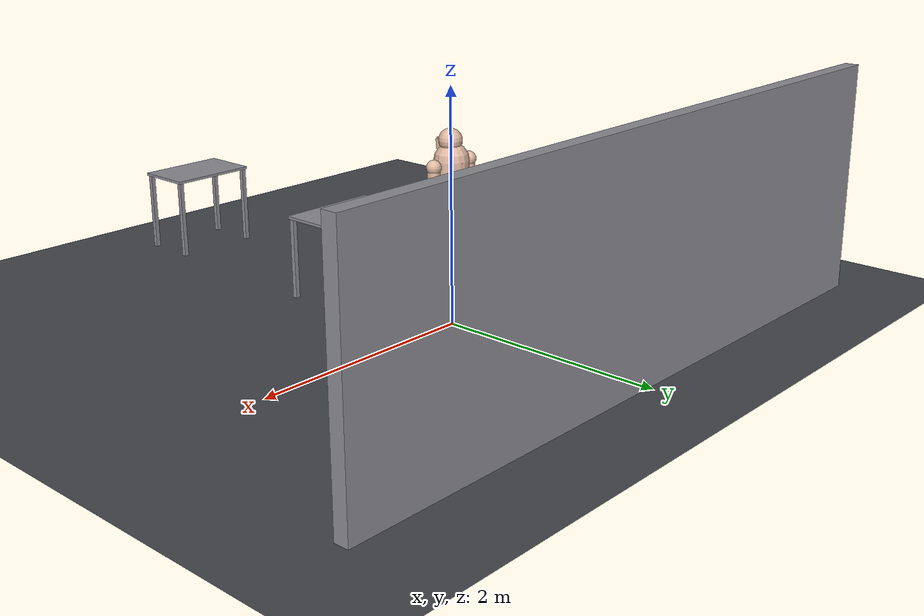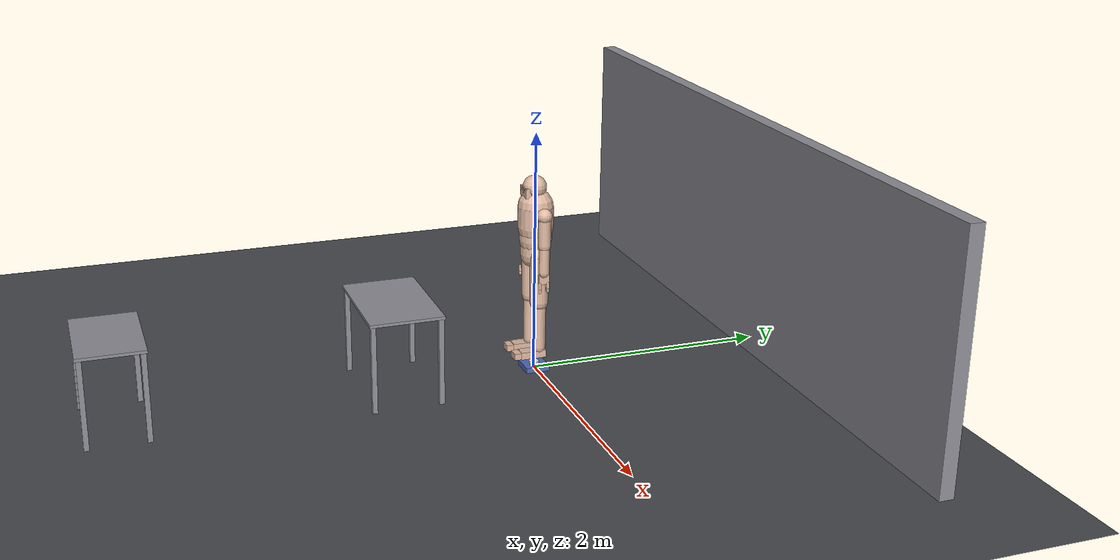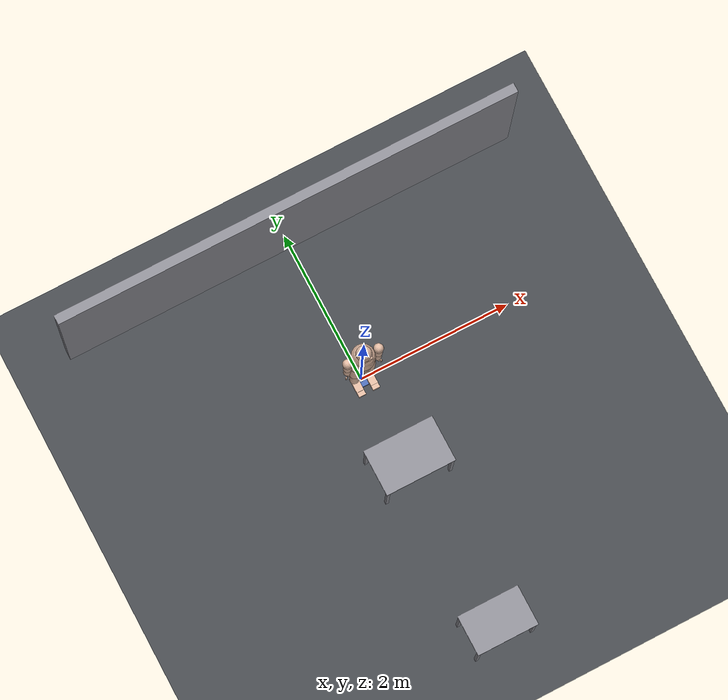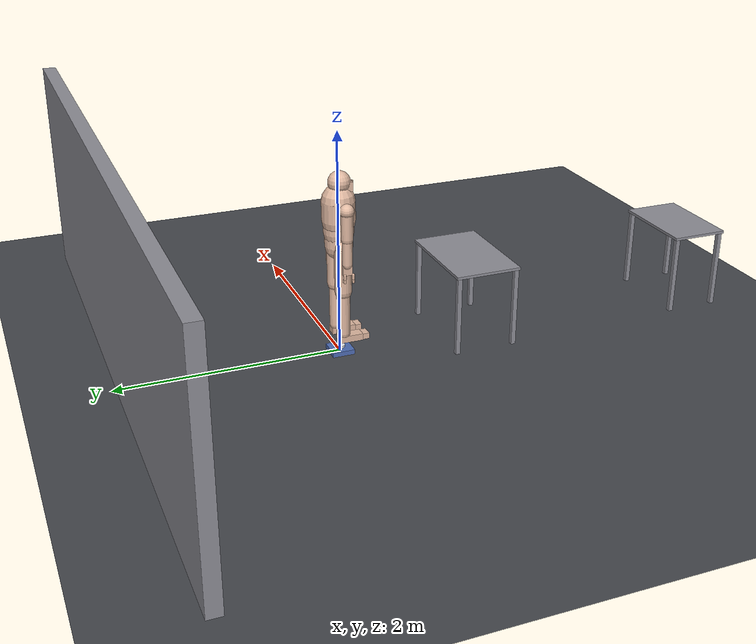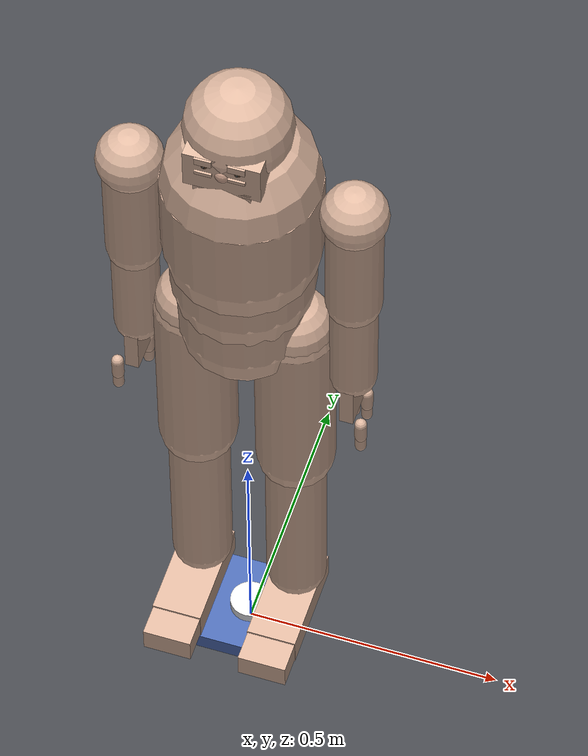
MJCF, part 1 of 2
<?xml version="1.0" encoding="utf-8"?>
<mujoco model="embodied_human">
  <compiler angle="radian" autolimits="true" inertiafromgeom="true" balanceinertia="true" discardvisual="false"/>
  <option timestep="0.00100000" integrator="implicitfast" gravity="0 0 -9.81" solver="Newton" cone="elliptic" impratio="10" iterations="80" tolerance="1e-9" o_solref="0.02 1" o_solimp="0.9 0.95 0.001 0.5 2"/>
  <size njmax="1500" nconmax="400" nkey="1"/>
  <visual>
    <map znear="0.005" zfar="60" shadowclip="1.0" fogstart="12" fogend="55"/>
    <quality shadowsize="2048" offsamples="0"/>
    <headlight ambient="0.34 0.34 0.38" diffuse="0.62 0.62 0.60" specular="0.20 0.20 0.20"/>
    <global azimuth="132" elevation="-16" fovy="52" offwidth="1280" offheight="960"/>
    <rgba haze="0.18 0.21 0.26 1"/>
  </visual>
  <statistic meansize="0.06" extent="1.6" center="0 0 0.9"/>
  <default>
    <joint damping="1.2" frictionloss="0.7" armature="0.03" solreflimit="0.004 1" solimplimit="0.9 0.95 0.001"/>
    <geom friction="1.1 0.02 0.001" margin="0.0008" condim="3" solref="0.008 1" solimp="0.92 0.96 0.001"/>
    <site group="4" rgba="0.95 0.35 0.25 0.35" size="0.012"/>
    <default class="soma">
      <geom type="capsule" condim="3" margin="0.001"/>
    </default>
    <default class="skin_site">
      <site group="5" rgba="1 0.45 0.35 0" size="0.012"/>
    </default>
    <default class="env">
      <geom contype="2" conaffinity="1" condim="3"/>
    </default>
  </default>
  <asset>
    <texture name="sky" type="skybox" builtin="gradient" rgb1="0.30 0.38 0.50" rgb2="0.06 0.08 0.12" width="256" height="256"/>
    <texture name="grid" type="2d" builtin="checker" rgb1="0.30 0.31 0.33" rgb2="0.24 0.25 0.27" width="512" height="512" markrgb="0.55 0.56 0.58" mark="none"/>
    <material name="floor" texture="grid" texrepeat="14 14" reflectance="0.12" shininess="0.15" specular="0.3"/>
    <material name="skin_mat" rgba="0.87 0.72 0.63 1" specular="0.25" shininess="0.25"/>
    <material name="wall_mat" rgba="0.55 0.55 0.58 1"/>
  </asset>
  <worldbody>
    <body name="pelvis" pos="0 0 0.98">
      <freejoint name="root"/>
      <geom name="" class="soma" type="capsule" pos="0 0 0.08" quat="1 0 0 0" size="0.122 0.06" mass="9.3" rgba="0.86 0.71 0.62 1" friction="1 0.02 0.001" contype="17" conaffinity="46"/>
      <site name="imu_pelvis" pos="0 0 0.06" size="0.008" group="3" rgba="0.2 0.7 1.0 0.5"/>
      <site name="tx_pelvis_000" class="skin_site" pos="0 -0.1235 0.038" size="0.01" rgba="1 0.45 0.35 0"/>
      <site name="tx_pelvis_001" class="skin_site" pos="0.0184067 -0.122121 0.038" size="0.01" rgba="1 0.45 0.35 0"/>
      <site name="tx_pelvis_002" class="skin_site" pos="0.0364023 -0.118013 0.038" size="0.01" rgba="1 0.45 0.35 0"/>
      <site name="tx_pelvis_003" class="skin_site" pos="0.0535846 -0.11127 0.038" size="0.01" rgba="1 0.45 0.35 0"/>
      <site name="tx_pelvis_004" class="skin_site" pos="0.06957 -0.10204 0.038" size="0.01" rgba="1 0.45 0.35 0"/>
      <site name="tx_pelvis_005" class="skin_site" pos="0.0840013 -0.0905319 0.038" size="0.01" rgba="1 0.45 0.35 0"/>
      <site name="tx_pelvis_006" class="skin_site" pos="0.0965562 -0.077001 0.038" size="0.01" rgba="1 0.45 0.35 0"/>
      <site name="tx_pelvis_007" class="skin_site" pos="0.106954 -0.06175 0.038" size="0.01" rgba="1 0.45 0.35 0"/>
      <site name="tx_pelvis_008" class="skin_site" pos="0.114963 -0.0451196 0.038" size="0.01" rgba="1 0.45 0.35 0"/>
      <site name="tx_pelvis_009" class="skin_site" pos="0.120404 -0.0274813 0.038" size="0.01" rgba="1 0.45 0.35 0"/>
      <site name="tx_pelvis_010" class="skin_site" pos="0.123155 -0.00922917 0.038" size="0.01" rgba="1 0.45 0.35 0"/>
      <site name="tx_pelvis_011" class="skin_site" pos="0.123155 0.00922917 0.038" size="0.01" rgba="1 0.45 0.35 0"/>
      <site name="tx_pelvis_012" class="skin_site" pos="0.120404 0.0274813 0.038" size="0.01" rgba="1 0.45 0.35 0"/>
      <site name="tx_pelvis_013" class="skin_site" pos="0.114963 0.0451196 0.038" size="0.01" rgba="1 0.45 0.35 0"/>
      <site name="tx_pelvis_014" class="skin_site" pos="0.106954 0.06175 0.038" size="0.01" rgba="1 0.45 0.35 0"/>
      <site name="tx_pelvis_015" class="skin_site" pos="0.0965562 0.077001 0.038" size="0.01" rgba="1 0.45 0.35 0"/>
      <site name="tx_pelvis_016" class="skin_site" pos="0.0840013 0.0905319 0.038" size="0.01" rgba="1 0.45 0.35 0"/>
      <site name="tx_pelvis_017" class="skin_site" pos="0.06957 0.10204 0.038" size="0.01" rgba="1 0.45 0.35 0"/>
      <site name="tx_pelvis_018" class="skin_site" pos="0.0535846 0.11127 0.038" size="0.01" rgba="1 0.45 0.35 0"/>
      <site name="tx_pelvis_019" class="skin_site" pos="0.0364023 0.118013 0.038" size="0.01" rgba="1 0.45 0.35 0"/>
      <site name="tx_pelvis_020" class="skin_site" pos="0.0184067 0.122121 0.038" size="0.01" rgba="1 0.45 0.35 0"/>
      <site name="tx_pelvis_021" class="skin_site" pos="1.51244e-17 0.1235 0.038" size="0.01" rgba="1 0.45 0.35 0"/>
      <site name="tx_pelvis_022" class="skin_site" pos="-0.0184067 0.122121 0.038" size="0.01" rgba="1 0.45 0.35 0"/>
      <site name="tx_pelvis_023" class="skin_site" pos="-0.0364023 0.118013 0.038" size="0.01" rgba="1 0.45 0.35 0"/>
      <site name="tx_pelvis_024" class="skin_site" pos="-0.0535846 0.11127 0.038" size="0.01" rgba="1 0.45 0.35 0"/>
      <site name="tx_pelvis_025" class="skin_site" pos="-0.06957 0.10204 0.038" size="0.01" rgba="1 0.45 0.35 0"/>
      <site name="tx_pelvis_026" class="skin_site" pos="-0.0840013 0.0905319 0.038" size="0.01" rgba="1 0.45 0.35 0"/>
      <site name="tx_pelvis_027" class="skin_site" pos="-0.0965562 0.077001 0.038" size="0.01" rgba="1 0.45 0.35 0"/>
      <site name="tx_pelvis_028" class="skin_site" pos="-0.106954 0.06175 0.038" size="0.01" rgba="1 0.45 0.35 0"/>
      <site name="tx_pelvis_029" class="skin_site" pos="-0.114963 0.0451196 0.038" size="0.01" rgba="1 0.45 0.35 0"/>
      <site name="tx_pelvis_030" class="skin_site" pos="-0.120404 0.0274813 0.038" size="0.01" rgba="1 0.45 0.35 0"/>
      <site name="tx_pelvis_031" class="skin_site" pos="-0.123155 0.00922917 0.038" size="0.01" rgba="1 0.45 0.35 0"/>
      <site name="tx_pelvis_032" class="skin_site" pos="-0.123155 -0.00922917 0.038" size="0.01" rgba="1 0.45 0.35 0"/>
      <site name="tx_pelvis_033" class="skin_site" pos="-0.120404 -0.0274813 0.038" size="0.01" rgba="1 0.45 0.35 0"/>
      <site name="tx_pelvis_034" class="skin_site" pos="-0.114963 -0.0451196 0.038" size="0.01" rgba="1 0.45 0.35 0"/>
      <site name="tx_pelvis_035" class="skin_site" pos="-0.106954 -0.06175 0.038" size="0.01" rgba="1 0.45 0.35 0"/>
      <site name="tx_pelvis_036" class="skin_site" pos="-0.0965562 -0.077001 0.038" size="0.01" rgba="1 0.45 0.35 0"/>
      <site name="tx_pelvis_037" class="skin_site" pos="-0.0840013 -0.0905319 0.038" size="0.01" rgba="1 0.45 0.35 0"/>
      <site name="tx_pelvis_038" class="skin_site" pos="-0.06957 -0.10204 0.038" size="0.01" rgba="1 0.45 0.35 0"/>
      <site name="tx_pelvis_039" class="skin_site" pos="-0.0535846 -0.11127 0.038" size="0.01" rgba="1 0.45 0.35 0"/>
      <site name="tx_pelvis_040" class="skin_site" pos="-0.0364023 -0.118013 0.038" size="0.01" rgba="1 0.45 0.35 0"/>
      <site name="tx_pelvis_041" class="skin_site" pos="-0.0184067 -0.122121 0.038" size="0.01" rgba="1 0.45 0.35 0"/>
      <site name="tx_pelvis_042" class="skin_site" pos="0 -0.1235 0.0470545" size="0.01" rgba="1 0.45 0.35 0"/>
      <site name="tx_pelvis_043" class="skin_site" pos="0.0184067 -0.122121 0.0470545" size="0.01" rgba="1 0.45 0.35 0"/>
      <site name="tx_pelvis_044" class="skin_site" pos="0.0364023 -0.118013 0.0470545" size="0.01" rgba="1 0.45 0.35 0"/>
      <site name="tx_pelvis_045" class="skin_site" pos="0.0535846 -0.11127 0.0470545" size="0.01" rgba="1 0.45 0.35 0"/>
      <site name="tx_pelvis_046" class="skin_site" pos="0.06957 -0.10204 0.0470545" size="0.01" rgba="1 0.45 0.35 0"/>
      <site name="tx_pelvis_047" class="skin_site" pos="0.0840013 -0.0905319 0.0470545" size="0.01" rgba="1 0.45 0.35 0"/>
      <site name="tx_pelvis_048" class="skin_site" pos="0.0965562 -0.077001 0.0470545" size="0.01" rgba="1 0.45 0.35 0"/>
      <site name="tx_pelvis_049" class="skin_site" pos="0.106954 -0.06175 0.0470545" size="0.01" rgba="1 0.45 0.35 0"/>
      <site name="tx_pelvis_050" class="skin_site" pos="0.114963 -0.0451196 0.0470545" size="0.01" rgba="1 0.45 0.35 0"/>
      <site name="tx_pelvis_051" class="skin_site" pos="0.120404 -0.0274813 0.0470545" size="0.01" rgba="1 0.45 0.35 0"/>
      <site name="tx_pelvis_052" class="skin_site" pos="0.123155 -0.00922917 0.0470545" size="0.01" rgba="1 0.45 0.35 0"/>
      <site name="tx_pelvis_053" class="skin_site" pos="0.123155 0.00922917 0.0470545" size="0.01" rgba="1 0.45 0.35 0"/>
      <site name="tx_pelvis_054" class="skin_site" pos="0.120404 0.0274813 0.0470545" size="0.01" rgba="1 0.45 0.35 0"/>
      <site name="tx_pelvis_055" class="skin_site" pos="0.114963 0.0451196 0.0470545" size="0.01" rgba="1 0.45 0.35 0"/>
      <site name="tx_pelvis_056" class="skin_site" pos="0.106954 0.06175 0.0470545" size="0.01" rgba="1 0.45 0.35 0"/>
      <site name="tx_pelvis_057" class="skin_site" pos="0.0965562 0.077001 0.0470545" size="0.01" rgba="1 0.45 0.35 0"/>
      <site name="tx_pelvis_058" class="skin_site" pos="0.0840013 0.0905319 0.0470545" size="0.01" rgba="1 0.45 0.35 0"/>
      <site name="tx_pelvis_059" class="skin_site" pos="0.06957 0.10204 0.0470545" size="0.01" rgba="1 0.45 0.35 0"/>
      <site name="tx_pelvis_060" class="skin_site" pos="0.0535846 0.11127 0.0470545" size="0.01" rgba="1 0.45 0.35 0"/>
      <site name="tx_pelvis_061" class="skin_site" pos="0.0364023 0.118013 0.0470545" size="0.01" rgba="1 0.45 0.35 0"/>
      <site name="tx_pelvis_062" class="skin_site" pos="0.0184067 0.122121 0.0470545" size="0.01" rgba="1 0.45 0.35 0"/>
      <site name="tx_pelvis_063" class="skin_site" pos="1.51244e-17 0.1235 0.0470545" size="0.01" rgba="1 0.45 0.35 0"/>
      <site name="tx_pelvis_064" class="skin_site" pos="-0.0184067 0.122121 0.0470545" size="0.01" rgba="1 0.45 0.35 0"/>
      <site name="tx_pelvis_065" class="skin_site" pos="-0.0364023 0.118013 0.0470545" size="0.01" rgba="1 0.45 0.35 0"/>
      <site name="tx_pelvis_066" class="skin_site" pos="-0.0535846 0.11127 0.0470545" size="0.01" rgba="1 0.45 0.35 0"/>
      <site name="tx_pelvis_067" class="skin_site" pos="-0.06957 0.10204 0.0470545" size="0.01" rgba="1 0.45 0.35 0"/>
      <site name="tx_pelvis_068" class="skin_site" pos="-0.0840013 0.0905319 0.0470545" size="0.01" rgba="1 0.45 0.35 0"/>
      <site name="tx_pelvis_069" class="skin_site" pos="-0.0965562 0.077001 0.0470545" size="0.01" rgba="1 0.45 0.35 0"/>
      <site name="tx_pelvis_070" class="skin_site" pos="-0.106954 0.06175 0.0470545" size="0.01" rgba="1 0.45 0.35 0"/>
      <site name="tx_pelvis_071" class="skin_site" pos="-0.114963 0.0451196 0.0470545" size="0.01" rgba="1 0.45 0.35 0"/>
      <site name="tx_pelvis_072" class="skin_site" pos="-0.120404 0.0274813 0.0470545" size="0.01" rgba="1 0.45 0.35 0"/>
      <site name="tx_pelvis_073" class="skin_site" pos="-0.123155 0.00922917 0.0470545" size="0.01" rgba="1 0.45 0.35 0"/>
      <site name="tx_pelvis_074" class="skin_site" pos="-0.123155 -0.00922917 0.0470545" size="0.01" rgba="1 0.45 0.35 0"/>
      <site name="tx_pelvis_075" class="skin_site" pos="-0.120404 -0.0274813 0.0470545" size="0.01" rgba="1 0.45 0.35 0"/>
      <site name="tx_pelvis_076" class="skin_site" pos="-0.114963 -0.0451196 0.0470545" size="0.01" rgba="1 0.45 0.35 0"/>
      <site name="tx_pelvis_077" class="skin_site" pos="-0.106954 -0.06175 0.0470545" size="0.01" rgba="1 0.45 0.35 0"/>
      <site name="tx_pelvis_078" class="skin_site" pos="-0.0965562 -0.077001 0.0470545" size="0.01" rgba="1 0.45 0.35 0"/>
      <site name="tx_pelvis_079" class="skin_site" pos="-0.0840013 -0.0905319 0.0470545" size="0.01" rgba="1 0.45 0.35 0"/>
      <site name="tx_pelvis_080" class="skin_site" pos="-0.06957 -0.10204 0.0470545" size="0.01" rgba="1 0.45 0.35 0"/>
      <site name="tx_pelvis_081" class="skin_site" pos="-0.0535846 -0.11127 0.0470545" size="0.01" rgba="1 0.45 0.35 0"/>
      <site name="tx_pelvis_082" class="skin_site" pos="-0.0364023 -0.118013 0.0470545" size="0.01" rgba="1 0.45 0.35 0"/>
      <site name="tx_pelvis_083" class="skin_site" pos="-0.0184067 -0.122121 0.0470545" size="0.01" rgba="1 0.45 0.35 0"/>
      <site name="tx_pelvis_084" class="skin_site" pos="0 -0.1235 0.0561091" size="0.01" rgba="1 0.45 0.35 0"/>
      <site name="tx_pelvis_085" class="skin_site" pos="0.0184067 -0.122121 0.0561091" size="0.01" rgba="1 0.45 0.35 0"/>
      <site name="tx_pelvis_086" class="skin_site" pos="0.0364023 -0.118013 0.0561091" size="0.01" rgba="1 0.45 0.35 0"/>
      <site name="tx_pelvis_087" class="skin_site" pos="0.0535846 -0.11127 0.0561091" size="0.01" rgba="1 0.45 0.35 0"/>
      <site name="tx_pelvis_088" class="skin_site" pos="0.06957 -0.10204 0.0561091" size="0.01" rgba="1 0.45 0.35 0"/>
      <site name="tx_pelvis_089" class="skin_site" pos="0.0840013 -0.0905319 0.0561091" size="0.01" rgba="1 0.45 0.35 0"/>
      <site name="tx_pelvis_090" class="skin_site" pos="0.0965562 -0.077001 0.0561091" size="0.01" rgba="1 0.45 0.35 0"/>
      <site name="tx_pelvis_091" class="skin_site" pos="0.106954 -0.06175 0.0561091" size="0.01" rgba="1 0.45 0.35 0"/>
      <site name="tx_pelvis_092" class="skin_site" pos="0.114963 -0.0451196 0.0561091" size="0.01" rgba="1 0.45 0.35 0"/>
      <site name="tx_pelvis_093" class="skin_site" pos="0.120404 -0.0274813 0.0561091" size="0.01" rgba="1 0.45 0.35 0"/>
      <site name="tx_pelvis_094" class="skin_site" pos="0.123155 -0.00922917 0.0561091" size="0.01" rgba="1 0.45 0.35 0"/>
      <site name="tx_pelvis_095" class="skin_site" pos="0.123155 0.00922917 0.0561091" size="0.01" rgba="1 0.45 0.35 0"/>
      <site name="tx_pelvis_096" class="skin_site" pos="0.120404 0.0274813 0.0561091" size="0.01" rgba="1 0.45 0.35 0"/>
      <site name="tx_pelvis_097" class="skin_site" pos="0.114963 0.0451196 0.0561091" size="0.01" rgba="1 0.45 0.35 0"/>
      <site name="tx_pelvis_098" class="skin_site" pos="0.106954 0.06175 0.0561091" size="0.01" rgba="1 0.45 0.35 0"/>
      <site name="tx_pelvis_099" class="skin_site" pos="0.0965562 0.077001 0.0561091" size="0.01" rgba="1 0.45 0.35 0"/>
      <site name="tx_pelvis_100" class="skin_site" pos="0.0840013 0.0905319 0.0561091" size="0.01" rgba="1 0.45 0.35 0"/>
      <site name="tx_pelvis_101" class="skin_site" pos="0.06957 0.10204 0.0561091" size="0.01" rgba="1 0.45 0.35 0"/>
      <site name="tx_pelvis_102" class="skin_site" pos="0.0535846 0.11127 0.0561091" size="0.01" rgba="1 0.45 0.35 0"/>
      <site name="tx_pelvis_103" class="skin_site" pos="0.0364023 0.118013 0.0561091" size="0.01" rgba="1 0.45 0.35 0"/>
      <site name="tx_pelvis_104" class="skin_site" pos="0.0184067 0.122121 0.0561091" size="0.01" rgba="1 0.45 0.35 0"/>
      <site name="tx_pelvis_105" class="skin_site" pos="1.51244e-17 0.1235 0.0561091" size="0.01" rgba="1 0.45 0.35 0"/>
      <site name="tx_pelvis_106" class="skin_site" pos="-0.0184067 0.122121 0.0561091" size="0.01" rgba="1 0.45 0.35 0"/>
      <site name="tx_pelvis_107" class="skin_site" pos="-0.0364023 0.118013 0.0561091" size="0.01" rgba="1 0.45 0.35 0"/>
      <site name="tx_pelvis_108" class="skin_site" pos="-0.0535846 0.11127 0.0561091" size="0.01" rgba="1 0.45 0.35 0"/>
      <site name="tx_pelvis_109" class="skin_site" pos="-0.06957 0.10204 0.0561091" size="0.01" rgba="1 0.45 0.35 0"/>
      <site name="tx_pelvis_110" class="skin_site" pos="-0.0840013 0.0905319 0.0561091" size="0.01" rgba="1 0.45 0.35 0"/>
      <site name="tx_pelvis_111" class="skin_site" pos="-0.0965562 0.077001 0.0561091" size="0.01" rgba="1 0.45 0.35 0"/>
      <site name="tx_pelvis_112" class="skin_site" pos="-0.106954 0.06175 0.0561091" size="0.01" rgba="1 0.45 0.35 0"/>
      <site name="tx_pelvis_113" class="skin_site" pos="-0.114963 0.0451196 0.0561091" size="0.01" rgba="1 0.45 0.35 0"/>
      <site name="tx_pelvis_114" class="skin_site" pos="-0.120404 0.0274813 0.0561091" size="0.01" rgba="1 0.45 0.35 0"/>
      <site name="tx_pelvis_115" class="skin_site" pos="-0.123155 0.00922917 0.0561091" size="0.01" rgba="1 0.45 0.35 0"/>
      <site name="tx_pelvis_116" class="skin_site" pos="-0.123155 -0.00922917 0.0561091" size="0.01" rgba="1 0.45 0.35 0"/>
      <site name="tx_pelvis_117" class="skin_site" pos="-0.120404 -0.0274813 0.0561091" size="0.01" rgba="1 0.45 0.35 0"/>
      <site name="tx_pelvis_118" class="skin_site" pos="-0.114963 -0.0451196 0.0561091" size="0.01" rgba="1 0.45 0.35 0"/>
      <site name="tx_pelvis_119" class="skin_site" pos="-0.106954 -0.06175 0.0561091" size="0.01" rgba="1 0.45 0.35 0"/>
      <site name="tx_pelvis_120" class="skin_site" pos="-0.0965562 -0.077001 0.0561091" size="0.01" rgba="1 0.45 0.35 0"/>
      <site name="tx_pelvis_121" class="skin_site" pos="-0.0840013 -0.0905319 0.0561091" size="0.01" rgba="1 0.45 0.35 0"/>
      <site name="tx_pelvis_122" class="skin_site" pos="-0.06957 -0.10204 0.0561091" size="0.01" rgba="1 0.45 0.35 0"/>
      <site name="tx_pelvis_123" class="skin_site" pos="-0.0535846 -0.11127 0.0561091" size="0.01" rgba="1 0.45 0.35 0"/>
      <site name="tx_pelvis_124" class="skin_site" pos="-0.0364023 -0.118013 0.0561091" size="0.01" rgba="1 0.45 0.35 0"/>
      <site name="tx_pelvis_125" class="skin_site" pos="-0.0184067 -0.122121 0.0561091" size="0.01" rgba="1 0.45 0.35 0"/>
      <site name="tx_pelvis_126" class="skin_site" pos="0 -0.1235 0.0651636" size="0.01" rgba="1 0.45 0.35 0"/>
      <site name="tx_pelvis_127" class="skin_site" pos="0.0184067 -0.122121 0.0651636" size="0.01" rgba="1 0.45 0.35 0"/>
      <site name="tx_pelvis_128" class="skin_site" pos="0.0364023 -0.118013 0.0651636" size="0.01" rgba="1 0.45 0.35 0"/>
      <site name="tx_pelvis_129" class="skin_site" pos="0.0535846 -0.11127 0.0651636" size="0.01" rgba="1 0.45 0.35 0"/>
      <site name="tx_pelvis_130" class="skin_site" pos="0.06957 -0.10204 0.0651636" size="0.01" rgba="1 0.45 0.35 0"/>
      <site name="tx_pelvis_131" class="skin_site" pos="0.0840013 -0.0905319 0.0651636" size="0.01" rgba="1 0.45 0.35 0"/>
      <site name="tx_pelvis_132" class="skin_site" pos="0.0965562 -0.077001 0.0651636" size="0.01" rgba="1 0.45 0.35 0"/>
      <site name="tx_pelvis_133" class="skin_site" pos="0.106954 -0.06175 0.0651636" size="0.01" rgba="1 0.45 0.35 0"/>
      <site name="tx_pelvis_134" class="skin_site" pos="0.114963 -0.0451196 0.0651636" size="0.01" rgba="1 0.45 0.35 0"/>
      <site name="tx_pelvis_135" class="skin_site" pos="0.120404 -0.0274813 0.0651636" size="0.01" rgba="1 0.45 0.35 0"/>
      <site name="tx_pelvis_136" class="skin_site" pos="0.123155 -0.00922917 0.0651636" size="0.01" rgba="1 0.45 0.35 0"/>
      <site name="tx_pelvis_137" class="skin_site" pos="0.123155 0.00922917 0.0651636" size="0.01" rgba="1 0.45 0.35 0"/>
      <site name="tx_pelvis_138" class="skin_site" pos="0.120404 0.0274813 0.0651636" size="0.01" rgba="1 0.45 0.35 0"/>
      <site name="tx_pelvis_139" class="skin_site" pos="0.114963 0.0451196 0.0651636" size="0.01" rgba="1 0.45 0.35 0"/>
      <site name="tx_pelvis_140" class="skin_site" pos="0.106954 0.06175 0.0651636" size="0.01" rgba="1 0.45 0.35 0"/>
      <site name="tx_pelvis_141" class="skin_site" pos="0.0965562 0.077001 0.0651636" size="0.01" rgba="1 0.45 0.35 0"/>
      <site name="tx_pelvis_142" class="skin_site" pos="0.0840013 0.0905319 0.0651636" size="0.01" rgba="1 0.45 0.35 0"/>
      <site name="tx_pelvis_143" class="skin_site" pos="0.06957 0.10204 0.0651636" size="0.01" rgba="1 0.45 0.35 0"/>
      <site name="tx_pelvis_144" class="skin_site" pos="0.0535846 0.11127 0.0651636" size="0.01" rgba="1 0.45 0.35 0"/>
      <site name="tx_pelvis_145" class="skin_site" pos="0.0364023 0.118013 0.0651636" size="0.01" rgba="1 0.45 0.35 0"/>
      <site name="tx_pelvis_146" class="skin_site" pos="0.0184067 0.122121 0.0651636" size="0.01" rgba="1 0.45 0.35 0"/>
      <site name="tx_pelvis_147" class="skin_site" pos="1.51244e-17 0.1235 0.0651636" size="0.01" rgba="1 0.45 0.35 0"/>
      <site name="tx_pelvis_148" class="skin_site" pos="-0.0184067 0.122121 0.0651636" size="0.01" rgba="1 0.45 0.35 0"/>
      <site name="tx_pelvis_149" class="skin_site" pos="-0.0364023 0.118013 0.0651636" size="0.01" rgba="1 0.45 0.35 0"/>
      <site name="tx_pelvis_150" class="skin_site" pos="-0.0535846 0.11127 0.0651636" size="0.01" rgba="1 0.45 0.35 0"/>
      <site name="tx_pelvis_151" class="skin_site" pos="-0.06957 0.10204 0.0651636" size="0.01" rgba="1 0.45 0.35 0"/>
      <site name="tx_pelvis_152" class="skin_site" pos="-0.0840013 0.0905319 0.0651636" size="0.01" rgba="1 0.45 0.35 0"/>
      <site name="tx_pelvis_153" class="skin_site" pos="-0.0965562 0.077001 0.0651636" size="0.01" rgba="1 0.45 0.35 0"/>
      <site name="tx_pelvis_154" class="skin_site" pos="-0.106954 0.06175 0.0651636" size="0.01" rgba="1 0.45 0.35 0"/>
      <site name="tx_pelvis_155" class="skin_site" pos="-0.114963 0.0451196 0.0651636" size="0.01" rgba="1 0.45 0.35 0"/>
      <site name="tx_pelvis_156" class="skin_site" pos="-0.120404 0.0274813 0.0651636" size="0.01" rgba="1 0.45 0.35 0"/>
      <site name="tx_pelvis_157" class="skin_site" pos="-0.123155 0.00922917 0.0651636" size="0.01" rgba="1 0.45 0.35 0"/>
      <site name="tx_pelvis_158" class="skin_site" pos="-0.123155 -0.00922917 0.0651636" size="0.01" rgba="1 0.45 0.35 0"/>
      <site name="tx_pelvis_159" class="skin_site" pos="-0.120404 -0.0274813 0.0651636" size="0.01" rgba="1 0.45 0.35 0"/>
      <site name="tx_pelvis_160" class="skin_site" pos="-0.114963 -0.0451196 0.0651636" size="0.01" rgba="1 0.45 0.35 0"/>
      <site name="tx_pelvis_161" class="skin_site" pos="-0.106954 -0.06175 0.0651636" size="0.01" rgba="1 0.45 0.35 0"/>
      <site name="tx_pelvis_162" class="skin_site" pos="-0.0965562 -0.077001 0.0651636" size="0.01" rgba="1 0.45 0.35 0"/>
      <site name="tx_pelvis_163" class="skin_site" pos="-0.0840013 -0.0905319 0.0651636" size="0.01" rgba="1 0.45 0.35 0"/>
      <site name="tx_pelvis_164" class="skin_site" pos="-0.06957 -0.10204 0.0651636" size="0.01" rgba="1 0.45 0.35 0"/>
      <site name="tx_pelvis_165" class="skin_site" pos="-0.0535846 -0.11127 0.0651636" size="0.01" rgba="1 0.45 0.35 0"/>
      <site name="tx_pelvis_166" class="skin_site" pos="-0.0364023 -0.118013 0.0651636" size="0.01" rgba="1 0.45 0.35 0"/>
      <site name="tx_pelvis_167" class="skin_site" pos="-0.0184067 -0.122121 0.0651636" size="0.01" rgba="1 0.45 0.35 0"/>
      <site name="tx_pelvis_168" class="skin_site" pos="0 -0.1235 0.0742182" size="0.01" rgba="1 0.45 0.35 0"/>
      <site name="tx_pelvis_169" class="skin_site" pos="0.0184067 -0.122121 0.0742182" size="0.01" rgba="1 0.45 0.35 0"/>
      <site name="tx_pelvis_170" class="skin_site" pos="0.0364023 -0.118013 0.0742182" size="0.01" rgba="1 0.45 0.35 0"/>
      <site name="tx_pelvis_171" class="skin_site" pos="0.0535846 -0.11127 0.0742182" size="0.01" rgba="1 0.45 0.35 0"/>
      <site name="tx_pelvis_172" class="skin_site" pos="0.06957 -0.10204 0.0742182" size="0.01" rgba="1 0.45 0.35 0"/>
      <site name="tx_pelvis_173" class="skin_site" pos="0.0840013 -0.0905319 0.0742182" size="0.01" rgba="1 0.45 0.35 0"/>
      <site name="tx_pelvis_174" class="skin_site" pos="0.0965562 -0.077001 0.0742182" size="0.01" rgba="1 0.45 0.35 0"/>
      <site name="tx_pelvis_175" class="skin_site" pos="0.106954 -0.06175 0.0742182" size="0.01" rgba="1 0.45 0.35 0"/>
      <site name="tx_pelvis_176" class="skin_site" pos="0.114963 -0.0451196 0.0742182" size="0.01" rgba="1 0.45 0.35 0"/>
      <site name="tx_pelvis_177" class="skin_site" pos="0.120404 -0.0274813 0.0742182" size="0.01" rgba="1 0.45 0.35 0"/>
      <site name="tx_pelvis_178" class="skin_site" pos="0.123155 -0.00922917 0.0742182" size="0.01" rgba="1 0.45 0.35 0"/>
      <site name="tx_pelvis_179" class="skin_site" pos="0.123155 0.00922917 0.0742182" size="0.01" rgba="1 0.45 0.35 0"/>
      <site name="tx_pelvis_180" class="skin_site" pos="0.120404 0.0274813 0.0742182" size="0.01" rgba="1 0.45 0.35 0"/>
      <site name="tx_pelvis_181" class="skin_site" pos="0.114963 0.0451196 0.0742182" size="0.01" rgba="1 0.45 0.35 0"/>
      <site name="tx_pelvis_182" class="skin_site" pos="0.106954 0.06175 0.0742182" size="0.01" rgba="1 0.45 0.35 0"/>
      <site name="tx_pelvis_183" class="skin_site" pos="0.0965562 0.077001 0.0742182" size="0.01" rgba="1 0.45 0.35 0"/>
      <site name="tx_pelvis_184" class="skin_site" pos="0.0840013 0.0905319 0.0742182" size="0.01" rgba="1 0.45 0.35 0"/>
      <site name="tx_pelvis_185" class="skin_site" pos="0.06957 0.10204 0.0742182" size="0.01" rgba="1 0.45 0.35 0"/>
      <site name="tx_pelvis_186" class="skin_site" pos="0.0535846 0.11127 0.0742182" size="0.01" rgba="1 0.45 0.35 0"/>
      <site name="tx_pelvis_187" class="skin_site" pos="0.0364023 0.118013 0.0742182" size="0.01" rgba="1 0.45 0.35 0"/>
      <site name="tx_pelvis_188" class="skin_site" pos="0.0184067 0.122121 0.0742182" size="0.01" rgba="1 0.45 0.35 0"/>
      <site name="tx_pelvis_189" class="skin_site" pos="1.51244e-17 0.1235 0.0742182" size="0.01" rgba="1 0.45 0.35 0"/>
      <site name="tx_pelvis_190" class="skin_site" pos="-0.0184067 0.122121 0.0742182" size="0.01" rgba="1 0.45 0.35 0"/>
      <site name="tx_pelvis_191" class="skin_site" pos="-0.0364023 0.118013 0.0742182" size="0.01" rgba="1 0.45 0.35 0"/>
      <site name="tx_pelvis_192" class="skin_site" pos="-0.0535846 0.11127 0.0742182" size="0.01" rgba="1 0.45 0.35 0"/>
      <site name="tx_pelvis_193" class="skin_site" pos="-0.06957 0.10204 0.0742182" size="0.01" rgba="1 0.45 0.35 0"/>
      <site name="tx_pelvis_194" class="skin_site" pos="-0.0840013 0.0905319 0.0742182" size="0.01" rgba="1 0.45 0.35 0"/>
      <site name="tx_pelvis_195" class="skin_site" pos="-0.0965562 0.077001 0.0742182" size="0.01" rgba="1 0.45 0.35 0"/>
      <site name="tx_pelvis_196" class="skin_site" pos="-0.106954 0.06175 0.0742182" size="0.01" rgba="1 0.45 0.35 0"/>
      <site name="tx_pelvis_197" class="skin_site" pos="-0.114963 0.0451196 0.0742182" size="0.01" rgba="1 0.45 0.35 0"/>
      <site name="tx_pelvis_198" class="skin_site" pos="-0.120404 0.0274813 0.0742182" size="0.01" rgba="1 0.45 0.35 0"/>
      <site name="tx_pelvis_199" class="skin_site" pos="-0.123155 0.00922917 0.0742182" size="0.01" rgba="1 0.45 0.35 0"/>
      <site name="tx_pelvis_200" class="skin_site" pos="-0.123155 -0.00922917 0.0742182" size="0.01" rgba="1 0.45 0.35 0"/>
      <site name="tx_pelvis_201" class="skin_site" pos="-0.120404 -0.0274813 0.0742182" size="0.01" rgba="1 0.45 0.35 0"/>
      <site name="tx_pelvis_202" class="skin_site" pos="-0.114963 -0.0451196 0.0742182" size="0.01" rgba="1 0.45 0.35 0"/>
      <site name="tx_pelvis_203" class="skin_site" pos="-0.106954 -0.06175 0.0742182" size="0.01" rgba="1 0.45 0.35 0"/>
      <site name="tx_pelvis_204" class="skin_site" pos="-0.0965562 -0.077001 0.0742182" size="0.01" rgba="1 0.45 0.35 0"/>
      <site name="tx_pelvis_205" class="skin_site" pos="-0.0840013 -0.0905319 0.0742182" size="0.01" rgba="1 0.45 0.35 0"/>
      <site name="tx_pelvis_206" class="skin_site" pos="-0.06957 -0.10204 0.0742182" size="0.01" rgba="1 0.45 0.35 0"/>
      <site name="tx_pelvis_207" class="skin_site" pos="-0.0535846 -0.11127 0.0742182" size="0.01" rgba="1 0.45 0.35 0"/>
      <site name="tx_pelvis_208" class="skin_site" pos="-0.0364023 -0.118013 0.0742182" size="0.01" rgba="1 0.45 0.35 0"/>
      <site name="tx_pelvis_209" class="skin_site" pos="-0.0184067 -0.122121 0.0742182" size="0.01" rgba="1 0.45 0.35 0"/>
      <site name="tx_pelvis_210" class="skin_site" pos="0 -0.1235 0.0832727" size="0.01" rgba="1 0.45 0.35 0"/>
      <site name="tx_pelvis_211" class="skin_site" pos="0.0184067 -0.122121 0.0832727" size="0.01" rgba="1 0.45 0.35 0"/>
      <site name="tx_pelvis_212" class="skin_site" pos="0.0364023 -0.118013 0.0832727" size="0.01" rgba="1 0.45 0.35 0"/>
      <site name="tx_pelvis_213" class="skin_site" pos="0.0535846 -0.11127 0.0832727" size="0.01" rgba="1 0.45 0.35 0"/>
      <site name="tx_pelvis_214" class="skin_site" pos="0.06957 -0.10204 0.0832727" size="0.01" rgba="1 0.45 0.35 0"/>
      <site name="tx_pelvis_215" class="skin_site" pos="0.0840013 -0.0905319 0.0832727" size="0.01" rgba="1 0.45 0.35 0"/>
      <site name="tx_pelvis_216" class="skin_site" pos="0.0965562 -0.077001 0.0832727" size="0.01" rgba="1 0.45 0.35 0"/>
      <site name="tx_pelvis_217" class="skin_site" pos="0.106954 -0.06175 0.0832727" size="0.01" rgba="1 0.45 0.35 0"/>
      <site name="tx_pelvis_218" class="skin_site" pos="0.114963 -0.0451196 0.0832727" size="0.01" rgba="1 0.45 0.35 0"/>
      <site name="tx_pelvis_219" class="skin_site" pos="0.120404 -0.0274813 0.0832727" size="0.01" rgba="1 0.45 0.35 0"/>
      <site name="tx_pelvis_220" class="skin_site" pos="0.123155 -0.00922917 0.0832727" size="0.01" rgba="1 0.45 0.35 0"/>
      <site name="tx_pelvis_221" class="skin_site" pos="0.123155 0.00922917 0.0832727" size="0.01" rgba="1 0.45 0.35 0"/>
      <site name="tx_pelvis_222" class="skin_site" pos="0.120404 0.0274813 0.0832727" size="0.01" rgba="1 0.45 0.35 0"/>
      <site name="tx_pelvis_223" class="skin_site" pos="0.114963 0.0451196 0.0832727" size="0.01" rgba="1 0.45 0.35 0"/>
      <site name="tx_pelvis_224" class="skin_site" pos="0.106954 0.06175 0.0832727" size="0.01" rgba="1 0.45 0.35 0"/>
      <site name="tx_pelvis_225" class="skin_site" pos="0.0965562 0.077001 0.0832727" size="0.01" rgba="1 0.45 0.35 0"/>
      <site name="tx_pelvis_226" class="skin_site" pos="0.0840013 0.0905319 0.0832727" size="0.01" rgba="1 0.45 0.35 0"/>
      <site name="tx_pelvis_227" class="skin_site" pos="0.06957 0.10204 0.0832727" size="0.01" rgba="1 0.45 0.35 0"/>
      <site name="tx_pelvis_228" class="skin_site" pos="0.0535846 0.11127 0.0832727" size="0.01" rgba="1 0.45 0.35 0"/>
      <site name="tx_pelvis_229" class="skin_site" pos="0.0364023 0.118013 0.0832727" size="0.01" rgba="1 0.45 0.35 0"/>
      <site name="tx_pelvis_230" class="skin_site" pos="0.0184067 0.122121 0.0832727" size="0.01" rgba="1 0.45 0.35 0"/>
      <site name="tx_pelvis_231" class="skin_site" pos="1.51244e-17 0.1235 0.0832727" size="0.01" rgba="1 0.45 0.35 0"/>
      <site name="tx_pelvis_232" class="skin_site" pos="-0.0184067 0.122121 0.0832727" size="0.01" rgba="1 0.45 0.35 0"/>
      <site name="tx_pelvis_233" class="skin_site" pos="-0.0364023 0.118013 0.0832727" size="0.01" rgba="1 0.45 0.35 0"/>
      <site name="tx_pelvis_234" class="skin_site" pos="-0.0535846 0.11127 0.0832727" size="0.01" rgba="1 0.45 0.35 0"/>
      <site name="tx_pelvis_235" class="skin_site" pos="-0.06957 0.10204 0.0832727" size="0.01" rgba="1 0.45 0.35 0"/>
      <site name="tx_pelvis_236" class="skin_site" pos="-0.0840013 0.0905319 0.0832727" size="0.01" rgba="1 0.45 0.35 0"/>
      <site name="tx_pelvis_237" class="skin_site" pos="-0.0965562 0.077001 0.0832727" size="0.01" rgba="1 0.45 0.35 0"/>
      <site name="tx_pelvis_238" class="skin_site" pos="-0.106954 0.06175 0.0832727" size="0.01" rgba="1 0.45 0.35 0"/>
      <site name="tx_pelvis_239" class="skin_site" pos="-0.114963 0.0451196 0.0832727" size="0.01" rgba="1 0.45 0.35 0"/>
      <site name="tx_pelvis_240" class="skin_site" pos="-0.120404 0.0274813 0.0832727" size="0.01" rgba="1 0.45 0.35 0"/>
      <site name="tx_pelvis_241" class="skin_site" pos="-0.123155 0.00922917 0.0832727" size="0.01" rgba="1 0.45 0.35 0"/>
      <site name="tx_pelvis_242" class="skin_site" pos="-0.123155 -0.00922917 0.0832727" size="0.01" rgba="1 0.45 0.35 0"/>
      <site name="tx_pelvis_243" class="skin_site" pos="-0.120404 -0.0274813 0.0832727" size="0.01" rgba="1 0.45 0.35 0"/>
      <site name="tx_pelvis_244" class="skin_site" pos="-0.114963 -0.0451196 0.0832727" size="0.01" rgba="1 0.45 0.35 0"/>
      <site name="tx_pelvis_245" class="skin_site" pos="-0.106954 -0.06175 0.0832727" size="0.01" rgba="1 0.45 0.35 0"/>
      <site name="tx_pelvis_246" class="skin_site" pos="-0.0965562 -0.077001 0.0832727" size="0.01" rgba="1 0.45 0.35 0"/>
      <site name="tx_pelvis_247" class="skin_site" pos="-0.0840013 -0.0905319 0.0832727" size="0.01" rgba="1 0.45 0.35 0"/>
      <site name="tx_pelvis_248" class="skin_site" pos="-0.06957 -0.10204 0.0832727" size="0.01" rgba="1 0.45 0.35 0"/>
      <site name="tx_pelvis_249" class="skin_site" pos="-0.0535846 -0.11127 0.0832727" size="0.01" rgba="1 0.45 0.35 0"/>
      <site name="tx_pelvis_250" class="skin_site" pos="-0.0364023 -0.118013 0.0832727" size="0.01" rgba="1 0.45 0.35 0"/>
      <site name="tx_pelvis_251" class="skin_site" pos="-0.0184067 -0.122121 0.0832727" size="0.01" rgba="1 0.45 0.35 0"/>
      <site name="tx_pelvis_252" class="skin_site" pos="0 -0.1235 0.0923273" size="0.01" rgba="1 0.45 0.35 0"/>
      <site name="tx_pelvis_253" class="skin_site" pos="0.0184067 -0.122121 0.0923273" size="0.01" rgba="1 0.45 0.35 0"/>
      <site name="tx_pelvis_254" class="skin_site" pos="0.0364023 -0.118013 0.0923273" size="0.01" rgba="1 0.45 0.35 0"/>
      <site name="tx_pelvis_255" class="skin_site" pos="0.0535846 -0.11127 0.0923273" size="0.01" rgba="1 0.45 0.35 0"/>
      <site name="tx_pelvis_256" class="skin_site" pos="0.06957 -0.10204 0.0923273" size="0.01" rgba="1 0.45 0.35 0"/>
      <site name="tx_pelvis_257" class="skin_site" pos="0.0840013 -0.0905319 0.0923273" size="0.01" rgba="1 0.45 0.35 0"/>
      <site name="tx_pelvis_258" class="skin_site" pos="0.0965562 -0.077001 0.0923273" size="0.01" rgba="1 0.45 0.35 0"/>
      <site name="tx_pelvis_259" class="skin_site" pos="0.106954 -0.06175 0.0923273" size="0.01" rgba="1 0.45 0.35 0"/>
      <site name="tx_pelvis_260" class="skin_site" pos="0.114963 -0.0451196 0.0923273" size="0.01" rgba="1 0.45 0.35 0"/>
      <site name="tx_pelvis_261" class="skin_site" pos="0.120404 -0.0274813 0.0923273" size="0.01" rgba="1 0.45 0.35 0"/>
      <site name="tx_pelvis_262" class="skin_site" pos="0.123155 -0.00922917 0.0923273" size="0.01" rgba="1 0.45 0.35 0"/>
      <site name="tx_pelvis_263" class="skin_site" pos="0.123155 0.00922917 0.0923273" size="0.01" rgba="1 0.45 0.35 0"/>
      <site name="tx_pelvis_264" class="skin_site" pos="0.120404 0.0274813 0.0923273" size="0.01" rgba="1 0.45 0.35 0"/>
      <site name="tx_pelvis_265" class="skin_site" pos="0.114963 0.0451196 0.0923273" size="0.01" rgba="1 0.45 0.35 0"/>
      <site name="tx_pelvis_266" class="skin_site" pos="0.106954 0.06175 0.0923273" size="0.01" rgba="1 0.45 0.35 0"/>
      <site name="tx_pelvis_267" class="skin_site" pos="0.0965562 0.077001 0.0923273" size="0.01" rgba="1 0.45 0.35 0"/>
      <site name="tx_pelvis_268" class="skin_site" pos="0.0840013 0.0905319 0.0923273" size="0.01" rgba="1 0.45 0.35 0"/>
      <site name="tx_pelvis_269" class="skin_site" pos="0.06957 0.10204 0.0923273" size="0.01" rgba="1 0.45 0.35 0"/>
      <site name="tx_pelvis_270" class="skin_site" pos="0.0535846 0.11127 0.0923273" size="0.01" rgba="1 0.45 0.35 0"/>
      <site name="tx_pelvis_271" class="skin_site" pos="0.0364023 0.118013 0.0923273" size="0.01" rgba="1 0.45 0.35 0"/>
      <site name="tx_pelvis_272" class="skin_site" pos="0.0184067 0.122121 0.0923273" size="0.01" rgba="1 0.45 0.35 0"/>
      <site name="tx_pelvis_273" class="skin_site" pos="1.51244e-17 0.1235 0.0923273" size="0.01" rgba="1 0.45 0.35 0"/>
      <site name="tx_pelvis_274" class="skin_site" pos="-0.0184067 0.122121 0.0923273" size="0.01" rgba="1 0.45 0.35 0"/>
      <site name="tx_pelvis_275" class="skin_site" pos="-0.0364023 0.118013 0.0923273" size="0.01" rgba="1 0.45 0.35 0"/>
      <site name="tx_pelvis_276" class="skin_site" pos="-0.0535846 0.11127 0.0923273" size="0.01" rgba="1 0.45 0.35 0"/>
      <site name="tx_pelvis_277" class="skin_site" pos="-0.06957 0.10204 0.0923273" size="0.01" rgba="1 0.45 0.35 0"/>
      <site name="tx_pelvis_278" class="skin_site" pos="-0.0840013 0.0905319 0.0923273" size="0.01" rgba="1 0.45 0.35 0"/>
      <site name="tx_pelvis_279" class="skin_site" pos="-0.0965562 0.077001 0.0923273" size="0.01" rgba="1 0.45 0.35 0"/>
      <site name="tx_pelvis_280" class="skin_site" pos="-0.106954 0.06175 0.0923273" size="0.01" rgba="1 0.45 0.35 0"/>
      <site name="tx_pelvis_281" class="skin_site" pos="-0.114963 0.0451196 0.0923273" size="0.01" rgba="1 0.45 0.35 0"/>
      <site name="tx_pelvis_282" class="skin_site" pos="-0.120404 0.0274813 0.0923273" size="0.01" rgba="1 0.45 0.35 0"/>
      <site name="tx_pelvis_283" class="skin_site" pos="-0.123155 0.00922917 0.0923273" size="0.01" rgba="1 0.45 0.35 0"/>
      <site name="tx_pelvis_284" class="skin_site" pos="-0.123155 -0.00922917 0.0923273" size="0.01" rgba="1 0.45 0.35 0"/>
      <site name="tx_pelvis_285" class="skin_site" pos="-0.120404 -0.0274813 0.0923273" size="0.01" rgba="1 0.45 0.35 0"/>
      <site name="tx_pelvis_286" class="skin_site" pos="-0.114963 -0.0451196 0.0923273" size="0.01" rgba="1 0.45 0.35 0"/>
      <site name="tx_pelvis_287" class="skin_site" pos="-0.106954 -0.06175 0.0923273" size="0.01" rgba="1 0.45 0.35 0"/>
      <site name="tx_pelvis_288" class="skin_site" pos="-0.0965562 -0.077001 0.0923273" size="0.01" rgba="1 0.45 0.35 0"/>
      <site name="tx_pelvis_289" class="skin_site" pos="-0.0840013 -0.0905319 0.0923273" size="0.01" rgba="1 0.45 0.35 0"/>
      <site name="tx_pelvis_290" class="skin_site" pos="-0.06957 -0.10204 0.0923273" size="0.01" rgba="1 0.45 0.35 0"/>
      <site name="tx_pelvis_291" class="skin_site" pos="-0.0535846 -0.11127 0.0923273" size="0.01" rgba="1 0.45 0.35 0"/>
      <site name="tx_pelvis_292" class="skin_site" pos="-0.0364023 -0.118013 0.0923273" size="0.01" rgba="1 0.45 0.35 0"/>
      <site name="tx_pelvis_293" class="skin_site" pos="-0.0184067 -0.122121 0.0923273" size="0.01" rgba="1 0.45 0.35 0"/>
      <site name="tx_pelvis_294" class="skin_site" pos="0 -0.1235 0.101382" size="0.01" rgba="1 0.45 0.35 0"/>
      <site name="tx_pelvis_295" class="skin_site" pos="0.0184067 -0.122121 0.101382" size="0.01" rgba="1 0.45 0.35 0"/>
      <site name="tx_pelvis_296" class="skin_site" pos="0.0364023 -0.118013 0.101382" size="0.01" rgba="1 0.45 0.35 0"/>
      <site name="tx_pelvis_297" class="skin_site" pos="0.0535846 -0.11127 0.101382" size="0.01" rgba="1 0.45 0.35 0"/>
      <site name="tx_pelvis_298" class="skin_site" pos="0.06957 -0.10204 0.101382" size="0.01" rgba="1 0.45 0.35 0"/>
      <site name="tx_pelvis_299" class="skin_site" pos="0.0840013 -0.0905319 0.101382" size="0.01" rgba="1 0.45 0.35 0"/>
      <site name="tx_pelvis_300" class="skin_site" pos="0.0965562 -0.077001 0.101382" size="0.01" rgba="1 0.45 0.35 0"/>
      <site name="tx_pelvis_301" class="skin_site" pos="0.106954 -0.06175 0.101382" size="0.01" rgba="1 0.45 0.35 0"/>
      <site name="tx_pelvis_302" class="skin_site" pos="0.114963 -0.0451196 0.101382" size="0.01" rgba="1 0.45 0.35 0"/>
      <site name="tx_pelvis_303" class="skin_site" pos="0.120404 -0.0274813 0.101382" size="0.01" rgba="1 0.45 0.35 0"/>
      <site name="tx_pelvis_304" class="skin_site" pos="0.123155 -0.00922917 0.101382" size="0.01" rgba="1 0.45 0.35 0"/>
      <site name="tx_pelvis_305" class="skin_site" pos="0.123155 0.00922917 0.101382" size="0.01" rgba="1 0.45 0.35 0"/>
      <site name="tx_pelvis_306" class="skin_site" pos="0.120404 0.0274813 0.101382" size="0.01" rgba="1 0.45 0.35 0"/>
      <site name="tx_pelvis_307" class="skin_site" pos="0.114963 0.0451196 0.101382" size="0.01" rgba="1 0.45 0.35 0"/>
      <site name="tx_pelvis_308" class="skin_site" pos="0.106954 0.06175 0.101382" size="0.01" rgba="1 0.45 0.35 0"/>
      <site name="tx_pelvis_309" class="skin_site" pos="0.0965562 0.077001 0.101382" size="0.01" rgba="1 0.45 0.35 0"/>
      <site name="tx_pelvis_310" class="skin_site" pos="0.0840013 0.0905319 0.101382" size="0.01" rgba="1 0.45 0.35 0"/>
      <site name="tx_pelvis_311" class="skin_site" pos="0.06957 0.10204 0.101382" size="0.01" rgba="1 0.45 0.35 0"/>
      <site name="tx_pelvis_312" class="skin_site" pos="0.0535846 0.11127 0.101382" size="0.01" rgba="1 0.45 0.35 0"/>
      <site name="tx_pelvis_313" class="skin_site" pos="0.0364023 0.118013 0.101382" size="0.01" rgba="1 0.45 0.35 0"/>
      <site name="tx_pelvis_314" class="skin_site" pos="0.0184067 0.122121 0.101382" size="0.01" rgba="1 0.45 0.35 0"/>
      <site name="tx_pelvis_315" class="skin_site" pos="1.51244e-17 0.1235 0.101382" size="0.01" rgba="1 0.45 0.35 0"/>
      <site name="tx_pelvis_316" class="skin_site" pos="-0.0184067 0.122121 0.101382" size="0.01" rgba="1 0.45 0.35 0"/>
      <site name="tx_pelvis_317" class="skin_site" pos="-0.0364023 0.118013 0.101382" size="0.01" rgba="1 0.45 0.35 0"/>
      <site name="tx_pelvis_318" class="skin_site" pos="-0.0535846 0.11127 0.101382" size="0.01" rgba="1 0.45 0.35 0"/>
      <site name="tx_pelvis_319" class="skin_site" pos="-0.06957 0.10204 0.101382" size="0.01" rgba="1 0.45 0.35 0"/>
      <site name="tx_pelvis_320" class="skin_site" pos="-0.0840013 0.0905319 0.101382" size="0.01" rgba="1 0.45 0.35 0"/>
      <site name="tx_pelvis_321" class="skin_site" pos="-0.0965562 0.077001 0.101382" size="0.01" rgba="1 0.45 0.35 0"/>
      <site name="tx_pelvis_322" class="skin_site" pos="-0.106954 0.06175 0.101382" size="0.01" rgba="1 0.45 0.35 0"/>
      <site name="tx_pelvis_323" class="skin_site" pos="-0.114963 0.0451196 0.101382" size="0.01" rgba="1 0.45 0.35 0"/>
      <site name="tx_pelvis_324" class="skin_site" pos="-0.120404 0.0274813 0.101382" size="0.01" rgba="1 0.45 0.35 0"/>
      <site name="tx_pelvis_325" class="skin_site" pos="-0.123155 0.00922917 0.101382" size="0.01" rgba="1 0.45 0.35 0"/>
      <site name="tx_pelvis_326" class="skin_site" pos="-0.123155 -0.00922917 0.101382" size="0.01" rgba="1 0.45 0.35 0"/>
      <site name="tx_pelvis_327" class="skin_site" pos="-0.120404 -0.0274813 0.101382" size="0.01" rgba="1 0.45 0.35 0"/>
      <site name="tx_pelvis_328" class="skin_site" pos="-0.114963 -0.0451196 0.101382" size="0.01" rgba="1 0.45 0.35 0"/>
      <site name="tx_pelvis_329" class="skin_site" pos="-0.106954 -0.06175 0.101382" size="0.01" rgba="1 0.45 0.35 0"/>
      <site name="tx_pelvis_330" class="skin_site" pos="-0.0965562 -0.077001 0.101382" size="0.01" rgba="1 0.45 0.35 0"/>
      <site name="tx_pelvis_331" class="skin_site" pos="-0.0840013 -0.0905319 0.101382" size="0.01" rgba="1 0.45 0.35 0"/>
      <site name="tx_pelvis_332" class="skin_site" pos="-0.06957 -0.10204 0.101382" size="0.01" rgba="1 0.45 0.35 0"/>
      <site name="tx_pelvis_333" class="skin_site" pos="-0.0535846 -0.11127 0.101382" size="0.01" rgba="1 0.45 0.35 0"/>
      <site name="tx_pelvis_334" class="skin_site" pos="-0.0364023 -0.118013 0.101382" size="0.01" rgba="1 0.45 0.35 0"/>
      <site name="tx_pelvis_335" class="skin_site" pos="-0.0184067 -0.122121 0.101382" size="0.01" rgba="1 0.45 0.35 0"/>
      <site name="tx_pelvis_336" class="skin_site" pos="0 -0.1235 0.110436" size="0.01" rgba="1 0.45 0.35 0"/>
      <site name="tx_pelvis_337" class="skin_site" pos="0.0184067 -0.122121 0.110436" size="0.01" rgba="1 0.45 0.35 0"/>
      <site name="tx_pelvis_338" class="skin_site" pos="0.0364023 -0.118013 0.110436" size="0.01" rgba="1 0.45 0.35 0"/>
      <site name="tx_pelvis_339" class="skin_site" pos="0.0535846 -0.11127 0.110436" size="0.01" rgba="1 0.45 0.35 0"/>
      <site name="tx_pelvis_340" class="skin_site" pos="0.06957 -0.10204 0.110436" size="0.01" rgba="1 0.45 0.35 0"/>
      <site name="tx_pelvis_341" class="skin_site" pos="0.0840013 -0.0905319 0.110436" size="0.01" rgba="1 0.45 0.35 0"/>
      <site name="tx_pelvis_342" class="skin_site" pos="0.0965562 -0.077001 0.110436" size="0.01" rgba="1 0.45 0.35 0"/>
      <site name="tx_pelvis_343" class="skin_site" pos="0.106954 -0.06175 0.110436" size="0.01" rgba="1 0.45 0.35 0"/>
      <site name="tx_pelvis_344" class="skin_site" pos="0.114963 -0.0451196 0.110436" size="0.01" rgba="1 0.45 0.35 0"/>
      <site name="tx_pelvis_345" class="skin_site" pos="0.120404 -0.0274813 0.110436" size="0.01" rgba="1 0.45 0.35 0"/>
      <site name="tx_pelvis_346" class="skin_site" pos="0.123155 -0.00922917 0.110436" size="0.01" rgba="1 0.45 0.35 0"/>
      <site name="tx_pelvis_347" class="skin_site" pos="0.123155 0.00922917 0.110436" size="0.01" rgba="1 0.45 0.35 0"/>
      <site name="tx_pelvis_348" class="skin_site" pos="0.120404 0.0274813 0.110436" size="0.01" rgba="1 0.45 0.35 0"/>
      <site name="tx_pelvis_349" class="skin_site" pos="0.114963 0.0451196 0.110436" size="0.01" rgba="1 0.45 0.35 0"/>
      <site name="tx_pelvis_350" class="skin_site" pos="0.106954 0.06175 0.110436" size="0.01" rgba="1 0.45 0.35 0"/>
      <site name="tx_pelvis_351" class="skin_site" pos="0.0965562 0.077001 0.110436" size="0.01" rgba="1 0.45 0.35 0"/>
      <site name="tx_pelvis_352" class="skin_site" pos="0.0840013 0.0905319 0.110436" size="0.01" rgba="1 0.45 0.35 0"/>
      <site name="tx_pelvis_353" class="skin_site" pos="0.06957 0.10204 0.110436" size="0.01" rgba="1 0.45 0.35 0"/>
      <site name="tx_pelvis_354" class="skin_site" pos="0.0535846 0.11127 0.110436" size="0.01" rgba="1 0.45 0.35 0"/>
      <site name="tx_pelvis_355" class="skin_site" pos="0.0364023 0.118013 0.110436" size="0.01" rgba="1 0.45 0.35 0"/>
      <site name="tx_pelvis_356" class="skin_site" pos="0.0184067 0.122121 0.110436" size="0.01" rgba="1 0.45 0.35 0"/>
      <site name="tx_pelvis_357" class="skin_site" pos="1.51244e-17 0.1235 0.110436" size="0.01" rgba="1 0.45 0.35 0"/>
      <site name="tx_pelvis_358" class="skin_site" pos="-0.0184067 0.122121 0.110436" size="0.01" rgba="1 0.45 0.35 0"/>
      <site name="tx_pelvis_359" class="skin_site" pos="-0.0364023 0.118013 0.110436" size="0.01" rgba="1 0.45 0.35 0"/>
      <site name="tx_pelvis_360" class="skin_site" pos="-0.0535846 0.11127 0.110436" size="0.01" rgba="1 0.45 0.35 0"/>
      <site name="tx_pelvis_361" class="skin_site" pos="-0.06957 0.10204 0.110436" size="0.01" rgba="1 0.45 0.35 0"/>
      <site name="tx_pelvis_362" class="skin_site" pos="-0.0840013 0.0905319 0.110436" size="0.01" rgba="1 0.45 0.35 0"/>
      <site name="tx_pelvis_363" class="skin_site" pos="-0.0965562 0.077001 0.110436" size="0.01" rgba="1 0.45 0.35 0"/>
      <site name="tx_pelvis_364" class="skin_site" pos="-0.106954 0.06175 0.110436" size="0.01" rgba="1 0.45 0.35 0"/>
      <site name="tx_pelvis_365" class="skin_site" pos="-0.114963 0.0451196 0.110436" size="0.01" rgba="1 0.45 0.35 0"/>
      <site name="tx_pelvis_366" class="skin_site" pos="-0.120404 0.0274813 0.110436" size="0.01" rgba="1 0.45 0.35 0"/>
      <site name="tx_pelvis_367" class="skin_site" pos="-0.123155 0.00922917 0.110436" size="0.01" rgba="1 0.45 0.35 0"/>
      <site name="tx_pelvis_368" class="skin_site" pos="-0.123155 -0.00922917 0.110436" size="0.01" rgba="1 0.45 0.35 0"/>
      <site name="tx_pelvis_369" class="skin_site" pos="-0.120404 -0.0274813 0.110436" size="0.01" rgba="1 0.45 0.35 0"/>
      <site name="tx_pelvis_370" class="skin_site" pos="-0.114963 -0.0451196 0.110436" size="0.01" rgba="1 0.45 0.35 0"/>
      <site name="tx_pelvis_371" class="skin_site" pos="-0.106954 -0.06175 0.110436" size="0.01" rgba="1 0.45 0.35 0"/>
      <site name="tx_pelvis_372" class="skin_site" pos="-0.0965562 -0.077001 0.110436" size="0.01" rgba="1 0.45 0.35 0"/>
      <site name="tx_pelvis_373" class="skin_site" pos="-0.0840013 -0.0905319 0.110436" size="0.01" rgba="1 0.45 0.35 0"/>
      <site name="tx_pelvis_374" class="skin_site" pos="-0.06957 -0.10204 0.110436" size="0.01" rgba="1 0.45 0.35 0"/>
      <site name="tx_pelvis_375" class="skin_site" pos="-0.0535846 -0.11127 0.110436" size="0.01" rgba="1 0.45 0.35 0"/>
      <site name="tx_pelvis_376" class="skin_site" pos="-0.0364023 -0.118013 0.110436" size="0.01" rgba="1 0.45 0.35 0"/>
      <site name="tx_pelvis_377" class="skin_site" pos="-0.0184067 -0.122121 0.110436" size="0.01" rgba="1 0.45 0.35 0"/>
      <site name="tx_pelvis_378" class="skin_site" pos="0 -0.1235 0.119491" size="0.01" rgba="1 0.45 0.35 0"/>
      <site name="tx_pelvis_379" class="skin_site" pos="0.0184067 -0.122121 0.119491" size="0.01" rgba="1 0.45 0.35 0"/>
      <site name="tx_pelvis_380" class="skin_site" pos="0.0364023 -0.118013 0.119491" size="0.01" rgba="1 0.45 0.35 0"/>
      <site name="tx_pelvis_381" class="skin_site" pos="0.0535846 -0.11127 0.119491" size="0.01" rgba="1 0.45 0.35 0"/>
      <site name="tx_pelvis_382" class="skin_site" pos="0.06957 -0.10204 0.119491" size="0.01" rgba="1 0.45 0.35 0"/>
      <site name="tx_pelvis_383" class="skin_site" pos="0.0840013 -0.0905319 0.119491" size="0.01" rgba="1 0.45 0.35 0"/>
      <site name="tx_pelvis_384" class="skin_site" pos="0.0965562 -0.077001 0.119491" size="0.01" rgba="1 0.45 0.35 0"/>
      <site name="tx_pelvis_385" class="skin_site" pos="0.106954 -0.06175 0.119491" size="0.01" rgba="1 0.45 0.35 0"/>
      <site name="tx_pelvis_386" class="skin_site" pos="0.114963 -0.0451196 0.119491" size="0.01" rgba="1 0.45 0.35 0"/>
      <site name="tx_pelvis_387" class="skin_site" pos="0.120404 -0.0274813 0.119491" size="0.01" rgba="1 0.45 0.35 0"/>
      <site name="tx_pelvis_388" class="skin_site" pos="0.123155 -0.00922917 0.119491" size="0.01" rgba="1 0.45 0.35 0"/>
      <site name="tx_pelvis_389" class="skin_site" pos="0.123155 0.00922917 0.119491" size="0.01" rgba="1 0.45 0.35 0"/>
      <site name="tx_pelvis_390" class="skin_site" pos="0.120404 0.0274813 0.119491" size="0.01" rgba="1 0.45 0.35 0"/>
      <site name="tx_pelvis_391" class="skin_site" pos="0.114963 0.0451196 0.119491" size="0.01" rgba="1 0.45 0.35 0"/>
      <site name="tx_pelvis_392" class="skin_site" pos="0.106954 0.06175 0.119491" size="0.01" rgba="1 0.45 0.35 0"/>
      <site name="tx_pelvis_393" class="skin_site" pos="0.0965562 0.077001 0.119491" size="0.01" rgba="1 0.45 0.35 0"/>
      <site name="tx_pelvis_394" class="skin_site" pos="0.0840013 0.0905319 0.119491" size="0.01" rgba="1 0.45 0.35 0"/>
      <site name="tx_pelvis_395" class="skin_site" pos="0.06957 0.10204 0.119491" size="0.01" rgba="1 0.45 0.35 0"/>
      <site name="tx_pelvis_396" class="skin_site" pos="0.0535846 0.11127 0.119491" size="0.01" rgba="1 0.45 0.35 0"/>
      <site name="tx_pelvis_397" class="skin_site" pos="0.0364023 0.118013 0.119491" size="0.01" rgba="1 0.45 0.35 0"/>
      <site name="tx_pelvis_398" class="skin_site" pos="0.0184067 0.122121 0.119491" size="0.01" rgba="1 0.45 0.35 0"/>
      <site name="tx_pelvis_399" class="skin_site" pos="1.51244e-17 0.1235 0.119491" size="0.01" rgba="1 0.45 0.35 0"/>
      <site name="tx_pelvis_400" class="skin_site" pos="-0.0184067 0.122121 0.119491" size="0.01" rgba="1 0.45 0.35 0"/>
      <site name="tx_pelvis_401" class="skin_site" pos="-0.0364023 0.118013 0.119491" size="0.01" rgba="1 0.45 0.35 0"/>
      <site name="tx_pelvis_402" class="skin_site" pos="-0.0535846 0.11127 0.119491" size="0.01" rgba="1 0.45 0.35 0"/>
      <site name="tx_pelvis_403" class="skin_site" pos="-0.06957 0.10204 0.119491" size="0.01" rgba="1 0.45 0.35 0"/>
      <site name="tx_pelvis_404" class="skin_site" pos="-0.0840013 0.0905319 0.119491" size="0.01" rgba="1 0.45 0.35 0"/>
      <site name="tx_pelvis_405" class="skin_site" pos="-0.0965562 0.077001 0.119491" size="0.01" rgba="1 0.45 0.35 0"/>
      <site name="tx_pelvis_406" class="skin_site" pos="-0.106954 0.06175 0.119491" size="0.01" rgba="1 0.45 0.35 0"/>
      <site name="tx_pelvis_407" class="skin_site" pos="-0.114963 0.0451196 0.119491" size="0.01" rgba="1 0.45 0.35 0"/>
      <site name="tx_pelvis_408" class="skin_site" pos="-0.120404 0.0274813 0.119491" size="0.01" rgba="1 0.45 0.35 0"/>
      <site name="tx_pelvis_409" class="skin_site" pos="-0.123155 0.00922917 0.119491" size="0.01" rgba="1 0.45 0.35 0"/>
      <site name="tx_pelvis_410" class="skin_site" pos="-0.123155 -0.00922917 0.119491" size="0.01" rgba="1 0.45 0.35 0"/>
      <site name="tx_pelvis_411" class="skin_site" pos="-0.120404 -0.0274813 0.119491" size="0.01" rgba="1 0.45 0.35 0"/>
      <site name="tx_pelvis_412" class="skin_site" pos="-0.114963 -0.0451196 0.119491" size="0.01" rgba="1 0.45 0.35 0"/>
      <site name="tx_pelvis_413" class="skin_site" pos="-0.106954 -0.06175 0.119491" size="0.01" rgba="1 0.45 0.35 0"/>
      <site name="tx_pelvis_414" class="skin_site" pos="-0.0965562 -0.077001 0.119491" size="0.01" rgba="1 0.45 0.35 0"/>
      <site name="tx_pelvis_415" class="skin_site" pos="-0.0840013 -0.0905319 0.119491" size="0.01" rgba="1 0.45 0.35 0"/>
      <site name="tx_pelvis_416" class="skin_site" pos="-0.06957 -0.10204 0.119491" size="0.01" rgba="1 0.45 0.35 0"/>
      <site name="tx_pelvis_417" class="skin_site" pos="-0.0535846 -0.11127 0.119491" size="0.01" rgba="1 0.45 0.35 0"/>
      <site name="tx_pelvis_418" class="skin_site" pos="-0.0364023 -0.118013 0.119491" size="0.01" rgba="1 0.45 0.35 0"/>
      <site name="tx_pelvis_419" class="skin_site" pos="-0.0184067 -0.122121 0.119491" size="0.01" rgba="1 0.45 0.35 0"/>
      <site name="tx_pelvis_420" class="skin_site" pos="0 -0.1235 0.128545" size="0.01" rgba="1 0.45 0.35 0"/>
      <site name="tx_pelvis_421" class="skin_site" pos="0.0184067 -0.122121 0.128545" size="0.01" rgba="1 0.45 0.35 0"/>
      <site name="tx_pelvis_422" class="skin_site" pos="0.0364023 -0.118013 0.128545" size="0.01" rgba="1 0.45 0.35 0"/>
      <site name="tx_pelvis_423" class="skin_site" pos="0.0535846 -0.11127 0.128545" size="0.01" rgba="1 0.45 0.35 0"/>
      <site name="tx_pelvis_424" class="skin_site" pos="0.06957 -0.10204 0.128545" size="0.01" rgba="1 0.45 0.35 0"/>
      <site name="tx_pelvis_425" class="skin_site" pos="0.0840013 -0.0905319 0.128545" size="0.01" rgba="1 0.45 0.35 0"/>
      <site name="tx_pelvis_426" class="skin_site" pos="0.0965562 -0.077001 0.128545" size="0.01" rgba="1 0.45 0.35 0"/>
      <site name="tx_pelvis_427" class="skin_site" pos="0.106954 -0.06175 0.128545" size="0.01" rgba="1 0.45 0.35 0"/>
      <site name="tx_pelvis_428" class="skin_site" pos="0.114963 -0.0451196 0.128545" size="0.01" rgba="1 0.45 0.35 0"/>
      <site name="tx_pelvis_429" class="skin_site" pos="0.120404 -0.0274813 0.128545" size="0.01" rgba="1 0.45 0.35 0"/>
      <site name="tx_pelvis_430" class="skin_site" pos="0.123155 -0.00922917 0.128545" size="0.01" rgba="1 0.45 0.35 0"/>
      <site name="tx_pelvis_431" class="skin_site" pos="0.123155 0.00922917 0.128545" size="0.01" rgba="1 0.45 0.35 0"/>
      <site name="tx_pelvis_432" class="skin_site" pos="0.120404 0.0274813 0.128545" size="0.01" rgba="1 0.45 0.35 0"/>
      <site name="tx_pelvis_433" class="skin_site" pos="0.114963 0.0451196 0.128545" size="0.01" rgba="1 0.45 0.35 0"/>
      <site name="tx_pelvis_434" class="skin_site" pos="0.106954 0.06175 0.128545" size="0.01" rgba="1 0.45 0.35 0"/>
      <site name="tx_pelvis_435" class="skin_site" pos="0.0965562 0.077001 0.128545" size="0.01" rgba="1 0.45 0.35 0"/>
      <site name="tx_pelvis_436" class="skin_site" pos="0.0840013 0.0905319 0.128545" size="0.01" rgba="1 0.45 0.35 0"/>
      <site name="tx_pelvis_437" class="skin_site" pos="0.06957 0.10204 0.128545" size="0.01" rgba="1 0.45 0.35 0"/>
      <site name="tx_pelvis_438" class="skin_site" pos="0.0535846 0.11127 0.128545" size="0.01" rgba="1 0.45 0.35 0"/>
      <site name="tx_pelvis_439" class="skin_site" pos="0.0364023 0.118013 0.128545" size="0.01" rgba="1 0.45 0.35 0"/>
      <site name="tx_pelvis_440" class="skin_site" pos="0.0184067 0.122121 0.128545" size="0.01" rgba="1 0.45 0.35 0"/>
      <site name="tx_pelvis_441" class="skin_site" pos="1.51244e-17 0.1235 0.128545" size="0.01" rgba="1 0.45 0.35 0"/>
      <site name="tx_pelvis_442" class="skin_site" pos="-0.0184067 0.122121 0.128545" size="0.01" rgba="1 0.45 0.35 0"/>
      <site name="tx_pelvis_443" class="skin_site" pos="-0.0364023 0.118013 0.128545" size="0.01" rgba="1 0.45 0.35 0"/>
      <site name="tx_pelvis_444" class="skin_site" pos="-0.0535846 0.11127 0.128545" size="0.01" rgba="1 0.45 0.35 0"/>
      <site name="tx_pelvis_445" class="skin_site" pos="-0.06957 0.10204 0.128545" size="0.01" rgba="1 0.45 0.35 0"/>
      <site name="tx_pelvis_446" class="skin_site" pos="-0.0840013 0.0905319 0.128545" size="0.01" rgba="1 0.45 0.35 0"/>
      <site name="tx_pelvis_447" class="skin_site" pos="-0.0965562 0.077001 0.128545" size="0.01" rgba="1 0.45 0.35 0"/>
      <site name="tx_pelvis_448" class="skin_site" pos="-0.106954 0.06175 0.128545" size="0.01" rgba="1 0.45 0.35 0"/>
      <site name="tx_pelvis_449" class="skin_site" pos="-0.114963 0.0451196 0.128545" size="0.01" rgba="1 0.45 0.35 0"/>
      <site name="tx_pelvis_450" class="skin_site" pos="-0.120404 0.0274813 0.128545" size="0.01" rgba="1 0.45 0.35 0"/>
      <site name="tx_pelvis_451" class="skin_site" pos="-0.123155 0.00922917 0.128545" size="0.01" rgba="1 0.45 0.35 0"/>
      <site name="tx_pelvis_452" class="skin_site" pos="-0.123155 -0.00922917 0.128545" size="0.01" rgba="1 0.45 0.35 0"/>
      <site name="tx_pelvis_453" class="skin_site" pos="-0.120404 -0.0274813 0.128545" size="0.01" rgba="1 0.45 0.35 0"/>
      <site name="tx_pelvis_454" class="skin_site" pos="-0.114963 -0.0451196 0.128545" size="0.01" rgba="1 0.45 0.35 0"/>
      <site name="tx_pelvis_455" class="skin_site" pos="-0.106954 -0.06175 0.128545" size="0.01" rgba="1 0.45 0.35 0"/>
      <site name="tx_pelvis_456" class="skin_site" pos="-0.0965562 -0.077001 0.128545" size="0.01" rgba="1 0.45 0.35 0"/>
      <site name="tx_pelvis_457" class="skin_site" pos="-0.0840013 -0.0905319 0.128545" size="0.01" rgba="1 0.45 0.35 0"/>
      <site name="tx_pelvis_458" class="skin_site" pos="-0.06957 -0.10204 0.128545" size="0.01" rgba="1 0.45 0.35 0"/>
      <site name="tx_pelvis_459" class="skin_site" pos="-0.0535846 -0.11127 0.128545" size="0.01" rgba="1 0.45 0.35 0"/>
      <site name="tx_pelvis_460" class="skin_site" pos="-0.0364023 -0.118013 0.128545" size="0.01" rgba="1 0.45 0.35 0"/>
      <site name="tx_pelvis_461" class="skin_site" pos="-0.0184067 -0.122121 0.128545" size="0.01" rgba="1 0.45 0.35 0"/>
      <site name="tx_pelvis_462" class="skin_site" pos="0 -0.1235 0.1376" size="0.01" rgba="1 0.45 0.35 0"/>
      <site name="tx_pelvis_463" class="skin_site" pos="0.0184067 -0.122121 0.1376" size="0.01" rgba="1 0.45 0.35 0"/>
      <site name="tx_pelvis_464" class="skin_site" pos="0.0364023 -0.118013 0.1376" size="0.01" rgba="1 0.45 0.35 0"/>
      <site name="tx_pelvis_465" class="skin_site" pos="0.0535846 -0.11127 0.1376" size="0.01" rgba="1 0.45 0.35 0"/>
      <site name="tx_pelvis_466" class="skin_site" pos="0.06957 -0.10204 0.1376" size="0.01" rgba="1 0.45 0.35 0"/>
      <site name="tx_pelvis_467" class="skin_site" pos="0.0840013 -0.0905319 0.1376" size="0.01" rgba="1 0.45 0.35 0"/>
      <site name="tx_pelvis_468" class="skin_site" pos="0.0965562 -0.077001 0.1376" size="0.01" rgba="1 0.45 0.35 0"/>
      <site name="tx_pelvis_469" class="skin_site" pos="0.106954 -0.06175 0.1376" size="0.01" rgba="1 0.45 0.35 0"/>
      <site name="tx_pelvis_470" class="skin_site" pos="0.114963 -0.0451196 0.1376" size="0.01" rgba="1 0.45 0.35 0"/>
      <site name="tx_pelvis_471" class="skin_site" pos="0.120404 -0.0274813 0.1376" size="0.01" rgba="1 0.45 0.35 0"/>
      <site name="tx_pelvis_472" class="skin_site" pos="0.123155 -0.00922917 0.1376" size="0.01" rgba="1 0.45 0.35 0"/>
      <site name="tx_pelvis_473" class="skin_site" pos="0.123155 0.00922917 0.1376" size="0.01" rgba="1 0.45 0.35 0"/>
      <site name="tx_pelvis_474" class="skin_site" pos="0.120404 0.0274813 0.1376" size="0.01" rgba="1 0.45 0.35 0"/>
      <site name="tx_pelvis_475" class="skin_site" pos="0.114963 0.0451196 0.1376" size="0.01" rgba="1 0.45 0.35 0"/>
      <site name="tx_pelvis_476" class="skin_site" pos="0.106954 0.06175 0.1376" size="0.01" rgba="1 0.45 0.35 0"/>
      <site name="tx_pelvis_477" class="skin_site" pos="0.0965562 0.077001 0.1376" size="0.01" rgba="1 0.45 0.35 0"/>
      <site name="tx_pelvis_478" class="skin_site" pos="0.0840013 0.0905319 0.1376" size="0.01" rgba="1 0.45 0.35 0"/>
      <site name="tx_pelvis_479" class="skin_site" pos="0.06957 0.10204 0.1376" size="0.01" rgba="1 0.45 0.35 0"/>
      <site name="tx_pelvis_480" class="skin_site" pos="0.0535846 0.11127 0.1376" size="0.01" rgba="1 0.45 0.35 0"/>
      <site name="tx_pelvis_481" class="skin_site" pos="0.0364023 0.118013 0.1376" size="0.01" rgba="1 0.45 0.35 0"/>
      <site name="tx_pelvis_482" class="skin_site" pos="0.0184067 0.122121 0.1376" size="0.01" rgba="1 0.45 0.35 0"/>
      <site name="tx_pelvis_483" class="skin_site" pos="1.51244e-17 0.1235 0.1376" size="0.01" rgba="1 0.45 0.35 0"/>
      <site name="tx_pelvis_484" class="skin_site" pos="-0.0184067 0.122121 0.1376" size="0.01" rgba="1 0.45 0.35 0"/>
      <site name="tx_pelvis_485" class="skin_site" pos="-0.0364023 0.118013 0.1376" size="0.01" rgba="1 0.45 0.35 0"/>
      <site name="tx_pelvis_486" class="skin_site" pos="-0.0535846 0.11127 0.1376" size="0.01" rgba="1 0.45 0.35 0"/>
      <site name="tx_pelvis_487" class="skin_site" pos="-0.06957 0.10204 0.1376" size="0.01" rgba="1 0.45 0.35 0"/>
      <site name="tx_pelvis_488" class="skin_site" pos="-0.0840013 0.0905319 0.1376" size="0.01" rgba="1 0.45 0.35 0"/>
      <site name="tx_pelvis_489" class="skin_site" pos="-0.0965562 0.077001 0.1376" size="0.01" rgba="1 0.45 0.35 0"/>
      <site name="tx_pelvis_490" class="skin_site" pos="-0.106954 0.06175 0.1376" size="0.01" rgba="1 0.45 0.35 0"/>
      <site name="tx_pelvis_491" class="skin_site" pos="-0.114963 0.0451196 0.1376" size="0.01" rgba="1 0.45 0.35 0"/>
      <site name="tx_pelvis_492" class="skin_site" pos="-0.120404 0.0274813 0.1376" size="0.01" rgba="1 0.45 0.35 0"/>
      <site name="tx_pelvis_493" class="skin_site" pos="-0.123155 0.00922917 0.1376" size="0.01" rgba="1 0.45 0.35 0"/>
      <site name="tx_pelvis_494" class="skin_site" pos="-0.123155 -0.00922917 0.1376" size="0.01" rgba="1 0.45 0.35 0"/>
      <site name="tx_pelvis_495" class="skin_site" pos="-0.120404 -0.0274813 0.1376" size="0.01" rgba="1 0.45 0.35 0"/>
      <site name="tx_pelvis_496" class="skin_site" pos="-0.114963 -0.0451196 0.1376" size="0.01" rgba="1 0.45 0.35 0"/>
      <site name="tx_pelvis_497" class="skin_site" pos="-0.106954 -0.06175 0.1376" size="0.01" rgba="1 0.45 0.35 0"/>
      <site name="tx_pelvis_498" class="skin_site" pos="-0.0965562 -0.077001 0.1376" size="0.01" rgba="1 0.45 0.35 0"/>
      <site name="tx_pelvis_499" class="skin_site" pos="-0.0840013 -0.0905319 0.1376" size="0.01" rgba="1 0.45 0.35 0"/>
      <site name="tx_pelvis_500" class="skin_site" pos="-0.06957 -0.10204 0.1376" size="0.01" rgba="1 0.45 0.35 0"/>
      <site name="tx_pelvis_501" class="skin_site" pos="-0.0535846 -0.11127 0.1376" size="0.01" rgba="1 0.45 0.35 0"/>
      <site name="tx_pelvis_502" class="skin_site" pos="-0.0364023 -0.118013 0.1376" size="0.01" rgba="1 0.45 0.35 0"/>
      <site name="tx_pelvis_503" class="skin_site" pos="-0.0184067 -0.122121 0.1376" size="0.01" rgba="1 0.45 0.35 0"/>
      <body name="abdomen" pos="0 0 0.14">
        <joint name="spine_bend" type="hinge" axis="1 0 0" range="-0.35 0.8" limited="true" damping="1" frictionloss="0.6" armature="0.25"/>
        <joint name="spine_side" type="hinge" axis="0 1 0" range="-0.35 0.35" limited="true" damping="1" frictionloss="0.6" armature="0.2"/>
        <joint name="spine_twist" type="hinge" axis="0 0 1" range="-0.45 0.45" limited="true" damping="1" frictionloss="0.6" armature="0.15"/>
        <geom name="" class="soma" type="capsule" pos="0 0 0.055" quat="1 0 0 0" size="0.132 0.055" mass="7" rgba="0.86 0.71 0.62 1" friction="1 0.02 0.001" contype="17" conaffinity="46"/>
        <site name="tx_abdomen_000" class="skin_site" pos="0 -0.1335 0.0055" size="0.01" rgba="1 0.45 0.35 0"/>
        <site name="tx_abdomen_001" class="skin_site" pos="0.0174252 -0.132358 0.0055" size="0.01" rgba="1 0.45 0.35 0"/>
        <site name="tx_abdomen_002" class="skin_site" pos="0.0345523 -0.128951 0.0055" size="0.01" rgba="1 0.45 0.35 0"/>
        <site name="tx_abdomen_003" class="skin_site" pos="0.0510882 -0.123338 0.0055" size="0.01" rgba="1 0.45 0.35 0"/>
        <site name="tx_abdomen_004" class="skin_site" pos="0.06675 -0.115614 0.0055" size="0.01" rgba="1 0.45 0.35 0"/>
        <site name="tx_abdomen_005" class="skin_site" pos="0.0812697 -0.105913 0.0055" size="0.01" rgba="1 0.45 0.35 0"/>
        <site name="tx_abdomen_006" class="skin_site" pos="0.0943988 -0.0943988 0.0055" size="0.01" rgba="1 0.45 0.35 0"/>
        <site name="tx_abdomen_007" class="skin_site" pos="0.105913 -0.0812697 0.0055" size="0.01" rgba="1 0.45 0.35 0"/>
        <site name="tx_abdomen_008" class="skin_site" pos="0.115614 -0.06675 0.0055" size="0.01" rgba="1 0.45 0.35 0"/>
        <site name="tx_abdomen_009" class="skin_site" pos="0.123338 -0.0510882 0.0055" size="0.01" rgba="1 0.45 0.35 0"/>
        <site name="tx_abdomen_010" class="skin_site" pos="0.128951 -0.0345523 0.0055" size="0.01" rgba="1 0.45 0.35 0"/>
        <site name="tx_abdomen_011" class="skin_site" pos="0.132358 -0.0174252 0.0055" size="0.01" rgba="1 0.45 0.35 0"/>
        <site name="tx_abdomen_012" class="skin_site" pos="0.1335 -8.17452e-18 0.0055" size="0.01" rgba="1 0.45 0.35 0"/>
        <site name="tx_abdomen_013" class="skin_site" pos="0.132358 0.0174252 0.0055" size="0.01" rgba="1 0.45 0.35 0"/>
        <site name="tx_abdomen_014" class="skin_site" pos="0.128951 0.0345523 0.0055" size="0.01" rgba="1 0.45 0.35 0"/>
        <site name="tx_abdomen_015" class="skin_site" pos="0.123338 0.0510882 0.0055" size="0.01" rgba="1 0.45 0.35 0"/>
        <site name="tx_abdomen_016" class="skin_site" pos="0.115614 0.06675 0.0055" size="0.01" rgba="1 0.45 0.35 0"/>
        <site name="tx_abdomen_017" class="skin_site" pos="0.105913 0.0812697 0.0055" size="0.01" rgba="1 0.45 0.35 0"/>
        <site name="tx_abdomen_018" class="skin_site" pos="0.0943988 0.0943988 0.0055" size="0.01" rgba="1 0.45 0.35 0"/>
        <site name="tx_abdomen_019" class="skin_site" pos="0.0812697 0.105913 0.0055" size="0.01" rgba="1 0.45 0.35 0"/>
        <site name="tx_abdomen_020" class="skin_site" pos="0.06675 0.115614 0.0055" size="0.01" rgba="1 0.45 0.35 0"/>
        <site name="tx_abdomen_021" class="skin_site" pos="0.0510882 0.123338 0.0055" size="0.01" rgba="1 0.45 0.35 0"/>
        <site name="tx_abdomen_022" class="skin_site" pos="0.0345523 0.128951 0.0055" size="0.01" rgba="1 0.45 0.35 0"/>
        <site name="tx_abdomen_023" class="skin_site" pos="0.0174252 0.132358 0.0055" size="0.01" rgba="1 0.45 0.35 0"/>
        <site name="tx_abdomen_024" class="skin_site" pos="1.6349e-17 0.1335 0.0055" size="0.01" rgba="1 0.45 0.35 0"/>
        <site name="tx_abdomen_025" class="skin_site" pos="-0.0174252 0.132358 0.0055" size="0.01" rgba="1 0.45 0.35 0"/>
        <site name="tx_abdomen_026" class="skin_site" pos="-0.0345523 0.128951 0.0055" size="0.01" rgba="1 0.45 0.35 0"/>
        <site name="tx_abdomen_027" class="skin_site" pos="-0.0510882 0.123338 0.0055" size="0.01" rgba="1 0.45 0.35 0"/>
        <site name="tx_abdomen_028" class="skin_site" pos="-0.06675 0.115614 0.0055" size="0.01" rgba="1 0.45 0.35 0"/>
        <site name="tx_abdomen_029" class="skin_site" pos="-0.0812697 0.105913 0.0055" size="0.01" rgba="1 0.45 0.35 0"/>
        <site name="tx_abdomen_030" class="skin_site" pos="-0.0943988 0.0943988 0.0055" size="0.01" rgba="1 0.45 0.35 0"/>
        <site name="tx_abdomen_031" class="skin_site" pos="-0.105913 0.0812697 0.0055" size="0.01" rgba="1 0.45 0.35 0"/>
        <site name="tx_abdomen_032" class="skin_site" pos="-0.115614 0.06675 0.0055" size="0.01" rgba="1 0.45 0.35 0"/>
        <site name="tx_abdomen_033" class="skin_site" pos="-0.123338 0.0510882 0.0055" size="0.01" rgba="1 0.45 0.35 0"/>
        <site name="tx_abdomen_034" class="skin_site" pos="-0.128951 0.0345523 0.0055" size="0.01" rgba="1 0.45 0.35 0"/>
        <site name="tx_abdomen_035" class="skin_site" pos="-0.132358 0.0174252 0.0055" size="0.01" rgba="1 0.45 0.35 0"/>
        <site name="tx_abdomen_036" class="skin_site" pos="-0.1335 2.45236e-17 0.0055" size="0.01" rgba="1 0.45 0.35 0"/>
        <site name="tx_abdomen_037" class="skin_site" pos="-0.132358 -0.0174252 0.0055" size="0.01" rgba="1 0.45 0.35 0"/>
        <site name="tx_abdomen_038" class="skin_site" pos="-0.128951 -0.0345523 0.0055" size="0.01" rgba="1 0.45 0.35 0"/>
        <site name="tx_abdomen_039" class="skin_site" pos="-0.123338 -0.0510882 0.0055" size="0.01" rgba="1 0.45 0.35 0"/>
        <site name="tx_abdomen_040" class="skin_site" pos="-0.115614 -0.06675 0.0055" size="0.01" rgba="1 0.45 0.35 0"/>
        <site name="tx_abdomen_041" class="skin_site" pos="-0.105913 -0.0812697 0.0055" size="0.01" rgba="1 0.45 0.35 0"/>
        <site name="tx_abdomen_042" class="skin_site" pos="-0.0943988 -0.0943988 0.0055" size="0.01" rgba="1 0.45 0.35 0"/>
        <site name="tx_abdomen_043" class="skin_site" pos="-0.0812697 -0.105913 0.0055" size="0.01" rgba="1 0.45 0.35 0"/>
        <site name="tx_abdomen_044" class="skin_site" pos="-0.06675 -0.115614 0.0055" size="0.01" rgba="1 0.45 0.35 0"/>
        <site name="tx_abdomen_045" class="skin_site" pos="-0.0510882 -0.123338 0.0055" size="0.01" rgba="1 0.45 0.35 0"/>
        <site name="tx_abdomen_046" class="skin_site" pos="-0.0345523 -0.128951 0.0055" size="0.01" rgba="1 0.45 0.35 0"/>
        <site name="tx_abdomen_047" class="skin_site" pos="-0.0174252 -0.132358 0.0055" size="0.01" rgba="1 0.45 0.35 0"/>
        <site name="tx_abdomen_048" class="skin_site" pos="0 -0.1335 0.0125714" size="0.01" rgba="1 0.45 0.35 0"/>
        <site name="tx_abdomen_049" class="skin_site" pos="0.0174252 -0.132358 0.0125714" size="0.01" rgba="1 0.45 0.35 0"/>
        <site name="tx_abdomen_050" class="skin_site" pos="0.0345523 -0.128951 0.0125714" size="0.01" rgba="1 0.45 0.35 0"/>
        <site name="tx_abdomen_051" class="skin_site" pos="0.0510882 -0.123338 0.0125714" size="0.01" rgba="1 0.45 0.35 0"/>
        <site name="tx_abdomen_052" class="skin_site" pos="0.06675 -0.115614 0.0125714" size="0.01" rgba="1 0.45 0.35 0"/>
        <site name="tx_abdomen_053" class="skin_site" pos="0.0812697 -0.105913 0.0125714" size="0.01" rgba="1 0.45 0.35 0"/>
        <site name="tx_abdomen_054" class="skin_site" pos="0.0943988 -0.0943988 0.0125714" size="0.01" rgba="1 0.45 0.35 0"/>
        <site name="tx_abdomen_055" class="skin_site" pos="0.105913 -0.0812697 0.0125714" size="0.01" rgba="1 0.45 0.35 0"/>
        <site name="tx_abdomen_056" class="skin_site" pos="0.115614 -0.06675 0.0125714" size="0.01" rgba="1 0.45 0.35 0"/>
        <site name="tx_abdomen_057" class="skin_site" pos="0.123338 -0.0510882 0.0125714" size="0.01" rgba="1 0.45 0.35 0"/>
        <site name="tx_abdomen_058" class="skin_site" pos="0.128951 -0.0345523 0.0125714" size="0.01" rgba="1 0.45 0.35 0"/>
        <site name="tx_abdomen_059" class="skin_site" pos="0.132358 -0.0174252 0.0125714" size="0.01" rgba="1 0.45 0.35 0"/>
        <site name="tx_abdomen_060" class="skin_site" pos="0.1335 -8.17452e-18 0.0125714" size="0.01" rgba="1 0.45 0.35 0"/>
        <site name="tx_abdomen_061" class="skin_site" pos="0.132358 0.0174252 0.0125714" size="0.01" rgba="1 0.45 0.35 0"/>
        <site name="tx_abdomen_062" class="skin_site" pos="0.128951 0.0345523 0.0125714" size="0.01" rgba="1 0.45 0.35 0"/>
        <site name="tx_abdomen_063" class="skin_site" pos="0.123338 0.0510882 0.0125714" size="0.01" rgba="1 0.45 0.35 0"/>
        <site name="tx_abdomen_064" class="skin_site" pos="0.115614 0.06675 0.0125714" size="0.01" rgba="1 0.45 0.35 0"/>
        <site name="tx_abdomen_065" class="skin_site" pos="0.105913 0.0812697 0.0125714" size="0.01" rgba="1 0.45 0.35 0"/>
        <site name="tx_abdomen_066" class="skin_site" pos="0.0943988 0.0943988 0.0125714" size="0.01" rgba="1 0.45 0.35 0"/>
        <site name="tx_abdomen_067" class="skin_site" pos="0.0812697 0.105913 0.0125714" size="0.01" rgba="1 0.45 0.35 0"/>
        <site name="tx_abdomen_068" class="skin_site" pos="0.06675 0.115614 0.0125714" size="0.01" rgba="1 0.45 0.35 0"/>
        <site name="tx_abdomen_069" class="skin_site" pos="0.0510882 0.123338 0.0125714" size="0.01" rgba="1 0.45 0.35 0"/>
        <site name="tx_abdomen_070" class="skin_site" pos="0.0345523 0.128951 0.0125714" size="0.01" rgba="1 0.45 0.35 0"/>
        <site name="tx_abdomen_071" class="skin_site" pos="0.0174252 0.132358 0.0125714" size="0.01" rgba="1 0.45 0.35 0"/>
        <site name="tx_abdomen_072" class="skin_site" pos="1.6349e-17 0.1335 0.0125714" size="0.01" rgba="1 0.45 0.35 0"/>
        <site name="tx_abdomen_073" class="skin_site" pos="-0.0174252 0.132358 0.0125714" size="0.01" rgba="1 0.45 0.35 0"/>
        <site name="tx_abdomen_074" class="skin_site" pos="-0.0345523 0.128951 0.0125714" size="0.01" rgba="1 0.45 0.35 0"/>
        <site name="tx_abdomen_075" class="skin_site" pos="-0.0510882 0.123338 0.0125714" size="0.01" rgba="1 0.45 0.35 0"/>
        <site name="tx_abdomen_076" class="skin_site" pos="-0.06675 0.115614 0.0125714" size="0.01" rgba="1 0.45 0.35 0"/>
        <site name="tx_abdomen_077" class="skin_site" pos="-0.0812697 0.105913 0.0125714" size="0.01" rgba="1 0.45 0.35 0"/>
        <site name="tx_abdomen_078" class="skin_site" pos="-0.0943988 0.0943988 0.0125714" size="0.01" rgba="1 0.45 0.35 0"/>
        <site name="tx_abdomen_079" class="skin_site" pos="-0.105913 0.0812697 0.0125714" size="0.01" rgba="1 0.45 0.35 0"/>
        <site name="tx_abdomen_080" class="skin_site" pos="-0.115614 0.06675 0.0125714" size="0.01" rgba="1 0.45 0.35 0"/>
        <site name="tx_abdomen_081" class="skin_site" pos="-0.123338 0.0510882 0.0125714" size="0.01" rgba="1 0.45 0.35 0"/>
        <site name="tx_abdomen_082" class="skin_site" pos="-0.128951 0.0345523 0.0125714" size="0.01" rgba="1 0.45 0.35 0"/>
        <site name="tx_abdomen_083" class="skin_site" pos="-0.132358 0.0174252 0.0125714" size="0.01" rgba="1 0.45 0.35 0"/>
        <site name="tx_abdomen_084" class="skin_site" pos="-0.1335 2.45236e-17 0.0125714" size="0.01" rgba="1 0.45 0.35 0"/>
        <site name="tx_abdomen_085" class="skin_site" pos="-0.132358 -0.0174252 0.0125714" size="0.01" rgba="1 0.45 0.35 0"/>
        <site name="tx_abdomen_086" class="skin_site" pos="-0.128951 -0.0345523 0.0125714" size="0.01" rgba="1 0.45 0.35 0"/>
        <site name="tx_abdomen_087" class="skin_site" pos="-0.123338 -0.0510882 0.0125714" size="0.01" rgba="1 0.45 0.35 0"/>
        <site name="tx_abdomen_088" class="skin_site" pos="-0.115614 -0.06675 0.0125714" size="0.01" rgba="1 0.45 0.35 0"/>
        <site name="tx_abdomen_089" class="skin_site" pos="-0.105913 -0.0812697 0.0125714" size="0.01" rgba="1 0.45 0.35 0"/>
        <site name="tx_abdomen_090" class="skin_site" pos="-0.0943988 -0.0943988 0.0125714" size="0.01" rgba="1 0.45 0.35 0"/>
        <site name="tx_abdomen_091" class="skin_site" pos="-0.0812697 -0.105913 0.0125714" size="0.01" rgba="1 0.45 0.35 0"/>
        <site name="tx_abdomen_092" class="skin_site" pos="-0.06675 -0.115614 0.0125714" size="0.01" rgba="1 0.45 0.35 0"/>
        <site name="tx_abdomen_093" class="skin_site" pos="-0.0510882 -0.123338 0.0125714" size="0.01" rgba="1 0.45 0.35 0"/>
        <site name="tx_abdomen_094" class="skin_site" pos="-0.0345523 -0.128951 0.0125714" size="0.01" rgba="1 0.45 0.35 0"/>
        <site name="tx_abdomen_095" class="skin_site" pos="-0.0174252 -0.132358 0.0125714" size="0.01" rgba="1 0.45 0.35 0"/>
        <site name="tx_abdomen_096" class="skin_site" pos="0 -0.1335 0.0196429" size="0.01" rgba="1 0.45 0.35 0"/>
        <site name="tx_abdomen_097" class="skin_site" pos="0.0174252 -0.132358 0.0196429" size="0.01" rgba="1 0.45 0.35 0"/>
        <site name="tx_abdomen_098" class="skin_site" pos="0.0345523 -0.128951 0.0196429" size="0.01" rgba="1 0.45 0.35 0"/>
        <site name="tx_abdomen_099" class="skin_site" pos="0.0510882 -0.123338 0.0196429" size="0.01" rgba="1 0.45 0.35 0"/>
        <site name="tx_abdomen_100" class="skin_site" pos="0.06675 -0.115614 0.0196429" size="0.01" rgba="1 0.45 0.35 0"/>
        <site name="tx_abdomen_101" class="skin_site" pos="0.0812697 -0.105913 0.0196429" size="0.01" rgba="1 0.45 0.35 0"/>
        <site name="tx_abdomen_102" class="skin_site" pos="0.0943988 -0.0943988 0.0196429" size="0.01" rgba="1 0.45 0.35 0"/>
        <site name="tx_abdomen_103" class="skin_site" pos="0.105913 -0.0812697 0.0196429" size="0.01" rgba="1 0.45 0.35 0"/>
        <site name="tx_abdomen_104" class="skin_site" pos="0.115614 -0.06675 0.0196429" size="0.01" rgba="1 0.45 0.35 0"/>
        <site name="tx_abdomen_105" class="skin_site" pos="0.123338 -0.0510882 0.0196429" size="0.01" rgba="1 0.45 0.35 0"/>
        <site name="tx_abdomen_106" class="skin_site" pos="0.128951 -0.0345523 0.0196429" size="0.01" rgba="1 0.45 0.35 0"/>
        <site name="tx_abdomen_107" class="skin_site" pos="0.132358 -0.0174252 0.0196429" size="0.01" rgba="1 0.45 0.35 0"/>
        <site name="tx_abdomen_108" class="skin_site" pos="0.1335 -8.17452e-18 0.0196429" size="0.01" rgba="1 0.45 0.35 0"/>
        <site name="tx_abdomen_109" class="skin_site" pos="0.132358 0.0174252 0.0196429" size="0.01" rgba="1 0.45 0.35 0"/>
        <site name="tx_abdomen_110" class="skin_site" pos="0.128951 0.0345523 0.0196429" size="0.01" rgba="1 0.45 0.35 0"/>
        <site name="tx_abdomen_111" class="skin_site" pos="0.123338 0.0510882 0.0196429" size="0.01" rgba="1 0.45 0.35 0"/>
        <site name="tx_abdomen_112" class="skin_site" pos="0.115614 0.06675 0.0196429" size="0.01" rgba="1 0.45 0.35 0"/>
        <site name="tx_abdomen_113" class="skin_site" pos="0.105913 0.0812697 0.0196429" size="0.01" rgba="1 0.45 0.35 0"/>
        <site name="tx_abdomen_114" class="skin_site" pos="0.0943988 0.0943988 0.0196429" size="0.01" rgba="1 0.45 0.35 0"/>
        <site name="tx_abdomen_115" class="skin_site" pos="0.0812697 0.105913 0.0196429" size="0.01" rgba="1 0.45 0.35 0"/>
        <site name="tx_abdomen_116" class="skin_site" pos="0.06675 0.115614 0.0196429" size="0.01" rgba="1 0.45 0.35 0"/>
        <site name="tx_abdomen_117" class="skin_site" pos="0.0510882 0.123338 0.0196429" size="0.01" rgba="1 0.45 0.35 0"/>
        <site name="tx_abdomen_118" class="skin_site" pos="0.0345523 0.128951 0.0196429" size="0.01" rgba="1 0.45 0.35 0"/>
        <site name="tx_abdomen_119" class="skin_site" pos="0.0174252 0.132358 0.0196429" size="0.01" rgba="1 0.45 0.35 0"/>
        <site name="tx_abdomen_120" class="skin_site" pos="1.6349e-17 0.1335 0.0196429" size="0.01" rgba="1 0.45 0.35 0"/>
        <site name="tx_abdomen_121" class="skin_site" pos="-0.0174252 0.132358 0.0196429" size="0.01" rgba="1 0.45 0.35 0"/>
        <site name="tx_abdomen_122" class="skin_site" pos="-0.0345523 0.128951 0.0196429" size="0.01" rgba="1 0.45 0.35 0"/>
        <site name="tx_abdomen_123" class="skin_site" pos="-0.0510882 0.123338 0.0196429" size="0.01" rgba="1 0.45 0.35 0"/>
        <site name="tx_abdomen_124" class="skin_site" pos="-0.06675 0.115614 0.0196429" size="0.01" rgba="1 0.45 0.35 0"/>
        <site name="tx_abdomen_125" class="skin_site" pos="-0.0812697 0.105913 0.0196429" size="0.01" rgba="1 0.45 0.35 0"/>
        <site name="tx_abdomen_126" class="skin_site" pos="-0.0943988 0.0943988 0.0196429" size="0.01" rgba="1 0.45 0.35 0"/>
        <site name="tx_abdomen_127" class="skin_site" pos="-0.105913 0.0812697 0.0196429" size="0.01" rgba="1 0.45 0.35 0"/>
        <site name="tx_abdomen_128" class="skin_site" pos="-0.115614 0.06675 0.0196429" size="0.01" rgba="1 0.45 0.35 0"/>
        <site name="tx_abdomen_129" class="skin_site" pos="-0.123338 0.0510882 0.0196429" size="0.01" rgba="1 0.45 0.35 0"/>
        <site name="tx_abdomen_130" class="skin_site" pos="-0.128951 0.0345523 0.0196429" size="0.01" rgba="1 0.45 0.35 0"/>
        <site name="tx_abdomen_131" class="skin_site" pos="-0.132358 0.0174252 0.0196429" size="0.01" rgba="1 0.45 0.35 0"/>
        <site name="tx_abdomen_132" class="skin_site" pos="-0.1335 2.45236e-17 0.0196429" size="0.01" rgba="1 0.45 0.35 0"/>
        <site name="tx_abdomen_133" class="skin_site" pos="-0.132358 -0.0174252 0.0196429" size="0.01" rgba="1 0.45 0.35 0"/>
        <site name="tx_abdomen_134" class="skin_site" pos="-0.128951 -0.0345523 0.0196429" size="0.01" rgba="1 0.45 0.35 0"/>
        <site name="tx_abdomen_135" class="skin_site" pos="-0.123338 -0.0510882 0.0196429" size="0.01" rgba="1 0.45 0.35 0"/>
        <site name="tx_abdomen_136" class="skin_site" pos="-0.115614 -0.06675 0.0196429" size="0.01" rgba="1 0.45 0.35 0"/>
        <site name="tx_abdomen_137" class="skin_site" pos="-0.105913 -0.0812697 0.0196429" size="0.01" rgba="1 0.45 0.35 0"/>
        <site name="tx_abdomen_138" class="skin_site" pos="-0.0943988 -0.0943988 0.0196429" size="0.01" rgba="1 0.45 0.35 0"/>
        <site name="tx_abdomen_139" class="skin_site" pos="-0.0812697 -0.105913 0.0196429" size="0.01" rgba="1 0.45 0.35 0"/>
        <site name="tx_abdomen_140" class="skin_site" pos="-0.06675 -0.115614 0.0196429" size="0.01" rgba="1 0.45 0.35 0"/>
        <site name="tx_abdomen_141" class="skin_site" pos="-0.0510882 -0.123338 0.0196429" size="0.01" rgba="1 0.45 0.35 0"/>
        <site name="tx_abdomen_142" class="skin_site" pos="-0.0345523 -0.128951 0.0196429" size="0.01" rgba="1 0.45 0.35 0"/>
        <site name="tx_abdomen_143" class="skin_site" pos="-0.0174252 -0.132358 0.0196429" size="0.01" rgba="1 0.45 0.35 0"/>
        <site name="tx_abdomen_144" class="skin_site" pos="0 -0.1335 0.0267143" size="0.01" rgba="1 0.45 0.35 0"/>
        <site name="tx_abdomen_145" class="skin_site" pos="0.0174252 -0.132358 0.0267143" size="0.01" rgba="1 0.45 0.35 0"/>
        <site name="tx_abdomen_146" class="skin_site" pos="0.0345523 -0.128951 0.0267143" size="0.01" rgba="1 0.45 0.35 0"/>
        <site name="tx_abdomen_147" class="skin_site" pos="0.0510882 -0.123338 0.0267143" size="0.01" rgba="1 0.45 0.35 0"/>
        <site name="tx_abdomen_148" class="skin_site" pos="0.06675 -0.115614 0.0267143" size="0.01" rgba="1 0.45 0.35 0"/>
        <site name="tx_abdomen_149" class="skin_site" pos="0.0812697 -0.105913 0.0267143" size="0.01" rgba="1 0.45 0.35 0"/>
        <site name="tx_abdomen_150" class="skin_site" pos="0.0943988 -0.0943988 0.0267143" size="0.01" rgba="1 0.45 0.35 0"/>
        <site name="tx_abdomen_151" class="skin_site" pos="0.105913 -0.0812697 0.0267143" size="0.01" rgba="1 0.45 0.35 0"/>
        <site name="tx_abdomen_152" class="skin_site" pos="0.115614 -0.06675 0.0267143" size="0.01" rgba="1 0.45 0.35 0"/>
        <site name="tx_abdomen_153" class="skin_site" pos="0.123338 -0.0510882 0.0267143" size="0.01" rgba="1 0.45 0.35 0"/>
        <site name="tx_abdomen_154" class="skin_site" pos="0.128951 -0.0345523 0.0267143" size="0.01" rgba="1 0.45 0.35 0"/>
        <site name="tx_abdomen_155" class="skin_site" pos="0.132358 -0.0174252 0.0267143" size="0.01" rgba="1 0.45 0.35 0"/>
        <site name="tx_abdomen_156" class="skin_site" pos="0.1335 -8.17452e-18 0.0267143" size="0.01" rgba="1 0.45 0.35 0"/>
        <site name="tx_abdomen_157" class="skin_site" pos="0.132358 0.0174252 0.0267143" size="0.01" rgba="1 0.45 0.35 0"/>
        <site name="tx_abdomen_158" class="skin_site" pos="0.128951 0.0345523 0.0267143" size="0.01" rgba="1 0.45 0.35 0"/>
        <site name="tx_abdomen_159" class="skin_site" pos="0.123338 0.0510882 0.0267143" size="0.01" rgba="1 0.45 0.35 0"/>
        <site name="tx_abdomen_160" class="skin_site" pos="0.115614 0.06675 0.0267143" size="0.01" rgba="1 0.45 0.35 0"/>
        <site name="tx_abdomen_161" class="skin_site" pos="0.105913 0.0812697 0.0267143" size="0.01" rgba="1 0.45 0.35 0"/>
        <site name="tx_abdomen_162" class="skin_site" pos="0.0943988 0.0943988 0.0267143" size="0.01" rgba="1 0.45 0.35 0"/>
        <site name="tx_abdomen_163" class="skin_site" pos="0.0812697 0.105913 0.0267143" size="0.01" rgba="1 0.45 0.35 0"/>
        <site name="tx_abdomen_164" class="skin_site" pos="0.06675 0.115614 0.0267143" size="0.01" rgba="1 0.45 0.35 0"/>
        <site name="tx_abdomen_165" class="skin_site" pos="0.0510882 0.123338 0.0267143" size="0.01" rgba="1 0.45 0.35 0"/>
        <site name="tx_abdomen_166" class="skin_site" pos="0.0345523 0.128951 0.0267143" size="0.01" rgba="1 0.45 0.35 0"/>
        <site name="tx_abdomen_167" class="skin_site" pos="0.0174252 0.132358 0.0267143" size="0.01" rgba="1 0.45 0.35 0"/>
        <site name="tx_abdomen_168" class="skin_site" pos="1.6349e-17 0.1335 0.0267143" size="0.01" rgba="1 0.45 0.35 0"/>
        <site name="tx_abdomen_169" class="skin_site" pos="-0.0174252 0.132358 0.0267143" size="0.01" rgba="1 0.45 0.35 0"/>
        <site name="tx_abdomen_170" class="skin_site" pos="-0.0345523 0.128951 0.0267143" size="0.01" rgba="1 0.45 0.35 0"/>
        <site name="tx_abdomen_171" class="skin_site" pos="-0.0510882 0.123338 0.0267143" size="0.01" rgba="1 0.45 0.35 0"/>
        <site name="tx_abdomen_172" class="skin_site" pos="-0.06675 0.115614 0.0267143" size="0.01" rgba="1 0.45 0.35 0"/>
        <site name="tx_abdomen_173" class="skin_site" pos="-0.0812697 0.105913 0.0267143" size="0.01" rgba="1 0.45 0.35 0"/>
        <site name="tx_abdomen_174" class="skin_site" pos="-0.0943988 0.0943988 0.0267143" size="0.01" rgba="1 0.45 0.35 0"/>
        <site name="tx_abdomen_175" class="skin_site" pos="-0.105913 0.0812697 0.0267143" size="0.01" rgba="1 0.45 0.35 0"/>
        <site name="tx_abdomen_176" class="skin_site" pos="-0.115614 0.06675 0.0267143" size="0.01" rgba="1 0.45 0.35 0"/>
        <site name="tx_abdomen_177" class="skin_site" pos="-0.123338 0.0510882 0.0267143" size="0.01" rgba="1 0.45 0.35 0"/>
        <site name="tx_abdomen_178" class="skin_site" pos="-0.128951 0.0345523 0.0267143" size="0.01" rgba="1 0.45 0.35 0"/>
        <site name="tx_abdomen_179" class="skin_site" pos="-0.132358 0.0174252 0.0267143" size="0.01" rgba="1 0.45 0.35 0"/>
        <site name="tx_abdomen_180" class="skin_site" pos="-0.1335 2.45236e-17 0.0267143" size="0.01" rgba="1 0.45 0.35 0"/>
        <site name="tx_abdomen_181" class="skin_site" pos="-0.132358 -0.0174252 0.0267143" size="0.01" rgba="1 0.45 0.35 0"/>
        <site name="tx_abdomen_182" class="skin_site" pos="-0.128951 -0.0345523 0.0267143" size="0.01" rgba="1 0.45 0.35 0"/>
        <site name="tx_abdomen_183" class="skin_site" pos="-0.123338 -0.0510882 0.0267143" size="0.01" rgba="1 0.45 0.35 0"/>
        <site name="tx_abdomen_184" class="skin_site" pos="-0.115614 -0.06675 0.0267143" size="0.01" rgba="1 0.45 0.35 0"/>
        <site name="tx_abdomen_185" class="skin_site" pos="-0.105913 -0.0812697 0.0267143" size="0.01" rgba="1 0.45 0.35 0"/>
        <site name="tx_abdomen_186" class="skin_site" pos="-0.0943988 -0.0943988 0.0267143" size="0.01" rgba="1 0.45 0.35 0"/>
        <site name="tx_abdomen_187" class="skin_site" pos="-0.0812697 -0.105913 0.0267143" size="0.01" rgba="1 0.45 0.35 0"/>
        <site name="tx_abdomen_188" class="skin_site" pos="-0.06675 -0.115614 0.0267143" size="0.01" rgba="1 0.45 0.35 0"/>
        <site name="tx_abdomen_189" class="skin_site" pos="-0.0510882 -0.123338 0.0267143" size="0.01" rgba="1 0.45 0.35 0"/>
        <site name="tx_abdomen_190" class="skin_site" pos="-0.0345523 -0.128951 0.0267143" size="0.01" rgba="1 0.45 0.35 0"/>
        <site name="tx_abdomen_191" class="skin_site" pos="-0.0174252 -0.132358 0.0267143" size="0.01" rgba="1 0.45 0.35 0"/>
        <site name="tx_abdomen_192" class="skin_site" pos="0 -0.1335 0.0337857" size="0.01" rgba="1 0.45 0.35 0"/>
        <site name="tx_abdomen_193" class="skin_site" pos="0.0174252 -0.132358 0.0337857" size="0.01" rgba="1 0.45 0.35 0"/>
        <site name="tx_abdomen_194" class="skin_site" pos="0.0345523 -0.128951 0.0337857" size="0.01" rgba="1 0.45 0.35 0"/>
        <site name="tx_abdomen_195" class="skin_site" pos="0.0510882 -0.123338 0.0337857" size="0.01" rgba="1 0.45 0.35 0"/>
        <site name="tx_abdomen_196" class="skin_site" pos="0.06675 -0.115614 0.0337857" size="0.01" rgba="1 0.45 0.35 0"/>
        <site name="tx_abdomen_197" class="skin_site" pos="0.0812697 -0.105913 0.0337857" size="0.01" rgba="1 0.45 0.35 0"/>
        <site name="tx_abdomen_198" class="skin_site" pos="0.0943988 -0.0943988 0.0337857" size="0.01" rgba="1 0.45 0.35 0"/>
        <site name="tx_abdomen_199" class="skin_site" pos="0.105913 -0.0812697 0.0337857" size="0.01" rgba="1 0.45 0.35 0"/>
        <site name="tx_abdomen_200" class="skin_site" pos="0.115614 -0.06675 0.0337857" size="0.01" rgba="1 0.45 0.35 0"/>
        <site name="tx_abdomen_201" class="skin_site" pos="0.123338 -0.0510882 0.0337857" size="0.01" rgba="1 0.45 0.35 0"/>
        <site name="tx_abdomen_202" class="skin_site" pos="0.128951 -0.0345523 0.0337857" size="0.01" rgba="1 0.45 0.35 0"/>
        <site name="tx_abdomen_203" class="skin_site" pos="0.132358 -0.0174252 0.0337857" size="0.01" rgba="1 0.45 0.35 0"/>
        <site name="tx_abdomen_204" class="skin_site" pos="0.1335 -8.17452e-18 0.0337857" size="0.01" rgba="1 0.45 0.35 0"/>
        <site name="tx_abdomen_205" class="skin_site" pos="0.132358 0.0174252 0.0337857" size="0.01" rgba="1 0.45 0.35 0"/>
        <site name="tx_abdomen_206" class="skin_site" pos="0.128951 0.0345523 0.0337857" size="0.01" rgba="1 0.45 0.35 0"/>
        <site name="tx_abdomen_207" class="skin_site" pos="0.123338 0.0510882 0.0337857" size="0.01" rgba="1 0.45 0.35 0"/>
        <site name="tx_abdomen_208" class="skin_site" pos="0.115614 0.06675 0.0337857" size="0.01" rgba="1 0.45 0.35 0"/>
        <site name="tx_abdomen_209" class="skin_site" pos="0.105913 0.0812697 0.0337857" size="0.01" rgba="1 0.45 0.35 0"/>
        <site name="tx_abdomen_210" class="skin_site" pos="0.0943988 0.0943988 0.0337857" size="0.01" rgba="1 0.45 0.35 0"/>
        <site name="tx_abdomen_211" class="skin_site" pos="0.0812697 0.105913 0.0337857" size="0.01" rgba="1 0.45 0.35 0"/>
        <site name="tx_abdomen_212" class="skin_site" pos="0.06675 0.115614 0.0337857" size="0.01" rgba="1 0.45 0.35 0"/>
        <site name="tx_abdomen_213" class="skin_site" pos="0.0510882 0.123338 0.0337857" size="0.01" rgba="1 0.45 0.35 0"/>
        <site name="tx_abdomen_214" class="skin_site" pos="0.0345523 0.128951 0.0337857" size="0.01" rgba="1 0.45 0.35 0"/>
        <site name="tx_abdomen_215" class="skin_site" pos="0.0174252 0.132358 0.0337857" size="0.01" rgba="1 0.45 0.35 0"/>
        <site name="tx_abdomen_216" class="skin_site" pos="1.6349e-17 0.1335 0.0337857" size="0.01" rgba="1 0.45 0.35 0"/>
        <site name="tx_abdomen_217" class="skin_site" pos="-0.0174252 0.132358 0.0337857" size="0.01" rgba="1 0.45 0.35 0"/>
        <site name="tx_abdomen_218" class="skin_site" pos="-0.0345523 0.128951 0.0337857" size="0.01" rgba="1 0.45 0.35 0"/>
        <site name="tx_abdomen_219" class="skin_site" pos="-0.0510882 0.123338 0.0337857" size="0.01" rgba="1 0.45 0.35 0"/>
        <site name="tx_abdomen_220" class="skin_site" pos="-0.06675 0.115614 0.0337857" size="0.01" rgba="1 0.45 0.35 0"/>
        <site name="tx_abdomen_221" class="skin_site" pos="-0.0812697 0.105913 0.0337857" size="0.01" rgba="1 0.45 0.35 0"/>
        <site name="tx_abdomen_222" class="skin_site" pos="-0.0943988 0.0943988 0.0337857" size="0.01" rgba="1 0.45 0.35 0"/>
        <site name="tx_abdomen_223" class="skin_site" pos="-0.105913 0.0812697 0.0337857" size="0.01" rgba="1 0.45 0.35 0"/>
        <site name="tx_abdomen_224" class="skin_site" pos="-0.115614 0.06675 0.0337857" size="0.01" rgba="1 0.45 0.35 0"/>
        <site name="tx_abdomen_225" class="skin_site" pos="-0.123338 0.0510882 0.0337857" size="0.01" rgba="1 0.45 0.35 0"/>
        <site name="tx_abdomen_226" class="skin_site" pos="-0.128951 0.0345523 0.0337857" size="0.01" rgba="1 0.45 0.35 0"/>
        <site name="tx_abdomen_227" class="skin_site" pos="-0.132358 0.0174252 0.0337857" size="0.01" rgba="1 0.45 0.35 0"/>
        <site name="tx_abdomen_228" class="skin_site" pos="-0.1335 2.45236e-17 0.0337857" size="0.01" rgba="1 0.45 0.35 0"/>
        <site name="tx_abdomen_229" class="skin_site" pos="-0.132358 -0.0174252 0.0337857" size="0.01" rgba="1 0.45 0.35 0"/>
        <site name="tx_abdomen_230" class="skin_site" pos="-0.128951 -0.0345523 0.0337857" size="0.01" rgba="1 0.45 0.35 0"/>
        <site name="tx_abdomen_231" class="skin_site" pos="-0.123338 -0.0510882 0.0337857" size="0.01" rgba="1 0.45 0.35 0"/>
        <site name="tx_abdomen_232" class="skin_site" pos="-0.115614 -0.06675 0.0337857" size="0.01" rgba="1 0.45 0.35 0"/>
        <site name="tx_abdomen_233" class="skin_site" pos="-0.105913 -0.0812697 0.0337857" size="0.01" rgba="1 0.45 0.35 0"/>
        <site name="tx_abdomen_234" class="skin_site" pos="-0.0943988 -0.0943988 0.0337857" size="0.01" rgba="1 0.45 0.35 0"/>
        <site name="tx_abdomen_235" class="skin_site" pos="-0.0812697 -0.105913 0.0337857" size="0.01" rgba="1 0.45 0.35 0"/>
        <site name="tx_abdomen_236" class="skin_site" pos="-0.06675 -0.115614 0.0337857" size="0.01" rgba="1 0.45 0.35 0"/>
        <site name="tx_abdomen_237" class="skin_site" pos="-0.0510882 -0.123338 0.0337857" size="0.01" rgba="1 0.45 0.35 0"/>
        <site name="tx_abdomen_238" class="skin_site" pos="-0.0345523 -0.128951 0.0337857" size="0.01" rgba="1 0.45 0.35 0"/>
        <site name="tx_abdomen_239" class="skin_site" pos="-0.0174252 -0.132358 0.0337857" size="0.01" rgba="1 0.45 0.35 0"/>
        <site name="tx_abdomen_240" class="skin_site" pos="0 -0.1335 0.0408571" size="0.01" rgba="1 0.45 0.35 0"/>
        <site name="tx_abdomen_241" class="skin_site" pos="0.0174252 -0.132358 0.0408571" size="0.01" rgba="1 0.45 0.35 0"/>
        <site name="tx_abdomen_242" class="skin_site" pos="0.0345523 -0.128951 0.0408571" size="0.01" rgba="1 0.45 0.35 0"/>
        <site name="tx_abdomen_243" class="skin_site" pos="0.0510882 -0.123338 0.0408571" size="0.01" rgba="1 0.45 0.35 0"/>
        <site name="tx_abdomen_244" class="skin_site" pos="0.06675 -0.115614 0.0408571" size="0.01" rgba="1 0.45 0.35 0"/>
        <site name="tx_abdomen_245" class="skin_site" pos="0.0812697 -0.105913 0.0408571" size="0.01" rgba="1 0.45 0.35 0"/>
        <site name="tx_abdomen_246" class="skin_site" pos="0.0943988 -0.0943988 0.0408571" size="0.01" rgba="1 0.45 0.35 0"/>
        <site name="tx_abdomen_247" class="skin_site" pos="0.105913 -0.0812697 0.0408571" size="0.01" rgba="1 0.45 0.35 0"/>
        <site name="tx_abdomen_248" class="skin_site" pos="0.115614 -0.06675 0.0408571" size="0.01" rgba="1 0.45 0.35 0"/>
        <site name="tx_abdomen_249" class="skin_site" pos="0.123338 -0.0510882 0.0408571" size="0.01" rgba="1 0.45 0.35 0"/>
        <site name="tx_abdomen_250" class="skin_site" pos="0.128951 -0.0345523 0.0408571" size="0.01" rgba="1 0.45 0.35 0"/>
        <site name="tx_abdomen_251" class="skin_site" pos="0.132358 -0.0174252 0.0408571" size="0.01" rgba="1 0.45 0.35 0"/>
        <site name="tx_abdomen_252" class="skin_site" pos="0.1335 -8.17452e-18 0.0408571" size="0.01" rgba="1 0.45 0.35 0"/>
        <site name="tx_abdomen_253" class="skin_site" pos="0.132358 0.0174252 0.0408571" size="0.01" rgba="1 0.45 0.35 0"/>
        <site name="tx_abdomen_254" class="skin_site" pos="0.128951 0.0345523 0.0408571" size="0.01" rgba="1 0.45 0.35 0"/>
        <site name="tx_abdomen_255" class="skin_site" pos="0.123338 0.0510882 0.0408571" size="0.01" rgba="1 0.45 0.35 0"/>
        <site name="tx_abdomen_256" class="skin_site" pos="0.115614 0.06675 0.0408571" size="0.01" rgba="1 0.45 0.35 0"/>
        <site name="tx_abdomen_257" class="skin_site" pos="0.105913 0.0812697 0.0408571" size="0.01" rgba="1 0.45 0.35 0"/>
        <site name="tx_abdomen_258" class="skin_site" pos="0.0943988 0.0943988 0.0408571" size="0.01" rgba="1 0.45 0.35 0"/>
        <site name="tx_abdomen_259" class="skin_site" pos="0.0812697 0.105913 0.0408571" size="0.01" rgba="1 0.45 0.35 0"/>
        <site name="tx_abdomen_260" class="skin_site" pos="0.06675 0.115614 0.0408571" size="0.01" rgba="1 0.45 0.35 0"/>
        <site name="tx_abdomen_261" class="skin_site" pos="0.0510882 0.123338 0.0408571" size="0.01" rgba="1 0.45 0.35 0"/>
        <site name="tx_abdomen_262" class="skin_site" pos="0.0345523 0.128951 0.0408571" size="0.01" rgba="1 0.45 0.35 0"/>
        <site name="tx_abdomen_263" class="skin_site" pos="0.0174252 0.132358 0.0408571" size="0.01" rgba="1 0.45 0.35 0"/>
        <site name="tx_abdomen_264" class="skin_site" pos="1.6349e-17 0.1335 0.0408571" size="0.01" rgba="1 0.45 0.35 0"/>
        <site name="tx_abdomen_265" class="skin_site" pos="-0.0174252 0.132358 0.0408571" size="0.01" rgba="1 0.45 0.35 0"/>
        <site name="tx_abdomen_266" class="skin_site" pos="-0.0345523 0.128951 0.0408571" size="0.01" rgba="1 0.45 0.35 0"/>
        <site name="tx_abdomen_267" class="skin_site" pos="-0.0510882 0.123338 0.0408571" size="0.01" rgba="1 0.45 0.35 0"/>
        <site name="tx_abdomen_268" class="skin_site" pos="-0.06675 0.115614 0.0408571" size="0.01" rgba="1 0.45 0.35 0"/>
        <site name="tx_abdomen_269" class="skin_site" pos="-0.0812697 0.105913 0.0408571" size="0.01" rgba="1 0.45 0.35 0"/>
        <site name="tx_abdomen_270" class="skin_site" pos="-0.0943988 0.0943988 0.0408571" size="0.01" rgba="1 0.45 0.35 0"/>
        <site name="tx_abdomen_271" class="skin_site" pos="-0.105913 0.0812697 0.0408571" size="0.01" rgba="1 0.45 0.35 0"/>
        <site name="tx_abdomen_272" class="skin_site" pos="-0.115614 0.06675 0.0408571" size="0.01" rgba="1 0.45 0.35 0"/>
        <site name="tx_abdomen_273" class="skin_site" pos="-0.123338 0.0510882 0.0408571" size="0.01" rgba="1 0.45 0.35 0"/>
        <site name="tx_abdomen_274" class="skin_site" pos="-0.128951 0.0345523 0.0408571" size="0.01" rgba="1 0.45 0.35 0"/>
        <site name="tx_abdomen_275" class="skin_site" pos="-0.132358 0.0174252 0.0408571" size="0.01" rgba="1 0.45 0.35 0"/>
        <site name="tx_abdomen_276" class="skin_site" pos="-0.1335 2.45236e-17 0.0408571" size="0.01" rgba="1 0.45 0.35 0"/>
        <site name="tx_abdomen_277" class="skin_site" pos="-0.132358 -0.0174252 0.0408571" size="0.01" rgba="1 0.45 0.35 0"/>
        <site name="tx_abdomen_278" class="skin_site" pos="-0.128951 -0.0345523 0.0408571" size="0.01" rgba="1 0.45 0.35 0"/>
        <site name="tx_abdomen_279" class="skin_site" pos="-0.123338 -0.0510882 0.0408571" size="0.01" rgba="1 0.45 0.35 0"/>
        <site name="tx_abdomen_280" class="skin_site" pos="-0.115614 -0.06675 0.0408571" size="0.01" rgba="1 0.45 0.35 0"/>
        <site name="tx_abdomen_281" class="skin_site" pos="-0.105913 -0.0812697 0.0408571" size="0.01" rgba="1 0.45 0.35 0"/>
        <site name="tx_abdomen_282" class="skin_site" pos="-0.0943988 -0.0943988 0.0408571" size="0.01" rgba="1 0.45 0.35 0"/>
        <site name="tx_abdomen_283" class="skin_site" pos="-0.0812697 -0.105913 0.0408571" size="0.01" rgba="1 0.45 0.35 0"/>
        <site name="tx_abdomen_284" class="skin_site" pos="-0.06675 -0.115614 0.0408571" size="0.01" rgba="1 0.45 0.35 0"/>
        <site name="tx_abdomen_285" class="skin_site" pos="-0.0510882 -0.123338 0.0408571" size="0.01" rgba="1 0.45 0.35 0"/>
        <site name="tx_abdomen_286" class="skin_site" pos="-0.0345523 -0.128951 0.0408571" size="0.01" rgba="1 0.45 0.35 0"/>
        <site name="tx_abdomen_287" class="skin_site" pos="-0.0174252 -0.132358 0.0408571" size="0.01" rgba="1 0.45 0.35 0"/>
        <site name="tx_abdomen_288" class="skin_site" pos="0 -0.1335 0.0479286" size="0.01" rgba="1 0.45 0.35 0"/>
        <site name="tx_abdomen_289" class="skin_site" pos="0.0174252 -0.132358 0.0479286" size="0.01" rgba="1 0.45 0.35 0"/>
        <site name="tx_abdomen_290" class="skin_site" pos="0.0345523 -0.128951 0.0479286" size="0.01" rgba="1 0.45 0.35 0"/>
        <site name="tx_abdomen_291" class="skin_site" pos="0.0510882 -0.123338 0.0479286" size="0.01" rgba="1 0.45 0.35 0"/>
        <site name="tx_abdomen_292" class="skin_site" pos="0.06675 -0.115614 0.0479286" size="0.01" rgba="1 0.45 0.35 0"/>
        <site name="tx_abdomen_293" class="skin_site" pos="0.0812697 -0.105913 0.0479286" size="0.01" rgba="1 0.45 0.35 0"/>
        <site name="tx_abdomen_294" class="skin_site" pos="0.0943988 -0.0943988 0.0479286" size="0.01" rgba="1 0.45 0.35 0"/>
        <site name="tx_abdomen_295" class="skin_site" pos="0.105913 -0.0812697 0.0479286" size="0.01" rgba="1 0.45 0.35 0"/>
        <site name="tx_abdomen_296" class="skin_site" pos="0.115614 -0.06675 0.0479286" size="0.01" rgba="1 0.45 0.35 0"/>
        <site name="tx_abdomen_297" class="skin_site" pos="0.123338 -0.0510882 0.0479286" size="0.01" rgba="1 0.45 0.35 0"/>
        <site name="tx_abdomen_298" class="skin_site" pos="0.128951 -0.0345523 0.0479286" size="0.01" rgba="1 0.45 0.35 0"/>
        <site name="tx_abdomen_299" class="skin_site" pos="0.132358 -0.0174252 0.0479286" size="0.01" rgba="1 0.45 0.35 0"/>
        <site name="tx_abdomen_300" class="skin_site" pos="0.1335 -8.17452e-18 0.0479286" size="0.01" rgba="1 0.45 0.35 0"/>
        <site name="tx_abdomen_301" class="skin_site" pos="0.132358 0.0174252 0.0479286" size="0.01" rgba="1 0.45 0.35 0"/>
        <site name="tx_abdomen_302" class="skin_site" pos="0.128951 0.0345523 0.0479286" size="0.01" rgba="1 0.45 0.35 0"/>
        <site name="tx_abdomen_303" class="skin_site" pos="0.123338 0.0510882 0.0479286" size="0.01" rgba="1 0.45 0.35 0"/>
        <site name="tx_abdomen_304" class="skin_site" pos="0.115614 0.06675 0.0479286" size="0.01" rgba="1 0.45 0.35 0"/>
        <site name="tx_abdomen_305" class="skin_site" pos="0.105913 0.0812697 0.0479286" size="0.01" rgba="1 0.45 0.35 0"/>
        <site name="tx_abdomen_306" class="skin_site" pos="0.0943988 0.0943988 0.0479286" size="0.01" rgba="1 0.45 0.35 0"/>
        <site name="tx_abdomen_307" class="skin_site" pos="0.0812697 0.105913 0.0479286" size="0.01" rgba="1 0.45 0.35 0"/>
        <site name="tx_abdomen_308" class="skin_site" pos="0.06675 0.115614 0.0479286" size="0.01" rgba="1 0.45 0.35 0"/>
        <site name="tx_abdomen_309" class="skin_site" pos="0.0510882 0.123338 0.0479286" size="0.01" rgba="1 0.45 0.35 0"/>
        <site name="tx_abdomen_310" class="skin_site" pos="0.0345523 0.128951 0.0479286" size="0.01" rgba="1 0.45 0.35 0"/>
        <site name="tx_abdomen_311" class="skin_site" pos="0.0174252 0.132358 0.0479286" size="0.01" rgba="1 0.45 0.35 0"/>
        <site name="tx_abdomen_312" class="skin_site" pos="1.6349e-17 0.1335 0.0479286" size="0.01" rgba="1 0.45 0.35 0"/>
        <site name="tx_abdomen_313" class="skin_site" pos="-0.0174252 0.132358 0.0479286" size="0.01" rgba="1 0.45 0.35 0"/>
        <site name="tx_abdomen_314" class="skin_site" pos="-0.0345523 0.128951 0.0479286" size="0.01" rgba="1 0.45 0.35 0"/>
        <site name="tx_abdomen_315" class="skin_site" pos="-0.0510882 0.123338 0.0479286" size="0.01" rgba="1 0.45 0.35 0"/>
        <site name="tx_abdomen_316" class="skin_site" pos="-0.06675 0.115614 0.0479286" size="0.01" rgba="1 0.45 0.35 0"/>
        <site name="tx_abdomen_317" class="skin_site" pos="-0.0812697 0.105913 0.0479286" size="0.01" rgba="1 0.45 0.35 0"/>
        <site name="tx_abdomen_318" class="skin_site" pos="-0.0943988 0.0943988 0.0479286" size="0.01" rgba="1 0.45 0.35 0"/>
        <site name="tx_abdomen_319" class="skin_site" pos="-0.105913 0.0812697 0.0479286" size="0.01" rgba="1 0.45 0.35 0"/>
        <site name="tx_abdomen_320" class="skin_site" pos="-0.115614 0.06675 0.0479286" size="0.01" rgba="1 0.45 0.35 0"/>
        <site name="tx_abdomen_321" class="skin_site" pos="-0.123338 0.0510882 0.0479286" size="0.01" rgba="1 0.45 0.35 0"/>
        <site name="tx_abdomen_322" class="skin_site" pos="-0.128951 0.0345523 0.0479286" size="0.01" rgba="1 0.45 0.35 0"/>
        <site name="tx_abdomen_323" class="skin_site" pos="-0.132358 0.0174252 0.0479286" size="0.01" rgba="1 0.45 0.35 0"/>
        <site name="tx_abdomen_324" class="skin_site" pos="-0.1335 2.45236e-17 0.0479286" size="0.01" rgba="1 0.45 0.35 0"/>
        <site name="tx_abdomen_325" class="skin_site" pos="-0.132358 -0.0174252 0.0479286" size="0.01" rgba="1 0.45 0.35 0"/>
        <site name="tx_abdomen_326" class="skin_site" pos="-0.128951 -0.0345523 0.0479286" size="0.01" rgba="1 0.45 0.35 0"/>
        <site name="tx_abdomen_327" class="skin_site" pos="-0.123338 -0.0510882 0.0479286" size="0.01" rgba="1 0.45 0.35 0"/>
        <site name="tx_abdomen_328" class="skin_site" pos="-0.115614 -0.06675 0.0479286" size="0.01" rgba="1 0.45 0.35 0"/>
        <site name="tx_abdomen_329" class="skin_site" pos="-0.105913 -0.0812697 0.0479286" size="0.01" rgba="1 0.45 0.35 0"/>
        <site name="tx_abdomen_330" class="skin_site" pos="-0.0943988 -0.0943988 0.0479286" size="0.01" rgba="1 0.45 0.35 0"/>
        <site name="tx_abdomen_331" class="skin_site" pos="-0.0812697 -0.105913 0.0479286" size="0.01" rgba="1 0.45 0.35 0"/>
        <site name="tx_abdomen_332" class="skin_site" pos="-0.06675 -0.115614 0.0479286" size="0.01" rgba="1 0.45 0.35 0"/>
        <site name="tx_abdomen_333" class="skin_site" pos="-0.0510882 -0.123338 0.0479286" size="0.01" rgba="1 0.45 0.35 0"/>
        <site name="tx_abdomen_334" class="skin_site" pos="-0.0345523 -0.128951 0.0479286" size="0.01" rgba="1 0.45 0.35 0"/>
        <site name="tx_abdomen_335" class="skin_site" pos="-0.0174252 -0.132358 0.0479286" size="0.01" rgba="1 0.45 0.35 0"/>
        <site name="tx_abdomen_336" class="skin_site" pos="0 -0.1335 0.055" size="0.01" rgba="1 0.45 0.35 0"/>
        <site name="tx_abdomen_337" class="skin_site" pos="0.0174252 -0.132358 0.055" size="0.01" rgba="1 0.45 0.35 0"/>
        <site name="tx_abdomen_338" class="skin_site" pos="0.0345523 -0.128951 0.055" size="0.01" rgba="1 0.45 0.35 0"/>
        <site name="tx_abdomen_339" class="skin_site" pos="0.0510882 -0.123338 0.055" size="0.01" rgba="1 0.45 0.35 0"/>
        <site name="tx_abdomen_340" class="skin_site" pos="0.06675 -0.115614 0.055" size="0.01" rgba="1 0.45 0.35 0"/>
        <site name="tx_abdomen_341" class="skin_site" pos="0.0812697 -0.105913 0.055" size="0.01" rgba="1 0.45 0.35 0"/>
        <site name="tx_abdomen_342" class="skin_site" pos="0.0943988 -0.0943988 0.055" size="0.01" rgba="1 0.45 0.35 0"/>
        <site name="tx_abdomen_343" class="skin_site" pos="0.105913 -0.0812697 0.055" size="0.01" rgba="1 0.45 0.35 0"/>
        <site name="tx_abdomen_344" class="skin_site" pos="0.115614 -0.06675 0.055" size="0.01" rgba="1 0.45 0.35 0"/>
        <site name="tx_abdomen_345" class="skin_site" pos="0.123338 -0.0510882 0.055" size="0.01" rgba="1 0.45 0.35 0"/>
        <site name="tx_abdomen_346" class="skin_site" pos="0.128951 -0.0345523 0.055" size="0.01" rgba="1 0.45 0.35 0"/>
        <site name="tx_abdomen_347" class="skin_site" pos="0.132358 -0.0174252 0.055" size="0.01" rgba="1 0.45 0.35 0"/>
        <site name="tx_abdomen_348" class="skin_site" pos="0.1335 -8.17452e-18 0.055" size="0.01" rgba="1 0.45 0.35 0"/>
        <site name="tx_abdomen_349" class="skin_site" pos="0.132358 0.0174252 0.055" size="0.01" rgba="1 0.45 0.35 0"/>
        <site name="tx_abdomen_350" class="skin_site" pos="0.128951 0.0345523 0.055" size="0.01" rgba="1 0.45 0.35 0"/>
        <site name="tx_abdomen_351" class="skin_site" pos="0.123338 0.0510882 0.055" size="0.01" rgba="1 0.45 0.35 0"/>
        <site name="tx_abdomen_352" class="skin_site" pos="0.115614 0.06675 0.055" size="0.01" rgba="1 0.45 0.35 0"/>
        <site name="tx_abdomen_353" class="skin_site" pos="0.105913 0.0812697 0.055" size="0.01" rgba="1 0.45 0.35 0"/>
        <site name="tx_abdomen_354" class="skin_site" pos="0.0943988 0.0943988 0.055" size="0.01" rgba="1 0.45 0.35 0"/>
        <site name="tx_abdomen_355" class="skin_site" pos="0.0812697 0.105913 0.055" size="0.01" rgba="1 0.45 0.35 0"/>
        <site name="tx_abdomen_356" class="skin_site" pos="0.06675 0.115614 0.055" size="0.01" rgba="1 0.45 0.35 0"/>
        <site name="tx_abdomen_357" class="skin_site" pos="0.0510882 0.123338 0.055" size="0.01" rgba="1 0.45 0.35 0"/>
        <site name="tx_abdomen_358" class="skin_site" pos="0.0345523 0.128951 0.055" size="0.01" rgba="1 0.45 0.35 0"/>
        <site name="tx_abdomen_359" class="skin_site" pos="0.0174252 0.132358 0.055" size="0.01" rgba="1 0.45 0.35 0"/>
        <site name="tx_abdomen_360" class="skin_site" pos="1.6349e-17 0.1335 0.055" size="0.01" rgba="1 0.45 0.35 0"/>
        <site name="tx_abdomen_361" class="skin_site" pos="-0.0174252 0.132358 0.055" size="0.01" rgba="1 0.45 0.35 0"/>
        <site name="tx_abdomen_362" class="skin_site" pos="-0.0345523 0.128951 0.055" size="0.01" rgba="1 0.45 0.35 0"/>
        <site name="tx_abdomen_363" class="skin_site" pos="-0.0510882 0.123338 0.055" size="0.01" rgba="1 0.45 0.35 0"/>
        <site name="tx_abdomen_364" class="skin_site" pos="-0.06675 0.115614 0.055" size="0.01" rgba="1 0.45 0.35 0"/>
        <site name="tx_abdomen_365" class="skin_site" pos="-0.0812697 0.105913 0.055" size="0.01" rgba="1 0.45 0.35 0"/>
        <site name="tx_abdomen_366" class="skin_site" pos="-0.0943988 0.0943988 0.055" size="0.01" rgba="1 0.45 0.35 0"/>
        <site name="tx_abdomen_367" class="skin_site" pos="-0.105913 0.0812697 0.055" size="0.01" rgba="1 0.45 0.35 0"/>
        <site name="tx_abdomen_368" class="skin_site" pos="-0.115614 0.06675 0.055" size="0.01" rgba="1 0.45 0.35 0"/>
        <site name="tx_abdomen_369" class="skin_site" pos="-0.123338 0.0510882 0.055" size="0.01" rgba="1 0.45 0.35 0"/>
        <site name="tx_abdomen_370" class="skin_site" pos="-0.128951 0.0345523 0.055" size="0.01" rgba="1 0.45 0.35 0"/>
        <site name="tx_abdomen_371" class="skin_site" pos="-0.132358 0.0174252 0.055" size="0.01" rgba="1 0.45 0.35 0"/>
        <site name="tx_abdomen_372" class="skin_site" pos="-0.1335 2.45236e-17 0.055" size="0.01" rgba="1 0.45 0.35 0"/>
        <site name="tx_abdomen_373" class="skin_site" pos="-0.132358 -0.0174252 0.055" size="0.01" rgba="1 0.45 0.35 0"/>
        <site name="tx_abdomen_374" class="skin_site" pos="-0.128951 -0.0345523 0.055" size="0.01" rgba="1 0.45 0.35 0"/>
        <site name="tx_abdomen_375" class="skin_site" pos="-0.123338 -0.0510882 0.055" size="0.01" rgba="1 0.45 0.35 0"/>
        <site name="tx_abdomen_376" class="skin_site" pos="-0.115614 -0.06675 0.055" size="0.01" rgba="1 0.45 0.35 0"/>
        <site name="tx_abdomen_377" class="skin_site" pos="-0.105913 -0.0812697 0.055" size="0.01" rgba="1 0.45 0.35 0"/>
        <site name="tx_abdomen_378" class="skin_site" pos="-0.0943988 -0.0943988 0.055" size="0.01" rgba="1 0.45 0.35 0"/>
        <site name="tx_abdomen_379" class="skin_site" pos="-0.0812697 -0.105913 0.055" size="0.01" rgba="1 0.45 0.35 0"/>
        <site name="tx_abdomen_380" class="skin_site" pos="-0.06675 -0.115614 0.055" size="0.01" rgba="1 0.45 0.35 0"/>
        <site name="tx_abdomen_381" class="skin_site" pos="-0.0510882 -0.123338 0.055" size="0.01" rgba="1 0.45 0.35 0"/>
        <site name="tx_abdomen_382" class="skin_site" pos="-0.0345523 -0.128951 0.055" size="0.01" rgba="1 0.45 0.35 0"/>
        <site name="tx_abdomen_383" class="skin_site" pos="-0.0174252 -0.132358 0.055" size="0.01" rgba="1 0.45 0.35 0"/>
        <site name="tx_abdomen_384" class="skin_site" pos="0 -0.1335 0.0620714" size="0.01" rgba="1 0.45 0.35 0"/>
        <site name="tx_abdomen_385" class="skin_site" pos="0.0174252 -0.132358 0.0620714" size="0.01" rgba="1 0.45 0.35 0"/>
        <site name="tx_abdomen_386" class="skin_site" pos="0.0345523 -0.128951 0.0620714" size="0.01" rgba="1 0.45 0.35 0"/>
        <site name="tx_abdomen_387" class="skin_site" pos="0.0510882 -0.123338 0.0620714" size="0.01" rgba="1 0.45 0.35 0"/>
        <site name="tx_abdomen_388" class="skin_site" pos="0.06675 -0.115614 0.0620714" size="0.01" rgba="1 0.45 0.35 0"/>
        <site name="tx_abdomen_389" class="skin_site" pos="0.0812697 -0.105913 0.0620714" size="0.01" rgba="1 0.45 0.35 0"/>
        <site name="tx_abdomen_390" class="skin_site" pos="0.0943988 -0.0943988 0.0620714" size="0.01" rgba="1 0.45 0.35 0"/>
        <site name="tx_abdomen_391" class="skin_site" pos="0.105913 -0.0812697 0.0620714" size="0.01" rgba="1 0.45 0.35 0"/>
        <site name="tx_abdomen_392" class="skin_site" pos="0.115614 -0.06675 0.0620714" size="0.01" rgba="1 0.45 0.35 0"/>
        <site name="tx_abdomen_393" class="skin_site" pos="0.123338 -0.0510882 0.0620714" size="0.01" rgba="1 0.45 0.35 0"/>
        <site name="tx_abdomen_394" class="skin_site" pos="0.128951 -0.0345523 0.0620714" size="0.01" rgba="1 0.45 0.35 0"/>
        <site name="tx_abdomen_395" class="skin_site" pos="0.132358 -0.0174252 0.0620714" size="0.01" rgba="1 0.45 0.35 0"/>
        <site name="tx_abdomen_396" class="skin_site" pos="0.1335 -8.17452e-18 0.0620714" size="0.01" rgba="1 0.45 0.35 0"/>
        <site name="tx_abdomen_397" class="skin_site" pos="0.132358 0.0174252 0.0620714" size="0.01" rgba="1 0.45 0.35 0"/>
        <site name="tx_abdomen_398" class="skin_site" pos="0.128951 0.0345523 0.0620714" size="0.01" rgba="1 0.45 0.35 0"/>
        <site name="tx_abdomen_399" class="skin_site" pos="0.123338 0.0510882 0.0620714" size="0.01" rgba="1 0.45 0.35 0"/>
        <site name="tx_abdomen_400" class="skin_site" pos="0.115614 0.06675 0.0620714" size="0.01" rgba="1 0.45 0.35 0"/>
        <site name="tx_abdomen_401" class="skin_site" pos="0.105913 0.0812697 0.0620714" size="0.01" rgba="1 0.45 0.35 0"/>
        <site name="tx_abdomen_402" class="skin_site" pos="0.0943988 0.0943988 0.0620714" size="0.01" rgba="1 0.45 0.35 0"/>
        <site name="tx_abdomen_403" class="skin_site" pos="0.0812697 0.105913 0.0620714" size="0.01" rgba="1 0.45 0.35 0"/>
        <site name="tx_abdomen_404" class="skin_site" pos="0.06675 0.115614 0.0620714" size="0.01" rgba="1 0.45 0.35 0"/>
        <site name="tx_abdomen_405" class="skin_site" pos="0.0510882 0.123338 0.0620714" size="0.01" rgba="1 0.45 0.35 0"/>
        <site name="tx_abdomen_406" class="skin_site" pos="0.0345523 0.128951 0.0620714" size="0.01" rgba="1 0.45 0.35 0"/>
        <site name="tx_abdomen_407" class="skin_site" pos="0.0174252 0.132358 0.0620714" size="0.01" rgba="1 0.45 0.35 0"/>
        <site name="tx_abdomen_408" class="skin_site" pos="1.6349e-17 0.1335 0.0620714" size="0.01" rgba="1 0.45 0.35 0"/>
        <site name="tx_abdomen_409" class="skin_site" pos="-0.0174252 0.132358 0.0620714" size="0.01" rgba="1 0.45 0.35 0"/>
        <site name="tx_abdomen_410" class="skin_site" pos="-0.0345523 0.128951 0.0620714" size="0.01" rgba="1 0.45 0.35 0"/>
        <site name="tx_abdomen_411" class="skin_site" pos="-0.0510882 0.123338 0.0620714" size="0.01" rgba="1 0.45 0.35 0"/>
        <site name="tx_abdomen_412" class="skin_site" pos="-0.06675 0.115614 0.0620714" size="0.01" rgba="1 0.45 0.35 0"/>
        <site name="tx_abdomen_413" class="skin_site" pos="-0.0812697 0.105913 0.0620714" size="0.01" rgba="1 0.45 0.35 0"/>
        <site name="tx_abdomen_414" class="skin_site" pos="-0.0943988 0.0943988 0.0620714" size="0.01" rgba="1 0.45 0.35 0"/>
        <site name="tx_abdomen_415" class="skin_site" pos="-0.105913 0.0812697 0.0620714" size="0.01" rgba="1 0.45 0.35 0"/>
        <site name="tx_abdomen_416" class="skin_site" pos="-0.115614 0.06675 0.0620714" size="0.01" rgba="1 0.45 0.35 0"/>
        <site name="tx_abdomen_417" class="skin_site" pos="-0.123338 0.0510882 0.0620714" size="0.01" rgba="1 0.45 0.35 0"/>
        <site name="tx_abdomen_418" class="skin_site" pos="-0.128951 0.0345523 0.0620714" size="0.01" rgba="1 0.45 0.35 0"/>
        <site name="tx_abdomen_419" class="skin_site" pos="-0.132358 0.0174252 0.0620714" size="0.01" rgba="1 0.45 0.35 0"/>
        <site name="tx_abdomen_420" class="skin_site" pos="-0.1335 2.45236e-17 0.0620714" size="0.01" rgba="1 0.45 0.35 0"/>
        <site name="tx_abdomen_421" class="skin_site" pos="-0.132358 -0.0174252 0.0620714" size="0.01" rgba="1 0.45 0.35 0"/>
        <site name="tx_abdomen_422" class="skin_site" pos="-0.128951 -0.0345523 0.0620714" size="0.01" rgba="1 0.45 0.35 0"/>
        <site name="tx_abdomen_423" class="skin_site" pos="-0.123338 -0.0510882 0.0620714" size="0.01" rgba="1 0.45 0.35 0"/>
        <site name="tx_abdomen_424" class="skin_site" pos="-0.115614 -0.06675 0.0620714" size="0.01" rgba="1 0.45 0.35 0"/>
        <site name="tx_abdomen_425" class="skin_site" pos="-0.105913 -0.0812697 0.0620714" size="0.01" rgba="1 0.45 0.35 0"/>
        <site name="tx_abdomen_426" class="skin_site" pos="-0.0943988 -0.0943988 0.0620714" size="0.01" rgba="1 0.45 0.35 0"/>
        <site name="tx_abdomen_427" class="skin_site" pos="-0.0812697 -0.105913 0.0620714" size="0.01" rgba="1 0.45 0.35 0"/>
        <site name="tx_abdomen_428" class="skin_site" pos="-0.06675 -0.115614 0.0620714" size="0.01" rgba="1 0.45 0.35 0"/>
        <site name="tx_abdomen_429" class="skin_site" pos="-0.0510882 -0.123338 0.0620714" size="0.01" rgba="1 0.45 0.35 0"/>
        <site name="tx_abdomen_430" class="skin_site" pos="-0.0345523 -0.128951 0.0620714" size="0.01" rgba="1 0.45 0.35 0"/>
        <site name="tx_abdomen_431" class="skin_site" pos="-0.0174252 -0.132358 0.0620714" size="0.01" rgba="1 0.45 0.35 0"/>
        <site name="tx_abdomen_432" class="skin_site" pos="0 -0.1335 0.0691429" size="0.01" rgba="1 0.45 0.35 0"/>
        <site name="tx_abdomen_433" class="skin_site" pos="0.0174252 -0.132358 0.0691429" size="0.01" rgba="1 0.45 0.35 0"/>
        <site name="tx_abdomen_434" class="skin_site" pos="0.0345523 -0.128951 0.0691429" size="0.01" rgba="1 0.45 0.35 0"/>
        <site name="tx_abdomen_435" class="skin_site" pos="0.0510882 -0.123338 0.0691429" size="0.01" rgba="1 0.45 0.35 0"/>
        <site name="tx_abdomen_436" class="skin_site" pos="0.06675 -0.115614 0.0691429" size="0.01" rgba="1 0.45 0.35 0"/>
        <site name="tx_abdomen_437" class="skin_site" pos="0.0812697 -0.105913 0.0691429" size="0.01" rgba="1 0.45 0.35 0"/>
        <site name="tx_abdomen_438" class="skin_site" pos="0.0943988 -0.0943988 0.0691429" size="0.01" rgba="1 0.45 0.35 0"/>
        <site name="tx_abdomen_439" class="skin_site" pos="0.105913 -0.0812697 0.0691429" size="0.01" rgba="1 0.45 0.35 0"/>
        <site name="tx_abdomen_440" class="skin_site" pos="0.115614 -0.06675 0.0691429" size="0.01" rgba="1 0.45 0.35 0"/>
        <site name="tx_abdomen_441" class="skin_site" pos="0.123338 -0.0510882 0.0691429" size="0.01" rgba="1 0.45 0.35 0"/>
        <site name="tx_abdomen_442" class="skin_site" pos="0.128951 -0.0345523 0.0691429" size="0.01" rgba="1 0.45 0.35 0"/>
        <site name="tx_abdomen_443" class="skin_site" pos="0.132358 -0.0174252 0.0691429" size="0.01" rgba="1 0.45 0.35 0"/>
        <site name="tx_abdomen_444" class="skin_site" pos="0.1335 -8.17452e-18 0.0691429" size="0.01" rgba="1 0.45 0.35 0"/>
        <site name="tx_abdomen_445" class="skin_site" pos="0.132358 0.0174252 0.0691429" size="0.01" rgba="1 0.45 0.35 0"/>
        <site name="tx_abdomen_446" class="skin_site" pos="0.128951 0.0345523 0.0691429" size="0.01" rgba="1 0.45 0.35 0"/>
        <site name="tx_abdomen_447" class="skin_site" pos="0.123338 0.0510882 0.0691429" size="0.01" rgba="1 0.45 0.35 0"/>
        <site name="tx_abdomen_448" class="skin_site" pos="0.115614 0.06675 0.0691429" size="0.01" rgba="1 0.45 0.35 0"/>
        <site name="tx_abdomen_449" class="skin_site" pos="0.105913 0.0812697 0.0691429" size="0.01" rgba="1 0.45 0.35 0"/>
        <site name="tx_abdomen_450" class="skin_site" pos="0.0943988 0.0943988 0.0691429" size="0.01" rgba="1 0.45 0.35 0"/>
        <site name="tx_abdomen_451" class="skin_site" pos="0.0812697 0.105913 0.0691429" size="0.01" rgba="1 0.45 0.35 0"/>
        <site name="tx_abdomen_452" class="skin_site" pos="0.06675 0.115614 0.0691429" size="0.01" rgba="1 0.45 0.35 0"/>
        <site name="tx_abdomen_453" class="skin_site" pos="0.0510882 0.123338 0.0691429" size="0.01" rgba="1 0.45 0.35 0"/>
        <site name="tx_abdomen_454" class="skin_site" pos="0.0345523 0.128951 0.0691429" size="0.01" rgba="1 0.45 0.35 0"/>
        <site name="tx_abdomen_455" class="skin_site" pos="0.0174252 0.132358 0.0691429" size="0.01" rgba="1 0.45 0.35 0"/>
        <site name="tx_abdomen_456" class="skin_site" pos="1.6349e-17 0.1335 0.0691429" size="0.01" rgba="1 0.45 0.35 0"/>
        <site name="tx_abdomen_457" class="skin_site" pos="-0.0174252 0.132358 0.0691429" size="0.01" rgba="1 0.45 0.35 0"/>
        <site name="tx_abdomen_458" class="skin_site" pos="-0.0345523 0.128951 0.0691429" size="0.01" rgba="1 0.45 0.35 0"/>
        <site name="tx_abdomen_459" class="skin_site" pos="-0.0510882 0.123338 0.0691429" size="0.01" rgba="1 0.45 0.35 0"/>
        <site name="tx_abdomen_460" class="skin_site" pos="-0.06675 0.115614 0.0691429" size="0.01" rgba="1 0.45 0.35 0"/>
        <site name="tx_abdomen_461" class="skin_site" pos="-0.0812697 0.105913 0.0691429" size="0.01" rgba="1 0.45 0.35 0"/>
        <site name="tx_abdomen_462" class="skin_site" pos="-0.0943988 0.0943988 0.0691429" size="0.01" rgba="1 0.45 0.35 0"/>
        <site name="tx_abdomen_463" class="skin_site" pos="-0.105913 0.0812697 0.0691429" size="0.01" rgba="1 0.45 0.35 0"/>
        <site name="tx_abdomen_464" class="skin_site" pos="-0.115614 0.06675 0.0691429" size="0.01" rgba="1 0.45 0.35 0"/>
        <site name="tx_abdomen_465" class="skin_site" pos="-0.123338 0.0510882 0.0691429" size="0.01" rgba="1 0.45 0.35 0"/>
        <site name="tx_abdomen_466" class="skin_site" pos="-0.128951 0.0345523 0.0691429" size="0.01" rgba="1 0.45 0.35 0"/>
        <site name="tx_abdomen_467" class="skin_site" pos="-0.132358 0.0174252 0.0691429" size="0.01" rgba="1 0.45 0.35 0"/>
        <site name="tx_abdomen_468" class="skin_site" pos="-0.1335 2.45236e-17 0.0691429" size="0.01" rgba="1 0.45 0.35 0"/>
        <site name="tx_abdomen_469" class="skin_site" pos="-0.132358 -0.0174252 0.0691429" size="0.01" rgba="1 0.45 0.35 0"/>
        <site name="tx_abdomen_470" class="skin_site" pos="-0.128951 -0.0345523 0.0691429" size="0.01" rgba="1 0.45 0.35 0"/>
        <site name="tx_abdomen_471" class="skin_site" pos="-0.123338 -0.0510882 0.0691429" size="0.01" rgba="1 0.45 0.35 0"/>
        <site name="tx_abdomen_472" class="skin_site" pos="-0.115614 -0.06675 0.0691429" size="0.01" rgba="1 0.45 0.35 0"/>
        <site name="tx_abdomen_473" class="skin_site" pos="-0.105913 -0.0812697 0.0691429" size="0.01" rgba="1 0.45 0.35 0"/>
        <site name="tx_abdomen_474" class="skin_site" pos="-0.0943988 -0.0943988 0.0691429" size="0.01" rgba="1 0.45 0.35 0"/>
        <site name="tx_abdomen_475" class="skin_site" pos="-0.0812697 -0.105913 0.0691429" size="0.01" rgba="1 0.45 0.35 0"/>
        <site name="tx_abdomen_476" class="skin_site" pos="-0.06675 -0.115614 0.0691429" size="0.01" rgba="1 0.45 0.35 0"/>
        <site name="tx_abdomen_477" class="skin_site" pos="-0.0510882 -0.123338 0.0691429" size="0.01" rgba="1 0.45 0.35 0"/>
        <site name="tx_abdomen_478" class="skin_site" pos="-0.0345523 -0.128951 0.0691429" size="0.01" rgba="1 0.45 0.35 0"/>
        <site name="tx_abdomen_479" class="skin_site" pos="-0.0174252 -0.132358 0.0691429" size="0.01" rgba="1 0.45 0.35 0"/>
        <site name="tx_abdomen_480" class="skin_site" pos="0 -0.1335 0.0762143" size="0.01" rgba="1 0.45 0.35 0"/>
        <site name="tx_abdomen_481" class="skin_site" pos="0.0174252 -0.132358 0.0762143" size="0.01" rgba="1 0.45 0.35 0"/>
        <site name="tx_abdomen_482" class="skin_site" pos="0.0345523 -0.128951 0.0762143" size="0.01" rgba="1 0.45 0.35 0"/>
        <site name="tx_abdomen_483" class="skin_site" pos="0.0510882 -0.123338 0.0762143" size="0.01" rgba="1 0.45 0.35 0"/>
        <site name="tx_abdomen_484" class="skin_site" pos="0.06675 -0.115614 0.0762143" size="0.01" rgba="1 0.45 0.35 0"/>
        <site name="tx_abdomen_485" class="skin_site" pos="0.0812697 -0.105913 0.0762143" size="0.01" rgba="1 0.45 0.35 0"/>
        <site name="tx_abdomen_486" class="skin_site" pos="0.0943988 -0.0943988 0.0762143" size="0.01" rgba="1 0.45 0.35 0"/>
        <site name="tx_abdomen_487" class="skin_site" pos="0.105913 -0.0812697 0.0762143" size="0.01" rgba="1 0.45 0.35 0"/>
        <site name="tx_abdomen_488" class="skin_site" pos="0.115614 -0.06675 0.0762143" size="0.01" rgba="1 0.45 0.35 0"/>
        <site name="tx_abdomen_489" class="skin_site" pos="0.123338 -0.0510882 0.0762143" size="0.01" rgba="1 0.45 0.35 0"/>
        <site name="tx_abdomen_490" class="skin_site" pos="0.128951 -0.0345523 0.0762143" size="0.01" rgba="1 0.45 0.35 0"/>
        <site name="tx_abdomen_491" class="skin_site" pos="0.132358 -0.0174252 0.0762143" size="0.01" rgba="1 0.45 0.35 0"/>
        <site name="tx_abdomen_492" class="skin_site" pos="0.1335 -8.17452e-18 0.0762143" size="0.01" rgba="1 0.45 0.35 0"/>
        <site name="tx_abdomen_493" class="skin_site" pos="0.132358 0.0174252 0.0762143" size="0.01" rgba="1 0.45 0.35 0"/>
        <site name="tx_abdomen_494" class="skin_site" pos="0.128951 0.0345523 0.0762143" size="0.01" rgba="1 0.45 0.35 0"/>
        <site name="tx_abdomen_495" class="skin_site" pos="0.123338 0.0510882 0.0762143" size="0.01" rgba="1 0.45 0.35 0"/>
        <site name="tx_abdomen_496" class="skin_site" pos="0.115614 0.06675 0.0762143" size="0.01" rgba="1 0.45 0.35 0"/>
        <site name="tx_abdomen_497" class="skin_site" pos="0.105913 0.0812697 0.0762143" size="0.01" rgba="1 0.45 0.35 0"/>
        <site name="tx_abdomen_498" class="skin_site" pos="0.0943988 0.0943988 0.0762143" size="0.01" rgba="1 0.45 0.35 0"/>
        <site name="tx_abdomen_499" class="skin_site" pos="0.0812697 0.105913 0.0762143" size="0.01" rgba="1 0.45 0.35 0"/>
        <site name="tx_abdomen_500" class="skin_site" pos="0.06675 0.115614 0.0762143" size="0.01" rgba="1 0.45 0.35 0"/>
        <site name="tx_abdomen_501" class="skin_site" pos="0.0510882 0.123338 0.0762143" size="0.01" rgba="1 0.45 0.35 0"/>
        <site name="tx_abdomen_502" class="skin_site" pos="0.0345523 0.128951 0.0762143" size="0.01" rgba="1 0.45 0.35 0"/>
        <site name="tx_abdomen_503" class="skin_site" pos="0.0174252 0.132358 0.0762143" size="0.01" rgba="1 0.45 0.35 0"/>
        <site name="tx_abdomen_504" class="skin_site" pos="1.6349e-17 0.1335 0.0762143" size="0.01" rgba="1 0.45 0.35 0"/>
        <site name="tx_abdomen_505" class="skin_site" pos="-0.0174252 0.132358 0.0762143" size="0.01" rgba="1 0.45 0.35 0"/>
        <site name="tx_abdomen_506" class="skin_site" pos="-0.0345523 0.128951 0.0762143" size="0.01" rgba="1 0.45 0.35 0"/>
        <site name="tx_abdomen_507" class="skin_site" pos="-0.0510882 0.123338 0.0762143" size="0.01" rgba="1 0.45 0.35 0"/>
        <site name="tx_abdomen_508" class="skin_site" pos="-0.06675 0.115614 0.0762143" size="0.01" rgba="1 0.45 0.35 0"/>
        <site name="tx_abdomen_509" class="skin_site" pos="-0.0812697 0.105913 0.0762143" size="0.01" rgba="1 0.45 0.35 0"/>
        <site name="tx_abdomen_510" class="skin_site" pos="-0.0943988 0.0943988 0.0762143" size="0.01" rgba="1 0.45 0.35 0"/>
        <site name="tx_abdomen_511" class="skin_site" pos="-0.105913 0.0812697 0.0762143" size="0.01" rgba="1 0.45 0.35 0"/>
        <site name="tx_abdomen_512" class="skin_site" pos="-0.115614 0.06675 0.0762143" size="0.01" rgba="1 0.45 0.35 0"/>
        <site name="tx_abdomen_513" class="skin_site" pos="-0.123338 0.0510882 0.0762143" size="0.01" rgba="1 0.45 0.35 0"/>
        <site name="tx_abdomen_514" class="skin_site" pos="-0.128951 0.0345523 0.0762143" size="0.01" rgba="1 0.45 0.35 0"/>
        <site name="tx_abdomen_515" class="skin_site" pos="-0.132358 0.0174252 0.0762143" size="0.01" rgba="1 0.45 0.35 0"/>
        <site name="tx_abdomen_516" class="skin_site" pos="-0.1335 2.45236e-17 0.0762143" size="0.01" rgba="1 0.45 0.35 0"/>
        <site name="tx_abdomen_517" class="skin_site" pos="-0.132358 -0.0174252 0.0762143" size="0.01" rgba="1 0.45 0.35 0"/>
        <site name="tx_abdomen_518" class="skin_site" pos="-0.128951 -0.0345523 0.0762143" size="0.01" rgba="1 0.45 0.35 0"/>
        <site name="tx_abdomen_519" class="skin_site" pos="-0.123338 -0.0510882 0.0762143" size="0.01" rgba="1 0.45 0.35 0"/>
        <site name="tx_abdomen_520" class="skin_site" pos="-0.115614 -0.06675 0.0762143" size="0.01" rgba="1 0.45 0.35 0"/>
        <site name="tx_abdomen_521" class="skin_site" pos="-0.105913 -0.0812697 0.0762143" size="0.01" rgba="1 0.45 0.35 0"/>
        <site name="tx_abdomen_522" class="skin_site" pos="-0.0943988 -0.0943988 0.0762143" size="0.01" rgba="1 0.45 0.35 0"/>
        <site name="tx_abdomen_523" class="skin_site" pos="-0.0812697 -0.105913 0.0762143" size="0.01" rgba="1 0.45 0.35 0"/>
        <site name="tx_abdomen_524" class="skin_site" pos="-0.06675 -0.115614 0.0762143" size="0.01" rgba="1 0.45 0.35 0"/>
        <site name="tx_abdomen_525" class="skin_site" pos="-0.0510882 -0.123338 0.0762143" size="0.01" rgba="1 0.45 0.35 0"/>
        <site name="tx_abdomen_526" class="skin_site" pos="-0.0345523 -0.128951 0.0762143" size="0.01" rgba="1 0.45 0.35 0"/>
        <site name="tx_abdomen_527" class="skin_site" pos="-0.0174252 -0.132358 0.0762143" size="0.01" rgba="1 0.45 0.35 0"/>
        <site name="tx_abdomen_528" class="skin_site" pos="0 -0.1335 0.0832857" size="0.01" rgba="1 0.45 0.35 0"/>
        <site name="tx_abdomen_529" class="skin_site" pos="0.0174252 -0.132358 0.0832857" size="0.01" rgba="1 0.45 0.35 0"/>
        <site name="tx_abdomen_530" class="skin_site" pos="0.0345523 -0.128951 0.0832857" size="0.01" rgba="1 0.45 0.35 0"/>
        <site name="tx_abdomen_531" class="skin_site" pos="0.0510882 -0.123338 0.0832857" size="0.01" rgba="1 0.45 0.35 0"/>
        <site name="tx_abdomen_532" class="skin_site" pos="0.06675 -0.115614 0.0832857" size="0.01" rgba="1 0.45 0.35 0"/>
        <site name="tx_abdomen_533" class="skin_site" pos="0.0812697 -0.105913 0.0832857" size="0.01" rgba="1 0.45 0.35 0"/>
        <site name="tx_abdomen_534" class="skin_site" pos="0.0943988 -0.0943988 0.0832857" size="0.01" rgba="1 0.45 0.35 0"/>
        <site name="tx_abdomen_535" class="skin_site" pos="0.105913 -0.0812697 0.0832857" size="0.01" rgba="1 0.45 0.35 0"/>
        <site name="tx_abdomen_536" class="skin_site" pos="0.115614 -0.06675 0.0832857" size="0.01" rgba="1 0.45 0.35 0"/>
        <site name="tx_abdomen_537" class="skin_site" pos="0.123338 -0.0510882 0.0832857" size="0.01" rgba="1 0.45 0.35 0"/>
        <site name="tx_abdomen_538" class="skin_site" pos="0.128951 -0.0345523 0.0832857" size="0.01" rgba="1 0.45 0.35 0"/>
        <site name="tx_abdomen_539" class="skin_site" pos="0.132358 -0.0174252 0.0832857" size="0.01" rgba="1 0.45 0.35 0"/>
        <site name="tx_abdomen_540" class="skin_site" pos="0.1335 -8.17452e-18 0.0832857" size="0.01" rgba="1 0.45 0.35 0"/>
        <site name="tx_abdomen_541" class="skin_site" pos="0.132358 0.0174252 0.0832857" size="0.01" rgba="1 0.45 0.35 0"/>
        <site name="tx_abdomen_542" class="skin_site" pos="0.128951 0.0345523 0.0832857" size="0.01" rgba="1 0.45 0.35 0"/>
        <site name="tx_abdomen_543" class="skin_site" pos="0.123338 0.0510882 0.0832857" size="0.01" rgba="1 0.45 0.35 0"/>
        <site name="tx_abdomen_544" class="skin_site" pos="0.115614 0.06675 0.0832857" size="0.01" rgba="1 0.45 0.35 0"/>
        <site name="tx_abdomen_545" class="skin_site" pos="0.105913 0.0812697 0.0832857" size="0.01" rgba="1 0.45 0.35 0"/>
        <site name="tx_abdomen_546" class="skin_site" pos="0.0943988 0.0943988 0.0832857" size="0.01" rgba="1 0.45 0.35 0"/>
        <site name="tx_abdomen_547" class="skin_site" pos="0.0812697 0.105913 0.0832857" size="0.01" rgba="1 0.45 0.35 0"/>
        <site name="tx_abdomen_548" class="skin_site" pos="0.06675 0.115614 0.0832857" size="0.01" rgba="1 0.45 0.35 0"/>
        <site name="tx_abdomen_549" class="skin_site" pos="0.0510882 0.123338 0.0832857" size="0.01" rgba="1 0.45 0.35 0"/>
        <site name="tx_abdomen_550" class="skin_site" pos="0.0345523 0.128951 0.0832857" size="0.01" rgba="1 0.45 0.35 0"/>
        <site name="tx_abdomen_551" class="skin_site" pos="0.0174252 0.132358 0.0832857" size="0.01" rgba="1 0.45 0.35 0"/>
        <site name="tx_abdomen_552" class="skin_site" pos="1.6349e-17 0.1335 0.0832857" size="0.01" rgba="1 0.45 0.35 0"/>
        <site name="tx_abdomen_553" class="skin_site" pos="-0.0174252 0.132358 0.0832857" size="0.01" rgba="1 0.45 0.35 0"/>
        <site name="tx_abdomen_554" class="skin_site" pos="-0.0345523 0.128951 0.0832857" size="0.01" rgba="1 0.45 0.35 0"/>
        <site name="tx_abdomen_555" class="skin_site" pos="-0.0510882 0.123338 0.0832857" size="0.01" rgba="1 0.45 0.35 0"/>
        <site name="tx_abdomen_556" class="skin_site" pos="-0.06675 0.115614 0.0832857" size="0.01" rgba="1 0.45 0.35 0"/>
        <site name="tx_abdomen_557" class="skin_site" pos="-0.0812697 0.105913 0.0832857" size="0.01" rgba="1 0.45 0.35 0"/>
        <site name="tx_abdomen_558" class="skin_site" pos="-0.0943988 0.0943988 0.0832857" size="0.01" rgba="1 0.45 0.35 0"/>
        <site name="tx_abdomen_559" class="skin_site" pos="-0.105913 0.0812697 0.0832857" size="0.01" rgba="1 0.45 0.35 0"/>
        <site name="tx_abdomen_560" class="skin_site" pos="-0.115614 0.06675 0.0832857" size="0.01" rgba="1 0.45 0.35 0"/>
        <site name="tx_abdomen_561" class="skin_site" pos="-0.123338 0.0510882 0.0832857" size="0.01" rgba="1 0.45 0.35 0"/>
        <site name="tx_abdomen_562" class="skin_site" pos="-0.128951 0.0345523 0.0832857" size="0.01" rgba="1 0.45 0.35 0"/>
        <site name="tx_abdomen_563" class="skin_site" pos="-0.132358 0.0174252 0.0832857" size="0.01" rgba="1 0.45 0.35 0"/>
        <site name="tx_abdomen_564" class="skin_site" pos="-0.1335 2.45236e-17 0.0832857" size="0.01" rgba="1 0.45 0.35 0"/>
        <site name="tx_abdomen_565" class="skin_site" pos="-0.132358 -0.0174252 0.0832857" size="0.01" rgba="1 0.45 0.35 0"/>
        <site name="tx_abdomen_566" class="skin_site" pos="-0.128951 -0.0345523 0.0832857" size="0.01" rgba="1 0.45 0.35 0"/>
        <site name="tx_abdomen_567" class="skin_site" pos="-0.123338 -0.0510882 0.0832857" size="0.01" rgba="1 0.45 0.35 0"/>
        <site name="tx_abdomen_568" class="skin_site" pos="-0.115614 -0.06675 0.0832857" size="0.01" rgba="1 0.45 0.35 0"/>
        <site name="tx_abdomen_569" class="skin_site" pos="-0.105913 -0.0812697 0.0832857" size="0.01" rgba="1 0.45 0.35 0"/>
        <site name="tx_abdomen_570" class="skin_site" pos="-0.0943988 -0.0943988 0.0832857" size="0.01" rgba="1 0.45 0.35 0"/>
        <site name="tx_abdomen_571" class="skin_site" pos="-0.0812697 -0.105913 0.0832857" size="0.01" rgba="1 0.45 0.35 0"/>
        <site name="tx_abdomen_572" class="skin_site" pos="-0.06675 -0.115614 0.0832857" size="0.01" rgba="1 0.45 0.35 0"/>
        <site name="tx_abdomen_573" class="skin_site" pos="-0.0510882 -0.123338 0.0832857" size="0.01" rgba="1 0.45 0.35 0"/>
        <site name="tx_abdomen_574" class="skin_site" pos="-0.0345523 -0.128951 0.0832857" size="0.01" rgba="1 0.45 0.35 0"/>
        <site name="tx_abdomen_575" class="skin_site" pos="-0.0174252 -0.132358 0.0832857" size="0.01" rgba="1 0.45 0.35 0"/>
        <site name="tx_abdomen_576" class="skin_site" pos="0 -0.1335 0.0903571" size="0.01" rgba="1 0.45 0.35 0"/>
        <site name="tx_abdomen_577" class="skin_site" pos="0.0174252 -0.132358 0.0903571" size="0.01" rgba="1 0.45 0.35 0"/>
        <site name="tx_abdomen_578" class="skin_site" pos="0.0345523 -0.128951 0.0903571" size="0.01" rgba="1 0.45 0.35 0"/>
        <site name="tx_abdomen_579" class="skin_site" pos="0.0510882 -0.123338 0.0903571" size="0.01" rgba="1 0.45 0.35 0"/>
        <site name="tx_abdomen_580" class="skin_site" pos="0.06675 -0.115614 0.0903571" size="0.01" rgba="1 0.45 0.35 0"/>
        <site name="tx_abdomen_581" class="skin_site" pos="0.0812697 -0.105913 0.0903571" size="0.01" rgba="1 0.45 0.35 0"/>
        <site name="tx_abdomen_582" class="skin_site" pos="0.0943988 -0.0943988 0.0903571" size="0.01" rgba="1 0.45 0.35 0"/>
        <site name="tx_abdomen_583" class="skin_site" pos="0.105913 -0.0812697 0.0903571" size="0.01" rgba="1 0.45 0.35 0"/>
        <site name="tx_abdomen_584" class="skin_site" pos="0.115614 -0.06675 0.0903571" size="0.01" rgba="1 0.45 0.35 0"/>
        <site name="tx_abdomen_585" class="skin_site" pos="0.123338 -0.0510882 0.0903571" size="0.01" rgba="1 0.45 0.35 0"/>
        <site name="tx_abdomen_586" class="skin_site" pos="0.128951 -0.0345523 0.0903571" size="0.01" rgba="1 0.45 0.35 0"/>
        <site name="tx_abdomen_587" class="skin_site" pos="0.132358 -0.0174252 0.0903571" size="0.01" rgba="1 0.45 0.35 0"/>
        <site name="tx_abdomen_588" class="skin_site" pos="0.1335 -8.17452e-18 0.0903571" size="0.01" rgba="1 0.45 0.35 0"/>
        <site name="tx_abdomen_589" class="skin_site" pos="0.132358 0.0174252 0.0903571" size="0.01" rgba="1 0.45 0.35 0"/>
        <site name="tx_abdomen_590" class="skin_site" pos="0.128951 0.0345523 0.0903571" size="0.01" rgba="1 0.45 0.35 0"/>
        <site name="tx_abdomen_591" class="skin_site" pos="0.123338 0.0510882 0.0903571" size="0.01" rgba="1 0.45 0.35 0"/>
        <site name="tx_abdomen_592" class="skin_site" pos="0.115614 0.06675 0.0903571" size="0.01" rgba="1 0.45 0.35 0"/>
        <site name="tx_abdomen_593" class="skin_site" pos="0.105913 0.0812697 0.0903571" size="0.01" rgba="1 0.45 0.35 0"/>
        <site name="tx_abdomen_594" class="skin_site" pos="0.0943988 0.0943988 0.0903571" size="0.01" rgba="1 0.45 0.35 0"/>
        <site name="tx_abdomen_595" class="skin_site" pos="0.0812697 0.105913 0.0903571" size="0.01" rgba="1 0.45 0.35 0"/>
        <site name="tx_abdomen_596" class="skin_site" pos="0.06675 0.115614 0.0903571" size="0.01" rgba="1 0.45 0.35 0"/>
        <site name="tx_abdomen_597" class="skin_site" pos="0.0510882 0.123338 0.0903571" size="0.01" rgba="1 0.45 0.35 0"/>
        <site name="tx_abdomen_598" class="skin_site" pos="0.0345523 0.128951 0.0903571" size="0.01" rgba="1 0.45 0.35 0"/>
        <site name="tx_abdomen_599" class="skin_site" pos="0.0174252 0.132358 0.0903571" size="0.01" rgba="1 0.45 0.35 0"/>
        <site name="tx_abdomen_600" class="skin_site" pos="1.6349e-17 0.1335 0.0903571" size="0.01" rgba="1 0.45 0.35 0"/>
        <site name="tx_abdomen_601" class="skin_site" pos="-0.0174252 0.132358 0.0903571" size="0.01" rgba="1 0.45 0.35 0"/>
        <site name="tx_abdomen_602" class="skin_site" pos="-0.0345523 0.128951 0.0903571" size="0.01" rgba="1 0.45 0.35 0"/>
        <site name="tx_abdomen_603" class="skin_site" pos="-0.0510882 0.123338 0.0903571" size="0.01" rgba="1 0.45 0.35 0"/>
        <site name="tx_abdomen_604" class="skin_site" pos="-0.06675 0.115614 0.0903571" size="0.01" rgba="1 0.45 0.35 0"/>
        <site name="tx_abdomen_605" class="skin_site" pos="-0.0812697 0.105913 0.0903571" size="0.01" rgba="1 0.45 0.35 0"/>
        <site name="tx_abdomen_606" class="skin_site" pos="-0.0943988 0.0943988 0.0903571" size="0.01" rgba="1 0.45 0.35 0"/>
        <site name="tx_abdomen_607" class="skin_site" pos="-0.105913 0.0812697 0.0903571" size="0.01" rgba="1 0.45 0.35 0"/>
        <site name="tx_abdomen_608" class="skin_site" pos="-0.115614 0.06675 0.0903571" size="0.01" rgba="1 0.45 0.35 0"/>
        <site name="tx_abdomen_609" class="skin_site" pos="-0.123338 0.0510882 0.0903571" size="0.01" rgba="1 0.45 0.35 0"/>
        <site name="tx_abdomen_610" class="skin_site" pos="-0.128951 0.0345523 0.0903571" size="0.01" rgba="1 0.45 0.35 0"/>
        <site name="tx_abdomen_611" class="skin_site" pos="-0.132358 0.0174252 0.0903571" size="0.01" rgba="1 0.45 0.35 0"/>
        <site name="tx_abdomen_612" class="skin_site" pos="-0.1335 2.45236e-17 0.0903571" size="0.01" rgba="1 0.45 0.35 0"/>
        <site name="tx_abdomen_613" class="skin_site" pos="-0.132358 -0.0174252 0.0903571" size="0.01" rgba="1 0.45 0.35 0"/>
        <site name="tx_abdomen_614" class="skin_site" pos="-0.128951 -0.0345523 0.0903571" size="0.01" rgba="1 0.45 0.35 0"/>
        <site name="tx_abdomen_615" class="skin_site" pos="-0.123338 -0.0510882 0.0903571" size="0.01" rgba="1 0.45 0.35 0"/>
        <site name="tx_abdomen_616" class="skin_site" pos="-0.115614 -0.06675 0.0903571" size="0.01" rgba="1 0.45 0.35 0"/>
        <site name="tx_abdomen_617" class="skin_site" pos="-0.105913 -0.0812697 0.0903571" size="0.01" rgba="1 0.45 0.35 0"/>
        <site name="tx_abdomen_618" class="skin_site" pos="-0.0943988 -0.0943988 0.0903571" size="0.01" rgba="1 0.45 0.35 0"/>
        <site name="tx_abdomen_619" class="skin_site" pos="-0.0812697 -0.105913 0.0903571" size="0.01" rgba="1 0.45 0.35 0"/>
        <site name="tx_abdomen_620" class="skin_site" pos="-0.06675 -0.115614 0.0903571" size="0.01" rgba="1 0.45 0.35 0"/>
        <site name="tx_abdomen_621" class="skin_site" pos="-0.0510882 -0.123338 0.0903571" size="0.01" rgba="1 0.45 0.35 0"/>
        <site name="tx_abdomen_622" class="skin_site" pos="-0.0345523 -0.128951 0.0903571" size="0.01" rgba="1 0.45 0.35 0"/>
        <site name="tx_abdomen_623" class="skin_site" pos="-0.0174252 -0.132358 0.0903571" size="0.01" rgba="1 0.45 0.35 0"/>
        <site name="tx_abdomen_624" class="skin_site" pos="0 -0.1335 0.0974286" size="0.01" rgba="1 0.45 0.35 0"/>
        <site name="tx_abdomen_625" class="skin_site" pos="0.0174252 -0.132358 0.0974286" size="0.01" rgba="1 0.45 0.35 0"/>
        <site name="tx_abdomen_626" class="skin_site" pos="0.0345523 -0.128951 0.0974286" size="0.01" rgba="1 0.45 0.35 0"/>
        <site name="tx_abdomen_627" class="skin_site" pos="0.0510882 -0.123338 0.0974286" size="0.01" rgba="1 0.45 0.35 0"/>
        <site name="tx_abdomen_628" class="skin_site" pos="0.06675 -0.115614 0.0974286" size="0.01" rgba="1 0.45 0.35 0"/>
        <site name="tx_abdomen_629" class="skin_site" pos="0.0812697 -0.105913 0.0974286" size="0.01" rgba="1 0.45 0.35 0"/>
        <site name="tx_abdomen_630" class="skin_site" pos="0.0943988 -0.0943988 0.0974286" size="0.01" rgba="1 0.45 0.35 0"/>
        <site name="tx_abdomen_631" class="skin_site" pos="0.105913 -0.0812697 0.0974286" size="0.01" rgba="1 0.45 0.35 0"/>
        <site name="tx_abdomen_632" class="skin_site" pos="0.115614 -0.06675 0.0974286" size="0.01" rgba="1 0.45 0.35 0"/>
        <site name="tx_abdomen_633" class="skin_site" pos="0.123338 -0.0510882 0.0974286" size="0.01" rgba="1 0.45 0.35 0"/>
        <site name="tx_abdomen_634" class="skin_site" pos="0.128951 -0.0345523 0.0974286" size="0.01" rgba="1 0.45 0.35 0"/>
        <site name="tx_abdomen_635" class="skin_site" pos="0.132358 -0.0174252 0.0974286" size="0.01" rgba="1 0.45 0.35 0"/>
        <site name="tx_abdomen_636" class="skin_site" pos="0.1335 -8.17452e-18 0.0974286" size="0.01" rgba="1 0.45 0.35 0"/>
        <site name="tx_abdomen_637" class="skin_site" pos="0.132358 0.0174252 0.0974286" size="0.01" rgba="1 0.45 0.35 0"/>
        <site name="tx_abdomen_638" class="skin_site" pos="0.128951 0.0345523 0.0974286" size="0.01" rgba="1 0.45 0.35 0"/>
        <site name="tx_abdomen_639" class="skin_site" pos="0.123338 0.0510882 0.0974286" size="0.01" rgba="1 0.45 0.35 0"/>
        <site name="tx_abdomen_640" class="skin_site" pos="0.115614 0.06675 0.0974286" size="0.01" rgba="1 0.45 0.35 0"/>
        <site name="tx_abdomen_641" class="skin_site" pos="0.105913 0.0812697 0.0974286" size="0.01" rgba="1 0.45 0.35 0"/>
        <site name="tx_abdomen_642" class="skin_site" pos="0.0943988 0.0943988 0.0974286" size="0.01" rgba="1 0.45 0.35 0"/>
        <site name="tx_abdomen_643" class="skin_site" pos="0.0812697 0.105913 0.0974286" size="0.01" rgba="1 0.45 0.35 0"/>
        <site name="tx_abdomen_644" class="skin_site" pos="0.06675 0.115614 0.0974286" size="0.01" rgba="1 0.45 0.35 0"/>
        <site name="tx_abdomen_645" class="skin_site" pos="0.0510882 0.123338 0.0974286" size="0.01" rgba="1 0.45 0.35 0"/>
        <site name="tx_abdomen_646" class="skin_site" pos="0.0345523 0.128951 0.0974286" size="0.01" rgba="1 0.45 0.35 0"/>
        <site name="tx_abdomen_647" class="skin_site" pos="0.0174252 0.132358 0.0974286" size="0.01" rgba="1 0.45 0.35 0"/>
        <site name="tx_abdomen_648" class="skin_site" pos="1.6349e-17 0.1335 0.0974286" size="0.01" rgba="1 0.45 0.35 0"/>
        <site name="tx_abdomen_649" class="skin_site" pos="-0.0174252 0.132358 0.0974286" size="0.01" rgba="1 0.45 0.35 0"/>
        <site name="tx_abdomen_650" class="skin_site" pos="-0.0345523 0.128951 0.0974286" size="0.01" rgba="1 0.45 0.35 0"/>
        <site name="tx_abdomen_651" class="skin_site" pos="-0.0510882 0.123338 0.0974286" size="0.01" rgba="1 0.45 0.35 0"/>
        <site name="tx_abdomen_652" class="skin_site" pos="-0.06675 0.115614 0.0974286" size="0.01" rgba="1 0.45 0.35 0"/>
        <site name="tx_abdomen_653" class="skin_site" pos="-0.0812697 0.105913 0.0974286" size="0.01" rgba="1 0.45 0.35 0"/>
        <site name="tx_abdomen_654" class="skin_site" pos="-0.0943988 0.0943988 0.0974286" size="0.01" rgba="1 0.45 0.35 0"/>
        <site name="tx_abdomen_655" class="skin_site" pos="-0.105913 0.0812697 0.0974286" size="0.01" rgba="1 0.45 0.35 0"/>
        <site name="tx_abdomen_656" class="skin_site" pos="-0.115614 0.06675 0.0974286" size="0.01" rgba="1 0.45 0.35 0"/>
        <site name="tx_abdomen_657" class="skin_site" pos="-0.123338 0.0510882 0.0974286" size="0.01" rgba="1 0.45 0.35 0"/>
        <site name="tx_abdomen_658" class="skin_site" pos="-0.128951 0.0345523 0.0974286" size="0.01" rgba="1 0.45 0.35 0"/>
        <site name="tx_abdomen_659" class="skin_site" pos="-0.132358 0.0174252 0.0974286" size="0.01" rgba="1 0.45 0.35 0"/>
        <site name="tx_abdomen_660" class="skin_site" pos="-0.1335 2.45236e-17 0.0974286" size="0.01" rgba="1 0.45 0.35 0"/>
        <site name="tx_abdomen_661" class="skin_site" pos="-0.132358 -0.0174252 0.0974286" size="0.01" rgba="1 0.45 0.35 0"/>
        <site name="tx_abdomen_662" class="skin_site" pos="-0.128951 -0.0345523 0.0974286" size="0.01" rgba="1 0.45 0.35 0"/>
        <site name="tx_abdomen_663" class="skin_site" pos="-0.123338 -0.0510882 0.0974286" size="0.01" rgba="1 0.45 0.35 0"/>
        <site name="tx_abdomen_664" class="skin_site" pos="-0.115614 -0.06675 0.0974286" size="0.01" rgba="1 0.45 0.35 0"/>
        <site name="tx_abdomen_665" class="skin_site" pos="-0.105913 -0.0812697 0.0974286" size="0.01" rgba="1 0.45 0.35 0"/>
        <site name="tx_abdomen_666" class="skin_site" pos="-0.0943988 -0.0943988 0.0974286" size="0.01" rgba="1 0.45 0.35 0"/>
        <site name="tx_abdomen_667" class="skin_site" pos="-0.0812697 -0.105913 0.0974286" size="0.01" rgba="1 0.45 0.35 0"/>
        <site name="tx_abdomen_668" class="skin_site" pos="-0.06675 -0.115614 0.0974286" size="0.01" rgba="1 0.45 0.35 0"/>
        <site name="tx_abdomen_669" class="skin_site" pos="-0.0510882 -0.123338 0.0974286" size="0.01" rgba="1 0.45 0.35 0"/>
        <site name="tx_abdomen_670" class="skin_site" pos="-0.0345523 -0.128951 0.0974286" size="0.01" rgba="1 0.45 0.35 0"/>
        <site name="tx_abdomen_671" class="skin_site" pos="-0.0174252 -0.132358 0.0974286" size="0.01" rgba="1 0.45 0.35 0"/>
        <site name="tx_abdomen_672" class="skin_site" pos="0 -0.1335 0.1045" size="0.01" rgba="1 0.45 0.35 0"/>
        <site name="tx_abdomen_673" class="skin_site" pos="0.0174252 -0.132358 0.1045" size="0.01" rgba="1 0.45 0.35 0"/>
        <site name="tx_abdomen_674" class="skin_site" pos="0.0345523 -0.128951 0.1045" size="0.01" rgba="1 0.45 0.35 0"/>
        <site name="tx_abdomen_675" class="skin_site" pos="0.0510882 -0.123338 0.1045" size="0.01" rgba="1 0.45 0.35 0"/>
        <site name="tx_abdomen_676" class="skin_site" pos="0.06675 -0.115614 0.1045" size="0.01" rgba="1 0.45 0.35 0"/>
        <site name="tx_abdomen_677" class="skin_site" pos="0.0812697 -0.105913 0.1045" size="0.01" rgba="1 0.45 0.35 0"/>
        <site name="tx_abdomen_678" class="skin_site" pos="0.0943988 -0.0943988 0.1045" size="0.01" rgba="1 0.45 0.35 0"/>
        <site name="tx_abdomen_679" class="skin_site" pos="0.105913 -0.0812697 0.1045" size="0.01" rgba="1 0.45 0.35 0"/>
        <site name="tx_abdomen_680" class="skin_site" pos="0.115614 -0.06675 0.1045" size="0.01" rgba="1 0.45 0.35 0"/>
        <site name="tx_abdomen_681" class="skin_site" pos="0.123338 -0.0510882 0.1045" size="0.01" rgba="1 0.45 0.35 0"/>
        <site name="tx_abdomen_682" class="skin_site" pos="0.128951 -0.0345523 0.1045" size="0.01" rgba="1 0.45 0.35 0"/>
        <site name="tx_abdomen_683" class="skin_site" pos="0.132358 -0.0174252 0.1045" size="0.01" rgba="1 0.45 0.35 0"/>
        <site name="tx_abdomen_684" class="skin_site" pos="0.1335 -8.17452e-18 0.1045" size="0.01" rgba="1 0.45 0.35 0"/>
        <site name="tx_abdomen_685" class="skin_site" pos="0.132358 0.0174252 0.1045" size="0.01" rgba="1 0.45 0.35 0"/>
        <site name="tx_abdomen_686" class="skin_site" pos="0.128951 0.0345523 0.1045" size="0.01" rgba="1 0.45 0.35 0"/>
        <site name="tx_abdomen_687" class="skin_site" pos="0.123338 0.0510882 0.1045" size="0.01" rgba="1 0.45 0.35 0"/>
        <site name="tx_abdomen_688" class="skin_site" pos="0.115614 0.06675 0.1045" size="0.01" rgba="1 0.45 0.35 0"/>
        <site name="tx_abdomen_689" class="skin_site" pos="0.105913 0.0812697 0.1045" size="0.01" rgba="1 0.45 0.35 0"/>
        <site name="tx_abdomen_690" class="skin_site" pos="0.0943988 0.0943988 0.1045" size="0.01" rgba="1 0.45 0.35 0"/>
        <site name="tx_abdomen_691" class="skin_site" pos="0.0812697 0.105913 0.1045" size="0.01" rgba="1 0.45 0.35 0"/>
        <site name="tx_abdomen_692" class="skin_site" pos="0.06675 0.115614 0.1045" size="0.01" rgba="1 0.45 0.35 0"/>
        <site name="tx_abdomen_693" class="skin_site" pos="0.0510882 0.123338 0.1045" size="0.01" rgba="1 0.45 0.35 0"/>
        <site name="tx_abdomen_694" class="skin_site" pos="0.0345523 0.128951 0.1045" size="0.01" rgba="1 0.45 0.35 0"/>
        <site name="tx_abdomen_695" class="skin_site" pos="0.0174252 0.132358 0.1045" size="0.01" rgba="1 0.45 0.35 0"/>
        <site name="tx_abdomen_696" class="skin_site" pos="1.6349e-17 0.1335 0.1045" size="0.01" rgba="1 0.45 0.35 0"/>
        <site name="tx_abdomen_697" class="skin_site" pos="-0.0174252 0.132358 0.1045" size="0.01" rgba="1 0.45 0.35 0"/>
        <site name="tx_abdomen_698" class="skin_site" pos="-0.0345523 0.128951 0.1045" size="0.01" rgba="1 0.45 0.35 0"/>
        <site name="tx_abdomen_699" class="skin_site" pos="-0.0510882 0.123338 0.1045" size="0.01" rgba="1 0.45 0.35 0"/>
        <site name="tx_abdomen_700" class="skin_site" pos="-0.06675 0.115614 0.1045" size="0.01" rgba="1 0.45 0.35 0"/>
        <site name="tx_abdomen_701" class="skin_site" pos="-0.0812697 0.105913 0.1045" size="0.01" rgba="1 0.45 0.35 0"/>
        <site name="tx_abdomen_702" class="skin_site" pos="-0.0943988 0.0943988 0.1045" size="0.01" rgba="1 0.45 0.35 0"/>
        <site name="tx_abdomen_703" class="skin_site" pos="-0.105913 0.0812697 0.1045" size="0.01" rgba="1 0.45 0.35 0"/>
        <site name="tx_abdomen_704" class="skin_site" pos="-0.115614 0.06675 0.1045" size="0.01" rgba="1 0.45 0.35 0"/>
        <site name="tx_abdomen_705" class="skin_site" pos="-0.123338 0.0510882 0.1045" size="0.01" rgba="1 0.45 0.35 0"/>
        <site name="tx_abdomen_706" class="skin_site" pos="-0.128951 0.0345523 0.1045" size="0.01" rgba="1 0.45 0.35 0"/>
        <site name="tx_abdomen_707" class="skin_site" pos="-0.132358 0.0174252 0.1045" size="0.01" rgba="1 0.45 0.35 0"/>
        <site name="tx_abdomen_708" class="skin_site" pos="-0.1335 2.45236e-17 0.1045" size="0.01" rgba="1 0.45 0.35 0"/>
        <site name="tx_abdomen_709" class="skin_site" pos="-0.132358 -0.0174252 0.1045" size="0.01" rgba="1 0.45 0.35 0"/>
        <site name="tx_abdomen_710" class="skin_site" pos="-0.128951 -0.0345523 0.1045" size="0.01" rgba="1 0.45 0.35 0"/>
        <site name="tx_abdomen_711" class="skin_site" pos="-0.123338 -0.0510882 0.1045" size="0.01" rgba="1 0.45 0.35 0"/>
        <site name="tx_abdomen_712" class="skin_site" pos="-0.115614 -0.06675 0.1045" size="0.01" rgba="1 0.45 0.35 0"/>
        <site name="tx_abdomen_713" class="skin_site" pos="-0.105913 -0.0812697 0.1045" size="0.01" rgba="1 0.45 0.35 0"/>
        <site name="tx_abdomen_714" class="skin_site" pos="-0.0943988 -0.0943988 0.1045" size="0.01" rgba="1 0.45 0.35 0"/>
        <site name="tx_abdomen_715" class="skin_site" pos="-0.0812697 -0.105913 0.1045" size="0.01" rgba="1 0.45 0.35 0"/>
        <site name="tx_abdomen_716" class="skin_site" pos="-0.06675 -0.115614 0.1045" size="0.01" rgba="1 0.45 0.35 0"/>
        <site name="tx_abdomen_717" class="skin_site" pos="-0.0510882 -0.123338 0.1045" size="0.01" rgba="1 0.45 0.35 0"/>
        <site name="tx_abdomen_718" class="skin_site" pos="-0.0345523 -0.128951 0.1045" size="0.01" rgba="1 0.45 0.35 0"/>
        <site name="tx_abdomen_719" class="skin_site" pos="-0.0174252 -0.132358 0.1045" size="0.01" rgba="1 0.45 0.35 0"/>
        <body name="chest" pos="0 0 0.11">
          <joint name="chest_bend" type="hinge" axis="1 0 0" range="-0.25 0.5" limited="true" damping="1" frictionloss="0.6" armature="0.25"/>
          <joint name="chest_side" type="hinge" axis="0 1 0" range="-0.25 0.25" limited="true" damping="1" frictionloss="0.6" armature="0.2"/>
          <joint name="chest_twist" type="hinge" axis="0 0 1" range="-0.4 0.4" limited="true" damping="1" frictionloss="0.6" armature="0.15"/>
          <geom name="" class="soma" type="capsule" pos="0 0 0.085" quat="1 0 0 0" size="0.145 0.085" mass="14" rgba="0.86 0.71 0.62 1" friction="1 0.02 0.001" contype="17" conaffinity="46"/>
          <site name="imu_chest" pos="0 0 0.1" size="0.008" group="3" rgba="0.2 0.7 1.0 0.5"/>
          <site name="rf_chest" pos="0 -0.145 0.1" quat="0.707107 -0.707107 0 0" size="0.008" group="3" rgba="0.2 0.7 1.0 0.5"/>
          <site name="tx_chest_000" class="skin_site" pos="0 -0.1465 0.0085" size="0.01" rgba="1 0.45 0.35 0"/>
          <site name="tx_chest_001" class="skin_site" pos="0.0170076 -0.145509 0.0085" size="0.01" rgba="1 0.45 0.35 0"/>
          <site name="tx_chest_002" class="skin_site" pos="0.0337852 -0.142551 0.0085" size="0.01" rgba="1 0.45 0.35 0"/>
          <site name="tx_chest_003" class="skin_site" pos="0.050106 -0.137665 0.0085" size="0.01" rgba="1 0.45 0.35 0"/>
          <site name="tx_chest_004" class="skin_site" pos="0.0657491 -0.130917 0.0085" size="0.01" rgba="1 0.45 0.35 0"/>
          <site name="tx_chest_005" class="skin_site" pos="0.0805031 -0.122399 0.0085" size="0.01" rgba="1 0.45 0.35 0"/>
          <site name="tx_chest_006" class="skin_site" pos="0.0941684 -0.112226 0.0085" size="0.01" rgba="1 0.45 0.35 0"/>
          <site name="tx_chest_007" class="skin_site" pos="0.10656 -0.100534 0.0085" size="0.01" rgba="1 0.45 0.35 0"/>
          <site name="tx_chest_008" class="skin_site" pos="0.117511 -0.0874837 0.0085" size="0.01" rgba="1 0.45 0.35 0"/>
          <site name="tx_chest_009" class="skin_site" pos="0.126873 -0.07325 0.0085" size="0.01" rgba="1 0.45 0.35 0"/>
          <site name="tx_chest_010" class="skin_site" pos="0.134519 -0.0580257 0.0085" size="0.01" rgba="1 0.45 0.35 0"/>
          <site name="tx_chest_011" class="skin_site" pos="0.140345 -0.0420167 0.0085" size="0.01" rgba="1 0.45 0.35 0"/>
          <site name="tx_chest_012" class="skin_site" pos="0.144274 -0.0254395 0.0085" size="0.01" rgba="1 0.45 0.35 0"/>
          <site name="tx_chest_013" class="skin_site" pos="0.146252 -0.00851822 0.0085" size="0.01" rgba="1 0.45 0.35 0"/>
          <site name="tx_chest_014" class="skin_site" pos="0.146252 0.00851822 0.0085" size="0.01" rgba="1 0.45 0.35 0"/>
          <site name="tx_chest_015" class="skin_site" pos="0.144274 0.0254395 0.0085" size="0.01" rgba="1 0.45 0.35 0"/>
          <site name="tx_chest_016" class="skin_site" pos="0.140345 0.0420167 0.0085" size="0.01" rgba="1 0.45 0.35 0"/>
          <site name="tx_chest_017" class="skin_site" pos="0.134519 0.0580257 0.0085" size="0.01" rgba="1 0.45 0.35 0"/>
          <site name="tx_chest_018" class="skin_site" pos="0.126873 0.07325 0.0085" size="0.01" rgba="1 0.45 0.35 0"/>
          <site name="tx_chest_019" class="skin_site" pos="0.117511 0.0874837 0.0085" size="0.01" rgba="1 0.45 0.35 0"/>
          <site name="tx_chest_020" class="skin_site" pos="0.10656 0.100534 0.0085" size="0.01" rgba="1 0.45 0.35 0"/>
          <site name="tx_chest_021" class="skin_site" pos="0.0941684 0.112226 0.0085" size="0.01" rgba="1 0.45 0.35 0"/>
          <site name="tx_chest_022" class="skin_site" pos="0.0805031 0.122399 0.0085" size="0.01" rgba="1 0.45 0.35 0"/>
          <site name="tx_chest_023" class="skin_site" pos="0.0657491 0.130917 0.0085" size="0.01" rgba="1 0.45 0.35 0"/>
          <site name="tx_chest_024" class="skin_site" pos="0.050106 0.137665 0.0085" size="0.01" rgba="1 0.45 0.35 0"/>
          <site name="tx_chest_025" class="skin_site" pos="0.0337852 0.142551 0.0085" size="0.01" rgba="1 0.45 0.35 0"/>
          <site name="tx_chest_026" class="skin_site" pos="0.0170076 0.145509 0.0085" size="0.01" rgba="1 0.45 0.35 0"/>
          <site name="tx_chest_027" class="skin_site" pos="1.79411e-17 0.1465 0.0085" size="0.01" rgba="1 0.45 0.35 0"/>
          <site name="tx_chest_028" class="skin_site" pos="-0.0170076 0.145509 0.0085" size="0.01" rgba="1 0.45 0.35 0"/>
          <site name="tx_chest_029" class="skin_site" pos="-0.0337852 0.142551 0.0085" size="0.01" rgba="1 0.45 0.35 0"/>
          <site name="tx_chest_030" class="skin_site" pos="-0.050106 0.137665 0.0085" size="0.01" rgba="1 0.45 0.35 0"/>
          <site name="tx_chest_031" class="skin_site" pos="-0.0657491 0.130917 0.0085" size="0.01" rgba="1 0.45 0.35 0"/>
          <site name="tx_chest_032" class="skin_site" pos="-0.0805031 0.122399 0.0085" size="0.01" rgba="1 0.45 0.35 0"/>
          <site name="tx_chest_033" class="skin_site" pos="-0.0941684 0.112226 0.0085" size="0.01" rgba="1 0.45 0.35 0"/>
          <site name="tx_chest_034" class="skin_site" pos="-0.10656 0.100534 0.0085" size="0.01" rgba="1 0.45 0.35 0"/>
          <site name="tx_chest_035" class="skin_site" pos="-0.117511 0.0874837 0.0085" size="0.01" rgba="1 0.45 0.35 0"/>
          <site name="tx_chest_036" class="skin_site" pos="-0.126873 0.07325 0.0085" size="0.01" rgba="1 0.45 0.35 0"/>
          <site name="tx_chest_037" class="skin_site" pos="-0.134519 0.0580257 0.0085" size="0.01" rgba="1 0.45 0.35 0"/>
          <site name="tx_chest_038" class="skin_site" pos="-0.140345 0.0420167 0.0085" size="0.01" rgba="1 0.45 0.35 0"/>
          <site name="tx_chest_039" class="skin_site" pos="-0.144274 0.0254395 0.0085" size="0.01" rgba="1 0.45 0.35 0"/>
          <site name="tx_chest_040" class="skin_site" pos="-0.146252 0.00851822 0.0085" size="0.01" rgba="1 0.45 0.35 0"/>
          <site name="tx_chest_041" class="skin_site" pos="-0.146252 -0.00851822 0.0085" size="0.01" rgba="1 0.45 0.35 0"/>
          <site name="tx_chest_042" class="skin_site" pos="-0.144274 -0.0254395 0.0085" size="0.01" rgba="1 0.45 0.35 0"/>
          <site name="tx_chest_043" class="skin_site" pos="-0.140345 -0.0420167 0.0085" size="0.01" rgba="1 0.45 0.35 0"/>
          <site name="tx_chest_044" class="skin_site" pos="-0.134519 -0.0580257 0.0085" size="0.01" rgba="1 0.45 0.35 0"/>
          <site name="tx_chest_045" class="skin_site" pos="-0.126873 -0.07325 0.0085" size="0.01" rgba="1 0.45 0.35 0"/>
          <site name="tx_chest_046" class="skin_site" pos="-0.117511 -0.0874837 0.0085" size="0.01" rgba="1 0.45 0.35 0"/>
          <site name="tx_chest_047" class="skin_site" pos="-0.10656 -0.100534 0.0085" size="0.01" rgba="1 0.45 0.35 0"/>
          <site name="tx_chest_048" class="skin_site" pos="-0.0941684 -0.112226 0.0085" size="0.01" rgba="1 0.45 0.35 0"/>
          <site name="tx_chest_049" class="skin_site" pos="-0.0805031 -0.122399 0.0085" size="0.01" rgba="1 0.45 0.35 0"/>
          <site name="tx_chest_050" class="skin_site" pos="-0.0657491 -0.130917 0.0085" size="0.01" rgba="1 0.45 0.35 0"/>
          <site name="tx_chest_051" class="skin_site" pos="-0.050106 -0.137665 0.0085" size="0.01" rgba="1 0.45 0.35 0"/>
          <site name="tx_chest_052" class="skin_site" pos="-0.0337852 -0.142551 0.0085" size="0.01" rgba="1 0.45 0.35 0"/>
          <site name="tx_chest_053" class="skin_site" pos="-0.0170076 -0.145509 0.0085" size="0.01" rgba="1 0.45 0.35 0"/>
          <site name="tx_chest_054" class="skin_site" pos="0 -0.1465 0.0176" size="0.01" rgba="1 0.45 0.35 0"/>
          <site name="tx_chest_055" class="skin_site" pos="0.0170076 -0.145509 0.0176" size="0.01" rgba="1 0.45 0.35 0"/>
          <site name="tx_chest_056" class="skin_site" pos="0.0337852 -0.142551 0.0176" size="0.01" rgba="1 0.45 0.35 0"/>
          <site name="tx_chest_057" class="skin_site" pos="0.050106 -0.137665 0.0176" size="0.01" rgba="1 0.45 0.35 0"/>
          <site name="tx_chest_058" class="skin_site" pos="0.0657491 -0.130917 0.0176" size="0.01" rgba="1 0.45 0.35 0"/>
          <site name="tx_chest_059" class="skin_site" pos="0.0805031 -0.122399 0.0176" size="0.01" rgba="1 0.45 0.35 0"/>
          <site name="tx_chest_060" class="skin_site" pos="0.0941684 -0.112226 0.0176" size="0.01" rgba="1 0.45 0.35 0"/>
          <site name="tx_chest_061" class="skin_site" pos="0.10656 -0.100534 0.0176" size="0.01" rgba="1 0.45 0.35 0"/>
          <site name="tx_chest_062" class="skin_site" pos="0.117511 -0.0874837 0.0176" size="0.01" rgba="1 0.45 0.35 0"/>
          <site name="tx_chest_063" class="skin_site" pos="0.126873 -0.07325 0.0176" size="0.01" rgba="1 0.45 0.35 0"/>
          <site name="tx_chest_064" class="skin_site" pos="0.134519 -0.0580257 0.0176" size="0.01" rgba="1 0.45 0.35 0"/>
          <site name="tx_chest_065" class="skin_site" pos="0.140345 -0.0420167 0.0176" size="0.01" rgba="1 0.45 0.35 0"/>
          <site name="tx_chest_066" class="skin_site" pos="0.144274 -0.0254395 0.0176" size="0.01" rgba="1 0.45 0.35 0"/>
          <site name="tx_chest_067" class="skin_site" pos="0.146252 -0.00851822 0.0176" size="0.01" rgba="1 0.45 0.35 0"/>
          <site name="tx_chest_068" class="skin_site" pos="0.146252 0.00851822 0.0176" size="0.01" rgba="1 0.45 0.35 0"/>
          <site name="tx_chest_069" class="skin_site" pos="0.144274 0.0254395 0.0176" size="0.01" rgba="1 0.45 0.35 0"/>
          <site name="tx_chest_070" class="skin_site" pos="0.140345 0.0420167 0.0176" size="0.01" rgba="1 0.45 0.35 0"/>
          <site name="tx_chest_071" class="skin_site" pos="0.134519 0.0580257 0.0176" size="0.01" rgba="1 0.45 0.35 0"/>
          <site name="tx_chest_072" class="skin_site" pos="0.126873 0.07325 0.0176" size="0.01" rgba="1 0.45 0.35 0"/>
          <site name="tx_chest_073" class="skin_site" pos="0.117511 0.0874837 0.0176" size="0.01" rgba="1 0.45 0.35 0"/>
          <site name="tx_chest_074" class="skin_site" pos="0.10656 0.100534 0.0176" size="0.01" rgba="1 0.45 0.35 0"/>
          <site name="tx_chest_075" class="skin_site" pos="0.0941684 0.112226 0.0176" size="0.01" rgba="1 0.45 0.35 0"/>
          <site name="tx_chest_076" class="skin_site" pos="0.0805031 0.122399 0.0176" size="0.01" rgba="1 0.45 0.35 0"/>
          <site name="tx_chest_077" class="skin_site" pos="0.0657491 0.130917 0.0176" size="0.01" rgba="1 0.45 0.35 0"/>
          <site name="tx_chest_078" class="skin_site" pos="0.050106 0.137665 0.0176" size="0.01" rgba="1 0.45 0.35 0"/>
          <site name="tx_chest_079" class="skin_site" pos="0.0337852 0.142551 0.0176" size="0.01" rgba="1 0.45 0.35 0"/>
          <site name="tx_chest_080" class="skin_site" pos="0.0170076 0.145509 0.0176" size="0.01" rgba="1 0.45 0.35 0"/>
          <site name="tx_chest_081" class="skin_site" pos="1.79411e-17 0.1465 0.0176" size="0.01" rgba="1 0.45 0.35 0"/>
          <site name="tx_chest_082" class="skin_site" pos="-0.0170076 0.145509 0.0176" size="0.01" rgba="1 0.45 0.35 0"/>
          <site name="tx_chest_083" class="skin_site" pos="-0.0337852 0.142551 0.0176" size="0.01" rgba="1 0.45 0.35 0"/>
          <site name="tx_chest_084" class="skin_site" pos="-0.050106 0.137665 0.0176" size="0.01" rgba="1 0.45 0.35 0"/>
          <site name="tx_chest_085" class="skin_site" pos="-0.0657491 0.130917 0.0176" size="0.01" rgba="1 0.45 0.35 0"/>
          <site name="tx_chest_086" class="skin_site" pos="-0.0805031 0.122399 0.0176" size="0.01" rgba="1 0.45 0.35 0"/>
          <site name="tx_chest_087" class="skin_site" pos="-0.0941684 0.112226 0.0176" size="0.01" rgba="1 0.45 0.35 0"/>
          <site name="tx_chest_088" class="skin_site" pos="-0.10656 0.100534 0.0176" size="0.01" rgba="1 0.45 0.35 0"/>
          <site name="tx_chest_089" class="skin_site" pos="-0.117511 0.0874837 0.0176" size="0.01" rgba="1 0.45 0.35 0"/>
          <site name="tx_chest_090" class="skin_site" pos="-0.126873 0.07325 0.0176" size="0.01" rgba="1 0.45 0.35 0"/>
          <site name="tx_chest_091" class="skin_site" pos="-0.134519 0.0580257 0.0176" size="0.01" rgba="1 0.45 0.35 0"/>
          <site name="tx_chest_092" class="skin_site" pos="-0.140345 0.0420167 0.0176" size="0.01" rgba="1 0.45 0.35 0"/>
          <site name="tx_chest_093" class="skin_site" pos="-0.144274 0.0254395 0.0176" size="0.01" rgba="1 0.45 0.35 0"/>
          <site name="tx_chest_094" class="skin_site" pos="-0.146252 0.00851822 0.0176" size="0.01" rgba="1 0.45 0.35 0"/>
          <site name="tx_chest_095" class="skin_site" pos="-0.146252 -0.00851822 0.0176" size="0.01" rgba="1 0.45 0.35 0"/>
          <site name="tx_chest_096" class="skin_site" pos="-0.144274 -0.0254395 0.0176" size="0.01" rgba="1 0.45 0.35 0"/>
          <site name="tx_chest_097" class="skin_site" pos="-0.140345 -0.0420167 0.0176" size="0.01" rgba="1 0.45 0.35 0"/>
          <site name="tx_chest_098" class="skin_site" pos="-0.134519 -0.0580257 0.0176" size="0.01" rgba="1 0.45 0.35 0"/>
          <site name="tx_chest_099" class="skin_site" pos="-0.126873 -0.07325 0.0176" size="0.01" rgba="1 0.45 0.35 0"/>
          <site name="tx_chest_100" class="skin_site" pos="-0.117511 -0.0874837 0.0176" size="0.01" rgba="1 0.45 0.35 0"/>
          <site name="tx_chest_101" class="skin_site" pos="-0.10656 -0.100534 0.0176" size="0.01" rgba="1 0.45 0.35 0"/>
          <site name="tx_chest_102" class="skin_site" pos="-0.0941684 -0.112226 0.0176" size="0.01" rgba="1 0.45 0.35 0"/>
          <site name="tx_chest_103" class="skin_site" pos="-0.0805031 -0.122399 0.0176" size="0.01" rgba="1 0.45 0.35 0"/>
          <site name="tx_chest_104" class="skin_site" pos="-0.0657491 -0.130917 0.0176" size="0.01" rgba="1 0.45 0.35 0"/>
          <site name="tx_chest_105" class="skin_site" pos="-0.050106 -0.137665 0.0176" size="0.01" rgba="1 0.45 0.35 0"/>
          <site name="tx_chest_106" class="skin_site" pos="-0.0337852 -0.142551 0.0176" size="0.01" rgba="1 0.45 0.35 0"/>
          <site name="tx_chest_107" class="skin_site" pos="-0.0170076 -0.145509 0.0176" size="0.01" rgba="1 0.45 0.35 0"/>
          <site name="tx_chest_108" class="skin_site" pos="0 -0.1465 0.0267" size="0.01" rgba="1 0.45 0.35 0"/>
          <site name="tx_chest_109" class="skin_site" pos="0.0170076 -0.145509 0.0267" size="0.01" rgba="1 0.45 0.35 0"/>
          <site name="tx_chest_110" class="skin_site" pos="0.0337852 -0.142551 0.0267" size="0.01" rgba="1 0.45 0.35 0"/>
          <site name="tx_chest_111" class="skin_site" pos="0.050106 -0.137665 0.0267" size="0.01" rgba="1 0.45 0.35 0"/>
          <site name="tx_chest_112" class="skin_site" pos="0.0657491 -0.130917 0.0267" size="0.01" rgba="1 0.45 0.35 0"/>
          <site name="tx_chest_113" class="skin_site" pos="0.0805031 -0.122399 0.0267" size="0.01" rgba="1 0.45 0.35 0"/>
          <site name="tx_chest_114" class="skin_site" pos="0.0941684 -0.112226 0.0267" size="0.01" rgba="1 0.45 0.35 0"/>
          <site name="tx_chest_115" class="skin_site" pos="0.10656 -0.100534 0.0267" size="0.01" rgba="1 0.45 0.35 0"/>
          <site name="tx_chest_116" class="skin_site" pos="0.117511 -0.0874837 0.0267" size="0.01" rgba="1 0.45 0.35 0"/>
          <site name="tx_chest_117" class="skin_site" pos="0.126873 -0.07325 0.0267" size="0.01" rgba="1 0.45 0.35 0"/>
          <site name="tx_chest_118" class="skin_site" pos="0.134519 -0.0580257 0.0267" size="0.01" rgba="1 0.45 0.35 0"/>
          <site name="tx_chest_119" class="skin_site" pos="0.140345 -0.0420167 0.0267" size="0.01" rgba="1 0.45 0.35 0"/>
          <site name="tx_chest_120" class="skin_site" pos="0.144274 -0.0254395 0.0267" size="0.01" rgba="1 0.45 0.35 0"/>
          <site name="tx_chest_121" class="skin_site" pos="0.146252 -0.00851822 0.0267" size="0.01" rgba="1 0.45 0.35 0"/>
          <site name="tx_chest_122" class="skin_site" pos="0.146252 0.00851822 0.0267" size="0.01" rgba="1 0.45 0.35 0"/>
          <site name="tx_chest_123" class="skin_site" pos="0.144274 0.0254395 0.0267" size="0.01" rgba="1 0.45 0.35 0"/>
          <site name="tx_chest_124" class="skin_site" pos="0.140345 0.0420167 0.0267" size="0.01" rgba="1 0.45 0.35 0"/>
          <site name="tx_chest_125" class="skin_site" pos="0.134519 0.0580257 0.0267" size="0.01" rgba="1 0.45 0.35 0"/>
          <site name="tx_chest_126" class="skin_site" pos="0.126873 0.07325 0.0267" size="0.01" rgba="1 0.45 0.35 0"/>
          <site name="tx_chest_127" class="skin_site" pos="0.117511 0.0874837 0.0267" size="0.01" rgba="1 0.45 0.35 0"/>
          <site name="tx_chest_128" class="skin_site" pos="0.10656 0.100534 0.0267" size="0.01" rgba="1 0.45 0.35 0"/>
          <site name="tx_chest_129" class="skin_site" pos="0.0941684 0.112226 0.0267" size="0.01" rgba="1 0.45 0.35 0"/>
          <site name="tx_chest_130" class="skin_site" pos="0.0805031 0.122399 0.0267" size="0.01" rgba="1 0.45 0.35 0"/>
          <site name="tx_chest_131" class="skin_site" pos="0.0657491 0.130917 0.0267" size="0.01" rgba="1 0.45 0.35 0"/>
          <site name="tx_chest_132" class="skin_site" pos="0.050106 0.137665 0.0267" size="0.01" rgba="1 0.45 0.35 0"/>
          <site name="tx_chest_133" class="skin_site" pos="0.0337852 0.142551 0.0267" size="0.01" rgba="1 0.45 0.35 0"/>
          <site name="tx_chest_134" class="skin_site" pos="0.0170076 0.145509 0.0267" size="0.01" rgba="1 0.45 0.35 0"/>
          <site name="tx_chest_135" class="skin_site" pos="1.79411e-17 0.1465 0.0267" size="0.01" rgba="1 0.45 0.35 0"/>
          <site name="tx_chest_136" class="skin_site" pos="-0.0170076 0.145509 0.0267" size="0.01" rgba="1 0.45 0.35 0"/>
          <site name="tx_chest_137" class="skin_site" pos="-0.0337852 0.142551 0.0267" size="0.01" rgba="1 0.45 0.35 0"/>
          <site name="tx_chest_138" class="skin_site" pos="-0.050106 0.137665 0.0267" size="0.01" rgba="1 0.45 0.35 0"/>
          <site name="tx_chest_139" class="skin_site" pos="-0.0657491 0.130917 0.0267" size="0.01" rgba="1 0.45 0.35 0"/>
          <site name="tx_chest_140" class="skin_site" pos="-0.0805031 0.122399 0.0267" size="0.01" rgba="1 0.45 0.35 0"/>
          <site name="tx_chest_141" class="skin_site" pos="-0.0941684 0.112226 0.0267" size="0.01" rgba="1 0.45 0.35 0"/>
          <site name="tx_chest_142" class="skin_site" pos="-0.10656 0.100534 0.0267" size="0.01" rgba="1 0.45 0.35 0"/>
          <site name="tx_chest_143" class="skin_site" pos="-0.117511 0.0874837 0.0267" size="0.01" rgba="1 0.45 0.35 0"/>
          <site name="tx_chest_144" class="skin_site" pos="-0.126873 0.07325 0.0267" size="0.01" rgba="1 0.45 0.35 0"/>
          <site name="tx_chest_145" class="skin_site" pos="-0.134519 0.0580257 0.0267" size="0.01" rgba="1 0.45 0.35 0"/>
          <site name="tx_chest_146" class="skin_site" pos="-0.140345 0.0420167 0.0267" size="0.01" rgba="1 0.45 0.35 0"/>
          <site name="tx_chest_147" class="skin_site" pos="-0.144274 0.0254395 0.0267" size="0.01" rgba="1 0.45 0.35 0"/>
          <site name="tx_chest_148" class="skin_site" pos="-0.146252 0.00851822 0.0267" size="0.01" rgba="1 0.45 0.35 0"/>
          <site name="tx_chest_149" class="skin_site" pos="-0.146252 -0.00851822 0.0267" size="0.01" rgba="1 0.45 0.35 0"/>
          <site name="tx_chest_150" class="skin_site" pos="-0.144274 -0.0254395 0.0267" size="0.01" rgba="1 0.45 0.35 0"/>
          <site name="tx_chest_151" class="skin_site" pos="-0.140345 -0.0420167 0.0267" size="0.01" rgba="1 0.45 0.35 0"/>
          <site name="tx_chest_152" class="skin_site" pos="-0.134519 -0.0580257 0.0267" size="0.01" rgba="1 0.45 0.35 0"/>
          <site name="tx_chest_153" class="skin_site" pos="-0.126873 -0.07325 0.0267" size="0.01" rgba="1 0.45 0.35 0"/>
          <site name="tx_chest_154" class="skin_site" pos="-0.117511 -0.0874837 0.0267" size="0.01" rgba="1 0.45 0.35 0"/>
          <site name="tx_chest_155" class="skin_site" pos="-0.10656 -0.100534 0.0267" size="0.01" rgba="1 0.45 0.35 0"/>
          <site name="tx_chest_156" class="skin_site" pos="-0.0941684 -0.112226 0.0267" size="0.01" rgba="1 0.45 0.35 0"/>
          <site name="tx_chest_157" class="skin_site" pos="-0.0805031 -0.122399 0.0267" size="0.01" rgba="1 0.45 0.35 0"/>
          <site name="tx_chest_158" class="skin_site" pos="-0.0657491 -0.130917 0.0267" size="0.01" rgba="1 0.45 0.35 0"/>
          <site name="tx_chest_159" class="skin_site" pos="-0.050106 -0.137665 0.0267" size="0.01" rgba="1 0.45 0.35 0"/>
          <site name="tx_chest_160" class="skin_site" pos="-0.0337852 -0.142551 0.0267" size="0.01" rgba="1 0.45 0.35 0"/>
          <site name="tx_chest_161" class="skin_site" pos="-0.0170076 -0.145509 0.0267" size="0.01" rgba="1 0.45 0.35 0"/>
          <site name="tx_chest_162" class="skin_site" pos="0 -0.1465 0.0358" size="0.01" rgba="1 0.45 0.35 0"/>
          <site name="tx_chest_163" class="skin_site" pos="0.0170076 -0.145509 0.0358" size="0.01" rgba="1 0.45 0.35 0"/>
          <site name="tx_chest_164" class="skin_site" pos="0.0337852 -0.142551 0.0358" size="0.01" rgba="1 0.45 0.35 0"/>
          <site name="tx_chest_165" class="skin_site" pos="0.050106 -0.137665 0.0358" size="0.01" rgba="1 0.45 0.35 0"/>
          <site name="tx_chest_166" class="skin_site" pos="0.0657491 -0.130917 0.0358" size="0.01" rgba="1 0.45 0.35 0"/>
          <site name="tx_chest_167" class="skin_site" pos="0.0805031 -0.122399 0.0358" size="0.01" rgba="1 0.45 0.35 0"/>
          <site name="tx_chest_168" class="skin_site" pos="0.0941684 -0.112226 0.0358" size="0.01" rgba="1 0.45 0.35 0"/>
          <site name="tx_chest_169" class="skin_site" pos="0.10656 -0.100534 0.0358" size="0.01" rgba="1 0.45 0.35 0"/>
          <site name="tx_chest_170" class="skin_site" pos="0.117511 -0.0874837 0.0358" size="0.01" rgba="1 0.45 0.35 0"/>
          <site name="tx_chest_171" class="skin_site" pos="0.126873 -0.07325 0.0358" size="0.01" rgba="1 0.45 0.35 0"/>
          <site name="tx_chest_172" class="skin_site" pos="0.134519 -0.0580257 0.0358" size="0.01" rgba="1 0.45 0.35 0"/>
          <site name="tx_chest_173" class="skin_site" pos="0.140345 -0.0420167 0.0358" size="0.01" rgba="1 0.45 0.35 0"/>
          <site name="tx_chest_174" class="skin_site" pos="0.144274 -0.0254395 0.0358" size="0.01" rgba="1 0.45 0.35 0"/>
          <site name="tx_chest_175" class="skin_site" pos="0.146252 -0.00851822 0.0358" size="0.01" rgba="1 0.45 0.35 0"/>
          <site name="tx_chest_176" class="skin_site" pos="0.146252 0.00851822 0.0358" size="0.01" rgba="1 0.45 0.35 0"/>
          <site name="tx_chest_177" class="skin_site" pos="0.144274 0.0254395 0.0358" size="0.01" rgba="1 0.45 0.35 0"/>
          <site name="tx_chest_178" class="skin_site" pos="0.140345 0.0420167 0.0358" size="0.01" rgba="1 0.45 0.35 0"/>
          <site name="tx_chest_179" class="skin_site" pos="0.134519 0.0580257 0.0358" size="0.01" rgba="1 0.45 0.35 0"/>
          <site name="tx_chest_180" class="skin_site" pos="0.126873 0.07325 0.0358" size="0.01" rgba="1 0.45 0.35 0"/>
          <site name="tx_chest_181" class="skin_site" pos="0.117511 0.0874837 0.0358" size="0.01" rgba="1 0.45 0.35 0"/>
          <site name="tx_chest_182" class="skin_site" pos="0.10656 0.100534 0.0358" size="0.01" rgba="1 0.45 0.35 0"/>
          <site name="tx_chest_183" class="skin_site" pos="0.0941684 0.112226 0.0358" size="0.01" rgba="1 0.45 0.35 0"/>
          <site name="tx_chest_184" class="skin_site" pos="0.0805031 0.122399 0.0358" size="0.01" rgba="1 0.45 0.35 0"/>
          <site name="tx_chest_185" class="skin_site" pos="0.0657491 0.130917 0.0358" size="0.01" rgba="1 0.45 0.35 0"/>
          <site name="tx_chest_186" class="skin_site" pos="0.050106 0.137665 0.0358" size="0.01" rgba="1 0.45 0.35 0"/>
          <site name="tx_chest_187" class="skin_site" pos="0.0337852 0.142551 0.0358" size="0.01" rgba="1 0.45 0.35 0"/>
          <site name="tx_chest_188" class="skin_site" pos="0.0170076 0.145509 0.0358" size="0.01" rgba="1 0.45 0.35 0"/>
          <site name="tx_chest_189" class="skin_site" pos="1.79411e-17 0.1465 0.0358" size="0.01" rgba="1 0.45 0.35 0"/>
          <site name="tx_chest_190" class="skin_site" pos="-0.0170076 0.145509 0.0358" size="0.01" rgba="1 0.45 0.35 0"/>
          <site name="tx_chest_191" class="skin_site" pos="-0.0337852 0.142551 0.0358" size="0.01" rgba="1 0.45 0.35 0"/>
          <site name="tx_chest_192" class="skin_site" pos="-0.050106 0.137665 0.0358" size="0.01" rgba="1 0.45 0.35 0"/>
          <site name="tx_chest_193" class="skin_site" pos="-0.0657491 0.130917 0.0358" size="0.01" rgba="1 0.45 0.35 0"/>
          <site name="tx_chest_194" class="skin_site" pos="-0.0805031 0.122399 0.0358" size="0.01" rgba="1 0.45 0.35 0"/>
          <site name="tx_chest_195" class="skin_site" pos="-0.0941684 0.112226 0.0358" size="0.01" rgba="1 0.45 0.35 0"/>
          <site name="tx_chest_196" class="skin_site" pos="-0.10656 0.100534 0.0358" size="0.01" rgba="1 0.45 0.35 0"/>
          <site name="tx_chest_197" class="skin_site" pos="-0.117511 0.0874837 0.0358" size="0.01" rgba="1 0.45 0.35 0"/>
          <site name="tx_chest_198" class="skin_site" pos="-0.126873 0.07325 0.0358" size="0.01" rgba="1 0.45 0.35 0"/>
          <site name="tx_chest_199" class="skin_site" pos="-0.134519 0.0580257 0.0358" size="0.01" rgba="1 0.45 0.35 0"/>
          <site name="tx_chest_200" class="skin_site" pos="-0.140345 0.0420167 0.0358" size="0.01" rgba="1 0.45 0.35 0"/>
          <site name="tx_chest_201" class="skin_site" pos="-0.144274 0.0254395 0.0358" size="0.01" rgba="1 0.45 0.35 0"/>
          <site name="tx_chest_202" class="skin_site" pos="-0.146252 0.00851822 0.0358" size="0.01" rgba="1 0.45 0.35 0"/>
          <site name="tx_chest_203" class="skin_site" pos="-0.146252 -0.00851822 0.0358" size="0.01" rgba="1 0.45 0.35 0"/>
          <site name="tx_chest_204" class="skin_site" pos="-0.144274 -0.0254395 0.0358" size="0.01" rgba="1 0.45 0.35 0"/>
          <site name="tx_chest_205" class="skin_site" pos="-0.140345 -0.0420167 0.0358" size="0.01" rgba="1 0.45 0.35 0"/>
          <site name="tx_chest_206" class="skin_site" pos="-0.134519 -0.0580257 0.0358" size="0.01" rgba="1 0.45 0.35 0"/>
          <site name="tx_chest_207" class="skin_site" pos="-0.126873 -0.07325 0.0358" size="0.01" rgba="1 0.45 0.35 0"/>
          <site name="tx_chest_208" class="skin_site" pos="-0.117511 -0.0874837 0.0358" size="0.01" rgba="1 0.45 0.35 0"/>
          <site name="tx_chest_209" class="skin_site" pos="-0.10656 -0.100534 0.0358" size="0.01" rgba="1 0.45 0.35 0"/>
          <site name="tx_chest_210" class="skin_site" pos="-0.0941684 -0.112226 0.0358" size="0.01" rgba="1 0.45 0.35 0"/>
          <site name="tx_chest_211" class="skin_site" pos="-0.0805031 -0.122399 0.0358" size="0.01" rgba="1 0.45 0.35 0"/>
          <site name="tx_chest_212" class="skin_site" pos="-0.0657491 -0.130917 0.0358" size="0.01" rgba="1 0.45 0.35 0"/>
          <site name="tx_chest_213" class="skin_site" pos="-0.050106 -0.137665 0.0358" size="0.01" rgba="1 0.45 0.35 0"/>
          <site name="tx_chest_214" class="skin_site" pos="-0.0337852 -0.142551 0.0358" size="0.01" rgba="1 0.45 0.35 0"/>
          <site name="tx_chest_215" class="skin_site" pos="-0.0170076 -0.145509 0.0358" size="0.01" rgba="1 0.45 0.35 0"/>
          <site name="tx_chest_216" class="skin_site" pos="0 -0.1465 0.0449" size="0.01" rgba="1 0.45 0.35 0"/>
          <site name="tx_chest_217" class="skin_site" pos="0.0170076 -0.145509 0.0449" size="0.01" rgba="1 0.45 0.35 0"/>
          <site name="tx_chest_218" class="skin_site" pos="0.0337852 -0.142551 0.0449" size="0.01" rgba="1 0.45 0.35 0"/>
          <site name="tx_chest_219" class="skin_site" pos="0.050106 -0.137665 0.0449" size="0.01" rgba="1 0.45 0.35 0"/>
          <site name="tx_chest_220" class="skin_site" pos="0.0657491 -0.130917 0.0449" size="0.01" rgba="1 0.45 0.35 0"/>
          <site name="tx_chest_221" class="skin_site" pos="0.0805031 -0.122399 0.0449" size="0.01" rgba="1 0.45 0.35 0"/>
          <site name="tx_chest_222" class="skin_site" pos="0.0941684 -0.112226 0.0449" size="0.01" rgba="1 0.45 0.35 0"/>
          <site name="tx_chest_223" class="skin_site" pos="0.10656 -0.100534 0.0449" size="0.01" rgba="1 0.45 0.35 0"/>
          <site name="tx_chest_224" class="skin_site" pos="0.117511 -0.0874837 0.0449" size="0.01" rgba="1 0.45 0.35 0"/>
          <site name="tx_chest_225" class="skin_site" pos="0.126873 -0.07325 0.0449" size="0.01" rgba="1 0.45 0.35 0"/>
          <site name="tx_chest_226" class="skin_site" pos="0.134519 -0.0580257 0.0449" size="0.01" rgba="1 0.45 0.35 0"/>
          <site name="tx_chest_227" class="skin_site" pos="0.140345 -0.0420167 0.0449" size="0.01" rgba="1 0.45 0.35 0"/>
          <site name="tx_chest_228" class="skin_site" pos="0.144274 -0.0254395 0.0449" size="0.01" rgba="1 0.45 0.35 0"/>
          <site name="tx_chest_229" class="skin_site" pos="0.146252 -0.00851822 0.0449" size="0.01" rgba="1 0.45 0.35 0"/>
          <site name="tx_chest_230" class="skin_site" pos="0.146252 0.00851822 0.0449" size="0.01" rgba="1 0.45 0.35 0"/>
          <site name="tx_chest_231" class="skin_site" pos="0.144274 0.0254395 0.0449" size="0.01" rgba="1 0.45 0.35 0"/>
          <site name="tx_chest_232" class="skin_site" pos="0.140345 0.0420167 0.0449" size="0.01" rgba="1 0.45 0.35 0"/>
          <site name="tx_chest_233" class="skin_site" pos="0.134519 0.0580257 0.0449" size="0.01" rgba="1 0.45 0.35 0"/>
          <site name="tx_chest_234" class="skin_site" pos="0.126873 0.07325 0.0449" size="0.01" rgba="1 0.45 0.35 0"/>
          <site name="tx_chest_235" class="skin_site" pos="0.117511 0.0874837 0.0449" size="0.01" rgba="1 0.45 0.35 0"/>
          <site name="tx_chest_236" class="skin_site" pos="0.10656 0.100534 0.0449" size="0.01" rgba="1 0.45 0.35 0"/>
          <site name="tx_chest_237" class="skin_site" pos="0.0941684 0.112226 0.0449" size="0.01" rgba="1 0.45 0.35 0"/>
          <site name="tx_chest_238" class="skin_site" pos="0.0805031 0.122399 0.0449" size="0.01" rgba="1 0.45 0.35 0"/>
          <site name="tx_chest_239" class="skin_site" pos="0.0657491 0.130917 0.0449" size="0.01" rgba="1 0.45 0.35 0"/>
          <site name="tx_chest_240" class="skin_site" pos="0.050106 0.137665 0.0449" size="0.01" rgba="1 0.45 0.35 0"/>
          <site name="tx_chest_241" class="skin_site" pos="0.0337852 0.142551 0.0449" size="0.01" rgba="1 0.45 0.35 0"/>
          <site name="tx_chest_242" class="skin_site" pos="0.0170076 0.145509 0.0449" size="0.01" rgba="1 0.45 0.35 0"/>
          <site name="tx_chest_243" class="skin_site" pos="1.79411e-17 0.1465 0.0449" size="0.01" rgba="1 0.45 0.35 0"/>
          <site name="tx_chest_244" class="skin_site" pos="-0.0170076 0.145509 0.0449" size="0.01" rgba="1 0.45 0.35 0"/>
          <site name="tx_chest_245" class="skin_site" pos="-0.0337852 0.142551 0.0449" size="0.01" rgba="1 0.45 0.35 0"/>
          <site name="tx_chest_246" class="skin_site" pos="-0.050106 0.137665 0.0449" size="0.01" rgba="1 0.45 0.35 0"/>
          <site name="tx_chest_247" class="skin_site" pos="-0.0657491 0.130917 0.0449" size="0.01" rgba="1 0.45 0.35 0"/>
          <site name="tx_chest_248" class="skin_site" pos="-0.0805031 0.122399 0.0449" size="0.01" rgba="1 0.45 0.35 0"/>
          <site name="tx_chest_249" class="skin_site" pos="-0.0941684 0.112226 0.0449" size="0.01" rgba="1 0.45 0.35 0"/>
          <site name="tx_chest_250" class="skin_site" pos="-0.10656 0.100534 0.0449" size="0.01" rgba="1 0.45 0.35 0"/>
          <site name="tx_chest_251" class="skin_site" pos="-0.117511 0.0874837 0.0449" size="0.01" rgba="1 0.45 0.35 0"/>
          <site name="tx_chest_252" class="skin_site" pos="-0.126873 0.07325 0.0449" size="0.01" rgba="1 0.45 0.35 0"/>
          <site name="tx_chest_253" class="skin_site" pos="-0.134519 0.0580257 0.0449" size="0.01" rgba="1 0.45 0.35 0"/>
          <site name="tx_chest_254" class="skin_site" pos="-0.140345 0.0420167 0.0449" size="0.01" rgba="1 0.45 0.35 0"/>
          <site name="tx_chest_255" class="skin_site" pos="-0.144274 0.0254395 0.0449" size="0.01" rgba="1 0.45 0.35 0"/>
          <site name="tx_chest_256" class="skin_site" pos="-0.146252 0.00851822 0.0449" size="0.01" rgba="1 0.45 0.35 0"/>
          <site name="tx_chest_257" class="skin_site" pos="-0.146252 -0.00851822 0.0449" size="0.01" rgba="1 0.45 0.35 0"/>
          <site name="tx_chest_258" class="skin_site" pos="-0.144274 -0.0254395 0.0449" size="0.01" rgba="1 0.45 0.35 0"/>
          <site name="tx_chest_259" class="skin_site" pos="-0.140345 -0.0420167 0.0449" size="0.01" rgba="1 0.45 0.35 0"/>
          <site name="tx_chest_260" class="skin_site" pos="-0.134519 -0.0580257 0.0449" size="0.01" rgba="1 0.45 0.35 0"/>
          <site name="tx_chest_261" class="skin_site" pos="-0.126873 -0.07325 0.0449" size="0.01" rgba="1 0.45 0.35 0"/>
          <site name="tx_chest_262" class="skin_site" pos="-0.117511 -0.0874837 0.0449" size="0.01" rgba="1 0.45 0.35 0"/>
          <site name="tx_chest_263" class="skin_site" pos="-0.10656 -0.100534 0.0449" size="0.01" rgba="1 0.45 0.35 0"/>
          <site name="tx_chest_264" class="skin_site" pos="-0.0941684 -0.112226 0.0449" size="0.01" rgba="1 0.45 0.35 0"/>
          <site name="tx_chest_265" class="skin_site" pos="-0.0805031 -0.122399 0.0449" size="0.01" rgba="1 0.45 0.35 0"/>
          <site name="tx_chest_266" class="skin_site" pos="-0.0657491 -0.130917 0.0449" size="0.01" rgba="1 0.45 0.35 0"/>
          <site name="tx_chest_267" class="skin_site" pos="-0.050106 -0.137665 0.0449" size="0.01" rgba="1 0.45 0.35 0"/>
          <site name="tx_chest_268" class="skin_site" pos="-0.0337852 -0.142551 0.0449" size="0.01" rgba="1 0.45 0.35 0"/>
          <site name="tx_chest_269" class="skin_site" pos="-0.0170076 -0.145509 0.0449" size="0.01" rgba="1 0.45 0.35 0"/>
          <site name="tx_chest_270" class="skin_site" pos="0 -0.1465 0.054" size="0.01" rgba="1 0.45 0.35 0"/>
          <site name="tx_chest_271" class="skin_site" pos="0.0170076 -0.145509 0.054" size="0.01" rgba="1 0.45 0.35 0"/>
          <site name="tx_chest_272" class="skin_site" pos="0.0337852 -0.142551 0.054" size="0.01" rgba="1 0.45 0.35 0"/>
          <site name="tx_chest_273" class="skin_site" pos="0.050106 -0.137665 0.054" size="0.01" rgba="1 0.45 0.35 0"/>
          <site name="tx_chest_274" class="skin_site" pos="0.0657491 -0.130917 0.054" size="0.01" rgba="1 0.45 0.35 0"/>
          <site name="tx_chest_275" class="skin_site" pos="0.0805031 -0.122399 0.054" size="0.01" rgba="1 0.45 0.35 0"/>
          <site name="tx_chest_276" class="skin_site" pos="0.0941684 -0.112226 0.054" size="0.01" rgba="1 0.45 0.35 0"/>
          <site name="tx_chest_277" class="skin_site" pos="0.10656 -0.100534 0.054" size="0.01" rgba="1 0.45 0.35 0"/>
          <site name="tx_chest_278" class="skin_site" pos="0.117511 -0.0874837 0.054" size="0.01" rgba="1 0.45 0.35 0"/>
          <site name="tx_chest_279" class="skin_site" pos="0.126873 -0.07325 0.054" size="0.01" rgba="1 0.45 0.35 0"/>
          <site name="tx_chest_280" class="skin_site" pos="0.134519 -0.0580257 0.054" size="0.01" rgba="1 0.45 0.35 0"/>
          <site name="tx_chest_281" class="skin_site" pos="0.140345 -0.0420167 0.054" size="0.01" rgba="1 0.45 0.35 0"/>
          <site name="tx_chest_282" class="skin_site" pos="0.144274 -0.0254395 0.054" size="0.01" rgba="1 0.45 0.35 0"/>
          <site name="tx_chest_283" class="skin_site" pos="0.146252 -0.00851822 0.054" size="0.01" rgba="1 0.45 0.35 0"/>
          <site name="tx_chest_284" class="skin_site" pos="0.146252 0.00851822 0.054" size="0.01" rgba="1 0.45 0.35 0"/>
          <site name="tx_chest_285" class="skin_site" pos="0.144274 0.0254395 0.054" size="0.01" rgba="1 0.45 0.35 0"/>
          <site name="tx_chest_286" class="skin_site" pos="0.140345 0.0420167 0.054" size="0.01" rgba="1 0.45 0.35 0"/>
          <site name="tx_chest_287" class="skin_site" pos="0.134519 0.0580257 0.054" size="0.01" rgba="1 0.45 0.35 0"/>
          <site name="tx_chest_288" class="skin_site" pos="0.126873 0.07325 0.054" size="0.01" rgba="1 0.45 0.35 0"/>
          <site name="tx_chest_289" class="skin_site" pos="0.117511 0.0874837 0.054" size="0.01" rgba="1 0.45 0.35 0"/>
          <site name="tx_chest_290" class="skin_site" pos="0.10656 0.100534 0.054" size="0.01" rgba="1 0.45 0.35 0"/>
          <site name="tx_chest_291" class="skin_site" pos="0.0941684 0.112226 0.054" size="0.01" rgba="1 0.45 0.35 0"/>
          <site name="tx_chest_292" class="skin_site" pos="0.0805031 0.122399 0.054" size="0.01" rgba="1 0.45 0.35 0"/>
          <site name="tx_chest_293" class="skin_site" pos="0.0657491 0.130917 0.054" size="0.01" rgba="1 0.45 0.35 0"/>
          <site name="tx_chest_294" class="skin_site" pos="0.050106 0.137665 0.054" size="0.01" rgba="1 0.45 0.35 0"/>
          <site name="tx_chest_295" class="skin_site" pos="0.0337852 0.142551 0.054" size="0.01" rgba="1 0.45 0.35 0"/>
          <site name="tx_chest_296" class="skin_site" pos="0.0170076 0.145509 0.054" size="0.01" rgba="1 0.45 0.35 0"/>
          <site name="tx_chest_297" class="skin_site" pos="1.79411e-17 0.1465 0.054" size="0.01" rgba="1 0.45 0.35 0"/>
          <site name="tx_chest_298" class="skin_site" pos="-0.0170076 0.145509 0.054" size="0.01" rgba="1 0.45 0.35 0"/>
          <site name="tx_chest_299" class="skin_site" pos="-0.0337852 0.142551 0.054" size="0.01" rgba="1 0.45 0.35 0"/>
          <site name="tx_chest_300" class="skin_site" pos="-0.050106 0.137665 0.054" size="0.01" rgba="1 0.45 0.35 0"/>
          <site name="tx_chest_301" class="skin_site" pos="-0.0657491 0.130917 0.054" size="0.01" rgba="1 0.45 0.35 0"/>
          <site name="tx_chest_302" class="skin_site" pos="-0.0805031 0.122399 0.054" size="0.01" rgba="1 0.45 0.35 0"/>
          <site name="tx_chest_303" class="skin_site" pos="-0.0941684 0.112226 0.054" size="0.01" rgba="1 0.45 0.35 0"/>
          <site name="tx_chest_304" class="skin_site" pos="-0.10656 0.100534 0.054" size="0.01" rgba="1 0.45 0.35 0"/>
          <site name="tx_chest_305" class="skin_site" pos="-0.117511 0.0874837 0.054" size="0.01" rgba="1 0.45 0.35 0"/>
          <site name="tx_chest_306" class="skin_site" pos="-0.126873 0.07325 0.054" size="0.01" rgba="1 0.45 0.35 0"/>
          <site name="tx_chest_307" class="skin_site" pos="-0.134519 0.0580257 0.054" size="0.01" rgba="1 0.45 0.35 0"/>
          <site name="tx_chest_308" class="skin_site" pos="-0.140345 0.0420167 0.054" size="0.01" rgba="1 0.45 0.35 0"/>
          <site name="tx_chest_309" class="skin_site" pos="-0.144274 0.0254395 0.054" size="0.01" rgba="1 0.45 0.35 0"/>
          <site name="tx_chest_310" class="skin_site" pos="-0.146252 0.00851822 0.054" size="0.01" rgba="1 0.45 0.35 0"/>
          <site name="tx_chest_311" class="skin_site" pos="-0.146252 -0.00851822 0.054" size="0.01" rgba="1 0.45 0.35 0"/>
          <site name="tx_chest_312" class="skin_site" pos="-0.144274 -0.0254395 0.054" size="0.01" rgba="1 0.45 0.35 0"/>
          <site name="tx_chest_313" class="skin_site" pos="-0.140345 -0.0420167 0.054" size="0.01" rgba="1 0.45 0.35 0"/>
          <site name="tx_chest_314" class="skin_site" pos="-0.134519 -0.0580257 0.054" size="0.01" rgba="1 0.45 0.35 0"/>
          <site name="tx_chest_315" class="skin_site" pos="-0.126873 -0.07325 0.054" size="0.01" rgba="1 0.45 0.35 0"/>
          <site name="tx_chest_316" class="skin_site" pos="-0.117511 -0.0874837 0.054" size="0.01" rgba="1 0.45 0.35 0"/>
          <site name="tx_chest_317" class="skin_site" pos="-0.10656 -0.100534 0.054" size="0.01" rgba="1 0.45 0.35 0"/>
          <site name="tx_chest_318" class="skin_site" pos="-0.0941684 -0.112226 0.054" size="0.01" rgba="1 0.45 0.35 0"/>
          <site name="tx_chest_319" class="skin_site" pos="-0.0805031 -0.122399 0.054" size="0.01" rgba="1 0.45 0.35 0"/>
          <site name="tx_chest_320" class="skin_site" pos="-0.0657491 -0.130917 0.054" size="0.01" rgba="1 0.45 0.35 0"/>
          <site name="tx_chest_321" class="skin_site" pos="-0.050106 -0.137665 0.054" size="0.01" rgba="1 0.45 0.35 0"/>
          <site name="tx_chest_322" class="skin_site" pos="-0.0337852 -0.142551 0.054" size="0.01" rgba="1 0.45 0.35 0"/>
          <site name="tx_chest_323" class="skin_site" pos="-0.0170076 -0.145509 0.054" size="0.01" rgba="1 0.45 0.35 0"/>
          <site name="tx_chest_324" class="skin_site" pos="0 -0.1465 0.0631" size="0.01" rgba="1 0.45 0.35 0"/>
          <site name="tx_chest_325" class="skin_site" pos="0.0170076 -0.145509 0.0631" size="0.01" rgba="1 0.45 0.35 0"/>
          <site name="tx_chest_326" class="skin_site" pos="0.0337852 -0.142551 0.0631" size="0.01" rgba="1 0.45 0.35 0"/>
          <site name="tx_chest_327" class="skin_site" pos="0.050106 -0.137665 0.0631" size="0.01" rgba="1 0.45 0.35 0"/>
          <site name="tx_chest_328" class="skin_site" pos="0.0657491 -0.130917 0.0631" size="0.01" rgba="1 0.45 0.35 0"/>
          <site name="tx_chest_329" class="skin_site" pos="0.0805031 -0.122399 0.0631" size="0.01" rgba="1 0.45 0.35 0"/>
          <site name="tx_chest_330" class="skin_site" pos="0.0941684 -0.112226 0.0631" size="0.01" rgba="1 0.45 0.35 0"/>
          <site name="tx_chest_331" class="skin_site" pos="0.10656 -0.100534 0.0631" size="0.01" rgba="1 0.45 0.35 0"/>
          <site name="tx_chest_332" class="skin_site" pos="0.117511 -0.0874837 0.0631" size="0.01" rgba="1 0.45 0.35 0"/>
          <site name="tx_chest_333" class="skin_site" pos="0.126873 -0.07325 0.0631" size="0.01" rgba="1 0.45 0.35 0"/>
          <site name="tx_chest_334" class="skin_site" pos="0.134519 -0.0580257 0.0631" size="0.01" rgba="1 0.45 0.35 0"/>
          <site name="tx_chest_335" class="skin_site" pos="0.140345 -0.0420167 0.0631" size="0.01" rgba="1 0.45 0.35 0"/>
          <site name="tx_chest_336" class="skin_site" pos="0.144274 -0.0254395 0.0631" size="0.01" rgba="1 0.45 0.35 0"/>
          <site name="tx_chest_337" class="skin_site" pos="0.146252 -0.00851822 0.0631" size="0.01" rgba="1 0.45 0.35 0"/>
          <site name="tx_chest_338" class="skin_site" pos="0.146252 0.00851822 0.0631" size="0.01" rgba="1 0.45 0.35 0"/>
          <site name="tx_chest_339" class="skin_site" pos="0.144274 0.0254395 0.0631" size="0.01" rgba="1 0.45 0.35 0"/>
          <site name="tx_chest_340" class="skin_site" pos="0.140345 0.0420167 0.0631" size="0.01" rgba="1 0.45 0.35 0"/>
          <site name="tx_chest_341" class="skin_site" pos="0.134519 0.0580257 0.0631" size="0.01" rgba="1 0.45 0.35 0"/>
          <site name="tx_chest_342" class="skin_site" pos="0.126873 0.07325 0.0631" size="0.01" rgba="1 0.45 0.35 0"/>
          <site name="tx_chest_343" class="skin_site" pos="0.117511 0.0874837 0.0631" size="0.01" rgba="1 0.45 0.35 0"/>
          <site name="tx_chest_344" class="skin_site" pos="0.10656 0.100534 0.0631" size="0.01" rgba="1 0.45 0.35 0"/>
          <site name="tx_chest_345" class="skin_site" pos="0.0941684 0.112226 0.0631" size="0.01" rgba="1 0.45 0.35 0"/>
          <site name="tx_chest_346" class="skin_site" pos="0.0805031 0.122399 0.0631" size="0.01" rgba="1 0.45 0.35 0"/>
          <site name="tx_chest_347" class="skin_site" pos="0.0657491 0.130917 0.0631" size="0.01" rgba="1 0.45 0.35 0"/>
          <site name="tx_chest_348" class="skin_site" pos="0.050106 0.137665 0.0631" size="0.01" rgba="1 0.45 0.35 0"/>
          <site name="tx_chest_349" class="skin_site" pos="0.0337852 0.142551 0.0631" size="0.01" rgba="1 0.45 0.35 0"/>
          <site name="tx_chest_350" class="skin_site" pos="0.0170076 0.145509 0.0631" size="0.01" rgba="1 0.45 0.35 0"/>
          <site name="tx_chest_351" class="skin_site" pos="1.79411e-17 0.1465 0.0631" size="0.01" rgba="1 0.45 0.35 0"/>
          <site name="tx_chest_352" class="skin_site" pos="-0.0170076 0.145509 0.0631" size="0.01" rgba="1 0.45 0.35 0"/>
          <site name="tx_chest_353" class="skin_site" pos="-0.0337852 0.142551 0.0631" size="0.01" rgba="1 0.45 0.35 0"/>
          <site name="tx_chest_354" class="skin_site" pos="-0.050106 0.137665 0.0631" size="0.01" rgba="1 0.45 0.35 0"/>
          <site name="tx_chest_355" class="skin_site" pos="-0.0657491 0.130917 0.0631" size="0.01" rgba="1 0.45 0.35 0"/>
          <site name="tx_chest_356" class="skin_site" pos="-0.0805031 0.122399 0.0631" size="0.01" rgba="1 0.45 0.35 0"/>
          <site name="tx_chest_357" class="skin_site" pos="-0.0941684 0.112226 0.0631" size="0.01" rgba="1 0.45 0.35 0"/>
          <site name="tx_chest_358" class="skin_site" pos="-0.10656 0.100534 0.0631" size="0.01" rgba="1 0.45 0.35 0"/>
          <site name="tx_chest_359" class="skin_site" pos="-0.117511 0.0874837 0.0631" size="0.01" rgba="1 0.45 0.35 0"/>
          <site name="tx_chest_360" class="skin_site" pos="-0.126873 0.07325 0.0631" size="0.01" rgba="1 0.45 0.35 0"/>
          <site name="tx_chest_361" class="skin_site" pos="-0.134519 0.0580257 0.0631" size="0.01" rgba="1 0.45 0.35 0"/>
          <site name="tx_chest_362" class="skin_site" pos="-0.140345 0.0420167 0.0631" size="0.01" rgba="1 0.45 0.35 0"/>
          <site name="tx_chest_363" class="skin_site" pos="-0.144274 0.0254395 0.0631" size="0.01" rgba="1 0.45 0.35 0"/>
          <site name="tx_chest_364" class="skin_site" pos="-0.146252 0.00851822 0.0631" size="0.01" rgba="1 0.45 0.35 0"/>
          <site name="tx_chest_365" class="skin_site" pos="-0.146252 -0.00851822 0.0631" size="0.01" rgba="1 0.45 0.35 0"/>
          <site name="tx_chest_366" class="skin_site" pos="-0.144274 -0.0254395 0.0631" size="0.01" rgba="1 0.45 0.35 0"/>
          <site name="tx_chest_367" class="skin_site" pos="-0.140345 -0.0420167 0.0631" size="0.01" rgba="1 0.45 0.35 0"/>
          <site name="tx_chest_368" class="skin_site" pos="-0.134519 -0.0580257 0.0631" size="0.01" rgba="1 0.45 0.35 0"/>
          <site name="tx_chest_369" class="skin_site" pos="-0.126873 -0.07325 0.0631" size="0.01" rgba="1 0.45 0.35 0"/>
          <site name="tx_chest_370" class="skin_site" pos="-0.117511 -0.0874837 0.0631" size="0.01" rgba="1 0.45 0.35 0"/>
          <site name="tx_chest_371" class="skin_site" pos="-0.10656 -0.100534 0.0631" size="0.01" rgba="1 0.45 0.35 0"/>
          <site name="tx_chest_372" class="skin_site" pos="-0.0941684 -0.112226 0.0631" size="0.01" rgba="1 0.45 0.35 0"/>
          <site name="tx_chest_373" class="skin_site" pos="-0.0805031 -0.122399 0.0631" size="0.01" rgba="1 0.45 0.35 0"/>
          <site name="tx_chest_374" class="skin_site" pos="-0.0657491 -0.130917 0.0631" size="0.01" rgba="1 0.45 0.35 0"/>
          <site name="tx_chest_375" class="skin_site" pos="-0.050106 -0.137665 0.0631" size="0.01" rgba="1 0.45 0.35 0"/>
          <site name="tx_chest_376" class="skin_site" pos="-0.0337852 -0.142551 0.0631" size="0.01" rgba="1 0.45 0.35 0"/>
          <site name="tx_chest_377" class="skin_site" pos="-0.0170076 -0.145509 0.0631" size="0.01" rgba="1 0.45 0.35 0"/>
          <site name="tx_chest_378" class="skin_site" pos="0 -0.1465 0.0722" size="0.01" rgba="1 0.45 0.35 0"/>
          <site name="tx_chest_379" class="skin_site" pos="0.0170076 -0.145509 0.0722" size="0.01" rgba="1 0.45 0.35 0"/>
          <site name="tx_chest_380" class="skin_site" pos="0.0337852 -0.142551 0.0722" size="0.01" rgba="1 0.45 0.35 0"/>
          <site name="tx_chest_381" class="skin_site" pos="0.050106 -0.137665 0.0722" size="0.01" rgba="1 0.45 0.35 0"/>
          <site name="tx_chest_382" class="skin_site" pos="0.0657491 -0.130917 0.0722" size="0.01" rgba="1 0.45 0.35 0"/>
          <site name="tx_chest_383" class="skin_site" pos="0.0805031 -0.122399 0.0722" size="0.01" rgba="1 0.45 0.35 0"/>
          <site name="tx_chest_384" class="skin_site" pos="0.0941684 -0.112226 0.0722" size="0.01" rgba="1 0.45 0.35 0"/>
          <site name="tx_chest_385" class="skin_site" pos="0.10656 -0.100534 0.0722" size="0.01" rgba="1 0.45 0.35 0"/>
          <site name="tx_chest_386" class="skin_site" pos="0.117511 -0.0874837 0.0722" size="0.01" rgba="1 0.45 0.35 0"/>
          <site name="tx_chest_387" class="skin_site" pos="0.126873 -0.07325 0.0722" size="0.01" rgba="1 0.45 0.35 0"/>
          <site name="tx_chest_388" class="skin_site" pos="0.134519 -0.0580257 0.0722" size="0.01" rgba="1 0.45 0.35 0"/>
          <site name="tx_chest_389" class="skin_site" pos="0.140345 -0.0420167 0.0722" size="0.01" rgba="1 0.45 0.35 0"/>
          <site name="tx_chest_390" class="skin_site" pos="0.144274 -0.0254395 0.0722" size="0.01" rgba="1 0.45 0.35 0"/>
          <site name="tx_chest_391" class="skin_site" pos="0.146252 -0.00851822 0.0722" size="0.01" rgba="1 0.45 0.35 0"/>
          <site name="tx_chest_392" class="skin_site" pos="0.146252 0.00851822 0.0722" size="0.01" rgba="1 0.45 0.35 0"/>
          <site name="tx_chest_393" class="skin_site" pos="0.144274 0.0254395 0.0722" size="0.01" rgba="1 0.45 0.35 0"/>
          <site name="tx_chest_394" class="skin_site" pos="0.140345 0.0420167 0.0722" size="0.01" rgba="1 0.45 0.35 0"/>
          <site name="tx_chest_395" class="skin_site" pos="0.134519 0.0580257 0.0722" size="0.01" rgba="1 0.45 0.35 0"/>
          <site name="tx_chest_396" class="skin_site" pos="0.126873 0.07325 0.0722" size="0.01" rgba="1 0.45 0.35 0"/>
          <site name="tx_chest_397" class="skin_site" pos="0.117511 0.0874837 0.0722" size="0.01" rgba="1 0.45 0.35 0"/>
          <site name="tx_chest_398" class="skin_site" pos="0.10656 0.100534 0.0722" size="0.01" rgba="1 0.45 0.35 0"/>
          <site name="tx_chest_399" class="skin_site" pos="0.0941684 0.112226 0.0722" size="0.01" rgba="1 0.45 0.35 0"/>
          <site name="tx_chest_400" class="skin_site" pos="0.0805031 0.122399 0.0722" size="0.01" rgba="1 0.45 0.35 0"/>
          <site name="tx_chest_401" class="skin_site" pos="0.0657491 0.130917 0.0722" size="0.01" rgba="1 0.45 0.35 0"/>
          <site name="tx_chest_402" class="skin_site" pos="0.050106 0.137665 0.0722" size="0.01" rgba="1 0.45 0.35 0"/>
          <site name="tx_chest_403" class="skin_site" pos="0.0337852 0.142551 0.0722" size="0.01" rgba="1 0.45 0.35 0"/>
          <site name="tx_chest_404" class="skin_site" pos="0.0170076 0.145509 0.0722" size="0.01" rgba="1 0.45 0.35 0"/>
          <site name="tx_chest_405" class="skin_site" pos="1.79411e-17 0.1465 0.0722" size="0.01" rgba="1 0.45 0.35 0"/>
          <site name="tx_chest_406" class="skin_site" pos="-0.0170076 0.145509 0.0722" size="0.01" rgba="1 0.45 0.35 0"/>
          <site name="tx_chest_407" class="skin_site" pos="-0.0337852 0.142551 0.0722" size="0.01" rgba="1 0.45 0.35 0"/>
          <site name="tx_chest_408" class="skin_site" pos="-0.050106 0.137665 0.0722" size="0.01" rgba="1 0.45 0.35 0"/>
          <site name="tx_chest_409" class="skin_site" pos="-0.0657491 0.130917 0.0722" size="0.01" rgba="1 0.45 0.35 0"/>
          <site name="tx_chest_410" class="skin_site" pos="-0.0805031 0.122399 0.0722" size="0.01" rgba="1 0.45 0.35 0"/>
          <site name="tx_chest_411" class="skin_site" pos="-0.0941684 0.112226 0.0722" size="0.01" rgba="1 0.45 0.35 0"/>
          <site name="tx_chest_412" class="skin_site" pos="-0.10656 0.100534 0.0722" size="0.01" rgba="1 0.45 0.35 0"/>
          <site name="tx_chest_413" class="skin_site" pos="-0.117511 0.0874837 0.0722" size="0.01" rgba="1 0.45 0.35 0"/>
          <site name="tx_chest_414" class="skin_site" pos="-0.126873 0.07325 0.0722" size="0.01" rgba="1 0.45 0.35 0"/>
          <site name="tx_chest_415" class="skin_site" pos="-0.134519 0.0580257 0.0722" size="0.01" rgba="1 0.45 0.35 0"/>
          <site name="tx_chest_416" class="skin_site" pos="-0.140345 0.0420167 0.0722" size="0.01" rgba="1 0.45 0.35 0"/>
          <site name="tx_chest_417" class="skin_site" pos="-0.144274 0.0254395 0.0722" size="0.01" rgba="1 0.45 0.35 0"/>
          <site name="tx_chest_418" class="skin_site" pos="-0.146252 0.00851822 0.0722" size="0.01" rgba="1 0.45 0.35 0"/>
          <site name="tx_chest_419" class="skin_site" pos="-0.146252 -0.00851822 0.0722" size="0.01" rgba="1 0.45 0.35 0"/>
          <site name="tx_chest_420" class="skin_site" pos="-0.144274 -0.0254395 0.0722" size="0.01" rgba="1 0.45 0.35 0"/>
          <site name="tx_chest_421" class="skin_site" pos="-0.140345 -0.0420167 0.0722" size="0.01" rgba="1 0.45 0.35 0"/>
          <site name="tx_chest_422" class="skin_site" pos="-0.134519 -0.0580257 0.0722" size="0.01" rgba="1 0.45 0.35 0"/>
          <site name="tx_chest_423" class="skin_site" pos="-0.126873 -0.07325 0.0722" size="0.01" rgba="1 0.45 0.35 0"/>
          <site name="tx_chest_424" class="skin_site" pos="-0.117511 -0.0874837 0.0722" size="0.01" rgba="1 0.45 0.35 0"/>
          <site name="tx_chest_425" class="skin_site" pos="-0.10656 -0.100534 0.0722" size="0.01" rgba="1 0.45 0.35 0"/>
          <site name="tx_chest_426" class="skin_site" pos="-0.0941684 -0.112226 0.0722" size="0.01" rgba="1 0.45 0.35 0"/>
          <site name="tx_chest_427" class="skin_site" pos="-0.0805031 -0.122399 0.0722" size="0.01" rgba="1 0.45 0.35 0"/>
          <site name="tx_chest_428" class="skin_site" pos="-0.0657491 -0.130917 0.0722" size="0.01" rgba="1 0.45 0.35 0"/>
          <site name="tx_chest_429" class="skin_site" pos="-0.050106 -0.137665 0.0722" size="0.01" rgba="1 0.45 0.35 0"/>
          <site name="tx_chest_430" class="skin_site" pos="-0.0337852 -0.142551 0.0722" size="0.01" rgba="1 0.45 0.35 0"/>
          <site name="tx_chest_431" class="skin_site" pos="-0.0170076 -0.145509 0.0722" size="0.01" rgba="1 0.45 0.35 0"/>
          <site name="tx_chest_432" class="skin_site" pos="0 -0.1465 0.0813" size="0.01" rgba="1 0.45 0.35 0"/>
          <site name="tx_chest_433" class="skin_site" pos="0.0170076 -0.145509 0.0813" size="0.01" rgba="1 0.45 0.35 0"/>
          <site name="tx_chest_434" class="skin_site" pos="0.0337852 -0.142551 0.0813" size="0.01" rgba="1 0.45 0.35 0"/>
          <site name="tx_chest_435" class="skin_site" pos="0.050106 -0.137665 0.0813" size="0.01" rgba="1 0.45 0.35 0"/>
          <site name="tx_chest_436" class="skin_site" pos="0.0657491 -0.130917 0.0813" size="0.01" rgba="1 0.45 0.35 0"/>
          <site name="tx_chest_437" class="skin_site" pos="0.0805031 -0.122399 0.0813" size="0.01" rgba="1 0.45 0.35 0"/>
          <site name="tx_chest_438" class="skin_site" pos="0.0941684 -0.112226 0.0813" size="0.01" rgba="1 0.45 0.35 0"/>
          <site name="tx_chest_439" class="skin_site" pos="0.10656 -0.100534 0.0813" size="0.01" rgba="1 0.45 0.35 0"/>
          <site name="tx_chest_440" class="skin_site" pos="0.117511 -0.0874837 0.0813" size="0.01" rgba="1 0.45 0.35 0"/>
          <site name="tx_chest_441" class="skin_site" pos="0.126873 -0.07325 0.0813" size="0.01" rgba="1 0.45 0.35 0"/>
          <site name="tx_chest_442" class="skin_site" pos="0.134519 -0.0580257 0.0813" size="0.01" rgba="1 0.45 0.35 0"/>
          <site name="tx_chest_443" class="skin_site" pos="0.140345 -0.0420167 0.0813" size="0.01" rgba="1 0.45 0.35 0"/>
          <site name="tx_chest_444" class="skin_site" pos="0.144274 -0.0254395 0.0813" size="0.01" rgba="1 0.45 0.35 0"/>
          <site name="tx_chest_445" class="skin_site" pos="0.146252 -0.00851822 0.0813" size="0.01" rgba="1 0.45 0.35 0"/>
          <site name="tx_chest_446" class="skin_site" pos="0.146252 0.00851822 0.0813" size="0.01" rgba="1 0.45 0.35 0"/>
          <site name="tx_chest_447" class="skin_site" pos="0.144274 0.0254395 0.0813" size="0.01" rgba="1 0.45 0.35 0"/>
          <site name="tx_chest_448" class="skin_site" pos="0.140345 0.0420167 0.0813" size="0.01" rgba="1 0.45 0.35 0"/>
          <site name="tx_chest_449" class="skin_site" pos="0.134519 0.0580257 0.0813" size="0.01" rgba="1 0.45 0.35 0"/>
          <site name="tx_chest_450" class="skin_site" pos="0.126873 0.07325 0.0813" size="0.01" rgba="1 0.45 0.35 0"/>
          <site name="tx_chest_451" class="skin_site" pos="0.117511 0.0874837 0.0813" size="0.01" rgba="1 0.45 0.35 0"/>
          <site name="tx_chest_452" class="skin_site" pos="0.10656 0.100534 0.0813" size="0.01" rgba="1 0.45 0.35 0"/>
          <site name="tx_chest_453" class="skin_site" pos="0.0941684 0.112226 0.0813" size="0.01" rgba="1 0.45 0.35 0"/>
          <site name="tx_chest_454" class="skin_site" pos="0.0805031 0.122399 0.0813" size="0.01" rgba="1 0.45 0.35 0"/>
          <site name="tx_chest_455" class="skin_site" pos="0.0657491 0.130917 0.0813" size="0.01" rgba="1 0.45 0.35 0"/>
          <site name="tx_chest_456" class="skin_site" pos="0.050106 0.137665 0.0813" size="0.01" rgba="1 0.45 0.35 0"/>
          <site name="tx_chest_457" class="skin_site" pos="0.0337852 0.142551 0.0813" size="0.01" rgba="1 0.45 0.35 0"/>
          <site name="tx_chest_458" class="skin_site" pos="0.0170076 0.145509 0.0813" size="0.01" rgba="1 0.45 0.35 0"/>
          <site name="tx_chest_459" class="skin_site" pos="1.79411e-17 0.1465 0.0813" size="0.01" rgba="1 0.45 0.35 0"/>
          <site name="tx_chest_460" class="skin_site" pos="-0.0170076 0.145509 0.0813" size="0.01" rgba="1 0.45 0.35 0"/>
          <site name="tx_chest_461" class="skin_site" pos="-0.0337852 0.142551 0.0813" size="0.01" rgba="1 0.45 0.35 0"/>
          <site name="tx_chest_462" class="skin_site" pos="-0.050106 0.137665 0.0813" size="0.01" rgba="1 0.45 0.35 0"/>
          <site name="tx_chest_463" class="skin_site" pos="-0.0657491 0.130917 0.0813" size="0.01" rgba="1 0.45 0.35 0"/>
          <site name="tx_chest_464" class="skin_site" pos="-0.0805031 0.122399 0.0813" size="0.01" rgba="1 0.45 0.35 0"/>
          <site name="tx_chest_465" class="skin_site" pos="-0.0941684 0.112226 0.0813" size="0.01" rgba="1 0.45 0.35 0"/>
          <site name="tx_chest_466" class="skin_site" pos="-0.10656 0.100534 0.0813" size="0.01" rgba="1 0.45 0.35 0"/>
          <site name="tx_chest_467" class="skin_site" pos="-0.117511 0.0874837 0.0813" size="0.01" rgba="1 0.45 0.35 0"/>
          <site name="tx_chest_468" class="skin_site" pos="-0.126873 0.07325 0.0813" size="0.01" rgba="1 0.45 0.35 0"/>
          <site name="tx_chest_469" class="skin_site" pos="-0.134519 0.0580257 0.0813" size="0.01" rgba="1 0.45 0.35 0"/>
          <site name="tx_chest_470" class="skin_site" pos="-0.140345 0.0420167 0.0813" size="0.01" rgba="1 0.45 0.35 0"/>
          <site name="tx_chest_471" class="skin_site" pos="-0.144274 0.0254395 0.0813" size="0.01" rgba="1 0.45 0.35 0"/>
          <site name="tx_chest_472" class="skin_site" pos="-0.146252 0.00851822 0.0813" size="0.01" rgba="1 0.45 0.35 0"/>
          <site name="tx_chest_473" class="skin_site" pos="-0.146252 -0.00851822 0.0813" size="0.01" rgba="1 0.45 0.35 0"/>
          <site name="tx_chest_474" class="skin_site" pos="-0.144274 -0.0254395 0.0813" size="0.01" rgba="1 0.45 0.35 0"/>
          <site name="tx_chest_475" class="skin_site" pos="-0.140345 -0.0420167 0.0813" size="0.01" rgba="1 0.45 0.35 0"/>
          <site name="tx_chest_476" class="skin_site" pos="-0.134519 -0.0580257 0.0813" size="0.01" rgba="1 0.45 0.35 0"/>
          <site name="tx_chest_477" class="skin_site" pos="-0.126873 -0.07325 0.0813" size="0.01" rgba="1 0.45 0.35 0"/>
          <site name="tx_chest_478" class="skin_site" pos="-0.117511 -0.0874837 0.0813" size="0.01" rgba="1 0.45 0.35 0"/>
          <site name="tx_chest_479" class="skin_site" pos="-0.10656 -0.100534 0.0813" size="0.01" rgba="1 0.45 0.35 0"/>
          <site name="tx_chest_480" class="skin_site" pos="-0.0941684 -0.112226 0.0813" size="0.01" rgba="1 0.45 0.35 0"/>
          <site name="tx_chest_481" class="skin_site" pos="-0.0805031 -0.122399 0.0813" size="0.01" rgba="1 0.45 0.35 0"/>
          <site name="tx_chest_482" class="skin_site" pos="-0.0657491 -0.130917 0.0813" size="0.01" rgba="1 0.45 0.35 0"/>
          <site name="tx_chest_483" class="skin_site" pos="-0.050106 -0.137665 0.0813" size="0.01" rgba="1 0.45 0.35 0"/>
          <site name="tx_chest_484" class="skin_site" pos="-0.0337852 -0.142551 0.0813" size="0.01" rgba="1 0.45 0.35 0"/>
          <site name="tx_chest_485" class="skin_site" pos="-0.0170076 -0.145509 0.0813" size="0.01" rgba="1 0.45 0.35 0"/>
          <site name="tx_chest_486" class="skin_site" pos="0 -0.1465 0.0904" size="0.01" rgba="1 0.45 0.35 0"/>
          <site name="tx_chest_487" class="skin_site" pos="0.0170076 -0.145509 0.0904" size="0.01" rgba="1 0.45 0.35 0"/>
          <site name="tx_chest_488" class="skin_site" pos="0.0337852 -0.142551 0.0904" size="0.01" rgba="1 0.45 0.35 0"/>
          <site name="tx_chest_489" class="skin_site" pos="0.050106 -0.137665 0.0904" size="0.01" rgba="1 0.45 0.35 0"/>
          <site name="tx_chest_490" class="skin_site" pos="0.0657491 -0.130917 0.0904" size="0.01" rgba="1 0.45 0.35 0"/>
          <site name="tx_chest_491" class="skin_site" pos="0.0805031 -0.122399 0.0904" size="0.01" rgba="1 0.45 0.35 0"/>
          <site name="tx_chest_492" class="skin_site" pos="0.0941684 -0.112226 0.0904" size="0.01" rgba="1 0.45 0.35 0"/>
          <site name="tx_chest_493" class="skin_site" pos="0.10656 -0.100534 0.0904" size="0.01" rgba="1 0.45 0.35 0"/>
          <site name="tx_chest_494" class="skin_site" pos="0.117511 -0.0874837 0.0904" size="0.01" rgba="1 0.45 0.35 0"/>
          <site name="tx_chest_495" class="skin_site" pos="0.126873 -0.07325 0.0904" size="0.01" rgba="1 0.45 0.35 0"/>
          <site name="tx_chest_496" class="skin_site" pos="0.134519 -0.0580257 0.0904" size="0.01" rgba="1 0.45 0.35 0"/>
          <site name="tx_chest_497" class="skin_site" pos="0.140345 -0.0420167 0.0904" size="0.01" rgba="1 0.45 0.35 0"/>
          <site name="tx_chest_498" class="skin_site" pos="0.144274 -0.0254395 0.0904" size="0.01" rgba="1 0.45 0.35 0"/>
          <site name="tx_chest_499" class="skin_site" pos="0.146252 -0.00851822 0.0904" size="0.01" rgba="1 0.45 0.35 0"/>
          <site name="tx_chest_500" class="skin_site" pos="0.146252 0.00851822 0.0904" size="0.01" rgba="1 0.45 0.35 0"/>
          <site name="tx_chest_501" class="skin_site" pos="0.144274 0.0254395 0.0904" size="0.01" rgba="1 0.45 0.35 0"/>
          <site name="tx_chest_502" class="skin_site" pos="0.140345 0.0420167 0.0904" size="0.01" rgba="1 0.45 0.35 0"/>
          <site name="tx_chest_503" class="skin_site" pos="0.134519 0.0580257 0.0904" size="0.01" rgba="1 0.45 0.35 0"/>
          <site name="tx_chest_504" class="skin_site" pos="0.126873 0.07325 0.0904" size="0.01" rgba="1 0.45 0.35 0"/>
          <site name="tx_chest_505" class="skin_site" pos="0.117511 0.0874837 0.0904" size="0.01" rgba="1 0.45 0.35 0"/>
          <site name="tx_chest_506" class="skin_site" pos="0.10656 0.100534 0.0904" size="0.01" rgba="1 0.45 0.35 0"/>
          <site name="tx_chest_507" class="skin_site" pos="0.0941684 0.112226 0.0904" size="0.01" rgba="1 0.45 0.35 0"/>
          <site name="tx_chest_508" class="skin_site" pos="0.0805031 0.122399 0.0904" size="0.01" rgba="1 0.45 0.35 0"/>
          <site name="tx_chest_509" class="skin_site" pos="0.0657491 0.130917 0.0904" size="0.01" rgba="1 0.45 0.35 0"/>
          <site name="tx_chest_510" class="skin_site" pos="0.050106 0.137665 0.0904" size="0.01" rgba="1 0.45 0.35 0"/>
          <site name="tx_chest_511" class="skin_site" pos="0.0337852 0.142551 0.0904" size="0.01" rgba="1 0.45 0.35 0"/>
          <site name="tx_chest_512" class="skin_site" pos="0.0170076 0.145509 0.0904" size="0.01" rgba="1 0.45 0.35 0"/>
          <site name="tx_chest_513" class="skin_site" pos="1.79411e-17 0.1465 0.0904" size="0.01" rgba="1 0.45 0.35 0"/>
          <site name="tx_chest_514" class="skin_site" pos="-0.0170076 0.145509 0.0904" size="0.01" rgba="1 0.45 0.35 0"/>
          <site name="tx_chest_515" class="skin_site" pos="-0.0337852 0.142551 0.0904" size="0.01" rgba="1 0.45 0.35 0"/>
          <site name="tx_chest_516" class="skin_site" pos="-0.050106 0.137665 0.0904" size="0.01" rgba="1 0.45 0.35 0"/>
          <site name="tx_chest_517" class="skin_site" pos="-0.0657491 0.130917 0.0904" size="0.01" rgba="1 0.45 0.35 0"/>
          <site name="tx_chest_518" class="skin_site" pos="-0.0805031 0.122399 0.0904" size="0.01" rgba="1 0.45 0.35 0"/>
          <site name="tx_chest_519" class="skin_site" pos="-0.0941684 0.112226 0.0904" size="0.01" rgba="1 0.45 0.35 0"/>
          <site name="tx_chest_520" class="skin_site" pos="-0.10656 0.100534 0.0904" size="0.01" rgba="1 0.45 0.35 0"/>
          <site name="tx_chest_521" class="skin_site" pos="-0.117511 0.0874837 0.0904" size="0.01" rgba="1 0.45 0.35 0"/>
          <site name="tx_chest_522" class="skin_site" pos="-0.126873 0.07325 0.0904" size="0.01" rgba="1 0.45 0.35 0"/>
          <site name="tx_chest_523" class="skin_site" pos="-0.134519 0.0580257 0.0904" size="0.01" rgba="1 0.45 0.35 0"/>
          <site name="tx_chest_524" class="skin_site" pos="-0.140345 0.0420167 0.0904" size="0.01" rgba="1 0.45 0.35 0"/>
          <site name="tx_chest_525" class="skin_site" pos="-0.144274 0.0254395 0.0904" size="0.01" rgba="1 0.45 0.35 0"/>
          <site name="tx_chest_526" class="skin_site" pos="-0.146252 0.00851822 0.0904" size="0.01" rgba="1 0.45 0.35 0"/>
          <site name="tx_chest_527" class="skin_site" pos="-0.146252 -0.00851822 0.0904" size="0.01" rgba="1 0.45 0.35 0"/>
          <site name="tx_chest_528" class="skin_site" pos="-0.144274 -0.0254395 0.0904" size="0.01" rgba="1 0.45 0.35 0"/>
          <site name="tx_chest_529" class="skin_site" pos="-0.140345 -0.0420167 0.0904" size="0.01" rgba="1 0.45 0.35 0"/>
          <site name="tx_chest_530" class="skin_site" pos="-0.134519 -0.0580257 0.0904" size="0.01" rgba="1 0.45 0.35 0"/>
          <site name="tx_chest_531" class="skin_site" pos="-0.126873 -0.07325 0.0904" size="0.01" rgba="1 0.45 0.35 0"/>
          <site name="tx_chest_532" class="skin_site" pos="-0.117511 -0.0874837 0.0904" size="0.01" rgba="1 0.45 0.35 0"/>
          <site name="tx_chest_533" class="skin_site" pos="-0.10656 -0.100534 0.0904" size="0.01" rgba="1 0.45 0.35 0"/>
          <site name="tx_chest_534" class="skin_site" pos="-0.0941684 -0.112226 0.0904" size="0.01" rgba="1 0.45 0.35 0"/>
          <site name="tx_chest_535" class="skin_site" pos="-0.0805031 -0.122399 0.0904" size="0.01" rgba="1 0.45 0.35 0"/>
          <site name="tx_chest_536" class="skin_site" pos="-0.0657491 -0.130917 0.0904" size="0.01" rgba="1 0.45 0.35 0"/>
          <site name="tx_chest_537" class="skin_site" pos="-0.050106 -0.137665 0.0904" size="0.01" rgba="1 0.45 0.35 0"/>
          <site name="tx_chest_538" class="skin_site" pos="-0.0337852 -0.142551 0.0904" size="0.01" rgba="1 0.45 0.35 0"/>
          <site name="tx_chest_539" class="skin_site" pos="-0.0170076 -0.145509 0.0904" size="0.01" rgba="1 0.45 0.35 0"/>
          <site name="tx_chest_540" class="skin_site" pos="0 -0.1465 0.0995" size="0.01" rgba="1 0.45 0.35 0"/>
          <site name="tx_chest_541" class="skin_site" pos="0.0170076 -0.145509 0.0995" size="0.01" rgba="1 0.45 0.35 0"/>
          <site name="tx_chest_542" class="skin_site" pos="0.0337852 -0.142551 0.0995" size="0.01" rgba="1 0.45 0.35 0"/>
          <site name="tx_chest_543" class="skin_site" pos="0.050106 -0.137665 0.0995" size="0.01" rgba="1 0.45 0.35 0"/>
          <site name="tx_chest_544" class="skin_site" pos="0.0657491 -0.130917 0.0995" size="0.01" rgba="1 0.45 0.35 0"/>
          <site name="tx_chest_545" class="skin_site" pos="0.0805031 -0.122399 0.0995" size="0.01" rgba="1 0.45 0.35 0"/>
          <site name="tx_chest_546" class="skin_site" pos="0.0941684 -0.112226 0.0995" size="0.01" rgba="1 0.45 0.35 0"/>
          <site name="tx_chest_547" class="skin_site" pos="0.10656 -0.100534 0.0995" size="0.01" rgba="1 0.45 0.35 0"/>
          <site name="tx_chest_548" class="skin_site" pos="0.117511 -0.0874837 0.0995" size="0.01" rgba="1 0.45 0.35 0"/>
          <site name="tx_chest_549" class="skin_site" pos="0.126873 -0.07325 0.0995" size="0.01" rgba="1 0.45 0.35 0"/>
          <site name="tx_chest_550" class="skin_site" pos="0.134519 -0.0580257 0.0995" size="0.01" rgba="1 0.45 0.35 0"/>
          <site name="tx_chest_551" class="skin_site" pos="0.140345 -0.0420167 0.0995" size="0.01" rgba="1 0.45 0.35 0"/>
          <site name="tx_chest_552" class="skin_site" pos="0.144274 -0.0254395 0.0995" size="0.01" rgba="1 0.45 0.35 0"/>
          <site name="tx_chest_553" class="skin_site" pos="0.146252 -0.00851822 0.0995" size="0.01" rgba="1 0.45 0.35 0"/>
          <site name="tx_chest_554" class="skin_site" pos="0.146252 0.00851822 0.0995" size="0.01" rgba="1 0.45 0.35 0"/>
          <site name="tx_chest_555" class="skin_site" pos="0.144274 0.0254395 0.0995" size="0.01" rgba="1 0.45 0.35 0"/>
          <site name="tx_chest_556" class="skin_site" pos="0.140345 0.0420167 0.0995" size="0.01" rgba="1 0.45 0.35 0"/>
          <site name="tx_chest_557" class="skin_site" pos="0.134519 0.0580257 0.0995" size="0.01" rgba="1 0.45 0.35 0"/>
          <site name="tx_chest_558" class="skin_site" pos="0.126873 0.07325 0.0995" size="0.01" rgba="1 0.45 0.35 0"/>
          <site name="tx_chest_559" class="skin_site" pos="0.117511 0.0874837 0.0995" size="0.01" rgba="1 0.45 0.35 0"/>
          <site name="tx_chest_560" class="skin_site" pos="0.10656 0.100534 0.0995" size="0.01" rgba="1 0.45 0.35 0"/>
          <site name="tx_chest_561" class="skin_site" pos="0.0941684 0.112226 0.0995" size="0.01" rgba="1 0.45 0.35 0"/>
          <site name="tx_chest_562" class="skin_site" pos="0.0805031 0.122399 0.0995" size="0.01" rgba="1 0.45 0.35 0"/>
          <site name="tx_chest_563" class="skin_site" pos="0.0657491 0.130917 0.0995" size="0.01" rgba="1 0.45 0.35 0"/>
          <site name="tx_chest_564" class="skin_site" pos="0.050106 0.137665 0.0995" size="0.01" rgba="1 0.45 0.35 0"/>
          <site name="tx_chest_565" class="skin_site" pos="0.0337852 0.142551 0.0995" size="0.01" rgba="1 0.45 0.35 0"/>
          <site name="tx_chest_566" class="skin_site" pos="0.0170076 0.145509 0.0995" size="0.01" rgba="1 0.45 0.35 0"/>
          <site name="tx_chest_567" class="skin_site" pos="1.79411e-17 0.1465 0.0995" size="0.01" rgba="1 0.45 0.35 0"/>
          <site name="tx_chest_568" class="skin_site" pos="-0.0170076 0.145509 0.0995" size="0.01" rgba="1 0.45 0.35 0"/>
          <site name="tx_chest_569" class="skin_site" pos="-0.0337852 0.142551 0.0995" size="0.01" rgba="1 0.45 0.35 0"/>
          <site name="tx_chest_570" class="skin_site" pos="-0.050106 0.137665 0.0995" size="0.01" rgba="1 0.45 0.35 0"/>
          <site name="tx_chest_571" class="skin_site" pos="-0.0657491 0.130917 0.0995" size="0.01" rgba="1 0.45 0.35 0"/>
          <site name="tx_chest_572" class="skin_site" pos="-0.0805031 0.122399 0.0995" size="0.01" rgba="1 0.45 0.35 0"/>
          <site name="tx_chest_573" class="skin_site" pos="-0.0941684 0.112226 0.0995" size="0.01" rgba="1 0.45 0.35 0"/>
          <site name="tx_chest_574" class="skin_site" pos="-0.10656 0.100534 0.0995" size="0.01" rgba="1 0.45 0.35 0"/>
          <site name="tx_chest_575" class="skin_site" pos="-0.117511 0.0874837 0.0995" size="0.01" rgba="1 0.45 0.35 0"/>
          <site name="tx_chest_576" class="skin_site" pos="-0.126873 0.07325 0.0995" size="0.01" rgba="1 0.45 0.35 0"/>
          <site name="tx_chest_577" class="skin_site" pos="-0.134519 0.0580257 0.0995" size="0.01" rgba="1 0.45 0.35 0"/>
          <site name="tx_chest_578" class="skin_site" pos="-0.140345 0.0420167 0.0995" size="0.01" rgba="1 0.45 0.35 0"/>
          <site name="tx_chest_579" class="skin_site" pos="-0.144274 0.0254395 0.0995" size="0.01" rgba="1 0.45 0.35 0"/>
          <site name="tx_chest_580" class="skin_site" pos="-0.146252 0.00851822 0.0995" size="0.01" rgba="1 0.45 0.35 0"/>
          <site name="tx_chest_581" class="skin_site" pos="-0.146252 -0.00851822 0.0995" size="0.01" rgba="1 0.45 0.35 0"/>
          <site name="tx_chest_582" class="skin_site" pos="-0.144274 -0.0254395 0.0995" size="0.01" rgba="1 0.45 0.35 0"/>
          <site name="tx_chest_583" class="skin_site" pos="-0.140345 -0.0420167 0.0995" size="0.01" rgba="1 0.45 0.35 0"/>
          <site name="tx_chest_584" class="skin_site" pos="-0.134519 -0.0580257 0.0995" size="0.01" rgba="1 0.45 0.35 0"/>
          <site name="tx_chest_585" class="skin_site" pos="-0.126873 -0.07325 0.0995" size="0.01" rgba="1 0.45 0.35 0"/>
          <site name="tx_chest_586" class="skin_site" pos="-0.117511 -0.0874837 0.0995" size="0.01" rgba="1 0.45 0.35 0"/>
          <site name="tx_chest_587" class="skin_site" pos="-0.10656 -0.100534 0.0995" size="0.01" rgba="1 0.45 0.35 0"/>
          <site name="tx_chest_588" class="skin_site" pos="-0.0941684 -0.112226 0.0995" size="0.01" rgba="1 0.45 0.35 0"/>
          <site name="tx_chest_589" class="skin_site" pos="-0.0805031 -0.122399 0.0995" size="0.01" rgba="1 0.45 0.35 0"/>
          <site name="tx_chest_590" class="skin_site" pos="-0.0657491 -0.130917 0.0995" size="0.01" rgba="1 0.45 0.35 0"/>
          <site name="tx_chest_591" class="skin_site" pos="-0.050106 -0.137665 0.0995" size="0.01" rgba="1 0.45 0.35 0"/>
          <site name="tx_chest_592" class="skin_site" pos="-0.0337852 -0.142551 0.0995" size="0.01" rgba="1 0.45 0.35 0"/>
          <site name="tx_chest_593" class="skin_site" pos="-0.0170076 -0.145509 0.0995" size="0.01" rgba="1 0.45 0.35 0"/>
          <site name="tx_chest_594" class="skin_site" pos="0 -0.1465 0.1086" size="0.01" rgba="1 0.45 0.35 0"/>
          <site name="tx_chest_595" class="skin_site" pos="0.0170076 -0.145509 0.1086" size="0.01" rgba="1 0.45 0.35 0"/>
          <site name="tx_chest_596" class="skin_site" pos="0.0337852 -0.142551 0.1086" size="0.01" rgba="1 0.45 0.35 0"/>
          <site name="tx_chest_597" class="skin_site" pos="0.050106 -0.137665 0.1086" size="0.01" rgba="1 0.45 0.35 0"/>
          <site name="tx_chest_598" class="skin_site" pos="0.0657491 -0.130917 0.1086" size="0.01" rgba="1 0.45 0.35 0"/>
          <site name="tx_chest_599" class="skin_site" pos="0.0805031 -0.122399 0.1086" size="0.01" rgba="1 0.45 0.35 0"/>
          <site name="tx_chest_600" class="skin_site" pos="0.0941684 -0.112226 0.1086" size="0.01" rgba="1 0.45 0.35 0"/>
          <site name="tx_chest_601" class="skin_site" pos="0.10656 -0.100534 0.1086" size="0.01" rgba="1 0.45 0.35 0"/>
          <site name="tx_chest_602" class="skin_site" pos="0.117511 -0.0874837 0.1086" size="0.01" rgba="1 0.45 0.35 0"/>
          <site name="tx_chest_603" class="skin_site" pos="0.126873 -0.07325 0.1086" size="0.01" rgba="1 0.45 0.35 0"/>
          <site name="tx_chest_604" class="skin_site" pos="0.134519 -0.0580257 0.1086" size="0.01" rgba="1 0.45 0.35 0"/>
          <site name="tx_chest_605" class="skin_site" pos="0.140345 -0.0420167 0.1086" size="0.01" rgba="1 0.45 0.35 0"/>
          <site name="tx_chest_606" class="skin_site" pos="0.144274 -0.0254395 0.1086" size="0.01" rgba="1 0.45 0.35 0"/>
          <site name="tx_chest_607" class="skin_site" pos="0.146252 -0.00851822 0.1086" size="0.01" rgba="1 0.45 0.35 0"/>
          <site name="tx_chest_608" class="skin_site" pos="0.146252 0.00851822 0.1086" size="0.01" rgba="1 0.45 0.35 0"/>
          <site name="tx_chest_609" class="skin_site" pos="0.144274 0.0254395 0.1086" size="0.01" rgba="1 0.45 0.35 0"/>
          <site name="tx_chest_610" class="skin_site" pos="0.140345 0.0420167 0.1086" size="0.01" rgba="1 0.45 0.35 0"/>
          <site name="tx_chest_611" class="skin_site" pos="0.134519 0.0580257 0.1086" size="0.01" rgba="1 0.45 0.35 0"/>
          <site name="tx_chest_612" class="skin_site" pos="0.126873 0.07325 0.1086" size="0.01" rgba="1 0.45 0.35 0"/>
          <site name="tx_chest_613" class="skin_site" pos="0.117511 0.0874837 0.1086" size="0.01" rgba="1 0.45 0.35 0"/>
          <site name="tx_chest_614" class="skin_site" pos="0.10656 0.100534 0.1086" size="0.01" rgba="1 0.45 0.35 0"/>
          <site name="tx_chest_615" class="skin_site" pos="0.0941684 0.112226 0.1086" size="0.01" rgba="1 0.45 0.35 0"/>
          <site name="tx_chest_616" class="skin_site" pos="0.0805031 0.122399 0.1086" size="0.01" rgba="1 0.45 0.35 0"/>
          <site name="tx_chest_617" class="skin_site" pos="0.0657491 0.130917 0.1086" size="0.01" rgba="1 0.45 0.35 0"/>
          <site name="tx_chest_618" class="skin_site" pos="0.050106 0.137665 0.1086" size="0.01" rgba="1 0.45 0.35 0"/>
          <site name="tx_chest_619" class="skin_site" pos="0.0337852 0.142551 0.1086" size="0.01" rgba="1 0.45 0.35 0"/>
          <site name="tx_chest_620" class="skin_site" pos="0.0170076 0.145509 0.1086" size="0.01" rgba="1 0.45 0.35 0"/>
          <site name="tx_chest_621" class="skin_site" pos="1.79411e-17 0.1465 0.1086" size="0.01" rgba="1 0.45 0.35 0"/>
          <site name="tx_chest_622" class="skin_site" pos="-0.0170076 0.145509 0.1086" size="0.01" rgba="1 0.45 0.35 0"/>
          <site name="tx_chest_623" class="skin_site" pos="-0.0337852 0.142551 0.1086" size="0.01" rgba="1 0.45 0.35 0"/>
          <site name="tx_chest_624" class="skin_site" pos="-0.050106 0.137665 0.1086" size="0.01" rgba="1 0.45 0.35 0"/>
          <site name="tx_chest_625" class="skin_site" pos="-0.0657491 0.130917 0.1086" size="0.01" rgba="1 0.45 0.35 0"/>
          <site name="tx_chest_626" class="skin_site" pos="-0.0805031 0.122399 0.1086" size="0.01" rgba="1 0.45 0.35 0"/>
          <site name="tx_chest_627" class="skin_site" pos="-0.0941684 0.112226 0.1086" size="0.01" rgba="1 0.45 0.35 0"/>
          <site name="tx_chest_628" class="skin_site" pos="-0.10656 0.100534 0.1086" size="0.01" rgba="1 0.45 0.35 0"/>
          <site name="tx_chest_629" class="skin_site" pos="-0.117511 0.0874837 0.1086" size="0.01" rgba="1 0.45 0.35 0"/>
          <site name="tx_chest_630" class="skin_site" pos="-0.126873 0.07325 0.1086" size="0.01" rgba="1 0.45 0.35 0"/>
          <site name="tx_chest_631" class="skin_site" pos="-0.134519 0.0580257 0.1086" size="0.01" rgba="1 0.45 0.35 0"/>
          <site name="tx_chest_632" class="skin_site" pos="-0.140345 0.0420167 0.1086" size="0.01" rgba="1 0.45 0.35 0"/>
          <site name="tx_chest_633" class="skin_site" pos="-0.144274 0.0254395 0.1086" size="0.01" rgba="1 0.45 0.35 0"/>
          <site name="tx_chest_634" class="skin_site" pos="-0.146252 0.00851822 0.1086" size="0.01" rgba="1 0.45 0.35 0"/>
          <site name="tx_chest_635" class="skin_site" pos="-0.146252 -0.00851822 0.1086" size="0.01" rgba="1 0.45 0.35 0"/>
          <site name="tx_chest_636" class="skin_site" pos="-0.144274 -0.0254395 0.1086" size="0.01" rgba="1 0.45 0.35 0"/>
          <site name="tx_chest_637" class="skin_site" pos="-0.140345 -0.0420167 0.1086" size="0.01" rgba="1 0.45 0.35 0"/>
          <site name="tx_chest_638" class="skin_site" pos="-0.134519 -0.0580257 0.1086" size="0.01" rgba="1 0.45 0.35 0"/>
          <site name="tx_chest_639" class="skin_site" pos="-0.126873 -0.07325 0.1086" size="0.01" rgba="1 0.45 0.35 0"/>
          <site name="tx_chest_640" class="skin_site" pos="-0.117511 -0.0874837 0.1086" size="0.01" rgba="1 0.45 0.35 0"/>
          <site name="tx_chest_641" class="skin_site" pos="-0.10656 -0.100534 0.1086" size="0.01" rgba="1 0.45 0.35 0"/>
          <site name="tx_chest_642" class="skin_site" pos="-0.0941684 -0.112226 0.1086" size="0.01" rgba="1 0.45 0.35 0"/>
          <site name="tx_chest_643" class="skin_site" pos="-0.0805031 -0.122399 0.1086" size="0.01" rgba="1 0.45 0.35 0"/>
          <site name="tx_chest_644" class="skin_site" pos="-0.0657491 -0.130917 0.1086" size="0.01" rgba="1 0.45 0.35 0"/>
          <site name="tx_chest_645" class="skin_site" pos="-0.050106 -0.137665 0.1086" size="0.01" rgba="1 0.45 0.35 0"/>
          <site name="tx_chest_646" class="skin_site" pos="-0.0337852 -0.142551 0.1086" size="0.01" rgba="1 0.45 0.35 0"/>
          <site name="tx_chest_647" class="skin_site" pos="-0.0170076 -0.145509 0.1086" size="0.01" rgba="1 0.45 0.35 0"/>
          <site name="tx_chest_648" class="skin_site" pos="0 -0.1465 0.1177" size="0.01" rgba="1 0.45 0.35 0"/>
          <site name="tx_chest_649" class="skin_site" pos="0.0170076 -0.145509 0.1177" size="0.01" rgba="1 0.45 0.35 0"/>
          <site name="tx_chest_650" class="skin_site" pos="0.0337852 -0.142551 0.1177" size="0.01" rgba="1 0.45 0.35 0"/>
          <site name="tx_chest_651" class="skin_site" pos="0.050106 -0.137665 0.1177" size="0.01" rgba="1 0.45 0.35 0"/>
          <site name="tx_chest_652" class="skin_site" pos="0.0657491 -0.130917 0.1177" size="0.01" rgba="1 0.45 0.35 0"/>
          <site name="tx_chest_653" class="skin_site" pos="0.0805031 -0.122399 0.1177" size="0.01" rgba="1 0.45 0.35 0"/>
          <site name="tx_chest_654" class="skin_site" pos="0.0941684 -0.112226 0.1177" size="0.01" rgba="1 0.45 0.35 0"/>
          <site name="tx_chest_655" class="skin_site" pos="0.10656 -0.100534 0.1177" size="0.01" rgba="1 0.45 0.35 0"/>
          <site name="tx_chest_656" class="skin_site" pos="0.117511 -0.0874837 0.1177" size="0.01" rgba="1 0.45 0.35 0"/>
          <site name="tx_chest_657" class="skin_site" pos="0.126873 -0.07325 0.1177" size="0.01" rgba="1 0.45 0.35 0"/>
          <site name="tx_chest_658" class="skin_site" pos="0.134519 -0.0580257 0.1177" size="0.01" rgba="1 0.45 0.35 0"/>
          <site name="tx_chest_659" class="skin_site" pos="0.140345 -0.0420167 0.1177" size="0.01" rgba="1 0.45 0.35 0"/>
          <site name="tx_chest_660" class="skin_site" pos="0.144274 -0.0254395 0.1177" size="0.01" rgba="1 0.45 0.35 0"/>
          <site name="tx_chest_661" class="skin_site" pos="0.146252 -0.00851822 0.1177" size="0.01" rgba="1 0.45 0.35 0"/>
          <site name="tx_chest_662" class="skin_site" pos="0.146252 0.00851822 0.1177" size="0.01" rgba="1 0.45 0.35 0"/>
          <site name="tx_chest_663" class="skin_site" pos="0.144274 0.0254395 0.1177" size="0.01" rgba="1 0.45 0.35 0"/>
          <site name="tx_chest_664" class="skin_site" pos="0.140345 0.0420167 0.1177" size="0.01" rgba="1 0.45 0.35 0"/>
          <site name="tx_chest_665" class="skin_site" pos="0.134519 0.0580257 0.1177" size="0.01" rgba="1 0.45 0.35 0"/>
          <site name="tx_chest_666" class="skin_site" pos="0.126873 0.07325 0.1177" size="0.01" rgba="1 0.45 0.35 0"/>
          <site name="tx_chest_667" class="skin_site" pos="0.117511 0.0874837 0.1177" size="0.01" rgba="1 0.45 0.35 0"/>
          <site name="tx_chest_668" class="skin_site" pos="0.10656 0.100534 0.1177" size="0.01" rgba="1 0.45 0.35 0"/>
          <site name="tx_chest_669" class="skin_site" pos="0.0941684 0.112226 0.1177" size="0.01" rgba="1 0.45 0.35 0"/>
          <site name="tx_chest_670" class="skin_site" pos="0.0805031 0.122399 0.1177" size="0.01" rgba="1 0.45 0.35 0"/>
          <site name="tx_chest_671" class="skin_site" pos="0.0657491 0.130917 0.1177" size="0.01" rgba="1 0.45 0.35 0"/>
          <site name="tx_chest_672" class="skin_site" pos="0.050106 0.137665 0.1177" size="0.01" rgba="1 0.45 0.35 0"/>
          <site name="tx_chest_673" class="skin_site" pos="0.0337852 0.142551 0.1177" size="0.01" rgba="1 0.45 0.35 0"/>
          <site name="tx_chest_674" class="skin_site" pos="0.0170076 0.145509 0.1177" size="0.01" rgba="1 0.45 0.35 0"/>
          <site name="tx_chest_675" class="skin_site" pos="1.79411e-17 0.1465 0.1177" size="0.01" rgba="1 0.45 0.35 0"/>
          <site name="tx_chest_676" class="skin_site" pos="-0.0170076 0.145509 0.1177" size="0.01" rgba="1 0.45 0.35 0"/>
          <site name="tx_chest_677" class="skin_site" pos="-0.0337852 0.142551 0.1177" size="0.01" rgba="1 0.45 0.35 0"/>
          <site name="tx_chest_678" class="skin_site" pos="-0.050106 0.137665 0.1177" size="0.01" rgba="1 0.45 0.35 0"/>
          <site name="tx_chest_679" class="skin_site" pos="-0.0657491 0.130917 0.1177" size="0.01" rgba="1 0.45 0.35 0"/>
          <site name="tx_chest_680" class="skin_site" pos="-0.0805031 0.122399 0.1177" size="0.01" rgba="1 0.45 0.35 0"/>
          <site name="tx_chest_681" class="skin_site" pos="-0.0941684 0.112226 0.1177" size="0.01" rgba="1 0.45 0.35 0"/>
          <site name="tx_chest_682" class="skin_site" pos="-0.10656 0.100534 0.1177" size="0.01" rgba="1 0.45 0.35 0"/>
          <site name="tx_chest_683" class="skin_site" pos="-0.117511 0.0874837 0.1177" size="0.01" rgba="1 0.45 0.35 0"/>
          <site name="tx_chest_684" class="skin_site" pos="-0.126873 0.07325 0.1177" size="0.01" rgba="1 0.45 0.35 0"/>
          <site name="tx_chest_685" class="skin_site" pos="-0.134519 0.0580257 0.1177" size="0.01" rgba="1 0.45 0.35 0"/>
          <site name="tx_chest_686" class="skin_site" pos="-0.140345 0.0420167 0.1177" size="0.01" rgba="1 0.45 0.35 0"/>
          <site name="tx_chest_687" class="skin_site" pos="-0.144274 0.0254395 0.1177" size="0.01" rgba="1 0.45 0.35 0"/>
          <site name="tx_chest_688" class="skin_site" pos="-0.146252 0.00851822 0.1177" size="0.01" rgba="1 0.45 0.35 0"/>
          <site name="tx_chest_689" class="skin_site" pos="-0.146252 -0.00851822 0.1177" size="0.01" rgba="1 0.45 0.35 0"/>
          <site name="tx_chest_690" class="skin_site" pos="-0.144274 -0.0254395 0.1177" size="0.01" rgba="1 0.45 0.35 0"/>
          <site name="tx_chest_691" class="skin_site" pos="-0.140345 -0.0420167 0.1177" size="0.01" rgba="1 0.45 0.35 0"/>
          <site name="tx_chest_692" class="skin_site" pos="-0.134519 -0.0580257 0.1177" size="0.01" rgba="1 0.45 0.35 0"/>
          <site name="tx_chest_693" class="skin_site" pos="-0.126873 -0.07325 0.1177" size="0.01" rgba="1 0.45 0.35 0"/>
          <site name="tx_chest_694" class="skin_site" pos="-0.117511 -0.0874837 0.1177" size="0.01" rgba="1 0.45 0.35 0"/>
          <site name="tx_chest_695" class="skin_site" pos="-0.10656 -0.100534 0.1177" size="0.01" rgba="1 0.45 0.35 0"/>
          <site name="tx_chest_696" class="skin_site" pos="-0.0941684 -0.112226 0.1177" size="0.01" rgba="1 0.45 0.35 0"/>
          <site name="tx_chest_697" class="skin_site" pos="-0.0805031 -0.122399 0.1177" size="0.01" rgba="1 0.45 0.35 0"/>
          <site name="tx_chest_698" class="skin_site" pos="-0.0657491 -0.130917 0.1177" size="0.01" rgba="1 0.45 0.35 0"/>
          <site name="tx_chest_699" class="skin_site" pos="-0.050106 -0.137665 0.1177" size="0.01" rgba="1 0.45 0.35 0"/>
          <site name="tx_chest_700" class="skin_site" pos="-0.0337852 -0.142551 0.1177" size="0.01" rgba="1 0.45 0.35 0"/>
          <site name="tx_chest_701" class="skin_site" pos="-0.0170076 -0.145509 0.1177" size="0.01" rgba="1 0.45 0.35 0"/>
          <site name="tx_chest_702" class="skin_site" pos="0 -0.1465 0.1268" size="0.01" rgba="1 0.45 0.35 0"/>
          <site name="tx_chest_703" class="skin_site" pos="0.0170076 -0.145509 0.1268" size="0.01" rgba="1 0.45 0.35 0"/>
          <site name="tx_chest_704" class="skin_site" pos="0.0337852 -0.142551 0.1268" size="0.01" rgba="1 0.45 0.35 0"/>
          <site name="tx_chest_705" class="skin_site" pos="0.050106 -0.137665 0.1268" size="0.01" rgba="1 0.45 0.35 0"/>
          <site name="tx_chest_706" class="skin_site" pos="0.0657491 -0.130917 0.1268" size="0.01" rgba="1 0.45 0.35 0"/>
          <site name="tx_chest_707" class="skin_site" pos="0.0805031 -0.122399 0.1268" size="0.01" rgba="1 0.45 0.35 0"/>
          <site name="tx_chest_708" class="skin_site" pos="0.0941684 -0.112226 0.1268" size="0.01" rgba="1 0.45 0.35 0"/>
          <site name="tx_chest_709" class="skin_site" pos="0.10656 -0.100534 0.1268" size="0.01" rgba="1 0.45 0.35 0"/>
          <site name="tx_chest_710" class="skin_site" pos="0.117511 -0.0874837 0.1268" size="0.01" rgba="1 0.45 0.35 0"/>
          <site name="tx_chest_711" class="skin_site" pos="0.126873 -0.07325 0.1268" size="0.01" rgba="1 0.45 0.35 0"/>
          <site name="tx_chest_712" class="skin_site" pos="0.134519 -0.0580257 0.1268" size="0.01" rgba="1 0.45 0.35 0"/>
          <site name="tx_chest_713" class="skin_site" pos="0.140345 -0.0420167 0.1268" size="0.01" rgba="1 0.45 0.35 0"/>
          <site name="tx_chest_714" class="skin_site" pos="0.144274 -0.0254395 0.1268" size="0.01" rgba="1 0.45 0.35 0"/>
          <site name="tx_chest_715" class="skin_site" pos="0.146252 -0.00851822 0.1268" size="0.01" rgba="1 0.45 0.35 0"/>
          <site name="tx_chest_716" class="skin_site" pos="0.146252 0.00851822 0.1268" size="0.01" rgba="1 0.45 0.35 0"/>
          <site name="tx_chest_717" class="skin_site" pos="0.144274 0.0254395 0.1268" size="0.01" rgba="1 0.45 0.35 0"/>
          <site name="tx_chest_718" class="skin_site" pos="0.140345 0.0420167 0.1268" size="0.01" rgba="1 0.45 0.35 0"/>
          <site name="tx_chest_719" class="skin_site" pos="0.134519 0.0580257 0.1268" size="0.01" rgba="1 0.45 0.35 0"/>
          <site name="tx_chest_720" class="skin_site" pos="0.126873 0.07325 0.1268" size="0.01" rgba="1 0.45 0.35 0"/>
          <site name="tx_chest_721" class="skin_site" pos="0.117511 0.0874837 0.1268" size="0.01" rgba="1 0.45 0.35 0"/>
          <site name="tx_chest_722" class="skin_site" pos="0.10656 0.100534 0.1268" size="0.01" rgba="1 0.45 0.35 0"/>
          <site name="tx_chest_723" class="skin_site" pos="0.0941684 0.112226 0.1268" size="0.01" rgba="1 0.45 0.35 0"/>
          <site name="tx_chest_724" class="skin_site" pos="0.0805031 0.122399 0.1268" size="0.01" rgba="1 0.45 0.35 0"/>
          <site name="tx_chest_725" class="skin_site" pos="0.0657491 0.130917 0.1268" size="0.01" rgba="1 0.45 0.35 0"/>
          <site name="tx_chest_726" class="skin_site" pos="0.050106 0.137665 0.1268" size="0.01" rgba="1 0.45 0.35 0"/>
          <site name="tx_chest_727" class="skin_site" pos="0.0337852 0.142551 0.1268" size="0.01" rgba="1 0.45 0.35 0"/>
          <site name="tx_chest_728" class="skin_site" pos="0.0170076 0.145509 0.1268" size="0.01" rgba="1 0.45 0.35 0"/>
          <site name="tx_chest_729" class="skin_site" pos="1.79411e-17 0.1465 0.1268" size="0.01" rgba="1 0.45 0.35 0"/>
          <site name="tx_chest_730" class="skin_site" pos="-0.0170076 0.145509 0.1268" size="0.01" rgba="1 0.45 0.35 0"/>
          <site name="tx_chest_731" class="skin_site" pos="-0.0337852 0.142551 0.1268" size="0.01" rgba="1 0.45 0.35 0"/>
          <site name="tx_chest_732" class="skin_site" pos="-0.050106 0.137665 0.1268" size="0.01" rgba="1 0.45 0.35 0"/>
          <site name="tx_chest_733" class="skin_site" pos="-0.0657491 0.130917 0.1268" size="0.01" rgba="1 0.45 0.35 0"/>
          <site name="tx_chest_734" class="skin_site" pos="-0.0805031 0.122399 0.1268" size="0.01" rgba="1 0.45 0.35 0"/>
          <site name="tx_chest_735" class="skin_site" pos="-0.0941684 0.112226 0.1268" size="0.01" rgba="1 0.45 0.35 0"/>
          <site name="tx_chest_736" class="skin_site" pos="-0.10656 0.100534 0.1268" size="0.01" rgba="1 0.45 0.35 0"/>
          <site name="tx_chest_737" class="skin_site" pos="-0.117511 0.0874837 0.1268" size="0.01" rgba="1 0.45 0.35 0"/>
          <site name="tx_chest_738" class="skin_site" pos="-0.126873 0.07325 0.1268" size="0.01" rgba="1 0.45 0.35 0"/>
          <site name="tx_chest_739" class="skin_site" pos="-0.134519 0.0580257 0.1268" size="0.01" rgba="1 0.45 0.35 0"/>
          <site name="tx_chest_740" class="skin_site" pos="-0.140345 0.0420167 0.1268" size="0.01" rgba="1 0.45 0.35 0"/>
          <site name="tx_chest_741" class="skin_site" pos="-0.144274 0.0254395 0.1268" size="0.01" rgba="1 0.45 0.35 0"/>
          <site name="tx_chest_742" class="skin_site" pos="-0.146252 0.00851822 0.1268" size="0.01" rgba="1 0.45 0.35 0"/>
          <site name="tx_chest_743" class="skin_site" pos="-0.146252 -0.00851822 0.1268" size="0.01" rgba="1 0.45 0.35 0"/>
          <site name="tx_chest_744" class="skin_site" pos="-0.144274 -0.0254395 0.1268" size="0.01" rgba="1 0.45 0.35 0"/>
          <site name="tx_chest_745" class="skin_site" pos="-0.140345 -0.0420167 0.1268" size="0.01" rgba="1 0.45 0.35 0"/>
          <site name="tx_chest_746" class="skin_site" pos="-0.134519 -0.0580257 0.1268" size="0.01" rgba="1 0.45 0.35 0"/>
          <site name="tx_chest_747" class="skin_site" pos="-0.126873 -0.07325 0.1268" size="0.01" rgba="1 0.45 0.35 0"/>
          <site name="tx_chest_748" class="skin_site" pos="-0.117511 -0.0874837 0.1268" size="0.01" rgba="1 0.45 0.35 0"/>
          <site name="tx_chest_749" class="skin_site" pos="-0.10656 -0.100534 0.1268" size="0.01" rgba="1 0.45 0.35 0"/>
          <site name="tx_chest_750" class="skin_site" pos="-0.0941684 -0.112226 0.1268" size="0.01" rgba="1 0.45 0.35 0"/>
          <site name="tx_chest_751" class="skin_site" pos="-0.0805031 -0.122399 0.1268" size="0.01" rgba="1 0.45 0.35 0"/>
          <site name="tx_chest_752" class="skin_site" pos="-0.0657491 -0.130917 0.1268" size="0.01" rgba="1 0.45 0.35 0"/>
          <site name="tx_chest_753" class="skin_site" pos="-0.050106 -0.137665 0.1268" size="0.01" rgba="1 0.45 0.35 0"/>
          <site name="tx_chest_754" class="skin_site" pos="-0.0337852 -0.142551 0.1268" size="0.01" rgba="1 0.45 0.35 0"/>
          <site name="tx_chest_755" class="skin_site" pos="-0.0170076 -0.145509 0.1268" size="0.01" rgba="1 0.45 0.35 0"/>
          <site name="tx_chest_756" class="skin_site" pos="0 -0.1465 0.1359" size="0.01" rgba="1 0.45 0.35 0"/>
          <site name="tx_chest_757" class="skin_site" pos="0.0170076 -0.145509 0.1359" size="0.01" rgba="1 0.45 0.35 0"/>
          <site name="tx_chest_758" class="skin_site" pos="0.0337852 -0.142551 0.1359" size="0.01" rgba="1 0.45 0.35 0"/>
          <site name="tx_chest_759" class="skin_site" pos="0.050106 -0.137665 0.1359" size="0.01" rgba="1 0.45 0.35 0"/>
          <site name="tx_chest_760" class="skin_site" pos="0.0657491 -0.130917 0.1359" size="0.01" rgba="1 0.45 0.35 0"/>
          <site name="tx_chest_761" class="skin_site" pos="0.0805031 -0.122399 0.1359" size="0.01" rgba="1 0.45 0.35 0"/>
          <site name="tx_chest_762" class="skin_site" pos="0.0941684 -0.112226 0.1359" size="0.01" rgba="1 0.45 0.35 0"/>
          <site name="tx_chest_763" class="skin_site" pos="0.10656 -0.100534 0.1359" size="0.01" rgba="1 0.45 0.35 0"/>
          <site name="tx_chest_764" class="skin_site" pos="0.117511 -0.0874837 0.1359" size="0.01" rgba="1 0.45 0.35 0"/>
          <site name="tx_chest_765" class="skin_site" pos="0.126873 -0.07325 0.1359" size="0.01" rgba="1 0.45 0.35 0"/>
          <site name="tx_chest_766" class="skin_site" pos="0.134519 -0.0580257 0.1359" size="0.01" rgba="1 0.45 0.35 0"/>
          <site name="tx_chest_767" class="skin_site" pos="0.140345 -0.0420167 0.1359" size="0.01" rgba="1 0.45 0.35 0"/>
          <site name="tx_chest_768" class="skin_site" pos="0.144274 -0.0254395 0.1359" size="0.01" rgba="1 0.45 0.35 0"/>
          <site name="tx_chest_769" class="skin_site" pos="0.146252 -0.00851822 0.1359" size="0.01" rgba="1 0.45 0.35 0"/>
          <site name="tx_chest_770" class="skin_site" pos="0.146252 0.00851822 0.1359" size="0.01" rgba="1 0.45 0.35 0"/>
          <site name="tx_chest_771" class="skin_site" pos="0.144274 0.0254395 0.1359" size="0.01" rgba="1 0.45 0.35 0"/>
          <site name="tx_chest_772" class="skin_site" pos="0.140345 0.0420167 0.1359" size="0.01" rgba="1 0.45 0.35 0"/>
          <site name="tx_chest_773" class="skin_site" pos="0.134519 0.0580257 0.1359" size="0.01" rgba="1 0.45 0.35 0"/>
          <site name="tx_chest_774" class="skin_site" pos="0.126873 0.07325 0.1359" size="0.01" rgba="1 0.45 0.35 0"/>
          <site name="tx_chest_775" class="skin_site" pos="0.117511 0.0874837 0.1359" size="0.01" rgba="1 0.45 0.35 0"/>
          <site name="tx_chest_776" class="skin_site" pos="0.10656 0.100534 0.1359" size="0.01" rgba="1 0.45 0.35 0"/>
          <site name="tx_chest_777" class="skin_site" pos="0.0941684 0.112226 0.1359" size="0.01" rgba="1 0.45 0.35 0"/>
          <site name="tx_chest_778" class="skin_site" pos="0.0805031 0.122399 0.1359" size="0.01" rgba="1 0.45 0.35 0"/>
          <site name="tx_chest_779" class="skin_site" pos="0.0657491 0.130917 0.1359" size="0.01" rgba="1 0.45 0.35 0"/>
          <site name="tx_chest_780" class="skin_site" pos="0.050106 0.137665 0.1359" size="0.01" rgba="1 0.45 0.35 0"/>
          <site name="tx_chest_781" class="skin_site" pos="0.0337852 0.142551 0.1359" size="0.01" rgba="1 0.45 0.35 0"/>
          <site name="tx_chest_782" class="skin_site" pos="0.0170076 0.145509 0.1359" size="0.01" rgba="1 0.45 0.35 0"/>
          <site name="tx_chest_783" class="skin_site" pos="1.79411e-17 0.1465 0.1359" size="0.01" rgba="1 0.45 0.35 0"/>
          <site name="tx_chest_784" class="skin_site" pos="-0.0170076 0.145509 0.1359" size="0.01" rgba="1 0.45 0.35 0"/>
          <site name="tx_chest_785" class="skin_site" pos="-0.0337852 0.142551 0.1359" size="0.01" rgba="1 0.45 0.35 0"/>
          <site name="tx_chest_786" class="skin_site" pos="-0.050106 0.137665 0.1359" size="0.01" rgba="1 0.45 0.35 0"/>
          <site name="tx_chest_787" class="skin_site" pos="-0.0657491 0.130917 0.1359" size="0.01" rgba="1 0.45 0.35 0"/>
          <site name="tx_chest_788" class="skin_site" pos="-0.0805031 0.122399 0.1359" size="0.01" rgba="1 0.45 0.35 0"/>
          <site name="tx_chest_789" class="skin_site" pos="-0.0941684 0.112226 0.1359" size="0.01" rgba="1 0.45 0.35 0"/>
          <site name="tx_chest_790" class="skin_site" pos="-0.10656 0.100534 0.1359" size="0.01" rgba="1 0.45 0.35 0"/>
          <site name="tx_chest_791" class="skin_site" pos="-0.117511 0.0874837 0.1359" size="0.01" rgba="1 0.45 0.35 0"/>
          <site name="tx_chest_792" class="skin_site" pos="-0.126873 0.07325 0.1359" size="0.01" rgba="1 0.45 0.35 0"/>
          <site name="tx_chest_793" class="skin_site" pos="-0.134519 0.0580257 0.1359" size="0.01" rgba="1 0.45 0.35 0"/>
          <site name="tx_chest_794" class="skin_site" pos="-0.140345 0.0420167 0.1359" size="0.01" rgba="1 0.45 0.35 0"/>
          <site name="tx_chest_795" class="skin_site" pos="-0.144274 0.0254395 0.1359" size="0.01" rgba="1 0.45 0.35 0"/>
          <site name="tx_chest_796" class="skin_site" pos="-0.146252 0.00851822 0.1359" size="0.01" rgba="1 0.45 0.35 0"/>
          <site name="tx_chest_797" class="skin_site" pos="-0.146252 -0.00851822 0.1359" size="0.01" rgba="1 0.45 0.35 0"/>
          <site name="tx_chest_798" class="skin_site" pos="-0.144274 -0.0254395 0.1359" size="0.01" rgba="1 0.45 0.35 0"/>
          <site name="tx_chest_799" class="skin_site" pos="-0.140345 -0.0420167 0.1359" size="0.01" rgba="1 0.45 0.35 0"/>
          <site name="tx_chest_800" class="skin_site" pos="-0.134519 -0.0580257 0.1359" size="0.01" rgba="1 0.45 0.35 0"/>
          <site name="tx_chest_801" class="skin_site" pos="-0.126873 -0.07325 0.1359" size="0.01" rgba="1 0.45 0.35 0"/>
          <site name="tx_chest_802" class="skin_site" pos="-0.117511 -0.0874837 0.1359" size="0.01" rgba="1 0.45 0.35 0"/>
          <site name="tx_chest_803" class="skin_site" pos="-0.10656 -0.100534 0.1359" size="0.01" rgba="1 0.45 0.35 0"/>
          <site name="tx_chest_804" class="skin_site" pos="-0.0941684 -0.112226 0.1359" size="0.01" rgba="1 0.45 0.35 0"/>
          <site name="tx_chest_805" class="skin_site" pos="-0.0805031 -0.122399 0.1359" size="0.01" rgba="1 0.45 0.35 0"/>
          <site name="tx_chest_806" class="skin_site" pos="-0.0657491 -0.130917 0.1359" size="0.01" rgba="1 0.45 0.35 0"/>
          <site name="tx_chest_807" class="skin_site" pos="-0.050106 -0.137665 0.1359" size="0.01" rgba="1 0.45 0.35 0"/>
          <site name="tx_chest_808" class="skin_site" pos="-0.0337852 -0.142551 0.1359" size="0.01" rgba="1 0.45 0.35 0"/>
          <site name="tx_chest_809" class="skin_site" pos="-0.0170076 -0.145509 0.1359" size="0.01" rgba="1 0.45 0.35 0"/>
          <site name="tx_chest_810" class="skin_site" pos="0 -0.1465 0.145" size="0.01" rgba="1 0.45 0.35 0"/>
          <site name="tx_chest_811" class="skin_site" pos="0.0170076 -0.145509 0.145" size="0.01" rgba="1 0.45 0.35 0"/>
          <site name="tx_chest_812" class="skin_site" pos="0.0337852 -0.142551 0.145" size="0.01" rgba="1 0.45 0.35 0"/>
          <site name="tx_chest_813" class="skin_site" pos="0.050106 -0.137665 0.145" size="0.01" rgba="1 0.45 0.35 0"/>
          <site name="tx_chest_814" class="skin_site" pos="0.0657491 -0.130917 0.145" size="0.01" rgba="1 0.45 0.35 0"/>
          <site name="tx_chest_815" class="skin_site" pos="0.0805031 -0.122399 0.145" size="0.01" rgba="1 0.45 0.35 0"/>
          <site name="tx_chest_816" class="skin_site" pos="0.0941684 -0.112226 0.145" size="0.01" rgba="1 0.45 0.35 0"/>
          <site name="tx_chest_817" class="skin_site" pos="0.10656 -0.100534 0.145" size="0.01" rgba="1 0.45 0.35 0"/>
          <site name="tx_chest_818" class="skin_site" pos="0.117511 -0.0874837 0.145" size="0.01" rgba="1 0.45 0.35 0"/>
          <site name="tx_chest_819" class="skin_site" pos="0.126873 -0.07325 0.145" size="0.01" rgba="1 0.45 0.35 0"/>
          <site name="tx_chest_820" class="skin_site" pos="0.134519 -0.0580257 0.145" size="0.01" rgba="1 0.45 0.35 0"/>
          <site name="tx_chest_821" class="skin_site" pos="0.140345 -0.0420167 0.145" size="0.01" rgba="1 0.45 0.35 0"/>
          <site name="tx_chest_822" class="skin_site" pos="0.144274 -0.0254395 0.145" size="0.01" rgba="1 0.45 0.35 0"/>
          <site name="tx_chest_823" class="skin_site" pos="0.146252 -0.00851822 0.145" size="0.01" rgba="1 0.45 0.35 0"/>
          <site name="tx_chest_824" class="skin_site" pos="0.146252 0.00851822 0.145" size="0.01" rgba="1 0.45 0.35 0"/>
          <site name="tx_chest_825" class="skin_site" pos="0.144274 0.0254395 0.145" size="0.01" rgba="1 0.45 0.35 0"/>
          <site name="tx_chest_826" class="skin_site" pos="0.140345 0.0420167 0.145" size="0.01" rgba="1 0.45 0.35 0"/>
          <site name="tx_chest_827" class="skin_site" pos="0.134519 0.0580257 0.145" size="0.01" rgba="1 0.45 0.35 0"/>
          <site name="tx_chest_828" class="skin_site" pos="0.126873 0.07325 0.145" size="0.01" rgba="1 0.45 0.35 0"/>
          <site name="tx_chest_829" class="skin_site" pos="0.117511 0.0874837 0.145" size="0.01" rgba="1 0.45 0.35 0"/>
          <site name="tx_chest_830" class="skin_site" pos="0.10656 0.100534 0.145" size="0.01" rgba="1 0.45 0.35 0"/>
          <site name="tx_chest_831" class="skin_site" pos="0.0941684 0.112226 0.145" size="0.01" rgba="1 0.45 0.35 0"/>
          <site name="tx_chest_832" class="skin_site" pos="0.0805031 0.122399 0.145" size="0.01" rgba="1 0.45 0.35 0"/>
          <site name="tx_chest_833" class="skin_site" pos="0.0657491 0.130917 0.145" size="0.01" rgba="1 0.45 0.35 0"/>
          <site name="tx_chest_834" class="skin_site" pos="0.050106 0.137665 0.145" size="0.01" rgba="1 0.45 0.35 0"/>
          <site name="tx_chest_835" class="skin_site" pos="0.0337852 0.142551 0.145" size="0.01" rgba="1 0.45 0.35 0"/>
          <site name="tx_chest_836" class="skin_site" pos="0.0170076 0.145509 0.145" size="0.01" rgba="1 0.45 0.35 0"/>
          <site name="tx_chest_837" class="skin_site" pos="1.79411e-17 0.1465 0.145" size="0.01" rgba="1 0.45 0.35 0"/>
          <site name="tx_chest_838" class="skin_site" pos="-0.0170076 0.145509 0.145" size="0.01" rgba="1 0.45 0.35 0"/>
          <site name="tx_chest_839" class="skin_site" pos="-0.0337852 0.142551 0.145" size="0.01" rgba="1 0.45 0.35 0"/>
          <site name="tx_chest_840" class="skin_site" pos="-0.050106 0.137665 0.145" size="0.01" rgba="1 0.45 0.35 0"/>
          <site name="tx_chest_841" class="skin_site" pos="-0.0657491 0.130917 0.145" size="0.01" rgba="1 0.45 0.35 0"/>
          <site name="tx_chest_842" class="skin_site" pos="-0.0805031 0.122399 0.145" size="0.01" rgba="1 0.45 0.35 0"/>
          <site name="tx_chest_843" class="skin_site" pos="-0.0941684 0.112226 0.145" size="0.01" rgba="1 0.45 0.35 0"/>
          <site name="tx_chest_844" class="skin_site" pos="-0.10656 0.100534 0.145" size="0.01" rgba="1 0.45 0.35 0"/>
          <site name="tx_chest_845" class="skin_site" pos="-0.117511 0.0874837 0.145" size="0.01" rgba="1 0.45 0.35 0"/>
          <site name="tx_chest_846" class="skin_site" pos="-0.126873 0.07325 0.145" size="0.01" rgba="1 0.45 0.35 0"/>
          <site name="tx_chest_847" class="skin_site" pos="-0.134519 0.0580257 0.145" size="0.01" rgba="1 0.45 0.35 0"/>
          <site name="tx_chest_848" class="skin_site" pos="-0.140345 0.0420167 0.145" size="0.01" rgba="1 0.45 0.35 0"/>
          <site name="tx_chest_849" class="skin_site" pos="-0.144274 0.0254395 0.145" size="0.01" rgba="1 0.45 0.35 0"/>
          <site name="tx_chest_850" class="skin_site" pos="-0.146252 0.00851822 0.145" size="0.01" rgba="1 0.45 0.35 0"/>
          <site name="tx_chest_851" class="skin_site" pos="-0.146252 -0.00851822 0.145" size="0.01" rgba="1 0.45 0.35 0"/>
          <site name="tx_chest_852" class="skin_site" pos="-0.144274 -0.0254395 0.145" size="0.01" rgba="1 0.45 0.35 0"/>
          <site name="tx_chest_853" class="skin_site" pos="-0.140345 -0.0420167 0.145" size="0.01" rgba="1 0.45 0.35 0"/>
          <site name="tx_chest_854" class="skin_site" pos="-0.134519 -0.0580257 0.145" size="0.01" rgba="1 0.45 0.35 0"/>
          <site name="tx_chest_855" class="skin_site" pos="-0.126873 -0.07325 0.145" size="0.01" rgba="1 0.45 0.35 0"/>
          <site name="tx_chest_856" class="skin_site" pos="-0.117511 -0.0874837 0.145" size="0.01" rgba="1 0.45 0.35 0"/>
          <site name="tx_chest_857" class="skin_site" pos="-0.10656 -0.100534 0.145" size="0.01" rgba="1 0.45 0.35 0"/>
          <site name="tx_chest_858" class="skin_site" pos="-0.0941684 -0.112226 0.145" size="0.01" rgba="1 0.45 0.35 0"/>
          <site name="tx_chest_859" class="skin_site" pos="-0.0805031 -0.122399 0.145" size="0.01" rgba="1 0.45 0.35 0"/>
          <site name="tx_chest_860" class="skin_site" pos="-0.0657491 -0.130917 0.145" size="0.01" rgba="1 0.45 0.35 0"/>
          <site name="tx_chest_861" class="skin_site" pos="-0.050106 -0.137665 0.145" size="0.01" rgba="1 0.45 0.35 0"/>
          <site name="tx_chest_862" class="skin_site" pos="-0.0337852 -0.142551 0.145" size="0.01" rgba="1 0.45 0.35 0"/>
          <site name="tx_chest_863" class="skin_site" pos="-0.0170076 -0.145509 0.145" size="0.01" rgba="1 0.45 0.35 0"/>
          <site name="tx_chest_864" class="skin_site" pos="0 -0.1465 0.1541" size="0.01" rgba="1 0.45 0.35 0"/>
          <site name="tx_chest_865" class="skin_site" pos="0.0170076 -0.145509 0.1541" size="0.01" rgba="1 0.45 0.35 0"/>
          <site name="tx_chest_866" class="skin_site" pos="0.0337852 -0.142551 0.1541" size="0.01" rgba="1 0.45 0.35 0"/>
          <site name="tx_chest_867" class="skin_site" pos="0.050106 -0.137665 0.1541" size="0.01" rgba="1 0.45 0.35 0"/>
          <site name="tx_chest_868" class="skin_site" pos="0.0657491 -0.130917 0.1541" size="0.01" rgba="1 0.45 0.35 0"/>
          <site name="tx_chest_869" class="skin_site" pos="0.0805031 -0.122399 0.1541" size="0.01" rgba="1 0.45 0.35 0"/>
          <site name="tx_chest_870" class="skin_site" pos="0.0941684 -0.112226 0.1541" size="0.01" rgba="1 0.45 0.35 0"/>
          <site name="tx_chest_871" class="skin_site" pos="0.10656 -0.100534 0.1541" size="0.01" rgba="1 0.45 0.35 0"/>
          <site name="tx_chest_872" class="skin_site" pos="0.117511 -0.0874837 0.1541" size="0.01" rgba="1 0.45 0.35 0"/>
          <site name="tx_chest_873" class="skin_site" pos="0.126873 -0.07325 0.1541" size="0.01" rgba="1 0.45 0.35 0"/>
          <site name="tx_chest_874" class="skin_site" pos="0.134519 -0.0580257 0.1541" size="0.01" rgba="1 0.45 0.35 0"/>
          <site name="tx_chest_875" class="skin_site" pos="0.140345 -0.0420167 0.1541" size="0.01" rgba="1 0.45 0.35 0"/>
          <site name="tx_chest_876" class="skin_site" pos="0.144274 -0.0254395 0.1541" size="0.01" rgba="1 0.45 0.35 0"/>
          <site name="tx_chest_877" class="skin_site" pos="0.146252 -0.00851822 0.1541" size="0.01" rgba="1 0.45 0.35 0"/>
          <site name="tx_chest_878" class="skin_site" pos="0.146252 0.00851822 0.1541" size="0.01" rgba="1 0.45 0.35 0"/>
          <site name="tx_chest_879" class="skin_site" pos="0.144274 0.0254395 0.1541" size="0.01" rgba="1 0.45 0.35 0"/>
          <site name="tx_chest_880" class="skin_site" pos="0.140345 0.0420167 0.1541" size="0.01" rgba="1 0.45 0.35 0"/>
          <site name="tx_chest_881" class="skin_site" pos="0.134519 0.0580257 0.1541" size="0.01" rgba="1 0.45 0.35 0"/>
          <site name="tx_chest_882" class="skin_site" pos="0.126873 0.07325 0.1541" size="0.01" rgba="1 0.45 0.35 0"/>
          <site name="tx_chest_883" class="skin_site" pos="0.117511 0.0874837 0.1541" size="0.01" rgba="1 0.45 0.35 0"/>
          <site name="tx_chest_884" class="skin_site" pos="0.10656 0.100534 0.1541" size="0.01" rgba="1 0.45 0.35 0"/>
          <site name="tx_chest_885" class="skin_site" pos="0.0941684 0.112226 0.1541" size="0.01" rgba="1 0.45 0.35 0"/>
          <site name="tx_chest_886" class="skin_site" pos="0.0805031 0.122399 0.1541" size="0.01" rgba="1 0.45 0.35 0"/>
          <site name="tx_chest_887" class="skin_site" pos="0.0657491 0.130917 0.1541" size="0.01" rgba="1 0.45 0.35 0"/>
          <site name="tx_chest_888" class="skin_site" pos="0.050106 0.137665 0.1541" size="0.01" rgba="1 0.45 0.35 0"/>
          <site name="tx_chest_889" class="skin_site" pos="0.0337852 0.142551 0.1541" size="0.01" rgba="1 0.45 0.35 0"/>
          <site name="tx_chest_890" class="skin_site" pos="0.0170076 0.145509 0.1541" size="0.01" rgba="1 0.45 0.35 0"/>
          <site name="tx_chest_891" class="skin_site" pos="1.79411e-17 0.1465 0.1541" size="0.01" rgba="1 0.45 0.35 0"/>
          <site name="tx_chest_892" class="skin_site" pos="-0.0170076 0.145509 0.1541" size="0.01" rgba="1 0.45 0.35 0"/>
          <site name="tx_chest_893" class="skin_site" pos="-0.0337852 0.142551 0.1541" size="0.01" rgba="1 0.45 0.35 0"/>
          <site name="tx_chest_894" class="skin_site" pos="-0.050106 0.137665 0.1541" size="0.01" rgba="1 0.45 0.35 0"/>
          <site name="tx_chest_895" class="skin_site" pos="-0.0657491 0.130917 0.1541" size="0.01" rgba="1 0.45 0.35 0"/>
          <site name="tx_chest_896" class="skin_site" pos="-0.0805031 0.122399 0.1541" size="0.01" rgba="1 0.45 0.35 0"/>
          <site name="tx_chest_897" class="skin_site" pos="-0.0941684 0.112226 0.1541" size="0.01" rgba="1 0.45 0.35 0"/>
          <site name="tx_chest_898" class="skin_site" pos="-0.10656 0.100534 0.1541" size="0.01" rgba="1 0.45 0.35 0"/>
          <site name="tx_chest_899" class="skin_site" pos="-0.117511 0.0874837 0.1541" size="0.01" rgba="1 0.45 0.35 0"/>
          <site name="tx_chest_900" class="skin_site" pos="-0.126873 0.07325 0.1541" size="0.01" rgba="1 0.45 0.35 0"/>
          <site name="tx_chest_901" class="skin_site" pos="-0.134519 0.0580257 0.1541" size="0.01" rgba="1 0.45 0.35 0"/>
          <site name="tx_chest_902" class="skin_site" pos="-0.140345 0.0420167 0.1541" size="0.01" rgba="1 0.45 0.35 0"/>
          <site name="tx_chest_903" class="skin_site" pos="-0.144274 0.0254395 0.1541" size="0.01" rgba="1 0.45 0.35 0"/>
          <site name="tx_chest_904" class="skin_site" pos="-0.146252 0.00851822 0.1541" size="0.01" rgba="1 0.45 0.35 0"/>
          <site name="tx_chest_905" class="skin_site" pos="-0.146252 -0.00851822 0.1541" size="0.01" rgba="1 0.45 0.35 0"/>
          <site name="tx_chest_906" class="skin_site" pos="-0.144274 -0.0254395 0.1541" size="0.01" rgba="1 0.45 0.35 0"/>
          <site name="tx_chest_907" class="skin_site" pos="-0.140345 -0.0420167 0.1541" size="0.01" rgba="1 0.45 0.35 0"/>
          <site name="tx_chest_908" class="skin_site" pos="-0.134519 -0.0580257 0.1541" size="0.01" rgba="1 0.45 0.35 0"/>
          <site name="tx_chest_909" class="skin_site" pos="-0.126873 -0.07325 0.1541" size="0.01" rgba="1 0.45 0.35 0"/>
          <site name="tx_chest_910" class="skin_site" pos="-0.117511 -0.0874837 0.1541" size="0.01" rgba="1 0.45 0.35 0"/>
          <site name="tx_chest_911" class="skin_site" pos="-0.10656 -0.100534 0.1541" size="0.01" rgba="1 0.45 0.35 0"/>
          <site name="tx_chest_912" class="skin_site" pos="-0.0941684 -0.112226 0.1541" size="0.01" rgba="1 0.45 0.35 0"/>
          <site name="tx_chest_913" class="skin_site" pos="-0.0805031 -0.122399 0.1541" size="0.01" rgba="1 0.45 0.35 0"/>
          <site name="tx_chest_914" class="skin_site" pos="-0.0657491 -0.130917 0.1541" size="0.01" rgba="1 0.45 0.35 0"/>
          <site name="tx_chest_915" class="skin_site" pos="-0.050106 -0.137665 0.1541" size="0.01" rgba="1 0.45 0.35 0"/>
          <site name="tx_chest_916" class="skin_site" pos="-0.0337852 -0.142551 0.1541" size="0.01" rgba="1 0.45 0.35 0"/>
          <site name="tx_chest_917" class="skin_site" pos="-0.0170076 -0.145509 0.1541" size="0.01" rgba="1 0.45 0.35 0"/>
          <site name="tx_chest_918" class="skin_site" pos="0 -0.1465 0.1632" size="0.01" rgba="1 0.45 0.35 0"/>
          <site name="tx_chest_919" class="skin_site" pos="0.0170076 -0.145509 0.1632" size="0.01" rgba="1 0.45 0.35 0"/>
          <site name="tx_chest_920" class="skin_site" pos="0.0337852 -0.142551 0.1632" size="0.01" rgba="1 0.45 0.35 0"/>
          <site name="tx_chest_921" class="skin_site" pos="0.050106 -0.137665 0.1632" size="0.01" rgba="1 0.45 0.35 0"/>
          <site name="tx_chest_922" class="skin_site" pos="0.0657491 -0.130917 0.1632" size="0.01" rgba="1 0.45 0.35 0"/>
          <site name="tx_chest_923" class="skin_site" pos="0.0805031 -0.122399 0.1632" size="0.01" rgba="1 0.45 0.35 0"/>
          <site name="tx_chest_924" class="skin_site" pos="0.0941684 -0.112226 0.1632" size="0.01" rgba="1 0.45 0.35 0"/>
          <site name="tx_chest_925" class="skin_site" pos="0.10656 -0.100534 0.1632" size="0.01" rgba="1 0.45 0.35 0"/>
          <site name="tx_chest_926" class="skin_site" pos="0.117511 -0.0874837 0.1632" size="0.01" rgba="1 0.45 0.35 0"/>
          <site name="tx_chest_927" class="skin_site" pos="0.126873 -0.07325 0.1632" size="0.01" rgba="1 0.45 0.35 0"/>
          <site name="tx_chest_928" class="skin_site" pos="0.134519 -0.0580257 0.1632" size="0.01" rgba="1 0.45 0.35 0"/>
          <site name="tx_chest_929" class="skin_site" pos="0.140345 -0.0420167 0.1632" size="0.01" rgba="1 0.45 0.35 0"/>
          <site name="tx_chest_930" class="skin_site" pos="0.144274 -0.0254395 0.1632" size="0.01" rgba="1 0.45 0.35 0"/>
          <site name="tx_chest_931" class="skin_site" pos="0.146252 -0.00851822 0.1632" size="0.01" rgba="1 0.45 0.35 0"/>
          <site name="tx_chest_932" class="skin_site" pos="0.146252 0.00851822 0.1632" size="0.01" rgba="1 0.45 0.35 0"/>
          <site name="tx_chest_933" class="skin_site" pos="0.144274 0.0254395 0.1632" size="0.01" rgba="1 0.45 0.35 0"/>
          <site name="tx_chest_934" class="skin_site" pos="0.140345 0.0420167 0.1632" size="0.01" rgba="1 0.45 0.35 0"/>
          <site name="tx_chest_935" class="skin_site" pos="0.134519 0.0580257 0.1632" size="0.01" rgba="1 0.45 0.35 0"/>
          <site name="tx_chest_936" class="skin_site" pos="0.126873 0.07325 0.1632" size="0.01" rgba="1 0.45 0.35 0"/>
          <site name="tx_chest_937" class="skin_site" pos="0.117511 0.0874837 0.1632" size="0.01" rgba="1 0.45 0.35 0"/>
          <site name="tx_chest_938" class="skin_site" pos="0.10656 0.100534 0.1632" size="0.01" rgba="1 0.45 0.35 0"/>
          <site name="tx_chest_939" class="skin_site" pos="0.0941684 0.112226 0.1632" size="0.01" rgba="1 0.45 0.35 0"/>
          <site name="tx_chest_940" class="skin_site" pos="0.0805031 0.122399 0.1632" size="0.01" rgba="1 0.45 0.35 0"/>
          <site name="tx_chest_941" class="skin_site" pos="0.0657491 0.130917 0.1632" size="0.01" rgba="1 0.45 0.35 0"/>
          <site name="tx_chest_942" class="skin_site" pos="0.050106 0.137665 0.1632" size="0.01" rgba="1 0.45 0.35 0"/>
          <site name="tx_chest_943" class="skin_site" pos="0.0337852 0.142551 0.1632" size="0.01" rgba="1 0.45 0.35 0"/>
          <site name="tx_chest_944" class="skin_site" pos="0.0170076 0.145509 0.1632" size="0.01" rgba="1 0.45 0.35 0"/>
          <site name="tx_chest_945" class="skin_site" pos="1.79411e-17 0.1465 0.1632" size="0.01" rgba="1 0.45 0.35 0"/>
          <site name="tx_chest_946" class="skin_site" pos="-0.0170076 0.145509 0.1632" size="0.01" rgba="1 0.45 0.35 0"/>
          <site name="tx_chest_947" class="skin_site" pos="-0.0337852 0.142551 0.1632" size="0.01" rgba="1 0.45 0.35 0"/>
          <site name="tx_chest_948" class="skin_site" pos="-0.050106 0.137665 0.1632" size="0.01" rgba="1 0.45 0.35 0"/>
          <site name="tx_chest_949" class="skin_site" pos="-0.0657491 0.130917 0.1632" size="0.01" rgba="1 0.45 0.35 0"/>
          <site name="tx_chest_950" class="skin_site" pos="-0.0805031 0.122399 0.1632" size="0.01" rgba="1 0.45 0.35 0"/>
          <site name="tx_chest_951" class="skin_site" pos="-0.0941684 0.112226 0.1632" size="0.01" rgba="1 0.45 0.35 0"/>
          <site name="tx_chest_952" class="skin_site" pos="-0.10656 0.100534 0.1632" size="0.01" rgba="1 0.45 0.35 0"/>
          <site name="tx_chest_953" class="skin_site" pos="-0.117511 0.0874837 0.1632" size="0.01" rgba="1 0.45 0.35 0"/>
          <site name="tx_chest_954" class="skin_site" pos="-0.126873 0.07325 0.1632" size="0.01" rgba="1 0.45 0.35 0"/>
          <site name="tx_chest_955" class="skin_site" pos="-0.134519 0.0580257 0.1632" size="0.01" rgba="1 0.45 0.35 0"/>
          <site name="tx_chest_956" class="skin_site" pos="-0.140345 0.0420167 0.1632" size="0.01" rgba="1 0.45 0.35 0"/>
          <site name="tx_chest_957" class="skin_site" pos="-0.144274 0.0254395 0.1632" size="0.01" rgba="1 0.45 0.35 0"/>
          <site name="tx_chest_958" class="skin_site" pos="-0.146252 0.00851822 0.1632" size="0.01" rgba="1 0.45 0.35 0"/>
          <site name="tx_chest_959" class="skin_site" pos="-0.146252 -0.00851822 0.1632" size="0.01" rgba="1 0.45 0.35 0"/>
          <site name="tx_chest_960" class="skin_site" pos="-0.144274 -0.0254395 0.1632" size="0.01" rgba="1 0.45 0.35 0"/>
          <site name="tx_chest_961" class="skin_site" pos="-0.140345 -0.0420167 0.1632" size="0.01" rgba="1 0.45 0.35 0"/>
          <site name="tx_chest_962" class="skin_site" pos="-0.134519 -0.0580257 0.1632" size="0.01" rgba="1 0.45 0.35 0"/>
          <site name="tx_chest_963" class="skin_site" pos="-0.126873 -0.07325 0.1632" size="0.01" rgba="1 0.45 0.35 0"/>
          <site name="tx_chest_964" class="skin_site" pos="-0.117511 -0.0874837 0.1632" size="0.01" rgba="1 0.45 0.35 0"/>
          <site name="tx_chest_965" class="skin_site" pos="-0.10656 -0.100534 0.1632" size="0.01" rgba="1 0.45 0.35 0"/>
          <site name="tx_chest_966" class="skin_site" pos="-0.0941684 -0.112226 0.1632" size="0.01" rgba="1 0.45 0.35 0"/>
          <site name="tx_chest_967" class="skin_site" pos="-0.0805031 -0.122399 0.1632" size="0.01" rgba="1 0.45 0.35 0"/>
          <site name="tx_chest_968" class="skin_site" pos="-0.0657491 -0.130917 0.1632" size="0.01" rgba="1 0.45 0.35 0"/>
          <site name="tx_chest_969" class="skin_site" pos="-0.050106 -0.137665 0.1632" size="0.01" rgba="1 0.45 0.35 0"/>
          <site name="tx_chest_970" class="skin_site" pos="-0.0337852 -0.142551 0.1632" size="0.01" rgba="1 0.45 0.35 0"/>
          <site name="tx_chest_971" class="skin_site" pos="-0.0170076 -0.145509 0.1632" size="0.01" rgba="1 0.45 0.35 0"/>
          <body name="neck" pos="0 0 0.17">
            <joint name="neck_bend" type="hinge" axis="1 0 0" range="-0.55 0.65" limited="true" damping="0.4" frictionloss="0.2" armature="0.02"/>
            <joint name="neck_side" type="hinge" axis="0 1 0" range="-0.45 0.45" limited="true" damping="0.4" frictionloss="0.2" armature="0.02"/>
            <joint name="neck_twist" type="hinge" axis="0 0 1" range="-0.9 0.9" limited="true" damping="0.4" frictionloss="0.2" armature="0.02"/>
            <geom name="" class="soma" type="capsule" pos="0 0 0.035" quat="1 0 0 0" size="0.055 0.035" mass="1.2" rgba="0.86 0.71 0.62 1" friction="1 0.02 0.001" contype="17" conaffinity="46"/>
            <site name="tx_neck_000" class="skin_site" pos="0 -0.0565 0.0035" size="0.01" rgba="1 0.45 0.35 0"/>
            <site name="tx_neck_001" class="skin_site" pos="0.011747 -0.0552653 0.0035" size="0.01" rgba="1 0.45 0.35 0"/>
            <site name="tx_neck_002" class="skin_site" pos="0.0229806 -0.0516153 0.0035" size="0.01" rgba="1 0.45 0.35 0"/>
            <site name="tx_neck_003" class="skin_site" pos="0.0332099 -0.0457095 0.0035" size="0.01" rgba="1 0.45 0.35 0"/>
            <site name="tx_neck_004" class="skin_site" pos="0.0419877 -0.0378059 0.0035" size="0.01" rgba="1 0.45 0.35 0"/>
            <site name="tx_neck_005" class="skin_site" pos="0.0489304 -0.02825 0.0035" size="0.01" rgba="1 0.45 0.35 0"/>
            <site name="tx_neck_006" class="skin_site" pos="0.0537347 -0.0174595 0.0035" size="0.01" rgba="1 0.45 0.35 0"/>
            <site name="tx_neck_007" class="skin_site" pos="0.0561905 -0.00590586 0.0035" size="0.01" rgba="1 0.45 0.35 0"/>
            <site name="tx_neck_008" class="skin_site" pos="0.0561905 0.00590586 0.0035" size="0.01" rgba="1 0.45 0.35 0"/>
            <site name="tx_neck_009" class="skin_site" pos="0.0537347 0.0174595 0.0035" size="0.01" rgba="1 0.45 0.35 0"/>
            <site name="tx_neck_010" class="skin_site" pos="0.0489304 0.02825 0.0035" size="0.01" rgba="1 0.45 0.35 0"/>
            <site name="tx_neck_011" class="skin_site" pos="0.0419877 0.0378059 0.0035" size="0.01" rgba="1 0.45 0.35 0"/>
            <site name="tx_neck_012" class="skin_site" pos="0.0332099 0.0457095 0.0035" size="0.01" rgba="1 0.45 0.35 0"/>
            <site name="tx_neck_013" class="skin_site" pos="0.0229806 0.0516153 0.0035" size="0.01" rgba="1 0.45 0.35 0"/>
            <site name="tx_neck_014" class="skin_site" pos="0.011747 0.0552653 0.0035" size="0.01" rgba="1 0.45 0.35 0"/>
            <site name="tx_neck_015" class="skin_site" pos="6.91925e-18 0.0565 0.0035" size="0.01" rgba="1 0.45 0.35 0"/>
            <site name="tx_neck_016" class="skin_site" pos="-0.011747 0.0552653 0.0035" size="0.01" rgba="1 0.45 0.35 0"/>
            <site name="tx_neck_017" class="skin_site" pos="-0.0229806 0.0516153 0.0035" size="0.01" rgba="1 0.45 0.35 0"/>
            <site name="tx_neck_018" class="skin_site" pos="-0.0332099 0.0457095 0.0035" size="0.01" rgba="1 0.45 0.35 0"/>
            <site name="tx_neck_019" class="skin_site" pos="-0.0419877 0.0378059 0.0035" size="0.01" rgba="1 0.45 0.35 0"/>
            <site name="tx_neck_020" class="skin_site" pos="-0.0489304 0.02825 0.0035" size="0.01" rgba="1 0.45 0.35 0"/>
            <site name="tx_neck_021" class="skin_site" pos="-0.0537347 0.0174595 0.0035" size="0.01" rgba="1 0.45 0.35 0"/>
            <site name="tx_neck_022" class="skin_site" pos="-0.0561905 0.00590586 0.0035" size="0.01" rgba="1 0.45 0.35 0"/>
            <site name="tx_neck_023" class="skin_site" pos="-0.0561905 -0.00590586 0.0035" size="0.01" rgba="1 0.45 0.35 0"/>
            <site name="tx_neck_024" class="skin_site" pos="-0.0537347 -0.0174595 0.0035" size="0.01" rgba="1 0.45 0.35 0"/>
            <site name="tx_neck_025" class="skin_site" pos="-0.0489304 -0.02825 0.0035" size="0.01" rgba="1 0.45 0.35 0"/>
            <site name="tx_neck_026" class="skin_site" pos="-0.0419877 -0.0378059 0.0035" size="0.01" rgba="1 0.45 0.35 0"/>
            <site name="tx_neck_027" class="skin_site" pos="-0.0332099 -0.0457095 0.0035" size="0.01" rgba="1 0.45 0.35 0"/>
            <site name="tx_neck_028" class="skin_site" pos="-0.0229806 -0.0516153 0.0035" size="0.01" rgba="1 0.45 0.35 0"/>
            <site name="tx_neck_029" class="skin_site" pos="-0.011747 -0.0552653 0.0035" size="0.01" rgba="1 0.45 0.35 0"/>
            <site name="tx_neck_030" class="skin_site" pos="0 -0.0565 0.011375" size="0.01" rgba="1 0.45 0.35 0"/>
            <site name="tx_neck_031" class="skin_site" pos="0.011747 -0.0552653 0.011375" size="0.01" rgba="1 0.45 0.35 0"/>
            <site name="tx_neck_032" class="skin_site" pos="0.0229806 -0.0516153 0.011375" size="0.01" rgba="1 0.45 0.35 0"/>
            <site name="tx_neck_033" class="skin_site" pos="0.0332099 -0.0457095 0.011375" size="0.01" rgba="1 0.45 0.35 0"/>
            <site name="tx_neck_034" class="skin_site" pos="0.0419877 -0.0378059 0.011375" size="0.01" rgba="1 0.45 0.35 0"/>
            <site name="tx_neck_035" class="skin_site" pos="0.0489304 -0.02825 0.011375" size="0.01" rgba="1 0.45 0.35 0"/>
            <site name="tx_neck_036" class="skin_site" pos="0.0537347 -0.0174595 0.011375" size="0.01" rgba="1 0.45 0.35 0"/>
            <site name="tx_neck_037" class="skin_site" pos="0.0561905 -0.00590586 0.011375" size="0.01" rgba="1 0.45 0.35 0"/>
            <site name="tx_neck_038" class="skin_site" pos="0.0561905 0.00590586 0.011375" size="0.01" rgba="1 0.45 0.35 0"/>
            <site name="tx_neck_039" class="skin_site" pos="0.0537347 0.0174595 0.011375" size="0.01" rgba="1 0.45 0.35 0"/>
            <site name="tx_neck_040" class="skin_site" pos="0.0489304 0.02825 0.011375" size="0.01" rgba="1 0.45 0.35 0"/>
            <site name="tx_neck_041" class="skin_site" pos="0.0419877 0.0378059 0.011375" size="0.01" rgba="1 0.45 0.35 0"/>
            <site name="tx_neck_042" class="skin_site" pos="0.0332099 0.0457095 0.011375" size="0.01" rgba="1 0.45 0.35 0"/>
            <site name="tx_neck_043" class="skin_site" pos="0.0229806 0.0516153 0.011375" size="0.01" rgba="1 0.45 0.35 0"/>
            <site name="tx_neck_044" class="skin_site" pos="0.011747 0.0552653 0.011375" size="0.01" rgba="1 0.45 0.35 0"/>
            <site name="tx_neck_045" class="skin_site" pos="6.91925e-18 0.0565 0.011375" size="0.01" rgba="1 0.45 0.35 0"/>
            <site name="tx_neck_046" class="skin_site" pos="-0.011747 0.0552653 0.011375" size="0.01" rgba="1 0.45 0.35 0"/>
            <site name="tx_neck_047" class="skin_site" pos="-0.0229806 0.0516153 0.011375" size="0.01" rgba="1 0.45 0.35 0"/>
            <site name="tx_neck_048" class="skin_site" pos="-0.0332099 0.0457095 0.011375" size="0.01" rgba="1 0.45 0.35 0"/>
            <site name="tx_neck_049" class="skin_site" pos="-0.0419877 0.0378059 0.011375" size="0.01" rgba="1 0.45 0.35 0"/>
            <site name="tx_neck_050" class="skin_site" pos="-0.0489304 0.02825 0.011375" size="0.01" rgba="1 0.45 0.35 0"/>
            <site name="tx_neck_051" class="skin_site" pos="-0.0537347 0.0174595 0.011375" size="0.01" rgba="1 0.45 0.35 0"/>
            <site name="tx_neck_052" class="skin_site" pos="-0.0561905 0.00590586 0.011375" size="0.01" rgba="1 0.45 0.35 0"/>
            <site name="tx_neck_053" class="skin_site" pos="-0.0561905 -0.00590586 0.011375" size="0.01" rgba="1 0.45 0.35 0"/>
            <site name="tx_neck_054" class="skin_site" pos="-0.0537347 -0.0174595 0.011375" size="0.01" rgba="1 0.45 0.35 0"/>
            <site name="tx_neck_055" class="skin_site" pos="-0.0489304 -0.02825 0.011375" size="0.01" rgba="1 0.45 0.35 0"/>
            <site name="tx_neck_056" class="skin_site" pos="-0.0419877 -0.0378059 0.011375" size="0.01" rgba="1 0.45 0.35 0"/>
            <site name="tx_neck_057" class="skin_site" pos="-0.0332099 -0.0457095 0.011375" size="0.01" rgba="1 0.45 0.35 0"/>
            <site name="tx_neck_058" class="skin_site" pos="-0.0229806 -0.0516153 0.011375" size="0.01" rgba="1 0.45 0.35 0"/>
            <site name="tx_neck_059" class="skin_site" pos="-0.011747 -0.0552653 0.011375" size="0.01" rgba="1 0.45 0.35 0"/>
            <site name="tx_neck_060" class="skin_site" pos="0 -0.0565 0.01925" size="0.01" rgba="1 0.45 0.35 0"/>
            <site name="tx_neck_061" class="skin_site" pos="0.011747 -0.0552653 0.01925" size="0.01" rgba="1 0.45 0.35 0"/>
            <site name="tx_neck_062" class="skin_site" pos="0.0229806 -0.0516153 0.01925" size="0.01" rgba="1 0.45 0.35 0"/>
            <site name="tx_neck_063" class="skin_site" pos="0.0332099 -0.0457095 0.01925" size="0.01" rgba="1 0.45 0.35 0"/>
            <site name="tx_neck_064" class="skin_site" pos="0.0419877 -0.0378059 0.01925" size="0.01" rgba="1 0.45 0.35 0"/>
            <site name="tx_neck_065" class="skin_site" pos="0.0489304 -0.02825 0.01925" size="0.01" rgba="1 0.45 0.35 0"/>
            <site name="tx_neck_066" class="skin_site" pos="0.0537347 -0.0174595 0.01925" size="0.01" rgba="1 0.45 0.35 0"/>
            <site name="tx_neck_067" class="skin_site" pos="0.0561905 -0.00590586 0.01925" size="0.01" rgba="1 0.45 0.35 0"/>
            <site name="tx_neck_068" class="skin_site" pos="0.0561905 0.00590586 0.01925" size="0.01" rgba="1 0.45 0.35 0"/>
            <site name="tx_neck_069" class="skin_site" pos="0.0537347 0.0174595 0.01925" size="0.01" rgba="1 0.45 0.35 0"/>
            <site name="tx_neck_070" class="skin_site" pos="0.0489304 0.02825 0.01925" size="0.01" rgba="1 0.45 0.35 0"/>
            <site name="tx_neck_071" class="skin_site" pos="0.0419877 0.0378059 0.01925" size="0.01" rgba="1 0.45 0.35 0"/>
            <site name="tx_neck_072" class="skin_site" pos="0.0332099 0.0457095 0.01925" size="0.01" rgba="1 0.45 0.35 0"/>
            <site name="tx_neck_073" class="skin_site" pos="0.0229806 0.0516153 0.01925" size="0.01" rgba="1 0.45 0.35 0"/>
            <site name="tx_neck_074" class="skin_site" pos="0.011747 0.0552653 0.01925" size="0.01" rgba="1 0.45 0.35 0"/>
            <site name="tx_neck_075" class="skin_site" pos="6.91925e-18 0.0565 0.01925" size="0.01" rgba="1 0.45 0.35 0"/>
            <site name="tx_neck_076" class="skin_site" pos="-0.011747 0.0552653 0.01925" size="0.01" rgba="1 0.45 0.35 0"/>
            <site name="tx_neck_077" class="skin_site" pos="-0.0229806 0.0516153 0.01925" size="0.01" rgba="1 0.45 0.35 0"/>
            <site name="tx_neck_078" class="skin_site" pos="-0.0332099 0.0457095 0.01925" size="0.01" rgba="1 0.45 0.35 0"/>
            <site name="tx_neck_079" class="skin_site" pos="-0.0419877 0.0378059 0.01925" size="0.01" rgba="1 0.45 0.35 0"/>
            <site name="tx_neck_080" class="skin_site" pos="-0.0489304 0.02825 0.01925" size="0.01" rgba="1 0.45 0.35 0"/>
            <site name="tx_neck_081" class="skin_site" pos="-0.0537347 0.0174595 0.01925" size="0.01" rgba="1 0.45 0.35 0"/>
            <site name="tx_neck_082" class="skin_site" pos="-0.0561905 0.00590586 0.01925" size="0.01" rgba="1 0.45 0.35 0"/>
            <site name="tx_neck_083" class="skin_site" pos="-0.0561905 -0.00590586 0.01925" size="0.01" rgba="1 0.45 0.35 0"/>
            <site name="tx_neck_084" class="skin_site" pos="-0.0537347 -0.0174595 0.01925" size="0.01" rgba="1 0.45 0.35 0"/>
            <site name="tx_neck_085" class="skin_site" pos="-0.0489304 -0.02825 0.01925" size="0.01" rgba="1 0.45 0.35 0"/>
            <site name="tx_neck_086" class="skin_site" pos="-0.0419877 -0.0378059 0.01925" size="0.01" rgba="1 0.45 0.35 0"/>
            <site name="tx_neck_087" class="skin_site" pos="-0.0332099 -0.0457095 0.01925" size="0.01" rgba="1 0.45 0.35 0"/>
            <site name="tx_neck_088" class="skin_site" pos="-0.0229806 -0.0516153 0.01925" size="0.01" rgba="1 0.45 0.35 0"/>
            <site name="tx_neck_089" class="skin_site" pos="-0.011747 -0.0552653 0.01925" size="0.01" rgba="1 0.45 0.35 0"/>
            <site name="tx_neck_090" class="skin_site" pos="0 -0.0565 0.027125" size="0.01" rgba="1 0.45 0.35 0"/>
            <site name="tx_neck_091" class="skin_site" pos="0.011747 -0.0552653 0.027125" size="0.01" rgba="1 0.45 0.35 0"/>
            <site name="tx_neck_092" class="skin_site" pos="0.0229806 -0.0516153 0.027125" size="0.01" rgba="1 0.45 0.35 0"/>
            <site name="tx_neck_093" class="skin_site" pos="0.0332099 -0.0457095 0.027125" size="0.01" rgba="1 0.45 0.35 0"/>
            <site name="tx_neck_094" class="skin_site" pos="0.0419877 -0.0378059 0.027125" size="0.01" rgba="1 0.45 0.35 0"/>
            <site name="tx_neck_095" class="skin_site" pos="0.0489304 -0.02825 0.027125" size="0.01" rgba="1 0.45 0.35 0"/>
            <site name="tx_neck_096" class="skin_site" pos="0.0537347 -0.0174595 0.027125" size="0.01" rgba="1 0.45 0.35 0"/>
            <site name="tx_neck_097" class="skin_site" pos="0.0561905 -0.00590586 0.027125" size="0.01" rgba="1 0.45 0.35 0"/>
            <site name="tx_neck_098" class="skin_site" pos="0.0561905 0.00590586 0.027125" size="0.01" rgba="1 0.45 0.35 0"/>
            <site name="tx_neck_099" class="skin_site" pos="0.0537347 0.0174595 0.027125" size="0.01" rgba="1 0.45 0.35 0"/>
            <site name="tx_neck_100" class="skin_site" pos="0.0489304 0.02825 0.027125" size="0.01" rgba="1 0.45 0.35 0"/>
            <site name="tx_neck_101" class="skin_site" pos="0.0419877 0.0378059 0.027125" size="0.01" rgba="1 0.45 0.35 0"/>
            <site name="tx_neck_102" class="skin_site" pos="0.0332099 0.0457095 0.027125" size="0.01" rgba="1 0.45 0.35 0"/>
            <site name="tx_neck_103" class="skin_site" pos="0.0229806 0.0516153 0.027125" size="0.01" rgba="1 0.45 0.35 0"/>
            <site name="tx_neck_104" class="skin_site" pos="0.011747 0.0552653 0.027125" size="0.01" rgba="1 0.45 0.35 0"/>
            <site name="tx_neck_105" class="skin_site" pos="6.91925e-18 0.0565 0.027125" size="0.01" rgba="1 0.45 0.35 0"/>
            <site name="tx_neck_106" class="skin_site" pos="-0.011747 0.0552653 0.027125" size="0.01" rgba="1 0.45 0.35 0"/>
            <site name="tx_neck_107" class="skin_site" pos="-0.0229806 0.0516153 0.027125" size="0.01" rgba="1 0.45 0.35 0"/>
            <site name="tx_neck_108" class="skin_site" pos="-0.0332099 0.0457095 0.027125" size="0.01" rgba="1 0.45 0.35 0"/>
            <site name="tx_neck_109" class="skin_site" pos="-0.0419877 0.0378059 0.027125" size="0.01" rgba="1 0.45 0.35 0"/>
            <site name="tx_neck_110" class="skin_site" pos="-0.0489304 0.02825 0.027125" size="0.01" rgba="1 0.45 0.35 0"/>
            <site name="tx_neck_111" class="skin_site" pos="-0.0537347 0.0174595 0.027125" size="0.01" rgba="1 0.45 0.35 0"/>
            <site name="tx_neck_112" class="skin_site" pos="-0.0561905 0.00590586 0.027125" size="0.01" rgba="1 0.45 0.35 0"/>
            <site name="tx_neck_113" class="skin_site" pos="-0.0561905 -0.00590586 0.027125" size="0.01" rgba="1 0.45 0.35 0"/>
            <site name="tx_neck_114" class="skin_site" pos="-0.0537347 -0.0174595 0.027125" size="0.01" rgba="1 0.45 0.35 0"/>
            <site name="tx_neck_115" class="skin_site" pos="-0.0489304 -0.02825 0.027125" size="0.01" rgba="1 0.45 0.35 0"/>
            <site name="tx_neck_116" class="skin_site" pos="-0.0419877 -0.0378059 0.027125" size="0.01" rgba="1 0.45 0.35 0"/>
            <site name="tx_neck_117" class="skin_site" pos="-0.0332099 -0.0457095 0.027125" size="0.01" rgba="1 0.45 0.35 0"/>
            <site name="tx_neck_118" class="skin_site" pos="-0.0229806 -0.0516153 0.027125" size="0.01" rgba="1 0.45 0.35 0"/>
            <site name="tx_neck_119" class="skin_site" pos="-0.011747 -0.0552653 0.027125" size="0.01" rgba="1 0.45 0.35 0"/>
            <site name="tx_neck_120" class="skin_site" pos="0 -0.0565 0.035" size="0.01" rgba="1 0.45 0.35 0"/>
            <site name="tx_neck_121" class="skin_site" pos="0.011747 -0.0552653 0.035" size="0.01" rgba="1 0.45 0.35 0"/>
            <site name="tx_neck_122" class="skin_site" pos="0.0229806 -0.0516153 0.035" size="0.01" rgba="1 0.45 0.35 0"/>
            <site name="tx_neck_123" class="skin_site" pos="0.0332099 -0.0457095 0.035" size="0.01" rgba="1 0.45 0.35 0"/>
            <site name="tx_neck_124" class="skin_site" pos="0.0419877 -0.0378059 0.035" size="0.01" rgba="1 0.45 0.35 0"/>
            <site name="tx_neck_125" class="skin_site" pos="0.0489304 -0.02825 0.035" size="0.01" rgba="1 0.45 0.35 0"/>
            <site name="tx_neck_126" class="skin_site" pos="0.0537347 -0.0174595 0.035" size="0.01" rgba="1 0.45 0.35 0"/>
            <site name="tx_neck_127" class="skin_site" pos="0.0561905 -0.00590586 0.035" size="0.01" rgba="1 0.45 0.35 0"/>
            <site name="tx_neck_128" class="skin_site" pos="0.0561905 0.00590586 0.035" size="0.01" rgba="1 0.45 0.35 0"/>
            <site name="tx_neck_129" class="skin_site" pos="0.0537347 0.0174595 0.035" size="0.01" rgba="1 0.45 0.35 0"/>
            <site name="tx_neck_130" class="skin_site" pos="0.0489304 0.02825 0.035" size="0.01" rgba="1 0.45 0.35 0"/>
            <site name="tx_neck_131" class="skin_site" pos="0.0419877 0.0378059 0.035" size="0.01" rgba="1 0.45 0.35 0"/>
            <site name="tx_neck_132" class="skin_site" pos="0.0332099 0.0457095 0.035" size="0.01" rgba="1 0.45 0.35 0"/>
            <site name="tx_neck_133" class="skin_site" pos="0.0229806 0.0516153 0.035" size="0.01" rgba="1 0.45 0.35 0"/>
            <site name="tx_neck_134" class="skin_site" pos="0.011747 0.0552653 0.035" size="0.01" rgba="1 0.45 0.35 0"/>
            <site name="tx_neck_135" class="skin_site" pos="6.91925e-18 0.0565 0.035" size="0.01" rgba="1 0.45 0.35 0"/>
            <site name="tx_neck_136" class="skin_site" pos="-0.011747 0.0552653 0.035" size="0.01" rgba="1 0.45 0.35 0"/>
            <site name="tx_neck_137" class="skin_site" pos="-0.0229806 0.0516153 0.035" size="0.01" rgba="1 0.45 0.35 0"/>
            <site name="tx_neck_138" class="skin_site" pos="-0.0332099 0.0457095 0.035" size="0.01" rgba="1 0.45 0.35 0"/>
            <site name="tx_neck_139" class="skin_site" pos="-0.0419877 0.0378059 0.035" size="0.01" rgba="1 0.45 0.35 0"/>
            <site name="tx_neck_140" class="skin_site" pos="-0.0489304 0.02825 0.035" size="0.01" rgba="1 0.45 0.35 0"/>
            <site name="tx_neck_141" class="skin_site" pos="-0.0537347 0.0174595 0.035" size="0.01" rgba="1 0.45 0.35 0"/>
            <site name="tx_neck_142" class="skin_site" pos="-0.0561905 0.00590586 0.035" size="0.01" rgba="1 0.45 0.35 0"/>
            <site name="tx_neck_143" class="skin_site" pos="-0.0561905 -0.00590586 0.035" size="0.01" rgba="1 0.45 0.35 0"/>
            <site name="tx_neck_144" class="skin_site" pos="-0.0537347 -0.0174595 0.035" size="0.01" rgba="1 0.45 0.35 0"/>
            <site name="tx_neck_145" class="skin_site" pos="-0.0489304 -0.02825 0.035" size="0.01" rgba="1 0.45 0.35 0"/>
            <site name="tx_neck_146" class="skin_site" pos="-0.0419877 -0.0378059 0.035" size="0.01" rgba="1 0.45 0.35 0"/>
            <site name="tx_neck_147" class="skin_site" pos="-0.0332099 -0.0457095 0.035" size="0.01" rgba="1 0.45 0.35 0"/>
            <site name="tx_neck_148" class="skin_site" pos="-0.0229806 -0.0516153 0.035" size="0.01" rgba="1 0.45 0.35 0"/>
            <site name="tx_neck_149" class="skin_site" pos="-0.011747 -0.0552653 0.035" size="0.01" rgba="1 0.45 0.35 0"/>
            <site name="tx_neck_150" class="skin_site" pos="0 -0.0565 0.042875" size="0.01" rgba="1 0.45 0.35 0"/>
            <site name="tx_neck_151" class="skin_site" pos="0.011747 -0.0552653 0.042875" size="0.01" rgba="1 0.45 0.35 0"/>
            <site name="tx_neck_152" class="skin_site" pos="0.0229806 -0.0516153 0.042875" size="0.01" rgba="1 0.45 0.35 0"/>
            <site name="tx_neck_153" class="skin_site" pos="0.0332099 -0.0457095 0.042875" size="0.01" rgba="1 0.45 0.35 0"/>
            <site name="tx_neck_154" class="skin_site" pos="0.0419877 -0.0378059 0.042875" size="0.01" rgba="1 0.45 0.35 0"/>
            <site name="tx_neck_155" class="skin_site" pos="0.0489304 -0.02825 0.042875" size="0.01" rgba="1 0.45 0.35 0"/>
            <site name="tx_neck_156" class="skin_site" pos="0.0537347 -0.0174595 0.042875" size="0.01" rgba="1 0.45 0.35 0"/>
            <site name="tx_neck_157" class="skin_site" pos="0.0561905 -0.00590586 0.042875" size="0.01" rgba="1 0.45 0.35 0"/>
            <site name="tx_neck_158" class="skin_site" pos="0.0561905 0.00590586 0.042875" size="0.01" rgba="1 0.45 0.35 0"/>
            <site name="tx_neck_159" class="skin_site" pos="0.0537347 0.0174595 0.042875" size="0.01" rgba="1 0.45 0.35 0"/>
            <site name="tx_neck_160" class="skin_site" pos="0.0489304 0.02825 0.042875" size="0.01" rgba="1 0.45 0.35 0"/>
            <site name="tx_neck_161" class="skin_site" pos="0.0419877 0.0378059 0.042875" size="0.01" rgba="1 0.45 0.35 0"/>
            <site name="tx_neck_162" class="skin_site" pos="0.0332099 0.0457095 0.042875" size="0.01" rgba="1 0.45 0.35 0"/>
            <site name="tx_neck_163" class="skin_site" pos="0.0229806 0.0516153 0.042875" size="0.01" rgba="1 0.45 0.35 0"/>
            <site name="tx_neck_164" class="skin_site" pos="0.011747 0.0552653 0.042875" size="0.01" rgba="1 0.45 0.35 0"/>
            <site name="tx_neck_165" class="skin_site" pos="6.91925e-18 0.0565 0.042875" size="0.01" rgba="1 0.45 0.35 0"/>
            <site name="tx_neck_166" class="skin_site" pos="-0.011747 0.0552653 0.042875" size="0.01" rgba="1 0.45 0.35 0"/>
            <site name="tx_neck_167" class="skin_site" pos="-0.0229806 0.0516153 0.042875" size="0.01" rgba="1 0.45 0.35 0"/>
            <site name="tx_neck_168" class="skin_site" pos="-0.0332099 0.0457095 0.042875" size="0.01" rgba="1 0.45 0.35 0"/>
            <site name="tx_neck_169" class="skin_site" pos="-0.0419877 0.0378059 0.042875" size="0.01" rgba="1 0.45 0.35 0"/>
            <site name="tx_neck_170" class="skin_site" pos="-0.0489304 0.02825 0.042875" size="0.01" rgba="1 0.45 0.35 0"/>
            <site name="tx_neck_171" class="skin_site" pos="-0.0537347 0.0174595 0.042875" size="0.01" rgba="1 0.45 0.35 0"/>
            <site name="tx_neck_172" class="skin_site" pos="-0.0561905 0.00590586 0.042875" size="0.01" rgba="1 0.45 0.35 0"/>
            <site name="tx_neck_173" class="skin_site" pos="-0.0561905 -0.00590586 0.042875" size="0.01" rgba="1 0.45 0.35 0"/>
            <site name="tx_neck_174" class="skin_site" pos="-0.0537347 -0.0174595 0.042875" size="0.01" rgba="1 0.45 0.35 0"/>
            <site name="tx_neck_175" class="skin_site" pos="-0.0489304 -0.02825 0.042875" size="0.01" rgba="1 0.45 0.35 0"/>
            <site name="tx_neck_176" class="skin_site" pos="-0.0419877 -0.0378059 0.042875" size="0.01" rgba="1 0.45 0.35 0"/>
            <site name="tx_neck_177" class="skin_site" pos="-0.0332099 -0.0457095 0.042875" size="0.01" rgba="1 0.45 0.35 0"/>
            <site name="tx_neck_178" class="skin_site" pos="-0.0229806 -0.0516153 0.042875" size="0.01" rgba="1 0.45 0.35 0"/>
            <site name="tx_neck_179" class="skin_site" pos="-0.011747 -0.0552653 0.042875" size="0.01" rgba="1 0.45 0.35 0"/>
            <site name="tx_neck_180" class="skin_site" pos="0 -0.0565 0.05075" size="0.01" rgba="1 0.45 0.35 0"/>
            <site name="tx_neck_181" class="skin_site" pos="0.011747 -0.0552653 0.05075" size="0.01" rgba="1 0.45 0.35 0"/>
            <site name="tx_neck_182" class="skin_site" pos="0.0229806 -0.0516153 0.05075" size="0.01" rgba="1 0.45 0.35 0"/>
            <site name="tx_neck_183" class="skin_site" pos="0.0332099 -0.0457095 0.05075" size="0.01" rgba="1 0.45 0.35 0"/>
            <site name="tx_neck_184" class="skin_site" pos="0.0419877 -0.0378059 0.05075" size="0.01" rgba="1 0.45 0.35 0"/>
            <site name="tx_neck_185" class="skin_site" pos="0.0489304 -0.02825 0.05075" size="0.01" rgba="1 0.45 0.35 0"/>
            <site name="tx_neck_186" class="skin_site" pos="0.0537347 -0.0174595 0.05075" size="0.01" rgba="1 0.45 0.35 0"/>
            <site name="tx_neck_187" class="skin_site" pos="0.0561905 -0.00590586 0.05075" size="0.01" rgba="1 0.45 0.35 0"/>
            <site name="tx_neck_188" class="skin_site" pos="0.0561905 0.00590586 0.05075" size="0.01" rgba="1 0.45 0.35 0"/>
            <site name="tx_neck_189" class="skin_site" pos="0.0537347 0.0174595 0.05075" size="0.01" rgba="1 0.45 0.35 0"/>
            <site name="tx_neck_190" class="skin_site" pos="0.0489304 0.02825 0.05075" size="0.01" rgba="1 0.45 0.35 0"/>
            <site name="tx_neck_191" class="skin_site" pos="0.0419877 0.0378059 0.05075" size="0.01" rgba="1 0.45 0.35 0"/>
            <site name="tx_neck_192" class="skin_site" pos="0.0332099 0.0457095 0.05075" size="0.01" rgba="1 0.45 0.35 0"/>
            <site name="tx_neck_193" class="skin_site" pos="0.0229806 0.0516153 0.05075" size="0.01" rgba="1 0.45 0.35 0"/>
            <site name="tx_neck_194" class="skin_site" pos="0.011747 0.0552653 0.05075" size="0.01" rgba="1 0.45 0.35 0"/>
            <site name="tx_neck_195" class="skin_site" pos="6.91925e-18 0.0565 0.05075" size="0.01" rgba="1 0.45 0.35 0"/>
            <site name="tx_neck_196" class="skin_site" pos="-0.011747 0.0552653 0.05075" size="0.01" rgba="1 0.45 0.35 0"/>
            <site name="tx_neck_197" class="skin_site" pos="-0.0229806 0.0516153 0.05075" size="0.01" rgba="1 0.45 0.35 0"/>
            <site name="tx_neck_198" class="skin_site" pos="-0.0332099 0.0457095 0.05075" size="0.01" rgba="1 0.45 0.35 0"/>
            <site name="tx_neck_199" class="skin_site" pos="-0.0419877 0.0378059 0.05075" size="0.01" rgba="1 0.45 0.35 0"/>
            <site name="tx_neck_200" class="skin_site" pos="-0.0489304 0.02825 0.05075" size="0.01" rgba="1 0.45 0.35 0"/>
            <site name="tx_neck_201" class="skin_site" pos="-0.0537347 0.0174595 0.05075" size="0.01" rgba="1 0.45 0.35 0"/>
            <site name="tx_neck_202" class="skin_site" pos="-0.0561905 0.00590586 0.05075" size="0.01" rgba="1 0.45 0.35 0"/>
            <site name="tx_neck_203" class="skin_site" pos="-0.0561905 -0.00590586 0.05075" size="0.01" rgba="1 0.45 0.35 0"/>
            <site name="tx_neck_204" class="skin_site" pos="-0.0537347 -0.0174595 0.05075" size="0.01" rgba="1 0.45 0.35 0"/>
            <site name="tx_neck_205" class="skin_site" pos="-0.0489304 -0.02825 0.05075" size="0.01" rgba="1 0.45 0.35 0"/>
            <site name="tx_neck_206" class="skin_site" pos="-0.0419877 -0.0378059 0.05075" size="0.01" rgba="1 0.45 0.35 0"/>
            <site name="tx_neck_207" class="skin_site" pos="-0.0332099 -0.0457095 0.05075" size="0.01" rgba="1 0.45 0.35 0"/>
            <site name="tx_neck_208" class="skin_site" pos="-0.0229806 -0.0516153 0.05075" size="0.01" rgba="1 0.45 0.35 0"/>
            <site name="tx_neck_209" class="skin_site" pos="-0.011747 -0.0552653 0.05075" size="0.01" rgba="1 0.45 0.35 0"/>
            <site name="tx_neck_210" class="skin_site" pos="0 -0.0565 0.058625" size="0.01" rgba="1 0.45 0.35 0"/>
            <site name="tx_neck_211" class="skin_site" pos="0.011747 -0.0552653 0.058625" size="0.01" rgba="1 0.45 0.35 0"/>
            <site name="tx_neck_212" class="skin_site" pos="0.0229806 -0.0516153 0.058625" size="0.01" rgba="1 0.45 0.35 0"/>
            <site name="tx_neck_213" class="skin_site" pos="0.0332099 -0.0457095 0.058625" size="0.01" rgba="1 0.45 0.35 0"/>
            <site name="tx_neck_214" class="skin_site" pos="0.0419877 -0.0378059 0.058625" size="0.01" rgba="1 0.45 0.35 0"/>
            <site name="tx_neck_215" class="skin_site" pos="0.0489304 -0.02825 0.058625" size="0.01" rgba="1 0.45 0.35 0"/>
            <site name="tx_neck_216" class="skin_site" pos="0.0537347 -0.0174595 0.058625" size="0.01" rgba="1 0.45 0.35 0"/>
            <site name="tx_neck_217" class="skin_site" pos="0.0561905 -0.00590586 0.058625" size="0.01" rgba="1 0.45 0.35 0"/>
            <site name="tx_neck_218" class="skin_site" pos="0.0561905 0.00590586 0.058625" size="0.01" rgba="1 0.45 0.35 0"/>
            <site name="tx_neck_219" class="skin_site" pos="0.0537347 0.0174595 0.058625" size="0.01" rgba="1 0.45 0.35 0"/>
            <site name="tx_neck_220" class="skin_site" pos="0.0489304 0.02825 0.058625" size="0.01" rgba="1 0.45 0.35 0"/>
            <site name="tx_neck_221" class="skin_site" pos="0.0419877 0.0378059 0.058625" size="0.01" rgba="1 0.45 0.35 0"/>
            <site name="tx_neck_222" class="skin_site" pos="0.0332099 0.0457095 0.058625" size="0.01" rgba="1 0.45 0.35 0"/>
            <site name="tx_neck_223" class="skin_site" pos="0.0229806 0.0516153 0.058625" size="0.01" rgba="1 0.45 0.35 0"/>
            <site name="tx_neck_224" class="skin_site" pos="0.011747 0.0552653 0.058625" size="0.01" rgba="1 0.45 0.35 0"/>
            <site name="tx_neck_225" class="skin_site" pos="6.91925e-18 0.0565 0.058625" size="0.01" rgba="1 0.45 0.35 0"/>
            <site name="tx_neck_226" class="skin_site" pos="-0.011747 0.0552653 0.058625" size="0.01" rgba="1 0.45 0.35 0"/>
            <site name="tx_neck_227" class="skin_site" pos="-0.0229806 0.0516153 0.058625" size="0.01" rgba="1 0.45 0.35 0"/>
            <site name="tx_neck_228" class="skin_site" pos="-0.0332099 0.0457095 0.058625" size="0.01" rgba="1 0.45 0.35 0"/>
            <site name="tx_neck_229" class="skin_site" pos="-0.0419877 0.0378059 0.058625" size="0.01" rgba="1 0.45 0.35 0"/>
            <site name="tx_neck_230" class="skin_site" pos="-0.0489304 0.02825 0.058625" size="0.01" rgba="1 0.45 0.35 0"/>
            <site name="tx_neck_231" class="skin_site" pos="-0.0537347 0.0174595 0.058625" size="0.01" rgba="1 0.45 0.35 0"/>
            <site name="tx_neck_232" class="skin_site" pos="-0.0561905 0.00590586 0.058625" size="0.01" rgba="1 0.45 0.35 0"/>
            <site name="tx_neck_233" class="skin_site" pos="-0.0561905 -0.00590586 0.058625" size="0.01" rgba="1 0.45 0.35 0"/>
            <site name="tx_neck_234" class="skin_site" pos="-0.0537347 -0.0174595 0.058625" size="0.01" rgba="1 0.45 0.35 0"/>
            <site name="tx_neck_235" class="skin_site" pos="-0.0489304 -0.02825 0.058625" size="0.01" rgba="1 0.45 0.35 0"/>
            <site name="tx_neck_236" class="skin_site" pos="-0.0419877 -0.0378059 0.058625" size="0.01" rgba="1 0.45 0.35 0"/>
            <site name="tx_neck_237" class="skin_site" pos="-0.0332099 -0.0457095 0.058625" size="0.01" rgba="1 0.45 0.35 0"/>
            <site name="tx_neck_238" class="skin_site" pos="-0.0229806 -0.0516153 0.058625" size="0.01" rgba="1 0.45 0.35 0"/>
            <site name="tx_neck_239" class="skin_site" pos="-0.011747 -0.0552653 0.058625" size="0.01" rgba="1 0.45 0.35 0"/>
            <site name="tx_neck_240" class="skin_site" pos="0 -0.0565 0.0665" size="0.01" rgba="1 0.45 0.35 0"/>
            <site name="tx_neck_241" class="skin_site" pos="0.011747 -0.0552653 0.0665" size="0.01" rgba="1 0.45 0.35 0"/>
            <site name="tx_neck_242" class="skin_site" pos="0.0229806 -0.0516153 0.0665" size="0.01" rgba="1 0.45 0.35 0"/>
            <site name="tx_neck_243" class="skin_site" pos="0.0332099 -0.0457095 0.0665" size="0.01" rgba="1 0.45 0.35 0"/>
            <site name="tx_neck_244" class="skin_site" pos="0.0419877 -0.0378059 0.0665" size="0.01" rgba="1 0.45 0.35 0"/>
            <site name="tx_neck_245" class="skin_site" pos="0.0489304 -0.02825 0.0665" size="0.01" rgba="1 0.45 0.35 0"/>
            <site name="tx_neck_246" class="skin_site" pos="0.0537347 -0.0174595 0.0665" size="0.01" rgba="1 0.45 0.35 0"/>
            <site name="tx_neck_247" class="skin_site" pos="0.0561905 -0.00590586 0.0665" size="0.01" rgba="1 0.45 0.35 0"/>
            <site name="tx_neck_248" class="skin_site" pos="0.0561905 0.00590586 0.0665" size="0.01" rgba="1 0.45 0.35 0"/>
            <site name="tx_neck_249" class="skin_site" pos="0.0537347 0.0174595 0.0665" size="0.01" rgba="1 0.45 0.35 0"/>
            <site name="tx_neck_250" class="skin_site" pos="0.0489304 0.02825 0.0665" size="0.01" rgba="1 0.45 0.35 0"/>
            <site name="tx_neck_251" class="skin_site" pos="0.0419877 0.0378059 0.0665" size="0.01" rgba="1 0.45 0.35 0"/>
            <site name="tx_neck_252" class="skin_site" pos="0.0332099 0.0457095 0.0665" size="0.01" rgba="1 0.45 0.35 0"/>
            <site name="tx_neck_253" class="skin_site" pos="0.0229806 0.0516153 0.0665" size="0.01" rgba="1 0.45 0.35 0"/>
            <site name="tx_neck_254" class="skin_site" pos="0.011747 0.0552653 0.0665" size="0.01" rgba="1 0.45 0.35 0"/>
            <site name="tx_neck_255" class="skin_site" pos="6.91925e-18 0.0565 0.0665" size="0.01" rgba="1 0.45 0.35 0"/>
            <site name="tx_neck_256" class="skin_site" pos="-0.011747 0.0552653 0.0665" size="0.01" rgba="1 0.45 0.35 0"/>
            <site name="tx_neck_257" class="skin_site" pos="-0.0229806 0.0516153 0.0665" size="0.01" rgba="1 0.45 0.35 0"/>
            <site name="tx_neck_258" class="skin_site" pos="-0.0332099 0.0457095 0.0665" size="0.01" rgba="1 0.45 0.35 0"/>
            <site name="tx_neck_259" class="skin_site" pos="-0.0419877 0.0378059 0.0665" size="0.01" rgba="1 0.45 0.35 0"/>
            <site name="tx_neck_260" class="skin_site" pos="-0.0489304 0.02825 0.0665" size="0.01" rgba="1 0.45 0.35 0"/>
            <site name="tx_neck_261" class="skin_site" pos="-0.0537347 0.0174595 0.0665" size="0.01" rgba="1 0.45 0.35 0"/>
            <site name="tx_neck_262" class="skin_site" pos="-0.0561905 0.00590586 0.0665" size="0.01" rgba="1 0.45 0.35 0"/>
            <site name="tx_neck_263" class="skin_site" pos="-0.0561905 -0.00590586 0.0665" size="0.01" rgba="1 0.45 0.35 0"/>
            <site name="tx_neck_264" class="skin_site" pos="-0.0537347 -0.0174595 0.0665" size="0.01" rgba="1 0.45 0.35 0"/>
            <site name="tx_neck_265" class="skin_site" pos="-0.0489304 -0.02825 0.0665" size="0.01" rgba="1 0.45 0.35 0"/>
            <site name="tx_neck_266" class="skin_site" pos="-0.0419877 -0.0378059 0.0665" size="0.01" rgba="1 0.45 0.35 0"/>
            <site name="tx_neck_267" class="skin_site" pos="-0.0332099 -0.0457095 0.0665" size="0.01" rgba="1 0.45 0.35 0"/>
            <site name="tx_neck_268" class="skin_site" pos="-0.0229806 -0.0516153 0.0665" size="0.01" rgba="1 0.45 0.35 0"/>
            <site name="tx_neck_269" class="skin_site" pos="-0.011747 -0.0552653 0.0665" size="0.01" rgba="1 0.45 0.35 0"/>
            <body name="head" pos="0 0 0.075">
              <geom name="" class="soma" type="sphere" pos="0 -0.01 0.085" size="0.098" mass="3.772" rgba="0.87 0.72 0.63 1" friction="1 0.02 0.001" contype="17" conaffinity="46"/>
              <geom name="face" class="soma" type="box" pos="0 -0.075 0.055" size="0.07 0.03 0.04" mass="0.46" rgba="0.87 0.72 0.63 1" friction="1 0.02 0.001" contype="17" conaffinity="46"/>
              <geom name="nose" class="soma" type="sphere" pos="0 -0.095 0.055" size="0.016" mass="0.046" rgba="0.78 0.62 0.54 1" friction="1 0.02 0.001" contype="17" conaffinity="46"/>
              <site name="imu_head" pos="0 0 0.075" size="0.008" group="3" rgba="0.2 0.7 1.0 0.5"/>
              <site name="gaze" pos="0 -0.09 0.075" size="0.008" group="3" rgba="0.2 0.7 1.0 0.5"/>
              <camera name="egocentric" pos="0 -0.121 0.078" xyaxes="1 0 0 0 0 1" fovy="70"/>
              <geom name="lid_up_l" type="box" pos="0.03000 -0.11280 0.09500" size="0.0155 0.0022 0.0075" rgba="0.87 0.72 0.63 1" mass="1e-7" contype="0" conaffinity="0" group="1"/>
              <geom name="lid_lo_l" type="box" pos="0.03000 -0.11280 0.06500" size="0.0155 0.0022 0.0035" rgba="0.87 0.72 0.63 1" mass="1e-7" contype="0" conaffinity="0" group="1"/>
              <geom name="lid_up_r" type="box" pos="-0.03000 -0.11280 0.09500" size="0.0155 0.0022 0.0075" rgba="0.87 0.72 0.63 1" mass="1e-7" contype="0" conaffinity="0" group="1"/>
              <geom name="lid_lo_r" type="box" pos="-0.03000 -0.11280 0.06500" size="0.0155 0.0022 0.0035" rgba="0.87 0.72 0.63 1" mass="1e-7" contype="0" conaffinity="0" group="1"/>
              <site name="tx_scalp_000" class="skin_site" pos="0.0178134 -0.01 0.182892" size="0.01" rgba="1 0.45 0.35 0"/>
              <site name="tx_scalp_001" class="skin_site" pos="0.017661 -0.00767488 0.182892" size="0.01" rgba="1 0.45 0.35 0"/>
              <site name="tx_scalp_002" class="skin_site" pos="0.0172065 -0.00538954 0.182892" size="0.01" rgba="1 0.45 0.35 0"/>
              <site name="tx_scalp_003" class="skin_site" pos="0.0164575 -0.00318309 0.182892" size="0.01" rgba="1 0.45 0.35 0"/>
              <site name="tx_scalp_004" class="skin_site" pos="0.0154269 -0.00109328 0.182892" size="0.01" rgba="1 0.45 0.35 0"/>
              <site name="tx_scalp_005" class="skin_site" pos="0.0141324 0.000844137 0.182892" size="0.01" rgba="1 0.45 0.35 0"/>
              <site name="tx_scalp_006" class="skin_site" pos="0.012596 0.00259601 0.182892" size="0.01" rgba="1 0.45 0.35 0"/>
              <site name="tx_scalp_007" class="skin_site" pos="0.0108441 0.00413235 0.182892" size="0.01" rgba="1 0.45 0.35 0"/>
              <site name="tx_scalp_008" class="skin_site" pos="0.00890672 0.00542689 0.182892" size="0.01" rgba="1 0.45 0.35 0"/>
              <site name="tx_scalp_009" class="skin_site" pos="0.00681691 0.00645747 0.182892" size="0.01" rgba="1 0.45 0.35 0"/>
              <site name="tx_scalp_010" class="skin_site" pos="0.00461046 0.00720646 0.182892" size="0.01" rgba="1 0.45 0.35 0"/>
              <site name="tx_scalp_011" class="skin_site" pos="0.00232512 0.00766105 0.182892" size="0.01" rgba="1 0.45 0.35 0"/>
              <site name="tx_scalp_012" class="skin_site" pos="1.09076e-18 0.00781344 0.182892" size="0.01" rgba="1 0.45 0.35 0"/>
              <site name="tx_scalp_013" class="skin_site" pos="-0.00232512 0.00766105 0.182892" size="0.01" rgba="1 0.45 0.35 0"/>
              <site name="tx_scalp_014" class="skin_site" pos="-0.00461046 0.00720646 0.182892" size="0.01" rgba="1 0.45 0.35 0"/>
              <site name="tx_scalp_015" class="skin_site" pos="-0.00681691 0.00645747 0.182892" size="0.01" rgba="1 0.45 0.35 0"/>
              <site name="tx_scalp_016" class="skin_site" pos="-0.00890672 0.00542689 0.182892" size="0.01" rgba="1 0.45 0.35 0"/>
              <site name="tx_scalp_017" class="skin_site" pos="-0.0108441 0.00413235 0.182892" size="0.01" rgba="1 0.45 0.35 0"/>
              <site name="tx_scalp_018" class="skin_site" pos="-0.012596 0.00259601 0.182892" size="0.01" rgba="1 0.45 0.35 0"/>
              <site name="tx_scalp_019" class="skin_site" pos="-0.0141324 0.000844137 0.182892" size="0.01" rgba="1 0.45 0.35 0"/>
              <site name="tx_scalp_020" class="skin_site" pos="-0.0154269 -0.00109328 0.182892" size="0.01" rgba="1 0.45 0.35 0"/>
              <site name="tx_scalp_021" class="skin_site" pos="-0.0164575 -0.00318309 0.182892" size="0.01" rgba="1 0.45 0.35 0"/>
              <site name="tx_scalp_022" class="skin_site" pos="-0.0172065 -0.00538954 0.182892" size="0.01" rgba="1 0.45 0.35 0"/>
              <site name="tx_scalp_023" class="skin_site" pos="-0.017661 -0.00767488 0.182892" size="0.01" rgba="1 0.45 0.35 0"/>
              <site name="tx_scalp_024" class="skin_site" pos="-0.0178134 -0.01 0.182892" size="0.01" rgba="1 0.45 0.35 0"/>
              <site name="tx_scalp_025" class="skin_site" pos="-0.017661 -0.0123251 0.182892" size="0.01" rgba="1 0.45 0.35 0"/>
              <site name="tx_scalp_026" class="skin_site" pos="-0.0172065 -0.0146105 0.182892" size="0.01" rgba="1 0.45 0.35 0"/>
              <site name="tx_scalp_027" class="skin_site" pos="-0.0164575 -0.0168169 0.182892" size="0.01" rgba="1 0.45 0.35 0"/>
              <site name="tx_scalp_028" class="skin_site" pos="-0.0154269 -0.0189067 0.182892" size="0.01" rgba="1 0.45 0.35 0"/>
              <site name="tx_scalp_029" class="skin_site" pos="-0.0141324 -0.0208441 0.182892" size="0.01" rgba="1 0.45 0.35 0"/>
              <site name="tx_scalp_030" class="skin_site" pos="-0.012596 -0.022596 0.182892" size="0.01" rgba="1 0.45 0.35 0"/>
              <site name="tx_scalp_031" class="skin_site" pos="-0.0108441 -0.0241324 0.182892" size="0.01" rgba="1 0.45 0.35 0"/>
              <site name="tx_scalp_032" class="skin_site" pos="-0.00890672 -0.0254269 0.182892" size="0.01" rgba="1 0.45 0.35 0"/>
              <site name="tx_scalp_033" class="skin_site" pos="-0.00681691 -0.0264575 0.182892" size="0.01" rgba="1 0.45 0.35 0"/>
              <site name="tx_scalp_034" class="skin_site" pos="-0.00461046 -0.0272065 0.182892" size="0.01" rgba="1 0.45 0.35 0"/>
              <site name="tx_scalp_035" class="skin_site" pos="-0.00232512 -0.027661 0.182892" size="0.01" rgba="1 0.45 0.35 0"/>
              <site name="tx_scalp_036" class="skin_site" pos="-3.27228e-18 -0.0278134 0.182892" size="0.01" rgba="1 0.45 0.35 0"/>
              <site name="tx_scalp_037" class="skin_site" pos="0.00232512 -0.027661 0.182892" size="0.01" rgba="1 0.45 0.35 0"/>
              <site name="tx_scalp_038" class="skin_site" pos="0.00461046 -0.0272065 0.182892" size="0.01" rgba="1 0.45 0.35 0"/>
              <site name="tx_scalp_039" class="skin_site" pos="0.00681691 -0.0264575 0.182892" size="0.01" rgba="1 0.45 0.35 0"/>
              <site name="tx_scalp_040" class="skin_site" pos="0.00890672 -0.0254269 0.182892" size="0.01" rgba="1 0.45 0.35 0"/>
              <site name="tx_scalp_041" class="skin_site" pos="0.0108441 -0.0241324 0.182892" size="0.01" rgba="1 0.45 0.35 0"/>
              <site name="tx_scalp_042" class="skin_site" pos="0.012596 -0.022596 0.182892" size="0.01" rgba="1 0.45 0.35 0"/>
              <site name="tx_scalp_043" class="skin_site" pos="0.0141324 -0.0208441 0.182892" size="0.01" rgba="1 0.45 0.35 0"/>
              <site name="tx_scalp_044" class="skin_site" pos="0.0154269 -0.0189067 0.182892" size="0.01" rgba="1 0.45 0.35 0"/>
              <site name="tx_scalp_045" class="skin_site" pos="0.0164575 -0.0168169 0.182892" size="0.01" rgba="1 0.45 0.35 0"/>
              <site name="tx_scalp_046" class="skin_site" pos="0.0172065 -0.0146105 0.182892" size="0.01" rgba="1 0.45 0.35 0"/>
              <site name="tx_scalp_047" class="skin_site" pos="0.017661 -0.0123251 0.182892" size="0.01" rgba="1 0.45 0.35 0"/>
              <site name="tx_scalp_048" class="skin_site" pos="0.0312124 -0.01 0.179478" size="0.01" rgba="1 0.45 0.35 0"/>
              <site name="tx_scalp_049" class="skin_site" pos="0.0309454 -0.00592596 0.179478" size="0.01" rgba="1 0.45 0.35 0"/>
              <site name="tx_scalp_050" class="skin_site" pos="0.0301489 -0.00192163 0.179478" size="0.01" rgba="1 0.45 0.35 0"/>
              <site name="tx_scalp_051" class="skin_site" pos="0.0288365 0.00194448 0.179478" size="0.01" rgba="1 0.45 0.35 0"/>
              <site name="tx_scalp_052" class="skin_site" pos="0.0270308 0.00560622 0.179478" size="0.01" rgba="1 0.45 0.35 0"/>
              <site name="tx_scalp_053" class="skin_site" pos="0.0247625 0.00900092 0.179478" size="0.01" rgba="1 0.45 0.35 0"/>
              <site name="tx_scalp_054" class="skin_site" pos="0.0220705 0.0120705 0.179478" size="0.01" rgba="1 0.45 0.35 0"/>
              <site name="tx_scalp_055" class="skin_site" pos="0.0190009 0.0147625 0.179478" size="0.01" rgba="1 0.45 0.35 0"/>
              <site name="tx_scalp_056" class="skin_site" pos="0.0156062 0.0170308 0.179478" size="0.01" rgba="1 0.45 0.35 0"/>
              <site name="tx_scalp_057" class="skin_site" pos="0.0119445 0.0188365 0.179478" size="0.01" rgba="1 0.45 0.35 0"/>
              <site name="tx_scalp_058" class="skin_site" pos="0.00807837 0.0201489 0.179478" size="0.01" rgba="1 0.45 0.35 0"/>
              <site name="tx_scalp_059" class="skin_site" pos="0.00407404 0.0209454 0.179478" size="0.01" rgba="1 0.45 0.35 0"/>
              <site name="tx_scalp_060" class="skin_site" pos="1.91121e-18 0.0212124 0.179478" size="0.01" rgba="1 0.45 0.35 0"/>
              <site name="tx_scalp_061" class="skin_site" pos="-0.00407404 0.0209454 0.179478" size="0.01" rgba="1 0.45 0.35 0"/>
              <site name="tx_scalp_062" class="skin_site" pos="-0.00807837 0.0201489 0.179478" size="0.01" rgba="1 0.45 0.35 0"/>
              <site name="tx_scalp_063" class="skin_site" pos="-0.0119445 0.0188365 0.179478" size="0.01" rgba="1 0.45 0.35 0"/>
              <site name="tx_scalp_064" class="skin_site" pos="-0.0156062 0.0170308 0.179478" size="0.01" rgba="1 0.45 0.35 0"/>
              <site name="tx_scalp_065" class="skin_site" pos="-0.0190009 0.0147625 0.179478" size="0.01" rgba="1 0.45 0.35 0"/>
              <site name="tx_scalp_066" class="skin_site" pos="-0.0220705 0.0120705 0.179478" size="0.01" rgba="1 0.45 0.35 0"/>
              <site name="tx_scalp_067" class="skin_site" pos="-0.0247625 0.00900092 0.179478" size="0.01" rgba="1 0.45 0.35 0"/>
              <site name="tx_scalp_068" class="skin_site" pos="-0.0270308 0.00560622 0.179478" size="0.01" rgba="1 0.45 0.35 0"/>
              <site name="tx_scalp_069" class="skin_site" pos="-0.0288365 0.00194448 0.179478" size="0.01" rgba="1 0.45 0.35 0"/>
              <site name="tx_scalp_070" class="skin_site" pos="-0.0301489 -0.00192163 0.179478" size="0.01" rgba="1 0.45 0.35 0"/>
              <site name="tx_scalp_071" class="skin_site" pos="-0.0309454 -0.00592596 0.179478" size="0.01" rgba="1 0.45 0.35 0"/>
              <site name="tx_scalp_072" class="skin_site" pos="-0.0312124 -0.01 0.179478" size="0.01" rgba="1 0.45 0.35 0"/>
              <site name="tx_scalp_073" class="skin_site" pos="-0.0309454 -0.014074 0.179478" size="0.01" rgba="1 0.45 0.35 0"/>
              <site name="tx_scalp_074" class="skin_site" pos="-0.0301489 -0.0180784 0.179478" size="0.01" rgba="1 0.45 0.35 0"/>
              <site name="tx_scalp_075" class="skin_site" pos="-0.0288365 -0.0219445 0.179478" size="0.01" rgba="1 0.45 0.35 0"/>
              <site name="tx_scalp_076" class="skin_site" pos="-0.0270308 -0.0256062 0.179478" size="0.01" rgba="1 0.45 0.35 0"/>
              <site name="tx_scalp_077" class="skin_site" pos="-0.0247625 -0.0290009 0.179478" size="0.01" rgba="1 0.45 0.35 0"/>
              <site name="tx_scalp_078" class="skin_site" pos="-0.0220705 -0.0320705 0.179478" size="0.01" rgba="1 0.45 0.35 0"/>
              <site name="tx_scalp_079" class="skin_site" pos="-0.0190009 -0.0347625 0.179478" size="0.01" rgba="1 0.45 0.35 0"/>
              <site name="tx_scalp_080" class="skin_site" pos="-0.0156062 -0.0370308 0.179478" size="0.01" rgba="1 0.45 0.35 0"/>
              <site name="tx_scalp_081" class="skin_site" pos="-0.0119445 -0.0388365 0.179478" size="0.01" rgba="1 0.45 0.35 0"/>
              <site name="tx_scalp_082" class="skin_site" pos="-0.00807837 -0.0401489 0.179478" size="0.01" rgba="1 0.45 0.35 0"/>
              <site name="tx_scalp_083" class="skin_site" pos="-0.00407404 -0.0409454 0.179478" size="0.01" rgba="1 0.45 0.35 0"/>
              <site name="tx_scalp_084" class="skin_site" pos="-5.73363e-18 -0.0412124 0.179478" size="0.01" rgba="1 0.45 0.35 0"/>
              <site name="tx_scalp_085" class="skin_site" pos="0.00407404 -0.0409454 0.179478" size="0.01" rgba="1 0.45 0.35 0"/>
              <site name="tx_scalp_086" class="skin_site" pos="0.00807837 -0.0401489 0.179478" size="0.01" rgba="1 0.45 0.35 0"/>
              <site name="tx_scalp_087" class="skin_site" pos="0.0119445 -0.0388365 0.179478" size="0.01" rgba="1 0.45 0.35 0"/>
              <site name="tx_scalp_088" class="skin_site" pos="0.0156062 -0.0370308 0.179478" size="0.01" rgba="1 0.45 0.35 0"/>
              <site name="tx_scalp_089" class="skin_site" pos="0.0190009 -0.0347625 0.179478" size="0.01" rgba="1 0.45 0.35 0"/>
              <site name="tx_scalp_090" class="skin_site" pos="0.0220705 -0.0320705 0.179478" size="0.01" rgba="1 0.45 0.35 0"/>
              <site name="tx_scalp_091" class="skin_site" pos="0.0247625 -0.0290009 0.179478" size="0.01" rgba="1 0.45 0.35 0"/>
              <site name="tx_scalp_092" class="skin_site" pos="0.0270308 -0.0256062 0.179478" size="0.01" rgba="1 0.45 0.35 0"/>
              <site name="tx_scalp_093" class="skin_site" pos="0.0288365 -0.0219445 0.179478" size="0.01" rgba="1 0.45 0.35 0"/>
              <site name="tx_scalp_094" class="skin_site" pos="0.0301489 -0.0180784 0.179478" size="0.01" rgba="1 0.45 0.35 0"/>
              <site name="tx_scalp_095" class="skin_site" pos="0.0309454 -0.014074 0.179478" size="0.01" rgba="1 0.45 0.35 0"/>
              <site name="tx_scalp_096" class="skin_site" pos="0.0440086 -0.01 0.174238" size="0.01" rgba="1 0.45 0.35 0"/>
              <site name="tx_scalp_097" class="skin_site" pos="0.0436321 -0.00425572 0.174238" size="0.01" rgba="1 0.45 0.35 0"/>
              <site name="tx_scalp_098" class="skin_site" pos="0.0425091 0.00139028 0.174238" size="0.01" rgba="1 0.45 0.35 0"/>
              <site name="tx_scalp_099" class="skin_site" pos="0.0406587 0.00684138 0.174238" size="0.01" rgba="1 0.45 0.35 0"/>
              <site name="tx_scalp_100" class="skin_site" pos="0.0381126 0.0120043 0.174238" size="0.01" rgba="1 0.45 0.35 0"/>
              <site name="tx_scalp_101" class="skin_site" pos="0.0349144 0.0167908 0.174238" size="0.01" rgba="1 0.45 0.35 0"/>
              <site name="tx_scalp_102" class="skin_site" pos="0.0311188 0.0211188 0.174238" size="0.01" rgba="1 0.45 0.35 0"/>
              <site name="tx_scalp_103" class="skin_site" pos="0.0267908 0.0249144 0.174238" size="0.01" rgba="1 0.45 0.35 0"/>
              <site name="tx_scalp_104" class="skin_site" pos="0.0220043 0.0281126 0.174238" size="0.01" rgba="1 0.45 0.35 0"/>
              <site name="tx_scalp_105" class="skin_site" pos="0.0168414 0.0306587 0.174238" size="0.01" rgba="1 0.45 0.35 0"/>
              <site name="tx_scalp_106" class="skin_site" pos="0.0113903 0.0325091 0.174238" size="0.01" rgba="1 0.45 0.35 0"/>
              <site name="tx_scalp_107" class="skin_site" pos="0.00574428 0.0336321 0.174238" size="0.01" rgba="1 0.45 0.35 0"/>
              <site name="tx_scalp_108" class="skin_site" pos="2.69475e-18 0.0340086 0.174238" size="0.01" rgba="1 0.45 0.35 0"/>
              <site name="tx_scalp_109" class="skin_site" pos="-0.00574428 0.0336321 0.174238" size="0.01" rgba="1 0.45 0.35 0"/>
              <site name="tx_scalp_110" class="skin_site" pos="-0.0113903 0.0325091 0.174238" size="0.01" rgba="1 0.45 0.35 0"/>
              <site name="tx_scalp_111" class="skin_site" pos="-0.0168414 0.0306587 0.174238" size="0.01" rgba="1 0.45 0.35 0"/>
              <site name="tx_scalp_112" class="skin_site" pos="-0.0220043 0.0281126 0.174238" size="0.01" rgba="1 0.45 0.35 0"/>
              <site name="tx_scalp_113" class="skin_site" pos="-0.0267908 0.0249144 0.174238" size="0.01" rgba="1 0.45 0.35 0"/>
              <site name="tx_scalp_114" class="skin_site" pos="-0.0311188 0.0211188 0.174238" size="0.01" rgba="1 0.45 0.35 0"/>
              <site name="tx_scalp_115" class="skin_site" pos="-0.0349144 0.0167908 0.174238" size="0.01" rgba="1 0.45 0.35 0"/>
              <site name="tx_scalp_116" class="skin_site" pos="-0.0381126 0.0120043 0.174238" size="0.01" rgba="1 0.45 0.35 0"/>
              <site name="tx_scalp_117" class="skin_site" pos="-0.0406587 0.00684138 0.174238" size="0.01" rgba="1 0.45 0.35 0"/>
              <site name="tx_scalp_118" class="skin_site" pos="-0.0425091 0.00139028 0.174238" size="0.01" rgba="1 0.45 0.35 0"/>
              <site name="tx_scalp_119" class="skin_site" pos="-0.0436321 -0.00425572 0.174238" size="0.01" rgba="1 0.45 0.35 0"/>
              <site name="tx_scalp_120" class="skin_site" pos="-0.0440086 -0.01 0.174238" size="0.01" rgba="1 0.45 0.35 0"/>
              <site name="tx_scalp_121" class="skin_site" pos="-0.0436321 -0.0157443 0.174238" size="0.01" rgba="1 0.45 0.35 0"/>
              <site name="tx_scalp_122" class="skin_site" pos="-0.0425091 -0.0213903 0.174238" size="0.01" rgba="1 0.45 0.35 0"/>
              <site name="tx_scalp_123" class="skin_site" pos="-0.0406587 -0.0268414 0.174238" size="0.01" rgba="1 0.45 0.35 0"/>
              <site name="tx_scalp_124" class="skin_site" pos="-0.0381126 -0.0320043 0.174238" size="0.01" rgba="1 0.45 0.35 0"/>
              <site name="tx_scalp_125" class="skin_site" pos="-0.0349144 -0.0367908 0.174238" size="0.01" rgba="1 0.45 0.35 0"/>
              <site name="tx_scalp_126" class="skin_site" pos="-0.0311188 -0.0411188 0.174238" size="0.01" rgba="1 0.45 0.35 0"/>
              <site name="tx_scalp_127" class="skin_site" pos="-0.0267908 -0.0449144 0.174238" size="0.01" rgba="1 0.45 0.35 0"/>
              <site name="tx_scalp_128" class="skin_site" pos="-0.0220043 -0.0481126 0.174238" size="0.01" rgba="1 0.45 0.35 0"/>
              <site name="tx_scalp_129" class="skin_site" pos="-0.0168414 -0.0506587 0.174238" size="0.01" rgba="1 0.45 0.35 0"/>
              <site name="tx_scalp_130" class="skin_site" pos="-0.0113903 -0.0525091 0.174238" size="0.01" rgba="1 0.45 0.35 0"/>
              <site name="tx_scalp_131" class="skin_site" pos="-0.00574428 -0.0536321 0.174238" size="0.01" rgba="1 0.45 0.35 0"/>
              <site name="tx_scalp_132" class="skin_site" pos="-8.08426e-18 -0.0540086 0.174238" size="0.01" rgba="1 0.45 0.35 0"/>
              <site name="tx_scalp_133" class="skin_site" pos="0.00574428 -0.0536321 0.174238" size="0.01" rgba="1 0.45 0.35 0"/>
              <site name="tx_scalp_134" class="skin_site" pos="0.0113903 -0.0525091 0.174238" size="0.01" rgba="1 0.45 0.35 0"/>
              <site name="tx_scalp_135" class="skin_site" pos="0.0168414 -0.0506587 0.174238" size="0.01" rgba="1 0.45 0.35 0"/>
              <site name="tx_scalp_136" class="skin_site" pos="0.0220043 -0.0481126 0.174238" size="0.01" rgba="1 0.45 0.35 0"/>
              <site name="tx_scalp_137" class="skin_site" pos="0.0267908 -0.0449144 0.174238" size="0.01" rgba="1 0.45 0.35 0"/>
              <site name="tx_scalp_138" class="skin_site" pos="0.0311188 -0.0411188 0.174238" size="0.01" rgba="1 0.45 0.35 0"/>
              <site name="tx_scalp_139" class="skin_site" pos="0.0349144 -0.0367908 0.174238" size="0.01" rgba="1 0.45 0.35 0"/>
              <site name="tx_scalp_140" class="skin_site" pos="0.0381126 -0.0320043 0.174238" size="0.01" rgba="1 0.45 0.35 0"/>
              <site name="tx_scalp_141" class="skin_site" pos="0.0406587 -0.0268414 0.174238" size="0.01" rgba="1 0.45 0.35 0"/>
              <site name="tx_scalp_142" class="skin_site" pos="0.0425091 -0.0213903 0.174238" size="0.01" rgba="1 0.45 0.35 0"/>
              <site name="tx_scalp_143" class="skin_site" pos="0.0436321 -0.0157443 0.174238" size="0.01" rgba="1 0.45 0.35 0"/>
              <site name="tx_scalp_144" class="skin_site" pos="0.055955 -0.01 0.167276" size="0.01" rgba="1 0.45 0.35 0"/>
              <site name="tx_scalp_145" class="skin_site" pos="0.0554763 -0.00269641 0.167276" size="0.01" rgba="1 0.45 0.35 0"/>
              <site name="tx_scalp_146" class="skin_site" pos="0.0540483 0.00448221 0.167276" size="0.01" rgba="1 0.45 0.35 0"/>
              <site name="tx_scalp_147" class="skin_site" pos="0.0516956 0.011413 0.167276" size="0.01" rgba="1 0.45 0.35 0"/>
              <site name="tx_scalp_148" class="skin_site" pos="0.0484584 0.0179775 0.167276" size="0.01" rgba="1 0.45 0.35 0"/>
              <site name="tx_scalp_149" class="skin_site" pos="0.0443921 0.0240632 0.167276" size="0.01" rgba="1 0.45 0.35 0"/>
              <site name="tx_scalp_150" class="skin_site" pos="0.0395661 0.0295661 0.167276" size="0.01" rgba="1 0.45 0.35 0"/>
              <site name="tx_scalp_151" class="skin_site" pos="0.0340632 0.0343921 0.167276" size="0.01" rgba="1 0.45 0.35 0"/>
              <site name="tx_scalp_152" class="skin_site" pos="0.0279775 0.0384584 0.167276" size="0.01" rgba="1 0.45 0.35 0"/>
              <site name="tx_scalp_153" class="skin_site" pos="0.021413 0.0416956 0.167276" size="0.01" rgba="1 0.45 0.35 0"/>
              <site name="tx_scalp_154" class="skin_site" pos="0.0144822 0.0440483 0.167276" size="0.01" rgba="1 0.45 0.35 0"/>
              <site name="tx_scalp_155" class="skin_site" pos="0.00730359 0.0454763 0.167276" size="0.01" rgba="1 0.45 0.35 0"/>
              <site name="tx_scalp_156" class="skin_site" pos="3.42625e-18 0.045955 0.167276" size="0.01" rgba="1 0.45 0.35 0"/>
              <site name="tx_scalp_157" class="skin_site" pos="-0.00730359 0.0454763 0.167276" size="0.01" rgba="1 0.45 0.35 0"/>
              <site name="tx_scalp_158" class="skin_site" pos="-0.0144822 0.0440483 0.167276" size="0.01" rgba="1 0.45 0.35 0"/>
              <site name="tx_scalp_159" class="skin_site" pos="-0.021413 0.0416956 0.167276" size="0.01" rgba="1 0.45 0.35 0"/>
              <site name="tx_scalp_160" class="skin_site" pos="-0.0279775 0.0384584 0.167276" size="0.01" rgba="1 0.45 0.35 0"/>
              <site name="tx_scalp_161" class="skin_site" pos="-0.0340632 0.0343921 0.167276" size="0.01" rgba="1 0.45 0.35 0"/>
              <site name="tx_scalp_162" class="skin_site" pos="-0.0395661 0.0295661 0.167276" size="0.01" rgba="1 0.45 0.35 0"/>
              <site name="tx_scalp_163" class="skin_site" pos="-0.0443921 0.0240632 0.167276" size="0.01" rgba="1 0.45 0.35 0"/>
              <site name="tx_scalp_164" class="skin_site" pos="-0.0484584 0.0179775 0.167276" size="0.01" rgba="1 0.45 0.35 0"/>
              <site name="tx_scalp_165" class="skin_site" pos="-0.0516956 0.011413 0.167276" size="0.01" rgba="1 0.45 0.35 0"/>
              <site name="tx_scalp_166" class="skin_site" pos="-0.0540483 0.00448221 0.167276" size="0.01" rgba="1 0.45 0.35 0"/>
              <site name="tx_scalp_167" class="skin_site" pos="-0.0554763 -0.00269641 0.167276" size="0.01" rgba="1 0.45 0.35 0"/>
              <site name="tx_scalp_168" class="skin_site" pos="-0.055955 -0.01 0.167276" size="0.01" rgba="1 0.45 0.35 0"/>
              <site name="tx_scalp_169" class="skin_site" pos="-0.0554763 -0.0173036 0.167276" size="0.01" rgba="1 0.45 0.35 0"/>
              <site name="tx_scalp_170" class="skin_site" pos="-0.0540483 -0.0244822 0.167276" size="0.01" rgba="1 0.45 0.35 0"/>
              <site name="tx_scalp_171" class="skin_site" pos="-0.0516956 -0.031413 0.167276" size="0.01" rgba="1 0.45 0.35 0"/>
              <site name="tx_scalp_172" class="skin_site" pos="-0.0484584 -0.0379775 0.167276" size="0.01" rgba="1 0.45 0.35 0"/>
              <site name="tx_scalp_173" class="skin_site" pos="-0.0443921 -0.0440632 0.167276" size="0.01" rgba="1 0.45 0.35 0"/>
              <site name="tx_scalp_174" class="skin_site" pos="-0.0395661 -0.0495661 0.167276" size="0.01" rgba="1 0.45 0.35 0"/>
              <site name="tx_scalp_175" class="skin_site" pos="-0.0340632 -0.0543921 0.167276" size="0.01" rgba="1 0.45 0.35 0"/>
              <site name="tx_scalp_176" class="skin_site" pos="-0.0279775 -0.0584584 0.167276" size="0.01" rgba="1 0.45 0.35 0"/>
              <site name="tx_scalp_177" class="skin_site" pos="-0.021413 -0.0616956 0.167276" size="0.01" rgba="1 0.45 0.35 0"/>
              <site name="tx_scalp_178" class="skin_site" pos="-0.0144822 -0.0640483 0.167276" size="0.01" rgba="1 0.45 0.35 0"/>
              <site name="tx_scalp_179" class="skin_site" pos="-0.00730359 -0.0654763 0.167276" size="0.01" rgba="1 0.45 0.35 0"/>
              <site name="tx_scalp_180" class="skin_site" pos="-1.02788e-17 -0.065955 0.167276" size="0.01" rgba="1 0.45 0.35 0"/>
              <site name="tx_scalp_181" class="skin_site" pos="0.00730359 -0.0654763 0.167276" size="0.01" rgba="1 0.45 0.35 0"/>
              <site name="tx_scalp_182" class="skin_site" pos="0.0144822 -0.0640483 0.167276" size="0.01" rgba="1 0.45 0.35 0"/>
              <site name="tx_scalp_183" class="skin_site" pos="0.021413 -0.0616956 0.167276" size="0.01" rgba="1 0.45 0.35 0"/>
              <site name="tx_scalp_184" class="skin_site" pos="0.0279775 -0.0584584 0.167276" size="0.01" rgba="1 0.45 0.35 0"/>
              <site name="tx_scalp_185" class="skin_site" pos="0.0340632 -0.0543921 0.167276" size="0.01" rgba="1 0.45 0.35 0"/>
              <site name="tx_scalp_186" class="skin_site" pos="0.0395661 -0.0495661 0.167276" size="0.01" rgba="1 0.45 0.35 0"/>
              <site name="tx_scalp_187" class="skin_site" pos="0.0443921 -0.0440632 0.167276" size="0.01" rgba="1 0.45 0.35 0"/>
              <site name="tx_scalp_188" class="skin_site" pos="0.0484584 -0.0379775 0.167276" size="0.01" rgba="1 0.45 0.35 0"/>
              <site name="tx_scalp_189" class="skin_site" pos="0.0516956 -0.031413 0.167276" size="0.01" rgba="1 0.45 0.35 0"/>
              <site name="tx_scalp_190" class="skin_site" pos="0.0540483 -0.0244822 0.167276" size="0.01" rgba="1 0.45 0.35 0"/>
              <site name="tx_scalp_191" class="skin_site" pos="0.0554763 -0.0173036 0.167276" size="0.01" rgba="1 0.45 0.35 0"/>
              <site name="tx_scalp_192" class="skin_site" pos="0.0668207 -0.01 0.158724" size="0.01" rgba="1 0.45 0.35 0"/>
              <site name="tx_scalp_193" class="skin_site" pos="0.066249 -0.00127815 0.158724" size="0.01" rgba="1 0.45 0.35 0"/>
              <site name="tx_scalp_194" class="skin_site" pos="0.0645438 0.00729447 0.158724" size="0.01" rgba="1 0.45 0.35 0"/>
              <site name="tx_scalp_195" class="skin_site" pos="0.0617343 0.0155712 0.158724" size="0.01" rgba="1 0.45 0.35 0"/>
              <site name="tx_scalp_196" class="skin_site" pos="0.0578684 0.0234103 0.158724" size="0.01" rgba="1 0.45 0.35 0"/>
              <site name="tx_scalp_197" class="skin_site" pos="0.0530124 0.0306779 0.158724" size="0.01" rgba="1 0.45 0.35 0"/>
              <site name="tx_scalp_198" class="skin_site" pos="0.0472494 0.0372494 0.158724" size="0.01" rgba="1 0.45 0.35 0"/>
              <site name="tx_scalp_199" class="skin_site" pos="0.0406779 0.0430124 0.158724" size="0.01" rgba="1 0.45 0.35 0"/>
              <site name="tx_scalp_200" class="skin_site" pos="0.0334103 0.0478684 0.158724" size="0.01" rgba="1 0.45 0.35 0"/>
              <site name="tx_scalp_201" class="skin_site" pos="0.0255712 0.0517343 0.158724" size="0.01" rgba="1 0.45 0.35 0"/>
              <site name="tx_scalp_202" class="skin_site" pos="0.0172945 0.0545438 0.158724" size="0.01" rgba="1 0.45 0.35 0"/>
              <site name="tx_scalp_203" class="skin_site" pos="0.00872185 0.056249 0.158724" size="0.01" rgba="1 0.45 0.35 0"/>
              <site name="tx_scalp_204" class="skin_site" pos="4.09159e-18 0.0568207 0.158724" size="0.01" rgba="1 0.45 0.35 0"/>
              <site name="tx_scalp_205" class="skin_site" pos="-0.00872185 0.056249 0.158724" size="0.01" rgba="1 0.45 0.35 0"/>
              <site name="tx_scalp_206" class="skin_site" pos="-0.0172945 0.0545438 0.158724" size="0.01" rgba="1 0.45 0.35 0"/>
              <site name="tx_scalp_207" class="skin_site" pos="-0.0255712 0.0517343 0.158724" size="0.01" rgba="1 0.45 0.35 0"/>
              <site name="tx_scalp_208" class="skin_site" pos="-0.0334103 0.0478684 0.158724" size="0.01" rgba="1 0.45 0.35 0"/>
              <site name="tx_scalp_209" class="skin_site" pos="-0.0406779 0.0430124 0.158724" size="0.01" rgba="1 0.45 0.35 0"/>
              <site name="tx_scalp_210" class="skin_site" pos="-0.0472494 0.0372494 0.158724" size="0.01" rgba="1 0.45 0.35 0"/>
              <site name="tx_scalp_211" class="skin_site" pos="-0.0530124 0.0306779 0.158724" size="0.01" rgba="1 0.45 0.35 0"/>
              <site name="tx_scalp_212" class="skin_site" pos="-0.0578684 0.0234103 0.158724" size="0.01" rgba="1 0.45 0.35 0"/>
              <site name="tx_scalp_213" class="skin_site" pos="-0.0617343 0.0155712 0.158724" size="0.01" rgba="1 0.45 0.35 0"/>
              <site name="tx_scalp_214" class="skin_site" pos="-0.0645438 0.00729447 0.158724" size="0.01" rgba="1 0.45 0.35 0"/>
              <site name="tx_scalp_215" class="skin_site" pos="-0.066249 -0.00127815 0.158724" size="0.01" rgba="1 0.45 0.35 0"/>
              <site name="tx_scalp_216" class="skin_site" pos="-0.0668207 -0.01 0.158724" size="0.01" rgba="1 0.45 0.35 0"/>
              <site name="tx_scalp_217" class="skin_site" pos="-0.066249 -0.0187218 0.158724" size="0.01" rgba="1 0.45 0.35 0"/>
              <site name="tx_scalp_218" class="skin_site" pos="-0.0645438 -0.0272945 0.158724" size="0.01" rgba="1 0.45 0.35 0"/>
              <site name="tx_scalp_219" class="skin_site" pos="-0.0617343 -0.0355712 0.158724" size="0.01" rgba="1 0.45 0.35 0"/>
              <site name="tx_scalp_220" class="skin_site" pos="-0.0578684 -0.0434103 0.158724" size="0.01" rgba="1 0.45 0.35 0"/>
              <site name="tx_scalp_221" class="skin_site" pos="-0.0530124 -0.0506779 0.158724" size="0.01" rgba="1 0.45 0.35 0"/>
              <site name="tx_scalp_222" class="skin_site" pos="-0.0472494 -0.0572494 0.158724" size="0.01" rgba="1 0.45 0.35 0"/>
              <site name="tx_scalp_223" class="skin_site" pos="-0.0406779 -0.0630124 0.158724" size="0.01" rgba="1 0.45 0.35 0"/>
              <site name="tx_scalp_224" class="skin_site" pos="-0.0334103 -0.0678684 0.158724" size="0.01" rgba="1 0.45 0.35 0"/>
              <site name="tx_scalp_225" class="skin_site" pos="-0.0255712 -0.0717343 0.158724" size="0.01" rgba="1 0.45 0.35 0"/>
              <site name="tx_scalp_226" class="skin_site" pos="-0.0172945 -0.0745438 0.158724" size="0.01" rgba="1 0.45 0.35 0"/>
              <site name="tx_scalp_227" class="skin_site" pos="-0.00872185 -0.076249 0.158724" size="0.01" rgba="1 0.45 0.35 0"/>
              <site name="tx_scalp_228" class="skin_site" pos="-1.22748e-17 -0.0768207 0.158724" size="0.01" rgba="1 0.45 0.35 0"/>
              <site name="tx_scalp_229" class="skin_site" pos="0.00872185 -0.076249 0.158724" size="0.01" rgba="1 0.45 0.35 0"/>
              <site name="tx_scalp_230" class="skin_site" pos="0.0172945 -0.0745438 0.158724" size="0.01" rgba="1 0.45 0.35 0"/>
              <site name="tx_scalp_231" class="skin_site" pos="0.0255712 -0.0717343 0.158724" size="0.01" rgba="1 0.45 0.35 0"/>
              <site name="tx_scalp_232" class="skin_site" pos="0.0334103 -0.0678684 0.158724" size="0.01" rgba="1 0.45 0.35 0"/>
              <site name="tx_scalp_233" class="skin_site" pos="0.0406779 -0.0630124 0.158724" size="0.01" rgba="1 0.45 0.35 0"/>
              <site name="tx_scalp_234" class="skin_site" pos="0.0472494 -0.0572494 0.158724" size="0.01" rgba="1 0.45 0.35 0"/>
              <site name="tx_scalp_235" class="skin_site" pos="0.0530124 -0.0506779 0.158724" size="0.01" rgba="1 0.45 0.35 0"/>
              <site name="tx_scalp_236" class="skin_site" pos="0.0578684 -0.0434103 0.158724" size="0.01" rgba="1 0.45 0.35 0"/>
              <site name="tx_scalp_237" class="skin_site" pos="0.0617343 -0.0355712 0.158724" size="0.01" rgba="1 0.45 0.35 0"/>
              <site name="tx_scalp_238" class="skin_site" pos="0.0645438 -0.0272945 0.158724" size="0.01" rgba="1 0.45 0.35 0"/>
              <site name="tx_scalp_239" class="skin_site" pos="0.066249 -0.0187218 0.158724" size="0.01" rgba="1 0.45 0.35 0"/>
              <site name="tx_scalp_240" class="skin_site" pos="0.076396 -0.01 0.148749" size="0.01" rgba="1 0.45 0.35 0"/>
              <site name="tx_scalp_241" class="skin_site" pos="0.0757424 -2.83253e-05 0.148749" size="0.01" rgba="1 0.45 0.35 0"/>
              <site name="tx_scalp_242" class="skin_site" pos="0.0737928 0.00977273 0.148749" size="0.01" rgba="1 0.45 0.35 0"/>
              <site name="tx_scalp_243" class="skin_site" pos="0.0705807 0.0192355 0.148749" size="0.01" rgba="1 0.45 0.35 0"/>
              <site name="tx_scalp_244" class="skin_site" pos="0.0661608 0.028198 0.148749" size="0.01" rgba="1 0.45 0.35 0"/>
              <site name="tx_scalp_245" class="skin_site" pos="0.060609 0.0365069 0.148749" size="0.01" rgba="1 0.45 0.35 0"/>
              <site name="tx_scalp_246" class="skin_site" pos="0.0540201 0.0440201 0.148749" size="0.01" rgba="1 0.45 0.35 0"/>
              <site name="tx_scalp_247" class="skin_site" pos="0.0465069 0.050609 0.148749" size="0.01" rgba="1 0.45 0.35 0"/>
              <site name="tx_scalp_248" class="skin_site" pos="0.038198 0.0561608 0.148749" size="0.01" rgba="1 0.45 0.35 0"/>
              <site name="tx_scalp_249" class="skin_site" pos="0.0292355 0.0605807 0.148749" size="0.01" rgba="1 0.45 0.35 0"/>
              <site name="tx_scalp_250" class="skin_site" pos="0.0197727 0.0637928 0.148749" size="0.01" rgba="1 0.45 0.35 0"/>
              <site name="tx_scalp_251" class="skin_site" pos="0.00997167 0.0657424 0.148749" size="0.01" rgba="1 0.45 0.35 0"/>
              <site name="tx_scalp_252" class="skin_site" pos="4.6779e-18 0.066396 0.148749" size="0.01" rgba="1 0.45 0.35 0"/>
              <site name="tx_scalp_253" class="skin_site" pos="-0.00997167 0.0657424 0.148749" size="0.01" rgba="1 0.45 0.35 0"/>
              <site name="tx_scalp_254" class="skin_site" pos="-0.0197727 0.0637928 0.148749" size="0.01" rgba="1 0.45 0.35 0"/>
              <site name="tx_scalp_255" class="skin_site" pos="-0.0292355 0.0605807 0.148749" size="0.01" rgba="1 0.45 0.35 0"/>
              <site name="tx_scalp_256" class="skin_site" pos="-0.038198 0.0561608 0.148749" size="0.01" rgba="1 0.45 0.35 0"/>
              <site name="tx_scalp_257" class="skin_site" pos="-0.0465069 0.050609 0.148749" size="0.01" rgba="1 0.45 0.35 0"/>
              <site name="tx_scalp_258" class="skin_site" pos="-0.0540201 0.0440201 0.148749" size="0.01" rgba="1 0.45 0.35 0"/>
              <site name="tx_scalp_259" class="skin_site" pos="-0.060609 0.0365069 0.148749" size="0.01" rgba="1 0.45 0.35 0"/>
              <site name="tx_scalp_260" class="skin_site" pos="-0.0661608 0.028198 0.148749" size="0.01" rgba="1 0.45 0.35 0"/>
              <site name="tx_scalp_261" class="skin_site" pos="-0.0705807 0.0192355 0.148749" size="0.01" rgba="1 0.45 0.35 0"/>
              <site name="tx_scalp_262" class="skin_site" pos="-0.0737928 0.00977273 0.148749" size="0.01" rgba="1 0.45 0.35 0"/>
              <site name="tx_scalp_263" class="skin_site" pos="-0.0757424 -2.83253e-05 0.148749" size="0.01" rgba="1 0.45 0.35 0"/>
              <site name="tx_scalp_264" class="skin_site" pos="-0.076396 -0.01 0.148749" size="0.01" rgba="1 0.45 0.35 0"/>
              <site name="tx_scalp_265" class="skin_site" pos="-0.0757424 -0.0199717 0.148749" size="0.01" rgba="1 0.45 0.35 0"/>
              <site name="tx_scalp_266" class="skin_site" pos="-0.0737928 -0.0297727 0.148749" size="0.01" rgba="1 0.45 0.35 0"/>
              <site name="tx_scalp_267" class="skin_site" pos="-0.0705807 -0.0392355 0.148749" size="0.01" rgba="1 0.45 0.35 0"/>
              <site name="tx_scalp_268" class="skin_site" pos="-0.0661608 -0.048198 0.148749" size="0.01" rgba="1 0.45 0.35 0"/>
              <site name="tx_scalp_269" class="skin_site" pos="-0.060609 -0.0565069 0.148749" size="0.01" rgba="1 0.45 0.35 0"/>
              <site name="tx_scalp_270" class="skin_site" pos="-0.0540201 -0.0640201 0.148749" size="0.01" rgba="1 0.45 0.35 0"/>
              <site name="tx_scalp_271" class="skin_site" pos="-0.0465069 -0.070609 0.148749" size="0.01" rgba="1 0.45 0.35 0"/>
              <site name="tx_scalp_272" class="skin_site" pos="-0.038198 -0.0761608 0.148749" size="0.01" rgba="1 0.45 0.35 0"/>
              <site name="tx_scalp_273" class="skin_site" pos="-0.0292355 -0.0805807 0.148749" size="0.01" rgba="1 0.45 0.35 0"/>
              <site name="tx_scalp_274" class="skin_site" pos="-0.0197727 -0.0837928 0.148749" size="0.01" rgba="1 0.45 0.35 0"/>
              <site name="tx_scalp_275" class="skin_site" pos="-0.00997167 -0.0857424 0.148749" size="0.01" rgba="1 0.45 0.35 0"/>
              <site name="tx_scalp_276" class="skin_site" pos="-1.40337e-17 -0.086396 0.148749" size="0.01" rgba="1 0.45 0.35 0"/>
              <site name="tx_scalp_277" class="skin_site" pos="0.00997167 -0.0857424 0.148749" size="0.01" rgba="1 0.45 0.35 0"/>
              <site name="tx_scalp_278" class="skin_site" pos="0.0197727 -0.0837928 0.148749" size="0.01" rgba="1 0.45 0.35 0"/>
              <site name="tx_scalp_279" class="skin_site" pos="0.0292355 -0.0805807 0.148749" size="0.01" rgba="1 0.45 0.35 0"/>
              <site name="tx_scalp_280" class="skin_site" pos="0.038198 -0.0761608 0.148749" size="0.01" rgba="1 0.45 0.35 0"/>
              <site name="tx_scalp_281" class="skin_site" pos="0.0465069 -0.070609 0.148749" size="0.01" rgba="1 0.45 0.35 0"/>
              <site name="tx_scalp_282" class="skin_site" pos="0.0540201 -0.0640201 0.148749" size="0.01" rgba="1 0.45 0.35 0"/>
              <site name="tx_scalp_283" class="skin_site" pos="0.060609 -0.0565069 0.148749" size="0.01" rgba="1 0.45 0.35 0"/>
              <site name="tx_scalp_284" class="skin_site" pos="0.0661608 -0.048198 0.148749" size="0.01" rgba="1 0.45 0.35 0"/>
              <site name="tx_scalp_285" class="skin_site" pos="0.0705807 -0.0392355 0.148749" size="0.01" rgba="1 0.45 0.35 0"/>
              <site name="tx_scalp_286" class="skin_site" pos="0.0737928 -0.0297727 0.148749" size="0.01" rgba="1 0.45 0.35 0"/>
              <site name="tx_scalp_287" class="skin_site" pos="0.0757424 -0.0199717 0.148749" size="0.01" rgba="1 0.45 0.35 0"/>
              <site name="tx_scalp_288" class="skin_site" pos="0.0844959 -0.01 0.137542" size="0.01" rgba="1 0.45 0.35 0"/>
              <site name="tx_scalp_289" class="skin_site" pos="0.083773 0.00102893 0.137542" size="0.01" rgba="1 0.45 0.35 0"/>
              <site name="tx_scalp_290" class="skin_site" pos="0.0816168 0.0118691 0.137542" size="0.01" rgba="1 0.45 0.35 0"/>
              <site name="tx_scalp_291" class="skin_site" pos="0.078064 0.0223352 0.137542" size="0.01" rgba="1 0.45 0.35 0"/>
              <site name="tx_scalp_292" class="skin_site" pos="0.0731756 0.0322479 0.137542" size="0.01" rgba="1 0.45 0.35 0"/>
              <site name="tx_scalp_293" class="skin_site" pos="0.0670351 0.0414378 0.137542" size="0.01" rgba="1 0.45 0.35 0"/>
              <site name="tx_scalp_294" class="skin_site" pos="0.0597476 0.0497476 0.137542" size="0.01" rgba="1 0.45 0.35 0"/>
              <site name="tx_scalp_295" class="skin_site" pos="0.0514378 0.0570351 0.137542" size="0.01" rgba="1 0.45 0.35 0"/>
              <site name="tx_scalp_296" class="skin_site" pos="0.0422479 0.0631756 0.137542" size="0.01" rgba="1 0.45 0.35 0"/>
              <site name="tx_scalp_297" class="skin_site" pos="0.0323352 0.068064 0.137542" size="0.01" rgba="1 0.45 0.35 0"/>
              <site name="tx_scalp_298" class="skin_site" pos="0.0218691 0.0716168 0.137542" size="0.01" rgba="1 0.45 0.35 0"/>
              <site name="tx_scalp_299" class="skin_site" pos="0.0110289 0.073773 0.137542" size="0.01" rgba="1 0.45 0.35 0"/>
              <site name="tx_scalp_300" class="skin_site" pos="5.17388e-18 0.0744959 0.137542" size="0.01" rgba="1 0.45 0.35 0"/>
              <site name="tx_scalp_301" class="skin_site" pos="-0.0110289 0.073773 0.137542" size="0.01" rgba="1 0.45 0.35 0"/>
              <site name="tx_scalp_302" class="skin_site" pos="-0.0218691 0.0716168 0.137542" size="0.01" rgba="1 0.45 0.35 0"/>
              <site name="tx_scalp_303" class="skin_site" pos="-0.0323352 0.068064 0.137542" size="0.01" rgba="1 0.45 0.35 0"/>
              <site name="tx_scalp_304" class="skin_site" pos="-0.0422479 0.0631756 0.137542" size="0.01" rgba="1 0.45 0.35 0"/>
              <site name="tx_scalp_305" class="skin_site" pos="-0.0514378 0.0570351 0.137542" size="0.01" rgba="1 0.45 0.35 0"/>
              <site name="tx_scalp_306" class="skin_site" pos="-0.0597476 0.0497476 0.137542" size="0.01" rgba="1 0.45 0.35 0"/>
              <site name="tx_scalp_307" class="skin_site" pos="-0.0670351 0.0414378 0.137542" size="0.01" rgba="1 0.45 0.35 0"/>
              <site name="tx_scalp_308" class="skin_site" pos="-0.0731756 0.0322479 0.137542" size="0.01" rgba="1 0.45 0.35 0"/>
              <site name="tx_scalp_309" class="skin_site" pos="-0.078064 0.0223352 0.137542" size="0.01" rgba="1 0.45 0.35 0"/>
              <site name="tx_scalp_310" class="skin_site" pos="-0.0816168 0.0118691 0.137542" size="0.01" rgba="1 0.45 0.35 0"/>
              <site name="tx_scalp_311" class="skin_site" pos="-0.083773 0.00102893 0.137542" size="0.01" rgba="1 0.45 0.35 0"/>
              <site name="tx_scalp_312" class="skin_site" pos="-0.0844959 -0.01 0.137542" size="0.01" rgba="1 0.45 0.35 0"/>
              <site name="tx_scalp_313" class="skin_site" pos="-0.083773 -0.0210289 0.137542" size="0.01" rgba="1 0.45 0.35 0"/>
              <site name="tx_scalp_314" class="skin_site" pos="-0.0816168 -0.0318691 0.137542" size="0.01" rgba="1 0.45 0.35 0"/>
              <site name="tx_scalp_315" class="skin_site" pos="-0.078064 -0.0423352 0.137542" size="0.01" rgba="1 0.45 0.35 0"/>
              <site name="tx_scalp_316" class="skin_site" pos="-0.0731756 -0.0522479 0.137542" size="0.01" rgba="1 0.45 0.35 0"/>
              <site name="tx_scalp_317" class="skin_site" pos="-0.0670351 -0.0614378 0.137542" size="0.01" rgba="1 0.45 0.35 0"/>
              <site name="tx_scalp_318" class="skin_site" pos="-0.0597476 -0.0697476 0.137542" size="0.01" rgba="1 0.45 0.35 0"/>
              <site name="tx_scalp_319" class="skin_site" pos="-0.0514378 -0.0770351 0.137542" size="0.01" rgba="1 0.45 0.35 0"/>
              <site name="tx_scalp_320" class="skin_site" pos="-0.0422479 -0.0831756 0.137542" size="0.01" rgba="1 0.45 0.35 0"/>
              <site name="tx_scalp_321" class="skin_site" pos="-0.0323352 -0.088064 0.137542" size="0.01" rgba="1 0.45 0.35 0"/>
              <site name="tx_scalp_322" class="skin_site" pos="-0.0218691 -0.0916168 0.137542" size="0.01" rgba="1 0.45 0.35 0"/>
              <site name="tx_scalp_323" class="skin_site" pos="-0.0110289 -0.093773 0.137542" size="0.01" rgba="1 0.45 0.35 0"/>
              <site name="tx_scalp_324" class="skin_site" pos="-1.55216e-17 -0.0944959 0.137542" size="0.01" rgba="1 0.45 0.35 0"/>
              <site name="tx_scalp_325" class="skin_site" pos="0.0110289 -0.093773 0.137542" size="0.01" rgba="1 0.45 0.35 0"/>
              <site name="tx_scalp_326" class="skin_site" pos="0.0218691 -0.0916168 0.137542" size="0.01" rgba="1 0.45 0.35 0"/>
              <site name="tx_scalp_327" class="skin_site" pos="0.0323352 -0.088064 0.137542" size="0.01" rgba="1 0.45 0.35 0"/>
              <site name="tx_scalp_328" class="skin_site" pos="0.0422479 -0.0831756 0.137542" size="0.01" rgba="1 0.45 0.35 0"/>
              <site name="tx_scalp_329" class="skin_site" pos="0.0514378 -0.0770351 0.137542" size="0.01" rgba="1 0.45 0.35 0"/>
              <site name="tx_scalp_330" class="skin_site" pos="0.0597476 -0.0697476 0.137542" size="0.01" rgba="1 0.45 0.35 0"/>
              <site name="tx_scalp_331" class="skin_site" pos="0.0670351 -0.0614378 0.137542" size="0.01" rgba="1 0.45 0.35 0"/>
              <site name="tx_scalp_332" class="skin_site" pos="0.0731756 -0.0522479 0.137542" size="0.01" rgba="1 0.45 0.35 0"/>
              <site name="tx_scalp_333" class="skin_site" pos="0.078064 -0.0423352 0.137542" size="0.01" rgba="1 0.45 0.35 0"/>
              <site name="tx_scalp_334" class="skin_site" pos="0.0816168 -0.0318691 0.137542" size="0.01" rgba="1 0.45 0.35 0"/>
              <site name="tx_scalp_335" class="skin_site" pos="0.083773 -0.0210289 0.137542" size="0.01" rgba="1 0.45 0.35 0"/>
              <site name="tx_scalp_336" class="skin_site" pos="0.090964 -0.01 0.125321" size="0.01" rgba="1 0.45 0.35 0"/>
              <site name="tx_scalp_337" class="skin_site" pos="0.0901858 0.00187319 0.125321" size="0.01" rgba="1 0.45 0.35 0"/>
              <site name="tx_scalp_338" class="skin_site" pos="0.0878645 0.0135432 0.125321" size="0.01" rgba="1 0.45 0.35 0"/>
              <site name="tx_scalp_339" class="skin_site" pos="0.0840398 0.0248104 0.125321" size="0.01" rgba="1 0.45 0.35 0"/>
              <site name="tx_scalp_340" class="skin_site" pos="0.0787772 0.035482 0.125321" size="0.01" rgba="1 0.45 0.35 0"/>
              <site name="tx_scalp_341" class="skin_site" pos="0.0721666 0.0453754 0.125321" size="0.01" rgba="1 0.45 0.35 0"/>
              <site name="tx_scalp_342" class="skin_site" pos="0.0643213 0.0543213 0.125321" size="0.01" rgba="1 0.45 0.35 0"/>
              <site name="tx_scalp_343" class="skin_site" pos="0.0553754 0.0621666 0.125321" size="0.01" rgba="1 0.45 0.35 0"/>
              <site name="tx_scalp_344" class="skin_site" pos="0.045482 0.0687772 0.125321" size="0.01" rgba="1 0.45 0.35 0"/>
              <site name="tx_scalp_345" class="skin_site" pos="0.0348104 0.0740398 0.125321" size="0.01" rgba="1 0.45 0.35 0"/>
              <site name="tx_scalp_346" class="skin_site" pos="0.0235432 0.0778645 0.125321" size="0.01" rgba="1 0.45 0.35 0"/>
              <site name="tx_scalp_347" class="skin_site" pos="0.0118732 0.0801858 0.125321" size="0.01" rgba="1 0.45 0.35 0"/>
              <site name="tx_scalp_348" class="skin_site" pos="5.56994e-18 0.080964 0.125321" size="0.01" rgba="1 0.45 0.35 0"/>
              <site name="tx_scalp_349" class="skin_site" pos="-0.0118732 0.0801858 0.125321" size="0.01" rgba="1 0.45 0.35 0"/>
              <site name="tx_scalp_350" class="skin_site" pos="-0.0235432 0.0778645 0.125321" size="0.01" rgba="1 0.45 0.35 0"/>
              <site name="tx_scalp_351" class="skin_site" pos="-0.0348104 0.0740398 0.125321" size="0.01" rgba="1 0.45 0.35 0"/>
              <site name="tx_scalp_352" class="skin_site" pos="-0.045482 0.0687772 0.125321" size="0.01" rgba="1 0.45 0.35 0"/>
              <site name="tx_scalp_353" class="skin_site" pos="-0.0553754 0.0621666 0.125321" size="0.01" rgba="1 0.45 0.35 0"/>
              <site name="tx_scalp_354" class="skin_site" pos="-0.0643213 0.0543213 0.125321" size="0.01" rgba="1 0.45 0.35 0"/>
              <site name="tx_scalp_355" class="skin_site" pos="-0.0721666 0.0453754 0.125321" size="0.01" rgba="1 0.45 0.35 0"/>
              <site name="tx_scalp_356" class="skin_site" pos="-0.0787772 0.035482 0.125321" size="0.01" rgba="1 0.45 0.35 0"/>
              <site name="tx_scalp_357" class="skin_site" pos="-0.0840398 0.0248104 0.125321" size="0.01" rgba="1 0.45 0.35 0"/>
              <site name="tx_scalp_358" class="skin_site" pos="-0.0878645 0.0135432 0.125321" size="0.01" rgba="1 0.45 0.35 0"/>
              <site name="tx_scalp_359" class="skin_site" pos="-0.0901858 0.00187319 0.125321" size="0.01" rgba="1 0.45 0.35 0"/>
              <site name="tx_scalp_360" class="skin_site" pos="-0.090964 -0.01 0.125321" size="0.01" rgba="1 0.45 0.35 0"/>
              <site name="tx_scalp_361" class="skin_site" pos="-0.0901858 -0.0218732 0.125321" size="0.01" rgba="1 0.45 0.35 0"/>
              <site name="tx_scalp_362" class="skin_site" pos="-0.0878645 -0.0335432 0.125321" size="0.01" rgba="1 0.45 0.35 0"/>
              <site name="tx_scalp_363" class="skin_site" pos="-0.0840398 -0.0448104 0.125321" size="0.01" rgba="1 0.45 0.35 0"/>
              <site name="tx_scalp_364" class="skin_site" pos="-0.0787772 -0.055482 0.125321" size="0.01" rgba="1 0.45 0.35 0"/>
              <site name="tx_scalp_365" class="skin_site" pos="-0.0721666 -0.0653754 0.125321" size="0.01" rgba="1 0.45 0.35 0"/>
              <site name="tx_scalp_366" class="skin_site" pos="-0.0643213 -0.0743213 0.125321" size="0.01" rgba="1 0.45 0.35 0"/>
              <site name="tx_scalp_367" class="skin_site" pos="-0.0553754 -0.0821666 0.125321" size="0.01" rgba="1 0.45 0.35 0"/>
              <site name="tx_scalp_368" class="skin_site" pos="-0.045482 -0.0887772 0.125321" size="0.01" rgba="1 0.45 0.35 0"/>
              <site name="tx_scalp_369" class="skin_site" pos="-0.0348104 -0.0940398 0.125321" size="0.01" rgba="1 0.45 0.35 0"/>
              <site name="tx_scalp_370" class="skin_site" pos="-0.0235432 -0.0978645 0.125321" size="0.01" rgba="1 0.45 0.35 0"/>
              <site name="tx_scalp_371" class="skin_site" pos="-0.0118732 -0.100186 0.125321" size="0.01" rgba="1 0.45 0.35 0"/>
              <site name="tx_scalp_372" class="skin_site" pos="-1.67098e-17 -0.100964 0.125321" size="0.01" rgba="1 0.45 0.35 0"/>
              <site name="tx_scalp_373" class="skin_site" pos="0.0118732 -0.100186 0.125321" size="0.01" rgba="1 0.45 0.35 0"/>
              <site name="tx_scalp_374" class="skin_site" pos="0.0235432 -0.0978645 0.125321" size="0.01" rgba="1 0.45 0.35 0"/>
              <site name="tx_scalp_375" class="skin_site" pos="0.0348104 -0.0940398 0.125321" size="0.01" rgba="1 0.45 0.35 0"/>
              <site name="tx_scalp_376" class="skin_site" pos="0.045482 -0.0887772 0.125321" size="0.01" rgba="1 0.45 0.35 0"/>
              <site name="tx_scalp_377" class="skin_site" pos="0.0553754 -0.0821666 0.125321" size="0.01" rgba="1 0.45 0.35 0"/>
              <site name="tx_scalp_378" class="skin_site" pos="0.0643213 -0.0743213 0.125321" size="0.01" rgba="1 0.45 0.35 0"/>
              <site name="tx_scalp_379" class="skin_site" pos="0.0721666 -0.0653754 0.125321" size="0.01" rgba="1 0.45 0.35 0"/>
              <site name="tx_scalp_380" class="skin_site" pos="0.0787772 -0.055482 0.125321" size="0.01" rgba="1 0.45 0.35 0"/>
              <site name="tx_scalp_381" class="skin_site" pos="0.0840398 -0.0448104 0.125321" size="0.01" rgba="1 0.45 0.35 0"/>
              <site name="tx_scalp_382" class="skin_site" pos="0.0878645 -0.0335432 0.125321" size="0.01" rgba="1 0.45 0.35 0"/>
              <site name="tx_scalp_383" class="skin_site" pos="0.0901858 -0.0218732 0.125321" size="0.01" rgba="1 0.45 0.35 0"/>
              <site name="tx_scalp_384" class="skin_site" pos="0.0956755 -0.01 0.112321" size="0.01" rgba="1 0.45 0.35 0"/>
              <site name="tx_scalp_385" class="skin_site" pos="0.094857 0.00248815 0.112321" size="0.01" rgba="1 0.45 0.35 0"/>
              <site name="tx_scalp_386" class="skin_site" pos="0.0924154 0.0147626 0.112321" size="0.01" rgba="1 0.45 0.35 0"/>
              <site name="tx_scalp_387" class="skin_site" pos="0.0883926 0.0266134 0.112321" size="0.01" rgba="1 0.45 0.35 0"/>
              <site name="tx_scalp_388" class="skin_site" pos="0.0828574 0.0378377 0.112321" size="0.01" rgba="1 0.45 0.35 0"/>
              <site name="tx_scalp_389" class="skin_site" pos="0.0759045 0.0482435 0.112321" size="0.01" rgba="1 0.45 0.35 0"/>
              <site name="tx_scalp_390" class="skin_site" pos="0.0676528 0.0576528 0.112321" size="0.01" rgba="1 0.45 0.35 0"/>
              <site name="tx_scalp_391" class="skin_site" pos="0.0582435 0.0659045 0.112321" size="0.01" rgba="1 0.45 0.35 0"/>
              <site name="tx_scalp_392" class="skin_site" pos="0.0478377 0.0728574 0.112321" size="0.01" rgba="1 0.45 0.35 0"/>
              <site name="tx_scalp_393" class="skin_site" pos="0.0366134 0.0783926 0.112321" size="0.01" rgba="1 0.45 0.35 0"/>
              <site name="tx_scalp_394" class="skin_site" pos="0.0247626 0.0824154 0.112321" size="0.01" rgba="1 0.45 0.35 0"/>
              <site name="tx_scalp_395" class="skin_site" pos="0.0124882 0.084857 0.112321" size="0.01" rgba="1 0.45 0.35 0"/>
              <site name="tx_scalp_396" class="skin_site" pos="5.85843e-18 0.0856755 0.112321" size="0.01" rgba="1 0.45 0.35 0"/>
              <site name="tx_scalp_397" class="skin_site" pos="-0.0124882 0.084857 0.112321" size="0.01" rgba="1 0.45 0.35 0"/>
              <site name="tx_scalp_398" class="skin_site" pos="-0.0247626 0.0824154 0.112321" size="0.01" rgba="1 0.45 0.35 0"/>
              <site name="tx_scalp_399" class="skin_site" pos="-0.0366134 0.0783926 0.112321" size="0.01" rgba="1 0.45 0.35 0"/>
              <site name="tx_scalp_400" class="skin_site" pos="-0.0478377 0.0728574 0.112321" size="0.01" rgba="1 0.45 0.35 0"/>
              <site name="tx_scalp_401" class="skin_site" pos="-0.0582435 0.0659045 0.112321" size="0.01" rgba="1 0.45 0.35 0"/>
              <site name="tx_scalp_402" class="skin_site" pos="-0.0676528 0.0576528 0.112321" size="0.01" rgba="1 0.45 0.35 0"/>
              <site name="tx_scalp_403" class="skin_site" pos="-0.0759045 0.0482435 0.112321" size="0.01" rgba="1 0.45 0.35 0"/>
              <site name="tx_scalp_404" class="skin_site" pos="-0.0828574 0.0378377 0.112321" size="0.01" rgba="1 0.45 0.35 0"/>
              <site name="tx_scalp_405" class="skin_site" pos="-0.0883926 0.0266134 0.112321" size="0.01" rgba="1 0.45 0.35 0"/>
              <site name="tx_scalp_406" class="skin_site" pos="-0.0924154 0.0147626 0.112321" size="0.01" rgba="1 0.45 0.35 0"/>
              <site name="tx_scalp_407" class="skin_site" pos="-0.094857 0.00248815 0.112321" size="0.01" rgba="1 0.45 0.35 0"/>
              <site name="tx_scalp_408" class="skin_site" pos="-0.0956755 -0.01 0.112321" size="0.01" rgba="1 0.45 0.35 0"/>
              <site name="tx_scalp_409" class="skin_site" pos="-0.094857 -0.0224882 0.112321" size="0.01" rgba="1 0.45 0.35 0"/>
              <site name="tx_scalp_410" class="skin_site" pos="-0.0924154 -0.0347626 0.112321" size="0.01" rgba="1 0.45 0.35 0"/>
              <site name="tx_scalp_411" class="skin_site" pos="-0.0883926 -0.0466134 0.112321" size="0.01" rgba="1 0.45 0.35 0"/>
              <site name="tx_scalp_412" class="skin_site" pos="-0.0828574 -0.0578377 0.112321" size="0.01" rgba="1 0.45 0.35 0"/>
              <site name="tx_scalp_413" class="skin_site" pos="-0.0759045 -0.0682435 0.112321" size="0.01" rgba="1 0.45 0.35 0"/>
              <site name="tx_scalp_414" class="skin_site" pos="-0.0676528 -0.0776528 0.112321" size="0.01" rgba="1 0.45 0.35 0"/>
              <site name="tx_scalp_415" class="skin_site" pos="-0.0582435 -0.0859045 0.112321" size="0.01" rgba="1 0.45 0.35 0"/>
              <site name="tx_scalp_416" class="skin_site" pos="-0.0478377 -0.0928574 0.112321" size="0.01" rgba="1 0.45 0.35 0"/>
              <site name="tx_scalp_417" class="skin_site" pos="-0.0366134 -0.0983926 0.112321" size="0.01" rgba="1 0.45 0.35 0"/>
              <site name="tx_scalp_418" class="skin_site" pos="-0.0247626 -0.102415 0.112321" size="0.01" rgba="1 0.45 0.35 0"/>
              <site name="tx_scalp_419" class="skin_site" pos="-0.0124882 -0.104857 0.112321" size="0.01" rgba="1 0.45 0.35 0"/>
              <site name="tx_scalp_420" class="skin_site" pos="-1.75753e-17 -0.105675 0.112321" size="0.01" rgba="1 0.45 0.35 0"/>
              <site name="tx_scalp_421" class="skin_site" pos="0.0124882 -0.104857 0.112321" size="0.01" rgba="1 0.45 0.35 0"/>
              <site name="tx_scalp_422" class="skin_site" pos="0.0247626 -0.102415 0.112321" size="0.01" rgba="1 0.45 0.35 0"/>
              <site name="tx_scalp_423" class="skin_site" pos="0.0366134 -0.0983926 0.112321" size="0.01" rgba="1 0.45 0.35 0"/>
              <site name="tx_scalp_424" class="skin_site" pos="0.0478377 -0.0928574 0.112321" size="0.01" rgba="1 0.45 0.35 0"/>
              <site name="tx_scalp_425" class="skin_site" pos="0.0582435 -0.0859045 0.112321" size="0.01" rgba="1 0.45 0.35 0"/>
              <site name="tx_scalp_426" class="skin_site" pos="0.0676528 -0.0776528 0.112321" size="0.01" rgba="1 0.45 0.35 0"/>
              <site name="tx_scalp_427" class="skin_site" pos="0.0759045 -0.0682435 0.112321" size="0.01" rgba="1 0.45 0.35 0"/>
              <site name="tx_scalp_428" class="skin_site" pos="0.0828574 -0.0578377 0.112321" size="0.01" rgba="1 0.45 0.35 0"/>
              <site name="tx_scalp_429" class="skin_site" pos="0.0883926 -0.0466134 0.112321" size="0.01" rgba="1 0.45 0.35 0"/>
              <site name="tx_scalp_430" class="skin_site" pos="0.0924154 -0.0347626 0.112321" size="0.01" rgba="1 0.45 0.35 0"/>
              <site name="tx_scalp_431" class="skin_site" pos="0.094857 -0.0224882 0.112321" size="0.01" rgba="1 0.45 0.35 0"/>
              <site name="tx_scalp_432" class="skin_site" pos="0.0985392 -0.01 0.0987939" size="0.01" rgba="1 0.45 0.35 0"/>
              <site name="tx_scalp_433" class="skin_site" pos="0.0976962 0.00286195 0.0987939" size="0.01" rgba="1 0.45 0.35 0"/>
              <site name="tx_scalp_434" class="skin_site" pos="0.0951816 0.0155038 0.0987939" size="0.01" rgba="1 0.45 0.35 0"/>
              <site name="tx_scalp_435" class="skin_site" pos="0.0910384 0.0277093 0.0987939" size="0.01" rgba="1 0.45 0.35 0"/>
              <site name="tx_scalp_436" class="skin_site" pos="0.0853375 0.0392696 0.0987939" size="0.01" rgba="1 0.45 0.35 0"/>
              <site name="tx_scalp_437" class="skin_site" pos="0.0781764 0.0499869 0.0987939" size="0.01" rgba="1 0.45 0.35 0"/>
              <site name="tx_scalp_438" class="skin_site" pos="0.0696778 0.0596778 0.0987939" size="0.01" rgba="1 0.45 0.35 0"/>
              <site name="tx_scalp_439" class="skin_site" pos="0.0599869 0.0681764 0.0987939" size="0.01" rgba="1 0.45 0.35 0"/>
              <site name="tx_scalp_440" class="skin_site" pos="0.0492696 0.0753375 0.0987939" size="0.01" rgba="1 0.45 0.35 0"/>
              <site name="tx_scalp_441" class="skin_site" pos="0.0377093 0.0810384 0.0987939" size="0.01" rgba="1 0.45 0.35 0"/>
              <site name="tx_scalp_442" class="skin_site" pos="0.0255038 0.0851816 0.0987939" size="0.01" rgba="1 0.45 0.35 0"/>
              <site name="tx_scalp_443" class="skin_site" pos="0.012862 0.0876962 0.0987939" size="0.01" rgba="1 0.45 0.35 0"/>
              <site name="tx_scalp_444" class="skin_site" pos="6.03379e-18 0.0885392 0.0987939" size="0.01" rgba="1 0.45 0.35 0"/>
              <site name="tx_scalp_445" class="skin_site" pos="-0.012862 0.0876962 0.0987939" size="0.01" rgba="1 0.45 0.35 0"/>
              <site name="tx_scalp_446" class="skin_site" pos="-0.0255038 0.0851816 0.0987939" size="0.01" rgba="1 0.45 0.35 0"/>
              <site name="tx_scalp_447" class="skin_site" pos="-0.0377093 0.0810384 0.0987939" size="0.01" rgba="1 0.45 0.35 0"/>
              <site name="tx_scalp_448" class="skin_site" pos="-0.0492696 0.0753375 0.0987939" size="0.01" rgba="1 0.45 0.35 0"/>
              <site name="tx_scalp_449" class="skin_site" pos="-0.0599869 0.0681764 0.0987939" size="0.01" rgba="1 0.45 0.35 0"/>
              <site name="tx_scalp_450" class="skin_site" pos="-0.0696778 0.0596778 0.0987939" size="0.01" rgba="1 0.45 0.35 0"/>
              <site name="tx_scalp_451" class="skin_site" pos="-0.0781764 0.0499869 0.0987939" size="0.01" rgba="1 0.45 0.35 0"/>
              <site name="tx_scalp_452" class="skin_site" pos="-0.0853375 0.0392696 0.0987939" size="0.01" rgba="1 0.45 0.35 0"/>
              <site name="tx_scalp_453" class="skin_site" pos="-0.0910384 0.0277093 0.0987939" size="0.01" rgba="1 0.45 0.35 0"/>
              <site name="tx_scalp_454" class="skin_site" pos="-0.0951816 0.0155038 0.0987939" size="0.01" rgba="1 0.45 0.35 0"/>
              <site name="tx_scalp_455" class="skin_site" pos="-0.0976962 0.00286195 0.0987939" size="0.01" rgba="1 0.45 0.35 0"/>
              <site name="tx_scalp_456" class="skin_site" pos="-0.0985392 -0.01 0.0987939" size="0.01" rgba="1 0.45 0.35 0"/>
              <site name="tx_scalp_457" class="skin_site" pos="-0.0976962 -0.022862 0.0987939" size="0.01" rgba="1 0.45 0.35 0"/>
              <site name="tx_scalp_458" class="skin_site" pos="-0.0951816 -0.0355038 0.0987939" size="0.01" rgba="1 0.45 0.35 0"/>
              <site name="tx_scalp_459" class="skin_site" pos="-0.0910384 -0.0477093 0.0987939" size="0.01" rgba="1 0.45 0.35 0"/>
              <site name="tx_scalp_460" class="skin_site" pos="-0.0853375 -0.0592696 0.0987939" size="0.01" rgba="1 0.45 0.35 0"/>
              <site name="tx_scalp_461" class="skin_site" pos="-0.0781764 -0.0699869 0.0987939" size="0.01" rgba="1 0.45 0.35 0"/>
              <site name="tx_scalp_462" class="skin_site" pos="-0.0696778 -0.0796778 0.0987939" size="0.01" rgba="1 0.45 0.35 0"/>
              <site name="tx_scalp_463" class="skin_site" pos="-0.0599869 -0.0881764 0.0987939" size="0.01" rgba="1 0.45 0.35 0"/>
              <site name="tx_scalp_464" class="skin_site" pos="-0.0492696 -0.0953375 0.0987939" size="0.01" rgba="1 0.45 0.35 0"/>
              <site name="tx_scalp_465" class="skin_site" pos="-0.0377093 -0.101038 0.0987939" size="0.01" rgba="1 0.45 0.35 0"/>
              <site name="tx_scalp_466" class="skin_site" pos="-0.0255038 -0.105182 0.0987939" size="0.01" rgba="1 0.45 0.35 0"/>
              <site name="tx_scalp_467" class="skin_site" pos="-0.012862 -0.107696 0.0987939" size="0.01" rgba="1 0.45 0.35 0"/>
              <site name="tx_scalp_468" class="skin_site" pos="-1.81014e-17 -0.108539 0.0987939" size="0.01" rgba="1 0.45 0.35 0"/>
              <site name="tx_scalp_469" class="skin_site" pos="0.012862 -0.107696 0.0987939" size="0.01" rgba="1 0.45 0.35 0"/>
              <site name="tx_scalp_470" class="skin_site" pos="0.0255038 -0.105182 0.0987939" size="0.01" rgba="1 0.45 0.35 0"/>
              <site name="tx_scalp_471" class="skin_site" pos="0.0377093 -0.101038 0.0987939" size="0.01" rgba="1 0.45 0.35 0"/>
              <site name="tx_scalp_472" class="skin_site" pos="0.0492696 -0.0953375 0.0987939" size="0.01" rgba="1 0.45 0.35 0"/>
              <site name="tx_scalp_473" class="skin_site" pos="0.0599869 -0.0881764 0.0987939" size="0.01" rgba="1 0.45 0.35 0"/>
              <site name="tx_scalp_474" class="skin_site" pos="0.0696778 -0.0796778 0.0987939" size="0.01" rgba="1 0.45 0.35 0"/>
              <site name="tx_scalp_475" class="skin_site" pos="0.0781764 -0.0699869 0.0987939" size="0.01" rgba="1 0.45 0.35 0"/>
              <site name="tx_scalp_476" class="skin_site" pos="0.0853375 -0.0592696 0.0987939" size="0.01" rgba="1 0.45 0.35 0"/>
              <site name="tx_scalp_477" class="skin_site" pos="0.0910384 -0.0477093 0.0987939" size="0.01" rgba="1 0.45 0.35 0"/>
              <site name="tx_scalp_478" class="skin_site" pos="0.0951816 -0.0355038 0.0987939" size="0.01" rgba="1 0.45 0.35 0"/>
              <site name="tx_scalp_479" class="skin_site" pos="0.0976962 -0.022862 0.0987939" size="0.01" rgba="1 0.45 0.35 0"/>
              <site name="tx_scalp_480" class="skin_site" pos="0.0995 -0.01 0.085" size="0.01" rgba="1 0.45 0.35 0"/>
              <site name="tx_scalp_481" class="skin_site" pos="0.0986488 0.00298736 0.085" size="0.01" rgba="1 0.45 0.35 0"/>
              <site name="tx_scalp_482" class="skin_site" pos="0.0961096 0.0157525 0.085" size="0.01" rgba="1 0.45 0.35 0"/>
              <site name="tx_scalp_483" class="skin_site" pos="0.091926 0.028077 0.085" size="0.01" rgba="1 0.45 0.35 0"/>
              <site name="tx_scalp_484" class="skin_site" pos="0.0861695 0.03975 0.085" size="0.01" rgba="1 0.45 0.35 0"/>
              <site name="tx_scalp_485" class="skin_site" pos="0.0789387 0.0505718 0.085" size="0.01" rgba="1 0.45 0.35 0"/>
              <site name="tx_scalp_486" class="skin_site" pos="0.0703571 0.0603571 0.085" size="0.01" rgba="1 0.45 0.35 0"/>
              <site name="tx_scalp_487" class="skin_site" pos="0.0605718 0.0689387 0.085" size="0.01" rgba="1 0.45 0.35 0"/>
              <site name="tx_scalp_488" class="skin_site" pos="0.04975 0.0761695 0.085" size="0.01" rgba="1 0.45 0.35 0"/>
              <site name="tx_scalp_489" class="skin_site" pos="0.038077 0.081926 0.085" size="0.01" rgba="1 0.45 0.35 0"/>
              <site name="tx_scalp_490" class="skin_site" pos="0.0257525 0.0861096 0.085" size="0.01" rgba="1 0.45 0.35 0"/>
              <site name="tx_scalp_491" class="skin_site" pos="0.0129874 0.0886488 0.085" size="0.01" rgba="1 0.45 0.35 0"/>
              <site name="tx_scalp_492" class="skin_site" pos="6.09262e-18 0.0895 0.085" size="0.01" rgba="1 0.45 0.35 0"/>
              <site name="tx_scalp_493" class="skin_site" pos="-0.0129874 0.0886488 0.085" size="0.01" rgba="1 0.45 0.35 0"/>
              <site name="tx_scalp_494" class="skin_site" pos="-0.0257525 0.0861096 0.085" size="0.01" rgba="1 0.45 0.35 0"/>
              <site name="tx_scalp_495" class="skin_site" pos="-0.038077 0.081926 0.085" size="0.01" rgba="1 0.45 0.35 0"/>
              <site name="tx_scalp_496" class="skin_site" pos="-0.04975 0.0761695 0.085" size="0.01" rgba="1 0.45 0.35 0"/>
              <site name="tx_scalp_497" class="skin_site" pos="-0.0605718 0.0689387 0.085" size="0.01" rgba="1 0.45 0.35 0"/>
              <site name="tx_scalp_498" class="skin_site" pos="-0.0703571 0.0603571 0.085" size="0.01" rgba="1 0.45 0.35 0"/>
              <site name="tx_scalp_499" class="skin_site" pos="-0.0789387 0.0505718 0.085" size="0.01" rgba="1 0.45 0.35 0"/>
              <site name="tx_scalp_500" class="skin_site" pos="-0.0861695 0.03975 0.085" size="0.01" rgba="1 0.45 0.35 0"/>
              <site name="tx_scalp_501" class="skin_site" pos="-0.091926 0.028077 0.085" size="0.01" rgba="1 0.45 0.35 0"/>
              <site name="tx_scalp_502" class="skin_site" pos="-0.0961096 0.0157525 0.085" size="0.01" rgba="1 0.45 0.35 0"/>
              <site name="tx_scalp_503" class="skin_site" pos="-0.0986488 0.00298736 0.085" size="0.01" rgba="1 0.45 0.35 0"/>
              <site name="tx_scalp_504" class="skin_site" pos="-0.0995 -0.01 0.085" size="0.01" rgba="1 0.45 0.35 0"/>
              <site name="tx_scalp_505" class="skin_site" pos="-0.0986488 -0.0229874 0.085" size="0.01" rgba="1 0.45 0.35 0"/>
              <site name="tx_scalp_506" class="skin_site" pos="-0.0961096 -0.0357525 0.085" size="0.01" rgba="1 0.45 0.35 0"/>
              <site name="tx_scalp_507" class="skin_site" pos="-0.091926 -0.048077 0.085" size="0.01" rgba="1 0.45 0.35 0"/>
              <site name="tx_scalp_508" class="skin_site" pos="-0.0861695 -0.05975 0.085" size="0.01" rgba="1 0.45 0.35 0"/>
              <site name="tx_scalp_509" class="skin_site" pos="-0.0789387 -0.0705718 0.085" size="0.01" rgba="1 0.45 0.35 0"/>
              <site name="tx_scalp_510" class="skin_site" pos="-0.0703571 -0.0803571 0.085" size="0.01" rgba="1 0.45 0.35 0"/>
              <site name="tx_scalp_511" class="skin_site" pos="-0.0605718 -0.0889387 0.085" size="0.01" rgba="1 0.45 0.35 0"/>
              <site name="tx_scalp_512" class="skin_site" pos="-0.04975 -0.0961695 0.085" size="0.01" rgba="1 0.45 0.35 0"/>
              <site name="tx_scalp_513" class="skin_site" pos="-0.038077 -0.101926 0.085" size="0.01" rgba="1 0.45 0.35 0"/>
              <site name="tx_scalp_514" class="skin_site" pos="-0.0257525 -0.10611 0.085" size="0.01" rgba="1 0.45 0.35 0"/>
              <site name="tx_scalp_515" class="skin_site" pos="-0.0129874 -0.108649 0.085" size="0.01" rgba="1 0.45 0.35 0"/>
              <site name="tx_scalp_516" class="skin_site" pos="-1.82779e-17 -0.1095 0.085" size="0.01" rgba="1 0.45 0.35 0"/>
              <site name="tx_scalp_517" class="skin_site" pos="0.0129874 -0.108649 0.085" size="0.01" rgba="1 0.45 0.35 0"/>
              <site name="tx_scalp_518" class="skin_site" pos="0.0257525 -0.10611 0.085" size="0.01" rgba="1 0.45 0.35 0"/>
              <site name="tx_scalp_519" class="skin_site" pos="0.038077 -0.101926 0.085" size="0.01" rgba="1 0.45 0.35 0"/>
              <site name="tx_scalp_520" class="skin_site" pos="0.04975 -0.0961695 0.085" size="0.01" rgba="1 0.45 0.35 0"/>
              <site name="tx_scalp_521" class="skin_site" pos="0.0605718 -0.0889387 0.085" size="0.01" rgba="1 0.45 0.35 0"/>
              <site name="tx_scalp_522" class="skin_site" pos="0.0703571 -0.0803571 0.085" size="0.01" rgba="1 0.45 0.35 0"/>
              <site name="tx_scalp_523" class="skin_site" pos="0.0789387 -0.0705718 0.085" size="0.01" rgba="1 0.45 0.35 0"/>
              <site name="tx_scalp_524" class="skin_site" pos="0.0861695 -0.05975 0.085" size="0.01" rgba="1 0.45 0.35 0"/>
              <site name="tx_scalp_525" class="skin_site" pos="0.091926 -0.048077 0.085" size="0.01" rgba="1 0.45 0.35 0"/>
              <site name="tx_scalp_526" class="skin_site" pos="0.0961096 -0.0357525 0.085" size="0.01" rgba="1 0.45 0.35 0"/>
              <site name="tx_scalp_527" class="skin_site" pos="0.0986488 -0.0229874 0.085" size="0.01" rgba="1 0.45 0.35 0"/>
              <site name="tx_scalp_528" class="skin_site" pos="0.0985392 -0.01 0.0712061" size="0.01" rgba="1 0.45 0.35 0"/>
              <site name="tx_scalp_529" class="skin_site" pos="0.0976962 0.00286195 0.0712061" size="0.01" rgba="1 0.45 0.35 0"/>
              <site name="tx_scalp_530" class="skin_site" pos="0.0951816 0.0155038 0.0712061" size="0.01" rgba="1 0.45 0.35 0"/>
              <site name="tx_scalp_531" class="skin_site" pos="0.0910384 0.0277093 0.0712061" size="0.01" rgba="1 0.45 0.35 0"/>
              <site name="tx_scalp_532" class="skin_site" pos="0.0853375 0.0392696 0.0712061" size="0.01" rgba="1 0.45 0.35 0"/>
              <site name="tx_scalp_533" class="skin_site" pos="0.0781764 0.0499869 0.0712061" size="0.01" rgba="1 0.45 0.35 0"/>
              <site name="tx_scalp_534" class="skin_site" pos="0.0696778 0.0596778 0.0712061" size="0.01" rgba="1 0.45 0.35 0"/>
              <site name="tx_scalp_535" class="skin_site" pos="0.0599869 0.0681764 0.0712061" size="0.01" rgba="1 0.45 0.35 0"/>
              <site name="tx_scalp_536" class="skin_site" pos="0.0492696 0.0753375 0.0712061" size="0.01" rgba="1 0.45 0.35 0"/>
              <site name="tx_scalp_537" class="skin_site" pos="0.0377093 0.0810384 0.0712061" size="0.01" rgba="1 0.45 0.35 0"/>
              <site name="tx_scalp_538" class="skin_site" pos="0.0255038 0.0851816 0.0712061" size="0.01" rgba="1 0.45 0.35 0"/>
              <site name="tx_scalp_539" class="skin_site" pos="0.012862 0.0876962 0.0712061" size="0.01" rgba="1 0.45 0.35 0"/>
              <site name="tx_scalp_540" class="skin_site" pos="6.03379e-18 0.0885392 0.0712061" size="0.01" rgba="1 0.45 0.35 0"/>
              <site name="tx_scalp_541" class="skin_site" pos="-0.012862 0.0876962 0.0712061" size="0.01" rgba="1 0.45 0.35 0"/>
              <site name="tx_scalp_542" class="skin_site" pos="-0.0255038 0.0851816 0.0712061" size="0.01" rgba="1 0.45 0.35 0"/>
              <site name="tx_scalp_543" class="skin_site" pos="-0.0377093 0.0810384 0.0712061" size="0.01" rgba="1 0.45 0.35 0"/>
              <site name="tx_scalp_544" class="skin_site" pos="-0.0492696 0.0753375 0.0712061" size="0.01" rgba="1 0.45 0.35 0"/>
              <site name="tx_scalp_545" class="skin_site" pos="-0.0599869 0.0681764 0.0712061" size="0.01" rgba="1 0.45 0.35 0"/>
              <site name="tx_scalp_546" class="skin_site" pos="-0.0696778 0.0596778 0.0712061" size="0.01" rgba="1 0.45 0.35 0"/>
              <site name="tx_scalp_547" class="skin_site" pos="-0.0781764 0.0499869 0.0712061" size="0.01" rgba="1 0.45 0.35 0"/>
              <site name="tx_scalp_548" class="skin_site" pos="-0.0853375 0.0392696 0.0712061" size="0.01" rgba="1 0.45 0.35 0"/>
              <site name="tx_scalp_549" class="skin_site" pos="-0.0910384 0.0277093 0.0712061" size="0.01" rgba="1 0.45 0.35 0"/>
              <site name="tx_scalp_550" class="skin_site" pos="-0.0951816 0.0155038 0.0712061" size="0.01" rgba="1 0.45 0.35 0"/>
              <site name="tx_scalp_551" class="skin_site" pos="-0.0976962 0.00286195 0.0712061" size="0.01" rgba="1 0.45 0.35 0"/>
              <site name="tx_scalp_552" class="skin_site" pos="-0.0985392 -0.01 0.0712061" size="0.01" rgba="1 0.45 0.35 0"/>
              <site name="tx_scalp_553" class="skin_site" pos="-0.0976962 -0.022862 0.0712061" size="0.01" rgba="1 0.45 0.35 0"/>
              <site name="tx_scalp_554" class="skin_site" pos="-0.0951816 -0.0355038 0.0712061" size="0.01" rgba="1 0.45 0.35 0"/>
              <site name="tx_scalp_555" class="skin_site" pos="-0.0910384 -0.0477093 0.0712061" size="0.01" rgba="1 0.45 0.35 0"/>
              <site name="tx_scalp_556" class="skin_site" pos="-0.0853375 -0.0592696 0.0712061" size="0.01" rgba="1 0.45 0.35 0"/>
              <site name="tx_scalp_557" class="skin_site" pos="-0.0781764 -0.0699869 0.0712061" size="0.01" rgba="1 0.45 0.35 0"/>
              <site name="tx_scalp_558" class="skin_site" pos="-0.0696778 -0.0796778 0.0712061" size="0.01" rgba="1 0.45 0.35 0"/>
              <site name="tx_scalp_559" class="skin_site" pos="-0.0599869 -0.0881764 0.0712061" size="0.01" rgba="1 0.45 0.35 0"/>
              <site name="tx_scalp_560" class="skin_site" pos="-0.0492696 -0.0953375 0.0712061" size="0.01" rgba="1 0.45 0.35 0"/>
              <site name="tx_scalp_561" class="skin_site" pos="-0.0377093 -0.101038 0.0712061" size="0.01" rgba="1 0.45 0.35 0"/>
              <site name="tx_scalp_562" class="skin_site" pos="-0.0255038 -0.105182 0.0712061" size="0.01" rgba="1 0.45 0.35 0"/>
              <site name="tx_scalp_563" class="skin_site" pos="-0.012862 -0.107696 0.0712061" size="0.01" rgba="1 0.45 0.35 0"/>
              <site name="tx_scalp_564" class="skin_site" pos="-1.81014e-17 -0.108539 0.0712061" size="0.01" rgba="1 0.45 0.35 0"/>
              <site name="tx_scalp_565" class="skin_site" pos="0.012862 -0.107696 0.0712061" size="0.01" rgba="1 0.45 0.35 0"/>
              <site name="tx_scalp_566" class="skin_site" pos="0.0255038 -0.105182 0.0712061" size="0.01" rgba="1 0.45 0.35 0"/>
              <site name="tx_scalp_567" class="skin_site" pos="0.0377093 -0.101038 0.0712061" size="0.01" rgba="1 0.45 0.35 0"/>
              <site name="tx_scalp_568" class="skin_site" pos="0.0492696 -0.0953375 0.0712061" size="0.01" rgba="1 0.45 0.35 0"/>
              <site name="tx_scalp_569" class="skin_site" pos="0.0599869 -0.0881764 0.0712061" size="0.01" rgba="1 0.45 0.35 0"/>
              <site name="tx_scalp_570" class="skin_site" pos="0.0696778 -0.0796778 0.0712061" size="0.01" rgba="1 0.45 0.35 0"/>
              <site name="tx_scalp_571" class="skin_site" pos="0.0781764 -0.0699869 0.0712061" size="0.01" rgba="1 0.45 0.35 0"/>
              <site name="tx_scalp_572" class="skin_site" pos="0.0853375 -0.0592696 0.0712061" size="0.01" rgba="1 0.45 0.35 0"/>
              <site name="tx_scalp_573" class="skin_site" pos="0.0910384 -0.0477093 0.0712061" size="0.01" rgba="1 0.45 0.35 0"/>
              <site name="tx_scalp_574" class="skin_site" pos="0.0951816 -0.0355038 0.0712061" size="0.01" rgba="1 0.45 0.35 0"/>
              <site name="tx_scalp_575" class="skin_site" pos="0.0976962 -0.022862 0.0712061" size="0.01" rgba="1 0.45 0.35 0"/>
              <site name="tx_scalp_576" class="skin_site" pos="0.0956755 -0.01 0.0576787" size="0.01" rgba="1 0.45 0.35 0"/>
              <site name="tx_scalp_577" class="skin_site" pos="0.094857 0.00248815 0.0576787" size="0.01" rgba="1 0.45 0.35 0"/>
              <site name="tx_scalp_578" class="skin_site" pos="0.0924154 0.0147626 0.0576787" size="0.01" rgba="1 0.45 0.35 0"/>
              <site name="tx_scalp_579" class="skin_site" pos="0.0883926 0.0266134 0.0576787" size="0.01" rgba="1 0.45 0.35 0"/>
              <site name="tx_scalp_580" class="skin_site" pos="0.0828574 0.0378377 0.0576787" size="0.01" rgba="1 0.45 0.35 0"/>
              <site name="tx_scalp_581" class="skin_site" pos="0.0759045 0.0482435 0.0576787" size="0.01" rgba="1 0.45 0.35 0"/>
              <site name="tx_scalp_582" class="skin_site" pos="0.0676528 0.0576528 0.0576787" size="0.01" rgba="1 0.45 0.35 0"/>
              <site name="tx_scalp_583" class="skin_site" pos="0.0582435 0.0659045 0.0576787" size="0.01" rgba="1 0.45 0.35 0"/>
              <site name="tx_scalp_584" class="skin_site" pos="0.0478377 0.0728574 0.0576787" size="0.01" rgba="1 0.45 0.35 0"/>
              <site name="tx_scalp_585" class="skin_site" pos="0.0366134 0.0783926 0.0576787" size="0.01" rgba="1 0.45 0.35 0"/>
              <site name="tx_scalp_586" class="skin_site" pos="0.0247626 0.0824154 0.0576787" size="0.01" rgba="1 0.45 0.35 0"/>
              <site name="tx_scalp_587" class="skin_site" pos="0.0124882 0.084857 0.0576787" size="0.01" rgba="1 0.45 0.35 0"/>
              <site name="tx_scalp_588" class="skin_site" pos="5.85843e-18 0.0856755 0.0576787" size="0.01" rgba="1 0.45 0.35 0"/>
              <site name="tx_scalp_589" class="skin_site" pos="-0.0124882 0.084857 0.0576787" size="0.01" rgba="1 0.45 0.35 0"/>
              <site name="tx_scalp_590" class="skin_site" pos="-0.0247626 0.0824154 0.0576787" size="0.01" rgba="1 0.45 0.35 0"/>
              <site name="tx_scalp_591" class="skin_site" pos="-0.0366134 0.0783926 0.0576787" size="0.01" rgba="1 0.45 0.35 0"/>
              <site name="tx_scalp_592" class="skin_site" pos="-0.0478377 0.0728574 0.0576787" size="0.01" rgba="1 0.45 0.35 0"/>
              <site name="tx_scalp_593" class="skin_site" pos="-0.0582435 0.0659045 0.0576787" size="0.01" rgba="1 0.45 0.35 0"/>
              <site name="tx_scalp_594" class="skin_site" pos="-0.0676528 0.0576528 0.0576787" size="0.01" rgba="1 0.45 0.35 0"/>
              <site name="tx_scalp_595" class="skin_site" pos="-0.0759045 0.0482435 0.0576787" size="0.01" rgba="1 0.45 0.35 0"/>
              <site name="tx_scalp_596" class="skin_site" pos="-0.0828574 0.0378377 0.0576787" size="0.01" rgba="1 0.45 0.35 0"/>
              <site name="tx_scalp_597" class="skin_site" pos="-0.0883926 0.0266134 0.0576787" size="0.01" rgba="1 0.45 0.35 0"/>
              <site name="tx_scalp_598" class="skin_site" pos="-0.0924154 0.0147626 0.0576787" size="0.01" rgba="1 0.45 0.35 0"/>
              <site name="tx_scalp_599" class="skin_site" pos="-0.094857 0.00248815 0.0576787" size="0.01" rgba="1 0.45 0.35 0"/>
              <site name="tx_scalp_600" class="skin_site" pos="-0.0956755 -0.01 0.0576787" size="0.01" rgba="1 0.45 0.35 0"/>
              <site name="tx_scalp_601" class="skin_site" pos="-0.094857 -0.0224882 0.0576787" size="0.01" rgba="1 0.45 0.35 0"/>
              <site name="tx_scalp_602" class="skin_site" pos="-0.0924154 -0.0347626 0.0576787" size="0.01" rgba="1 0.45 0.35 0"/>
              <site name="tx_scalp_603" class="skin_site" pos="-0.0883926 -0.0466134 0.0576787" size="0.01" rgba="1 0.45 0.35 0"/>
              <site name="tx_scalp_604" class="skin_site" pos="-0.0828574 -0.0578377 0.0576787" size="0.01" rgba="1 0.45 0.35 0"/>
              <site name="tx_scalp_605" class="skin_site" pos="-0.0759045 -0.0682435 0.0576787" size="0.01" rgba="1 0.45 0.35 0"/>
              <site name="tx_scalp_606" class="skin_site" pos="-0.0676528 -0.0776528 0.0576787" size="0.01" rgba="1 0.45 0.35 0"/>
              <site name="tx_scalp_607" class="skin_site" pos="-0.0582435 -0.0859045 0.0576787" size="0.01" rgba="1 0.45 0.35 0"/>
              <site name="tx_scalp_608" class="skin_site" pos="-0.0478377 -0.0928574 0.0576787" size="0.01" rgba="1 0.45 0.35 0"/>
              <site name="tx_scalp_609" class="skin_site" pos="-0.0366134 -0.0983926 0.0576787" size="0.01" rgba="1 0.45 0.35 0"/>
              <site name="tx_scalp_610" class="skin_site" pos="-0.0247626 -0.102415 0.0576787" size="0.01" rgba="1 0.45 0.35 0"/>
              <site name="tx_scalp_611" class="skin_site" pos="-0.0124882 -0.104857 0.0576787" size="0.01" rgba="1 0.45 0.35 0"/>
              <site name="tx_scalp_612" class="skin_site" pos="-1.75753e-17 -0.105675 0.0576787" size="0.01" rgba="1 0.45 0.35 0"/>
              <site name="tx_scalp_613" class="skin_site" pos="0.0124882 -0.104857 0.0576787" size="0.01" rgba="1 0.45 0.35 0"/>
              <site name="tx_scalp_614" class="skin_site" pos="0.0247626 -0.102415 0.0576787" size="0.01" rgba="1 0.45 0.35 0"/>
              <site name="tx_scalp_615" class="skin_site" pos="0.0366134 -0.0983926 0.0576787" size="0.01" rgba="1 0.45 0.35 0"/>
              <site name="tx_scalp_616" class="skin_site" pos="0.0478377 -0.0928574 0.0576787" size="0.01" rgba="1 0.45 0.35 0"/>
              <site name="tx_scalp_617" class="skin_site" pos="0.0582435 -0.0859045 0.0576787" size="0.01" rgba="1 0.45 0.35 0"/>
              <site name="tx_scalp_618" class="skin_site" pos="0.0676528 -0.0776528 0.0576787" size="0.01" rgba="1 0.45 0.35 0"/>
              <site name="tx_scalp_619" class="skin_site" pos="0.0759045 -0.0682435 0.0576787" size="0.01" rgba="1 0.45 0.35 0"/>
              <site name="tx_scalp_620" class="skin_site" pos="0.0828574 -0.0578377 0.0576787" size="0.01" rgba="1 0.45 0.35 0"/>
              <site name="tx_scalp_621" class="skin_site" pos="0.0883926 -0.0466134 0.0576787" size="0.01" rgba="1 0.45 0.35 0"/>
              <site name="tx_scalp_622" class="skin_site" pos="0.0924154 -0.0347626 0.0576787" size="0.01" rgba="1 0.45 0.35 0"/>
              <site name="tx_scalp_623" class="skin_site" pos="0.094857 -0.0224882 0.0576787" size="0.01" rgba="1 0.45 0.35 0"/>
              <site name="tx_scalp_624" class="skin_site" pos="0.090964 -0.01 0.0446788" size="0.01" rgba="1 0.45 0.35 0"/>
              <site name="tx_scalp_625" class="skin_site" pos="0.0901858 0.00187319 0.0446788" size="0.01" rgba="1 0.45 0.35 0"/>
              <site name="tx_scalp_626" class="skin_site" pos="0.0878645 0.0135432 0.0446788" size="0.01" rgba="1 0.45 0.35 0"/>
              <site name="tx_scalp_627" class="skin_site" pos="0.0840398 0.0248104 0.0446788" size="0.01" rgba="1 0.45 0.35 0"/>
              <site name="tx_scalp_628" class="skin_site" pos="0.0787772 0.035482 0.0446788" size="0.01" rgba="1 0.45 0.35 0"/>
              <site name="tx_scalp_629" class="skin_site" pos="0.0721666 0.0453754 0.0446788" size="0.01" rgba="1 0.45 0.35 0"/>
              <site name="tx_scalp_630" class="skin_site" pos="0.0643213 0.0543213 0.0446788" size="0.01" rgba="1 0.45 0.35 0"/>
              <site name="tx_scalp_631" class="skin_site" pos="0.0553754 0.0621666 0.0446788" size="0.01" rgba="1 0.45 0.35 0"/>
              <site name="tx_scalp_632" class="skin_site" pos="0.045482 0.0687772 0.0446788" size="0.01" rgba="1 0.45 0.35 0"/>
              <site name="tx_scalp_633" class="skin_site" pos="0.0348104 0.0740398 0.0446788" size="0.01" rgba="1 0.45 0.35 0"/>
              <site name="tx_scalp_634" class="skin_site" pos="0.0235432 0.0778645 0.0446788" size="0.01" rgba="1 0.45 0.35 0"/>
              <site name="tx_scalp_635" class="skin_site" pos="0.0118732 0.0801858 0.0446788" size="0.01" rgba="1 0.45 0.35 0"/>
              <site name="tx_scalp_636" class="skin_site" pos="5.56994e-18 0.080964 0.0446788" size="0.01" rgba="1 0.45 0.35 0"/>
              <site name="tx_scalp_637" class="skin_site" pos="-0.0118732 0.0801858 0.0446788" size="0.01" rgba="1 0.45 0.35 0"/>
              <site name="tx_scalp_638" class="skin_site" pos="-0.0235432 0.0778645 0.0446788" size="0.01" rgba="1 0.45 0.35 0"/>
              <site name="tx_scalp_639" class="skin_site" pos="-0.0348104 0.0740398 0.0446788" size="0.01" rgba="1 0.45 0.35 0"/>
              <site name="tx_scalp_640" class="skin_site" pos="-0.045482 0.0687772 0.0446788" size="0.01" rgba="1 0.45 0.35 0"/>
              <site name="tx_scalp_641" class="skin_site" pos="-0.0553754 0.0621666 0.0446788" size="0.01" rgba="1 0.45 0.35 0"/>
              <site name="tx_scalp_642" class="skin_site" pos="-0.0643213 0.0543213 0.0446788" size="0.01" rgba="1 0.45 0.35 0"/>
              <site name="tx_scalp_643" class="skin_site" pos="-0.0721666 0.0453754 0.0446788" size="0.01" rgba="1 0.45 0.35 0"/>
              <site name="tx_scalp_644" class="skin_site" pos="-0.0787772 0.035482 0.0446788" size="0.01" rgba="1 0.45 0.35 0"/>
              <site name="tx_scalp_645" class="skin_site" pos="-0.0840398 0.0248104 0.0446788" size="0.01" rgba="1 0.45 0.35 0"/>
              <site name="tx_scalp_646" class="skin_site" pos="-0.0878645 0.0135432 0.0446788" size="0.01" rgba="1 0.45 0.35 0"/>
              <site name="tx_scalp_647" class="skin_site" pos="-0.0901858 0.00187319 0.0446788" size="0.01" rgba="1 0.45 0.35 0"/>
              <site name="tx_scalp_648" class="skin_site" pos="-0.090964 -0.01 0.0446788" size="0.01" rgba="1 0.45 0.35 0"/>
              <site name="tx_scalp_649" class="skin_site" pos="-0.0901858 -0.0218732 0.0446788" size="0.01" rgba="1 0.45 0.35 0"/>
              <site name="tx_scalp_650" class="skin_site" pos="-0.0878645 -0.0335432 0.0446788" size="0.01" rgba="1 0.45 0.35 0"/>
              <site name="tx_scalp_651" class="skin_site" pos="-0.0840398 -0.0448104 0.0446788" size="0.01" rgba="1 0.45 0.35 0"/>
              <site name="tx_scalp_652" class="skin_site" pos="-0.0787772 -0.055482 0.0446788" size="0.01" rgba="1 0.45 0.35 0"/>
              <site name="tx_scalp_653" class="skin_site" pos="-0.0721666 -0.0653754 0.0446788" size="0.01" rgba="1 0.45 0.35 0"/>
              <site name="tx_scalp_654" class="skin_site" pos="-0.0643213 -0.0743213 0.0446788" size="0.01" rgba="1 0.45 0.35 0"/>
              <site name="tx_scalp_655" class="skin_site" pos="-0.0553754 -0.0821666 0.0446788" size="0.01" rgba="1 0.45 0.35 0"/>
              <site name="tx_scalp_656" class="skin_site" pos="-0.045482 -0.0887772 0.0446788" size="0.01" rgba="1 0.45 0.35 0"/>
              <site name="tx_scalp_657" class="skin_site" pos="-0.0348104 -0.0940398 0.0446788" size="0.01" rgba="1 0.45 0.35 0"/>
              <site name="tx_scalp_658" class="skin_site" pos="-0.0235432 -0.0978645 0.0446788" size="0.01" rgba="1 0.45 0.35 0"/>
              <site name="tx_scalp_659" class="skin_site" pos="-0.0118732 -0.100186 0.0446788" size="0.01" rgba="1 0.45 0.35 0"/>
              <site name="tx_scalp_660" class="skin_site" pos="-1.67098e-17 -0.100964 0.0446788" size="0.01" rgba="1 0.45 0.35 0"/>
              <site name="tx_scalp_661" class="skin_site" pos="0.0118732 -0.100186 0.0446788" size="0.01" rgba="1 0.45 0.35 0"/>
              <site name="tx_scalp_662" class="skin_site" pos="0.0235432 -0.0978645 0.0446788" size="0.01" rgba="1 0.45 0.35 0"/>
              <site name="tx_scalp_663" class="skin_site" pos="0.0348104 -0.0940398 0.0446788" size="0.01" rgba="1 0.45 0.35 0"/>
              <site name="tx_scalp_664" class="skin_site" pos="0.045482 -0.0887772 0.0446788" size="0.01" rgba="1 0.45 0.35 0"/>
              <site name="tx_scalp_665" class="skin_site" pos="0.0553754 -0.0821666 0.0446788" size="0.01" rgba="1 0.45 0.35 0"/>
              <site name="tx_scalp_666" class="skin_site" pos="0.0643213 -0.0743213 0.0446788" size="0.01" rgba="1 0.45 0.35 0"/>
              <site name="tx_scalp_667" class="skin_site" pos="0.0721666 -0.0653754 0.0446788" size="0.01" rgba="1 0.45 0.35 0"/>
              <site name="tx_scalp_668" class="skin_site" pos="0.0787772 -0.055482 0.0446788" size="0.01" rgba="1 0.45 0.35 0"/>
              <site name="tx_scalp_669" class="skin_site" pos="0.0840398 -0.0448104 0.0446788" size="0.01" rgba="1 0.45 0.35 0"/>
              <site name="tx_scalp_670" class="skin_site" pos="0.0878645 -0.0335432 0.0446788" size="0.01" rgba="1 0.45 0.35 0"/>
              <site name="tx_scalp_671" class="skin_site" pos="0.0901858 -0.0218732 0.0446788" size="0.01" rgba="1 0.45 0.35 0"/>
              <site name="tx_scalp_672" class="skin_site" pos="0.0844959 -0.01 0.0324577" size="0.01" rgba="1 0.45 0.35 0"/>
              <site name="tx_scalp_673" class="skin_site" pos="0.083773 0.00102893 0.0324577" size="0.01" rgba="1 0.45 0.35 0"/>
              <site name="tx_scalp_674" class="skin_site" pos="0.0816168 0.0118691 0.0324577" size="0.01" rgba="1 0.45 0.35 0"/>
              <site name="tx_scalp_675" class="skin_site" pos="0.078064 0.0223352 0.0324577" size="0.01" rgba="1 0.45 0.35 0"/>
              <site name="tx_scalp_676" class="skin_site" pos="0.0731756 0.0322479 0.0324577" size="0.01" rgba="1 0.45 0.35 0"/>
              <site name="tx_scalp_677" class="skin_site" pos="0.0670351 0.0414378 0.0324577" size="0.01" rgba="1 0.45 0.35 0"/>
              <site name="tx_scalp_678" class="skin_site" pos="0.0597476 0.0497476 0.0324577" size="0.01" rgba="1 0.45 0.35 0"/>
              <site name="tx_scalp_679" class="skin_site" pos="0.0514378 0.0570351 0.0324577" size="0.01" rgba="1 0.45 0.35 0"/>
              <site name="tx_scalp_680" class="skin_site" pos="0.0422479 0.0631756 0.0324577" size="0.01" rgba="1 0.45 0.35 0"/>
              <site name="tx_scalp_681" class="skin_site" pos="0.0323352 0.068064 0.0324577" size="0.01" rgba="1 0.45 0.35 0"/>
              <site name="tx_scalp_682" class="skin_site" pos="0.0218691 0.0716168 0.0324577" size="0.01" rgba="1 0.45 0.35 0"/>
              <site name="tx_scalp_683" class="skin_site" pos="0.0110289 0.073773 0.0324577" size="0.01" rgba="1 0.45 0.35 0"/>
              <site name="tx_scalp_684" class="skin_site" pos="5.17388e-18 0.0744959 0.0324577" size="0.01" rgba="1 0.45 0.35 0"/>
              <site name="tx_scalp_685" class="skin_site" pos="-0.0110289 0.073773 0.0324577" size="0.01" rgba="1 0.45 0.35 0"/>
              <site name="tx_scalp_686" class="skin_site" pos="-0.0218691 0.0716168 0.0324577" size="0.01" rgba="1 0.45 0.35 0"/>
              <site name="tx_scalp_687" class="skin_site" pos="-0.0323352 0.068064 0.0324577" size="0.01" rgba="1 0.45 0.35 0"/>
              <site name="tx_scalp_688" class="skin_site" pos="-0.0422479 0.0631756 0.0324577" size="0.01" rgba="1 0.45 0.35 0"/>
              <site name="tx_scalp_689" class="skin_site" pos="-0.0514378 0.0570351 0.0324577" size="0.01" rgba="1 0.45 0.35 0"/>
              <site name="tx_scalp_690" class="skin_site" pos="-0.0597476 0.0497476 0.0324577" size="0.01" rgba="1 0.45 0.35 0"/>
              <site name="tx_scalp_691" class="skin_site" pos="-0.0670351 0.0414378 0.0324577" size="0.01" rgba="1 0.45 0.35 0"/>
              <site name="tx_scalp_692" class="skin_site" pos="-0.0731756 0.0322479 0.0324577" size="0.01" rgba="1 0.45 0.35 0"/>
              <site name="tx_scalp_693" class="skin_site" pos="-0.078064 0.0223352 0.0324577" size="0.01" rgba="1 0.45 0.35 0"/>
              <site name="tx_scalp_694" class="skin_site" pos="-0.0816168 0.0118691 0.0324577" size="0.01" rgba="1 0.45 0.35 0"/>
              <site name="tx_scalp_695" class="skin_site" pos="-0.083773 0.00102893 0.0324577" size="0.01" rgba="1 0.45 0.35 0"/>
              <site name="tx_scalp_696" class="skin_site" pos="-0.0844959 -0.01 0.0324577" size="0.01" rgba="1 0.45 0.35 0"/>
              <site name="tx_scalp_697" class="skin_site" pos="-0.083773 -0.0210289 0.0324577" size="0.01" rgba="1 0.45 0.35 0"/>
              <site name="tx_scalp_698" class="skin_site" pos="-0.0816168 -0.0318691 0.0324577" size="0.01" rgba="1 0.45 0.35 0"/>
              <site name="tx_scalp_699" class="skin_site" pos="-0.078064 -0.0423352 0.0324577" size="0.01" rgba="1 0.45 0.35 0"/>
              <site name="tx_scalp_700" class="skin_site" pos="-0.0731756 -0.0522479 0.0324577" size="0.01" rgba="1 0.45 0.35 0"/>
              <site name="tx_scalp_701" class="skin_site" pos="-0.0670351 -0.0614378 0.0324577" size="0.01" rgba="1 0.45 0.35 0"/>
              <site name="tx_scalp_702" class="skin_site" pos="-0.0597476 -0.0697476 0.0324577" size="0.01" rgba="1 0.45 0.35 0"/>
              <site name="tx_scalp_703" class="skin_site" pos="-0.0514378 -0.0770351 0.0324577" size="0.01" rgba="1 0.45 0.35 0"/>
              <site name="tx_scalp_704" class="skin_site" pos="-0.0422479 -0.0831756 0.0324577" size="0.01" rgba="1 0.45 0.35 0"/>
              <site name="tx_scalp_705" class="skin_site" pos="-0.0323352 -0.088064 0.0324577" size="0.01" rgba="1 0.45 0.35 0"/>
              <site name="tx_scalp_706" class="skin_site" pos="-0.0218691 -0.0916168 0.0324577" size="0.01" rgba="1 0.45 0.35 0"/>
              <site name="tx_scalp_707" class="skin_site" pos="-0.0110289 -0.093773 0.0324577" size="0.01" rgba="1 0.45 0.35 0"/>
              <site name="tx_scalp_708" class="skin_site" pos="-1.55216e-17 -0.0944959 0.0324577" size="0.01" rgba="1 0.45 0.35 0"/>
              <site name="tx_scalp_709" class="skin_site" pos="0.0110289 -0.093773 0.0324577" size="0.01" rgba="1 0.45 0.35 0"/>
              <site name="tx_scalp_710" class="skin_site" pos="0.0218691 -0.0916168 0.0324577" size="0.01" rgba="1 0.45 0.35 0"/>
              <site name="tx_scalp_711" class="skin_site" pos="0.0323352 -0.088064 0.0324577" size="0.01" rgba="1 0.45 0.35 0"/>
              <site name="tx_scalp_712" class="skin_site" pos="0.0422479 -0.0831756 0.0324577" size="0.01" rgba="1 0.45 0.35 0"/>
              <site name="tx_scalp_713" class="skin_site" pos="0.0514378 -0.0770351 0.0324577" size="0.01" rgba="1 0.45 0.35 0"/>
              <site name="tx_scalp_714" class="skin_site" pos="0.0597476 -0.0697476 0.0324577" size="0.01" rgba="1 0.45 0.35 0"/>
              <site name="tx_scalp_715" class="skin_site" pos="0.0670351 -0.0614378 0.0324577" size="0.01" rgba="1 0.45 0.35 0"/>
              <site name="tx_scalp_716" class="skin_site" pos="0.0731756 -0.0522479 0.0324577" size="0.01" rgba="1 0.45 0.35 0"/>
              <site name="tx_scalp_717" class="skin_site" pos="0.078064 -0.0423352 0.0324577" size="0.01" rgba="1 0.45 0.35 0"/>
              <site name="tx_scalp_718" class="skin_site" pos="0.0816168 -0.0318691 0.0324577" size="0.01" rgba="1 0.45 0.35 0"/>
              <site name="tx_scalp_719" class="skin_site" pos="0.083773 -0.0210289 0.0324577" size="0.01" rgba="1 0.45 0.35 0"/>
              <site name="tx_scalp_720" class="skin_site" pos="0.076396 -0.01 0.0212512" size="0.01" rgba="1 0.45 0.35 0"/>
              <site name="tx_scalp_721" class="skin_site" pos="0.0757424 -2.83253e-05 0.0212512" size="0.01" rgba="1 0.45 0.35 0"/>
              <site name="tx_scalp_722" class="skin_site" pos="0.0737928 0.00977273 0.0212512" size="0.01" rgba="1 0.45 0.35 0"/>
              <site name="tx_scalp_723" class="skin_site" pos="0.0705807 0.0192355 0.0212512" size="0.01" rgba="1 0.45 0.35 0"/>
              <site name="tx_scalp_724" class="skin_site" pos="0.0661608 0.028198 0.0212512" size="0.01" rgba="1 0.45 0.35 0"/>
              <site name="tx_scalp_725" class="skin_site" pos="0.060609 0.0365069 0.0212512" size="0.01" rgba="1 0.45 0.35 0"/>
              <site name="tx_scalp_726" class="skin_site" pos="0.0540201 0.0440201 0.0212512" size="0.01" rgba="1 0.45 0.35 0"/>
              <site name="tx_scalp_727" class="skin_site" pos="0.0465069 0.050609 0.0212512" size="0.01" rgba="1 0.45 0.35 0"/>
              <site name="tx_scalp_728" class="skin_site" pos="0.038198 0.0561608 0.0212512" size="0.01" rgba="1 0.45 0.35 0"/>
              <site name="tx_scalp_729" class="skin_site" pos="0.0292355 0.0605807 0.0212512" size="0.01" rgba="1 0.45 0.35 0"/>
              <site name="tx_scalp_730" class="skin_site" pos="0.0197727 0.0637928 0.0212512" size="0.01" rgba="1 0.45 0.35 0"/>
              <site name="tx_scalp_731" class="skin_site" pos="0.00997167 0.0657424 0.0212512" size="0.01" rgba="1 0.45 0.35 0"/>
              <site name="tx_scalp_732" class="skin_site" pos="4.6779e-18 0.066396 0.0212512" size="0.01" rgba="1 0.45 0.35 0"/>
              <site name="tx_scalp_733" class="skin_site" pos="-0.00997167 0.0657424 0.0212512" size="0.01" rgba="1 0.45 0.35 0"/>
              <site name="tx_scalp_734" class="skin_site" pos="-0.0197727 0.0637928 0.0212512" size="0.01" rgba="1 0.45 0.35 0"/>
              <site name="tx_scalp_735" class="skin_site" pos="-0.0292355 0.0605807 0.0212512" size="0.01" rgba="1 0.45 0.35 0"/>
              <site name="tx_scalp_736" class="skin_site" pos="-0.038198 0.0561608 0.0212512" size="0.01" rgba="1 0.45 0.35 0"/>
              <site name="tx_scalp_737" class="skin_site" pos="-0.0465069 0.050609 0.0212512" size="0.01" rgba="1 0.45 0.35 0"/>
              <site name="tx_scalp_738" class="skin_site" pos="-0.0540201 0.0440201 0.0212512" size="0.01" rgba="1 0.45 0.35 0"/>
              <site name="tx_scalp_739" class="skin_site" pos="-0.060609 0.0365069 0.0212512" size="0.01" rgba="1 0.45 0.35 0"/>
              <site name="tx_scalp_740" class="skin_site" pos="-0.0661608 0.028198 0.0212512" size="0.01" rgba="1 0.45 0.35 0"/>
              <site name="tx_scalp_741" class="skin_site" pos="-0.0705807 0.0192355 0.0212512" size="0.01" rgba="1 0.45 0.35 0"/>
              <site name="tx_scalp_742" class="skin_site" pos="-0.0737928 0.00977273 0.0212512" size="0.01" rgba="1 0.45 0.35 0"/>
              <site name="tx_scalp_743" class="skin_site" pos="-0.0757424 -2.83253e-05 0.0212512" size="0.01" rgba="1 0.45 0.35 0"/>
              <site name="tx_scalp_744" class="skin_site" pos="-0.076396 -0.01 0.0212512" size="0.01" rgba="1 0.45 0.35 0"/>
              <site name="tx_scalp_745" class="skin_site" pos="-0.0757424 -0.0199717 0.0212512" size="0.01" rgba="1 0.45 0.35 0"/>
              <site name="tx_scalp_746" class="skin_site" pos="-0.0737928 -0.0297727 0.0212512" size="0.01" rgba="1 0.45 0.35 0"/>
              <site name="tx_scalp_747" class="skin_site" pos="-0.0705807 -0.0392355 0.0212512" size="0.01" rgba="1 0.45 0.35 0"/>
              <site name="tx_scalp_748" class="skin_site" pos="-0.0661608 -0.048198 0.0212512" size="0.01" rgba="1 0.45 0.35 0"/>
              <site name="tx_scalp_749" class="skin_site" pos="-0.060609 -0.0565069 0.0212512" size="0.01" rgba="1 0.45 0.35 0"/>
              <site name="tx_scalp_750" class="skin_site" pos="-0.0540201 -0.0640201 0.0212512" size="0.01" rgba="1 0.45 0.35 0"/>
              <site name="tx_scalp_751" class="skin_site" pos="-0.0465069 -0.070609 0.0212512" size="0.01" rgba="1 0.45 0.35 0"/>
              <site name="tx_scalp_752" class="skin_site" pos="-0.038198 -0.0761608 0.0212512" size="0.01" rgba="1 0.45 0.35 0"/>
              <site name="tx_scalp_753" class="skin_site" pos="-0.0292355 -0.0805807 0.0212512" size="0.01" rgba="1 0.45 0.35 0"/>
              <site name="tx_scalp_754" class="skin_site" pos="-0.0197727 -0.0837928 0.0212512" size="0.01" rgba="1 0.45 0.35 0"/>
              <site name="tx_scalp_755" class="skin_site" pos="-0.00997167 -0.0857424 0.0212512" size="0.01" rgba="1 0.45 0.35 0"/>
              <site name="tx_scalp_756" class="skin_site" pos="-1.40337e-17 -0.086396 0.0212512" size="0.01" rgba="1 0.45 0.35 0"/>
              <site name="tx_scalp_757" class="skin_site" pos="0.00997167 -0.0857424 0.0212512" size="0.01" rgba="1 0.45 0.35 0"/>
              <site name="tx_scalp_758" class="skin_site" pos="0.0197727 -0.0837928 0.0212512" size="0.01" rgba="1 0.45 0.35 0"/>
              <site name="tx_scalp_759" class="skin_site" pos="0.0292355 -0.0805807 0.0212512" size="0.01" rgba="1 0.45 0.35 0"/>
              <site name="tx_scalp_760" class="skin_site" pos="0.038198 -0.0761608 0.0212512" size="0.01" rgba="1 0.45 0.35 0"/>
              <site name="tx_scalp_761" class="skin_site" pos="0.0465069 -0.070609 0.0212512" size="0.01" rgba="1 0.45 0.35 0"/>
              <site name="tx_scalp_762" class="skin_site" pos="0.0540201 -0.0640201 0.0212512" size="0.01" rgba="1 0.45 0.35 0"/>
              <site name="tx_scalp_763" class="skin_site" pos="0.060609 -0.0565069 0.0212512" size="0.01" rgba="1 0.45 0.35 0"/>
              <site name="tx_scalp_764" class="skin_site" pos="0.0661608 -0.048198 0.0212512" size="0.01" rgba="1 0.45 0.35 0"/>
              <site name="tx_scalp_765" class="skin_site" pos="0.0705807 -0.0392355 0.0212512" size="0.01" rgba="1 0.45 0.35 0"/>
              <site name="tx_scalp_766" class="skin_site" pos="0.0737928 -0.0297727 0.0212512" size="0.01" rgba="1 0.45 0.35 0"/>
              <site name="tx_scalp_767" class="skin_site" pos="0.0757424 -0.0199717 0.0212512" size="0.01" rgba="1 0.45 0.35 0"/>
              <site name="tx_scalp_768" class="skin_site" pos="0.0668207 -0.01 0.0112759" size="0.01" rgba="1 0.45 0.35 0"/>
              <site name="tx_scalp_769" class="skin_site" pos="0.066249 -0.00127815 0.0112759" size="0.01" rgba="1 0.45 0.35 0"/>
              <site name="tx_scalp_770" class="skin_site" pos="0.0645438 0.00729447 0.0112759" size="0.01" rgba="1 0.45 0.35 0"/>
              <site name="tx_scalp_771" class="skin_site" pos="0.0617343 0.0155712 0.0112759" size="0.01" rgba="1 0.45 0.35 0"/>
              <site name="tx_scalp_772" class="skin_site" pos="0.0578684 0.0234103 0.0112759" size="0.01" rgba="1 0.45 0.35 0"/>
              <site name="tx_scalp_773" class="skin_site" pos="0.0530124 0.0306779 0.0112759" size="0.01" rgba="1 0.45 0.35 0"/>
              <site name="tx_scalp_774" class="skin_site" pos="0.0472494 0.0372494 0.0112759" size="0.01" rgba="1 0.45 0.35 0"/>
              <site name="tx_scalp_775" class="skin_site" pos="0.0406779 0.0430124 0.0112759" size="0.01" rgba="1 0.45 0.35 0"/>
              <site name="tx_scalp_776" class="skin_site" pos="0.0334103 0.0478684 0.0112759" size="0.01" rgba="1 0.45 0.35 0"/>
              <site name="tx_scalp_777" class="skin_site" pos="0.0255712 0.0517343 0.0112759" size="0.01" rgba="1 0.45 0.35 0"/>
              <site name="tx_scalp_778" class="skin_site" pos="0.0172945 0.0545438 0.0112759" size="0.01" rgba="1 0.45 0.35 0"/>
              <site name="tx_scalp_779" class="skin_site" pos="0.00872185 0.056249 0.0112759" size="0.01" rgba="1 0.45 0.35 0"/>
              <site name="tx_scalp_780" class="skin_site" pos="4.09159e-18 0.0568207 0.0112759" size="0.01" rgba="1 0.45 0.35 0"/>
              <site name="tx_scalp_781" class="skin_site" pos="-0.00872185 0.056249 0.0112759" size="0.01" rgba="1 0.45 0.35 0"/>
              <site name="tx_scalp_782" class="skin_site" pos="-0.0172945 0.0545438 0.0112759" size="0.01" rgba="1 0.45 0.35 0"/>
              <site name="tx_scalp_783" class="skin_site" pos="-0.0255712 0.0517343 0.0112759" size="0.01" rgba="1 0.45 0.35 0"/>
              <site name="tx_scalp_784" class="skin_site" pos="-0.0334103 0.0478684 0.0112759" size="0.01" rgba="1 0.45 0.35 0"/>
              <site name="tx_scalp_785" class="skin_site" pos="-0.0406779 0.0430124 0.0112759" size="0.01" rgba="1 0.45 0.35 0"/>
              <site name="tx_scalp_786" class="skin_site" pos="-0.0472494 0.0372494 0.0112759" size="0.01" rgba="1 0.45 0.35 0"/>
              <site name="tx_scalp_787" class="skin_site" pos="-0.0530124 0.0306779 0.0112759" size="0.01" rgba="1 0.45 0.35 0"/>
              <site name="tx_scalp_788" class="skin_site" pos="-0.0578684 0.0234103 0.0112759" size="0.01" rgba="1 0.45 0.35 0"/>
              <site name="tx_scalp_789" class="skin_site" pos="-0.0617343 0.0155712 0.0112759" size="0.01" rgba="1 0.45 0.35 0"/>
              <site name="tx_scalp_790" class="skin_site" pos="-0.0645438 0.00729447 0.0112759" size="0.01" rgba="1 0.45 0.35 0"/>
              <site name="tx_scalp_791" class="skin_site" pos="-0.066249 -0.00127815 0.0112759" size="0.01" rgba="1 0.45 0.35 0"/>
              <site name="tx_scalp_792" class="skin_site" pos="-0.0668207 -0.01 0.0112759" size="0.01" rgba="1 0.45 0.35 0"/>
              <site name="tx_scalp_793" class="skin_site" pos="-0.066249 -0.0187218 0.0112759" size="0.01" rgba="1 0.45 0.35 0"/>
              <site name="tx_scalp_794" class="skin_site" pos="-0.0645438 -0.0272945 0.0112759" size="0.01" rgba="1 0.45 0.35 0"/>
              <site name="tx_scalp_795" class="skin_site" pos="-0.0617343 -0.0355712 0.0112759" size="0.01" rgba="1 0.45 0.35 0"/>
              <site name="tx_scalp_796" class="skin_site" pos="-0.0578684 -0.0434103 0.0112759" size="0.01" rgba="1 0.45 0.35 0"/>
              <site name="tx_scalp_797" class="skin_site" pos="-0.0530124 -0.0506779 0.0112759" size="0.01" rgba="1 0.45 0.35 0"/>
              <site name="tx_scalp_798" class="skin_site" pos="-0.0472494 -0.0572494 0.0112759" size="0.01" rgba="1 0.45 0.35 0"/>
              <site name="tx_scalp_799" class="skin_site" pos="-0.0406779 -0.0630124 0.0112759" size="0.01" rgba="1 0.45 0.35 0"/>
              <site name="tx_scalp_800" class="skin_site" pos="-0.0334103 -0.0678684 0.0112759" size="0.01" rgba="1 0.45 0.35 0"/>
              <site name="tx_scalp_801" class="skin_site" pos="-0.0255712 -0.0717343 0.0112759" size="0.01" rgba="1 0.45 0.35 0"/>
              <site name="tx_scalp_802" class="skin_site" pos="-0.0172945 -0.0745438 0.0112759" size="0.01" rgba="1 0.45 0.35 0"/>
              <site name="tx_scalp_803" class="skin_site" pos="-0.00872185 -0.076249 0.0112759" size="0.01" rgba="1 0.45 0.35 0"/>
              <site name="tx_scalp_804" class="skin_site" pos="-1.22748e-17 -0.0768207 0.0112759" size="0.01" rgba="1 0.45 0.35 0"/>
              <site name="tx_scalp_805" class="skin_site" pos="0.00872185 -0.076249 0.0112759" size="0.01" rgba="1 0.45 0.35 0"/>
              <site name="tx_scalp_806" class="skin_site" pos="0.0172945 -0.0745438 0.0112759" size="0.01" rgba="1 0.45 0.35 0"/>
              <site name="tx_scalp_807" class="skin_site" pos="0.0255712 -0.0717343 0.0112759" size="0.01" rgba="1 0.45 0.35 0"/>
              <site name="tx_scalp_808" class="skin_site" pos="0.0334103 -0.0678684 0.0112759" size="0.01" rgba="1 0.45 0.35 0"/>
              <site name="tx_scalp_809" class="skin_site" pos="0.0406779 -0.0630124 0.0112759" size="0.01" rgba="1 0.45 0.35 0"/>
              <site name="tx_scalp_810" class="skin_site" pos="0.0472494 -0.0572494 0.0112759" size="0.01" rgba="1 0.45 0.35 0"/>
              <site name="tx_scalp_811" class="skin_site" pos="0.0530124 -0.0506779 0.0112759" size="0.01" rgba="1 0.45 0.35 0"/>
              <site name="tx_scalp_812" class="skin_site" pos="0.0578684 -0.0434103 0.0112759" size="0.01" rgba="1 0.45 0.35 0"/>
              <site name="tx_scalp_813" class="skin_site" pos="0.0617343 -0.0355712 0.0112759" size="0.01" rgba="1 0.45 0.35 0"/>
              <site name="tx_scalp_814" class="skin_site" pos="0.0645438 -0.0272945 0.0112759" size="0.01" rgba="1 0.45 0.35 0"/>
              <site name="tx_scalp_815" class="skin_site" pos="0.066249 -0.0187218 0.0112759" size="0.01" rgba="1 0.45 0.35 0"/>
              <site name="tx_scalp_816" class="skin_site" pos="0.055955 -0.01 0.0027243" size="0.01" rgba="1 0.45 0.35 0"/>
              <site name="tx_scalp_817" class="skin_site" pos="0.0554763 -0.00269641 0.0027243" size="0.01" rgba="1 0.45 0.35 0"/>
              <site name="tx_scalp_818" class="skin_site" pos="0.0540483 0.00448221 0.0027243" size="0.01" rgba="1 0.45 0.35 0"/>
              <site name="tx_scalp_819" class="skin_site" pos="0.0516956 0.011413 0.0027243" size="0.01" rgba="1 0.45 0.35 0"/>
              <site name="tx_scalp_820" class="skin_site" pos="0.0484584 0.0179775 0.0027243" size="0.01" rgba="1 0.45 0.35 0"/>
              <site name="tx_scalp_821" class="skin_site" pos="0.0443921 0.0240632 0.0027243" size="0.01" rgba="1 0.45 0.35 0"/>
              <site name="tx_scalp_822" class="skin_site" pos="0.0395661 0.0295661 0.0027243" size="0.01" rgba="1 0.45 0.35 0"/>
              <site name="tx_scalp_823" class="skin_site" pos="0.0340632 0.0343921 0.0027243" size="0.01" rgba="1 0.45 0.35 0"/>
              <site name="tx_scalp_824" class="skin_site" pos="0.0279775 0.0384584 0.0027243" size="0.01" rgba="1 0.45 0.35 0"/>
              <site name="tx_scalp_825" class="skin_site" pos="0.021413 0.0416956 0.0027243" size="0.01" rgba="1 0.45 0.35 0"/>
              <site name="tx_scalp_826" class="skin_site" pos="0.0144822 0.0440483 0.0027243" size="0.01" rgba="1 0.45 0.35 0"/>
              <site name="tx_scalp_827" class="skin_site" pos="0.00730359 0.0454763 0.0027243" size="0.01" rgba="1 0.45 0.35 0"/>
              <site name="tx_scalp_828" class="skin_site" pos="3.42625e-18 0.045955 0.0027243" size="0.01" rgba="1 0.45 0.35 0"/>
              <site name="tx_scalp_829" class="skin_site" pos="-0.00730359 0.0454763 0.0027243" size="0.01" rgba="1 0.45 0.35 0"/>
              <site name="tx_scalp_830" class="skin_site" pos="-0.0144822 0.0440483 0.0027243" size="0.01" rgba="1 0.45 0.35 0"/>
              <site name="tx_scalp_831" class="skin_site" pos="-0.021413 0.0416956 0.0027243" size="0.01" rgba="1 0.45 0.35 0"/>
              <site name="tx_scalp_832" class="skin_site" pos="-0.0279775 0.0384584 0.0027243" size="0.01" rgba="1 0.45 0.35 0"/>
              <site name="tx_scalp_833" class="skin_site" pos="-0.0340632 0.0343921 0.0027243" size="0.01" rgba="1 0.45 0.35 0"/>
              <site name="tx_scalp_834" class="skin_site" pos="-0.0395661 0.0295661 0.0027243" size="0.01" rgba="1 0.45 0.35 0"/>
              <site name="tx_scalp_835" class="skin_site" pos="-0.0443921 0.0240632 0.0027243" size="0.01" rgba="1 0.45 0.35 0"/>
              <site name="tx_scalp_836" class="skin_site" pos="-0.0484584 0.0179775 0.0027243" size="0.01" rgba="1 0.45 0.35 0"/>
              <site name="tx_scalp_837" class="skin_site" pos="-0.0516956 0.011413 0.0027243" size="0.01" rgba="1 0.45 0.35 0"/>
              <site name="tx_scalp_838" class="skin_site" pos="-0.0540483 0.00448221 0.0027243" size="0.01" rgba="1 0.45 0.35 0"/>
              <site name="tx_scalp_839" class="skin_site" pos="-0.0554763 -0.00269641 0.0027243" size="0.01" rgba="1 0.45 0.35 0"/>
              <site name="tx_scalp_840" class="skin_site" pos="-0.055955 -0.01 0.0027243" size="0.01" rgba="1 0.45 0.35 0"/>
              <site name="tx_scalp_841" class="skin_site" pos="-0.0554763 -0.0173036 0.0027243" size="0.01" rgba="1 0.45 0.35 0"/>
              <site name="tx_scalp_842" class="skin_site" pos="-0.0540483 -0.0244822 0.0027243" size="0.01" rgba="1 0.45 0.35 0"/>
              <site name="tx_scalp_843" class="skin_site" pos="-0.0516956 -0.031413 0.0027243" size="0.01" rgba="1 0.45 0.35 0"/>
              <site name="tx_scalp_844" class="skin_site" pos="-0.0484584 -0.0379775 0.0027243" size="0.01" rgba="1 0.45 0.35 0"/>
              <site name="tx_scalp_845" class="skin_site" pos="-0.0443921 -0.0440632 0.0027243" size="0.01" rgba="1 0.45 0.35 0"/>
              <site name="tx_scalp_846" class="skin_site" pos="-0.0395661 -0.0495661 0.0027243" size="0.01" rgba="1 0.45 0.35 0"/>
              <site name="tx_scalp_847" class="skin_site" pos="-0.0340632 -0.0543921 0.0027243" size="0.01" rgba="1 0.45 0.35 0"/>
              <site name="tx_scalp_848" class="skin_site" pos="-0.0279775 -0.0584584 0.0027243" size="0.01" rgba="1 0.45 0.35 0"/>
              <site name="tx_scalp_849" class="skin_site" pos="-0.021413 -0.0616956 0.0027243" size="0.01" rgba="1 0.45 0.35 0"/>
              <site name="tx_scalp_850" class="skin_site" pos="-0.0144822 -0.0640483 0.0027243" size="0.01" rgba="1 0.45 0.35 0"/>
              <site name="tx_scalp_851" class="skin_site" pos="-0.00730359 -0.0654763 0.0027243" size="0.01" rgba="1 0.45 0.35 0"/>
              <site name="tx_scalp_852" class="skin_site" pos="-1.02788e-17 -0.065955 0.0027243" size="0.01" rgba="1 0.45 0.35 0"/>
              <site name="tx_scalp_853" class="skin_site" pos="0.00730359 -0.0654763 0.0027243" size="0.01" rgba="1 0.45 0.35 0"/>
              <site name="tx_scalp_854" class="skin_site" pos="0.0144822 -0.0640483 0.0027243" size="0.01" rgba="1 0.45 0.35 0"/>
              <site name="tx_scalp_855" class="skin_site" pos="0.021413 -0.0616956 0.0027243" size="0.01" rgba="1 0.45 0.35 0"/>
              <site name="tx_scalp_856" class="skin_site" pos="0.0279775 -0.0584584 0.0027243" size="0.01" rgba="1 0.45 0.35 0"/>
              <site name="tx_scalp_857" class="skin_site" pos="0.0340632 -0.0543921 0.0027243" size="0.01" rgba="1 0.45 0.35 0"/>
              <site name="tx_scalp_858" class="skin_site" pos="0.0395661 -0.0495661 0.0027243" size="0.01" rgba="1 0.45 0.35 0"/>
              <site name="tx_scalp_859" class="skin_site" pos="0.0443921 -0.0440632 0.0027243" size="0.01" rgba="1 0.45 0.35 0"/>
              <site name="tx_scalp_860" class="skin_site" pos="0.0484584 -0.0379775 0.0027243" size="0.01" rgba="1 0.45 0.35 0"/>
              <site name="tx_scalp_861" class="skin_site" pos="0.0516956 -0.031413 0.0027243" size="0.01" rgba="1 0.45 0.35 0"/>
              <site name="tx_scalp_862" class="skin_site" pos="0.0540483 -0.0244822 0.0027243" size="0.01" rgba="1 0.45 0.35 0"/>
              <site name="tx_scalp_863" class="skin_site" pos="0.0554763 -0.0173036 0.0027243" size="0.01" rgba="1 0.45 0.35 0"/>
              <site name="tx_scalp_864" class="skin_site" pos="0.0440086 -0.01 -0.00423838" size="0.01" rgba="1 0.45 0.35 0"/>
              <site name="tx_scalp_865" class="skin_site" pos="0.0436321 -0.00425572 -0.00423838" size="0.01" rgba="1 0.45 0.35 0"/>
              <site name="tx_scalp_866" class="skin_site" pos="0.0425091 0.00139028 -0.00423838" size="0.01" rgba="1 0.45 0.35 0"/>
              <site name="tx_scalp_867" class="skin_site" pos="0.0406587 0.00684138 -0.00423838" size="0.01" rgba="1 0.45 0.35 0"/>
              <site name="tx_scalp_868" class="skin_site" pos="0.0381126 0.0120043 -0.00423838" size="0.01" rgba="1 0.45 0.35 0"/>
              <site name="tx_scalp_869" class="skin_site" pos="0.0349144 0.0167908 -0.00423838" size="0.01" rgba="1 0.45 0.35 0"/>
              <site name="tx_scalp_870" class="skin_site" pos="0.0311188 0.0211188 -0.00423838" size="0.01" rgba="1 0.45 0.35 0"/>
              <site name="tx_scalp_871" class="skin_site" pos="0.0267908 0.0249144 -0.00423838" size="0.01" rgba="1 0.45 0.35 0"/>
              <site name="tx_scalp_872" class="skin_site" pos="0.0220043 0.0281126 -0.00423838" size="0.01" rgba="1 0.45 0.35 0"/>
              <site name="tx_scalp_873" class="skin_site" pos="0.0168414 0.0306587 -0.00423838" size="0.01" rgba="1 0.45 0.35 0"/>
              <site name="tx_scalp_874" class="skin_site" pos="0.0113903 0.0325091 -0.00423838" size="0.01" rgba="1 0.45 0.35 0"/>
              <site name="tx_scalp_875" class="skin_site" pos="0.00574428 0.0336321 -0.00423838" size="0.01" rgba="1 0.45 0.35 0"/>
              <site name="tx_scalp_876" class="skin_site" pos="2.69475e-18 0.0340086 -0.00423838" size="0.01" rgba="1 0.45 0.35 0"/>
              <site name="tx_scalp_877" class="skin_site" pos="-0.00574428 0.0336321 -0.00423838" size="0.01" rgba="1 0.45 0.35 0"/>
              <site name="tx_scalp_878" class="skin_site" pos="-0.0113903 0.0325091 -0.00423838" size="0.01" rgba="1 0.45 0.35 0"/>
              <site name="tx_scalp_879" class="skin_site" pos="-0.0168414 0.0306587 -0.00423838" size="0.01" rgba="1 0.45 0.35 0"/>
              <site name="tx_scalp_880" class="skin_site" pos="-0.0220043 0.0281126 -0.00423838" size="0.01" rgba="1 0.45 0.35 0"/>
              <site name="tx_scalp_881" class="skin_site" pos="-0.0267908 0.0249144 -0.00423838" size="0.01" rgba="1 0.45 0.35 0"/>
              <site name="tx_scalp_882" class="skin_site" pos="-0.0311188 0.0211188 -0.00423838" size="0.01" rgba="1 0.45 0.35 0"/>
              <site name="tx_scalp_883" class="skin_site" pos="-0.0349144 0.0167908 -0.00423838" size="0.01" rgba="1 0.45 0.35 0"/>
              <site name="tx_scalp_884" class="skin_site" pos="-0.0381126 0.0120043 -0.00423838" size="0.01" rgba="1 0.45 0.35 0"/>
              <site name="tx_scalp_885" class="skin_site" pos="-0.0406587 0.00684138 -0.00423838" size="0.01" rgba="1 0.45 0.35 0"/>
              <site name="tx_scalp_886" class="skin_site" pos="-0.0425091 0.00139028 -0.00423838" size="0.01" rgba="1 0.45 0.35 0"/>
              <site name="tx_scalp_887" class="skin_site" pos="-0.0436321 -0.00425572 -0.00423838" size="0.01" rgba="1 0.45 0.35 0"/>
              <site name="tx_scalp_888" class="skin_site" pos="-0.0440086 -0.01 -0.00423838" size="0.01" rgba="1 0.45 0.35 0"/>
              <site name="tx_scalp_889" class="skin_site" pos="-0.0436321 -0.0157443 -0.00423838" size="0.01" rgba="1 0.45 0.35 0"/>
              <site name="tx_scalp_890" class="skin_site" pos="-0.0425091 -0.0213903 -0.00423838" size="0.01" rgba="1 0.45 0.35 0"/>
              <site name="tx_scalp_891" class="skin_site" pos="-0.0406587 -0.0268414 -0.00423838" size="0.01" rgba="1 0.45 0.35 0"/>
              <site name="tx_scalp_892" class="skin_site" pos="-0.0381126 -0.0320043 -0.00423838" size="0.01" rgba="1 0.45 0.35 0"/>
              <site name="tx_scalp_893" class="skin_site" pos="-0.0349144 -0.0367908 -0.00423838" size="0.01" rgba="1 0.45 0.35 0"/>
              <site name="tx_scalp_894" class="skin_site" pos="-0.0311188 -0.0411188 -0.00423838" size="0.01" rgba="1 0.45 0.35 0"/>
              <site name="tx_scalp_895" class="skin_site" pos="-0.0267908 -0.0449144 -0.00423838" size="0.01" rgba="1 0.45 0.35 0"/>
              <site name="tx_scalp_896" class="skin_site" pos="-0.0220043 -0.0481126 -0.00423838" size="0.01" rgba="1 0.45 0.35 0"/>
              <site name="tx_scalp_897" class="skin_site" pos="-0.0168414 -0.0506587 -0.00423838" size="0.01" rgba="1 0.45 0.35 0"/>
              <site name="tx_scalp_898" class="skin_site" pos="-0.0113903 -0.0525091 -0.00423838" size="0.01" rgba="1 0.45 0.35 0"/>
              <site name="tx_scalp_899" class="skin_site" pos="-0.00574428 -0.0536321 -0.00423838" size="0.01" rgba="1 0.45 0.35 0"/>
              <site name="tx_scalp_900" class="skin_site" pos="-8.08426e-18 -0.0540086 -0.00423838" size="0.01" rgba="1 0.45 0.35 0"/>
              <site name="tx_scalp_901" class="skin_site" pos="0.00574428 -0.0536321 -0.00423838" size="0.01" rgba="1 0.45 0.35 0"/>
              <site name="tx_scalp_902" class="skin_site" pos="0.0113903 -0.0525091 -0.00423838" size="0.01" rgba="1 0.45 0.35 0"/>
              <site name="tx_scalp_903" class="skin_site" pos="0.0168414 -0.0506587 -0.00423838" size="0.01" rgba="1 0.45 0.35 0"/>
              <site name="tx_scalp_904" class="skin_site" pos="0.0220043 -0.0481126 -0.00423838" size="0.01" rgba="1 0.45 0.35 0"/>
              <site name="tx_scalp_905" class="skin_site" pos="0.0267908 -0.0449144 -0.00423838" size="0.01" rgba="1 0.45 0.35 0"/>
              <site name="tx_scalp_906" class="skin_site" pos="0.0311188 -0.0411188 -0.00423838" size="0.01" rgba="1 0.45 0.35 0"/>
              <site name="tx_scalp_907" class="skin_site" pos="0.0349144 -0.0367908 -0.00423838" size="0.01" rgba="1 0.45 0.35 0"/>
              <site name="tx_scalp_908" class="skin_site" pos="0.0381126 -0.0320043 -0.00423838" size="0.01" rgba="1 0.45 0.35 0"/>
              <site name="tx_scalp_909" class="skin_site" pos="0.0406587 -0.0268414 -0.00423838" size="0.01" rgba="1 0.45 0.35 0"/>
              <site name="tx_scalp_910" class="skin_site" pos="0.0425091 -0.0213903 -0.00423838" size="0.01" rgba="1 0.45 0.35 0"/>
              <site name="tx_scalp_911" class="skin_site" pos="0.0436321 -0.0157443 -0.00423838" size="0.01" rgba="1 0.45 0.35 0"/>
              <site name="tx_scalp_912" class="skin_site" pos="0.0312124 -0.01 -0.00947769" size="0.01" rgba="1 0.45 0.35 0"/>
              <site name="tx_scalp_913" class="skin_site" pos="0.0309454 -0.00592596 -0.00947769" size="0.01" rgba="1 0.45 0.35 0"/>
              <site name="tx_scalp_914" class="skin_site" pos="0.0301489 -0.00192163 -0.00947769" size="0.01" rgba="1 0.45 0.35 0"/>
              <site name="tx_scalp_915" class="skin_site" pos="0.0288365 0.00194448 -0.00947769" size="0.01" rgba="1 0.45 0.35 0"/>
              <site name="tx_scalp_916" class="skin_site" pos="0.0270308 0.00560622 -0.00947769" size="0.01" rgba="1 0.45 0.35 0"/>
              <site name="tx_scalp_917" class="skin_site" pos="0.0247625 0.00900092 -0.00947769" size="0.01" rgba="1 0.45 0.35 0"/>
              <site name="tx_scalp_918" class="skin_site" pos="0.0220705 0.0120705 -0.00947769" size="0.01" rgba="1 0.45 0.35 0"/>
              <site name="tx_scalp_919" class="skin_site" pos="0.0190009 0.0147625 -0.00947769" size="0.01" rgba="1 0.45 0.35 0"/>
              <site name="tx_scalp_920" class="skin_site" pos="0.0156062 0.0170308 -0.00947769" size="0.01" rgba="1 0.45 0.35 0"/>
              <site name="tx_scalp_921" class="skin_site" pos="0.0119445 0.0188365 -0.00947769" size="0.01" rgba="1 0.45 0.35 0"/>
              <site name="tx_scalp_922" class="skin_site" pos="0.00807837 0.0201489 -0.00947769" size="0.01" rgba="1 0.45 0.35 0"/>
              <site name="tx_scalp_923" class="skin_site" pos="0.00407404 0.0209454 -0.00947769" size="0.01" rgba="1 0.45 0.35 0"/>
              <site name="tx_scalp_924" class="skin_site" pos="1.91121e-18 0.0212124 -0.00947769" size="0.01" rgba="1 0.45 0.35 0"/>
              <site name="tx_scalp_925" class="skin_site" pos="-0.00407404 0.0209454 -0.00947769" size="0.01" rgba="1 0.45 0.35 0"/>
              <site name="tx_scalp_926" class="skin_site" pos="-0.00807837 0.0201489 -0.00947769" size="0.01" rgba="1 0.45 0.35 0"/>
              <site name="tx_scalp_927" class="skin_site" pos="-0.0119445 0.0188365 -0.00947769" size="0.01" rgba="1 0.45 0.35 0"/>
              <site name="tx_scalp_928" class="skin_site" pos="-0.0156062 0.0170308 -0.00947769" size="0.01" rgba="1 0.45 0.35 0"/>
              <site name="tx_scalp_929" class="skin_site" pos="-0.0190009 0.0147625 -0.00947769" size="0.01" rgba="1 0.45 0.35 0"/>
              <site name="tx_scalp_930" class="skin_site" pos="-0.0220705 0.0120705 -0.00947769" size="0.01" rgba="1 0.45 0.35 0"/>
              <site name="tx_scalp_931" class="skin_site" pos="-0.0247625 0.00900092 -0.00947769" size="0.01" rgba="1 0.45 0.35 0"/>
              <site name="tx_scalp_932" class="skin_site" pos="-0.0270308 0.00560622 -0.00947769" size="0.01" rgba="1 0.45 0.35 0"/>
              <site name="tx_scalp_933" class="skin_site" pos="-0.0288365 0.00194448 -0.00947769" size="0.01" rgba="1 0.45 0.35 0"/>
              <site name="tx_scalp_934" class="skin_site" pos="-0.0301489 -0.00192163 -0.00947769" size="0.01" rgba="1 0.45 0.35 0"/>
              <site name="tx_scalp_935" class="skin_site" pos="-0.0309454 -0.00592596 -0.00947769" size="0.01" rgba="1 0.45 0.35 0"/>
              <site name="tx_scalp_936" class="skin_site" pos="-0.0312124 -0.01 -0.00947769" size="0.01" rgba="1 0.45 0.35 0"/>
              <site name="tx_scalp_937" class="skin_site" pos="-0.0309454 -0.014074 -0.00947769" size="0.01" rgba="1 0.45 0.35 0"/>
              <site name="tx_scalp_938" class="skin_site" pos="-0.0301489 -0.0180784 -0.00947769" size="0.01" rgba="1 0.45 0.35 0"/>
              <site name="tx_scalp_939" class="skin_site" pos="-0.0288365 -0.0219445 -0.00947769" size="0.01" rgba="1 0.45 0.35 0"/>
              <site name="tx_scalp_940" class="skin_site" pos="-0.0270308 -0.0256062 -0.00947769" size="0.01" rgba="1 0.45 0.35 0"/>
              <site name="tx_scalp_941" class="skin_site" pos="-0.0247625 -0.0290009 -0.00947769" size="0.01" rgba="1 0.45 0.35 0"/>
              <site name="tx_scalp_942" class="skin_site" pos="-0.0220705 -0.0320705 -0.00947769" size="0.01" rgba="1 0.45 0.35 0"/>
              <site name="tx_scalp_943" class="skin_site" pos="-0.0190009 -0.0347625 -0.00947769" size="0.01" rgba="1 0.45 0.35 0"/>
              <site name="tx_scalp_944" class="skin_site" pos="-0.0156062 -0.0370308 -0.00947769" size="0.01" rgba="1 0.45 0.35 0"/>
              <site name="tx_scalp_945" class="skin_site" pos="-0.0119445 -0.0388365 -0.00947769" size="0.01" rgba="1 0.45 0.35 0"/>
              <site name="tx_scalp_946" class="skin_site" pos="-0.00807837 -0.0401489 -0.00947769" size="0.01" rgba="1 0.45 0.35 0"/>
              <site name="tx_scalp_947" class="skin_site" pos="-0.00407404 -0.0409454 -0.00947769" size="0.01" rgba="1 0.45 0.35 0"/>
              <site name="tx_scalp_948" class="skin_site" pos="-5.73363e-18 -0.0412124 -0.00947769" size="0.01" rgba="1 0.45 0.35 0"/>
              <site name="tx_scalp_949" class="skin_site" pos="0.00407404 -0.0409454 -0.00947769" size="0.01" rgba="1 0.45 0.35 0"/>
              <site name="tx_scalp_950" class="skin_site" pos="0.00807837 -0.0401489 -0.00947769" size="0.01" rgba="1 0.45 0.35 0"/>
              <site name="tx_scalp_951" class="skin_site" pos="0.0119445 -0.0388365 -0.00947769" size="0.01" rgba="1 0.45 0.35 0"/>
              <site name="tx_scalp_952" class="skin_site" pos="0.0156062 -0.0370308 -0.00947769" size="0.01" rgba="1 0.45 0.35 0"/>
              <site name="tx_scalp_953" class="skin_site" pos="0.0190009 -0.0347625 -0.00947769" size="0.01" rgba="1 0.45 0.35 0"/>
              <site name="tx_scalp_954" class="skin_site" pos="0.0220705 -0.0320705 -0.00947769" size="0.01" rgba="1 0.45 0.35 0"/>
              <site name="tx_scalp_955" class="skin_site" pos="0.0247625 -0.0290009 -0.00947769" size="0.01" rgba="1 0.45 0.35 0"/>
              <site name="tx_scalp_956" class="skin_site" pos="0.0270308 -0.0256062 -0.00947769" size="0.01" rgba="1 0.45 0.35 0"/>
              <site name="tx_scalp_957" class="skin_site" pos="0.0288365 -0.0219445 -0.00947769" size="0.01" rgba="1 0.45 0.35 0"/>
              <site name="tx_scalp_958" class="skin_site" pos="0.0301489 -0.0180784 -0.00947769" size="0.01" rgba="1 0.45 0.35 0"/>
              <site name="tx_scalp_959" class="skin_site" pos="0.0309454 -0.014074 -0.00947769" size="0.01" rgba="1 0.45 0.35 0"/>
              <site name="tx_scalp_960" class="skin_site" pos="0.0178134 -0.01 -0.0128924" size="0.01" rgba="1 0.45 0.35 0"/>
              <site name="tx_scalp_961" class="skin_site" pos="0.017661 -0.00767488 -0.0128924" size="0.01" rgba="1 0.45 0.35 0"/>
              <site name="tx_scalp_962" class="skin_site" pos="0.0172065 -0.00538954 -0.0128924" size="0.01" rgba="1 0.45 0.35 0"/>
              <site name="tx_scalp_963" class="skin_site" pos="0.0164575 -0.00318309 -0.0128924" size="0.01" rgba="1 0.45 0.35 0"/>
              <site name="tx_scalp_964" class="skin_site" pos="0.0154269 -0.00109328 -0.0128924" size="0.01" rgba="1 0.45 0.35 0"/>
              <site name="tx_scalp_965" class="skin_site" pos="0.0141324 0.000844137 -0.0128924" size="0.01" rgba="1 0.45 0.35 0"/>
              <site name="tx_scalp_966" class="skin_site" pos="0.012596 0.00259601 -0.0128924" size="0.01" rgba="1 0.45 0.35 0"/>
              <site name="tx_scalp_967" class="skin_site" pos="0.0108441 0.00413235 -0.0128924" size="0.01" rgba="1 0.45 0.35 0"/>
              <site name="tx_scalp_968" class="skin_site" pos="0.00890672 0.00542689 -0.0128924" size="0.01" rgba="1 0.45 0.35 0"/>
              <site name="tx_scalp_969" class="skin_site" pos="0.00681691 0.00645747 -0.0128924" size="0.01" rgba="1 0.45 0.35 0"/>
              <site name="tx_scalp_970" class="skin_site" pos="0.00461046 0.00720646 -0.0128924" size="0.01" rgba="1 0.45 0.35 0"/>
              <site name="tx_scalp_971" class="skin_site" pos="0.00232512 0.00766105 -0.0128924" size="0.01" rgba="1 0.45 0.35 0"/>
              <site name="tx_scalp_972" class="skin_site" pos="1.09076e-18 0.00781344 -0.0128924" size="0.01" rgba="1 0.45 0.35 0"/>
              <site name="tx_scalp_973" class="skin_site" pos="-0.00232512 0.00766105 -0.0128924" size="0.01" rgba="1 0.45 0.35 0"/>
              <site name="tx_scalp_974" class="skin_site" pos="-0.00461046 0.00720646 -0.0128924" size="0.01" rgba="1 0.45 0.35 0"/>
              <site name="tx_scalp_975" class="skin_site" pos="-0.00681691 0.00645747 -0.0128924" size="0.01" rgba="1 0.45 0.35 0"/>
              <site name="tx_scalp_976" class="skin_site" pos="-0.00890672 0.00542689 -0.0128924" size="0.01" rgba="1 0.45 0.35 0"/>
              <site name="tx_scalp_977" class="skin_site" pos="-0.0108441 0.00413235 -0.0128924" size="0.01" rgba="1 0.45 0.35 0"/>
              <site name="tx_scalp_978" class="skin_site" pos="-0.012596 0.00259601 -0.0128924" size="0.01" rgba="1 0.45 0.35 0"/>
              <site name="tx_scalp_979" class="skin_site" pos="-0.0141324 0.000844137 -0.0128924" size="0.01" rgba="1 0.45 0.35 0"/>
              <site name="tx_scalp_980" class="skin_site" pos="-0.0154269 -0.00109328 -0.0128924" size="0.01" rgba="1 0.45 0.35 0"/>
              <site name="tx_scalp_981" class="skin_site" pos="-0.0164575 -0.00318309 -0.0128924" size="0.01" rgba="1 0.45 0.35 0"/>
              <site name="tx_scalp_982" class="skin_site" pos="-0.0172065 -0.00538954 -0.0128924" size="0.01" rgba="1 0.45 0.35 0"/>
              <site name="tx_scalp_983" class="skin_site" pos="-0.017661 -0.00767488 -0.0128924" size="0.01" rgba="1 0.45 0.35 0"/>
              <site name="tx_scalp_984" class="skin_site" pos="-0.0178134 -0.01 -0.0128924" size="0.01" rgba="1 0.45 0.35 0"/>
              <site name="tx_scalp_985" class="skin_site" pos="-0.017661 -0.0123251 -0.0128924" size="0.01" rgba="1 0.45 0.35 0"/>
              <site name="tx_scalp_986" class="skin_site" pos="-0.0172065 -0.0146105 -0.0128924" size="0.01" rgba="1 0.45 0.35 0"/>
              <site name="tx_scalp_987" class="skin_site" pos="-0.0164575 -0.0168169 -0.0128924" size="0.01" rgba="1 0.45 0.35 0"/>
              <site name="tx_scalp_988" class="skin_site" pos="-0.0154269 -0.0189067 -0.0128924" size="0.01" rgba="1 0.45 0.35 0"/>
              <site name="tx_scalp_989" class="skin_site" pos="-0.0141324 -0.0208441 -0.0128924" size="0.01" rgba="1 0.45 0.35 0"/>
              <site name="tx_scalp_990" class="skin_site" pos="-0.012596 -0.022596 -0.0128924" size="0.01" rgba="1 0.45 0.35 0"/>
              <site name="tx_scalp_991" class="skin_site" pos="-0.0108441 -0.0241324 -0.0128924" size="0.01" rgba="1 0.45 0.35 0"/>
              <site name="tx_scalp_992" class="skin_site" pos="-0.00890672 -0.0254269 -0.0128924" size="0.01" rgba="1 0.45 0.35 0"/>
              <site name="tx_scalp_993" class="skin_site" pos="-0.00681691 -0.0264575 -0.0128924" size="0.01" rgba="1 0.45 0.35 0"/>
              <site name="tx_scalp_994" class="skin_site" pos="-0.00461046 -0.0272065 -0.0128924" size="0.01" rgba="1 0.45 0.35 0"/>
              <site name="tx_scalp_995" class="skin_site" pos="-0.00232512 -0.027661 -0.0128924" size="0.01" rgba="1 0.45 0.35 0"/>
              <site name="tx_scalp_996" class="skin_site" pos="-3.27228e-18 -0.0278134 -0.0128924" size="0.01" rgba="1 0.45 0.35 0"/>
              <site name="tx_scalp_997" class="skin_site" pos="0.00232512 -0.027661 -0.0128924" size="0.01" rgba="1 0.45 0.35 0"/>
              <site name="tx_scalp_998" class="skin_site" pos="0.00461046 -0.0272065 -0.0128924" size="0.01" rgba="1 0.45 0.35 0"/>
              <site name="tx_scalp_999" class="skin_site" pos="0.00681691 -0.0264575 -0.0128924" size="0.01" rgba="1 0.45 0.35 0"/>
              <site name="tx_scalp_1000" class="skin_site" pos="0.00890672 -0.0254269 -0.0128924" size="0.01" rgba="1 0.45 0.35 0"/>
              <site name="tx_scalp_1001" class="skin_site" pos="0.0108441 -0.0241324 -0.0128924" size="0.01" rgba="1 0.45 0.35 0"/>
              <site name="tx_scalp_1002" class="skin_site" pos="0.012596 -0.022596 -0.0128924" size="0.01" rgba="1 0.45 0.35 0"/>
              <site name="tx_scalp_1003" class="skin_site" pos="0.0141324 -0.0208441 -0.0128924" size="0.01" rgba="1 0.45 0.35 0"/>
              <site name="tx_scalp_1004" class="skin_site" pos="0.0154269 -0.0189067 -0.0128924" size="0.01" rgba="1 0.45 0.35 0"/>
              <site name="tx_scalp_1005" class="skin_site" pos="0.0164575 -0.0168169 -0.0128924" size="0.01" rgba="1 0.45 0.35 0"/>
              <site name="tx_scalp_1006" class="skin_site" pos="0.0172065 -0.0146105 -0.0128924" size="0.01" rgba="1 0.45 0.35 0"/>
              <site name="tx_scalp_1007" class="skin_site" pos="0.017661 -0.0123251 -0.0128924" size="0.01" rgba="1 0.45 0.35 0"/>
              <site name="tx_face_000" class="skin_site" pos="-0.0602 -0.1065 0.0206" size="0.01" rgba="1 0.45 0.35 0"/>
              <site name="tx_face_001" class="skin_site" pos="-0.0531176 -0.1065 0.0206" size="0.01" rgba="1 0.45 0.35 0"/>
              <site name="tx_face_002" class="skin_site" pos="-0.0460353 -0.1065 0.0206" size="0.01" rgba="1 0.45 0.35 0"/>
              <site name="tx_face_003" class="skin_site" pos="-0.0389529 -0.1065 0.0206" size="0.01" rgba="1 0.45 0.35 0"/>
              <site name="tx_face_004" class="skin_site" pos="-0.0318706 -0.1065 0.0206" size="0.01" rgba="1 0.45 0.35 0"/>
              <site name="tx_face_005" class="skin_site" pos="-0.0247882 -0.1065 0.0206" size="0.01" rgba="1 0.45 0.35 0"/>
              <site name="tx_face_006" class="skin_site" pos="-0.0177059 -0.1065 0.0206" size="0.01" rgba="1 0.45 0.35 0"/>
              <site name="tx_face_007" class="skin_site" pos="-0.0106235 -0.1065 0.0206" size="0.01" rgba="1 0.45 0.35 0"/>
              <site name="tx_face_008" class="skin_site" pos="-0.00354118 -0.1065 0.0206" size="0.01" rgba="1 0.45 0.35 0"/>
              <site name="tx_face_009" class="skin_site" pos="0.00354118 -0.1065 0.0206" size="0.01" rgba="1 0.45 0.35 0"/>
              <site name="tx_face_010" class="skin_site" pos="0.0106235 -0.1065 0.0206" size="0.01" rgba="1 0.45 0.35 0"/>
              <site name="tx_face_011" class="skin_site" pos="0.0177059 -0.1065 0.0206" size="0.01" rgba="1 0.45 0.35 0"/>
              <site name="tx_face_012" class="skin_site" pos="0.0247882 -0.1065 0.0206" size="0.01" rgba="1 0.45 0.35 0"/>
              <site name="tx_face_013" class="skin_site" pos="0.0318706 -0.1065 0.0206" size="0.01" rgba="1 0.45 0.35 0"/>
              <site name="tx_face_014" class="skin_site" pos="0.0389529 -0.1065 0.0206" size="0.01" rgba="1 0.45 0.35 0"/>
              <site name="tx_face_015" class="skin_site" pos="0.0460353 -0.1065 0.0206" size="0.01" rgba="1 0.45 0.35 0"/>
              <site name="tx_face_016" class="skin_site" pos="0.0531176 -0.1065 0.0206" size="0.01" rgba="1 0.45 0.35 0"/>
              <site name="tx_face_017" class="skin_site" pos="0.0602 -0.1065 0.0206" size="0.01" rgba="1 0.45 0.35 0"/>
              <site name="tx_face_018" class="skin_site" pos="-0.0602 -0.1065 0.0268545" size="0.01" rgba="1 0.45 0.35 0"/>
              <site name="tx_face_019" class="skin_site" pos="-0.0531176 -0.1065 0.0268545" size="0.01" rgba="1 0.45 0.35 0"/>
              <site name="tx_face_020" class="skin_site" pos="-0.0460353 -0.1065 0.0268545" size="0.01" rgba="1 0.45 0.35 0"/>
              <site name="tx_face_021" class="skin_site" pos="-0.0389529 -0.1065 0.0268545" size="0.01" rgba="1 0.45 0.35 0"/>
              <site name="tx_face_022" class="skin_site" pos="-0.0318706 -0.1065 0.0268545" size="0.01" rgba="1 0.45 0.35 0"/>
              <site name="tx_face_023" class="skin_site" pos="-0.0247882 -0.1065 0.0268545" size="0.01" rgba="1 0.45 0.35 0"/>
              <site name="tx_face_024" class="skin_site" pos="-0.0177059 -0.1065 0.0268545" size="0.01" rgba="1 0.45 0.35 0"/>
              <site name="tx_face_025" class="skin_site" pos="-0.0106235 -0.1065 0.0268545" size="0.01" rgba="1 0.45 0.35 0"/>
              <site name="tx_face_026" class="skin_site" pos="-0.00354118 -0.1065 0.0268545" size="0.01" rgba="1 0.45 0.35 0"/>
              <site name="tx_face_027" class="skin_site" pos="0.00354118 -0.1065 0.0268545" size="0.01" rgba="1 0.45 0.35 0"/>
              <site name="tx_face_028" class="skin_site" pos="0.0106235 -0.1065 0.0268545" size="0.01" rgba="1 0.45 0.35 0"/>
              <site name="tx_face_029" class="skin_site" pos="0.0177059 -0.1065 0.0268545" size="0.01" rgba="1 0.45 0.35 0"/>
              <site name="tx_face_030" class="skin_site" pos="0.0247882 -0.1065 0.0268545" size="0.01" rgba="1 0.45 0.35 0"/>
              <site name="tx_face_031" class="skin_site" pos="0.0318706 -0.1065 0.0268545" size="0.01" rgba="1 0.45 0.35 0"/>
              <site name="tx_face_032" class="skin_site" pos="0.0389529 -0.1065 0.0268545" size="0.01" rgba="1 0.45 0.35 0"/>
              <site name="tx_face_033" class="skin_site" pos="0.0460353 -0.1065 0.0268545" size="0.01" rgba="1 0.45 0.35 0"/>
              <site name="tx_face_034" class="skin_site" pos="0.0531176 -0.1065 0.0268545" size="0.01" rgba="1 0.45 0.35 0"/>
              <site name="tx_face_035" class="skin_site" pos="0.0602 -0.1065 0.0268545" size="0.01" rgba="1 0.45 0.35 0"/>
              <site name="tx_face_036" class="skin_site" pos="-0.0602 -0.1065 0.0331091" size="0.01" rgba="1 0.45 0.35 0"/>
              <site name="tx_face_037" class="skin_site" pos="-0.0531176 -0.1065 0.0331091" size="0.01" rgba="1 0.45 0.35 0"/>
              <site name="tx_face_038" class="skin_site" pos="-0.0460353 -0.1065 0.0331091" size="0.01" rgba="1 0.45 0.35 0"/>
              <site name="tx_face_039" class="skin_site" pos="-0.0389529 -0.1065 0.0331091" size="0.01" rgba="1 0.45 0.35 0"/>
              <site name="tx_face_040" class="skin_site" pos="-0.0318706 -0.1065 0.0331091" size="0.01" rgba="1 0.45 0.35 0"/>
              <site name="tx_face_041" class="skin_site" pos="-0.0247882 -0.1065 0.0331091" size="0.01" rgba="1 0.45 0.35 0"/>
              <site name="tx_face_042" class="skin_site" pos="-0.0177059 -0.1065 0.0331091" size="0.01" rgba="1 0.45 0.35 0"/>
              <site name="tx_face_043" class="skin_site" pos="-0.0106235 -0.1065 0.0331091" size="0.01" rgba="1 0.45 0.35 0"/>
              <site name="tx_face_044" class="skin_site" pos="-0.00354118 -0.1065 0.0331091" size="0.01" rgba="1 0.45 0.35 0"/>
              <site name="tx_face_045" class="skin_site" pos="0.00354118 -0.1065 0.0331091" size="0.01" rgba="1 0.45 0.35 0"/>
              <site name="tx_face_046" class="skin_site" pos="0.0106235 -0.1065 0.0331091" size="0.01" rgba="1 0.45 0.35 0"/>
              <site name="tx_face_047" class="skin_site" pos="0.0177059 -0.1065 0.0331091" size="0.01" rgba="1 0.45 0.35 0"/>
              <site name="tx_face_048" class="skin_site" pos="0.0247882 -0.1065 0.0331091" size="0.01" rgba="1 0.45 0.35 0"/>
              <site name="tx_face_049" class="skin_site" pos="0.0318706 -0.1065 0.0331091" size="0.01" rgba="1 0.45 0.35 0"/>
              <site name="tx_face_050" class="skin_site" pos="0.0389529 -0.1065 0.0331091" size="0.01" rgba="1 0.45 0.35 0"/>
              <site name="tx_face_051" class="skin_site" pos="0.0460353 -0.1065 0.0331091" size="0.01" rgba="1 0.45 0.35 0"/>
              <site name="tx_face_052" class="skin_site" pos="0.0531176 -0.1065 0.0331091" size="0.01" rgba="1 0.45 0.35 0"/>
              <site name="tx_face_053" class="skin_site" pos="0.0602 -0.1065 0.0331091" size="0.01" rgba="1 0.45 0.35 0"/>
              <site name="tx_face_054" class="skin_site" pos="-0.0602 -0.1065 0.0393636" size="0.01" rgba="1 0.45 0.35 0"/>
              <site name="tx_face_055" class="skin_site" pos="-0.0531176 -0.1065 0.0393636" size="0.01" rgba="1 0.45 0.35 0"/>
              <site name="tx_face_056" class="skin_site" pos="-0.0460353 -0.1065 0.0393636" size="0.01" rgba="1 0.45 0.35 0"/>
              <site name="tx_face_057" class="skin_site" pos="-0.0389529 -0.1065 0.0393636" size="0.01" rgba="1 0.45 0.35 0"/>
              <site name="tx_face_058" class="skin_site" pos="-0.0318706 -0.1065 0.0393636" size="0.01" rgba="1 0.45 0.35 0"/>
              <site name="tx_face_059" class="skin_site" pos="-0.0247882 -0.1065 0.0393636" size="0.01" rgba="1 0.45 0.35 0"/>
              <site name="tx_face_060" class="skin_site" pos="-0.0177059 -0.1065 0.0393636" size="0.01" rgba="1 0.45 0.35 0"/>
              <site name="tx_face_061" class="skin_site" pos="-0.0106235 -0.1065 0.0393636" size="0.01" rgba="1 0.45 0.35 0"/>
              <site name="tx_face_062" class="skin_site" pos="-0.00354118 -0.1065 0.0393636" size="0.01" rgba="1 0.45 0.35 0"/>
              <site name="tx_face_063" class="skin_site" pos="0.00354118 -0.1065 0.0393636" size="0.01" rgba="1 0.45 0.35 0"/>
              <site name="tx_face_064" class="skin_site" pos="0.0106235 -0.1065 0.0393636" size="0.01" rgba="1 0.45 0.35 0"/>
              <site name="tx_face_065" class="skin_site" pos="0.0177059 -0.1065 0.0393636" size="0.01" rgba="1 0.45 0.35 0"/>
              <site name="tx_face_066" class="skin_site" pos="0.0247882 -0.1065 0.0393636" size="0.01" rgba="1 0.45 0.35 0"/>
              <site name="tx_face_067" class="skin_site" pos="0.0318706 -0.1065 0.0393636" size="0.01" rgba="1 0.45 0.35 0"/>
              <site name="tx_face_068" class="skin_site" pos="0.0389529 -0.1065 0.0393636" size="0.01" rgba="1 0.45 0.35 0"/>
              <site name="tx_face_069" class="skin_site" pos="0.0460353 -0.1065 0.0393636" size="0.01" rgba="1 0.45 0.35 0"/>
              <site name="tx_face_070" class="skin_site" pos="0.0531176 -0.1065 0.0393636" size="0.01" rgba="1 0.45 0.35 0"/>
              <site name="tx_face_071" class="skin_site" pos="0.0602 -0.1065 0.0393636" size="0.01" rgba="1 0.45 0.35 0"/>
              <site name="tx_face_072" class="skin_site" pos="-0.0602 -0.1065 0.0456182" size="0.01" rgba="1 0.45 0.35 0"/>
              <site name="tx_face_073" class="skin_site" pos="-0.0531176 -0.1065 0.0456182" size="0.01" rgba="1 0.45 0.35 0"/>
              <site name="tx_face_074" class="skin_site" pos="-0.0460353 -0.1065 0.0456182" size="0.01" rgba="1 0.45 0.35 0"/>
              <site name="tx_face_075" class="skin_site" pos="-0.0389529 -0.1065 0.0456182" size="0.01" rgba="1 0.45 0.35 0"/>
              <site name="tx_face_076" class="skin_site" pos="-0.0318706 -0.1065 0.0456182" size="0.01" rgba="1 0.45 0.35 0"/>
              <site name="tx_face_077" class="skin_site" pos="-0.0247882 -0.1065 0.0456182" size="0.01" rgba="1 0.45 0.35 0"/>
              <site name="tx_face_078" class="skin_site" pos="-0.0177059 -0.1065 0.0456182" size="0.01" rgba="1 0.45 0.35 0"/>
              <site name="tx_face_079" class="skin_site" pos="-0.0106235 -0.1065 0.0456182" size="0.01" rgba="1 0.45 0.35 0"/>
              <site name="tx_face_080" class="skin_site" pos="-0.00354118 -0.1065 0.0456182" size="0.01" rgba="1 0.45 0.35 0"/>
              <site name="tx_face_081" class="skin_site" pos="0.00354118 -0.1065 0.0456182" size="0.01" rgba="1 0.45 0.35 0"/>
              <site name="tx_face_082" class="skin_site" pos="0.0106235 -0.1065 0.0456182" size="0.01" rgba="1 0.45 0.35 0"/>
              <site name="tx_face_083" class="skin_site" pos="0.0177059 -0.1065 0.0456182" size="0.01" rgba="1 0.45 0.35 0"/>
              <site name="tx_face_084" class="skin_site" pos="0.0247882 -0.1065 0.0456182" size="0.01" rgba="1 0.45 0.35 0"/>
              <site name="tx_face_085" class="skin_site" pos="0.0318706 -0.1065 0.0456182" size="0.01" rgba="1 0.45 0.35 0"/>
              <site name="tx_face_086" class="skin_site" pos="0.0389529 -0.1065 0.0456182" size="0.01" rgba="1 0.45 0.35 0"/>
              <site name="tx_face_087" class="skin_site" pos="0.0460353 -0.1065 0.0456182" size="0.01" rgba="1 0.45 0.35 0"/>
              <site name="tx_face_088" class="skin_site" pos="0.0531176 -0.1065 0.0456182" size="0.01" rgba="1 0.45 0.35 0"/>
              <site name="tx_face_089" class="skin_site" pos="0.0602 -0.1065 0.0456182" size="0.01" rgba="1 0.45 0.35 0"/>
              <site name="tx_face_090" class="skin_site" pos="-0.0602 -0.1065 0.0518727" size="0.01" rgba="1 0.45 0.35 0"/>
              <site name="tx_face_091" class="skin_site" pos="-0.0531176 -0.1065 0.0518727" size="0.01" rgba="1 0.45 0.35 0"/>
              <site name="tx_face_092" class="skin_site" pos="-0.0460353 -0.1065 0.0518727" size="0.01" rgba="1 0.45 0.35 0"/>
              <site name="tx_face_093" class="skin_site" pos="-0.0389529 -0.1065 0.0518727" size="0.01" rgba="1 0.45 0.35 0"/>
              <site name="tx_face_094" class="skin_site" pos="-0.0318706 -0.1065 0.0518727" size="0.01" rgba="1 0.45 0.35 0"/>
              <site name="tx_face_095" class="skin_site" pos="-0.0247882 -0.1065 0.0518727" size="0.01" rgba="1 0.45 0.35 0"/>
              <site name="tx_face_096" class="skin_site" pos="-0.0177059 -0.1065 0.0518727" size="0.01" rgba="1 0.45 0.35 0"/>
              <site name="tx_face_097" class="skin_site" pos="-0.0106235 -0.1065 0.0518727" size="0.01" rgba="1 0.45 0.35 0"/>
              <site name="tx_face_098" class="skin_site" pos="-0.00354118 -0.1065 0.0518727" size="0.01" rgba="1 0.45 0.35 0"/>
              <site name="tx_face_099" class="skin_site" pos="0.00354118 -0.1065 0.0518727" size="0.01" rgba="1 0.45 0.35 0"/>
              <site name="tx_face_100" class="skin_site" pos="0.0106235 -0.1065 0.0518727" size="0.01" rgba="1 0.45 0.35 0"/>
              <site name="tx_face_101" class="skin_site" pos="0.0177059 -0.1065 0.0518727" size="0.01" rgba="1 0.45 0.35 0"/>
              <site name="tx_face_102" class="skin_site" pos="0.0247882 -0.1065 0.0518727" size="0.01" rgba="1 0.45 0.35 0"/>
              <site name="tx_face_103" class="skin_site" pos="0.0318706 -0.1065 0.0518727" size="0.01" rgba="1 0.45 0.35 0"/>
              <site name="tx_face_104" class="skin_site" pos="0.0389529 -0.1065 0.0518727" size="0.01" rgba="1 0.45 0.35 0"/>
              <site name="tx_face_105" class="skin_site" pos="0.0460353 -0.1065 0.0518727" size="0.01" rgba="1 0.45 0.35 0"/>
              <site name="tx_face_106" class="skin_site" pos="0.0531176 -0.1065 0.0518727" size="0.01" rgba="1 0.45 0.35 0"/>
              <site name="tx_face_107" class="skin_site" pos="0.0602 -0.1065 0.0518727" size="0.01" rgba="1 0.45 0.35 0"/>
              <site name="tx_face_108" class="skin_site" pos="-0.0602 -0.1065 0.0581273" size="0.01" rgba="1 0.45 0.35 0"/>
              <site name="tx_face_109" class="skin_site" pos="-0.0531176 -0.1065 0.0581273" size="0.01" rgba="1 0.45 0.35 0"/>
              <site name="tx_face_110" class="skin_site" pos="-0.0460353 -0.1065 0.0581273" size="0.01" rgba="1 0.45 0.35 0"/>
              <site name="tx_face_111" class="skin_site" pos="-0.0389529 -0.1065 0.0581273" size="0.01" rgba="1 0.45 0.35 0"/>
              <site name="tx_face_112" class="skin_site" pos="-0.0318706 -0.1065 0.0581273" size="0.01" rgba="1 0.45 0.35 0"/>
              <site name="tx_face_113" class="skin_site" pos="-0.0247882 -0.1065 0.0581273" size="0.01" rgba="1 0.45 0.35 0"/>
              <site name="tx_face_114" class="skin_site" pos="-0.0177059 -0.1065 0.0581273" size="0.01" rgba="1 0.45 0.35 0"/>
              <site name="tx_face_115" class="skin_site" pos="-0.0106235 -0.1065 0.0581273" size="0.01" rgba="1 0.45 0.35 0"/>
              <site name="tx_face_116" class="skin_site" pos="-0.00354118 -0.1065 0.0581273" size="0.01" rgba="1 0.45 0.35 0"/>
              <site name="tx_face_117" class="skin_site" pos="0.00354118 -0.1065 0.0581273" size="0.01" rgba="1 0.45 0.35 0"/>
              <site name="tx_face_118" class="skin_site" pos="0.0106235 -0.1065 0.0581273" size="0.01" rgba="1 0.45 0.35 0"/>
              <site name="tx_face_119" class="skin_site" pos="0.0177059 -0.1065 0.0581273" size="0.01" rgba="1 0.45 0.35 0"/>
              <site name="tx_face_120" class="skin_site" pos="0.0247882 -0.1065 0.0581273" size="0.01" rgba="1 0.45 0.35 0"/>
              <site name="tx_face_121" class="skin_site" pos="0.0318706 -0.1065 0.0581273" size="0.01" rgba="1 0.45 0.35 0"/>
              <site name="tx_face_122" class="skin_site" pos="0.0389529 -0.1065 0.0581273" size="0.01" rgba="1 0.45 0.35 0"/>
              <site name="tx_face_123" class="skin_site" pos="0.0460353 -0.1065 0.0581273" size="0.01" rgba="1 0.45 0.35 0"/>
              <site name="tx_face_124" class="skin_site" pos="0.0531176 -0.1065 0.0581273" size="0.01" rgba="1 0.45 0.35 0"/>
              <site name="tx_face_125" class="skin_site" pos="0.0602 -0.1065 0.0581273" size="0.01" rgba="1 0.45 0.35 0"/>
              <site name="tx_face_126" class="skin_site" pos="-0.0602 -0.1065 0.0643818" size="0.01" rgba="1 0.45 0.35 0"/>
              <site name="tx_face_127" class="skin_site" pos="-0.0531176 -0.1065 0.0643818" size="0.01" rgba="1 0.45 0.35 0"/>
              <site name="tx_face_128" class="skin_site" pos="-0.0460353 -0.1065 0.0643818" size="0.01" rgba="1 0.45 0.35 0"/>
              <site name="tx_face_129" class="skin_site" pos="-0.0389529 -0.1065 0.0643818" size="0.01" rgba="1 0.45 0.35 0"/>
              <site name="tx_face_130" class="skin_site" pos="-0.0318706 -0.1065 0.0643818" size="0.01" rgba="1 0.45 0.35 0"/>
              <site name="tx_face_131" class="skin_site" pos="-0.0247882 -0.1065 0.0643818" size="0.01" rgba="1 0.45 0.35 0"/>
              <site name="tx_face_132" class="skin_site" pos="-0.0177059 -0.1065 0.0643818" size="0.01" rgba="1 0.45 0.35 0"/>
              <site name="tx_face_133" class="skin_site" pos="-0.0106235 -0.1065 0.0643818" size="0.01" rgba="1 0.45 0.35 0"/>
              <site name="tx_face_134" class="skin_site" pos="-0.00354118 -0.1065 0.0643818" size="0.01" rgba="1 0.45 0.35 0"/>
              <site name="tx_face_135" class="skin_site" pos="0.00354118 -0.1065 0.0643818" size="0.01" rgba="1 0.45 0.35 0"/>
              <site name="tx_face_136" class="skin_site" pos="0.0106235 -0.1065 0.0643818" size="0.01" rgba="1 0.45 0.35 0"/>
              <site name="tx_face_137" class="skin_site" pos="0.0177059 -0.1065 0.0643818" size="0.01" rgba="1 0.45 0.35 0"/>
              <site name="tx_face_138" class="skin_site" pos="0.0247882 -0.1065 0.0643818" size="0.01" rgba="1 0.45 0.35 0"/>
              <site name="tx_face_139" class="skin_site" pos="0.0318706 -0.1065 0.0643818" size="0.01" rgba="1 0.45 0.35 0"/>
              <site name="tx_face_140" class="skin_site" pos="0.0389529 -0.1065 0.0643818" size="0.01" rgba="1 0.45 0.35 0"/>
              <site name="tx_face_141" class="skin_site" pos="0.0460353 -0.1065 0.0643818" size="0.01" rgba="1 0.45 0.35 0"/>
              <site name="tx_face_142" class="skin_site" pos="0.0531176 -0.1065 0.0643818" size="0.01" rgba="1 0.45 0.35 0"/>
              <site name="tx_face_143" class="skin_site" pos="0.0602 -0.1065 0.0643818" size="0.01" rgba="1 0.45 0.35 0"/>
              <site name="tx_face_144" class="skin_site" pos="-0.0602 -0.1065 0.0706364" size="0.01" rgba="1 0.45 0.35 0"/>
              <site name="tx_face_145" class="skin_site" pos="-0.0531176 -0.1065 0.0706364" size="0.01" rgba="1 0.45 0.35 0"/>
              <site name="tx_face_146" class="skin_site" pos="-0.0460353 -0.1065 0.0706364" size="0.01" rgba="1 0.45 0.35 0"/>
              <site name="tx_face_147" class="skin_site" pos="-0.0389529 -0.1065 0.0706364" size="0.01" rgba="1 0.45 0.35 0"/>
              <site name="tx_face_148" class="skin_site" pos="-0.0318706 -0.1065 0.0706364" size="0.01" rgba="1 0.45 0.35 0"/>
              <site name="tx_face_149" class="skin_site" pos="-0.0247882 -0.1065 0.0706364" size="0.01" rgba="1 0.45 0.35 0"/>
              <site name="tx_face_150" class="skin_site" pos="-0.0177059 -0.1065 0.0706364" size="0.01" rgba="1 0.45 0.35 0"/>
              <site name="tx_face_151" class="skin_site" pos="-0.0106235 -0.1065 0.0706364" size="0.01" rgba="1 0.45 0.35 0"/>
              <site name="tx_face_152" class="skin_site" pos="-0.00354118 -0.1065 0.0706364" size="0.01" rgba="1 0.45 0.35 0"/>
              <site name="tx_face_153" class="skin_site" pos="0.00354118 -0.1065 0.0706364" size="0.01" rgba="1 0.45 0.35 0"/>
              <site name="tx_face_154" class="skin_site" pos="0.0106235 -0.1065 0.0706364" size="0.01" rgba="1 0.45 0.35 0"/>
              <site name="tx_face_155" class="skin_site" pos="0.0177059 -0.1065 0.0706364" size="0.01" rgba="1 0.45 0.35 0"/>
              <site name="tx_face_156" class="skin_site" pos="0.0247882 -0.1065 0.0706364" size="0.01" rgba="1 0.45 0.35 0"/>
              <site name="tx_face_157" class="skin_site" pos="0.0318706 -0.1065 0.0706364" size="0.01" rgba="1 0.45 0.35 0"/>
              <site name="tx_face_158" class="skin_site" pos="0.0389529 -0.1065 0.0706364" size="0.01" rgba="1 0.45 0.35 0"/>
              <site name="tx_face_159" class="skin_site" pos="0.0460353 -0.1065 0.0706364" size="0.01" rgba="1 0.45 0.35 0"/>
              <site name="tx_face_160" class="skin_site" pos="0.0531176 -0.1065 0.0706364" size="0.01" rgba="1 0.45 0.35 0"/>
              <site name="tx_face_161" class="skin_site" pos="0.0602 -0.1065 0.0706364" size="0.01" rgba="1 0.45 0.35 0"/>
              <site name="tx_face_162" class="skin_site" pos="-0.0602 -0.1065 0.0768909" size="0.01" rgba="1 0.45 0.35 0"/>
              <site name="tx_face_163" class="skin_site" pos="-0.0531176 -0.1065 0.0768909" size="0.01" rgba="1 0.45 0.35 0"/>
              <site name="tx_face_164" class="skin_site" pos="-0.0460353 -0.1065 0.0768909" size="0.01" rgba="1 0.45 0.35 0"/>
              <site name="tx_face_165" class="skin_site" pos="-0.0389529 -0.1065 0.0768909" size="0.01" rgba="1 0.45 0.35 0"/>
              <site name="tx_face_166" class="skin_site" pos="-0.0318706 -0.1065 0.0768909" size="0.01" rgba="1 0.45 0.35 0"/>
              <site name="tx_face_167" class="skin_site" pos="-0.0247882 -0.1065 0.0768909" size="0.01" rgba="1 0.45 0.35 0"/>
              <site name="tx_face_168" class="skin_site" pos="-0.0177059 -0.1065 0.0768909" size="0.01" rgba="1 0.45 0.35 0"/>
              <site name="tx_face_169" class="skin_site" pos="-0.0106235 -0.1065 0.0768909" size="0.01" rgba="1 0.45 0.35 0"/>
              <site name="tx_face_170" class="skin_site" pos="-0.00354118 -0.1065 0.0768909" size="0.01" rgba="1 0.45 0.35 0"/>
              <site name="tx_face_171" class="skin_site" pos="0.00354118 -0.1065 0.0768909" size="0.01" rgba="1 0.45 0.35 0"/>
              <site name="tx_face_172" class="skin_site" pos="0.0106235 -0.1065 0.0768909" size="0.01" rgba="1 0.45 0.35 0"/>
              <site name="tx_face_173" class="skin_site" pos="0.0177059 -0.1065 0.0768909" size="0.01" rgba="1 0.45 0.35 0"/>
              <site name="tx_face_174" class="skin_site" pos="0.0247882 -0.1065 0.0768909" size="0.01" rgba="1 0.45 0.35 0"/>
              <site name="tx_face_175" class="skin_site" pos="0.0318706 -0.1065 0.0768909" size="0.01" rgba="1 0.45 0.35 0"/>
              <site name="tx_face_176" class="skin_site" pos="0.0389529 -0.1065 0.0768909" size="0.01" rgba="1 0.45 0.35 0"/>
              <site name="tx_face_177" class="skin_site" pos="0.0460353 -0.1065 0.0768909" size="0.01" rgba="1 0.45 0.35 0"/>
              <site name="tx_face_178" class="skin_site" pos="0.0531176 -0.1065 0.0768909" size="0.01" rgba="1 0.45 0.35 0"/>
              <site name="tx_face_179" class="skin_site" pos="0.0602 -0.1065 0.0768909" size="0.01" rgba="1 0.45 0.35 0"/>
              <site name="tx_face_180" class="skin_site" pos="-0.0602 -0.1065 0.0831455" size="0.01" rgba="1 0.45 0.35 0"/>
              <site name="tx_face_181" class="skin_site" pos="-0.0531176 -0.1065 0.0831455" size="0.01" rgba="1 0.45 0.35 0"/>
              <site name="tx_face_182" class="skin_site" pos="-0.0460353 -0.1065 0.0831455" size="0.01" rgba="1 0.45 0.35 0"/>
              <site name="tx_face_183" class="skin_site" pos="-0.0389529 -0.1065 0.0831455" size="0.01" rgba="1 0.45 0.35 0"/>
              <site name="tx_face_184" class="skin_site" pos="-0.0318706 -0.1065 0.0831455" size="0.01" rgba="1 0.45 0.35 0"/>
              <site name="tx_face_185" class="skin_site" pos="-0.0247882 -0.1065 0.0831455" size="0.01" rgba="1 0.45 0.35 0"/>
              <site name="tx_face_186" class="skin_site" pos="-0.0177059 -0.1065 0.0831455" size="0.01" rgba="1 0.45 0.35 0"/>
              <site name="tx_face_187" class="skin_site" pos="-0.0106235 -0.1065 0.0831455" size="0.01" rgba="1 0.45 0.35 0"/>
              <site name="tx_face_188" class="skin_site" pos="-0.00354118 -0.1065 0.0831455" size="0.01" rgba="1 0.45 0.35 0"/>
              <site name="tx_face_189" class="skin_site" pos="0.00354118 -0.1065 0.0831455" size="0.01" rgba="1 0.45 0.35 0"/>
              <site name="tx_face_190" class="skin_site" pos="0.0106235 -0.1065 0.0831455" size="0.01" rgba="1 0.45 0.35 0"/>
              <site name="tx_face_191" class="skin_site" pos="0.0177059 -0.1065 0.0831455" size="0.01" rgba="1 0.45 0.35 0"/>
              <site name="tx_face_192" class="skin_site" pos="0.0247882 -0.1065 0.0831455" size="0.01" rgba="1 0.45 0.35 0"/>
              <site name="tx_face_193" class="skin_site" pos="0.0318706 -0.1065 0.0831455" size="0.01" rgba="1 0.45 0.35 0"/>
              <site name="tx_face_194" class="skin_site" pos="0.0389529 -0.1065 0.0831455" size="0.01" rgba="1 0.45 0.35 0"/>
              <site name="tx_face_195" class="skin_site" pos="0.0460353 -0.1065 0.0831455" size="0.01" rgba="1 0.45 0.35 0"/>
              <site name="tx_face_196" class="skin_site" pos="0.0531176 -0.1065 0.0831455" size="0.01" rgba="1 0.45 0.35 0"/>
              <site name="tx_face_197" class="skin_site" pos="0.0602 -0.1065 0.0831455" size="0.01" rgba="1 0.45 0.35 0"/>
              <site name="tx_face_198" class="skin_site" pos="-0.0602 -0.1065 0.0894" size="0.01" rgba="1 0.45 0.35 0"/>
              <site name="tx_face_199" class="skin_site" pos="-0.0531176 -0.1065 0.0894" size="0.01" rgba="1 0.45 0.35 0"/>
              <site name="tx_face_200" class="skin_site" pos="-0.0460353 -0.1065 0.0894" size="0.01" rgba="1 0.45 0.35 0"/>
              <site name="tx_face_201" class="skin_site" pos="-0.0389529 -0.1065 0.0894" size="0.01" rgba="1 0.45 0.35 0"/>
              <site name="tx_face_202" class="skin_site" pos="-0.0318706 -0.1065 0.0894" size="0.01" rgba="1 0.45 0.35 0"/>
              <site name="tx_face_203" class="skin_site" pos="-0.0247882 -0.1065 0.0894" size="0.01" rgba="1 0.45 0.35 0"/>
              <site name="tx_face_204" class="skin_site" pos="-0.0177059 -0.1065 0.0894" size="0.01" rgba="1 0.45 0.35 0"/>
              <site name="tx_face_205" class="skin_site" pos="-0.0106235 -0.1065 0.0894" size="0.01" rgba="1 0.45 0.35 0"/>
              <site name="tx_face_206" class="skin_site" pos="-0.00354118 -0.1065 0.0894" size="0.01" rgba="1 0.45 0.35 0"/>
              <site name="tx_face_207" class="skin_site" pos="0.00354118 -0.1065 0.0894" size="0.01" rgba="1 0.45 0.35 0"/>
              <site name="tx_face_208" class="skin_site" pos="0.0106235 -0.1065 0.0894" size="0.01" rgba="1 0.45 0.35 0"/>
              <site name="tx_face_209" class="skin_site" pos="0.0177059 -0.1065 0.0894" size="0.01" rgba="1 0.45 0.35 0"/>
              <site name="tx_face_210" class="skin_site" pos="0.0247882 -0.1065 0.0894" size="0.01" rgba="1 0.45 0.35 0"/>
              <site name="tx_face_211" class="skin_site" pos="0.0318706 -0.1065 0.0894" size="0.01" rgba="1 0.45 0.35 0"/>
              <site name="tx_face_212" class="skin_site" pos="0.0389529 -0.1065 0.0894" size="0.01" rgba="1 0.45 0.35 0"/>
              <site name="tx_face_213" class="skin_site" pos="0.0460353 -0.1065 0.0894" size="0.01" rgba="1 0.45 0.35 0"/>
              <site name="tx_face_214" class="skin_site" pos="0.0531176 -0.1065 0.0894" size="0.01" rgba="1 0.45 0.35 0"/>
              <site name="tx_face_215" class="skin_site" pos="0.0602 -0.1065 0.0894" size="0.01" rgba="1 0.45 0.35 0"/>
              <site name="tx_nose_000" class="skin_site" pos="0.00681482 -0.095 0.0711186" size="0.01" rgba="1 0.45 0.35 0"/>
              <site name="tx_nose_001" class="skin_site" pos="0.00651206 -0.0929913 0.0711186" size="0.01" rgba="1 0.45 0.35 0"/>
              <site name="tx_nose_002" class="skin_site" pos="0.00563067 -0.0911611 0.0711186" size="0.01" rgba="1 0.45 0.35 0"/>
              <site name="tx_nose_003" class="skin_site" pos="0.00424897 -0.089672 0.0711186" size="0.01" rgba="1 0.45 0.35 0"/>
              <site name="tx_nose_004" class="skin_site" pos="0.00248973 -0.0886563 0.0711186" size="0.01" rgba="1 0.45 0.35 0"/>
              <site name="tx_nose_005" class="skin_site" pos="0.000509272 -0.0882042 0.0711186" size="0.01" rgba="1 0.45 0.35 0"/>
              <site name="tx_nose_006" class="skin_site" pos="-0.00151644 -0.088356 0.0711186" size="0.01" rgba="1 0.45 0.35 0"/>
              <site name="tx_nose_007" class="skin_site" pos="-0.00340741 -0.0890982 0.0711186" size="0.01" rgba="1 0.45 0.35 0"/>
              <site name="tx_nose_008" class="skin_site" pos="-0.00499562 -0.0903647 0.0711186" size="0.01" rgba="1 0.45 0.35 0"/>
              <site name="tx_nose_009" class="skin_site" pos="-0.00613994 -0.0920432 0.0711186" size="0.01" rgba="1 0.45 0.35 0"/>
              <site name="tx_nose_010" class="skin_site" pos="-0.00673871 -0.0939843 0.0711186" size="0.01" rgba="1 0.45 0.35 0"/>
              <site name="tx_nose_011" class="skin_site" pos="-0.00673871 -0.0960157 0.0711186" size="0.01" rgba="1 0.45 0.35 0"/>
              <site name="tx_nose_012" class="skin_site" pos="-0.00613994 -0.0979568 0.0711186" size="0.01" rgba="1 0.45 0.35 0"/>
              <site name="tx_nose_013" class="skin_site" pos="-0.00499562 -0.0996353 0.0711186" size="0.01" rgba="1 0.45 0.35 0"/>
              <site name="tx_nose_014" class="skin_site" pos="-0.00340741 -0.100902 0.0711186" size="0.01" rgba="1 0.45 0.35 0"/>
              <site name="tx_nose_015" class="skin_site" pos="-0.00151644 -0.101644 0.0711186" size="0.01" rgba="1 0.45 0.35 0"/>
              <site name="tx_nose_016" class="skin_site" pos="0.000509272 -0.101796 0.0711186" size="0.01" rgba="1 0.45 0.35 0"/>
              <site name="tx_nose_017" class="skin_site" pos="0.00248973 -0.101344 0.0711186" size="0.01" rgba="1 0.45 0.35 0"/>
              <site name="tx_nose_018" class="skin_site" pos="0.00424897 -0.100328 0.0711186" size="0.01" rgba="1 0.45 0.35 0"/>
              <site name="tx_nose_019" class="skin_site" pos="0.00563067 -0.0988389 0.0711186" size="0.01" rgba="1 0.45 0.35 0"/>
              <site name="tx_nose_020" class="skin_site" pos="0.00651206 -0.0970087 0.0711186" size="0.01" rgba="1 0.45 0.35 0"/>
              <site name="tx_nose_021" class="skin_site" pos="0.0100663 -0.095 0.069315" size="0.01" rgba="1 0.45 0.35 0"/>
              <site name="tx_nose_022" class="skin_site" pos="0.00961912 -0.0920329 0.069315" size="0.01" rgba="1 0.45 0.35 0"/>
              <site name="tx_nose_023" class="skin_site" pos="0.0083172 -0.0893294 0.069315" size="0.01" rgba="1 0.45 0.35 0"/>
              <site name="tx_nose_024" class="skin_site" pos="0.00627626 -0.0871298 0.069315" size="0.01" rgba="1 0.45 0.35 0"/>
              <site name="tx_nose_025" class="skin_site" pos="0.00367765 -0.0856295 0.069315" size="0.01" rgba="1 0.45 0.35 0"/>
              <site name="tx_nose_026" class="skin_site" pos="0.000752258 -0.0849618 0.069315" size="0.01" rgba="1 0.45 0.35 0"/>
              <site name="tx_nose_027" class="skin_site" pos="-0.00223997 -0.085186 0.069315" size="0.01" rgba="1 0.45 0.35 0"/>
              <site name="tx_nose_028" class="skin_site" pos="-0.00503317 -0.0862823 0.069315" size="0.01" rgba="1 0.45 0.35 0"/>
              <site name="tx_nose_029" class="skin_site" pos="-0.00737915 -0.0881532 0.069315" size="0.01" rgba="1 0.45 0.35 0"/>
              <site name="tx_nose_030" class="skin_site" pos="-0.00906945 -0.0906324 0.069315" size="0.01" rgba="1 0.45 0.35 0"/>
              <site name="tx_nose_031" class="skin_site" pos="-0.0099539 -0.0934997 0.069315" size="0.01" rgba="1 0.45 0.35 0"/>
              <site name="tx_nose_032" class="skin_site" pos="-0.0099539 -0.0965003 0.069315" size="0.01" rgba="1 0.45 0.35 0"/>
              <site name="tx_nose_033" class="skin_site" pos="-0.00906945 -0.0993676 0.069315" size="0.01" rgba="1 0.45 0.35 0"/>
              <site name="tx_nose_034" class="skin_site" pos="-0.00737915 -0.101847 0.069315" size="0.01" rgba="1 0.45 0.35 0"/>
              <site name="tx_nose_035" class="skin_site" pos="-0.00503317 -0.103718 0.069315" size="0.01" rgba="1 0.45 0.35 0"/>
              <site name="tx_nose_036" class="skin_site" pos="-0.00223997 -0.104814 0.069315" size="0.01" rgba="1 0.45 0.35 0"/>
              <site name="tx_nose_037" class="skin_site" pos="0.000752258 -0.105038 0.069315" size="0.01" rgba="1 0.45 0.35 0"/>
              <site name="tx_nose_038" class="skin_site" pos="0.00367765 -0.10437 0.069315" size="0.01" rgba="1 0.45 0.35 0"/>
              <site name="tx_nose_039" class="skin_site" pos="0.00627626 -0.10287 0.069315" size="0.01" rgba="1 0.45 0.35 0"/>
              <site name="tx_nose_040" class="skin_site" pos="0.0083172 -0.100671 0.069315" size="0.01" rgba="1 0.45 0.35 0"/>
              <site name="tx_nose_041" class="skin_site" pos="0.00961912 -0.0979671 0.069315" size="0.01" rgba="1 0.45 0.35 0"/>
              <site name="tx_nose_042" class="skin_site" pos="0.0128634 -0.095 0.0668652" size="0.01" rgba="1 0.45 0.35 0"/>
              <site name="tx_nose_043" class="skin_site" pos="0.0122919 -0.0912084 0.0668652" size="0.01" rgba="1 0.45 0.35 0"/>
              <site name="tx_nose_044" class="skin_site" pos="0.0106283 -0.0877538 0.0668652" size="0.01" rgba="1 0.45 0.35 0"/>
              <site name="tx_nose_045" class="skin_site" pos="0.00802021 -0.084943 0.0668652" size="0.01" rgba="1 0.45 0.35 0"/>
              <site name="tx_nose_046" class="skin_site" pos="0.00469953 -0.0830258 0.0668652" size="0.01" rgba="1 0.45 0.35 0"/>
              <site name="tx_nose_047" class="skin_site" pos="0.000961284 -0.0821725 0.0668652" size="0.01" rgba="1 0.45 0.35 0"/>
              <site name="tx_nose_048" class="skin_site" pos="-0.00286238 -0.0824591 0.0668652" size="0.01" rgba="1 0.45 0.35 0"/>
              <site name="tx_nose_049" class="skin_site" pos="-0.00643171 -0.08386 0.0668652" size="0.01" rgba="1 0.45 0.35 0"/>
              <site name="tx_nose_050" class="skin_site" pos="-0.00942955 -0.0862507 0.0668652" size="0.01" rgba="1 0.45 0.35 0"/>
              <site name="tx_nose_051" class="skin_site" pos="-0.0115895 -0.0894188 0.0668652" size="0.01" rgba="1 0.45 0.35 0"/>
              <site name="tx_nose_052" class="skin_site" pos="-0.0127197 -0.0930828 0.0668652" size="0.01" rgba="1 0.45 0.35 0"/>
              <site name="tx_nose_053" class="skin_site" pos="-0.0127197 -0.0969172 0.0668652" size="0.01" rgba="1 0.45 0.35 0"/>
              <site name="tx_nose_054" class="skin_site" pos="-0.0115895 -0.100581 0.0668652" size="0.01" rgba="1 0.45 0.35 0"/>
              <site name="tx_nose_055" class="skin_site" pos="-0.00942955 -0.103749 0.0668652" size="0.01" rgba="1 0.45 0.35 0"/>
              <site name="tx_nose_056" class="skin_site" pos="-0.00643171 -0.10614 0.0668652" size="0.01" rgba="1 0.45 0.35 0"/>
              <site name="tx_nose_057" class="skin_site" pos="-0.00286238 -0.107541 0.0668652" size="0.01" rgba="1 0.45 0.35 0"/>
              <site name="tx_nose_058" class="skin_site" pos="0.000961284 -0.107827 0.0668652" size="0.01" rgba="1 0.45 0.35 0"/>
              <site name="tx_nose_059" class="skin_site" pos="0.00469953 -0.106974 0.0668652" size="0.01" rgba="1 0.45 0.35 0"/>
              <site name="tx_nose_060" class="skin_site" pos="0.00802021 -0.105057 0.0668652" size="0.01" rgba="1 0.45 0.35 0"/>
              <site name="tx_nose_061" class="skin_site" pos="0.0106283 -0.102246 0.0668652" size="0.01" rgba="1 0.45 0.35 0"/>
              <site name="tx_nose_062" class="skin_site" pos="0.0122919 -0.0987916 0.0668652" size="0.01" rgba="1 0.45 0.35 0"/>
              <site name="tx_nose_063" class="skin_site" pos="0.0150798 -0.095 0.0638797" size="0.01" rgba="1 0.45 0.35 0"/>
              <site name="tx_nose_064" class="skin_site" pos="0.0144098 -0.0905552 0.0638797" size="0.01" rgba="1 0.45 0.35 0"/>
              <site name="tx_nose_065" class="skin_site" pos="0.0124595 -0.0865052 0.0638797" size="0.01" rgba="1 0.45 0.35 0"/>
              <site name="tx_nose_066" class="skin_site" pos="0.0094021 -0.0832101 0.0638797" size="0.01" rgba="1 0.45 0.35 0"/>
              <site name="tx_nose_067" class="skin_site" pos="0.00550927 -0.0809626 0.0638797" size="0.01" rgba="1 0.45 0.35 0"/>
              <site name="tx_nose_068" class="skin_site" pos="0.00112691 -0.0799624 0.0638797" size="0.01" rgba="1 0.45 0.35 0"/>
              <site name="tx_nose_069" class="skin_site" pos="-0.00335557 -0.0802983 0.0638797" size="0.01" rgba="1 0.45 0.35 0"/>
              <site name="tx_nose_070" class="skin_site" pos="-0.0075399 -0.0819405 0.0638797" size="0.01" rgba="1 0.45 0.35 0"/>
              <site name="tx_nose_071" class="skin_site" pos="-0.0110543 -0.0847431 0.0638797" size="0.01" rgba="1 0.45 0.35 0"/>
              <site name="tx_nose_072" class="skin_site" pos="-0.0135864 -0.0884571 0.0638797" size="0.01" rgba="1 0.45 0.35 0"/>
              <site name="tx_nose_073" class="skin_site" pos="-0.0149114 -0.0927525 0.0638797" size="0.01" rgba="1 0.45 0.35 0"/>
              <site name="tx_nose_074" class="skin_site" pos="-0.0149114 -0.0972475 0.0638797" size="0.01" rgba="1 0.45 0.35 0"/>
              <site name="tx_nose_075" class="skin_site" pos="-0.0135864 -0.101543 0.0638797" size="0.01" rgba="1 0.45 0.35 0"/>
              <site name="tx_nose_076" class="skin_site" pos="-0.0110543 -0.105257 0.0638797" size="0.01" rgba="1 0.45 0.35 0"/>
              <site name="tx_nose_077" class="skin_site" pos="-0.0075399 -0.108059 0.0638797" size="0.01" rgba="1 0.45 0.35 0"/>
              <site name="tx_nose_078" class="skin_site" pos="-0.00335557 -0.109702 0.0638797" size="0.01" rgba="1 0.45 0.35 0"/>
              <site name="tx_nose_079" class="skin_site" pos="0.00112691 -0.110038 0.0638797" size="0.01" rgba="1 0.45 0.35 0"/>
              <site name="tx_nose_080" class="skin_site" pos="0.00550927 -0.109037 0.0638797" size="0.01" rgba="1 0.45 0.35 0"/>
              <site name="tx_nose_081" class="skin_site" pos="0.0094021 -0.10679 0.0638797" size="0.01" rgba="1 0.45 0.35 0"/>
              <site name="tx_nose_082" class="skin_site" pos="0.0124595 -0.103495 0.0638797" size="0.01" rgba="1 0.45 0.35 0"/>
              <site name="tx_nose_083" class="skin_site" pos="0.0144098 -0.0994448 0.0638797" size="0.01" rgba="1 0.45 0.35 0"/>
              <site name="tx_nose_084" class="skin_site" pos="0.0166154 -0.095 0.0604934" size="0.01" rgba="1 0.45 0.35 0"/>
              <site name="tx_nose_085" class="skin_site" pos="0.0158772 -0.0901025 0.0604934" size="0.01" rgba="1 0.45 0.35 0"/>
              <site name="tx_nose_086" class="skin_site" pos="0.0137283 -0.0856402 0.0604934" size="0.01" rgba="1 0.45 0.35 0"/>
              <site name="tx_nose_087" class="skin_site" pos="0.0103595 -0.0820095 0.0604934" size="0.01" rgba="1 0.45 0.35 0"/>
              <site name="tx_nose_088" class="skin_site" pos="0.0060703 -0.0795331 0.0604934" size="0.01" rgba="1 0.45 0.35 0"/>
              <site name="tx_nose_089" class="skin_site" pos="0.00124167 -0.078431 0.0604934" size="0.01" rgba="1 0.45 0.35 0"/>
              <site name="tx_nose_090" class="skin_site" pos="-0.00369728 -0.0788012 0.0604934" size="0.01" rgba="1 0.45 0.35 0"/>
              <site name="tx_nose_091" class="skin_site" pos="-0.00830771 -0.0806106 0.0604934" size="0.01" rgba="1 0.45 0.35 0"/>
              <site name="tx_nose_092" class="skin_site" pos="-0.01218 -0.0836986 0.0604934" size="0.01" rgba="1 0.45 0.35 0"/>
              <site name="tx_nose_093" class="skin_site" pos="-0.01497 -0.0877908 0.0604934" size="0.01" rgba="1 0.45 0.35 0"/>
              <site name="tx_nose_094" class="skin_site" pos="-0.0164298 -0.0925236 0.0604934" size="0.01" rgba="1 0.45 0.35 0"/>
              <site name="tx_nose_095" class="skin_site" pos="-0.0164298 -0.0974764 0.0604934" size="0.01" rgba="1 0.45 0.35 0"/>
              <site name="tx_nose_096" class="skin_site" pos="-0.01497 -0.102209 0.0604934" size="0.01" rgba="1 0.45 0.35 0"/>
              <site name="tx_nose_097" class="skin_site" pos="-0.01218 -0.106301 0.0604934" size="0.01" rgba="1 0.45 0.35 0"/>
              <site name="tx_nose_098" class="skin_site" pos="-0.00830771 -0.109389 0.0604934" size="0.01" rgba="1 0.45 0.35 0"/>
              <site name="tx_nose_099" class="skin_site" pos="-0.00369728 -0.111199 0.0604934" size="0.01" rgba="1 0.45 0.35 0"/>
              <site name="tx_nose_100" class="skin_site" pos="0.00124167 -0.111569 0.0604934" size="0.01" rgba="1 0.45 0.35 0"/>
              <site name="tx_nose_101" class="skin_site" pos="0.0060703 -0.110467 0.0604934" size="0.01" rgba="1 0.45 0.35 0"/>
              <site name="tx_nose_102" class="skin_site" pos="0.0103595 -0.10799 0.0604934" size="0.01" rgba="1 0.45 0.35 0"/>
              <site name="tx_nose_103" class="skin_site" pos="0.0137283 -0.10436 0.0604934" size="0.01" rgba="1 0.45 0.35 0"/>
              <site name="tx_nose_104" class="skin_site" pos="0.0158772 -0.0998975 0.0604934" size="0.01" rgba="1 0.45 0.35 0"/>
              <site name="tx_nose_105" class="skin_site" pos="0.017401 -0.095 0.0568591" size="0.01" rgba="1 0.45 0.35 0"/>
              <site name="tx_nose_106" class="skin_site" pos="0.0166279 -0.089871 0.0568591" size="0.01" rgba="1 0.45 0.35 0"/>
              <site name="tx_nose_107" class="skin_site" pos="0.0143774 -0.0851977 0.0568591" size="0.01" rgba="1 0.45 0.35 0"/>
              <site name="tx_nose_108" class="skin_site" pos="0.0108493 -0.0813954 0.0568591" size="0.01" rgba="1 0.45 0.35 0"/>
              <site name="tx_nose_109" class="skin_site" pos="0.00635729 -0.0788019 0.0568591" size="0.01" rgba="1 0.45 0.35 0"/>
              <site name="tx_nose_110" class="skin_site" pos="0.00130038 -0.0776477 0.0568591" size="0.01" rgba="1 0.45 0.35 0"/>
              <site name="tx_nose_111" class="skin_site" pos="-0.00387208 -0.0780353 0.0568591" size="0.01" rgba="1 0.45 0.35 0"/>
              <site name="tx_nose_112" class="skin_site" pos="-0.00870048 -0.0799303 0.0568591" size="0.01" rgba="1 0.45 0.35 0"/>
              <site name="tx_nose_113" class="skin_site" pos="-0.0127558 -0.0831643 0.0568591" size="0.01" rgba="1 0.45 0.35 0"/>
              <site name="tx_nose_114" class="skin_site" pos="-0.0156777 -0.08745 0.0568591" size="0.01" rgba="1 0.45 0.35 0"/>
              <site name="tx_nose_115" class="skin_site" pos="-0.0172066 -0.0924065 0.0568591" size="0.01" rgba="1 0.45 0.35 0"/>
              <site name="tx_nose_116" class="skin_site" pos="-0.0172066 -0.0975935 0.0568591" size="0.01" rgba="1 0.45 0.35 0"/>
              <site name="tx_nose_117" class="skin_site" pos="-0.0156777 -0.10255 0.0568591" size="0.01" rgba="1 0.45 0.35 0"/>
              <site name="tx_nose_118" class="skin_site" pos="-0.0127558 -0.106836 0.0568591" size="0.01" rgba="1 0.45 0.35 0"/>
              <site name="tx_nose_119" class="skin_site" pos="-0.00870048 -0.11007 0.0568591" size="0.01" rgba="1 0.45 0.35 0"/>
              <site name="tx_nose_120" class="skin_site" pos="-0.00387208 -0.111965 0.0568591" size="0.01" rgba="1 0.45 0.35 0"/>
              <site name="tx_nose_121" class="skin_site" pos="0.00130038 -0.112352 0.0568591" size="0.01" rgba="1 0.45 0.35 0"/>
              <site name="tx_nose_122" class="skin_site" pos="0.00635729 -0.111198 0.0568591" size="0.01" rgba="1 0.45 0.35 0"/>
              <site name="tx_nose_123" class="skin_site" pos="0.0108493 -0.108605 0.0568591" size="0.01" rgba="1 0.45 0.35 0"/>
              <site name="tx_nose_124" class="skin_site" pos="0.0143774 -0.104802 0.0568591" size="0.01" rgba="1 0.45 0.35 0"/>
              <site name="tx_nose_125" class="skin_site" pos="0.0166279 -0.100129 0.0568591" size="0.01" rgba="1 0.45 0.35 0"/>
              <site name="tx_nose_126" class="skin_site" pos="0.017401 -0.095 0.0531409" size="0.01" rgba="1 0.45 0.35 0"/>
              <site name="tx_nose_127" class="skin_site" pos="0.0166279 -0.089871 0.0531409" size="0.01" rgba="1 0.45 0.35 0"/>
              <site name="tx_nose_128" class="skin_site" pos="0.0143774 -0.0851977 0.0531409" size="0.01" rgba="1 0.45 0.35 0"/>
              <site name="tx_nose_129" class="skin_site" pos="0.0108493 -0.0813954 0.0531409" size="0.01" rgba="1 0.45 0.35 0"/>
              <site name="tx_nose_130" class="skin_site" pos="0.00635729 -0.0788019 0.0531409" size="0.01" rgba="1 0.45 0.35 0"/>
              <site name="tx_nose_131" class="skin_site" pos="0.00130038 -0.0776477 0.0531409" size="0.01" rgba="1 0.45 0.35 0"/>
              <site name="tx_nose_132" class="skin_site" pos="-0.00387208 -0.0780353 0.0531409" size="0.01" rgba="1 0.45 0.35 0"/>
              <site name="tx_nose_133" class="skin_site" pos="-0.00870048 -0.0799303 0.0531409" size="0.01" rgba="1 0.45 0.35 0"/>
              <site name="tx_nose_134" class="skin_site" pos="-0.0127558 -0.0831643 0.0531409" size="0.01" rgba="1 0.45 0.35 0"/>
              <site name="tx_nose_135" class="skin_site" pos="-0.0156777 -0.08745 0.0531409" size="0.01" rgba="1 0.45 0.35 0"/>
              <site name="tx_nose_136" class="skin_site" pos="-0.0172066 -0.0924065 0.0531409" size="0.01" rgba="1 0.45 0.35 0"/>
              <site name="tx_nose_137" class="skin_site" pos="-0.0172066 -0.0975935 0.0531409" size="0.01" rgba="1 0.45 0.35 0"/>
              <site name="tx_nose_138" class="skin_site" pos="-0.0156777 -0.10255 0.0531409" size="0.01" rgba="1 0.45 0.35 0"/>
              <site name="tx_nose_139" class="skin_site" pos="-0.0127558 -0.106836 0.0531409" size="0.01" rgba="1 0.45 0.35 0"/>
              <site name="tx_nose_140" class="skin_site" pos="-0.00870048 -0.11007 0.0531409" size="0.01" rgba="1 0.45 0.35 0"/>
              <site name="tx_nose_141" class="skin_site" pos="-0.00387208 -0.111965 0.0531409" size="0.01" rgba="1 0.45 0.35 0"/>
              <site name="tx_nose_142" class="skin_site" pos="0.00130038 -0.112352 0.0531409" size="0.01" rgba="1 0.45 0.35 0"/>
              <site name="tx_nose_143" class="skin_site" pos="0.00635729 -0.111198 0.0531409" size="0.01" rgba="1 0.45 0.35 0"/>
              <site name="tx_nose_144" class="skin_site" pos="0.0108493 -0.108605 0.0531409" size="0.01" rgba="1 0.45 0.35 0"/>
              <site name="tx_nose_145" class="skin_site" pos="0.0143774 -0.104802 0.0531409" size="0.01" rgba="1 0.45 0.35 0"/>
              <site name="tx_nose_146" class="skin_site" pos="0.0166279 -0.100129 0.0531409" size="0.01" rgba="1 0.45 0.35 0"/>
              <site name="tx_nose_147" class="skin_site" pos="0.0166154 -0.095 0.0495066" size="0.01" rgba="1 0.45 0.35 0"/>
              <site name="tx_nose_148" class="skin_site" pos="0.0158772 -0.0901025 0.0495066" size="0.01" rgba="1 0.45 0.35 0"/>
              <site name="tx_nose_149" class="skin_site" pos="0.0137283 -0.0856402 0.0495066" size="0.01" rgba="1 0.45 0.35 0"/>
              <site name="tx_nose_150" class="skin_site" pos="0.0103595 -0.0820095 0.0495066" size="0.01" rgba="1 0.45 0.35 0"/>
              <site name="tx_nose_151" class="skin_site" pos="0.0060703 -0.0795331 0.0495066" size="0.01" rgba="1 0.45 0.35 0"/>
              <site name="tx_nose_152" class="skin_site" pos="0.00124167 -0.078431 0.0495066" size="0.01" rgba="1 0.45 0.35 0"/>
              <site name="tx_nose_153" class="skin_site" pos="-0.00369728 -0.0788012 0.0495066" size="0.01" rgba="1 0.45 0.35 0"/>
              <site name="tx_nose_154" class="skin_site" pos="-0.00830771 -0.0806106 0.0495066" size="0.01" rgba="1 0.45 0.35 0"/>
              <site name="tx_nose_155" class="skin_site" pos="-0.01218 -0.0836986 0.0495066" size="0.01" rgba="1 0.45 0.35 0"/>
              <site name="tx_nose_156" class="skin_site" pos="-0.01497 -0.0877908 0.0495066" size="0.01" rgba="1 0.45 0.35 0"/>
              <site name="tx_nose_157" class="skin_site" pos="-0.0164298 -0.0925236 0.0495066" size="0.01" rgba="1 0.45 0.35 0"/>
              <site name="tx_nose_158" class="skin_site" pos="-0.0164298 -0.0974764 0.0495066" size="0.01" rgba="1 0.45 0.35 0"/>
              <site name="tx_nose_159" class="skin_site" pos="-0.01497 -0.102209 0.0495066" size="0.01" rgba="1 0.45 0.35 0"/>
              <site name="tx_nose_160" class="skin_site" pos="-0.01218 -0.106301 0.0495066" size="0.01" rgba="1 0.45 0.35 0"/>
              <site name="tx_nose_161" class="skin_site" pos="-0.00830771 -0.109389 0.0495066" size="0.01" rgba="1 0.45 0.35 0"/>
              <site name="tx_nose_162" class="skin_site" pos="-0.00369728 -0.111199 0.0495066" size="0.01" rgba="1 0.45 0.35 0"/>
              <site name="tx_nose_163" class="skin_site" pos="0.00124167 -0.111569 0.0495066" size="0.01" rgba="1 0.45 0.35 0"/>
              <site name="tx_nose_164" class="skin_site" pos="0.0060703 -0.110467 0.0495066" size="0.01" rgba="1 0.45 0.35 0"/>
              <site name="tx_nose_165" class="skin_site" pos="0.0103595 -0.10799 0.0495066" size="0.01" rgba="1 0.45 0.35 0"/>
              <site name="tx_nose_166" class="skin_site" pos="0.0137283 -0.10436 0.0495066" size="0.01" rgba="1 0.45 0.35 0"/>
              <site name="tx_nose_167" class="skin_site" pos="0.0158772 -0.0998975 0.0495066" size="0.01" rgba="1 0.45 0.35 0"/>
              <site name="tx_nose_168" class="skin_site" pos="0.0150798 -0.095 0.0461203" size="0.01" rgba="1 0.45 0.35 0"/>
              <site name="tx_nose_169" class="skin_site" pos="0.0144098 -0.0905552 0.0461203" size="0.01" rgba="1 0.45 0.35 0"/>
              <site name="tx_nose_170" class="skin_site" pos="0.0124595 -0.0865052 0.0461203" size="0.01" rgba="1 0.45 0.35 0"/>
              <site name="tx_nose_171" class="skin_site" pos="0.0094021 -0.0832101 0.0461203" size="0.01" rgba="1 0.45 0.35 0"/>
              <site name="tx_nose_172" class="skin_site" pos="0.00550927 -0.0809626 0.0461203" size="0.01" rgba="1 0.45 0.35 0"/>
              <site name="tx_nose_173" class="skin_site" pos="0.00112691 -0.0799624 0.0461203" size="0.01" rgba="1 0.45 0.35 0"/>
              <site name="tx_nose_174" class="skin_site" pos="-0.00335557 -0.0802983 0.0461203" size="0.01" rgba="1 0.45 0.35 0"/>
              <site name="tx_nose_175" class="skin_site" pos="-0.0075399 -0.0819405 0.0461203" size="0.01" rgba="1 0.45 0.35 0"/>
              <site name="tx_nose_176" class="skin_site" pos="-0.0110543 -0.0847431 0.0461203" size="0.01" rgba="1 0.45 0.35 0"/>
              <site name="tx_nose_177" class="skin_site" pos="-0.0135864 -0.0884571 0.0461203" size="0.01" rgba="1 0.45 0.35 0"/>
              <site name="tx_nose_178" class="skin_site" pos="-0.0149114 -0.0927525 0.0461203" size="0.01" rgba="1 0.45 0.35 0"/>
              <site name="tx_nose_179" class="skin_site" pos="-0.0149114 -0.0972475 0.0461203" size="0.01" rgba="1 0.45 0.35 0"/>
              <site name="tx_nose_180" class="skin_site" pos="-0.0135864 -0.101543 0.0461203" size="0.01" rgba="1 0.45 0.35 0"/>
              <site name="tx_nose_181" class="skin_site" pos="-0.0110543 -0.105257 0.0461203" size="0.01" rgba="1 0.45 0.35 0"/>
              <site name="tx_nose_182" class="skin_site" pos="-0.0075399 -0.108059 0.0461203" size="0.01" rgba="1 0.45 0.35 0"/>
              <site name="tx_nose_183" class="skin_site" pos="-0.00335557 -0.109702 0.0461203" size="0.01" rgba="1 0.45 0.35 0"/>
              <site name="tx_nose_184" class="skin_site" pos="0.00112691 -0.110038 0.0461203" size="0.01" rgba="1 0.45 0.35 0"/>
              <site name="tx_nose_185" class="skin_site" pos="0.00550927 -0.109037 0.0461203" size="0.01" rgba="1 0.45 0.35 0"/>
              <site name="tx_nose_186" class="skin_site" pos="0.0094021 -0.10679 0.0461203" size="0.01" rgba="1 0.45 0.35 0"/>
              <site name="tx_nose_187" class="skin_site" pos="0.0124595 -0.103495 0.0461203" size="0.01" rgba="1 0.45 0.35 0"/>
              <site name="tx_nose_188" class="skin_site" pos="0.0144098 -0.0994448 0.0461203" size="0.01" rgba="1 0.45 0.35 0"/>
              <site name="tx_nose_189" class="skin_site" pos="0.0128634 -0.095 0.0431348" size="0.01" rgba="1 0.45 0.35 0"/>
              <site name="tx_nose_190" class="skin_site" pos="0.0122919 -0.0912084 0.0431348" size="0.01" rgba="1 0.45 0.35 0"/>
              <site name="tx_nose_191" class="skin_site" pos="0.0106283 -0.0877538 0.0431348" size="0.01" rgba="1 0.45 0.35 0"/>
              <site name="tx_nose_192" class="skin_site" pos="0.00802021 -0.084943 0.0431348" size="0.01" rgba="1 0.45 0.35 0"/>
              <site name="tx_nose_193" class="skin_site" pos="0.00469953 -0.0830258 0.0431348" size="0.01" rgba="1 0.45 0.35 0"/>
              <site name="tx_nose_194" class="skin_site" pos="0.000961284 -0.0821725 0.0431348" size="0.01" rgba="1 0.45 0.35 0"/>
              <site name="tx_nose_195" class="skin_site" pos="-0.00286238 -0.0824591 0.0431348" size="0.01" rgba="1 0.45 0.35 0"/>
              <site name="tx_nose_196" class="skin_site" pos="-0.00643171 -0.08386 0.0431348" size="0.01" rgba="1 0.45 0.35 0"/>
              <site name="tx_nose_197" class="skin_site" pos="-0.00942955 -0.0862507 0.0431348" size="0.01" rgba="1 0.45 0.35 0"/>
              <site name="tx_nose_198" class="skin_site" pos="-0.0115895 -0.0894188 0.0431348" size="0.01" rgba="1 0.45 0.35 0"/>
              <site name="tx_nose_199" class="skin_site" pos="-0.0127197 -0.0930828 0.0431348" size="0.01" rgba="1 0.45 0.35 0"/>
              <site name="tx_nose_200" class="skin_site" pos="-0.0127197 -0.0969172 0.0431348" size="0.01" rgba="1 0.45 0.35 0"/>
              <site name="tx_nose_201" class="skin_site" pos="-0.0115895 -0.100581 0.0431348" size="0.01" rgba="1 0.45 0.35 0"/>
              <site name="tx_nose_202" class="skin_site" pos="-0.00942955 -0.103749 0.0431348" size="0.01" rgba="1 0.45 0.35 0"/>
              <site name="tx_nose_203" class="skin_site" pos="-0.00643171 -0.10614 0.0431348" size="0.01" rgba="1 0.45 0.35 0"/>
              <site name="tx_nose_204" class="skin_site" pos="-0.00286238 -0.107541 0.0431348" size="0.01" rgba="1 0.45 0.35 0"/>
              <site name="tx_nose_205" class="skin_site" pos="0.000961284 -0.107827 0.0431348" size="0.01" rgba="1 0.45 0.35 0"/>
              <site name="tx_nose_206" class="skin_site" pos="0.00469953 -0.106974 0.0431348" size="0.01" rgba="1 0.45 0.35 0"/>
              <site name="tx_nose_207" class="skin_site" pos="0.00802021 -0.105057 0.0431348" size="0.01" rgba="1 0.45 0.35 0"/>
              <site name="tx_nose_208" class="skin_site" pos="0.0106283 -0.102246 0.0431348" size="0.01" rgba="1 0.45 0.35 0"/>
              <site name="tx_nose_209" class="skin_site" pos="0.0122919 -0.0987916 0.0431348" size="0.01" rgba="1 0.45 0.35 0"/>
              <site name="tx_nose_210" class="skin_site" pos="0.0100663 -0.095 0.040685" size="0.01" rgba="1 0.45 0.35 0"/>
              <site name="tx_nose_211" class="skin_site" pos="0.00961912 -0.0920329 0.040685" size="0.01" rgba="1 0.45 0.35 0"/>
              <site name="tx_nose_212" class="skin_site" pos="0.0083172 -0.0893294 0.040685" size="0.01" rgba="1 0.45 0.35 0"/>
              <site name="tx_nose_213" class="skin_site" pos="0.00627626 -0.0871298 0.040685" size="0.01" rgba="1 0.45 0.35 0"/>
              <site name="tx_nose_214" class="skin_site" pos="0.00367765 -0.0856295 0.040685" size="0.01" rgba="1 0.45 0.35 0"/>
              <site name="tx_nose_215" class="skin_site" pos="0.000752258 -0.0849618 0.040685" size="0.01" rgba="1 0.45 0.35 0"/>
              <site name="tx_nose_216" class="skin_site" pos="-0.00223997 -0.085186 0.040685" size="0.01" rgba="1 0.45 0.35 0"/>
              <site name="tx_nose_217" class="skin_site" pos="-0.00503317 -0.0862823 0.040685" size="0.01" rgba="1 0.45 0.35 0"/>
              <site name="tx_nose_218" class="skin_site" pos="-0.00737915 -0.0881532 0.040685" size="0.01" rgba="1 0.45 0.35 0"/>
              <site name="tx_nose_219" class="skin_site" pos="-0.00906945 -0.0906324 0.040685" size="0.01" rgba="1 0.45 0.35 0"/>
              <site name="tx_nose_220" class="skin_site" pos="-0.0099539 -0.0934997 0.040685" size="0.01" rgba="1 0.45 0.35 0"/>
              <site name="tx_nose_221" class="skin_site" pos="-0.0099539 -0.0965003 0.040685" size="0.01" rgba="1 0.45 0.35 0"/>
              <site name="tx_nose_222" class="skin_site" pos="-0.00906945 -0.0993676 0.040685" size="0.01" rgba="1 0.45 0.35 0"/>
              <site name="tx_nose_223" class="skin_site" pos="-0.00737915 -0.101847 0.040685" size="0.01" rgba="1 0.45 0.35 0"/>
              <site name="tx_nose_224" class="skin_site" pos="-0.00503317 -0.103718 0.040685" size="0.01" rgba="1 0.45 0.35 0"/>
              <site name="tx_nose_225" class="skin_site" pos="-0.00223997 -0.104814 0.040685" size="0.01" rgba="1 0.45 0.35 0"/>
              <site name="tx_nose_226" class="skin_site" pos="0.000752258 -0.105038 0.040685" size="0.01" rgba="1 0.45 0.35 0"/>
              <site name="tx_nose_227" class="skin_site" pos="0.00367765 -0.10437 0.040685" size="0.01" rgba="1 0.45 0.35 0"/>
              <site name="tx_nose_228" class="skin_site" pos="0.00627626 -0.10287 0.040685" size="0.01" rgba="1 0.45 0.35 0"/>
              <site name="tx_nose_229" class="skin_site" pos="0.0083172 -0.100671 0.040685" size="0.01" rgba="1 0.45 0.35 0"/>
              <site name="tx_nose_230" class="skin_site" pos="0.00961912 -0.0979671 0.040685" size="0.01" rgba="1 0.45 0.35 0"/>
              <site name="tx_nose_231" class="skin_site" pos="0.00681482 -0.095 0.0388814" size="0.01" rgba="1 0.45 0.35 0"/>
              <site name="tx_nose_232" class="skin_site" pos="0.00651206 -0.0929913 0.0388814" size="0.01" rgba="1 0.45 0.35 0"/>
              <site name="tx_nose_233" class="skin_site" pos="0.00563067 -0.0911611 0.0388814" size="0.01" rgba="1 0.45 0.35 0"/>
              <site name="tx_nose_234" class="skin_site" pos="0.00424897 -0.089672 0.0388814" size="0.01" rgba="1 0.45 0.35 0"/>
              <site name="tx_nose_235" class="skin_site" pos="0.00248973 -0.0886563 0.0388814" size="0.01" rgba="1 0.45 0.35 0"/>
              <site name="tx_nose_236" class="skin_site" pos="0.000509272 -0.0882042 0.0388814" size="0.01" rgba="1 0.45 0.35 0"/>
              <site name="tx_nose_237" class="skin_site" pos="-0.00151644 -0.088356 0.0388814" size="0.01" rgba="1 0.45 0.35 0"/>
              <site name="tx_nose_238" class="skin_site" pos="-0.00340741 -0.0890982 0.0388814" size="0.01" rgba="1 0.45 0.35 0"/>
              <site name="tx_nose_239" class="skin_site" pos="-0.00499562 -0.0903647 0.0388814" size="0.01" rgba="1 0.45 0.35 0"/>
              <site name="tx_nose_240" class="skin_site" pos="-0.00613994 -0.0920432 0.0388814" size="0.01" rgba="1 0.45 0.35 0"/>
              <site name="tx_nose_241" class="skin_site" pos="-0.00673871 -0.0939843 0.0388814" size="0.01" rgba="1 0.45 0.35 0"/>
              <site name="tx_nose_242" class="skin_site" pos="-0.00673871 -0.0960157 0.0388814" size="0.01" rgba="1 0.45 0.35 0"/>
              <site name="tx_nose_243" class="skin_site" pos="-0.00613994 -0.0979568 0.0388814" size="0.01" rgba="1 0.45 0.35 0"/>
              <site name="tx_nose_244" class="skin_site" pos="-0.00499562 -0.0996353 0.0388814" size="0.01" rgba="1 0.45 0.35 0"/>
              <site name="tx_nose_245" class="skin_site" pos="-0.00340741 -0.100902 0.0388814" size="0.01" rgba="1 0.45 0.35 0"/>
              <site name="tx_nose_246" class="skin_site" pos="-0.00151644 -0.101644 0.0388814" size="0.01" rgba="1 0.45 0.35 0"/>
              <site name="tx_nose_247" class="skin_site" pos="0.000509272 -0.101796 0.0388814" size="0.01" rgba="1 0.45 0.35 0"/>
              <site name="tx_nose_248" class="skin_site" pos="0.00248973 -0.101344 0.0388814" size="0.01" rgba="1 0.45 0.35 0"/>
              <site name="tx_nose_249" class="skin_site" pos="0.00424897 -0.100328 0.0388814" size="0.01" rgba="1 0.45 0.35 0"/>
              <site name="tx_nose_250" class="skin_site" pos="0.00563067 -0.0988389 0.0388814" size="0.01" rgba="1 0.45 0.35 0"/>
              <site name="tx_nose_251" class="skin_site" pos="0.00651206 -0.0970087 0.0388814" size="0.01" rgba="1 0.45 0.35 0"/>
              <body name="jaw" pos="0 -0.045 0.02">
                <joint name="jaw_open" type="hinge" axis="1 0 0" range="0 0.42" limited="true" damping="0.2" frictionloss="0.1" armature="0.005"/>
                <geom name="jaw_bone" class="soma" type="box" pos="0 -0.03 -0.01" size="0.052 0.03 0.014" mass="0.24" rgba="0.87 0.72 0.63 1" friction="1 0.02 0.001" contype="17" conaffinity="46"/>
                <geom name="tongue" class="soma" type="box" pos="0 -0.03 0.006" size="0.036 0.026 0.008" mass="0.16" rgba="0.83 0.45 0.45 1" friction="1 0.02 0.001" contype="17" conaffinity="46"/>
                <site name="tx_jaw_000" class="skin_site" pos="-0.04472 -0.0615 -0.02204" size="0.01" rgba="1 0.45 0.35 0"/>
                <site name="tx_jaw_001" class="skin_site" pos="-0.0383314 -0.0615 -0.02204" size="0.01" rgba="1 0.45 0.35 0"/>
                <site name="tx_jaw_002" class="skin_site" pos="-0.0319429 -0.0615 -0.02204" size="0.01" rgba="1 0.45 0.35 0"/>
                <site name="tx_jaw_003" class="skin_site" pos="-0.0255543 -0.0615 -0.02204" size="0.01" rgba="1 0.45 0.35 0"/>
                <site name="tx_jaw_004" class="skin_site" pos="-0.0191657 -0.0615 -0.02204" size="0.01" rgba="1 0.45 0.35 0"/>
                <site name="tx_jaw_005" class="skin_site" pos="-0.0127771 -0.0615 -0.02204" size="0.01" rgba="1 0.45 0.35 0"/>
                <site name="tx_jaw_006" class="skin_site" pos="-0.00638857 -0.0615 -0.02204" size="0.01" rgba="1 0.45 0.35 0"/>
                <site name="tx_jaw_007" class="skin_site" pos="0 -0.0615 -0.02204" size="0.01" rgba="1 0.45 0.35 0"/>
                <site name="tx_jaw_008" class="skin_site" pos="0.00638857 -0.0615 -0.02204" size="0.01" rgba="1 0.45 0.35 0"/>
                <site name="tx_jaw_009" class="skin_site" pos="0.0127771 -0.0615 -0.02204" size="0.01" rgba="1 0.45 0.35 0"/>
                <site name="tx_jaw_010" class="skin_site" pos="0.0191657 -0.0615 -0.02204" size="0.01" rgba="1 0.45 0.35 0"/>
                <site name="tx_jaw_011" class="skin_site" pos="0.0255543 -0.0615 -0.02204" size="0.01" rgba="1 0.45 0.35 0"/>
                <site name="tx_jaw_012" class="skin_site" pos="0.0319429 -0.0615 -0.02204" size="0.01" rgba="1 0.45 0.35 0"/>
                <site name="tx_jaw_013" class="skin_site" pos="0.0383314 -0.0615 -0.02204" size="0.01" rgba="1 0.45 0.35 0"/>
                <site name="tx_jaw_014" class="skin_site" pos="0.04472 -0.0615 -0.02204" size="0.01" rgba="1 0.45 0.35 0"/>
                <site name="tx_jaw_015" class="skin_site" pos="-0.04472 -0.0615 -0.017224" size="0.01" rgba="1 0.45 0.35 0"/>
                <site name="tx_jaw_016" class="skin_site" pos="-0.0383314 -0.0615 -0.017224" size="0.01" rgba="1 0.45 0.35 0"/>
                <site name="tx_jaw_017" class="skin_site" pos="-0.0319429 -0.0615 -0.017224" size="0.01" rgba="1 0.45 0.35 0"/>
                <site name="tx_jaw_018" class="skin_site" pos="-0.0255543 -0.0615 -0.017224" size="0.01" rgba="1 0.45 0.35 0"/>
                <site name="tx_jaw_019" class="skin_site" pos="-0.0191657 -0.0615 -0.017224" size="0.01" rgba="1 0.45 0.35 0"/>
                <site name="tx_jaw_020" class="skin_site" pos="-0.0127771 -0.0615 -0.017224" size="0.01" rgba="1 0.45 0.35 0"/>
                <site name="tx_jaw_021" class="skin_site" pos="-0.00638857 -0.0615 -0.017224" size="0.01" rgba="1 0.45 0.35 0"/>
                <site name="tx_jaw_022" class="skin_site" pos="0 -0.0615 -0.017224" size="0.01" rgba="1 0.45 0.35 0"/>
                <site name="tx_jaw_023" class="skin_site" pos="0.00638857 -0.0615 -0.017224" size="0.01" rgba="1 0.45 0.35 0"/>
                <site name="tx_jaw_024" class="skin_site" pos="0.0127771 -0.0615 -0.017224" size="0.01" rgba="1 0.45 0.35 0"/>
                <site name="tx_jaw_025" class="skin_site" pos="0.0191657 -0.0615 -0.017224" size="0.01" rgba="1 0.45 0.35 0"/>
                <site name="tx_jaw_026" class="skin_site" pos="0.0255543 -0.0615 -0.017224" size="0.01" rgba="1 0.45 0.35 0"/>
                <site name="tx_jaw_027" class="skin_site" pos="0.0319429 -0.0615 -0.017224" size="0.01" rgba="1 0.45 0.35 0"/>
                <site name="tx_jaw_028" class="skin_site" pos="0.0383314 -0.0615 -0.017224" size="0.01" rgba="1 0.45 0.35 0"/>
                <site name="tx_jaw_029" class="skin_site" pos="0.04472 -0.0615 -0.017224" size="0.01" rgba="1 0.45 0.35 0"/>
                <site name="tx_jaw_030" class="skin_site" pos="-0.04472 -0.0615 -0.012408" size="0.01" rgba="1 0.45 0.35 0"/>
                <site name="tx_jaw_031" class="skin_site" pos="-0.0383314 -0.0615 -0.012408" size="0.01" rgba="1 0.45 0.35 0"/>
                <site name="tx_jaw_032" class="skin_site" pos="-0.0319429 -0.0615 -0.012408" size="0.01" rgba="1 0.45 0.35 0"/>
                <site name="tx_jaw_033" class="skin_site" pos="-0.0255543 -0.0615 -0.012408" size="0.01" rgba="1 0.45 0.35 0"/>
                <site name="tx_jaw_034" class="skin_site" pos="-0.0191657 -0.0615 -0.012408" size="0.01" rgba="1 0.45 0.35 0"/>
                <site name="tx_jaw_035" class="skin_site" pos="-0.0127771 -0.0615 -0.012408" size="0.01" rgba="1 0.45 0.35 0"/>
                <site name="tx_jaw_036" class="skin_site" pos="-0.00638857 -0.0615 -0.012408" size="0.01" rgba="1 0.45 0.35 0"/>
                <site name="tx_jaw_037" class="skin_site" pos="0 -0.0615 -0.012408" size="0.01" rgba="1 0.45 0.35 0"/>
                <site name="tx_jaw_038" class="skin_site" pos="0.00638857 -0.0615 -0.012408" size="0.01" rgba="1 0.45 0.35 0"/>
                <site name="tx_jaw_039" class="skin_site" pos="0.0127771 -0.0615 -0.012408" size="0.01" rgba="1 0.45 0.35 0"/>
                <site name="tx_jaw_040" class="skin_site" pos="0.0191657 -0.0615 -0.012408" size="0.01" rgba="1 0.45 0.35 0"/>
                <site name="tx_jaw_041" class="skin_site" pos="0.0255543 -0.0615 -0.012408" size="0.01" rgba="1 0.45 0.35 0"/>
                <site name="tx_jaw_042" class="skin_site" pos="0.0319429 -0.0615 -0.012408" size="0.01" rgba="1 0.45 0.35 0"/>
                <site name="tx_jaw_043" class="skin_site" pos="0.0383314 -0.0615 -0.012408" size="0.01" rgba="1 0.45 0.35 0"/>
                <site name="tx_jaw_044" class="skin_site" pos="0.04472 -0.0615 -0.012408" size="0.01" rgba="1 0.45 0.35 0"/>
                <site name="tx_jaw_045" class="skin_site" pos="-0.04472 -0.0615 -0.007592" size="0.01" rgba="1 0.45 0.35 0"/>
                <site name="tx_jaw_046" class="skin_site" pos="-0.0383314 -0.0615 -0.007592" size="0.01" rgba="1 0.45 0.35 0"/>
                <site name="tx_jaw_047" class="skin_site" pos="-0.0319429 -0.0615 -0.007592" size="0.01" rgba="1 0.45 0.35 0"/>
                <site name="tx_jaw_048" class="skin_site" pos="-0.0255543 -0.0615 -0.007592" size="0.01" rgba="1 0.45 0.35 0"/>
                <site name="tx_jaw_049" class="skin_site" pos="-0.0191657 -0.0615 -0.007592" size="0.01" rgba="1 0.45 0.35 0"/>
                <site name="tx_jaw_050" class="skin_site" pos="-0.0127771 -0.0615 -0.007592" size="0.01" rgba="1 0.45 0.35 0"/>
                <site name="tx_jaw_051" class="skin_site" pos="-0.00638857 -0.0615 -0.007592" size="0.01" rgba="1 0.45 0.35 0"/>
                <site name="tx_jaw_052" class="skin_site" pos="0 -0.0615 -0.007592" size="0.01" rgba="1 0.45 0.35 0"/>
                <site name="tx_jaw_053" class="skin_site" pos="0.00638857 -0.0615 -0.007592" size="0.01" rgba="1 0.45 0.35 0"/>
                <site name="tx_jaw_054" class="skin_site" pos="0.0127771 -0.0615 -0.007592" size="0.01" rgba="1 0.45 0.35 0"/>
                <site name="tx_jaw_055" class="skin_site" pos="0.0191657 -0.0615 -0.007592" size="0.01" rgba="1 0.45 0.35 0"/>
                <site name="tx_jaw_056" class="skin_site" pos="0.0255543 -0.0615 -0.007592" size="0.01" rgba="1 0.45 0.35 0"/>
                <site name="tx_jaw_057" class="skin_site" pos="0.0319429 -0.0615 -0.007592" size="0.01" rgba="1 0.45 0.35 0"/>
                <site name="tx_jaw_058" class="skin_site" pos="0.0383314 -0.0615 -0.007592" size="0.01" rgba="1 0.45 0.35 0"/>
                <site name="tx_jaw_059" class="skin_site" pos="0.04472 -0.0615 -0.007592" size="0.01" rgba="1 0.45 0.35 0"/>
                <site name="tx_jaw_060" class="skin_site" pos="-0.04472 -0.0615 -0.002776" size="0.01" rgba="1 0.45 0.35 0"/>
                <site name="tx_jaw_061" class="skin_site" pos="-0.0383314 -0.0615 -0.002776" size="0.01" rgba="1 0.45 0.35 0"/>
                <site name="tx_jaw_062" class="skin_site" pos="-0.0319429 -0.0615 -0.002776" size="0.01" rgba="1 0.45 0.35 0"/>
                <site name="tx_jaw_063" class="skin_site" pos="-0.0255543 -0.0615 -0.002776" size="0.01" rgba="1 0.45 0.35 0"/>
                <site name="tx_jaw_064" class="skin_site" pos="-0.0191657 -0.0615 -0.002776" size="0.01" rgba="1 0.45 0.35 0"/>
                <site name="tx_jaw_065" class="skin_site" pos="-0.0127771 -0.0615 -0.002776" size="0.01" rgba="1 0.45 0.35 0"/>
                <site name="tx_jaw_066" class="skin_site" pos="-0.00638857 -0.0615 -0.002776" size="0.01" rgba="1 0.45 0.35 0"/>
                <site name="tx_jaw_067" class="skin_site" pos="0 -0.0615 -0.002776" size="0.01" rgba="1 0.45 0.35 0"/>
                <site name="tx_jaw_068" class="skin_site" pos="0.00638857 -0.0615 -0.002776" size="0.01" rgba="1 0.45 0.35 0"/>
                <site name="tx_jaw_069" class="skin_site" pos="0.0127771 -0.0615 -0.002776" size="0.01" rgba="1 0.45 0.35 0"/>
                <site name="tx_jaw_070" class="skin_site" pos="0.0191657 -0.0615 -0.002776" size="0.01" rgba="1 0.45 0.35 0"/>
                <site name="tx_jaw_071" class="skin_site" pos="0.0255543 -0.0615 -0.002776" size="0.01" rgba="1 0.45 0.35 0"/>
                <site name="tx_jaw_072" class="skin_site" pos="0.0319429 -0.0615 -0.002776" size="0.01" rgba="1 0.45 0.35 0"/>
                <site name="tx_jaw_073" class="skin_site" pos="0.0383314 -0.0615 -0.002776" size="0.01" rgba="1 0.45 0.35 0"/>
                <site name="tx_jaw_074" class="skin_site" pos="0.04472 -0.0615 -0.002776" size="0.01" rgba="1 0.45 0.35 0"/>
                <site name="tx_jaw_075" class="skin_site" pos="-0.04472 -0.0615 0.00204" size="0.01" rgba="1 0.45 0.35 0"/>
                <site name="tx_jaw_076" class="skin_site" pos="-0.0383314 -0.0615 0.00204" size="0.01" rgba="1 0.45 0.35 0"/>
                <site name="tx_jaw_077" class="skin_site" pos="-0.0319429 -0.0615 0.00204" size="0.01" rgba="1 0.45 0.35 0"/>
                <site name="tx_jaw_078" class="skin_site" pos="-0.0255543 -0.0615 0.00204" size="0.01" rgba="1 0.45 0.35 0"/>
                <site name="tx_jaw_079" class="skin_site" pos="-0.0191657 -0.0615 0.00204" size="0.01" rgba="1 0.45 0.35 0"/>
                <site name="tx_jaw_080" class="skin_site" pos="-0.0127771 -0.0615 0.00204" size="0.01" rgba="1 0.45 0.35 0"/>
                <site name="tx_jaw_081" class="skin_site" pos="-0.00638857 -0.0615 0.00204" size="0.01" rgba="1 0.45 0.35 0"/>
                <site name="tx_jaw_082" class="skin_site" pos="0 -0.0615 0.00204" size="0.01" rgba="1 0.45 0.35 0"/>
                <site name="tx_jaw_083" class="skin_site" pos="0.00638857 -0.0615 0.00204" size="0.01" rgba="1 0.45 0.35 0"/>
                <site name="tx_jaw_084" class="skin_site" pos="0.0127771 -0.0615 0.00204" size="0.01" rgba="1 0.45 0.35 0"/>
                <site name="tx_jaw_085" class="skin_site" pos="0.0191657 -0.0615 0.00204" size="0.01" rgba="1 0.45 0.35 0"/>
                <site name="tx_jaw_086" class="skin_site" pos="0.0255543 -0.0615 0.00204" size="0.01" rgba="1 0.45 0.35 0"/>
                <site name="tx_jaw_087" class="skin_site" pos="0.0319429 -0.0615 0.00204" size="0.01" rgba="1 0.45 0.35 0"/>
                <site name="tx_jaw_088" class="skin_site" pos="0.0383314 -0.0615 0.00204" size="0.01" rgba="1 0.45 0.35 0"/>
                <site name="tx_jaw_089" class="skin_site" pos="0.04472 -0.0615 0.00204" size="0.01" rgba="1 0.45 0.35 0"/>
                <site name="tx_tongue_000" class="skin_site" pos="-0.03096 -0.05236 0.0155" size="0.01" rgba="1 0.45 0.35 0"/>
                <site name="tx_tongue_001" class="skin_site" pos="-0.0265371 -0.05236 0.0155" size="0.01" rgba="1 0.45 0.35 0"/>
                <site name="tx_tongue_002" class="skin_site" pos="-0.0221143 -0.05236 0.0155" size="0.01" rgba="1 0.45 0.35 0"/>
                <site name="tx_tongue_003" class="skin_site" pos="-0.0176914 -0.05236 0.0155" size="0.01" rgba="1 0.45 0.35 0"/>
                <site name="tx_tongue_004" class="skin_site" pos="-0.0132686 -0.05236 0.0155" size="0.01" rgba="1 0.45 0.35 0"/>
                <site name="tx_tongue_005" class="skin_site" pos="-0.00884571 -0.05236 0.0155" size="0.01" rgba="1 0.45 0.35 0"/>
                <site name="tx_tongue_006" class="skin_site" pos="-0.00442286 -0.05236 0.0155" size="0.01" rgba="1 0.45 0.35 0"/>
                <site name="tx_tongue_007" class="skin_site" pos="0 -0.05236 0.0155" size="0.01" rgba="1 0.45 0.35 0"/>
                <site name="tx_tongue_008" class="skin_site" pos="0.00442286 -0.05236 0.0155" size="0.01" rgba="1 0.45 0.35 0"/>
                <site name="tx_tongue_009" class="skin_site" pos="0.00884571 -0.05236 0.0155" size="0.01" rgba="1 0.45 0.35 0"/>
                <site name="tx_tongue_010" class="skin_site" pos="0.0132686 -0.05236 0.0155" size="0.01" rgba="1 0.45 0.35 0"/>
                <site name="tx_tongue_011" class="skin_site" pos="0.0176914 -0.05236 0.0155" size="0.01" rgba="1 0.45 0.35 0"/>
                <site name="tx_tongue_012" class="skin_site" pos="0.0221143 -0.05236 0.0155" size="0.01" rgba="1 0.45 0.35 0"/>
                <site name="tx_tongue_013" class="skin_site" pos="0.0265371 -0.05236 0.0155" size="0.01" rgba="1 0.45 0.35 0"/>
                <site name="tx_tongue_014" class="skin_site" pos="0.03096 -0.05236 0.0155" size="0.01" rgba="1 0.45 0.35 0"/>
                <site name="tx_tongue_015" class="skin_site" pos="-0.03096 -0.0482945 0.0155" size="0.01" rgba="1 0.45 0.35 0"/>
                <site name="tx_tongue_016" class="skin_site" pos="-0.0265371 -0.0482945 0.0155" size="0.01" rgba="1 0.45 0.35 0"/>
                <site name="tx_tongue_017" class="skin_site" pos="-0.0221143 -0.0482945 0.0155" size="0.01" rgba="1 0.45 0.35 0"/>
                <site name="tx_tongue_018" class="skin_site" pos="-0.0176914 -0.0482945 0.0155" size="0.01" rgba="1 0.45 0.35 0"/>
                <site name="tx_tongue_019" class="skin_site" pos="-0.0132686 -0.0482945 0.0155" size="0.01" rgba="1 0.45 0.35 0"/>
                <site name="tx_tongue_020" class="skin_site" pos="-0.00884571 -0.0482945 0.0155" size="0.01" rgba="1 0.45 0.35 0"/>
                <site name="tx_tongue_021" class="skin_site" pos="-0.00442286 -0.0482945 0.0155" size="0.01" rgba="1 0.45 0.35 0"/>
                <site name="tx_tongue_022" class="skin_site" pos="0 -0.0482945 0.0155" size="0.01" rgba="1 0.45 0.35 0"/>
                <site name="tx_tongue_023" class="skin_site" pos="0.00442286 -0.0482945 0.0155" size="0.01" rgba="1 0.45 0.35 0"/>
                <site name="tx_tongue_024" class="skin_site" pos="0.00884571 -0.0482945 0.0155" size="0.01" rgba="1 0.45 0.35 0"/>
                <site name="tx_tongue_025" class="skin_site" pos="0.0132686 -0.0482945 0.0155" size="0.01" rgba="1 0.45 0.35 0"/>
                <site name="tx_tongue_026" class="skin_site" pos="0.0176914 -0.0482945 0.0155" size="0.01" rgba="1 0.45 0.35 0"/>
                <site name="tx_tongue_027" class="skin_site" pos="0.0221143 -0.0482945 0.0155" size="0.01" rgba="1 0.45 0.35 0"/>
                <site name="tx_tongue_028" class="skin_site" pos="0.0265371 -0.0482945 0.0155" size="0.01" rgba="1 0.45 0.35 0"/>
                <site name="tx_tongue_029" class="skin_site" pos="0.03096 -0.0482945 0.0155" size="0.01" rgba="1 0.45 0.35 0"/>
                <site name="tx_tongue_030" class="skin_site" pos="-0.03096 -0.0442291 0.0155" size="0.01" rgba="1 0.45 0.35 0"/>
                <site name="tx_tongue_031" class="skin_site" pos="-0.0265371 -0.0442291 0.0155" size="0.01" rgba="1 0.45 0.35 0"/>
                <site name="tx_tongue_032" class="skin_site" pos="-0.0221143 -0.0442291 0.0155" size="0.01" rgba="1 0.45 0.35 0"/>
                <site name="tx_tongue_033" class="skin_site" pos="-0.0176914 -0.0442291 0.0155" size="0.01" rgba="1 0.45 0.35 0"/>
                <site name="tx_tongue_034" class="skin_site" pos="-0.0132686 -0.0442291 0.0155" size="0.01" rgba="1 0.45 0.35 0"/>
                <site name="tx_tongue_035" class="skin_site" pos="-0.00884571 -0.0442291 0.0155" size="0.01" rgba="1 0.45 0.35 0"/>
                <site name="tx_tongue_036" class="skin_site" pos="-0.00442286 -0.0442291 0.0155" size="0.01" rgba="1 0.45 0.35 0"/>
                <site name="tx_tongue_037" class="skin_site" pos="0 -0.0442291 0.0155" size="0.01" rgba="1 0.45 0.35 0"/>
                <site name="tx_tongue_038" class="skin_site" pos="0.00442286 -0.0442291 0.0155" size="0.01" rgba="1 0.45 0.35 0"/>
                <site name="tx_tongue_039" class="skin_site" pos="0.00884571 -0.0442291 0.0155" size="0.01" rgba="1 0.45 0.35 0"/>
                <site name="tx_tongue_040" class="skin_site" pos="0.0132686 -0.0442291 0.0155" size="0.01" rgba="1 0.45 0.35 0"/>
                <site name="tx_tongue_041" class="skin_site" pos="0.0176914 -0.0442291 0.0155" size="0.01" rgba="1 0.45 0.35 0"/>
                <site name="tx_tongue_042" class="skin_site" pos="0.0221143 -0.0442291 0.0155" size="0.01" rgba="1 0.45 0.35 0"/>
                <site name="tx_tongue_043" class="skin_site" pos="0.0265371 -0.0442291 0.0155" size="0.01" rgba="1 0.45 0.35 0"/>
                <site name="tx_tongue_044" class="skin_site" pos="0.03096 -0.0442291 0.0155" size="0.01" rgba="1 0.45 0.35 0"/>
                <site name="tx_tongue_045" class="skin_site" pos="-0.03096 -0.0401636 0.0155" size="0.01" rgba="1 0.45 0.35 0"/>
                <site name="tx_tongue_046" class="skin_site" pos="-0.0265371 -0.0401636 0.0155" size="0.01" rgba="1 0.45 0.35 0"/>
                <site name="tx_tongue_047" class="skin_site" pos="-0.0221143 -0.0401636 0.0155" size="0.01" rgba="1 0.45 0.35 0"/>
                <site name="tx_tongue_048" class="skin_site" pos="-0.0176914 -0.0401636 0.0155" size="0.01" rgba="1 0.45 0.35 0"/>
                <site name="tx_tongue_049" class="skin_site" pos="-0.0132686 -0.0401636 0.0155" size="0.01" rgba="1 0.45 0.35 0"/>
                <site name="tx_tongue_050" class="skin_site" pos="-0.00884571 -0.0401636 0.0155" size="0.01" rgba="1 0.45 0.35 0"/>
                <site name="tx_tongue_051" class="skin_site" pos="-0.00442286 -0.0401636 0.0155" size="0.01" rgba="1 0.45 0.35 0"/>
                <site name="tx_tongue_052" class="skin_site" pos="0 -0.0401636 0.0155" size="0.01" rgba="1 0.45 0.35 0"/>
                <site name="tx_tongue_053" class="skin_site" pos="0.00442286 -0.0401636 0.0155" size="0.01" rgba="1 0.45 0.35 0"/>
                <site name="tx_tongue_054" class="skin_site" pos="0.00884571 -0.0401636 0.0155" size="0.01" rgba="1 0.45 0.35 0"/>
                <site name="tx_tongue_055" class="skin_site" pos="0.0132686 -0.0401636 0.0155" size="0.01" rgba="1 0.45 0.35 0"/>
                <site name="tx_tongue_056" class="skin_site" pos="0.0176914 -0.0401636 0.0155" size="0.01" rgba="1 0.45 0.35 0"/>
                <site name="tx_tongue_057" class="skin_site" pos="0.0221143 -0.0401636 0.0155" size="0.01" rgba="1 0.45 0.35 0"/>
                <site name="tx_tongue_058" class="skin_site" pos="0.0265371 -0.0401636 0.0155" size="0.01" rgba="1 0.45 0.35 0"/>
                <site name="tx_tongue_059" class="skin_site" pos="0.03096 -0.0401636 0.0155" size="0.01" rgba="1 0.45 0.35 0"/>
                <site name="tx_tongue_060" class="skin_site" pos="-0.03096 -0.0360982 0.0155" size="0.01" rgba="1 0.45 0.35 0"/>
                <site name="tx_tongue_061" class="skin_site" pos="-0.0265371 -0.0360982 0.0155" size="0.01" rgba="1 0.45 0.35 0"/>
                <site name="tx_tongue_062" class="skin_site" pos="-0.0221143 -0.0360982 0.0155" size="0.01" rgba="1 0.45 0.35 0"/>
                <site name="tx_tongue_063" class="skin_site" pos="-0.0176914 -0.0360982 0.0155" size="0.01" rgba="1 0.45 0.35 0"/>
                <site name="tx_tongue_064" class="skin_site" pos="-0.0132686 -0.0360982 0.0155" size="0.01" rgba="1 0.45 0.35 0"/>
                <site name="tx_tongue_065" class="skin_site" pos="-0.00884571 -0.0360982 0.0155" size="0.01" rgba="1 0.45 0.35 0"/>
                <site name="tx_tongue_066" class="skin_site" pos="-0.00442286 -0.0360982 0.0155" size="0.01" rgba="1 0.45 0.35 0"/>
                <site name="tx_tongue_067" class="skin_site" pos="0 -0.0360982 0.0155" size="0.01" rgba="1 0.45 0.35 0"/>
                <site name="tx_tongue_068" class="skin_site" pos="0.00442286 -0.0360982 0.0155" size="0.01" rgba="1 0.45 0.35 0"/>
                <site name="tx_tongue_069" class="skin_site" pos="0.00884571 -0.0360982 0.0155" size="0.01" rgba="1 0.45 0.35 0"/>
                <site name="tx_tongue_070" class="skin_site" pos="0.0132686 -0.0360982 0.0155" size="0.01" rgba="1 0.45 0.35 0"/>
                <site name="tx_tongue_071" class="skin_site" pos="0.0176914 -0.0360982 0.0155" size="0.01" rgba="1 0.45 0.35 0"/>
                <site name="tx_tongue_072" class="skin_site" pos="0.0221143 -0.0360982 0.0155" size="0.01" rgba="1 0.45 0.35 0"/>
                <site name="tx_tongue_073" class="skin_site" pos="0.0265371 -0.0360982 0.0155" size="0.01" rgba="1 0.45 0.35 0"/>
                <site name="tx_tongue_074" class="skin_site" pos="0.03096 -0.0360982 0.0155" size="0.01" rgba="1 0.45 0.35 0"/>
                <site name="tx_tongue_075" class="skin_site" pos="-0.03096 -0.0320327 0.0155" size="0.01" rgba="1 0.45 0.35 0"/>
                <site name="tx_tongue_076" class="skin_site" pos="-0.0265371 -0.0320327 0.0155" size="0.01" rgba="1 0.45 0.35 0"/>
                <site name="tx_tongue_077" class="skin_site" pos="-0.0221143 -0.0320327 0.0155" size="0.01" rgba="1 0.45 0.35 0"/>
                <site name="tx_tongue_078" class="skin_site" pos="-0.0176914 -0.0320327 0.0155" size="0.01" rgba="1 0.45 0.35 0"/>
                <site name="tx_tongue_079" class="skin_site" pos="-0.0132686 -0.0320327 0.0155" size="0.01" rgba="1 0.45 0.35 0"/>
                <site name="tx_tongue_080" class="skin_site" pos="-0.00884571 -0.0320327 0.0155" size="0.01" rgba="1 0.45 0.35 0"/>
                <site name="tx_tongue_081" class="skin_site" pos="-0.00442286 -0.0320327 0.0155" size="0.01" rgba="1 0.45 0.35 0"/>
                <site name="tx_tongue_082" class="skin_site" pos="0 -0.0320327 0.0155" size="0.01" rgba="1 0.45 0.35 0"/>
                <site name="tx_tongue_083" class="skin_site" pos="0.00442286 -0.0320327 0.0155" size="0.01" rgba="1 0.45 0.35 0"/>
                <site name="tx_tongue_084" class="skin_site" pos="0.00884571 -0.0320327 0.0155" size="0.01" rgba="1 0.45 0.35 0"/>
                <site name="tx_tongue_085" class="skin_site" pos="0.0132686 -0.0320327 0.0155" size="0.01" rgba="1 0.45 0.35 0"/>
                <site name="tx_tongue_086" class="skin_site" pos="0.0176914 -0.0320327 0.0155" size="0.01" rgba="1 0.45 0.35 0"/>
                <site name="tx_tongue_087" class="skin_site" pos="0.0221143 -0.0320327 0.0155" size="0.01" rgba="1 0.45 0.35 0"/>
                <site name="tx_tongue_088" class="skin_site" pos="0.0265371 -0.0320327 0.0155" size="0.01" rgba="1 0.45 0.35 0"/>
                <site name="tx_tongue_089" class="skin_site" pos="0.03096 -0.0320327 0.0155" size="0.01" rgba="1 0.45 0.35 0"/>
                <site name="tx_tongue_090" class="skin_site" pos="-0.03096 -0.0279673 0.0155" size="0.01" rgba="1 0.45 0.35 0"/>
                <site name="tx_tongue_091" class="skin_site" pos="-0.0265371 -0.0279673 0.0155" size="0.01" rgba="1 0.45 0.35 0"/>
                <site name="tx_tongue_092" class="skin_site" pos="-0.0221143 -0.0279673 0.0155" size="0.01" rgba="1 0.45 0.35 0"/>
                <site name="tx_tongue_093" class="skin_site" pos="-0.0176914 -0.0279673 0.0155" size="0.01" rgba="1 0.45 0.35 0"/>
                <site name="tx_tongue_094" class="skin_site" pos="-0.0132686 -0.0279673 0.0155" size="0.01" rgba="1 0.45 0.35 0"/>
                <site name="tx_tongue_095" class="skin_site" pos="-0.00884571 -0.0279673 0.0155" size="0.01" rgba="1 0.45 0.35 0"/>
                <site name="tx_tongue_096" class="skin_site" pos="-0.00442286 -0.0279673 0.0155" size="0.01" rgba="1 0.45 0.35 0"/>
                <site name="tx_tongue_097" class="skin_site" pos="0 -0.0279673 0.0155" size="0.01" rgba="1 0.45 0.35 0"/>
                <site name="tx_tongue_098" class="skin_site" pos="0.00442286 -0.0279673 0.0155" size="0.01" rgba="1 0.45 0.35 0"/>
                <site name="tx_tongue_099" class="skin_site" pos="0.00884571 -0.0279673 0.0155" size="0.01" rgba="1 0.45 0.35 0"/>
                <site name="tx_tongue_100" class="skin_site" pos="0.0132686 -0.0279673 0.0155" size="0.01" rgba="1 0.45 0.35 0"/>
                <site name="tx_tongue_101" class="skin_site" pos="0.0176914 -0.0279673 0.0155" size="0.01" rgba="1 0.45 0.35 0"/>
                <site name="tx_tongue_102" class="skin_site" pos="0.0221143 -0.0279673 0.0155" size="0.01" rgba="1 0.45 0.35 0"/>
                <site name="tx_tongue_103" class="skin_site" pos="0.0265371 -0.0279673 0.0155" size="0.01" rgba="1 0.45 0.35 0"/>
                <site name="tx_tongue_104" class="skin_site" pos="0.03096 -0.0279673 0.0155" size="0.01" rgba="1 0.45 0.35 0"/>
                <site name="tx_tongue_105" class="skin_site" pos="-0.03096 -0.0239018 0.0155" size="0.01" rgba="1 0.45 0.35 0"/>
                <site name="tx_tongue_106" class="skin_site" pos="-0.0265371 -0.0239018 0.0155" size="0.01" rgba="1 0.45 0.35 0"/>
                <site name="tx_tongue_107" class="skin_site" pos="-0.0221143 -0.0239018 0.0155" size="0.01" rgba="1 0.45 0.35 0"/>
                <site name="tx_tongue_108" class="skin_site" pos="-0.0176914 -0.0239018 0.0155" size="0.01" rgba="1 0.45 0.35 0"/>
                <site name="tx_tongue_109" class="skin_site" pos="-0.0132686 -0.0239018 0.0155" size="0.01" rgba="1 0.45 0.35 0"/>
                <site name="tx_tongue_110" class="skin_site" pos="-0.00884571 -0.0239018 0.0155" size="0.01" rgba="1 0.45 0.35 0"/>
                <site name="tx_tongue_111" class="skin_site" pos="-0.00442286 -0.0239018 0.0155" size="0.01" rgba="1 0.45 0.35 0"/>
                <site name="tx_tongue_112" class="skin_site" pos="0 -0.0239018 0.0155" size="0.01" rgba="1 0.45 0.35 0"/>
                <site name="tx_tongue_113" class="skin_site" pos="0.00442286 -0.0239018 0.0155" size="0.01" rgba="1 0.45 0.35 0"/>
                <site name="tx_tongue_114" class="skin_site" pos="0.00884571 -0.0239018 0.0155" size="0.01" rgba="1 0.45 0.35 0"/>
                <site name="tx_tongue_115" class="skin_site" pos="0.0132686 -0.0239018 0.0155" size="0.01" rgba="1 0.45 0.35 0"/>
                <site name="tx_tongue_116" class="skin_site" pos="0.0176914 -0.0239018 0.0155" size="0.01" rgba="1 0.45 0.35 0"/>
                <site name="tx_tongue_117" class="skin_site" pos="0.0221143 -0.0239018 0.0155" size="0.01" rgba="1 0.45 0.35 0"/>
                <site name="tx_tongue_118" class="skin_site" pos="0.0265371 -0.0239018 0.0155" size="0.01" rgba="1 0.45 0.35 0"/>
                <site name="tx_tongue_119" class="skin_site" pos="0.03096 -0.0239018 0.0155" size="0.01" rgba="1 0.45 0.35 0"/>
                <site name="tx_tongue_120" class="skin_site" pos="-0.03096 -0.0198364 0.0155" size="0.01" rgba="1 0.45 0.35 0"/>
                <site name="tx_tongue_121" class="skin_site" pos="-0.0265371 -0.0198364 0.0155" size="0.01" rgba="1 0.45 0.35 0"/>
                <site name="tx_tongue_122" class="skin_site" pos="-0.0221143 -0.0198364 0.0155" size="0.01" rgba="1 0.45 0.35 0"/>
                <site name="tx_tongue_123" class="skin_site" pos="-0.0176914 -0.0198364 0.0155" size="0.01" rgba="1 0.45 0.35 0"/>
                <site name="tx_tongue_124" class="skin_site" pos="-0.0132686 -0.0198364 0.0155" size="0.01" rgba="1 0.45 0.35 0"/>
                <site name="tx_tongue_125" class="skin_site" pos="-0.00884571 -0.0198364 0.0155" size="0.01" rgba="1 0.45 0.35 0"/>
                <site name="tx_tongue_126" class="skin_site" pos="-0.00442286 -0.0198364 0.0155" size="0.01" rgba="1 0.45 0.35 0"/>
                <site name="tx_tongue_127" class="skin_site" pos="0 -0.0198364 0.0155" size="0.01" rgba="1 0.45 0.35 0"/>
                <site name="tx_tongue_128" class="skin_site" pos="0.00442286 -0.0198364 0.0155" size="0.01" rgba="1 0.45 0.35 0"/>
                <site name="tx_tongue_129" class="skin_site" pos="0.00884571 -0.0198364 0.0155" size="0.01" rgba="1 0.45 0.35 0"/>
                <site name="tx_tongue_130" class="skin_site" pos="0.0132686 -0.0198364 0.0155" size="0.01" rgba="1 0.45 0.35 0"/>
                <site name="tx_tongue_131" class="skin_site" pos="0.0176914 -0.0198364 0.0155" size="0.01" rgba="1 0.45 0.35 0"/>
                <site name="tx_tongue_132" class="skin_site" pos="0.0221143 -0.0198364 0.0155" size="0.01" rgba="1 0.45 0.35 0"/>
                <site name="tx_tongue_133" class="skin_site" pos="0.0265371 -0.0198364 0.0155" size="0.01" rgba="1 0.45 0.35 0"/>
                <site name="tx_tongue_134" class="skin_site" pos="0.03096 -0.0198364 0.0155" size="0.01" rgba="1 0.45 0.35 0"/>
                <site name="tx_tongue_135" class="skin_site" pos="-0.03096 -0.0157709 0.0155" size="0.01" rgba="1 0.45 0.35 0"/>
                <site name="tx_tongue_136" class="skin_site" pos="-0.0265371 -0.0157709 0.0155" size="0.01" rgba="1 0.45 0.35 0"/>
                <site name="tx_tongue_137" class="skin_site" pos="-0.0221143 -0.0157709 0.0155" size="0.01" rgba="1 0.45 0.35 0"/>
                <site name="tx_tongue_138" class="skin_site" pos="-0.0176914 -0.0157709 0.0155" size="0.01" rgba="1 0.45 0.35 0"/>
                <site name="tx_tongue_139" class="skin_site" pos="-0.0132686 -0.0157709 0.0155" size="0.01" rgba="1 0.45 0.35 0"/>
                <site name="tx_tongue_140" class="skin_site" pos="-0.00884571 -0.0157709 0.0155" size="0.01" rgba="1 0.45 0.35 0"/>
                <site name="tx_tongue_141" class="skin_site" pos="-0.00442286 -0.0157709 0.0155" size="0.01" rgba="1 0.45 0.35 0"/>
                <site name="tx_tongue_142" class="skin_site" pos="0 -0.0157709 0.0155" size="0.01" rgba="1 0.45 0.35 0"/>
                <site name="tx_tongue_143" class="skin_site" pos="0.00442286 -0.0157709 0.0155" size="0.01" rgba="1 0.45 0.35 0"/>
                <site name="tx_tongue_144" class="skin_site" pos="0.00884571 -0.0157709 0.0155" size="0.01" rgba="1 0.45 0.35 0"/>
                <site name="tx_tongue_145" class="skin_site" pos="0.0132686 -0.0157709 0.0155" size="0.01" rgba="1 0.45 0.35 0"/>
                <site name="tx_tongue_146" class="skin_site" pos="0.0176914 -0.0157709 0.0155" size="0.01" rgba="1 0.45 0.35 0"/>
                <site name="tx_tongue_147" class="skin_site" pos="0.0221143 -0.0157709 0.0155" size="0.01" rgba="1 0.45 0.35 0"/>
                <site name="tx_tongue_148" class="skin_site" pos="0.0265371 -0.0157709 0.0155" size="0.01" rgba="1 0.45 0.35 0"/>
                <site name="tx_tongue_149" class="skin_site" pos="0.03096 -0.0157709 0.0155" size="0.01" rgba="1 0.45 0.35 0"/>
                <site name="tx_tongue_150" class="skin_site" pos="-0.03096 -0.0117055 0.0155" size="0.01" rgba="1 0.45 0.35 0"/>
                <site name="tx_tongue_151" class="skin_site" pos="-0.0265371 -0.0117055 0.0155" size="0.01" rgba="1 0.45 0.35 0"/>
                <site name="tx_tongue_152" class="skin_site" pos="-0.0221143 -0.0117055 0.0155" size="0.01" rgba="1 0.45 0.35 0"/>
                <site name="tx_tongue_153" class="skin_site" pos="-0.0176914 -0.0117055 0.0155" size="0.01" rgba="1 0.45 0.35 0"/>
                <site name="tx_tongue_154" class="skin_site" pos="-0.0132686 -0.0117055 0.0155" size="0.01" rgba="1 0.45 0.35 0"/>
                <site name="tx_tongue_155" class="skin_site" pos="-0.00884571 -0.0117055 0.0155" size="0.01" rgba="1 0.45 0.35 0"/>
                <site name="tx_tongue_156" class="skin_site" pos="-0.00442286 -0.0117055 0.0155" size="0.01" rgba="1 0.45 0.35 0"/>
                <site name="tx_tongue_157" class="skin_site" pos="0 -0.0117055 0.0155" size="0.01" rgba="1 0.45 0.35 0"/>
                <site name="tx_tongue_158" class="skin_site" pos="0.00442286 -0.0117055 0.0155" size="0.01" rgba="1 0.45 0.35 0"/>
                <site name="tx_tongue_159" class="skin_site" pos="0.00884571 -0.0117055 0.0155" size="0.01" rgba="1 0.45 0.35 0"/>
                <site name="tx_tongue_160" class="skin_site" pos="0.0132686 -0.0117055 0.0155" size="0.01" rgba="1 0.45 0.35 0"/>
                <site name="tx_tongue_161" class="skin_site" pos="0.0176914 -0.0117055 0.0155" size="0.01" rgba="1 0.45 0.35 0"/>
                <site name="tx_tongue_162" class="skin_site" pos="0.0221143 -0.0117055 0.0155" size="0.01" rgba="1 0.45 0.35 0"/>
                <site name="tx_tongue_163" class="skin_site" pos="0.0265371 -0.0117055 0.0155" size="0.01" rgba="1 0.45 0.35 0"/>
                <site name="tx_tongue_164" class="skin_site" pos="0.03096 -0.0117055 0.0155" size="0.01" rgba="1 0.45 0.35 0"/>
                <site name="tx_tongue_165" class="skin_site" pos="-0.03096 -0.00764 0.0155" size="0.01" rgba="1 0.45 0.35 0"/>
                <site name="tx_tongue_166" class="skin_site" pos="-0.0265371 -0.00764 0.0155" size="0.01" rgba="1 0.45 0.35 0"/>
                <site name="tx_tongue_167" class="skin_site" pos="-0.0221143 -0.00764 0.0155" size="0.01" rgba="1 0.45 0.35 0"/>
                <site name="tx_tongue_168" class="skin_site" pos="-0.0176914 -0.00764 0.0155" size="0.01" rgba="1 0.45 0.35 0"/>
                <site name="tx_tongue_169" class="skin_site" pos="-0.0132686 -0.00764 0.0155" size="0.01" rgba="1 0.45 0.35 0"/>
                <site name="tx_tongue_170" class="skin_site" pos="-0.00884571 -0.00764 0.0155" size="0.01" rgba="1 0.45 0.35 0"/>
                <site name="tx_tongue_171" class="skin_site" pos="-0.00442286 -0.00764 0.0155" size="0.01" rgba="1 0.45 0.35 0"/>
                <site name="tx_tongue_172" class="skin_site" pos="0 -0.00764 0.0155" size="0.01" rgba="1 0.45 0.35 0"/>
                <site name="tx_tongue_173" class="skin_site" pos="0.00442286 -0.00764 0.0155" size="0.01" rgba="1 0.45 0.35 0"/>
                <site name="tx_tongue_174" class="skin_site" pos="0.00884571 -0.00764 0.0155" size="0.01" rgba="1 0.45 0.35 0"/>
                <site name="tx_tongue_175" class="skin_site" pos="0.0132686 -0.00764 0.0155" size="0.01" rgba="1 0.45 0.35 0"/>
                <site name="tx_tongue_176" class="skin_site" pos="0.0176914 -0.00764 0.0155" size="0.01" rgba="1 0.45 0.35 0"/>
                <site name="tx_tongue_177" class="skin_site" pos="0.0221143 -0.00764 0.0155" size="0.01" rgba="1 0.45 0.35 0"/>
                <site name="tx_tongue_178" class="skin_site" pos="0.0265371 -0.00764 0.0155" size="0.01" rgba="1 0.45 0.35 0"/>
                <site name="tx_tongue_179" class="skin_site" pos="0.03096 -0.00764 0.0155" size="0.01" rgba="1 0.45 0.35 0"/>
                <site name="tx_lips_000" class="skin_site" pos="-0.04472 -0.0615 -0.02204" size="0.01" rgba="1 0.45 0.35 0"/>
                <site name="tx_lips_001" class="skin_site" pos="-0.0365891 -0.0615 -0.02204" size="0.01" rgba="1 0.45 0.35 0"/>
                <site name="tx_lips_002" class="skin_site" pos="-0.0284582 -0.0615 -0.02204" size="0.01" rgba="1 0.45 0.35 0"/>
                <site name="tx_lips_003" class="skin_site" pos="-0.0203273 -0.0615 -0.02204" size="0.01" rgba="1 0.45 0.35 0"/>
                <site name="tx_lips_004" class="skin_site" pos="-0.0121964 -0.0615 -0.02204" size="0.01" rgba="1 0.45 0.35 0"/>
                <site name="tx_lips_005" class="skin_site" pos="-0.00406545 -0.0615 -0.02204" size="0.01" rgba="1 0.45 0.35 0"/>
                <site name="tx_lips_006" class="skin_site" pos="0.00406545 -0.0615 -0.02204" size="0.01" rgba="1 0.45 0.35 0"/>
                <site name="tx_lips_007" class="skin_site" pos="0.0121964 -0.0615 -0.02204" size="0.01" rgba="1 0.45 0.35 0"/>
                <site name="tx_lips_008" class="skin_site" pos="0.0203273 -0.0615 -0.02204" size="0.01" rgba="1 0.45 0.35 0"/>
                <site name="tx_lips_009" class="skin_site" pos="0.0284582 -0.0615 -0.02204" size="0.01" rgba="1 0.45 0.35 0"/>
                <site name="tx_lips_010" class="skin_site" pos="0.0365891 -0.0615 -0.02204" size="0.01" rgba="1 0.45 0.35 0"/>
                <site name="tx_lips_011" class="skin_site" pos="0.04472 -0.0615 -0.02204" size="0.01" rgba="1 0.45 0.35 0"/>
                <site name="tx_lips_012" class="skin_site" pos="-0.04472 -0.0615 -0.017224" size="0.01" rgba="1 0.45 0.35 0"/>
                <site name="tx_lips_013" class="skin_site" pos="-0.0365891 -0.0615 -0.017224" size="0.01" rgba="1 0.45 0.35 0"/>
                <site name="tx_lips_014" class="skin_site" pos="-0.0284582 -0.0615 -0.017224" size="0.01" rgba="1 0.45 0.35 0"/>
                <site name="tx_lips_015" class="skin_site" pos="-0.0203273 -0.0615 -0.017224" size="0.01" rgba="1 0.45 0.35 0"/>
                <site name="tx_lips_016" class="skin_site" pos="-0.0121964 -0.0615 -0.017224" size="0.01" rgba="1 0.45 0.35 0"/>
                <site name="tx_lips_017" class="skin_site" pos="-0.00406545 -0.0615 -0.017224" size="0.01" rgba="1 0.45 0.35 0"/>
                <site name="tx_lips_018" class="skin_site" pos="0.00406545 -0.0615 -0.017224" size="0.01" rgba="1 0.45 0.35 0"/>
                <site name="tx_lips_019" class="skin_site" pos="0.0121964 -0.0615 -0.017224" size="0.01" rgba="1 0.45 0.35 0"/>
                <site name="tx_lips_020" class="skin_site" pos="0.0203273 -0.0615 -0.017224" size="0.01" rgba="1 0.45 0.35 0"/>
                <site name="tx_lips_021" class="skin_site" pos="0.0284582 -0.0615 -0.017224" size="0.01" rgba="1 0.45 0.35 0"/>
                <site name="tx_lips_022" class="skin_site" pos="0.0365891 -0.0615 -0.017224" size="0.01" rgba="1 0.45 0.35 0"/>
                <site name="tx_lips_023" class="skin_site" pos="0.04472 -0.0615 -0.017224" size="0.01" rgba="1 0.45 0.35 0"/>
                <site name="tx_lips_024" class="skin_site" pos="-0.04472 -0.0615 -0.012408" size="0.01" rgba="1 0.45 0.35 0"/>
                <site name="tx_lips_025" class="skin_site" pos="-0.0365891 -0.0615 -0.012408" size="0.01" rgba="1 0.45 0.35 0"/>
                <site name="tx_lips_026" class="skin_site" pos="-0.0284582 -0.0615 -0.012408" size="0.01" rgba="1 0.45 0.35 0"/>
                <site name="tx_lips_027" class="skin_site" pos="-0.0203273 -0.0615 -0.012408" size="0.01" rgba="1 0.45 0.35 0"/>
                <site name="tx_lips_028" class="skin_site" pos="-0.0121964 -0.0615 -0.012408" size="0.01" rgba="1 0.45 0.35 0"/>
                <site name="tx_lips_029" class="skin_site" pos="-0.00406545 -0.0615 -0.012408" size="0.01" rgba="1 0.45 0.35 0"/>
                <site name="tx_lips_030" class="skin_site" pos="0.00406545 -0.0615 -0.012408" size="0.01" rgba="1 0.45 0.35 0"/>
                <site name="tx_lips_031" class="skin_site" pos="0.0121964 -0.0615 -0.012408" size="0.01" rgba="1 0.45 0.35 0"/>
                <site name="tx_lips_032" class="skin_site" pos="0.0203273 -0.0615 -0.012408" size="0.01" rgba="1 0.45 0.35 0"/>
                <site name="tx_lips_033" class="skin_site" pos="0.0284582 -0.0615 -0.012408" size="0.01" rgba="1 0.45 0.35 0"/>
                <site name="tx_lips_034" class="skin_site" pos="0.0365891 -0.0615 -0.012408" size="0.01" rgba="1 0.45 0.35 0"/>
                <site name="tx_lips_035" class="skin_site" pos="0.04472 -0.0615 -0.012408" size="0.01" rgba="1 0.45 0.35 0"/>
                <site name="tx_lips_036" class="skin_site" pos="-0.04472 -0.0615 -0.007592" size="0.01" rgba="1 0.45 0.35 0"/>
                <site name="tx_lips_037" class="skin_site" pos="-0.0365891 -0.0615 -0.007592" size="0.01" rgba="1 0.45 0.35 0"/>
                <site name="tx_lips_038" class="skin_site" pos="-0.0284582 -0.0615 -0.007592" size="0.01" rgba="1 0.45 0.35 0"/>
                <site name="tx_lips_039" class="skin_site" pos="-0.0203273 -0.0615 -0.007592" size="0.01" rgba="1 0.45 0.35 0"/>
                <site name="tx_lips_040" class="skin_site" pos="-0.0121964 -0.0615 -0.007592" size="0.01" rgba="1 0.45 0.35 0"/>
                <site name="tx_lips_041" class="skin_site" pos="-0.00406545 -0.0615 -0.007592" size="0.01" rgba="1 0.45 0.35 0"/>
                <site name="tx_lips_042" class="skin_site" pos="0.00406545 -0.0615 -0.007592" size="0.01" rgba="1 0.45 0.35 0"/>
                <site name="tx_lips_043" class="skin_site" pos="0.0121964 -0.0615 -0.007592" size="0.01" rgba="1 0.45 0.35 0"/>
                <site name="tx_lips_044" class="skin_site" pos="0.0203273 -0.0615 -0.007592" size="0.01" rgba="1 0.45 0.35 0"/>
                <site name="tx_lips_045" class="skin_site" pos="0.0284582 -0.0615 -0.007592" size="0.01" rgba="1 0.45 0.35 0"/>
                <site name="tx_lips_046" class="skin_site" pos="0.0365891 -0.0615 -0.007592" size="0.01" rgba="1 0.45 0.35 0"/>
                <site name="tx_lips_047" class="skin_site" pos="0.04472 -0.0615 -0.007592" size="0.01" rgba="1 0.45 0.35 0"/>
                <site name="tx_lips_048" class="skin_site" pos="-0.04472 -0.0615 -0.002776" size="0.01" rgba="1 0.45 0.35 0"/>
                <site name="tx_lips_049" class="skin_site" pos="-0.0365891 -0.0615 -0.002776" size="0.01" rgba="1 0.45 0.35 0"/>
                <site name="tx_lips_050" class="skin_site" pos="-0.0284582 -0.0615 -0.002776" size="0.01" rgba="1 0.45 0.35 0"/>
                <site name="tx_lips_051" class="skin_site" pos="-0.0203273 -0.0615 -0.002776" size="0.01" rgba="1 0.45 0.35 0"/>
                <site name="tx_lips_052" class="skin_site" pos="-0.0121964 -0.0615 -0.002776" size="0.01" rgba="1 0.45 0.35 0"/>
                <site name="tx_lips_053" class="skin_site" pos="-0.00406545 -0.0615 -0.002776" size="0.01" rgba="1 0.45 0.35 0"/>
                <site name="tx_lips_054" class="skin_site" pos="0.00406545 -0.0615 -0.002776" size="0.01" rgba="1 0.45 0.35 0"/>
                <site name="tx_lips_055" class="skin_site" pos="0.0121964 -0.0615 -0.002776" size="0.01" rgba="1 0.45 0.35 0"/>
                <site name="tx_lips_056" class="skin_site" pos="0.0203273 -0.0615 -0.002776" size="0.01" rgba="1 0.45 0.35 0"/>
                <site name="tx_lips_057" class="skin_site" pos="0.0284582 -0.0615 -0.002776" size="0.01" rgba="1 0.45 0.35 0"/>
                <site name="tx_lips_058" class="skin_site" pos="0.0365891 -0.0615 -0.002776" size="0.01" rgba="1 0.45 0.35 0"/>
                <site name="tx_lips_059" class="skin_site" pos="0.04472 -0.0615 -0.002776" size="0.01" rgba="1 0.45 0.35 0"/>
                <site name="tx_lips_060" class="skin_site" pos="-0.04472 -0.0615 0.00204" size="0.01" rgba="1 0.45 0.35 0"/>
                <site name="tx_lips_061" class="skin_site" pos="-0.0365891 -0.0615 0.00204" size="0.01" rgba="1 0.45 0.35 0"/>
                <site name="tx_lips_062" class="skin_site" pos="-0.0284582 -0.0615 0.00204" size="0.01" rgba="1 0.45 0.35 0"/>
                <site name="tx_lips_063" class="skin_site" pos="-0.0203273 -0.0615 0.00204" size="0.01" rgba="1 0.45 0.35 0"/>
                <site name="tx_lips_064" class="skin_site" pos="-0.0121964 -0.0615 0.00204" size="0.01" rgba="1 0.45 0.35 0"/>
                <site name="tx_lips_065" class="skin_site" pos="-0.00406545 -0.0615 0.00204" size="0.01" rgba="1 0.45 0.35 0"/>
                <site name="tx_lips_066" class="skin_site" pos="0.00406545 -0.0615 0.00204" size="0.01" rgba="1 0.45 0.35 0"/>
                <site name="tx_lips_067" class="skin_site" pos="0.0121964 -0.0615 0.00204" size="0.01" rgba="1 0.45 0.35 0"/>
                <site name="tx_lips_068" class="skin_site" pos="0.0203273 -0.0615 0.00204" size="0.01" rgba="1 0.45 0.35 0"/>
                <site name="tx_lips_069" class="skin_site" pos="0.0284582 -0.0615 0.00204" size="0.01" rgba="1 0.45 0.35 0"/>
                <site name="tx_lips_070" class="skin_site" pos="0.0365891 -0.0615 0.00204" size="0.01" rgba="1 0.45 0.35 0"/>
                <site name="tx_lips_071" class="skin_site" pos="0.04472 -0.0615 0.00204" size="0.01" rgba="1 0.45 0.35 0"/>
              </body>
              <body name="eye_l" pos="0.03 -0.0955 0.078">
                <joint name="eye_l_yaw" type="hinge" axis="0 0 1" range="-0.85 0.85" limited="true" damping="0.005" frictionloss="0.001" armature="1e-05"/>
                <joint name="eye_l_pitch" type="hinge" axis="1 0 0" range="-0.5 0.5" limited="true" damping="0.005" frictionloss="0.001" armature="1e-05"/>
                <geom name="eyeball_l" class="soma" type="sphere" pos="0 0 0" size="0.0122" mass="0.03" rgba="0.95 0.95 0.96 1" friction="1 0.02 0.001" contype="0" conaffinity="0"/>
                <geom name="vis_iris_l" class="soma" type="sphere" pos="0 -0.0085 0" size="0.007" mass="0.0006" rgba="0.32 0.22 0.14 1" friction="1 0.02 0.001" contype="0" conaffinity="0"/>
                <geom name="vis_pupil_l" class="soma" type="sphere" pos="0 -0.0128 0" size="0.003" mass="0.0003" rgba="0.02 0.02 0.02 1" friction="1 0.02 0.001" contype="0" conaffinity="0"/>
              </body>
              <body name="eye_r" pos="-0.03 -0.0955 0.078">
                <joint name="eye_r_yaw" type="hinge" axis="0 0 1" range="-0.85 0.85" limited="true" damping="0.005" frictionloss="0.001" armature="1e-05"/>
                <joint name="eye_r_pitch" type="hinge" axis="1 0 0" range="-0.5 0.5" limited="true" damping="0.005" frictionloss="0.001" armature="1e-05"/>
                <geom name="eyeball_r" class="soma" type="sphere" pos="0 0 0" size="0.0122" mass="0.03" rgba="0.95 0.95 0.96 1" friction="1 0.02 0.001" contype="0" conaffinity="0"/>
                <geom name="vis_iris_r" class="soma" type="sphere" pos="0 -0.0085 0" size="0.007" mass="0.0006" rgba="0.32 0.22 0.14 1" friction="1 0.02 0.001" contype="0" conaffinity="0"/>
                <geom name="vis_pupil_r" class="soma" type="sphere" pos="0 -0.0128 0" size="0.003" mass="0.0003" rgba="0.02 0.02 0.02 1" friction="1 0.02 0.001" contype="0" conaffinity="0"/>
              </body>
            </body>
          </body>
          <body name="shoulder_l" pos="0.205 0 0.145">
            <joint name="sh_l_abd" type="hinge" axis="0 1 0" range="-2.8 0.45" limited="true" damping="1" frictionloss="0.6" armature="0.1"/>
            <joint name="sh_l_flex" type="hinge" axis="1 0 0" range="-2.6 0.9" limited="true" damping="1" frictionloss="0.6" armature="0.1"/>
            <joint name="sh_l_rot" type="hinge" axis="0 0 1" range="-1.6 1.6" limited="true" damping="1" frictionloss="0.6" armature="0.06"/>
            <geom name="delt_l" class="soma" type="sphere" pos="0 0 0" size="0.062" mass="0.273" rgba="0.87 0.72 0.63 1" friction="1 0.02 0.001" contype="65" conaffinity="6"/>
            <site name="tx_deltoid_l_000" class="skin_site" pos="0.0157102 0 0.0615259" size="0.01" rgba="1 0.45 0.35 0"/>
            <site name="tx_deltoid_l_001" class="skin_site" pos="0.0153668 0.00326632 0.0615259" size="0.01" rgba="1 0.45 0.35 0"/>
            <site name="tx_deltoid_l_002" class="skin_site" pos="0.0143519 0.00638989 0.0615259" size="0.01" rgba="1 0.45 0.35 0"/>
            <site name="tx_deltoid_l_003" class="skin_site" pos="0.0127098 0.0092342 0.0615259" size="0.01" rgba="1 0.45 0.35 0"/>
            <site name="tx_deltoid_l_004" class="skin_site" pos="0.0105121 0.0116749 0.0615259" size="0.01" rgba="1 0.45 0.35 0"/>
            <site name="tx_deltoid_l_005" class="skin_site" pos="0.00785508 0.0136054 0.0615259" size="0.01" rgba="1 0.45 0.35 0"/>
            <site name="tx_deltoid_l_006" class="skin_site" pos="0.0048547 0.0149412 0.0615259" size="0.01" rgba="1 0.45 0.35 0"/>
            <site name="tx_deltoid_l_007" class="skin_site" pos="0.00164216 0.0156241 0.0615259" size="0.01" rgba="1 0.45 0.35 0"/>
            <site name="tx_deltoid_l_008" class="skin_site" pos="-0.00164216 0.0156241 0.0615259" size="0.01" rgba="1 0.45 0.35 0"/>
            <site name="tx_deltoid_l_009" class="skin_site" pos="-0.0048547 0.0149412 0.0615259" size="0.01" rgba="1 0.45 0.35 0"/>
            <site name="tx_deltoid_l_010" class="skin_site" pos="-0.00785508 0.0136054 0.0615259" size="0.01" rgba="1 0.45 0.35 0"/>
            <site name="tx_deltoid_l_011" class="skin_site" pos="-0.0105121 0.0116749 0.0615259" size="0.01" rgba="1 0.45 0.35 0"/>
            <site name="tx_deltoid_l_012" class="skin_site" pos="-0.0127098 0.0092342 0.0615259" size="0.01" rgba="1 0.45 0.35 0"/>
            <site name="tx_deltoid_l_013" class="skin_site" pos="-0.0143519 0.00638989 0.0615259" size="0.01" rgba="1 0.45 0.35 0"/>
            <site name="tx_deltoid_l_014" class="skin_site" pos="-0.0153668 0.00326632 0.0615259" size="0.01" rgba="1 0.45 0.35 0"/>
            <site name="tx_deltoid_l_015" class="skin_site" pos="-0.0157102 1.92394e-18 0.0615259" size="0.01" rgba="1 0.45 0.35 0"/>
            <site name="tx_deltoid_l_016" class="skin_site" pos="-0.0153668 -0.00326632 0.0615259" size="0.01" rgba="1 0.45 0.35 0"/>
            <site name="tx_deltoid_l_017" class="skin_site" pos="-0.0143519 -0.00638989 0.0615259" size="0.01" rgba="1 0.45 0.35 0"/>
            <site name="tx_deltoid_l_018" class="skin_site" pos="-0.0127098 -0.0092342 0.0615259" size="0.01" rgba="1 0.45 0.35 0"/>
            <site name="tx_deltoid_l_019" class="skin_site" pos="-0.0105121 -0.0116749 0.0615259" size="0.01" rgba="1 0.45 0.35 0"/>
            <site name="tx_deltoid_l_020" class="skin_site" pos="-0.00785508 -0.0136054 0.0615259" size="0.01" rgba="1 0.45 0.35 0"/>
            <site name="tx_deltoid_l_021" class="skin_site" pos="-0.0048547 -0.0149412 0.0615259" size="0.01" rgba="1 0.45 0.35 0"/>
            <site name="tx_deltoid_l_022" class="skin_site" pos="-0.00164216 -0.0156241 0.0615259" size="0.01" rgba="1 0.45 0.35 0"/>
            <site name="tx_deltoid_l_023" class="skin_site" pos="0.00164216 -0.0156241 0.0615259" size="0.01" rgba="1 0.45 0.35 0"/>
            <site name="tx_deltoid_l_024" class="skin_site" pos="0.0048547 -0.0149412 0.0615259" size="0.01" rgba="1 0.45 0.35 0"/>
            <site name="tx_deltoid_l_025" class="skin_site" pos="0.00785508 -0.0136054 0.0615259" size="0.01" rgba="1 0.45 0.35 0"/>
            <site name="tx_deltoid_l_026" class="skin_site" pos="0.0105121 -0.0116749 0.0615259" size="0.01" rgba="1 0.45 0.35 0"/>
            <site name="tx_deltoid_l_027" class="skin_site" pos="0.0127098 -0.0092342 0.0615259" size="0.01" rgba="1 0.45 0.35 0"/>
            <site name="tx_deltoid_l_028" class="skin_site" pos="0.0143519 -0.00638989 0.0615259" size="0.01" rgba="1 0.45 0.35 0"/>
            <site name="tx_deltoid_l_029" class="skin_site" pos="0.0153668 -0.00326632 0.0615259" size="0.01" rgba="1 0.45 0.35 0"/>
            <site name="tx_deltoid_l_030" class="skin_site" pos="0.0265603 0 0.0576784" size="0.01" rgba="1 0.45 0.35 0"/>
            <site name="tx_deltoid_l_031" class="skin_site" pos="0.0259799 0.00552219 0.0576784" size="0.01" rgba="1 0.45 0.35 0"/>
            <site name="tx_deltoid_l_032" class="skin_site" pos="0.024264 0.010803 0.0576784" size="0.01" rgba="1 0.45 0.35 0"/>
            <site name="tx_deltoid_l_033" class="skin_site" pos="0.0214877 0.0156117 0.0576784" size="0.01" rgba="1 0.45 0.35 0"/>
            <site name="tx_deltoid_l_034" class="skin_site" pos="0.0177723 0.0197381 0.0576784" size="0.01" rgba="1 0.45 0.35 0"/>
            <site name="tx_deltoid_l_035" class="skin_site" pos="0.0132801 0.0230019 0.0576784" size="0.01" rgba="1 0.45 0.35 0"/>
            <site name="tx_deltoid_l_036" class="skin_site" pos="0.00820758 0.0252603 0.0576784" size="0.01" rgba="1 0.45 0.35 0"/>
            <site name="tx_deltoid_l_037" class="skin_site" pos="0.00277631 0.0264148 0.0576784" size="0.01" rgba="1 0.45 0.35 0"/>
            <site name="tx_deltoid_l_038" class="skin_site" pos="-0.00277631 0.0264148 0.0576784" size="0.01" rgba="1 0.45 0.35 0"/>
            <site name="tx_deltoid_l_039" class="skin_site" pos="-0.00820758 0.0252603 0.0576784" size="0.01" rgba="1 0.45 0.35 0"/>
            <site name="tx_deltoid_l_040" class="skin_site" pos="-0.0132801 0.0230019 0.0576784" size="0.01" rgba="1 0.45 0.35 0"/>
            <site name="tx_deltoid_l_041" class="skin_site" pos="-0.0177723 0.0197381 0.0576784" size="0.01" rgba="1 0.45 0.35 0"/>
            <site name="tx_deltoid_l_042" class="skin_site" pos="-0.0214877 0.0156117 0.0576784" size="0.01" rgba="1 0.45 0.35 0"/>
            <site name="tx_deltoid_l_043" class="skin_site" pos="-0.024264 0.010803 0.0576784" size="0.01" rgba="1 0.45 0.35 0"/>
            <site name="tx_deltoid_l_044" class="skin_site" pos="-0.0259799 0.00552219 0.0576784" size="0.01" rgba="1 0.45 0.35 0"/>
            <site name="tx_deltoid_l_045" class="skin_site" pos="-0.0265603 3.2527e-18 0.0576784" size="0.01" rgba="1 0.45 0.35 0"/>
            <site name="tx_deltoid_l_046" class="skin_site" pos="-0.0259799 -0.00552219 0.0576784" size="0.01" rgba="1 0.45 0.35 0"/>
            <site name="tx_deltoid_l_047" class="skin_site" pos="-0.024264 -0.010803 0.0576784" size="0.01" rgba="1 0.45 0.35 0"/>
            <site name="tx_deltoid_l_048" class="skin_site" pos="-0.0214877 -0.0156117 0.0576784" size="0.01" rgba="1 0.45 0.35 0"/>
            <site name="tx_deltoid_l_049" class="skin_site" pos="-0.0177723 -0.0197381 0.0576784" size="0.01" rgba="1 0.45 0.35 0"/>
            <site name="tx_deltoid_l_050" class="skin_site" pos="-0.0132801 -0.0230019 0.0576784" size="0.01" rgba="1 0.45 0.35 0"/>
            <site name="tx_deltoid_l_051" class="skin_site" pos="-0.00820758 -0.0252603 0.0576784" size="0.01" rgba="1 0.45 0.35 0"/>
            <site name="tx_deltoid_l_052" class="skin_site" pos="-0.00277631 -0.0264148 0.0576784" size="0.01" rgba="1 0.45 0.35 0"/>
            <site name="tx_deltoid_l_053" class="skin_site" pos="0.00277631 -0.0264148 0.0576784" size="0.01" rgba="1 0.45 0.35 0"/>
            <site name="tx_deltoid_l_054" class="skin_site" pos="0.00820758 -0.0252603 0.0576784" size="0.01" rgba="1 0.45 0.35 0"/>
            <site name="tx_deltoid_l_055" class="skin_site" pos="0.0132801 -0.0230019 0.0576784" size="0.01" rgba="1 0.45 0.35 0"/>
            <site name="tx_deltoid_l_056" class="skin_site" pos="0.0177723 -0.0197381 0.0576784" size="0.01" rgba="1 0.45 0.35 0"/>
            <site name="tx_deltoid_l_057" class="skin_site" pos="0.0214877 -0.0156117 0.0576784" size="0.01" rgba="1 0.45 0.35 0"/>
            <site name="tx_deltoid_l_058" class="skin_site" pos="0.024264 -0.010803 0.0576784" size="0.01" rgba="1 0.45 0.35 0"/>
            <site name="tx_deltoid_l_059" class="skin_site" pos="0.0259799 -0.00552219 0.0576784" size="0.01" rgba="1 0.45 0.35 0"/>
            <site name="tx_deltoid_l_060" class="skin_site" pos="0.0365375 0 0.0519352" size="0.01" rgba="1 0.45 0.35 0"/>
            <site name="tx_deltoid_l_061" class="skin_site" pos="0.035739 0.00759657 0.0519352" size="0.01" rgba="1 0.45 0.35 0"/>
            <site name="tx_deltoid_l_062" class="skin_site" pos="0.0333786 0.0148611 0.0519352" size="0.01" rgba="1 0.45 0.35 0"/>
            <site name="tx_deltoid_l_063" class="skin_site" pos="0.0295594 0.0214762 0.0519352" size="0.01" rgba="1 0.45 0.35 0"/>
            <site name="tx_deltoid_l_064" class="skin_site" pos="0.0244483 0.0271526 0.0519352" size="0.01" rgba="1 0.45 0.35 0"/>
            <site name="tx_deltoid_l_065" class="skin_site" pos="0.0182687 0.0316424 0.0519352" size="0.01" rgba="1 0.45 0.35 0"/>
            <site name="tx_deltoid_l_066" class="skin_site" pos="0.0112907 0.0347492 0.0519352" size="0.01" rgba="1 0.45 0.35 0"/>
            <site name="tx_deltoid_l_067" class="skin_site" pos="0.0038192 0.0363373 0.0519352" size="0.01" rgba="1 0.45 0.35 0"/>
            <site name="tx_deltoid_l_068" class="skin_site" pos="-0.0038192 0.0363373 0.0519352" size="0.01" rgba="1 0.45 0.35 0"/>
            <site name="tx_deltoid_l_069" class="skin_site" pos="-0.0112907 0.0347492 0.0519352" size="0.01" rgba="1 0.45 0.35 0"/>
            <site name="tx_deltoid_l_070" class="skin_site" pos="-0.0182687 0.0316424 0.0519352" size="0.01" rgba="1 0.45 0.35 0"/>
            <site name="tx_deltoid_l_071" class="skin_site" pos="-0.0244483 0.0271526 0.0519352" size="0.01" rgba="1 0.45 0.35 0"/>
            <site name="tx_deltoid_l_072" class="skin_site" pos="-0.0295594 0.0214762 0.0519352" size="0.01" rgba="1 0.45 0.35 0"/>
            <site name="tx_deltoid_l_073" class="skin_site" pos="-0.0333786 0.0148611 0.0519352" size="0.01" rgba="1 0.45 0.35 0"/>
            <site name="tx_deltoid_l_074" class="skin_site" pos="-0.035739 0.00759657 0.0519352" size="0.01" rgba="1 0.45 0.35 0"/>
            <site name="tx_deltoid_l_075" class="skin_site" pos="-0.0365375 4.47455e-18 0.0519352" size="0.01" rgba="1 0.45 0.35 0"/>
            <site name="tx_deltoid_l_076" class="skin_site" pos="-0.035739 -0.00759657 0.0519352" size="0.01" rgba="1 0.45 0.35 0"/>
            <site name="tx_deltoid_l_077" class="skin_site" pos="-0.0333786 -0.0148611 0.0519352" size="0.01" rgba="1 0.45 0.35 0"/>
            <site name="tx_deltoid_l_078" class="skin_site" pos="-0.0295594 -0.0214762 0.0519352" size="0.01" rgba="1 0.45 0.35 0"/>
            <site name="tx_deltoid_l_079" class="skin_site" pos="-0.0244483 -0.0271526 0.0519352" size="0.01" rgba="1 0.45 0.35 0"/>
            <site name="tx_deltoid_l_080" class="skin_site" pos="-0.0182687 -0.0316424 0.0519352" size="0.01" rgba="1 0.45 0.35 0"/>
            <site name="tx_deltoid_l_081" class="skin_site" pos="-0.0112907 -0.0347492 0.0519352" size="0.01" rgba="1 0.45 0.35 0"/>
            <site name="tx_deltoid_l_082" class="skin_site" pos="-0.0038192 -0.0363373 0.0519352" size="0.01" rgba="1 0.45 0.35 0"/>
            <site name="tx_deltoid_l_083" class="skin_site" pos="0.0038192 -0.0363373 0.0519352" size="0.01" rgba="1 0.45 0.35 0"/>
            <site name="tx_deltoid_l_084" class="skin_site" pos="0.0112907 -0.0347492 0.0519352" size="0.01" rgba="1 0.45 0.35 0"/>
            <site name="tx_deltoid_l_085" class="skin_site" pos="0.0182687 -0.0316424 0.0519352" size="0.01" rgba="1 0.45 0.35 0"/>
            <site name="tx_deltoid_l_086" class="skin_site" pos="0.0244483 -0.0271526 0.0519352" size="0.01" rgba="1 0.45 0.35 0"/>
            <site name="tx_deltoid_l_087" class="skin_site" pos="0.0295594 -0.0214762 0.0519352" size="0.01" rgba="1 0.45 0.35 0"/>
            <site name="tx_deltoid_l_088" class="skin_site" pos="0.0333786 -0.0148611 0.0519352" size="0.01" rgba="1 0.45 0.35 0"/>
            <site name="tx_deltoid_l_089" class="skin_site" pos="0.035739 -0.00759657 0.0519352" size="0.01" rgba="1 0.45 0.35 0"/>
            <site name="tx_deltoid_l_090" class="skin_site" pos="0.0453137 0 0.044485" size="0.01" rgba="1 0.45 0.35 0"/>
            <site name="tx_deltoid_l_091" class="skin_site" pos="0.0443235 0.00942126 0.044485" size="0.01" rgba="1 0.45 0.35 0"/>
            <site name="tx_deltoid_l_092" class="skin_site" pos="0.0413962 0.0184308 0.044485" size="0.01" rgba="1 0.45 0.35 0"/>
            <site name="tx_deltoid_l_093" class="skin_site" pos="0.0366596 0.0266348 0.044485" size="0.01" rgba="1 0.45 0.35 0"/>
            <site name="tx_deltoid_l_094" class="skin_site" pos="0.0303208 0.0336747 0.044485" size="0.01" rgba="1 0.45 0.35 0"/>
            <site name="tx_deltoid_l_095" class="skin_site" pos="0.0226569 0.0392429 0.044485" size="0.01" rgba="1 0.45 0.35 0"/>
            <site name="tx_deltoid_l_096" class="skin_site" pos="0.0140027 0.0430959 0.044485" size="0.01" rgba="1 0.45 0.35 0"/>
            <site name="tx_deltoid_l_097" class="skin_site" pos="0.00473658 0.0450655 0.044485" size="0.01" rgba="1 0.45 0.35 0"/>
            <site name="tx_deltoid_l_098" class="skin_site" pos="-0.00473658 0.0450655 0.044485" size="0.01" rgba="1 0.45 0.35 0"/>
            <site name="tx_deltoid_l_099" class="skin_site" pos="-0.0140027 0.0430959 0.044485" size="0.01" rgba="1 0.45 0.35 0"/>
            <site name="tx_deltoid_l_100" class="skin_site" pos="-0.0226569 0.0392429 0.044485" size="0.01" rgba="1 0.45 0.35 0"/>
            <site name="tx_deltoid_l_101" class="skin_site" pos="-0.0303208 0.0336747 0.044485" size="0.01" rgba="1 0.45 0.35 0"/>
            <site name="tx_deltoid_l_102" class="skin_site" pos="-0.0366596 0.0266348 0.044485" size="0.01" rgba="1 0.45 0.35 0"/>
            <site name="tx_deltoid_l_103" class="skin_site" pos="-0.0413962 0.0184308 0.044485" size="0.01" rgba="1 0.45 0.35 0"/>
            <site name="tx_deltoid_l_104" class="skin_site" pos="-0.0443235 0.00942126 0.044485" size="0.01" rgba="1 0.45 0.35 0"/>
            <site name="tx_deltoid_l_105" class="skin_site" pos="-0.0453137 5.54933e-18 0.044485" size="0.01" rgba="1 0.45 0.35 0"/>
            <site name="tx_deltoid_l_106" class="skin_site" pos="-0.0443235 -0.00942126 0.044485" size="0.01" rgba="1 0.45 0.35 0"/>
            <site name="tx_deltoid_l_107" class="skin_site" pos="-0.0413962 -0.0184308 0.044485" size="0.01" rgba="1 0.45 0.35 0"/>
            <site name="tx_deltoid_l_108" class="skin_site" pos="-0.0366596 -0.0266348 0.044485" size="0.01" rgba="1 0.45 0.35 0"/>
            <site name="tx_deltoid_l_109" class="skin_site" pos="-0.0303208 -0.0336747 0.044485" size="0.01" rgba="1 0.45 0.35 0"/>
            <site name="tx_deltoid_l_110" class="skin_site" pos="-0.0226569 -0.0392429 0.044485" size="0.01" rgba="1 0.45 0.35 0"/>
            <site name="tx_deltoid_l_111" class="skin_site" pos="-0.0140027 -0.0430959 0.044485" size="0.01" rgba="1 0.45 0.35 0"/>
            <site name="tx_deltoid_l_112" class="skin_site" pos="-0.00473658 -0.0450655 0.044485" size="0.01" rgba="1 0.45 0.35 0"/>
            <site name="tx_deltoid_l_113" class="skin_site" pos="0.00473658 -0.0450655 0.044485" size="0.01" rgba="1 0.45 0.35 0"/>
            <site name="tx_deltoid_l_114" class="skin_site" pos="0.0140027 -0.0430959 0.044485" size="0.01" rgba="1 0.45 0.35 0"/>
            <site name="tx_deltoid_l_115" class="skin_site" pos="0.0226569 -0.0392429 0.044485" size="0.01" rgba="1 0.45 0.35 0"/>
            <site name="tx_deltoid_l_116" class="skin_site" pos="0.0303208 -0.0336747 0.044485" size="0.01" rgba="1 0.45 0.35 0"/>
            <site name="tx_deltoid_l_117" class="skin_site" pos="0.0366596 -0.0266348 0.044485" size="0.01" rgba="1 0.45 0.35 0"/>
            <site name="tx_deltoid_l_118" class="skin_site" pos="0.0413962 -0.0184308 0.044485" size="0.01" rgba="1 0.45 0.35 0"/>
            <site name="tx_deltoid_l_119" class="skin_site" pos="0.0443235 -0.00942126 0.044485" size="0.01" rgba="1 0.45 0.35 0"/>
            <site name="tx_deltoid_l_120" class="skin_site" pos="0.0526007 0 0.0355727" size="0.01" rgba="1 0.45 0.35 0"/>
            <site name="tx_deltoid_l_121" class="skin_site" pos="0.0514513 0.0109363 0.0355727" size="0.01" rgba="1 0.45 0.35 0"/>
            <site name="tx_deltoid_l_122" class="skin_site" pos="0.0480531 0.0213946 0.0355727" size="0.01" rgba="1 0.45 0.35 0"/>
            <site name="tx_deltoid_l_123" class="skin_site" pos="0.0425549 0.0309179 0.0355727" size="0.01" rgba="1 0.45 0.35 0"/>
            <site name="tx_deltoid_l_124" class="skin_site" pos="0.0351967 0.0390899 0.0355727" size="0.01" rgba="1 0.45 0.35 0"/>
            <site name="tx_deltoid_l_125" class="skin_site" pos="0.0263004 0.0455535 0.0355727" size="0.01" rgba="1 0.45 0.35 0"/>
            <site name="tx_deltoid_l_126" class="skin_site" pos="0.0162545 0.0500262 0.0355727" size="0.01" rgba="1 0.45 0.35 0"/>
            <site name="tx_deltoid_l_127" class="skin_site" pos="0.00549827 0.0523125 0.0355727" size="0.01" rgba="1 0.45 0.35 0"/>
            <site name="tx_deltoid_l_128" class="skin_site" pos="-0.00549827 0.0523125 0.0355727" size="0.01" rgba="1 0.45 0.35 0"/>
            <site name="tx_deltoid_l_129" class="skin_site" pos="-0.0162545 0.0500262 0.0355727" size="0.01" rgba="1 0.45 0.35 0"/>
            <site name="tx_deltoid_l_130" class="skin_site" pos="-0.0263004 0.0455535 0.0355727" size="0.01" rgba="1 0.45 0.35 0"/>
            <site name="tx_deltoid_l_131" class="skin_site" pos="-0.0351967 0.0390899 0.0355727" size="0.01" rgba="1 0.45 0.35 0"/>
            <site name="tx_deltoid_l_132" class="skin_site" pos="-0.0425549 0.0309179 0.0355727" size="0.01" rgba="1 0.45 0.35 0"/>
            <site name="tx_deltoid_l_133" class="skin_site" pos="-0.0480531 0.0213946 0.0355727" size="0.01" rgba="1 0.45 0.35 0"/>
            <site name="tx_deltoid_l_134" class="skin_site" pos="-0.0514513 0.0109363 0.0355727" size="0.01" rgba="1 0.45 0.35 0"/>
            <site name="tx_deltoid_l_135" class="skin_site" pos="-0.0526007 6.44173e-18 0.0355727" size="0.01" rgba="1 0.45 0.35 0"/>
            <site name="tx_deltoid_l_136" class="skin_site" pos="-0.0514513 -0.0109363 0.0355727" size="0.01" rgba="1 0.45 0.35 0"/>
            <site name="tx_deltoid_l_137" class="skin_site" pos="-0.0480531 -0.0213946 0.0355727" size="0.01" rgba="1 0.45 0.35 0"/>
            <site name="tx_deltoid_l_138" class="skin_site" pos="-0.0425549 -0.0309179 0.0355727" size="0.01" rgba="1 0.45 0.35 0"/>
            <site name="tx_deltoid_l_139" class="skin_site" pos="-0.0351967 -0.0390899 0.0355727" size="0.01" rgba="1 0.45 0.35 0"/>
            <site name="tx_deltoid_l_140" class="skin_site" pos="-0.0263004 -0.0455535 0.0355727" size="0.01" rgba="1 0.45 0.35 0"/>
            <site name="tx_deltoid_l_141" class="skin_site" pos="-0.0162545 -0.0500262 0.0355727" size="0.01" rgba="1 0.45 0.35 0"/>
            <site name="tx_deltoid_l_142" class="skin_site" pos="-0.00549827 -0.0523125 0.0355727" size="0.01" rgba="1 0.45 0.35 0"/>
            <site name="tx_deltoid_l_143" class="skin_site" pos="0.00549827 -0.0523125 0.0355727" size="0.01" rgba="1 0.45 0.35 0"/>
            <site name="tx_deltoid_l_144" class="skin_site" pos="0.0162545 -0.0500262 0.0355727" size="0.01" rgba="1 0.45 0.35 0"/>
            <site name="tx_deltoid_l_145" class="skin_site" pos="0.0263004 -0.0455535 0.0355727" size="0.01" rgba="1 0.45 0.35 0"/>
            <site name="tx_deltoid_l_146" class="skin_site" pos="0.0351967 -0.0390899 0.0355727" size="0.01" rgba="1 0.45 0.35 0"/>
            <site name="tx_deltoid_l_147" class="skin_site" pos="0.0425549 -0.0309179 0.0355727" size="0.01" rgba="1 0.45 0.35 0"/>
            <site name="tx_deltoid_l_148" class="skin_site" pos="0.0480531 -0.0213946 0.0355727" size="0.01" rgba="1 0.45 0.35 0"/>
            <site name="tx_deltoid_l_149" class="skin_site" pos="0.0514513 -0.0109363 0.0355727" size="0.01" rgba="1 0.45 0.35 0"/>
            <site name="tx_deltoid_l_150" class="skin_site" pos="0.0581588 0 0.0254912" size="0.01" rgba="1 0.45 0.35 0"/>
            <site name="tx_deltoid_l_151" class="skin_site" pos="0.0568879 0.0120919 0.0254912" size="0.01" rgba="1 0.45 0.35 0"/>
            <site name="tx_deltoid_l_152" class="skin_site" pos="0.0531307 0.0236553 0.0254912" size="0.01" rgba="1 0.45 0.35 0"/>
            <site name="tx_deltoid_l_153" class="skin_site" pos="0.0470515 0.0341849 0.0254912" size="0.01" rgba="1 0.45 0.35 0"/>
            <site name="tx_deltoid_l_154" class="skin_site" pos="0.0389158 0.0432204 0.0254912" size="0.01" rgba="1 0.45 0.35 0"/>
            <site name="tx_deltoid_l_155" class="skin_site" pos="0.0290794 0.050367 0.0254912" size="0.01" rgba="1 0.45 0.35 0"/>
            <site name="tx_deltoid_l_156" class="skin_site" pos="0.0179721 0.0553123 0.0254912" size="0.01" rgba="1 0.45 0.35 0"/>
            <site name="tx_deltoid_l_157" class="skin_site" pos="0.00607925 0.0578402 0.0254912" size="0.01" rgba="1 0.45 0.35 0"/>
            <site name="tx_deltoid_l_158" class="skin_site" pos="-0.00607925 0.0578402 0.0254912" size="0.01" rgba="1 0.45 0.35 0"/>
            <site name="tx_deltoid_l_159" class="skin_site" pos="-0.0179721 0.0553123 0.0254912" size="0.01" rgba="1 0.45 0.35 0"/>
            <site name="tx_deltoid_l_160" class="skin_site" pos="-0.0290794 0.050367 0.0254912" size="0.01" rgba="1 0.45 0.35 0"/>
            <site name="tx_deltoid_l_161" class="skin_site" pos="-0.0389158 0.0432204 0.0254912" size="0.01" rgba="1 0.45 0.35 0"/>
            <site name="tx_deltoid_l_162" class="skin_site" pos="-0.0470515 0.0341849 0.0254912" size="0.01" rgba="1 0.45 0.35 0"/>
            <site name="tx_deltoid_l_163" class="skin_site" pos="-0.0531307 0.0236553 0.0254912" size="0.01" rgba="1 0.45 0.35 0"/>
            <site name="tx_deltoid_l_164" class="skin_site" pos="-0.0568879 0.0120919 0.0254912" size="0.01" rgba="1 0.45 0.35 0"/>
            <site name="tx_deltoid_l_165" class="skin_site" pos="-0.0581588 7.1224e-18 0.0254912" size="0.01" rgba="1 0.45 0.35 0"/>
            <site name="tx_deltoid_l_166" class="skin_site" pos="-0.0568879 -0.0120919 0.0254912" size="0.01" rgba="1 0.45 0.35 0"/>
            <site name="tx_deltoid_l_167" class="skin_site" pos="-0.0531307 -0.0236553 0.0254912" size="0.01" rgba="1 0.45 0.35 0"/>
            <site name="tx_deltoid_l_168" class="skin_site" pos="-0.0470515 -0.0341849 0.0254912" size="0.01" rgba="1 0.45 0.35 0"/>
            <site name="tx_deltoid_l_169" class="skin_site" pos="-0.0389158 -0.0432204 0.0254912" size="0.01" rgba="1 0.45 0.35 0"/>
            <site name="tx_deltoid_l_170" class="skin_site" pos="-0.0290794 -0.050367 0.0254912" size="0.01" rgba="1 0.45 0.35 0"/>
            <site name="tx_deltoid_l_171" class="skin_site" pos="-0.0179721 -0.0553123 0.0254912" size="0.01" rgba="1 0.45 0.35 0"/>
            <site name="tx_deltoid_l_172" class="skin_site" pos="-0.00607925 -0.0578402 0.0254912" size="0.01" rgba="1 0.45 0.35 0"/>
            <site name="tx_deltoid_l_173" class="skin_site" pos="0.00607925 -0.0578402 0.0254912" size="0.01" rgba="1 0.45 0.35 0"/>
            <site name="tx_deltoid_l_174" class="skin_site" pos="0.0179721 -0.0553123 0.0254912" size="0.01" rgba="1 0.45 0.35 0"/>
            <site name="tx_deltoid_l_175" class="skin_site" pos="0.0290794 -0.050367 0.0254912" size="0.01" rgba="1 0.45 0.35 0"/>
            <site name="tx_deltoid_l_176" class="skin_site" pos="0.0389158 -0.0432204 0.0254912" size="0.01" rgba="1 0.45 0.35 0"/>
            <site name="tx_deltoid_l_177" class="skin_site" pos="0.0470515 -0.0341849 0.0254912" size="0.01" rgba="1 0.45 0.35 0"/>
            <site name="tx_deltoid_l_178" class="skin_site" pos="0.0531307 -0.0236553 0.0254912" size="0.01" rgba="1 0.45 0.35 0"/>
            <site name="tx_deltoid_l_179" class="skin_site" pos="0.0568879 -0.0120919 0.0254912" size="0.01" rgba="1 0.45 0.35 0"/>
            <site name="tx_deltoid_l_180" class="skin_site" pos="0.0618054 0 0.0145719" size="0.01" rgba="1 0.45 0.35 0"/>
            <site name="tx_deltoid_l_181" class="skin_site" pos="0.0604548 0.0128501 0.0145719" size="0.01" rgba="1 0.45 0.35 0"/>
            <site name="tx_deltoid_l_182" class="skin_site" pos="0.0564621 0.0251385 0.0145719" size="0.01" rgba="1 0.45 0.35 0"/>
            <site name="tx_deltoid_l_183" class="skin_site" pos="0.0500016 0.0363283 0.0145719" size="0.01" rgba="1 0.45 0.35 0"/>
            <site name="tx_deltoid_l_184" class="skin_site" pos="0.0413559 0.0459304 0.0145719" size="0.01" rgba="1 0.45 0.35 0"/>
            <site name="tx_deltoid_l_185" class="skin_site" pos="0.0309027 0.0535251 0.0145719" size="0.01" rgba="1 0.45 0.35 0"/>
            <site name="tx_deltoid_l_186" class="skin_site" pos="0.0190989 0.0587804 0.0145719" size="0.01" rgba="1 0.45 0.35 0"/>
            <site name="tx_deltoid_l_187" class="skin_site" pos="0.00646043 0.0614668 0.0145719" size="0.01" rgba="1 0.45 0.35 0"/>
            <site name="tx_deltoid_l_188" class="skin_site" pos="-0.00646043 0.0614668 0.0145719" size="0.01" rgba="1 0.45 0.35 0"/>
            <site name="tx_deltoid_l_189" class="skin_site" pos="-0.0190989 0.0587804 0.0145719" size="0.01" rgba="1 0.45 0.35 0"/>
            <site name="tx_deltoid_l_190" class="skin_site" pos="-0.0309027 0.0535251 0.0145719" size="0.01" rgba="1 0.45 0.35 0"/>
            <site name="tx_deltoid_l_191" class="skin_site" pos="-0.0413559 0.0459304 0.0145719" size="0.01" rgba="1 0.45 0.35 0"/>
            <site name="tx_deltoid_l_192" class="skin_site" pos="-0.0500016 0.0363283 0.0145719" size="0.01" rgba="1 0.45 0.35 0"/>
            <site name="tx_deltoid_l_193" class="skin_site" pos="-0.0564621 0.0251385 0.0145719" size="0.01" rgba="1 0.45 0.35 0"/>
            <site name="tx_deltoid_l_194" class="skin_site" pos="-0.0604548 0.0128501 0.0145719" size="0.01" rgba="1 0.45 0.35 0"/>
            <site name="tx_deltoid_l_195" class="skin_site" pos="-0.0618054 7.56898e-18 0.0145719" size="0.01" rgba="1 0.45 0.35 0"/>
            <site name="tx_deltoid_l_196" class="skin_site" pos="-0.0604548 -0.0128501 0.0145719" size="0.01" rgba="1 0.45 0.35 0"/>
            <site name="tx_deltoid_l_197" class="skin_site" pos="-0.0564621 -0.0251385 0.0145719" size="0.01" rgba="1 0.45 0.35 0"/>
            <site name="tx_deltoid_l_198" class="skin_site" pos="-0.0500016 -0.0363283 0.0145719" size="0.01" rgba="1 0.45 0.35 0"/>
            <site name="tx_deltoid_l_199" class="skin_site" pos="-0.0413559 -0.0459304 0.0145719" size="0.01" rgba="1 0.45 0.35 0"/>
            <site name="tx_deltoid_l_200" class="skin_site" pos="-0.0309027 -0.0535251 0.0145719" size="0.01" rgba="1 0.45 0.35 0"/>
            <site name="tx_deltoid_l_201" class="skin_site" pos="-0.0190989 -0.0587804 0.0145719" size="0.01" rgba="1 0.45 0.35 0"/>
            <site name="tx_deltoid_l_202" class="skin_site" pos="-0.00646043 -0.0614668 0.0145719" size="0.01" rgba="1 0.45 0.35 0"/>
            <site name="tx_deltoid_l_203" class="skin_site" pos="0.00646043 -0.0614668 0.0145719" size="0.01" rgba="1 0.45 0.35 0"/>
            <site name="tx_deltoid_l_204" class="skin_site" pos="0.0190989 -0.0587804 0.0145719" size="0.01" rgba="1 0.45 0.35 0"/>
            <site name="tx_deltoid_l_205" class="skin_site" pos="0.0309027 -0.0535251 0.0145719" size="0.01" rgba="1 0.45 0.35 0"/>
            <site name="tx_deltoid_l_206" class="skin_site" pos="0.0413559 -0.0459304 0.0145719" size="0.01" rgba="1 0.45 0.35 0"/>
            <site name="tx_deltoid_l_207" class="skin_site" pos="0.0500016 -0.0363283 0.0145719" size="0.01" rgba="1 0.45 0.35 0"/>
            <site name="tx_deltoid_l_208" class="skin_site" pos="0.0564621 -0.0251385 0.0145719" size="0.01" rgba="1 0.45 0.35 0"/>
            <site name="tx_deltoid_l_209" class="skin_site" pos="0.0604548 -0.0128501 0.0145719" size="0.01" rgba="1 0.45 0.35 0"/>
            <site name="tx_deltoid_l_210" class="skin_site" pos="0.0634206 0 0.00317368" size="0.01" rgba="1 0.45 0.35 0"/>
            <site name="tx_deltoid_l_211" class="skin_site" pos="0.0620347 0.0131859 0.00317368" size="0.01" rgba="1 0.45 0.35 0"/>
            <site name="tx_deltoid_l_212" class="skin_site" pos="0.0579376 0.0257955 0.00317368" size="0.01" rgba="1 0.45 0.35 0"/>
            <site name="tx_deltoid_l_213" class="skin_site" pos="0.0513084 0.0372777 0.00317368" size="0.01" rgba="1 0.45 0.35 0"/>
            <site name="tx_deltoid_l_214" class="skin_site" pos="0.0424367 0.0471307 0.00317368" size="0.01" rgba="1 0.45 0.35 0"/>
            <site name="tx_deltoid_l_215" class="skin_site" pos="0.0317103 0.0549239 0.00317368" size="0.01" rgba="1 0.45 0.35 0"/>
            <site name="tx_deltoid_l_216" class="skin_site" pos="0.0195981 0.0603166 0.00317368" size="0.01" rgba="1 0.45 0.35 0"/>
            <site name="tx_deltoid_l_217" class="skin_site" pos="0.00662926 0.0630732 0.00317368" size="0.01" rgba="1 0.45 0.35 0"/>
            <site name="tx_deltoid_l_218" class="skin_site" pos="-0.00662926 0.0630732 0.00317368" size="0.01" rgba="1 0.45 0.35 0"/>
            <site name="tx_deltoid_l_219" class="skin_site" pos="-0.0195981 0.0603166 0.00317368" size="0.01" rgba="1 0.45 0.35 0"/>
            <site name="tx_deltoid_l_220" class="skin_site" pos="-0.0317103 0.0549239 0.00317368" size="0.01" rgba="1 0.45 0.35 0"/>
            <site name="tx_deltoid_l_221" class="skin_site" pos="-0.0424367 0.0471307 0.00317368" size="0.01" rgba="1 0.45 0.35 0"/>
            <site name="tx_deltoid_l_222" class="skin_site" pos="-0.0513084 0.0372777 0.00317368" size="0.01" rgba="1 0.45 0.35 0"/>
            <site name="tx_deltoid_l_223" class="skin_site" pos="-0.0579376 0.0257955 0.00317368" size="0.01" rgba="1 0.45 0.35 0"/>
            <site name="tx_deltoid_l_224" class="skin_site" pos="-0.0620347 0.0131859 0.00317368" size="0.01" rgba="1 0.45 0.35 0"/>
            <site name="tx_deltoid_l_225" class="skin_site" pos="-0.0634206 7.76679e-18 0.00317368" size="0.01" rgba="1 0.45 0.35 0"/>
            <site name="tx_deltoid_l_226" class="skin_site" pos="-0.0620347 -0.0131859 0.00317368" size="0.01" rgba="1 0.45 0.35 0"/>
            <site name="tx_deltoid_l_227" class="skin_site" pos="-0.0579376 -0.0257955 0.00317368" size="0.01" rgba="1 0.45 0.35 0"/>
            <site name="tx_deltoid_l_228" class="skin_site" pos="-0.0513084 -0.0372777 0.00317368" size="0.01" rgba="1 0.45 0.35 0"/>
            <site name="tx_deltoid_l_229" class="skin_site" pos="-0.0424367 -0.0471307 0.00317368" size="0.01" rgba="1 0.45 0.35 0"/>
            <site name="tx_deltoid_l_230" class="skin_site" pos="-0.0317103 -0.0549239 0.00317368" size="0.01" rgba="1 0.45 0.35 0"/>
            <site name="tx_deltoid_l_231" class="skin_site" pos="-0.0195981 -0.0603166 0.00317368" size="0.01" rgba="1 0.45 0.35 0"/>
            <site name="tx_deltoid_l_232" class="skin_site" pos="-0.00662926 -0.0630732 0.00317368" size="0.01" rgba="1 0.45 0.35 0"/>
            <site name="tx_deltoid_l_233" class="skin_site" pos="0.00662926 -0.0630732 0.00317368" size="0.01" rgba="1 0.45 0.35 0"/>
            <site name="tx_deltoid_l_234" class="skin_site" pos="0.0195981 -0.0603166 0.00317368" size="0.01" rgba="1 0.45 0.35 0"/>
            <site name="tx_deltoid_l_235" class="skin_site" pos="0.0317103 -0.0549239 0.00317368" size="0.01" rgba="1 0.45 0.35 0"/>
            <site name="tx_deltoid_l_236" class="skin_site" pos="0.0424367 -0.0471307 0.00317368" size="0.01" rgba="1 0.45 0.35 0"/>
            <site name="tx_deltoid_l_237" class="skin_site" pos="0.0513084 -0.0372777 0.00317368" size="0.01" rgba="1 0.45 0.35 0"/>
            <site name="tx_deltoid_l_238" class="skin_site" pos="0.0579376 -0.0257955 0.00317368" size="0.01" rgba="1 0.45 0.35 0"/>
            <site name="tx_deltoid_l_239" class="skin_site" pos="0.0620347 -0.0131859 0.00317368" size="0.01" rgba="1 0.45 0.35 0"/>
            <site name="tx_deltoid_l_240" class="skin_site" pos="0.0629514 0 -0.00832887" size="0.01" rgba="1 0.45 0.35 0"/>
            <site name="tx_deltoid_l_241" class="skin_site" pos="0.0615758 0.0130883 -0.00832887" size="0.01" rgba="1 0.45 0.35 0"/>
            <site name="tx_deltoid_l_242" class="skin_site" pos="0.057509 0.0256046 -0.00832887" size="0.01" rgba="1 0.45 0.35 0"/>
            <site name="tx_deltoid_l_243" class="skin_site" pos="0.0509288 0.0370019 -0.00832887" size="0.01" rgba="1 0.45 0.35 0"/>
            <site name="tx_deltoid_l_244" class="skin_site" pos="0.0421227 0.046782 -0.00832887" size="0.01" rgba="1 0.45 0.35 0"/>
            <site name="tx_deltoid_l_245" class="skin_site" pos="0.0314757 0.0545175 -0.00832887" size="0.01" rgba="1 0.45 0.35 0"/>
            <site name="tx_deltoid_l_246" class="skin_site" pos="0.0194531 0.0598703 -0.00832887" size="0.01" rgba="1 0.45 0.35 0"/>
            <site name="tx_deltoid_l_247" class="skin_site" pos="0.00658021 0.0626066 -0.00832887" size="0.01" rgba="1 0.45 0.35 0"/>
            <site name="tx_deltoid_l_248" class="skin_site" pos="-0.00658021 0.0626066 -0.00832887" size="0.01" rgba="1 0.45 0.35 0"/>
            <site name="tx_deltoid_l_249" class="skin_site" pos="-0.0194531 0.0598703 -0.00832887" size="0.01" rgba="1 0.45 0.35 0"/>
            <site name="tx_deltoid_l_250" class="skin_site" pos="-0.0314757 0.0545175 -0.00832887" size="0.01" rgba="1 0.45 0.35 0"/>
            <site name="tx_deltoid_l_251" class="skin_site" pos="-0.0421227 0.046782 -0.00832887" size="0.01" rgba="1 0.45 0.35 0"/>
            <site name="tx_deltoid_l_252" class="skin_site" pos="-0.0509288 0.0370019 -0.00832887" size="0.01" rgba="1 0.45 0.35 0"/>
            <site name="tx_deltoid_l_253" class="skin_site" pos="-0.057509 0.0256046 -0.00832887" size="0.01" rgba="1 0.45 0.35 0"/>
            <site name="tx_deltoid_l_254" class="skin_site" pos="-0.0615758 0.0130883 -0.00832887" size="0.01" rgba="1 0.45 0.35 0"/>
            <site name="tx_deltoid_l_255" class="skin_site" pos="-0.0629514 7.70932e-18 -0.00832887" size="0.01" rgba="1 0.45 0.35 0"/>
            <site name="tx_deltoid_l_256" class="skin_site" pos="-0.0615758 -0.0130883 -0.00832887" size="0.01" rgba="1 0.45 0.35 0"/>
            <site name="tx_deltoid_l_257" class="skin_site" pos="-0.057509 -0.0256046 -0.00832887" size="0.01" rgba="1 0.45 0.35 0"/>
            <site name="tx_deltoid_l_258" class="skin_site" pos="-0.0509288 -0.0370019 -0.00832887" size="0.01" rgba="1 0.45 0.35 0"/>
            <site name="tx_deltoid_l_259" class="skin_site" pos="-0.0421227 -0.046782 -0.00832887" size="0.01" rgba="1 0.45 0.35 0"/>
            <site name="tx_deltoid_l_260" class="skin_site" pos="-0.0314757 -0.0545175 -0.00832887" size="0.01" rgba="1 0.45 0.35 0"/>
            <site name="tx_deltoid_l_261" class="skin_site" pos="-0.0194531 -0.0598703 -0.00832887" size="0.01" rgba="1 0.45 0.35 0"/>
            <site name="tx_deltoid_l_262" class="skin_site" pos="-0.00658021 -0.0626066 -0.00832887" size="0.01" rgba="1 0.45 0.35 0"/>
            <site name="tx_deltoid_l_263" class="skin_site" pos="0.00658021 -0.0626066 -0.00832887" size="0.01" rgba="1 0.45 0.35 0"/>
            <site name="tx_deltoid_l_264" class="skin_site" pos="0.0194531 -0.0598703 -0.00832887" size="0.01" rgba="1 0.45 0.35 0"/>
            <site name="tx_deltoid_l_265" class="skin_site" pos="0.0314757 -0.0545175 -0.00832887" size="0.01" rgba="1 0.45 0.35 0"/>
            <site name="tx_deltoid_l_266" class="skin_site" pos="0.0421227 -0.046782 -0.00832887" size="0.01" rgba="1 0.45 0.35 0"/>
            <site name="tx_deltoid_l_267" class="skin_site" pos="0.0509288 -0.0370019 -0.00832887" size="0.01" rgba="1 0.45 0.35 0"/>
            <site name="tx_deltoid_l_268" class="skin_site" pos="0.057509 -0.0256046 -0.00832887" size="0.01" rgba="1 0.45 0.35 0"/>
            <site name="tx_deltoid_l_269" class="skin_site" pos="0.0615758 -0.0130883 -0.00832887" size="0.01" rgba="1 0.45 0.35 0"/>
            <site name="tx_deltoid_l_270" class="skin_site" pos="0.0604131 0 -0.0195577" size="0.01" rgba="1 0.45 0.35 0"/>
            <site name="tx_deltoid_l_271" class="skin_site" pos="0.059093 0.0125606 -0.0195577" size="0.01" rgba="1 0.45 0.35 0"/>
            <site name="tx_deltoid_l_272" class="skin_site" pos="0.0551901 0.0245722 -0.0195577" size="0.01" rgba="1 0.45 0.35 0"/>
            <site name="tx_deltoid_l_273" class="skin_site" pos="0.0488753 0.03551 -0.0195577" size="0.01" rgba="1 0.45 0.35 0"/>
            <site name="tx_deltoid_l_274" class="skin_site" pos="0.0404243 0.0448957 -0.0195577" size="0.01" rgba="1 0.45 0.35 0"/>
            <site name="tx_deltoid_l_275" class="skin_site" pos="0.0302066 0.0523193 -0.0195577" size="0.01" rgba="1 0.45 0.35 0"/>
            <site name="tx_deltoid_l_276" class="skin_site" pos="0.0186687 0.0574563 -0.0195577" size="0.01" rgba="1 0.45 0.35 0"/>
            <site name="tx_deltoid_l_277" class="skin_site" pos="0.00631489 0.0600822 -0.0195577" size="0.01" rgba="1 0.45 0.35 0"/>
            <site name="tx_deltoid_l_278" class="skin_site" pos="-0.00631489 0.0600822 -0.0195577" size="0.01" rgba="1 0.45 0.35 0"/>
            <site name="tx_deltoid_l_279" class="skin_site" pos="-0.0186687 0.0574563 -0.0195577" size="0.01" rgba="1 0.45 0.35 0"/>
            <site name="tx_deltoid_l_280" class="skin_site" pos="-0.0302066 0.0523193 -0.0195577" size="0.01" rgba="1 0.45 0.35 0"/>
            <site name="tx_deltoid_l_281" class="skin_site" pos="-0.0404243 0.0448957 -0.0195577" size="0.01" rgba="1 0.45 0.35 0"/>
            <site name="tx_deltoid_l_282" class="skin_site" pos="-0.0488753 0.03551 -0.0195577" size="0.01" rgba="1 0.45 0.35 0"/>
            <site name="tx_deltoid_l_283" class="skin_site" pos="-0.0551901 0.0245722 -0.0195577" size="0.01" rgba="1 0.45 0.35 0"/>
            <site name="tx_deltoid_l_284" class="skin_site" pos="-0.059093 0.0125606 -0.0195577" size="0.01" rgba="1 0.45 0.35 0"/>
            <site name="tx_deltoid_l_285" class="skin_site" pos="-0.0604131 7.39848e-18 -0.0195577" size="0.01" rgba="1 0.45 0.35 0"/>
            <site name="tx_deltoid_l_286" class="skin_site" pos="-0.059093 -0.0125606 -0.0195577" size="0.01" rgba="1 0.45 0.35 0"/>
            <site name="tx_deltoid_l_287" class="skin_site" pos="-0.0551901 -0.0245722 -0.0195577" size="0.01" rgba="1 0.45 0.35 0"/>
            <site name="tx_deltoid_l_288" class="skin_site" pos="-0.0488753 -0.03551 -0.0195577" size="0.01" rgba="1 0.45 0.35 0"/>
            <site name="tx_deltoid_l_289" class="skin_site" pos="-0.0404243 -0.0448957 -0.0195577" size="0.01" rgba="1 0.45 0.35 0"/>
            <site name="tx_deltoid_l_290" class="skin_site" pos="-0.0302066 -0.0523193 -0.0195577" size="0.01" rgba="1 0.45 0.35 0"/>
            <site name="tx_deltoid_l_291" class="skin_site" pos="-0.0186687 -0.0574563 -0.0195577" size="0.01" rgba="1 0.45 0.35 0"/>
            <site name="tx_deltoid_l_292" class="skin_site" pos="-0.00631489 -0.0600822 -0.0195577" size="0.01" rgba="1 0.45 0.35 0"/>
            <site name="tx_deltoid_l_293" class="skin_site" pos="0.00631489 -0.0600822 -0.0195577" size="0.01" rgba="1 0.45 0.35 0"/>
            <site name="tx_deltoid_l_294" class="skin_site" pos="0.0186687 -0.0574563 -0.0195577" size="0.01" rgba="1 0.45 0.35 0"/>
            <site name="tx_deltoid_l_295" class="skin_site" pos="0.0302066 -0.0523193 -0.0195577" size="0.01" rgba="1 0.45 0.35 0"/>
            <site name="tx_deltoid_l_296" class="skin_site" pos="0.0404243 -0.0448957 -0.0195577" size="0.01" rgba="1 0.45 0.35 0"/>
            <site name="tx_deltoid_l_297" class="skin_site" pos="0.0488753 -0.03551 -0.0195577" size="0.01" rgba="1 0.45 0.35 0"/>
            <site name="tx_deltoid_l_298" class="skin_site" pos="0.0551901 -0.0245722 -0.0195577" size="0.01" rgba="1 0.45 0.35 0"/>
            <site name="tx_deltoid_l_299" class="skin_site" pos="0.059093 -0.0125606 -0.0195577" size="0.01" rgba="1 0.45 0.35 0"/>
            <site name="tx_deltoid_l_300" class="skin_site" pos="0.0558893 0 -0.0301437" size="0.01" rgba="1 0.45 0.35 0"/>
            <site name="tx_deltoid_l_301" class="skin_site" pos="0.0546679 0.01162 -0.0301437" size="0.01" rgba="1 0.45 0.35 0"/>
            <site name="tx_deltoid_l_302" class="skin_site" pos="0.0510574 0.0227322 -0.0301437" size="0.01" rgba="1 0.45 0.35 0"/>
            <site name="tx_deltoid_l_303" class="skin_site" pos="0.0452154 0.0328509 -0.0301437" size="0.01" rgba="1 0.45 0.35 0"/>
            <site name="tx_deltoid_l_304" class="skin_site" pos="0.0373972 0.0415338 -0.0301437" size="0.01" rgba="1 0.45 0.35 0"/>
            <site name="tx_deltoid_l_305" class="skin_site" pos="0.0279446 0.0484015 -0.0301437" size="0.01" rgba="1 0.45 0.35 0"/>
            <site name="tx_deltoid_l_306" class="skin_site" pos="0.0172707 0.0531538 -0.0301437" size="0.01" rgba="1 0.45 0.35 0"/>
            <site name="tx_deltoid_l_307" class="skin_site" pos="0.00584202 0.0555831 -0.0301437" size="0.01" rgba="1 0.45 0.35 0"/>
            <site name="tx_deltoid_l_308" class="skin_site" pos="-0.00584202 0.0555831 -0.0301437" size="0.01" rgba="1 0.45 0.35 0"/>
            <site name="tx_deltoid_l_309" class="skin_site" pos="-0.0172707 0.0531538 -0.0301437" size="0.01" rgba="1 0.45 0.35 0"/>
            <site name="tx_deltoid_l_310" class="skin_site" pos="-0.0279446 0.0484015 -0.0301437" size="0.01" rgba="1 0.45 0.35 0"/>
            <site name="tx_deltoid_l_311" class="skin_site" pos="-0.0373972 0.0415338 -0.0301437" size="0.01" rgba="1 0.45 0.35 0"/>
            <site name="tx_deltoid_l_312" class="skin_site" pos="-0.0452154 0.0328509 -0.0301437" size="0.01" rgba="1 0.45 0.35 0"/>
            <site name="tx_deltoid_l_313" class="skin_site" pos="-0.0510574 0.0227322 -0.0301437" size="0.01" rgba="1 0.45 0.35 0"/>
            <site name="tx_deltoid_l_314" class="skin_site" pos="-0.0546679 0.01162 -0.0301437" size="0.01" rgba="1 0.45 0.35 0"/>
            <site name="tx_deltoid_l_315" class="skin_site" pos="-0.0558893 6.84446e-18 -0.0301437" size="0.01" rgba="1 0.45 0.35 0"/>
            <site name="tx_deltoid_l_316" class="skin_site" pos="-0.0546679 -0.01162 -0.0301437" size="0.01" rgba="1 0.45 0.35 0"/>
            <site name="tx_deltoid_l_317" class="skin_site" pos="-0.0510574 -0.0227322 -0.0301437" size="0.01" rgba="1 0.45 0.35 0"/>
            <site name="tx_deltoid_l_318" class="skin_site" pos="-0.0452154 -0.0328509 -0.0301437" size="0.01" rgba="1 0.45 0.35 0"/>
            <site name="tx_deltoid_l_319" class="skin_site" pos="-0.0373972 -0.0415338 -0.0301437" size="0.01" rgba="1 0.45 0.35 0"/>
            <site name="tx_deltoid_l_320" class="skin_site" pos="-0.0279446 -0.0484015 -0.0301437" size="0.01" rgba="1 0.45 0.35 0"/>
            <site name="tx_deltoid_l_321" class="skin_site" pos="-0.0172707 -0.0531538 -0.0301437" size="0.01" rgba="1 0.45 0.35 0"/>
            <site name="tx_deltoid_l_322" class="skin_site" pos="-0.00584202 -0.0555831 -0.0301437" size="0.01" rgba="1 0.45 0.35 0"/>
            <site name="tx_deltoid_l_323" class="skin_site" pos="0.00584202 -0.0555831 -0.0301437" size="0.01" rgba="1 0.45 0.35 0"/>
            <site name="tx_deltoid_l_324" class="skin_site" pos="0.0172707 -0.0531538 -0.0301437" size="0.01" rgba="1 0.45 0.35 0"/>
            <site name="tx_deltoid_l_325" class="skin_site" pos="0.0279446 -0.0484015 -0.0301437" size="0.01" rgba="1 0.45 0.35 0"/>
            <site name="tx_deltoid_l_326" class="skin_site" pos="0.0373972 -0.0415338 -0.0301437" size="0.01" rgba="1 0.45 0.35 0"/>
            <site name="tx_deltoid_l_327" class="skin_site" pos="0.0452154 -0.0328509 -0.0301437" size="0.01" rgba="1 0.45 0.35 0"/>
            <site name="tx_deltoid_l_328" class="skin_site" pos="0.0510574 -0.0227322 -0.0301437" size="0.01" rgba="1 0.45 0.35 0"/>
            <site name="tx_deltoid_l_329" class="skin_site" pos="0.0546679 -0.01162 -0.0301437" size="0.01" rgba="1 0.45 0.35 0"/>
            <site name="tx_deltoid_l_330" class="skin_site" pos="0.0495285 0 -0.0397389" size="0.01" rgba="1 0.45 0.35 0"/>
            <site name="tx_deltoid_l_331" class="skin_site" pos="0.0484461 0.0102975 -0.0397389" size="0.01" rgba="1 0.45 0.35 0"/>
            <site name="tx_deltoid_l_332" class="skin_site" pos="0.0452465 0.020145 -0.0397389" size="0.01" rgba="1 0.45 0.35 0"/>
            <site name="tx_deltoid_l_333" class="skin_site" pos="0.0400694 0.0291121 -0.0397389" size="0.01" rgba="1 0.45 0.35 0"/>
            <site name="tx_deltoid_l_334" class="skin_site" pos="0.033141 0.0368068 -0.0397389" size="0.01" rgba="1 0.45 0.35 0"/>
            <site name="tx_deltoid_l_335" class="skin_site" pos="0.0247642 0.0428929 -0.0397389" size="0.01" rgba="1 0.45 0.35 0"/>
            <site name="tx_deltoid_l_336" class="skin_site" pos="0.0153051 0.0471044 -0.0397389" size="0.01" rgba="1 0.45 0.35 0"/>
            <site name="tx_deltoid_l_337" class="skin_site" pos="0.00517713 0.0492571 -0.0397389" size="0.01" rgba="1 0.45 0.35 0"/>
            <site name="tx_deltoid_l_338" class="skin_site" pos="-0.00517713 0.0492571 -0.0397389" size="0.01" rgba="1 0.45 0.35 0"/>
            <site name="tx_deltoid_l_339" class="skin_site" pos="-0.0153051 0.0471044 -0.0397389" size="0.01" rgba="1 0.45 0.35 0"/>
            <site name="tx_deltoid_l_340" class="skin_site" pos="-0.0247642 0.0428929 -0.0397389" size="0.01" rgba="1 0.45 0.35 0"/>
            <site name="tx_deltoid_l_341" class="skin_site" pos="-0.033141 0.0368068 -0.0397389" size="0.01" rgba="1 0.45 0.35 0"/>
            <site name="tx_deltoid_l_342" class="skin_site" pos="-0.0400694 0.0291121 -0.0397389" size="0.01" rgba="1 0.45 0.35 0"/>
            <site name="tx_deltoid_l_343" class="skin_site" pos="-0.0452465 0.020145 -0.0397389" size="0.01" rgba="1 0.45 0.35 0"/>
            <site name="tx_deltoid_l_344" class="skin_site" pos="-0.0484461 0.0102975 -0.0397389" size="0.01" rgba="1 0.45 0.35 0"/>
            <site name="tx_deltoid_l_345" class="skin_site" pos="-0.0495285 6.06549e-18 -0.0397389" size="0.01" rgba="1 0.45 0.35 0"/>
            <site name="tx_deltoid_l_346" class="skin_site" pos="-0.0484461 -0.0102975 -0.0397389" size="0.01" rgba="1 0.45 0.35 0"/>
            <site name="tx_deltoid_l_347" class="skin_site" pos="-0.0452465 -0.020145 -0.0397389" size="0.01" rgba="1 0.45 0.35 0"/>
            <site name="tx_deltoid_l_348" class="skin_site" pos="-0.0400694 -0.0291121 -0.0397389" size="0.01" rgba="1 0.45 0.35 0"/>
            <site name="tx_deltoid_l_349" class="skin_site" pos="-0.033141 -0.0368068 -0.0397389" size="0.01" rgba="1 0.45 0.35 0"/>
            <site name="tx_deltoid_l_350" class="skin_site" pos="-0.0247642 -0.0428929 -0.0397389" size="0.01" rgba="1 0.45 0.35 0"/>
            <site name="tx_deltoid_l_351" class="skin_site" pos="-0.0153051 -0.0471044 -0.0397389" size="0.01" rgba="1 0.45 0.35 0"/>
            <site name="tx_deltoid_l_352" class="skin_site" pos="-0.00517713 -0.0492571 -0.0397389" size="0.01" rgba="1 0.45 0.35 0"/>
            <site name="tx_deltoid_l_353" class="skin_site" pos="0.00517713 -0.0492571 -0.0397389" size="0.01" rgba="1 0.45 0.35 0"/>
            <site name="tx_deltoid_l_354" class="skin_site" pos="0.0153051 -0.0471044 -0.0397389" size="0.01" rgba="1 0.45 0.35 0"/>
            <site name="tx_deltoid_l_355" class="skin_site" pos="0.0247642 -0.0428929 -0.0397389" size="0.01" rgba="1 0.45 0.35 0"/>
            <site name="tx_deltoid_l_356" class="skin_site" pos="0.033141 -0.0368068 -0.0397389" size="0.01" rgba="1 0.45 0.35 0"/>
            <site name="tx_deltoid_l_357" class="skin_site" pos="0.0400694 -0.0291121 -0.0397389" size="0.01" rgba="1 0.45 0.35 0"/>
            <site name="tx_deltoid_l_358" class="skin_site" pos="0.0452465 -0.020145 -0.0397389" size="0.01" rgba="1 0.45 0.35 0"/>
            <site name="tx_deltoid_l_359" class="skin_site" pos="0.0484461 -0.0102975 -0.0397389" size="0.01" rgba="1 0.45 0.35 0"/>
            <site name="tx_deltoid_l_360" class="skin_site" pos="0.0415398 0 -0.0480281" size="0.01" rgba="1 0.45 0.35 0"/>
            <site name="tx_deltoid_l_361" class="skin_site" pos="0.040632 0.00863661 -0.0480281" size="0.01" rgba="1 0.45 0.35 0"/>
            <site name="tx_deltoid_l_362" class="skin_site" pos="0.0379485 0.0168958 -0.0480281" size="0.01" rgba="1 0.45 0.35 0"/>
            <site name="tx_deltoid_l_363" class="skin_site" pos="0.0336064 0.0244165 -0.0480281" size="0.01" rgba="1 0.45 0.35 0"/>
            <site name="tx_deltoid_l_364" class="skin_site" pos="0.0277955 0.0308701 -0.0480281" size="0.01" rgba="1 0.45 0.35 0"/>
            <site name="tx_deltoid_l_365" class="skin_site" pos="0.0207699 0.0359745 -0.0480281" size="0.01" rgba="1 0.45 0.35 0"/>
            <site name="tx_deltoid_l_366" class="skin_site" pos="0.0128365 0.0395067 -0.0480281" size="0.01" rgba="1 0.45 0.35 0"/>
            <site name="tx_deltoid_l_367" class="skin_site" pos="0.00434209 0.0413122 -0.0480281" size="0.01" rgba="1 0.45 0.35 0"/>
            <site name="tx_deltoid_l_368" class="skin_site" pos="-0.00434209 0.0413122 -0.0480281" size="0.01" rgba="1 0.45 0.35 0"/>
            <site name="tx_deltoid_l_369" class="skin_site" pos="-0.0128365 0.0395067 -0.0480281" size="0.01" rgba="1 0.45 0.35 0"/>
            <site name="tx_deltoid_l_370" class="skin_site" pos="-0.0207699 0.0359745 -0.0480281" size="0.01" rgba="1 0.45 0.35 0"/>
            <site name="tx_deltoid_l_371" class="skin_site" pos="-0.0277955 0.0308701 -0.0480281" size="0.01" rgba="1 0.45 0.35 0"/>
            <site name="tx_deltoid_l_372" class="skin_site" pos="-0.0336064 0.0244165 -0.0480281" size="0.01" rgba="1 0.45 0.35 0"/>
            <site name="tx_deltoid_l_373" class="skin_site" pos="-0.0379485 0.0168958 -0.0480281" size="0.01" rgba="1 0.45 0.35 0"/>
            <site name="tx_deltoid_l_374" class="skin_site" pos="-0.040632 0.00863661 -0.0480281" size="0.01" rgba="1 0.45 0.35 0"/>
            <site name="tx_deltoid_l_375" class="skin_site" pos="-0.0415398 5.08716e-18 -0.0480281" size="0.01" rgba="1 0.45 0.35 0"/>
            <site name="tx_deltoid_l_376" class="skin_site" pos="-0.040632 -0.00863661 -0.0480281" size="0.01" rgba="1 0.45 0.35 0"/>
            <site name="tx_deltoid_l_377" class="skin_site" pos="-0.0379485 -0.0168958 -0.0480281" size="0.01" rgba="1 0.45 0.35 0"/>
            <site name="tx_deltoid_l_378" class="skin_site" pos="-0.0336064 -0.0244165 -0.0480281" size="0.01" rgba="1 0.45 0.35 0"/>
            <site name="tx_deltoid_l_379" class="skin_site" pos="-0.0277955 -0.0308701 -0.0480281" size="0.01" rgba="1 0.45 0.35 0"/>
            <site name="tx_deltoid_l_380" class="skin_site" pos="-0.0207699 -0.0359745 -0.0480281" size="0.01" rgba="1 0.45 0.35 0"/>
            <site name="tx_deltoid_l_381" class="skin_site" pos="-0.0128365 -0.0395067 -0.0480281" size="0.01" rgba="1 0.45 0.35 0"/>
            <site name="tx_deltoid_l_382" class="skin_site" pos="-0.00434209 -0.0413122 -0.0480281" size="0.01" rgba="1 0.45 0.35 0"/>
            <site name="tx_deltoid_l_383" class="skin_site" pos="0.00434209 -0.0413122 -0.0480281" size="0.01" rgba="1 0.45 0.35 0"/>
            <site name="tx_deltoid_l_384" class="skin_site" pos="0.0128365 -0.0395067 -0.0480281" size="0.01" rgba="1 0.45 0.35 0"/>
            <site name="tx_deltoid_l_385" class="skin_site" pos="0.0207699 -0.0359745 -0.0480281" size="0.01" rgba="1 0.45 0.35 0"/>
            <site name="tx_deltoid_l_386" class="skin_site" pos="0.0277955 -0.0308701 -0.0480281" size="0.01" rgba="1 0.45 0.35 0"/>
            <site name="tx_deltoid_l_387" class="skin_site" pos="0.0336064 -0.0244165 -0.0480281" size="0.01" rgba="1 0.45 0.35 0"/>
            <site name="tx_deltoid_l_388" class="skin_site" pos="0.0379485 -0.0168958 -0.0480281" size="0.01" rgba="1 0.45 0.35 0"/>
            <site name="tx_deltoid_l_389" class="skin_site" pos="0.040632 -0.00863661 -0.0480281" size="0.01" rgba="1 0.45 0.35 0"/>
            <site name="tx_deltoid_l_390" class="skin_site" pos="0.0321858 0 -0.0547387" size="0.01" rgba="1 0.45 0.35 0"/>
            <site name="tx_deltoid_l_391" class="skin_site" pos="0.0314825 0.00669181 -0.0547387" size="0.01" rgba="1 0.45 0.35 0"/>
            <site name="tx_deltoid_l_392" class="skin_site" pos="0.0294032 0.0130912 -0.0547387" size="0.01" rgba="1 0.45 0.35 0"/>
            <site name="tx_deltoid_l_393" class="skin_site" pos="0.0260389 0.0189184 -0.0547387" size="0.01" rgba="1 0.45 0.35 0"/>
            <site name="tx_deltoid_l_394" class="skin_site" pos="0.0215365 0.0239187 -0.0547387" size="0.01" rgba="1 0.45 0.35 0"/>
            <site name="tx_deltoid_l_395" class="skin_site" pos="0.0160929 0.0278737 -0.0547387" size="0.01" rgba="1 0.45 0.35 0"/>
            <site name="tx_deltoid_l_396" class="skin_site" pos="0.00994597 0.0306105 -0.0547387" size="0.01" rgba="1 0.45 0.35 0"/>
            <site name="tx_deltoid_l_397" class="skin_site" pos="0.00336434 0.0320095 -0.0547387" size="0.01" rgba="1 0.45 0.35 0"/>
            <site name="tx_deltoid_l_398" class="skin_site" pos="-0.00336434 0.0320095 -0.0547387" size="0.01" rgba="1 0.45 0.35 0"/>
            <site name="tx_deltoid_l_399" class="skin_site" pos="-0.00994597 0.0306105 -0.0547387" size="0.01" rgba="1 0.45 0.35 0"/>
            <site name="tx_deltoid_l_400" class="skin_site" pos="-0.0160929 0.0278737 -0.0547387" size="0.01" rgba="1 0.45 0.35 0"/>
            <site name="tx_deltoid_l_401" class="skin_site" pos="-0.0215365 0.0239187 -0.0547387" size="0.01" rgba="1 0.45 0.35 0"/>
            <site name="tx_deltoid_l_402" class="skin_site" pos="-0.0260389 0.0189184 -0.0547387" size="0.01" rgba="1 0.45 0.35 0"/>
            <site name="tx_deltoid_l_403" class="skin_site" pos="-0.0294032 0.0130912 -0.0547387" size="0.01" rgba="1 0.45 0.35 0"/>
            <site name="tx_deltoid_l_404" class="skin_site" pos="-0.0314825 0.00669181 -0.0547387" size="0.01" rgba="1 0.45 0.35 0"/>
            <site name="tx_deltoid_l_405" class="skin_site" pos="-0.0321858 3.94163e-18 -0.0547387" size="0.01" rgba="1 0.45 0.35 0"/>
            <site name="tx_deltoid_l_406" class="skin_site" pos="-0.0314825 -0.00669181 -0.0547387" size="0.01" rgba="1 0.45 0.35 0"/>
            <site name="tx_deltoid_l_407" class="skin_site" pos="-0.0294032 -0.0130912 -0.0547387" size="0.01" rgba="1 0.45 0.35 0"/>
            <site name="tx_deltoid_l_408" class="skin_site" pos="-0.0260389 -0.0189184 -0.0547387" size="0.01" rgba="1 0.45 0.35 0"/>
            <site name="tx_deltoid_l_409" class="skin_site" pos="-0.0215365 -0.0239187 -0.0547387" size="0.01" rgba="1 0.45 0.35 0"/>
            <site name="tx_deltoid_l_410" class="skin_site" pos="-0.0160929 -0.0278737 -0.0547387" size="0.01" rgba="1 0.45 0.35 0"/>
            <site name="tx_deltoid_l_411" class="skin_site" pos="-0.00994597 -0.0306105 -0.0547387" size="0.01" rgba="1 0.45 0.35 0"/>
            <site name="tx_deltoid_l_412" class="skin_site" pos="-0.00336434 -0.0320095 -0.0547387" size="0.01" rgba="1 0.45 0.35 0"/>
            <site name="tx_deltoid_l_413" class="skin_site" pos="0.00336434 -0.0320095 -0.0547387" size="0.01" rgba="1 0.45 0.35 0"/>
            <site name="tx_deltoid_l_414" class="skin_site" pos="0.00994597 -0.0306105 -0.0547387" size="0.01" rgba="1 0.45 0.35 0"/>
            <site name="tx_deltoid_l_415" class="skin_site" pos="0.0160929 -0.0278737 -0.0547387" size="0.01" rgba="1 0.45 0.35 0"/>
            <site name="tx_deltoid_l_416" class="skin_site" pos="0.0215365 -0.0239187 -0.0547387" size="0.01" rgba="1 0.45 0.35 0"/>
            <site name="tx_deltoid_l_417" class="skin_site" pos="0.0260389 -0.0189184 -0.0547387" size="0.01" rgba="1 0.45 0.35 0"/>
            <site name="tx_deltoid_l_418" class="skin_site" pos="0.0294032 -0.0130912 -0.0547387" size="0.01" rgba="1 0.45 0.35 0"/>
            <site name="tx_deltoid_l_419" class="skin_site" pos="0.0314825 -0.00669181 -0.0547387" size="0.01" rgba="1 0.45 0.35 0"/>
            <site name="tx_deltoid_l_420" class="skin_site" pos="0.021774 0 -0.0596502" size="0.01" rgba="1 0.45 0.35 0"/>
            <site name="tx_deltoid_l_421" class="skin_site" pos="0.0212982 0.00452707 -0.0596502" size="0.01" rgba="1 0.45 0.35 0"/>
            <site name="tx_deltoid_l_422" class="skin_site" pos="0.0198915 0.00885629 -0.0596502" size="0.01" rgba="1 0.45 0.35 0"/>
            <site name="tx_deltoid_l_423" class="skin_site" pos="0.0176155 0.0127984 -0.0596502" size="0.01" rgba="1 0.45 0.35 0"/>
            <site name="tx_deltoid_l_424" class="skin_site" pos="0.0145697 0.0161812 -0.0596502" size="0.01" rgba="1 0.45 0.35 0"/>
            <site name="tx_deltoid_l_425" class="skin_site" pos="0.010887 0.0188568 -0.0596502" size="0.01" rgba="1 0.45 0.35 0"/>
            <site name="tx_deltoid_l_426" class="skin_site" pos="0.00672854 0.0207083 -0.0596502" size="0.01" rgba="1 0.45 0.35 0"/>
            <site name="tx_deltoid_l_427" class="skin_site" pos="0.002276 0.0216547 -0.0596502" size="0.01" rgba="1 0.45 0.35 0"/>
            <site name="tx_deltoid_l_428" class="skin_site" pos="-0.002276 0.0216547 -0.0596502" size="0.01" rgba="1 0.45 0.35 0"/>
            <site name="tx_deltoid_l_429" class="skin_site" pos="-0.00672854 0.0207083 -0.0596502" size="0.01" rgba="1 0.45 0.35 0"/>
            <site name="tx_deltoid_l_430" class="skin_site" pos="-0.010887 0.0188568 -0.0596502" size="0.01" rgba="1 0.45 0.35 0"/>
            <site name="tx_deltoid_l_431" class="skin_site" pos="-0.0145697 0.0161812 -0.0596502" size="0.01" rgba="1 0.45 0.35 0"/>
            <site name="tx_deltoid_l_432" class="skin_site" pos="-0.0176155 0.0127984 -0.0596502" size="0.01" rgba="1 0.45 0.35 0"/>
            <site name="tx_deltoid_l_433" class="skin_site" pos="-0.0198915 0.00885629 -0.0596502" size="0.01" rgba="1 0.45 0.35 0"/>
            <site name="tx_deltoid_l_434" class="skin_site" pos="-0.0212982 0.00452707 -0.0596502" size="0.01" rgba="1 0.45 0.35 0"/>
            <site name="tx_deltoid_l_435" class="skin_site" pos="-0.021774 2.66655e-18 -0.0596502" size="0.01" rgba="1 0.45 0.35 0"/>
            <site name="tx_deltoid_l_436" class="skin_site" pos="-0.0212982 -0.00452707 -0.0596502" size="0.01" rgba="1 0.45 0.35 0"/>
            <site name="tx_deltoid_l_437" class="skin_site" pos="-0.0198915 -0.00885629 -0.0596502" size="0.01" rgba="1 0.45 0.35 0"/>
            <site name="tx_deltoid_l_438" class="skin_site" pos="-0.0176155 -0.0127984 -0.0596502" size="0.01" rgba="1 0.45 0.35 0"/>
            <site name="tx_deltoid_l_439" class="skin_site" pos="-0.0145697 -0.0161812 -0.0596502" size="0.01" rgba="1 0.45 0.35 0"/>
            <site name="tx_deltoid_l_440" class="skin_site" pos="-0.010887 -0.0188568 -0.0596502" size="0.01" rgba="1 0.45 0.35 0"/>
            <site name="tx_deltoid_l_441" class="skin_site" pos="-0.00672854 -0.0207083 -0.0596502" size="0.01" rgba="1 0.45 0.35 0"/>
            <site name="tx_deltoid_l_442" class="skin_site" pos="-0.002276 -0.0216547 -0.0596502" size="0.01" rgba="1 0.45 0.35 0"/>
            <site name="tx_deltoid_l_443" class="skin_site" pos="0.002276 -0.0216547 -0.0596502" size="0.01" rgba="1 0.45 0.35 0"/>
            <site name="tx_deltoid_l_444" class="skin_site" pos="0.00672854 -0.0207083 -0.0596502" size="0.01" rgba="1 0.45 0.35 0"/>
            <site name="tx_deltoid_l_445" class="skin_site" pos="0.010887 -0.0188568 -0.0596502" size="0.01" rgba="1 0.45 0.35 0"/>
            <site name="tx_deltoid_l_446" class="skin_site" pos="0.0145697 -0.0161812 -0.0596502" size="0.01" rgba="1 0.45 0.35 0"/>
            <site name="tx_deltoid_l_447" class="skin_site" pos="0.0176155 -0.0127984 -0.0596502" size="0.01" rgba="1 0.45 0.35 0"/>
            <site name="tx_deltoid_l_448" class="skin_site" pos="0.0198915 -0.00885629 -0.0596502" size="0.01" rgba="1 0.45 0.35 0"/>
            <site name="tx_deltoid_l_449" class="skin_site" pos="0.0212982 -0.00452707 -0.0596502" size="0.01" rgba="1 0.45 0.35 0"/>
            <body name="upper_arm_l" pos="0 0 0">
              <geom name="" class="soma" type="capsule" pos="0 0 -0.13" quat="0 1 0 0" size="0.052 0.115" mass="1.827" rgba="0.86 0.71 0.62 1" friction="1 0.02 0.001" contype="65" conaffinity="6"/>
              <site name="tx_upper_arm_l_000" class="skin_site" pos="0 0.0535 -0.0265" size="0.01" rgba="1 0.45 0.35 0"/>
              <site name="tx_upper_arm_l_001" class="skin_site" pos="0.00929018 0.0526872 -0.0265" size="0.01" rgba="1 0.45 0.35 0"/>
              <site name="tx_upper_arm_l_002" class="skin_site" pos="0.0182981 0.0502736 -0.0265" size="0.01" rgba="1 0.45 0.35 0"/>
              <site name="tx_upper_arm_l_003" class="skin_site" pos="0.02675 0.0463324 -0.0265" size="0.01" rgba="1 0.45 0.35 0"/>
              <site name="tx_upper_arm_l_004" class="skin_site" pos="0.0343891 0.0409834 -0.0265" size="0.01" rgba="1 0.45 0.35 0"/>
              <site name="tx_upper_arm_l_005" class="skin_site" pos="0.0409834 0.0343891 -0.0265" size="0.01" rgba="1 0.45 0.35 0"/>
              <site name="tx_upper_arm_l_006" class="skin_site" pos="0.0463324 0.02675 -0.0265" size="0.01" rgba="1 0.45 0.35 0"/>
              <site name="tx_upper_arm_l_007" class="skin_site" pos="0.0502736 0.0182981 -0.0265" size="0.01" rgba="1 0.45 0.35 0"/>
              <site name="tx_upper_arm_l_008" class="skin_site" pos="0.0526872 0.00929018 -0.0265" size="0.01" rgba="1 0.45 0.35 0"/>
              <site name="tx_upper_arm_l_009" class="skin_site" pos="0.0535 3.27593e-18 -0.0265" size="0.01" rgba="1 0.45 0.35 0"/>
              <site name="tx_upper_arm_l_010" class="skin_site" pos="0.0526872 -0.00929018 -0.0265" size="0.01" rgba="1 0.45 0.35 0"/>
              <site name="tx_upper_arm_l_011" class="skin_site" pos="0.0502736 -0.0182981 -0.0265" size="0.01" rgba="1 0.45 0.35 0"/>
              <site name="tx_upper_arm_l_012" class="skin_site" pos="0.0463324 -0.02675 -0.0265" size="0.01" rgba="1 0.45 0.35 0"/>
              <site name="tx_upper_arm_l_013" class="skin_site" pos="0.0409834 -0.0343891 -0.0265" size="0.01" rgba="1 0.45 0.35 0"/>
              <site name="tx_upper_arm_l_014" class="skin_site" pos="0.0343891 -0.0409834 -0.0265" size="0.01" rgba="1 0.45 0.35 0"/>
              <site name="tx_upper_arm_l_015" class="skin_site" pos="0.02675 -0.0463324 -0.0265" size="0.01" rgba="1 0.45 0.35 0"/>
              <site name="tx_upper_arm_l_016" class="skin_site" pos="0.0182981 -0.0502736 -0.0265" size="0.01" rgba="1 0.45 0.35 0"/>
              <site name="tx_upper_arm_l_017" class="skin_site" pos="0.00929018 -0.0526872 -0.0265" size="0.01" rgba="1 0.45 0.35 0"/>
              <site name="tx_upper_arm_l_018" class="skin_site" pos="6.55186e-18 -0.0535 -0.0265" size="0.01" rgba="1 0.45 0.35 0"/>
              <site name="tx_upper_arm_l_019" class="skin_site" pos="-0.00929018 -0.0526872 -0.0265" size="0.01" rgba="1 0.45 0.35 0"/>
              <site name="tx_upper_arm_l_020" class="skin_site" pos="-0.0182981 -0.0502736 -0.0265" size="0.01" rgba="1 0.45 0.35 0"/>
              <site name="tx_upper_arm_l_021" class="skin_site" pos="-0.02675 -0.0463324 -0.0265" size="0.01" rgba="1 0.45 0.35 0"/>
              <site name="tx_upper_arm_l_022" class="skin_site" pos="-0.0343891 -0.0409834 -0.0265" size="0.01" rgba="1 0.45 0.35 0"/>
              <site name="tx_upper_arm_l_023" class="skin_site" pos="-0.0409834 -0.0343891 -0.0265" size="0.01" rgba="1 0.45 0.35 0"/>
              <site name="tx_upper_arm_l_024" class="skin_site" pos="-0.0463324 -0.02675 -0.0265" size="0.01" rgba="1 0.45 0.35 0"/>
              <site name="tx_upper_arm_l_025" class="skin_site" pos="-0.0502736 -0.0182981 -0.0265" size="0.01" rgba="1 0.45 0.35 0"/>
              <site name="tx_upper_arm_l_026" class="skin_site" pos="-0.0526872 -0.00929018 -0.0265" size="0.01" rgba="1 0.45 0.35 0"/>
              <site name="tx_upper_arm_l_027" class="skin_site" pos="-0.0535 -9.82779e-18 -0.0265" size="0.01" rgba="1 0.45 0.35 0"/>
              <site name="tx_upper_arm_l_028" class="skin_site" pos="-0.0526872 0.00929018 -0.0265" size="0.01" rgba="1 0.45 0.35 0"/>
              <site name="tx_upper_arm_l_029" class="skin_site" pos="-0.0502736 0.0182981 -0.0265" size="0.01" rgba="1 0.45 0.35 0"/>
              <site name="tx_upper_arm_l_030" class="skin_site" pos="-0.0463324 0.02675 -0.0265" size="0.01" rgba="1 0.45 0.35 0"/>
              <site name="tx_upper_arm_l_031" class="skin_site" pos="-0.0409834 0.0343891 -0.0265" size="0.01" rgba="1 0.45 0.35 0"/>
              <site name="tx_upper_arm_l_032" class="skin_site" pos="-0.0343891 0.0409834 -0.0265" size="0.01" rgba="1 0.45 0.35 0"/>
              <site name="tx_upper_arm_l_033" class="skin_site" pos="-0.02675 0.0463324 -0.0265" size="0.01" rgba="1 0.45 0.35 0"/>
              <site name="tx_upper_arm_l_034" class="skin_site" pos="-0.0182981 0.0502736 -0.0265" size="0.01" rgba="1 0.45 0.35 0"/>
              <site name="tx_upper_arm_l_035" class="skin_site" pos="-0.00929018 0.0526872 -0.0265" size="0.01" rgba="1 0.45 0.35 0"/>
              <site name="tx_upper_arm_l_036" class="skin_site" pos="0 0.0535 -0.0390824" size="0.01" rgba="1 0.45 0.35 0"/>
              <site name="tx_upper_arm_l_037" class="skin_site" pos="0.00929018 0.0526872 -0.0390824" size="0.01" rgba="1 0.45 0.35 0"/>
              <site name="tx_upper_arm_l_038" class="skin_site" pos="0.0182981 0.0502736 -0.0390824" size="0.01" rgba="1 0.45 0.35 0"/>
              <site name="tx_upper_arm_l_039" class="skin_site" pos="0.02675 0.0463324 -0.0390824" size="0.01" rgba="1 0.45 0.35 0"/>
              <site name="tx_upper_arm_l_040" class="skin_site" pos="0.0343891 0.0409834 -0.0390824" size="0.01" rgba="1 0.45 0.35 0"/>
              <site name="tx_upper_arm_l_041" class="skin_site" pos="0.0409834 0.0343891 -0.0390824" size="0.01" rgba="1 0.45 0.35 0"/>
              <site name="tx_upper_arm_l_042" class="skin_site" pos="0.0463324 0.02675 -0.0390824" size="0.01" rgba="1 0.45 0.35 0"/>
              <site name="tx_upper_arm_l_043" class="skin_site" pos="0.0502736 0.0182981 -0.0390824" size="0.01" rgba="1 0.45 0.35 0"/>
              <site name="tx_upper_arm_l_044" class="skin_site" pos="0.0526872 0.00929018 -0.0390824" size="0.01" rgba="1 0.45 0.35 0"/>
              <site name="tx_upper_arm_l_045" class="skin_site" pos="0.0535 3.27593e-18 -0.0390824" size="0.01" rgba="1 0.45 0.35 0"/>
              <site name="tx_upper_arm_l_046" class="skin_site" pos="0.0526872 -0.00929018 -0.0390824" size="0.01" rgba="1 0.45 0.35 0"/>
              <site name="tx_upper_arm_l_047" class="skin_site" pos="0.0502736 -0.0182981 -0.0390824" size="0.01" rgba="1 0.45 0.35 0"/>
              <site name="tx_upper_arm_l_048" class="skin_site" pos="0.0463324 -0.02675 -0.0390824" size="0.01" rgba="1 0.45 0.35 0"/>
              <site name="tx_upper_arm_l_049" class="skin_site" pos="0.0409834 -0.0343891 -0.0390824" size="0.01" rgba="1 0.45 0.35 0"/>
              <site name="tx_upper_arm_l_050" class="skin_site" pos="0.0343891 -0.0409834 -0.0390824" size="0.01" rgba="1 0.45 0.35 0"/>
              <site name="tx_upper_arm_l_051" class="skin_site" pos="0.02675 -0.0463324 -0.0390824" size="0.01" rgba="1 0.45 0.35 0"/>
              <site name="tx_upper_arm_l_052" class="skin_site" pos="0.0182981 -0.0502736 -0.0390824" size="0.01" rgba="1 0.45 0.35 0"/>
              <site name="tx_upper_arm_l_053" class="skin_site" pos="0.00929018 -0.0526872 -0.0390824" size="0.01" rgba="1 0.45 0.35 0"/>
              <site name="tx_upper_arm_l_054" class="skin_site" pos="6.55186e-18 -0.0535 -0.0390824" size="0.01" rgba="1 0.45 0.35 0"/>
              <site name="tx_upper_arm_l_055" class="skin_site" pos="-0.00929018 -0.0526872 -0.0390824" size="0.01" rgba="1 0.45 0.35 0"/>
              <site name="tx_upper_arm_l_056" class="skin_site" pos="-0.0182981 -0.0502736 -0.0390824" size="0.01" rgba="1 0.45 0.35 0"/>
              <site name="tx_upper_arm_l_057" class="skin_site" pos="-0.02675 -0.0463324 -0.0390824" size="0.01" rgba="1 0.45 0.35 0"/>
              <site name="tx_upper_arm_l_058" class="skin_site" pos="-0.0343891 -0.0409834 -0.0390824" size="0.01" rgba="1 0.45 0.35 0"/>
              <site name="tx_upper_arm_l_059" class="skin_site" pos="-0.0409834 -0.0343891 -0.0390824" size="0.01" rgba="1 0.45 0.35 0"/>
              <site name="tx_upper_arm_l_060" class="skin_site" pos="-0.0463324 -0.02675 -0.0390824" size="0.01" rgba="1 0.45 0.35 0"/>
              <site name="tx_upper_arm_l_061" class="skin_site" pos="-0.0502736 -0.0182981 -0.0390824" size="0.01" rgba="1 0.45 0.35 0"/>
              <site name="tx_upper_arm_l_062" class="skin_site" pos="-0.0526872 -0.00929018 -0.0390824" size="0.01" rgba="1 0.45 0.35 0"/>
              <site name="tx_upper_arm_l_063" class="skin_site" pos="-0.0535 -9.82779e-18 -0.0390824" size="0.01" rgba="1 0.45 0.35 0"/>
              <site name="tx_upper_arm_l_064" class="skin_site" pos="-0.0526872 0.00929018 -0.0390824" size="0.01" rgba="1 0.45 0.35 0"/>
              <site name="tx_upper_arm_l_065" class="skin_site" pos="-0.0502736 0.0182981 -0.0390824" size="0.01" rgba="1 0.45 0.35 0"/>
              <site name="tx_upper_arm_l_066" class="skin_site" pos="-0.0463324 0.02675 -0.0390824" size="0.01" rgba="1 0.45 0.35 0"/>
              <site name="tx_upper_arm_l_067" class="skin_site" pos="-0.0409834 0.0343891 -0.0390824" size="0.01" rgba="1 0.45 0.35 0"/>
              <site name="tx_upper_arm_l_068" class="skin_site" pos="-0.0343891 0.0409834 -0.0390824" size="0.01" rgba="1 0.45 0.35 0"/>
              <site name="tx_upper_arm_l_069" class="skin_site" pos="-0.02675 0.0463324 -0.0390824" size="0.01" rgba="1 0.45 0.35 0"/>
              <site name="tx_upper_arm_l_070" class="skin_site" pos="-0.0182981 0.0502736 -0.0390824" size="0.01" rgba="1 0.45 0.35 0"/>
              <site name="tx_upper_arm_l_071" class="skin_site" pos="-0.00929018 0.0526872 -0.0390824" size="0.01" rgba="1 0.45 0.35 0"/>
              <site name="tx_upper_arm_l_072" class="skin_site" pos="0 0.0535 -0.0516647" size="0.01" rgba="1 0.45 0.35 0"/>
              <site name="tx_upper_arm_l_073" class="skin_site" pos="0.00929018 0.0526872 -0.0516647" size="0.01" rgba="1 0.45 0.35 0"/>
              <site name="tx_upper_arm_l_074" class="skin_site" pos="0.0182981 0.0502736 -0.0516647" size="0.01" rgba="1 0.45 0.35 0"/>
              <site name="tx_upper_arm_l_075" class="skin_site" pos="0.02675 0.0463324 -0.0516647" size="0.01" rgba="1 0.45 0.35 0"/>
              <site name="tx_upper_arm_l_076" class="skin_site" pos="0.0343891 0.0409834 -0.0516647" size="0.01" rgba="1 0.45 0.35 0"/>
              <site name="tx_upper_arm_l_077" class="skin_site" pos="0.0409834 0.0343891 -0.0516647" size="0.01" rgba="1 0.45 0.35 0"/>
              <site name="tx_upper_arm_l_078" class="skin_site" pos="0.0463324 0.02675 -0.0516647" size="0.01" rgba="1 0.45 0.35 0"/>
              <site name="tx_upper_arm_l_079" class="skin_site" pos="0.0502736 0.0182981 -0.0516647" size="0.01" rgba="1 0.45 0.35 0"/>
              <site name="tx_upper_arm_l_080" class="skin_site" pos="0.0526872 0.00929018 -0.0516647" size="0.01" rgba="1 0.45 0.35 0"/>
              <site name="tx_upper_arm_l_081" class="skin_site" pos="0.0535 3.27593e-18 -0.0516647" size="0.01" rgba="1 0.45 0.35 0"/>
              <site name="tx_upper_arm_l_082" class="skin_site" pos="0.0526872 -0.00929018 -0.0516647" size="0.01" rgba="1 0.45 0.35 0"/>
              <site name="tx_upper_arm_l_083" class="skin_site" pos="0.0502736 -0.0182981 -0.0516647" size="0.01" rgba="1 0.45 0.35 0"/>
              <site name="tx_upper_arm_l_084" class="skin_site" pos="0.0463324 -0.02675 -0.0516647" size="0.01" rgba="1 0.45 0.35 0"/>
              <site name="tx_upper_arm_l_085" class="skin_site" pos="0.0409834 -0.0343891 -0.0516647" size="0.01" rgba="1 0.45 0.35 0"/>
              <site name="tx_upper_arm_l_086" class="skin_site" pos="0.0343891 -0.0409834 -0.0516647" size="0.01" rgba="1 0.45 0.35 0"/>
              <site name="tx_upper_arm_l_087" class="skin_site" pos="0.02675 -0.0463324 -0.0516647" size="0.01" rgba="1 0.45 0.35 0"/>
              <site name="tx_upper_arm_l_088" class="skin_site" pos="0.0182981 -0.0502736 -0.0516647" size="0.01" rgba="1 0.45 0.35 0"/>
              <site name="tx_upper_arm_l_089" class="skin_site" pos="0.00929018 -0.0526872 -0.0516647" size="0.01" rgba="1 0.45 0.35 0"/>
              <site name="tx_upper_arm_l_090" class="skin_site" pos="6.55186e-18 -0.0535 -0.0516647" size="0.01" rgba="1 0.45 0.35 0"/>
              <site name="tx_upper_arm_l_091" class="skin_site" pos="-0.00929018 -0.0526872 -0.0516647" size="0.01" rgba="1 0.45 0.35 0"/>
              <site name="tx_upper_arm_l_092" class="skin_site" pos="-0.0182981 -0.0502736 -0.0516647" size="0.01" rgba="1 0.45 0.35 0"/>
              <site name="tx_upper_arm_l_093" class="skin_site" pos="-0.02675 -0.0463324 -0.0516647" size="0.01" rgba="1 0.45 0.35 0"/>
              <site name="tx_upper_arm_l_094" class="skin_site" pos="-0.0343891 -0.0409834 -0.0516647" size="0.01" rgba="1 0.45 0.35 0"/>
              <site name="tx_upper_arm_l_095" class="skin_site" pos="-0.0409834 -0.0343891 -0.0516647" size="0.01" rgba="1 0.45 0.35 0"/>
              <site name="tx_upper_arm_l_096" class="skin_site" pos="-0.0463324 -0.02675 -0.0516647" size="0.01" rgba="1 0.45 0.35 0"/>
              <site name="tx_upper_arm_l_097" class="skin_site" pos="-0.0502736 -0.0182981 -0.0516647" size="0.01" rgba="1 0.45 0.35 0"/>
              <site name="tx_upper_arm_l_098" class="skin_site" pos="-0.0526872 -0.00929018 -0.0516647" size="0.01" rgba="1 0.45 0.35 0"/>
              <site name="tx_upper_arm_l_099" class="skin_site" pos="-0.0535 -9.82779e-18 -0.0516647" size="0.01" rgba="1 0.45 0.35 0"/>
              <site name="tx_upper_arm_l_100" class="skin_site" pos="-0.0526872 0.00929018 -0.0516647" size="0.01" rgba="1 0.45 0.35 0"/>
              <site name="tx_upper_arm_l_101" class="skin_site" pos="-0.0502736 0.0182981 -0.0516647" size="0.01" rgba="1 0.45 0.35 0"/>
              <site name="tx_upper_arm_l_102" class="skin_site" pos="-0.0463324 0.02675 -0.0516647" size="0.01" rgba="1 0.45 0.35 0"/>
              <site name="tx_upper_arm_l_103" class="skin_site" pos="-0.0409834 0.0343891 -0.0516647" size="0.01" rgba="1 0.45 0.35 0"/>
              <site name="tx_upper_arm_l_104" class="skin_site" pos="-0.0343891 0.0409834 -0.0516647" size="0.01" rgba="1 0.45 0.35 0"/>
              <site name="tx_upper_arm_l_105" class="skin_site" pos="-0.02675 0.0463324 -0.0516647" size="0.01" rgba="1 0.45 0.35 0"/>
              <site name="tx_upper_arm_l_106" class="skin_site" pos="-0.0182981 0.0502736 -0.0516647" size="0.01" rgba="1 0.45 0.35 0"/>
              <site name="tx_upper_arm_l_107" class="skin_site" pos="-0.00929018 0.0526872 -0.0516647" size="0.01" rgba="1 0.45 0.35 0"/>
              <site name="tx_upper_arm_l_108" class="skin_site" pos="0 0.0535 -0.0642471" size="0.01" rgba="1 0.45 0.35 0"/>
              <site name="tx_upper_arm_l_109" class="skin_site" pos="0.00929018 0.0526872 -0.0642471" size="0.01" rgba="1 0.45 0.35 0"/>
              <site name="tx_upper_arm_l_110" class="skin_site" pos="0.0182981 0.0502736 -0.0642471" size="0.01" rgba="1 0.45 0.35 0"/>
              <site name="tx_upper_arm_l_111" class="skin_site" pos="0.02675 0.0463324 -0.0642471" size="0.01" rgba="1 0.45 0.35 0"/>
              <site name="tx_upper_arm_l_112" class="skin_site" pos="0.0343891 0.0409834 -0.0642471" size="0.01" rgba="1 0.45 0.35 0"/>
              <site name="tx_upper_arm_l_113" class="skin_site" pos="0.0409834 0.0343891 -0.0642471" size="0.01" rgba="1 0.45 0.35 0"/>
              <site name="tx_upper_arm_l_114" class="skin_site" pos="0.0463324 0.02675 -0.0642471" size="0.01" rgba="1 0.45 0.35 0"/>
              <site name="tx_upper_arm_l_115" class="skin_site" pos="0.0502736 0.0182981 -0.0642471" size="0.01" rgba="1 0.45 0.35 0"/>
              <site name="tx_upper_arm_l_116" class="skin_site" pos="0.0526872 0.00929018 -0.0642471" size="0.01" rgba="1 0.45 0.35 0"/>
              <site name="tx_upper_arm_l_117" class="skin_site" pos="0.0535 3.27593e-18 -0.0642471" size="0.01" rgba="1 0.45 0.35 0"/>
              <site name="tx_upper_arm_l_118" class="skin_site" pos="0.0526872 -0.00929018 -0.0642471" size="0.01" rgba="1 0.45 0.35 0"/>
              <site name="tx_upper_arm_l_119" class="skin_site" pos="0.0502736 -0.0182981 -0.0642471" size="0.01" rgba="1 0.45 0.35 0"/>
              <site name="tx_upper_arm_l_120" class="skin_site" pos="0.0463324 -0.02675 -0.0642471" size="0.01" rgba="1 0.45 0.35 0"/>
              <site name="tx_upper_arm_l_121" class="skin_site" pos="0.0409834 -0.0343891 -0.0642471" size="0.01" rgba="1 0.45 0.35 0"/>
              <site name="tx_upper_arm_l_122" class="skin_site" pos="0.0343891 -0.0409834 -0.0642471" size="0.01" rgba="1 0.45 0.35 0"/>
              <site name="tx_upper_arm_l_123" class="skin_site" pos="0.02675 -0.0463324 -0.0642471" size="0.01" rgba="1 0.45 0.35 0"/>
              <site name="tx_upper_arm_l_124" class="skin_site" pos="0.0182981 -0.0502736 -0.0642471" size="0.01" rgba="1 0.45 0.35 0"/>
              <site name="tx_upper_arm_l_125" class="skin_site" pos="0.00929018 -0.0526872 -0.0642471" size="0.01" rgba="1 0.45 0.35 0"/>
              <site name="tx_upper_arm_l_126" class="skin_site" pos="6.55186e-18 -0.0535 -0.0642471" size="0.01" rgba="1 0.45 0.35 0"/>
              <site name="tx_upper_arm_l_127" class="skin_site" pos="-0.00929018 -0.0526872 -0.0642471" size="0.01" rgba="1 0.45 0.35 0"/>
              <site name="tx_upper_arm_l_128" class="skin_site" pos="-0.0182981 -0.0502736 -0.0642471" size="0.01" rgba="1 0.45 0.35 0"/>
              <site name="tx_upper_arm_l_129" class="skin_site" pos="-0.02675 -0.0463324 -0.0642471" size="0.01" rgba="1 0.45 0.35 0"/>
              <site name="tx_upper_arm_l_130" class="skin_site" pos="-0.0343891 -0.0409834 -0.0642471" size="0.01" rgba="1 0.45 0.35 0"/>
              <site name="tx_upper_arm_l_131" class="skin_site" pos="-0.0409834 -0.0343891 -0.0642471" size="0.01" rgba="1 0.45 0.35 0"/>
              <site name="tx_upper_arm_l_132" class="skin_site" pos="-0.0463324 -0.02675 -0.0642471" size="0.01" rgba="1 0.45 0.35 0"/>
              <site name="tx_upper_arm_l_133" class="skin_site" pos="-0.0502736 -0.0182981 -0.0642471" size="0.01" rgba="1 0.45 0.35 0"/>
              <site name="tx_upper_arm_l_134" class="skin_site" pos="-0.0526872 -0.00929018 -0.0642471" size="0.01" rgba="1 0.45 0.35 0"/>
              <site name="tx_upper_arm_l_135" class="skin_site" pos="-0.0535 -9.82779e-18 -0.0642471" size="0.01" rgba="1 0.45 0.35 0"/>
              <site name="tx_upper_arm_l_136" class="skin_site" pos="-0.0526872 0.00929018 -0.0642471" size="0.01" rgba="1 0.45 0.35 0"/>
              <site name="tx_upper_arm_l_137" class="skin_site" pos="-0.0502736 0.0182981 -0.0642471" size="0.01" rgba="1 0.45 0.35 0"/>
              <site name="tx_upper_arm_l_138" class="skin_site" pos="-0.0463324 0.02675 -0.0642471" size="0.01" rgba="1 0.45 0.35 0"/>
              <site name="tx_upper_arm_l_139" class="skin_site" pos="-0.0409834 0.0343891 -0.0642471" size="0.01" rgba="1 0.45 0.35 0"/>
              <site name="tx_upper_arm_l_140" class="skin_site" pos="-0.0343891 0.0409834 -0.0642471" size="0.01" rgba="1 0.45 0.35 0"/>
              <site name="tx_upper_arm_l_141" class="skin_site" pos="-0.02675 0.0463324 -0.0642471" size="0.01" rgba="1 0.45 0.35 0"/>
              <site name="tx_upper_arm_l_142" class="skin_site" pos="-0.0182981 0.0502736 -0.0642471" size="0.01" rgba="1 0.45 0.35 0"/>
              <site name="tx_upper_arm_l_143" class="skin_site" pos="-0.00929018 0.0526872 -0.0642471" size="0.01" rgba="1 0.45 0.35 0"/>
              <site name="tx_upper_arm_l_144" class="skin_site" pos="0 0.0535 -0.0768294" size="0.01" rgba="1 0.45 0.35 0"/>
              <site name="tx_upper_arm_l_145" class="skin_site" pos="0.00929018 0.0526872 -0.0768294" size="0.01" rgba="1 0.45 0.35 0"/>
              <site name="tx_upper_arm_l_146" class="skin_site" pos="0.0182981 0.0502736 -0.0768294" size="0.01" rgba="1 0.45 0.35 0"/>
              <site name="tx_upper_arm_l_147" class="skin_site" pos="0.02675 0.0463324 -0.0768294" size="0.01" rgba="1 0.45 0.35 0"/>
              <site name="tx_upper_arm_l_148" class="skin_site" pos="0.0343891 0.0409834 -0.0768294" size="0.01" rgba="1 0.45 0.35 0"/>
              <site name="tx_upper_arm_l_149" class="skin_site" pos="0.0409834 0.0343891 -0.0768294" size="0.01" rgba="1 0.45 0.35 0"/>
              <site name="tx_upper_arm_l_150" class="skin_site" pos="0.0463324 0.02675 -0.0768294" size="0.01" rgba="1 0.45 0.35 0"/>
              <site name="tx_upper_arm_l_151" class="skin_site" pos="0.0502736 0.0182981 -0.0768294" size="0.01" rgba="1 0.45 0.35 0"/>
              <site name="tx_upper_arm_l_152" class="skin_site" pos="0.0526872 0.00929018 -0.0768294" size="0.01" rgba="1 0.45 0.35 0"/>
              <site name="tx_upper_arm_l_153" class="skin_site" pos="0.0535 3.27593e-18 -0.0768294" size="0.01" rgba="1 0.45 0.35 0"/>
              <site name="tx_upper_arm_l_154" class="skin_site" pos="0.0526872 -0.00929018 -0.0768294" size="0.01" rgba="1 0.45 0.35 0"/>
              <site name="tx_upper_arm_l_155" class="skin_site" pos="0.0502736 -0.0182981 -0.0768294" size="0.01" rgba="1 0.45 0.35 0"/>
              <site name="tx_upper_arm_l_156" class="skin_site" pos="0.0463324 -0.02675 -0.0768294" size="0.01" rgba="1 0.45 0.35 0"/>
              <site name="tx_upper_arm_l_157" class="skin_site" pos="0.0409834 -0.0343891 -0.0768294" size="0.01" rgba="1 0.45 0.35 0"/>
              <site name="tx_upper_arm_l_158" class="skin_site" pos="0.0343891 -0.0409834 -0.0768294" size="0.01" rgba="1 0.45 0.35 0"/>
              <site name="tx_upper_arm_l_159" class="skin_site" pos="0.02675 -0.0463324 -0.0768294" size="0.01" rgba="1 0.45 0.35 0"/>
              <site name="tx_upper_arm_l_160" class="skin_site" pos="0.0182981 -0.0502736 -0.0768294" size="0.01" rgba="1 0.45 0.35 0"/>
              <site name="tx_upper_arm_l_161" class="skin_site" pos="0.00929018 -0.0526872 -0.0768294" size="0.01" rgba="1 0.45 0.35 0"/>
              <site name="tx_upper_arm_l_162" class="skin_site" pos="6.55186e-18 -0.0535 -0.0768294" size="0.01" rgba="1 0.45 0.35 0"/>
              <site name="tx_upper_arm_l_163" class="skin_site" pos="-0.00929018 -0.0526872 -0.0768294" size="0.01" rgba="1 0.45 0.35 0"/>
              <site name="tx_upper_arm_l_164" class="skin_site" pos="-0.0182981 -0.0502736 -0.0768294" size="0.01" rgba="1 0.45 0.35 0"/>
              <site name="tx_upper_arm_l_165" class="skin_site" pos="-0.02675 -0.0463324 -0.0768294" size="0.01" rgba="1 0.45 0.35 0"/>
              <site name="tx_upper_arm_l_166" class="skin_site" pos="-0.0343891 -0.0409834 -0.0768294" size="0.01" rgba="1 0.45 0.35 0"/>
              <site name="tx_upper_arm_l_167" class="skin_site" pos="-0.0409834 -0.0343891 -0.0768294" size="0.01" rgba="1 0.45 0.35 0"/>
              <site name="tx_upper_arm_l_168" class="skin_site" pos="-0.0463324 -0.02675 -0.0768294" size="0.01" rgba="1 0.45 0.35 0"/>
              <site name="tx_upper_arm_l_169" class="skin_site" pos="-0.0502736 -0.0182981 -0.0768294" size="0.01" rgba="1 0.45 0.35 0"/>
              <site name="tx_upper_arm_l_170" class="skin_site" pos="-0.0526872 -0.00929018 -0.0768294" size="0.01" rgba="1 0.45 0.35 0"/>
              <site name="tx_upper_arm_l_171" class="skin_site" pos="-0.0535 -9.82779e-18 -0.0768294" size="0.01" rgba="1 0.45 0.35 0"/>
              <site name="tx_upper_arm_l_172" class="skin_site" pos="-0.0526872 0.00929018 -0.0768294" size="0.01" rgba="1 0.45 0.35 0"/>
              <site name="tx_upper_arm_l_173" class="skin_site" pos="-0.0502736 0.0182981 -0.0768294" size="0.01" rgba="1 0.45 0.35 0"/>
              <site name="tx_upper_arm_l_174" class="skin_site" pos="-0.0463324 0.02675 -0.0768294" size="0.01" rgba="1 0.45 0.35 0"/>
              <site name="tx_upper_arm_l_175" class="skin_site" pos="-0.0409834 0.0343891 -0.0768294" size="0.01" rgba="1 0.45 0.35 0"/>
              <site name="tx_upper_arm_l_176" class="skin_site" pos="-0.0343891 0.0409834 -0.0768294" size="0.01" rgba="1 0.45 0.35 0"/>
              <site name="tx_upper_arm_l_177" class="skin_site" pos="-0.02675 0.0463324 -0.0768294" size="0.01" rgba="1 0.45 0.35 0"/>
              <site name="tx_upper_arm_l_178" class="skin_site" pos="-0.0182981 0.0502736 -0.0768294" size="0.01" rgba="1 0.45 0.35 0"/>
              <site name="tx_upper_arm_l_179" class="skin_site" pos="-0.00929018 0.0526872 -0.0768294" size="0.01" rgba="1 0.45 0.35 0"/>
              <site name="tx_upper_arm_l_180" class="skin_site" pos="0 0.0535 -0.0894118" size="0.01" rgba="1 0.45 0.35 0"/>
              <site name="tx_upper_arm_l_181" class="skin_site" pos="0.00929018 0.0526872 -0.0894118" size="0.01" rgba="1 0.45 0.35 0"/>
              <site name="tx_upper_arm_l_182" class="skin_site" pos="0.0182981 0.0502736 -0.0894118" size="0.01" rgba="1 0.45 0.35 0"/>
              <site name="tx_upper_arm_l_183" class="skin_site" pos="0.02675 0.0463324 -0.0894118" size="0.01" rgba="1 0.45 0.35 0"/>
              <site name="tx_upper_arm_l_184" class="skin_site" pos="0.0343891 0.0409834 -0.0894118" size="0.01" rgba="1 0.45 0.35 0"/>
              <site name="tx_upper_arm_l_185" class="skin_site" pos="0.0409834 0.0343891 -0.0894118" size="0.01" rgba="1 0.45 0.35 0"/>
              <site name="tx_upper_arm_l_186" class="skin_site" pos="0.0463324 0.02675 -0.0894118" size="0.01" rgba="1 0.45 0.35 0"/>
              <site name="tx_upper_arm_l_187" class="skin_site" pos="0.0502736 0.0182981 -0.0894118" size="0.01" rgba="1 0.45 0.35 0"/>
              <site name="tx_upper_arm_l_188" class="skin_site" pos="0.0526872 0.00929018 -0.0894118" size="0.01" rgba="1 0.45 0.35 0"/>
              <site name="tx_upper_arm_l_189" class="skin_site" pos="0.0535 3.27593e-18 -0.0894118" size="0.01" rgba="1 0.45 0.35 0"/>
              <site name="tx_upper_arm_l_190" class="skin_site" pos="0.0526872 -0.00929018 -0.0894118" size="0.01" rgba="1 0.45 0.35 0"/>
              <site name="tx_upper_arm_l_191" class="skin_site" pos="0.0502736 -0.0182981 -0.0894118" size="0.01" rgba="1 0.45 0.35 0"/>
              <site name="tx_upper_arm_l_192" class="skin_site" pos="0.0463324 -0.02675 -0.0894118" size="0.01" rgba="1 0.45 0.35 0"/>
              <site name="tx_upper_arm_l_193" class="skin_site" pos="0.0409834 -0.0343891 -0.0894118" size="0.01" rgba="1 0.45 0.35 0"/>
              <site name="tx_upper_arm_l_194" class="skin_site" pos="0.0343891 -0.0409834 -0.0894118" size="0.01" rgba="1 0.45 0.35 0"/>
              <site name="tx_upper_arm_l_195" class="skin_site" pos="0.02675 -0.0463324 -0.0894118" size="0.01" rgba="1 0.45 0.35 0"/>
              <site name="tx_upper_arm_l_196" class="skin_site" pos="0.0182981 -0.0502736 -0.0894118" size="0.01" rgba="1 0.45 0.35 0"/>
              <site name="tx_upper_arm_l_197" class="skin_site" pos="0.00929018 -0.0526872 -0.0894118" size="0.01" rgba="1 0.45 0.35 0"/>
              <site name="tx_upper_arm_l_198" class="skin_site" pos="6.55186e-18 -0.0535 -0.0894118" size="0.01" rgba="1 0.45 0.35 0"/>
              <site name="tx_upper_arm_l_199" class="skin_site" pos="-0.00929018 -0.0526872 -0.0894118" size="0.01" rgba="1 0.45 0.35 0"/>
              <site name="tx_upper_arm_l_200" class="skin_site" pos="-0.0182981 -0.0502736 -0.0894118" size="0.01" rgba="1 0.45 0.35 0"/>
              <site name="tx_upper_arm_l_201" class="skin_site" pos="-0.02675 -0.0463324 -0.0894118" size="0.01" rgba="1 0.45 0.35 0"/>
              <site name="tx_upper_arm_l_202" class="skin_site" pos="-0.0343891 -0.0409834 -0.0894118" size="0.01" rgba="1 0.45 0.35 0"/>
              <site name="tx_upper_arm_l_203" class="skin_site" pos="-0.0409834 -0.0343891 -0.0894118" size="0.01" rgba="1 0.45 0.35 0"/>
              <site name="tx_upper_arm_l_204" class="skin_site" pos="-0.0463324 -0.02675 -0.0894118" size="0.01" rgba="1 0.45 0.35 0"/>
              <site name="tx_upper_arm_l_205" class="skin_site" pos="-0.0502736 -0.0182981 -0.0894118" size="0.01" rgba="1 0.45 0.35 0"/>
              <site name="tx_upper_arm_l_206" class="skin_site" pos="-0.0526872 -0.00929018 -0.0894118" size="0.01" rgba="1 0.45 0.35 0"/>
              <site name="tx_upper_arm_l_207" class="skin_site" pos="-0.0535 -9.82779e-18 -0.0894118" size="0.01" rgba="1 0.45 0.35 0"/>
              <site name="tx_upper_arm_l_208" class="skin_site" pos="-0.0526872 0.00929018 -0.0894118" size="0.01" rgba="1 0.45 0.35 0"/>
              <site name="tx_upper_arm_l_209" class="skin_site" pos="-0.0502736 0.0182981 -0.0894118" size="0.01" rgba="1 0.45 0.35 0"/>
              <site name="tx_upper_arm_l_210" class="skin_site" pos="-0.0463324 0.02675 -0.0894118" size="0.01" rgba="1 0.45 0.35 0"/>
              <site name="tx_upper_arm_l_211" class="skin_site" pos="-0.0409834 0.0343891 -0.0894118" size="0.01" rgba="1 0.45 0.35 0"/>
              <site name="tx_upper_arm_l_212" class="skin_site" pos="-0.0343891 0.0409834 -0.0894118" size="0.01" rgba="1 0.45 0.35 0"/>
              <site name="tx_upper_arm_l_213" class="skin_site" pos="-0.02675 0.0463324 -0.0894118" size="0.01" rgba="1 0.45 0.35 0"/>
              <site name="tx_upper_arm_l_214" class="skin_site" pos="-0.0182981 0.0502736 -0.0894118" size="0.01" rgba="1 0.45 0.35 0"/>
              <site name="tx_upper_arm_l_215" class="skin_site" pos="-0.00929018 0.0526872 -0.0894118" size="0.01" rgba="1 0.45 0.35 0"/>
              <site name="tx_upper_arm_l_216" class="skin_site" pos="0 0.0535 -0.101994" size="0.01" rgba="1 0.45 0.35 0"/>
              <site name="tx_upper_arm_l_217" class="skin_site" pos="0.00929018 0.0526872 -0.101994" size="0.01" rgba="1 0.45 0.35 0"/>
              <site name="tx_upper_arm_l_218" class="skin_site" pos="0.0182981 0.0502736 -0.101994" size="0.01" rgba="1 0.45 0.35 0"/>
              <site name="tx_upper_arm_l_219" class="skin_site" pos="0.02675 0.0463324 -0.101994" size="0.01" rgba="1 0.45 0.35 0"/>
              <site name="tx_upper_arm_l_220" class="skin_site" pos="0.0343891 0.0409834 -0.101994" size="0.01" rgba="1 0.45 0.35 0"/>
              <site name="tx_upper_arm_l_221" class="skin_site" pos="0.0409834 0.0343891 -0.101994" size="0.01" rgba="1 0.45 0.35 0"/>
              <site name="tx_upper_arm_l_222" class="skin_site" pos="0.0463324 0.02675 -0.101994" size="0.01" rgba="1 0.45 0.35 0"/>
              <site name="tx_upper_arm_l_223" class="skin_site" pos="0.0502736 0.0182981 -0.101994" size="0.01" rgba="1 0.45 0.35 0"/>
              <site name="tx_upper_arm_l_224" class="skin_site" pos="0.0526872 0.00929018 -0.101994" size="0.01" rgba="1 0.45 0.35 0"/>
              <site name="tx_upper_arm_l_225" class="skin_site" pos="0.0535 3.27593e-18 -0.101994" size="0.01" rgba="1 0.45 0.35 0"/>
              <site name="tx_upper_arm_l_226" class="skin_site" pos="0.0526872 -0.00929018 -0.101994" size="0.01" rgba="1 0.45 0.35 0"/>
              <site name="tx_upper_arm_l_227" class="skin_site" pos="0.0502736 -0.0182981 -0.101994" size="0.01" rgba="1 0.45 0.35 0"/>
              <site name="tx_upper_arm_l_228" class="skin_site" pos="0.0463324 -0.02675 -0.101994" size="0.01" rgba="1 0.45 0.35 0"/>
              <site name="tx_upper_arm_l_229" class="skin_site" pos="0.0409834 -0.0343891 -0.101994" size="0.01" rgba="1 0.45 0.35 0"/>
              <site name="tx_upper_arm_l_230" class="skin_site" pos="0.0343891 -0.0409834 -0.101994" size="0.01" rgba="1 0.45 0.35 0"/>
              <site name="tx_upper_arm_l_231" class="skin_site" pos="0.02675 -0.0463324 -0.101994" size="0.01" rgba="1 0.45 0.35 0"/>
              <site name="tx_upper_arm_l_232" class="skin_site" pos="0.0182981 -0.0502736 -0.101994" size="0.01" rgba="1 0.45 0.35 0"/>
              <site name="tx_upper_arm_l_233" class="skin_site" pos="0.00929018 -0.0526872 -0.101994" size="0.01" rgba="1 0.45 0.35 0"/>
              <site name="tx_upper_arm_l_234" class="skin_site" pos="6.55186e-18 -0.0535 -0.101994" size="0.01" rgba="1 0.45 0.35 0"/>
              <site name="tx_upper_arm_l_235" class="skin_site" pos="-0.00929018 -0.0526872 -0.101994" size="0.01" rgba="1 0.45 0.35 0"/>
              <site name="tx_upper_arm_l_236" class="skin_site" pos="-0.0182981 -0.0502736 -0.101994" size="0.01" rgba="1 0.45 0.35 0"/>
              <site name="tx_upper_arm_l_237" class="skin_site" pos="-0.02675 -0.0463324 -0.101994" size="0.01" rgba="1 0.45 0.35 0"/>
              <site name="tx_upper_arm_l_238" class="skin_site" pos="-0.0343891 -0.0409834 -0.101994" size="0.01" rgba="1 0.45 0.35 0"/>
              <site name="tx_upper_arm_l_239" class="skin_site" pos="-0.0409834 -0.0343891 -0.101994" size="0.01" rgba="1 0.45 0.35 0"/>
              <site name="tx_upper_arm_l_240" class="skin_site" pos="-0.0463324 -0.02675 -0.101994" size="0.01" rgba="1 0.45 0.35 0"/>
              <site name="tx_upper_arm_l_241" class="skin_site" pos="-0.0502736 -0.0182981 -0.101994" size="0.01" rgba="1 0.45 0.35 0"/>
              <site name="tx_upper_arm_l_242" class="skin_site" pos="-0.0526872 -0.00929018 -0.101994" size="0.01" rgba="1 0.45 0.35 0"/>
              <site name="tx_upper_arm_l_243" class="skin_site" pos="-0.0535 -9.82779e-18 -0.101994" size="0.01" rgba="1 0.45 0.35 0"/>
              <site name="tx_upper_arm_l_244" class="skin_site" pos="-0.0526872 0.00929018 -0.101994" size="0.01" rgba="1 0.45 0.35 0"/>
              <site name="tx_upper_arm_l_245" class="skin_site" pos="-0.0502736 0.0182981 -0.101994" size="0.01" rgba="1 0.45 0.35 0"/>
              <site name="tx_upper_arm_l_246" class="skin_site" pos="-0.0463324 0.02675 -0.101994" size="0.01" rgba="1 0.45 0.35 0"/>
              <site name="tx_upper_arm_l_247" class="skin_site" pos="-0.0409834 0.0343891 -0.101994" size="0.01" rgba="1 0.45 0.35 0"/>
              <site name="tx_upper_arm_l_248" class="skin_site" pos="-0.0343891 0.0409834 -0.101994" size="0.01" rgba="1 0.45 0.35 0"/>
              <site name="tx_upper_arm_l_249" class="skin_site" pos="-0.02675 0.0463324 -0.101994" size="0.01" rgba="1 0.45 0.35 0"/>
              <site name="tx_upper_arm_l_250" class="skin_site" pos="-0.0182981 0.0502736 -0.101994" size="0.01" rgba="1 0.45 0.35 0"/>
              <site name="tx_upper_arm_l_251" class="skin_site" pos="-0.00929018 0.0526872 -0.101994" size="0.01" rgba="1 0.45 0.35 0"/>
              <site name="tx_upper_arm_l_252" class="skin_site" pos="0 0.0535 -0.114576" size="0.01" rgba="1 0.45 0.35 0"/>
              <site name="tx_upper_arm_l_253" class="skin_site" pos="0.00929018 0.0526872 -0.114576" size="0.01" rgba="1 0.45 0.35 0"/>
              <site name="tx_upper_arm_l_254" class="skin_site" pos="0.0182981 0.0502736 -0.114576" size="0.01" rgba="1 0.45 0.35 0"/>
              <site name="tx_upper_arm_l_255" class="skin_site" pos="0.02675 0.0463324 -0.114576" size="0.01" rgba="1 0.45 0.35 0"/>
              <site name="tx_upper_arm_l_256" class="skin_site" pos="0.0343891 0.0409834 -0.114576" size="0.01" rgba="1 0.45 0.35 0"/>
              <site name="tx_upper_arm_l_257" class="skin_site" pos="0.0409834 0.0343891 -0.114576" size="0.01" rgba="1 0.45 0.35 0"/>
              <site name="tx_upper_arm_l_258" class="skin_site" pos="0.0463324 0.02675 -0.114576" size="0.01" rgba="1 0.45 0.35 0"/>
              <site name="tx_upper_arm_l_259" class="skin_site" pos="0.0502736 0.0182981 -0.114576" size="0.01" rgba="1 0.45 0.35 0"/>
              <site name="tx_upper_arm_l_260" class="skin_site" pos="0.0526872 0.00929018 -0.114576" size="0.01" rgba="1 0.45 0.35 0"/>
              <site name="tx_upper_arm_l_261" class="skin_site" pos="0.0535 3.27593e-18 -0.114576" size="0.01" rgba="1 0.45 0.35 0"/>
              <site name="tx_upper_arm_l_262" class="skin_site" pos="0.0526872 -0.00929018 -0.114576" size="0.01" rgba="1 0.45 0.35 0"/>
              <site name="tx_upper_arm_l_263" class="skin_site" pos="0.0502736 -0.0182981 -0.114576" size="0.01" rgba="1 0.45 0.35 0"/>
              <site name="tx_upper_arm_l_264" class="skin_site" pos="0.0463324 -0.02675 -0.114576" size="0.01" rgba="1 0.45 0.35 0"/>
              <site name="tx_upper_arm_l_265" class="skin_site" pos="0.0409834 -0.0343891 -0.114576" size="0.01" rgba="1 0.45 0.35 0"/>
              <site name="tx_upper_arm_l_266" class="skin_site" pos="0.0343891 -0.0409834 -0.114576" size="0.01" rgba="1 0.45 0.35 0"/>
              <site name="tx_upper_arm_l_267" class="skin_site" pos="0.02675 -0.0463324 -0.114576" size="0.01" rgba="1 0.45 0.35 0"/>
              <site name="tx_upper_arm_l_268" class="skin_site" pos="0.0182981 -0.0502736 -0.114576" size="0.01" rgba="1 0.45 0.35 0"/>
              <site name="tx_upper_arm_l_269" class="skin_site" pos="0.00929018 -0.0526872 -0.114576" size="0.01" rgba="1 0.45 0.35 0"/>
              <site name="tx_upper_arm_l_270" class="skin_site" pos="6.55186e-18 -0.0535 -0.114576" size="0.01" rgba="1 0.45 0.35 0"/>
              <site name="tx_upper_arm_l_271" class="skin_site" pos="-0.00929018 -0.0526872 -0.114576" size="0.01" rgba="1 0.45 0.35 0"/>
              <site name="tx_upper_arm_l_272" class="skin_site" pos="-0.0182981 -0.0502736 -0.114576" size="0.01" rgba="1 0.45 0.35 0"/>
              <site name="tx_upper_arm_l_273" class="skin_site" pos="-0.02675 -0.0463324 -0.114576" size="0.01" rgba="1 0.45 0.35 0"/>
              <site name="tx_upper_arm_l_274" class="skin_site" pos="-0.0343891 -0.0409834 -0.114576" size="0.01" rgba="1 0.45 0.35 0"/>
              <site name="tx_upper_arm_l_275" class="skin_site" pos="-0.0409834 -0.0343891 -0.114576" size="0.01" rgba="1 0.45 0.35 0"/>
              <site name="tx_upper_arm_l_276" class="skin_site" pos="-0.0463324 -0.02675 -0.114576" size="0.01" rgba="1 0.45 0.35 0"/>
              <site name="tx_upper_arm_l_277" class="skin_site" pos="-0.0502736 -0.0182981 -0.114576" size="0.01" rgba="1 0.45 0.35 0"/>
              <site name="tx_upper_arm_l_278" class="skin_site" pos="-0.0526872 -0.00929018 -0.114576" size="0.01" rgba="1 0.45 0.35 0"/>
              <site name="tx_upper_arm_l_279" class="skin_site" pos="-0.0535 -9.82779e-18 -0.114576" size="0.01" rgba="1 0.45 0.35 0"/>
              <site name="tx_upper_arm_l_280" class="skin_site" pos="-0.0526872 0.00929018 -0.114576" size="0.01" rgba="1 0.45 0.35 0"/>
              <site name="tx_upper_arm_l_281" class="skin_site" pos="-0.0502736 0.0182981 -0.114576" size="0.01" rgba="1 0.45 0.35 0"/>
              <site name="tx_upper_arm_l_282" class="skin_site" pos="-0.0463324 0.02675 -0.114576" size="0.01" rgba="1 0.45 0.35 0"/>
              <site name="tx_upper_arm_l_283" class="skin_site" pos="-0.0409834 0.0343891 -0.114576" size="0.01" rgba="1 0.45 0.35 0"/>
              <site name="tx_upper_arm_l_284" class="skin_site" pos="-0.0343891 0.0409834 -0.114576" size="0.01" rgba="1 0.45 0.35 0"/>
              <site name="tx_upper_arm_l_285" class="skin_site" pos="-0.02675 0.0463324 -0.114576" size="0.01" rgba="1 0.45 0.35 0"/>
              <site name="tx_upper_arm_l_286" class="skin_site" pos="-0.0182981 0.0502736 -0.114576" size="0.01" rgba="1 0.45 0.35 0"/>
              <site name="tx_upper_arm_l_287" class="skin_site" pos="-0.00929018 0.0526872 -0.114576" size="0.01" rgba="1 0.45 0.35 0"/>
              <site name="tx_upper_arm_l_288" class="skin_site" pos="0 0.0535 -0.127159" size="0.01" rgba="1 0.45 0.35 0"/>
              <site name="tx_upper_arm_l_289" class="skin_site" pos="0.00929018 0.0526872 -0.127159" size="0.01" rgba="1 0.45 0.35 0"/>
              <site name="tx_upper_arm_l_290" class="skin_site" pos="0.0182981 0.0502736 -0.127159" size="0.01" rgba="1 0.45 0.35 0"/>
              <site name="tx_upper_arm_l_291" class="skin_site" pos="0.02675 0.0463324 -0.127159" size="0.01" rgba="1 0.45 0.35 0"/>
              <site name="tx_upper_arm_l_292" class="skin_site" pos="0.0343891 0.0409834 -0.127159" size="0.01" rgba="1 0.45 0.35 0"/>
              <site name="tx_upper_arm_l_293" class="skin_site" pos="0.0409834 0.0343891 -0.127159" size="0.01" rgba="1 0.45 0.35 0"/>
              <site name="tx_upper_arm_l_294" class="skin_site" pos="0.0463324 0.02675 -0.127159" size="0.01" rgba="1 0.45 0.35 0"/>
              <site name="tx_upper_arm_l_295" class="skin_site" pos="0.0502736 0.0182981 -0.127159" size="0.01" rgba="1 0.45 0.35 0"/>
              <site name="tx_upper_arm_l_296" class="skin_site" pos="0.0526872 0.00929018 -0.127159" size="0.01" rgba="1 0.45 0.35 0"/>
              <site name="tx_upper_arm_l_297" class="skin_site" pos="0.0535 3.27593e-18 -0.127159" size="0.01" rgba="1 0.45 0.35 0"/>
              <site name="tx_upper_arm_l_298" class="skin_site" pos="0.0526872 -0.00929018 -0.127159" size="0.01" rgba="1 0.45 0.35 0"/>
              <site name="tx_upper_arm_l_299" class="skin_site" pos="0.0502736 -0.0182981 -0.127159" size="0.01" rgba="1 0.45 0.35 0"/>
              <site name="tx_upper_arm_l_300" class="skin_site" pos="0.0463324 -0.02675 -0.127159" size="0.01" rgba="1 0.45 0.35 0"/>
              <site name="tx_upper_arm_l_301" class="skin_site" pos="0.0409834 -0.0343891 -0.127159" size="0.01" rgba="1 0.45 0.35 0"/>
              <site name="tx_upper_arm_l_302" class="skin_site" pos="0.0343891 -0.0409834 -0.127159" size="0.01" rgba="1 0.45 0.35 0"/>
              <site name="tx_upper_arm_l_303" class="skin_site" pos="0.02675 -0.0463324 -0.127159" size="0.01" rgba="1 0.45 0.35 0"/>
              <site name="tx_upper_arm_l_304" class="skin_site" pos="0.0182981 -0.0502736 -0.127159" size="0.01" rgba="1 0.45 0.35 0"/>
              <site name="tx_upper_arm_l_305" class="skin_site" pos="0.00929018 -0.0526872 -0.127159" size="0.01" rgba="1 0.45 0.35 0"/>
              <site name="tx_upper_arm_l_306" class="skin_site" pos="6.55186e-18 -0.0535 -0.127159" size="0.01" rgba="1 0.45 0.35 0"/>
              <site name="tx_upper_arm_l_307" class="skin_site" pos="-0.00929018 -0.0526872 -0.127159" size="0.01" rgba="1 0.45 0.35 0"/>
              <site name="tx_upper_arm_l_308" class="skin_site" pos="-0.0182981 -0.0502736 -0.127159" size="0.01" rgba="1 0.45 0.35 0"/>
              <site name="tx_upper_arm_l_309" class="skin_site" pos="-0.02675 -0.0463324 -0.127159" size="0.01" rgba="1 0.45 0.35 0"/>
              <site name="tx_upper_arm_l_310" class="skin_site" pos="-0.0343891 -0.0409834 -0.127159" size="0.01" rgba="1 0.45 0.35 0"/>
              <site name="tx_upper_arm_l_311" class="skin_site" pos="-0.0409834 -0.0343891 -0.127159" size="0.01" rgba="1 0.45 0.35 0"/>
              <site name="tx_upper_arm_l_312" class="skin_site" pos="-0.0463324 -0.02675 -0.127159" size="0.01" rgba="1 0.45 0.35 0"/>
              <site name="tx_upper_arm_l_313" class="skin_site" pos="-0.0502736 -0.0182981 -0.127159" size="0.01" rgba="1 0.45 0.35 0"/>
              <site name="tx_upper_arm_l_314" class="skin_site" pos="-0.0526872 -0.00929018 -0.127159" size="0.01" rgba="1 0.45 0.35 0"/>
              <site name="tx_upper_arm_l_315" class="skin_site" pos="-0.0535 -9.82779e-18 -0.127159" size="0.01" rgba="1 0.45 0.35 0"/>
              <site name="tx_upper_arm_l_316" class="skin_site" pos="-0.0526872 0.00929018 -0.127159" size="0.01" rgba="1 0.45 0.35 0"/>
              <site name="tx_upper_arm_l_317" class="skin_site" pos="-0.0502736 0.0182981 -0.127159" size="0.01" rgba="1 0.45 0.35 0"/>
              <site name="tx_upper_arm_l_318" class="skin_site" pos="-0.0463324 0.02675 -0.127159" size="0.01" rgba="1 0.45 0.35 0"/>
              <site name="tx_upper_arm_l_319" class="skin_site" pos="-0.0409834 0.0343891 -0.127159" size="0.01" rgba="1 0.45 0.35 0"/>
              <site name="tx_upper_arm_l_320" class="skin_site" pos="-0.0343891 0.0409834 -0.127159" size="0.01" rgba="1 0.45 0.35 0"/>
              <site name="tx_upper_arm_l_321" class="skin_site" pos="-0.02675 0.0463324 -0.127159" size="0.01" rgba="1 0.45 0.35 0"/>
              <site name="tx_upper_arm_l_322" class="skin_site" pos="-0.0182981 0.0502736 -0.127159" size="0.01" rgba="1 0.45 0.35 0"/>
              <site name="tx_upper_arm_l_323" class="skin_site" pos="-0.00929018 0.0526872 -0.127159" size="0.01" rgba="1 0.45 0.35 0"/>
              <site name="tx_upper_arm_l_324" class="skin_site" pos="0 0.0535 -0.139741" size="0.01" rgba="1 0.45 0.35 0"/>
              <site name="tx_upper_arm_l_325" class="skin_site" pos="0.00929018 0.0526872 -0.139741" size="0.01" rgba="1 0.45 0.35 0"/>
              <site name="tx_upper_arm_l_326" class="skin_site" pos="0.0182981 0.0502736 -0.139741" size="0.01" rgba="1 0.45 0.35 0"/>
              <site name="tx_upper_arm_l_327" class="skin_site" pos="0.02675 0.0463324 -0.139741" size="0.01" rgba="1 0.45 0.35 0"/>
              <site name="tx_upper_arm_l_328" class="skin_site" pos="0.0343891 0.0409834 -0.139741" size="0.01" rgba="1 0.45 0.35 0"/>
              <site name="tx_upper_arm_l_329" class="skin_site" pos="0.0409834 0.0343891 -0.139741" size="0.01" rgba="1 0.45 0.35 0"/>
              <site name="tx_upper_arm_l_330" class="skin_site" pos="0.0463324 0.02675 -0.139741" size="0.01" rgba="1 0.45 0.35 0"/>
              <site name="tx_upper_arm_l_331" class="skin_site" pos="0.0502736 0.0182981 -0.139741" size="0.01" rgba="1 0.45 0.35 0"/>
              <site name="tx_upper_arm_l_332" class="skin_site" pos="0.0526872 0.00929018 -0.139741" size="0.01" rgba="1 0.45 0.35 0"/>
              <site name="tx_upper_arm_l_333" class="skin_site" pos="0.0535 3.27593e-18 -0.139741" size="0.01" rgba="1 0.45 0.35 0"/>
              <site name="tx_upper_arm_l_334" class="skin_site" pos="0.0526872 -0.00929018 -0.139741" size="0.01" rgba="1 0.45 0.35 0"/>
              <site name="tx_upper_arm_l_335" class="skin_site" pos="0.0502736 -0.0182981 -0.139741" size="0.01" rgba="1 0.45 0.35 0"/>
              <site name="tx_upper_arm_l_336" class="skin_site" pos="0.0463324 -0.02675 -0.139741" size="0.01" rgba="1 0.45 0.35 0"/>
              <site name="tx_upper_arm_l_337" class="skin_site" pos="0.0409834 -0.0343891 -0.139741" size="0.01" rgba="1 0.45 0.35 0"/>
              <site name="tx_upper_arm_l_338" class="skin_site" pos="0.0343891 -0.0409834 -0.139741" size="0.01" rgba="1 0.45 0.35 0"/>
              <site name="tx_upper_arm_l_339" class="skin_site" pos="0.02675 -0.0463324 -0.139741" size="0.01" rgba="1 0.45 0.35 0"/>
              <site name="tx_upper_arm_l_340" class="skin_site" pos="0.0182981 -0.0502736 -0.139741" size="0.01" rgba="1 0.45 0.35 0"/>
              <site name="tx_upper_arm_l_341" class="skin_site" pos="0.00929018 -0.0526872 -0.139741" size="0.01" rgba="1 0.45 0.35 0"/>
              <site name="tx_upper_arm_l_342" class="skin_site" pos="6.55186e-18 -0.0535 -0.139741" size="0.01" rgba="1 0.45 0.35 0"/>
              <site name="tx_upper_arm_l_343" class="skin_site" pos="-0.00929018 -0.0526872 -0.139741" size="0.01" rgba="1 0.45 0.35 0"/>
              <site name="tx_upper_arm_l_344" class="skin_site" pos="-0.0182981 -0.0502736 -0.139741" size="0.01" rgba="1 0.45 0.35 0"/>
              <site name="tx_upper_arm_l_345" class="skin_site" pos="-0.02675 -0.0463324 -0.139741" size="0.01" rgba="1 0.45 0.35 0"/>
              <site name="tx_upper_arm_l_346" class="skin_site" pos="-0.0343891 -0.0409834 -0.139741" size="0.01" rgba="1 0.45 0.35 0"/>
              <site name="tx_upper_arm_l_347" class="skin_site" pos="-0.0409834 -0.0343891 -0.139741" size="0.01" rgba="1 0.45 0.35 0"/>
              <site name="tx_upper_arm_l_348" class="skin_site" pos="-0.0463324 -0.02675 -0.139741" size="0.01" rgba="1 0.45 0.35 0"/>
              <site name="tx_upper_arm_l_349" class="skin_site" pos="-0.0502736 -0.0182981 -0.139741" size="0.01" rgba="1 0.45 0.35 0"/>
              <site name="tx_upper_arm_l_350" class="skin_site" pos="-0.0526872 -0.00929018 -0.139741" size="0.01" rgba="1 0.45 0.35 0"/>
              <site name="tx_upper_arm_l_351" class="skin_site" pos="-0.0535 -9.82779e-18 -0.139741" size="0.01" rgba="1 0.45 0.35 0"/>
              <site name="tx_upper_arm_l_352" class="skin_site" pos="-0.0526872 0.00929018 -0.139741" size="0.01" rgba="1 0.45 0.35 0"/>
              <site name="tx_upper_arm_l_353" class="skin_site" pos="-0.0502736 0.0182981 -0.139741" size="0.01" rgba="1 0.45 0.35 0"/>
              <site name="tx_upper_arm_l_354" class="skin_site" pos="-0.0463324 0.02675 -0.139741" size="0.01" rgba="1 0.45 0.35 0"/>
              <site name="tx_upper_arm_l_355" class="skin_site" pos="-0.0409834 0.0343891 -0.139741" size="0.01" rgba="1 0.45 0.35 0"/>
              <site name="tx_upper_arm_l_356" class="skin_site" pos="-0.0343891 0.0409834 -0.139741" size="0.01" rgba="1 0.45 0.35 0"/>
              <site name="tx_upper_arm_l_357" class="skin_site" pos="-0.02675 0.0463324 -0.139741" size="0.01" rgba="1 0.45 0.35 0"/>
              <site name="tx_upper_arm_l_358" class="skin_site" pos="-0.0182981 0.0502736 -0.139741" size="0.01" rgba="1 0.45 0.35 0"/>
              <site name="tx_upper_arm_l_359" class="skin_site" pos="-0.00929018 0.0526872 -0.139741" size="0.01" rgba="1 0.45 0.35 0"/>
              <site name="tx_upper_arm_l_360" class="skin_site" pos="0 0.0535 -0.152324" size="0.01" rgba="1 0.45 0.35 0"/>
              <site name="tx_upper_arm_l_361" class="skin_site" pos="0.00929018 0.0526872 -0.152324" size="0.01" rgba="1 0.45 0.35 0"/>
              <site name="tx_upper_arm_l_362" class="skin_site" pos="0.0182981 0.0502736 -0.152324" size="0.01" rgba="1 0.45 0.35 0"/>
              <site name="tx_upper_arm_l_363" class="skin_site" pos="0.02675 0.0463324 -0.152324" size="0.01" rgba="1 0.45 0.35 0"/>
              <site name="tx_upper_arm_l_364" class="skin_site" pos="0.0343891 0.0409834 -0.152324" size="0.01" rgba="1 0.45 0.35 0"/>
              <site name="tx_upper_arm_l_365" class="skin_site" pos="0.0409834 0.0343891 -0.152324" size="0.01" rgba="1 0.45 0.35 0"/>
              <site name="tx_upper_arm_l_366" class="skin_site" pos="0.0463324 0.02675 -0.152324" size="0.01" rgba="1 0.45 0.35 0"/>
              <site name="tx_upper_arm_l_367" class="skin_site" pos="0.0502736 0.0182981 -0.152324" size="0.01" rgba="1 0.45 0.35 0"/>
              <site name="tx_upper_arm_l_368" class="skin_site" pos="0.0526872 0.00929018 -0.152324" size="0.01" rgba="1 0.45 0.35 0"/>
              <site name="tx_upper_arm_l_369" class="skin_site" pos="0.0535 3.27593e-18 -0.152324" size="0.01" rgba="1 0.45 0.35 0"/>
              <site name="tx_upper_arm_l_370" class="skin_site" pos="0.0526872 -0.00929018 -0.152324" size="0.01" rgba="1 0.45 0.35 0"/>
              <site name="tx_upper_arm_l_371" class="skin_site" pos="0.0502736 -0.0182981 -0.152324" size="0.01" rgba="1 0.45 0.35 0"/>
              <site name="tx_upper_arm_l_372" class="skin_site" pos="0.0463324 -0.02675 -0.152324" size="0.01" rgba="1 0.45 0.35 0"/>
              <site name="tx_upper_arm_l_373" class="skin_site" pos="0.0409834 -0.0343891 -0.152324" size="0.01" rgba="1 0.45 0.35 0"/>
              <site name="tx_upper_arm_l_374" class="skin_site" pos="0.0343891 -0.0409834 -0.152324" size="0.01" rgba="1 0.45 0.35 0"/>
              <site name="tx_upper_arm_l_375" class="skin_site" pos="0.02675 -0.0463324 -0.152324" size="0.01" rgba="1 0.45 0.35 0"/>
              <site name="tx_upper_arm_l_376" class="skin_site" pos="0.0182981 -0.0502736 -0.152324" size="0.01" rgba="1 0.45 0.35 0"/>
              <site name="tx_upper_arm_l_377" class="skin_site" pos="0.00929018 -0.0526872 -0.152324" size="0.01" rgba="1 0.45 0.35 0"/>
              <site name="tx_upper_arm_l_378" class="skin_site" pos="6.55186e-18 -0.0535 -0.152324" size="0.01" rgba="1 0.45 0.35 0"/>
              <site name="tx_upper_arm_l_379" class="skin_site" pos="-0.00929018 -0.0526872 -0.152324" size="0.01" rgba="1 0.45 0.35 0"/>
              <site name="tx_upper_arm_l_380" class="skin_site" pos="-0.0182981 -0.0502736 -0.152324" size="0.01" rgba="1 0.45 0.35 0"/>
              <site name="tx_upper_arm_l_381" class="skin_site" pos="-0.02675 -0.0463324 -0.152324" size="0.01" rgba="1 0.45 0.35 0"/>
              <site name="tx_upper_arm_l_382" class="skin_site" pos="-0.0343891 -0.0409834 -0.152324" size="0.01" rgba="1 0.45 0.35 0"/>
              <site name="tx_upper_arm_l_383" class="skin_site" pos="-0.0409834 -0.0343891 -0.152324" size="0.01" rgba="1 0.45 0.35 0"/>
              <site name="tx_upper_arm_l_384" class="skin_site" pos="-0.0463324 -0.02675 -0.152324" size="0.01" rgba="1 0.45 0.35 0"/>
              <site name="tx_upper_arm_l_385" class="skin_site" pos="-0.0502736 -0.0182981 -0.152324" size="0.01" rgba="1 0.45 0.35 0"/>
              <site name="tx_upper_arm_l_386" class="skin_site" pos="-0.0526872 -0.00929018 -0.152324" size="0.01" rgba="1 0.45 0.35 0"/>
              <site name="tx_upper_arm_l_387" class="skin_site" pos="-0.0535 -9.82779e-18 -0.152324" size="0.01" rgba="1 0.45 0.35 0"/>
              <site name="tx_upper_arm_l_388" class="skin_site" pos="-0.0526872 0.00929018 -0.152324" size="0.01" rgba="1 0.45 0.35 0"/>
              <site name="tx_upper_arm_l_389" class="skin_site" pos="-0.0502736 0.0182981 -0.152324" size="0.01" rgba="1 0.45 0.35 0"/>
              <site name="tx_upper_arm_l_390" class="skin_site" pos="-0.0463324 0.02675 -0.152324" size="0.01" rgba="1 0.45 0.35 0"/>
              <site name="tx_upper_arm_l_391" class="skin_site" pos="-0.0409834 0.0343891 -0.152324" size="0.01" rgba="1 0.45 0.35 0"/>
              <site name="tx_upper_arm_l_392" class="skin_site" pos="-0.0343891 0.0409834 -0.152324" size="0.01" rgba="1 0.45 0.35 0"/>
              <site name="tx_upper_arm_l_393" class="skin_site" pos="-0.02675 0.0463324 -0.152324" size="0.01" rgba="1 0.45 0.35 0"/>
              <site name="tx_upper_arm_l_394" class="skin_site" pos="-0.0182981 0.0502736 -0.152324" size="0.01" rgba="1 0.45 0.35 0"/>
              <site name="tx_upper_arm_l_395" class="skin_site" pos="-0.00929018 0.0526872 -0.152324" size="0.01" rgba="1 0.45 0.35 0"/>
              <site name="tx_upper_arm_l_396" class="skin_site" pos="0 0.0535 -0.164906" size="0.01" rgba="1 0.45 0.35 0"/>
              <site name="tx_upper_arm_l_397" class="skin_site" pos="0.00929018 0.0526872 -0.164906" size="0.01" rgba="1 0.45 0.35 0"/>
              <site name="tx_upper_arm_l_398" class="skin_site" pos="0.0182981 0.0502736 -0.164906" size="0.01" rgba="1 0.45 0.35 0"/>
              <site name="tx_upper_arm_l_399" class="skin_site" pos="0.02675 0.0463324 -0.164906" size="0.01" rgba="1 0.45 0.35 0"/>
              <site name="tx_upper_arm_l_400" class="skin_site" pos="0.0343891 0.0409834 -0.164906" size="0.01" rgba="1 0.45 0.35 0"/>
              <site name="tx_upper_arm_l_401" class="skin_site" pos="0.0409834 0.0343891 -0.164906" size="0.01" rgba="1 0.45 0.35 0"/>
              <site name="tx_upper_arm_l_402" class="skin_site" pos="0.0463324 0.02675 -0.164906" size="0.01" rgba="1 0.45 0.35 0"/>
              <site name="tx_upper_arm_l_403" class="skin_site" pos="0.0502736 0.0182981 -0.164906" size="0.01" rgba="1 0.45 0.35 0"/>
              <site name="tx_upper_arm_l_404" class="skin_site" pos="0.0526872 0.00929018 -0.164906" size="0.01" rgba="1 0.45 0.35 0"/>
              <site name="tx_upper_arm_l_405" class="skin_site" pos="0.0535 3.27593e-18 -0.164906" size="0.01" rgba="1 0.45 0.35 0"/>
              <site name="tx_upper_arm_l_406" class="skin_site" pos="0.0526872 -0.00929018 -0.164906" size="0.01" rgba="1 0.45 0.35 0"/>
              <site name="tx_upper_arm_l_407" class="skin_site" pos="0.0502736 -0.0182981 -0.164906" size="0.01" rgba="1 0.45 0.35 0"/>
              <site name="tx_upper_arm_l_408" class="skin_site" pos="0.0463324 -0.02675 -0.164906" size="0.01" rgba="1 0.45 0.35 0"/>
              <site name="tx_upper_arm_l_409" class="skin_site" pos="0.0409834 -0.0343891 -0.164906" size="0.01" rgba="1 0.45 0.35 0"/>
              <site name="tx_upper_arm_l_410" class="skin_site" pos="0.0343891 -0.0409834 -0.164906" size="0.01" rgba="1 0.45 0.35 0"/>
              <site name="tx_upper_arm_l_411" class="skin_site" pos="0.02675 -0.0463324 -0.164906" size="0.01" rgba="1 0.45 0.35 0"/>
              <site name="tx_upper_arm_l_412" class="skin_site" pos="0.0182981 -0.0502736 -0.164906" size="0.01" rgba="1 0.45 0.35 0"/>
              <site name="tx_upper_arm_l_413" class="skin_site" pos="0.00929018 -0.0526872 -0.164906" size="0.01" rgba="1 0.45 0.35 0"/>
              <site name="tx_upper_arm_l_414" class="skin_site" pos="6.55186e-18 -0.0535 -0.164906" size="0.01" rgba="1 0.45 0.35 0"/>
              <site name="tx_upper_arm_l_415" class="skin_site" pos="-0.00929018 -0.0526872 -0.164906" size="0.01" rgba="1 0.45 0.35 0"/>
              <site name="tx_upper_arm_l_416" class="skin_site" pos="-0.0182981 -0.0502736 -0.164906" size="0.01" rgba="1 0.45 0.35 0"/>
              <site name="tx_upper_arm_l_417" class="skin_site" pos="-0.02675 -0.0463324 -0.164906" size="0.01" rgba="1 0.45 0.35 0"/>
              <site name="tx_upper_arm_l_418" class="skin_site" pos="-0.0343891 -0.0409834 -0.164906" size="0.01" rgba="1 0.45 0.35 0"/>
              <site name="tx_upper_arm_l_419" class="skin_site" pos="-0.0409834 -0.0343891 -0.164906" size="0.01" rgba="1 0.45 0.35 0"/>
              <site name="tx_upper_arm_l_420" class="skin_site" pos="-0.0463324 -0.02675 -0.164906" size="0.01" rgba="1 0.45 0.35 0"/>
              <site name="tx_upper_arm_l_421" class="skin_site" pos="-0.0502736 -0.0182981 -0.164906" size="0.01" rgba="1 0.45 0.35 0"/>
              <site name="tx_upper_arm_l_422" class="skin_site" pos="-0.0526872 -0.00929018 -0.164906" size="0.01" rgba="1 0.45 0.35 0"/>
              <site name="tx_upper_arm_l_423" class="skin_site" pos="-0.0535 -9.82779e-18 -0.164906" size="0.01" rgba="1 0.45 0.35 0"/>
              <site name="tx_upper_arm_l_424" class="skin_site" pos="-0.0526872 0.00929018 -0.164906" size="0.01" rgba="1 0.45 0.35 0"/>
              <site name="tx_upper_arm_l_425" class="skin_site" pos="-0.0502736 0.0182981 -0.164906" size="0.01" rgba="1 0.45 0.35 0"/>
              <site name="tx_upper_arm_l_426" class="skin_site" pos="-0.0463324 0.02675 -0.164906" size="0.01" rgba="1 0.45 0.35 0"/>
              <site name="tx_upper_arm_l_427" class="skin_site" pos="-0.0409834 0.0343891 -0.164906" size="0.01" rgba="1 0.45 0.35 0"/>
              <site name="tx_upper_arm_l_428" class="skin_site" pos="-0.0343891 0.0409834 -0.164906" size="0.01" rgba="1 0.45 0.35 0"/>
              <site name="tx_upper_arm_l_429" class="skin_site" pos="-0.02675 0.0463324 -0.164906" size="0.01" rgba="1 0.45 0.35 0"/>
              <site name="tx_upper_arm_l_430" class="skin_site" pos="-0.0182981 0.0502736 -0.164906" size="0.01" rgba="1 0.45 0.35 0"/>
              <site name="tx_upper_arm_l_431" class="skin_site" pos="-0.00929018 0.0526872 -0.164906" size="0.01" rgba="1 0.45 0.35 0"/>
              <site name="tx_upper_arm_l_432" class="skin_site" pos="0 0.0535 -0.177488" size="0.01" rgba="1 0.45 0.35 0"/>
              <site name="tx_upper_arm_l_433" class="skin_site" pos="0.00929018 0.0526872 -0.177488" size="0.01" rgba="1 0.45 0.35 0"/>
              <site name="tx_upper_arm_l_434" class="skin_site" pos="0.0182981 0.0502736 -0.177488" size="0.01" rgba="1 0.45 0.35 0"/>
              <site name="tx_upper_arm_l_435" class="skin_site" pos="0.02675 0.0463324 -0.177488" size="0.01" rgba="1 0.45 0.35 0"/>
              <site name="tx_upper_arm_l_436" class="skin_site" pos="0.0343891 0.0409834 -0.177488" size="0.01" rgba="1 0.45 0.35 0"/>
              <site name="tx_upper_arm_l_437" class="skin_site" pos="0.0409834 0.0343891 -0.177488" size="0.01" rgba="1 0.45 0.35 0"/>
              <site name="tx_upper_arm_l_438" class="skin_site" pos="0.0463324 0.02675 -0.177488" size="0.01" rgba="1 0.45 0.35 0"/>
              <site name="tx_upper_arm_l_439" class="skin_site" pos="0.0502736 0.0182981 -0.177488" size="0.01" rgba="1 0.45 0.35 0"/>
              <site name="tx_upper_arm_l_440" class="skin_site" pos="0.0526872 0.00929018 -0.177488" size="0.01" rgba="1 0.45 0.35 0"/>
              <site name="tx_upper_arm_l_441" class="skin_site" pos="0.0535 3.27593e-18 -0.177488" size="0.01" rgba="1 0.45 0.35 0"/>
              <site name="tx_upper_arm_l_442" class="skin_site" pos="0.0526872 -0.00929018 -0.177488" size="0.01" rgba="1 0.45 0.35 0"/>
              <site name="tx_upper_arm_l_443" class="skin_site" pos="0.0502736 -0.0182981 -0.177488" size="0.01" rgba="1 0.45 0.35 0"/>
              <site name="tx_upper_arm_l_444" class="skin_site" pos="0.0463324 -0.02675 -0.177488" size="0.01" rgba="1 0.45 0.35 0"/>
              <site name="tx_upper_arm_l_445" class="skin_site" pos="0.0409834 -0.0343891 -0.177488" size="0.01" rgba="1 0.45 0.35 0"/>
              <site name="tx_upper_arm_l_446" class="skin_site" pos="0.0343891 -0.0409834 -0.177488" size="0.01" rgba="1 0.45 0.35 0"/>
              <site name="tx_upper_arm_l_447" class="skin_site" pos="0.02675 -0.0463324 -0.177488" size="0.01" rgba="1 0.45 0.35 0"/>
              <site name="tx_upper_arm_l_448" class="skin_site" pos="0.0182981 -0.0502736 -0.177488" size="0.01" rgba="1 0.45 0.35 0"/>
              <site name="tx_upper_arm_l_449" class="skin_site" pos="0.00929018 -0.0526872 -0.177488" size="0.01" rgba="1 0.45 0.35 0"/>
              <site name="tx_upper_arm_l_450" class="skin_site" pos="6.55186e-18 -0.0535 -0.177488" size="0.01" rgba="1 0.45 0.35 0"/>
              <site name="tx_upper_arm_l_451" class="skin_site" pos="-0.00929018 -0.0526872 -0.177488" size="0.01" rgba="1 0.45 0.35 0"/>
              <site name="tx_upper_arm_l_452" class="skin_site" pos="-0.0182981 -0.0502736 -0.177488" size="0.01" rgba="1 0.45 0.35 0"/>
              <site name="tx_upper_arm_l_453" class="skin_site" pos="-0.02675 -0.0463324 -0.177488" size="0.01" rgba="1 0.45 0.35 0"/>
              <site name="tx_upper_arm_l_454" class="skin_site" pos="-0.0343891 -0.0409834 -0.177488" size="0.01" rgba="1 0.45 0.35 0"/>
              <site name="tx_upper_arm_l_455" class="skin_site" pos="-0.0409834 -0.0343891 -0.177488" size="0.01" rgba="1 0.45 0.35 0"/>
              <site name="tx_upper_arm_l_456" class="skin_site" pos="-0.0463324 -0.02675 -0.177488" size="0.01" rgba="1 0.45 0.35 0"/>
              <site name="tx_upper_arm_l_457" class="skin_site" pos="-0.0502736 -0.0182981 -0.177488" size="0.01" rgba="1 0.45 0.35 0"/>
              <site name="tx_upper_arm_l_458" class="skin_site" pos="-0.0526872 -0.00929018 -0.177488" size="0.01" rgba="1 0.45 0.35 0"/>
              <site name="tx_upper_arm_l_459" class="skin_site" pos="-0.0535 -9.82779e-18 -0.177488" size="0.01" rgba="1 0.45 0.35 0"/>
              <site name="tx_upper_arm_l_460" class="skin_site" pos="-0.0526872 0.00929018 -0.177488" size="0.01" rgba="1 0.45 0.35 0"/>
              <site name="tx_upper_arm_l_461" class="skin_site" pos="-0.0502736 0.0182981 -0.177488" size="0.01" rgba="1 0.45 0.35 0"/>
              <site name="tx_upper_arm_l_462" class="skin_site" pos="-0.0463324 0.02675 -0.177488" size="0.01" rgba="1 0.45 0.35 0"/>
              <site name="tx_upper_arm_l_463" class="skin_site" pos="-0.0409834 0.0343891 -0.177488" size="0.01" rgba="1 0.45 0.35 0"/>
              <site name="tx_upper_arm_l_464" class="skin_site" pos="-0.0343891 0.0409834 -0.177488" size="0.01" rgba="1 0.45 0.35 0"/>
              <site name="tx_upper_arm_l_465" class="skin_site" pos="-0.02675 0.0463324 -0.177488" size="0.01" rgba="1 0.45 0.35 0"/>
              <site name="tx_upper_arm_l_466" class="skin_site" pos="-0.0182981 0.0502736 -0.177488" size="0.01" rgba="1 0.45 0.35 0"/>
              <site name="tx_upper_arm_l_467" class="skin_site" pos="-0.00929018 0.0526872 -0.177488" size="0.01" rgba="1 0.45 0.35 0"/>
              <site name="tx_upper_arm_l_468" class="skin_site" pos="0 0.0535 -0.190071" size="0.01" rgba="1 0.45 0.35 0"/>
              <site name="tx_upper_arm_l_469" class="skin_site" pos="0.00929018 0.0526872 -0.190071" size="0.01" rgba="1 0.45 0.35 0"/>
              <site name="tx_upper_arm_l_470" class="skin_site" pos="0.0182981 0.0502736 -0.190071" size="0.01" rgba="1 0.45 0.35 0"/>
              <site name="tx_upper_arm_l_471" class="skin_site" pos="0.02675 0.0463324 -0.190071" size="0.01" rgba="1 0.45 0.35 0"/>
              <site name="tx_upper_arm_l_472" class="skin_site" pos="0.0343891 0.0409834 -0.190071" size="0.01" rgba="1 0.45 0.35 0"/>
              <site name="tx_upper_arm_l_473" class="skin_site" pos="0.0409834 0.0343891 -0.190071" size="0.01" rgba="1 0.45 0.35 0"/>
              <site name="tx_upper_arm_l_474" class="skin_site" pos="0.0463324 0.02675 -0.190071" size="0.01" rgba="1 0.45 0.35 0"/>
              <site name="tx_upper_arm_l_475" class="skin_site" pos="0.0502736 0.0182981 -0.190071" size="0.01" rgba="1 0.45 0.35 0"/>
              <site name="tx_upper_arm_l_476" class="skin_site" pos="0.0526872 0.00929018 -0.190071" size="0.01" rgba="1 0.45 0.35 0"/>
              <site name="tx_upper_arm_l_477" class="skin_site" pos="0.0535 3.27593e-18 -0.190071" size="0.01" rgba="1 0.45 0.35 0"/>
              <site name="tx_upper_arm_l_478" class="skin_site" pos="0.0526872 -0.00929018 -0.190071" size="0.01" rgba="1 0.45 0.35 0"/>
              <site name="tx_upper_arm_l_479" class="skin_site" pos="0.0502736 -0.0182981 -0.190071" size="0.01" rgba="1 0.45 0.35 0"/>
              <site name="tx_upper_arm_l_480" class="skin_site" pos="0.0463324 -0.02675 -0.190071" size="0.01" rgba="1 0.45 0.35 0"/>
              <site name="tx_upper_arm_l_481" class="skin_site" pos="0.0409834 -0.0343891 -0.190071" size="0.01" rgba="1 0.45 0.35 0"/>
              <site name="tx_upper_arm_l_482" class="skin_site" pos="0.0343891 -0.0409834 -0.190071" size="0.01" rgba="1 0.45 0.35 0"/>
              <site name="tx_upper_arm_l_483" class="skin_site" pos="0.02675 -0.0463324 -0.190071" size="0.01" rgba="1 0.45 0.35 0"/>
              <site name="tx_upper_arm_l_484" class="skin_site" pos="0.0182981 -0.0502736 -0.190071" size="0.01" rgba="1 0.45 0.35 0"/>
              <site name="tx_upper_arm_l_485" class="skin_site" pos="0.00929018 -0.0526872 -0.190071" size="0.01" rgba="1 0.45 0.35 0"/>
              <site name="tx_upper_arm_l_486" class="skin_site" pos="6.55186e-18 -0.0535 -0.190071" size="0.01" rgba="1 0.45 0.35 0"/>
              <site name="tx_upper_arm_l_487" class="skin_site" pos="-0.00929018 -0.0526872 -0.190071" size="0.01" rgba="1 0.45 0.35 0"/>
              <site name="tx_upper_arm_l_488" class="skin_site" pos="-0.0182981 -0.0502736 -0.190071" size="0.01" rgba="1 0.45 0.35 0"/>
              <site name="tx_upper_arm_l_489" class="skin_site" pos="-0.02675 -0.0463324 -0.190071" size="0.01" rgba="1 0.45 0.35 0"/>
              <site name="tx_upper_arm_l_490" class="skin_site" pos="-0.0343891 -0.0409834 -0.190071" size="0.01" rgba="1 0.45 0.35 0"/>
              <site name="tx_upper_arm_l_491" class="skin_site" pos="-0.0409834 -0.0343891 -0.190071" size="0.01" rgba="1 0.45 0.35 0"/>
              <site name="tx_upper_arm_l_492" class="skin_site" pos="-0.0463324 -0.02675 -0.190071" size="0.01" rgba="1 0.45 0.35 0"/>
              <site name="tx_upper_arm_l_493" class="skin_site" pos="-0.0502736 -0.0182981 -0.190071" size="0.01" rgba="1 0.45 0.35 0"/>
              <site name="tx_upper_arm_l_494" class="skin_site" pos="-0.0526872 -0.00929018 -0.190071" size="0.01" rgba="1 0.45 0.35 0"/>
              <site name="tx_upper_arm_l_495" class="skin_site" pos="-0.0535 -9.82779e-18 -0.190071" size="0.01" rgba="1 0.45 0.35 0"/>
              <site name="tx_upper_arm_l_496" class="skin_site" pos="-0.0526872 0.00929018 -0.190071" size="0.01" rgba="1 0.45 0.35 0"/>
              <site name="tx_upper_arm_l_497" class="skin_site" pos="-0.0502736 0.0182981 -0.190071" size="0.01" rgba="1 0.45 0.35 0"/>
              <site name="tx_upper_arm_l_498" class="skin_site" pos="-0.0463324 0.02675 -0.190071" size="0.01" rgba="1 0.45 0.35 0"/>
              <site name="tx_upper_arm_l_499" class="skin_site" pos="-0.0409834 0.0343891 -0.190071" size="0.01" rgba="1 0.45 0.35 0"/>
              <site name="tx_upper_arm_l_500" class="skin_site" pos="-0.0343891 0.0409834 -0.190071" size="0.01" rgba="1 0.45 0.35 0"/>
              <site name="tx_upper_arm_l_501" class="skin_site" pos="-0.02675 0.0463324 -0.190071" size="0.01" rgba="1 0.45 0.35 0"/>
              <site name="tx_upper_arm_l_502" class="skin_site" pos="-0.0182981 0.0502736 -0.190071" size="0.01" rgba="1 0.45 0.35 0"/>
              <site name="tx_upper_arm_l_503" class="skin_site" pos="-0.00929018 0.0526872 -0.190071" size="0.01" rgba="1 0.45 0.35 0"/>
              <site name="tx_upper_arm_l_504" class="skin_site" pos="0 0.0535 -0.202653" size="0.01" rgba="1 0.45 0.35 0"/>
              <site name="tx_upper_arm_l_505" class="skin_site" pos="0.00929018 0.0526872 -0.202653" size="0.01" rgba="1 0.45 0.35 0"/>
              <site name="tx_upper_arm_l_506" class="skin_site" pos="0.0182981 0.0502736 -0.202653" size="0.01" rgba="1 0.45 0.35 0"/>
              <site name="tx_upper_arm_l_507" class="skin_site" pos="0.02675 0.0463324 -0.202653" size="0.01" rgba="1 0.45 0.35 0"/>
              <site name="tx_upper_arm_l_508" class="skin_site" pos="0.0343891 0.0409834 -0.202653" size="0.01" rgba="1 0.45 0.35 0"/>
              <site name="tx_upper_arm_l_509" class="skin_site" pos="0.0409834 0.0343891 -0.202653" size="0.01" rgba="1 0.45 0.35 0"/>
              <site name="tx_upper_arm_l_510" class="skin_site" pos="0.0463324 0.02675 -0.202653" size="0.01" rgba="1 0.45 0.35 0"/>
              <site name="tx_upper_arm_l_511" class="skin_site" pos="0.0502736 0.0182981 -0.202653" size="0.01" rgba="1 0.45 0.35 0"/>
              <site name="tx_upper_arm_l_512" class="skin_site" pos="0.0526872 0.00929018 -0.202653" size="0.01" rgba="1 0.45 0.35 0"/>
              <site name="tx_upper_arm_l_513" class="skin_site" pos="0.0535 3.27593e-18 -0.202653" size="0.01" rgba="1 0.45 0.35 0"/>
              <site name="tx_upper_arm_l_514" class="skin_site" pos="0.0526872 -0.00929018 -0.202653" size="0.01" rgba="1 0.45 0.35 0"/>
              <site name="tx_upper_arm_l_515" class="skin_site" pos="0.0502736 -0.0182981 -0.202653" size="0.01" rgba="1 0.45 0.35 0"/>
              <site name="tx_upper_arm_l_516" class="skin_site" pos="0.0463324 -0.02675 -0.202653" size="0.01" rgba="1 0.45 0.35 0"/>
              <site name="tx_upper_arm_l_517" class="skin_site" pos="0.0409834 -0.0343891 -0.202653" size="0.01" rgba="1 0.45 0.35 0"/>
              <site name="tx_upper_arm_l_518" class="skin_site" pos="0.0343891 -0.0409834 -0.202653" size="0.01" rgba="1 0.45 0.35 0"/>
              <site name="tx_upper_arm_l_519" class="skin_site" pos="0.02675 -0.0463324 -0.202653" size="0.01" rgba="1 0.45 0.35 0"/>
              <site name="tx_upper_arm_l_520" class="skin_site" pos="0.0182981 -0.0502736 -0.202653" size="0.01" rgba="1 0.45 0.35 0"/>
              <site name="tx_upper_arm_l_521" class="skin_site" pos="0.00929018 -0.0526872 -0.202653" size="0.01" rgba="1 0.45 0.35 0"/>
              <site name="tx_upper_arm_l_522" class="skin_site" pos="6.55186e-18 -0.0535 -0.202653" size="0.01" rgba="1 0.45 0.35 0"/>
              <site name="tx_upper_arm_l_523" class="skin_site" pos="-0.00929018 -0.0526872 -0.202653" size="0.01" rgba="1 0.45 0.35 0"/>
              <site name="tx_upper_arm_l_524" class="skin_site" pos="-0.0182981 -0.0502736 -0.202653" size="0.01" rgba="1 0.45 0.35 0"/>
              <site name="tx_upper_arm_l_525" class="skin_site" pos="-0.02675 -0.0463324 -0.202653" size="0.01" rgba="1 0.45 0.35 0"/>
              <site name="tx_upper_arm_l_526" class="skin_site" pos="-0.0343891 -0.0409834 -0.202653" size="0.01" rgba="1 0.45 0.35 0"/>
              <site name="tx_upper_arm_l_527" class="skin_site" pos="-0.0409834 -0.0343891 -0.202653" size="0.01" rgba="1 0.45 0.35 0"/>
              <site name="tx_upper_arm_l_528" class="skin_site" pos="-0.0463324 -0.02675 -0.202653" size="0.01" rgba="1 0.45 0.35 0"/>
              <site name="tx_upper_arm_l_529" class="skin_site" pos="-0.0502736 -0.0182981 -0.202653" size="0.01" rgba="1 0.45 0.35 0"/>
              <site name="tx_upper_arm_l_530" class="skin_site" pos="-0.0526872 -0.00929018 -0.202653" size="0.01" rgba="1 0.45 0.35 0"/>
              <site name="tx_upper_arm_l_531" class="skin_site" pos="-0.0535 -9.82779e-18 -0.202653" size="0.01" rgba="1 0.45 0.35 0"/>
              <site name="tx_upper_arm_l_532" class="skin_site" pos="-0.0526872 0.00929018 -0.202653" size="0.01" rgba="1 0.45 0.35 0"/>
              <site name="tx_upper_arm_l_533" class="skin_site" pos="-0.0502736 0.0182981 -0.202653" size="0.01" rgba="1 0.45 0.35 0"/>
              <site name="tx_upper_arm_l_534" class="skin_site" pos="-0.0463324 0.02675 -0.202653" size="0.01" rgba="1 0.45 0.35 0"/>
              <site name="tx_upper_arm_l_535" class="skin_site" pos="-0.0409834 0.0343891 -0.202653" size="0.01" rgba="1 0.45 0.35 0"/>
              <site name="tx_upper_arm_l_536" class="skin_site" pos="-0.0343891 0.0409834 -0.202653" size="0.01" rgba="1 0.45 0.35 0"/>
              <site name="tx_upper_arm_l_537" class="skin_site" pos="-0.02675 0.0463324 -0.202653" size="0.01" rgba="1 0.45 0.35 0"/>
              <site name="tx_upper_arm_l_538" class="skin_site" pos="-0.0182981 0.0502736 -0.202653" size="0.01" rgba="1 0.45 0.35 0"/>
              <site name="tx_upper_arm_l_539" class="skin_site" pos="-0.00929018 0.0526872 -0.202653" size="0.01" rgba="1 0.45 0.35 0"/>
              <site name="tx_upper_arm_l_540" class="skin_site" pos="0 0.0535 -0.215235" size="0.01" rgba="1 0.45 0.35 0"/>
              <site name="tx_upper_arm_l_541" class="skin_site" pos="0.00929018 0.0526872 -0.215235" size="0.01" rgba="1 0.45 0.35 0"/>
              <site name="tx_upper_arm_l_542" class="skin_site" pos="0.0182981 0.0502736 -0.215235" size="0.01" rgba="1 0.45 0.35 0"/>
              <site name="tx_upper_arm_l_543" class="skin_site" pos="0.02675 0.0463324 -0.215235" size="0.01" rgba="1 0.45 0.35 0"/>
              <site name="tx_upper_arm_l_544" class="skin_site" pos="0.0343891 0.0409834 -0.215235" size="0.01" rgba="1 0.45 0.35 0"/>
              <site name="tx_upper_arm_l_545" class="skin_site" pos="0.0409834 0.0343891 -0.215235" size="0.01" rgba="1 0.45 0.35 0"/>
              <site name="tx_upper_arm_l_546" class="skin_site" pos="0.0463324 0.02675 -0.215235" size="0.01" rgba="1 0.45 0.35 0"/>
              <site name="tx_upper_arm_l_547" class="skin_site" pos="0.0502736 0.0182981 -0.215235" size="0.01" rgba="1 0.45 0.35 0"/>
              <site name="tx_upper_arm_l_548" class="skin_site" pos="0.0526872 0.00929018 -0.215235" size="0.01" rgba="1 0.45 0.35 0"/>
              <site name="tx_upper_arm_l_549" class="skin_site" pos="0.0535 3.27593e-18 -0.215235" size="0.01" rgba="1 0.45 0.35 0"/>
              <site name="tx_upper_arm_l_550" class="skin_site" pos="0.0526872 -0.00929018 -0.215235" size="0.01" rgba="1 0.45 0.35 0"/>
              <site name="tx_upper_arm_l_551" class="skin_site" pos="0.0502736 -0.0182981 -0.215235" size="0.01" rgba="1 0.45 0.35 0"/>
              <site name="tx_upper_arm_l_552" class="skin_site" pos="0.0463324 -0.02675 -0.215235" size="0.01" rgba="1 0.45 0.35 0"/>
              <site name="tx_upper_arm_l_553" class="skin_site" pos="0.0409834 -0.0343891 -0.215235" size="0.01" rgba="1 0.45 0.35 0"/>
              <site name="tx_upper_arm_l_554" class="skin_site" pos="0.0343891 -0.0409834 -0.215235" size="0.01" rgba="1 0.45 0.35 0"/>
              <site name="tx_upper_arm_l_555" class="skin_site" pos="0.02675 -0.0463324 -0.215235" size="0.01" rgba="1 0.45 0.35 0"/>
              <site name="tx_upper_arm_l_556" class="skin_site" pos="0.0182981 -0.0502736 -0.215235" size="0.01" rgba="1 0.45 0.35 0"/>
              <site name="tx_upper_arm_l_557" class="skin_site" pos="0.00929018 -0.0526872 -0.215235" size="0.01" rgba="1 0.45 0.35 0"/>
              <site name="tx_upper_arm_l_558" class="skin_site" pos="6.55186e-18 -0.0535 -0.215235" size="0.01" rgba="1 0.45 0.35 0"/>
              <site name="tx_upper_arm_l_559" class="skin_site" pos="-0.00929018 -0.0526872 -0.215235" size="0.01" rgba="1 0.45 0.35 0"/>
              <site name="tx_upper_arm_l_560" class="skin_site" pos="-0.0182981 -0.0502736 -0.215235" size="0.01" rgba="1 0.45 0.35 0"/>
              <site name="tx_upper_arm_l_561" class="skin_site" pos="-0.02675 -0.0463324 -0.215235" size="0.01" rgba="1 0.45 0.35 0"/>
              <site name="tx_upper_arm_l_562" class="skin_site" pos="-0.0343891 -0.0409834 -0.215235" size="0.01" rgba="1 0.45 0.35 0"/>
              <site name="tx_upper_arm_l_563" class="skin_site" pos="-0.0409834 -0.0343891 -0.215235" size="0.01" rgba="1 0.45 0.35 0"/>
              <site name="tx_upper_arm_l_564" class="skin_site" pos="-0.0463324 -0.02675 -0.215235" size="0.01" rgba="1 0.45 0.35 0"/>
              <site name="tx_upper_arm_l_565" class="skin_site" pos="-0.0502736 -0.0182981 -0.215235" size="0.01" rgba="1 0.45 0.35 0"/>
              <site name="tx_upper_arm_l_566" class="skin_site" pos="-0.0526872 -0.00929018 -0.215235" size="0.01" rgba="1 0.45 0.35 0"/>
              <site name="tx_upper_arm_l_567" class="skin_site" pos="-0.0535 -9.82779e-18 -0.215235" size="0.01" rgba="1 0.45 0.35 0"/>
              <site name="tx_upper_arm_l_568" class="skin_site" pos="-0.0526872 0.00929018 -0.215235" size="0.01" rgba="1 0.45 0.35 0"/>
              <site name="tx_upper_arm_l_569" class="skin_site" pos="-0.0502736 0.0182981 -0.215235" size="0.01" rgba="1 0.45 0.35 0"/>
              <site name="tx_upper_arm_l_570" class="skin_site" pos="-0.0463324 0.02675 -0.215235" size="0.01" rgba="1 0.45 0.35 0"/>
              <site name="tx_upper_arm_l_571" class="skin_site" pos="-0.0409834 0.0343891 -0.215235" size="0.01" rgba="1 0.45 0.35 0"/>
              <site name="tx_upper_arm_l_572" class="skin_site" pos="-0.0343891 0.0409834 -0.215235" size="0.01" rgba="1 0.45 0.35 0"/>
              <site name="tx_upper_arm_l_573" class="skin_site" pos="-0.02675 0.0463324 -0.215235" size="0.01" rgba="1 0.45 0.35 0"/>
              <site name="tx_upper_arm_l_574" class="skin_site" pos="-0.0182981 0.0502736 -0.215235" size="0.01" rgba="1 0.45 0.35 0"/>
              <site name="tx_upper_arm_l_575" class="skin_site" pos="-0.00929018 0.0526872 -0.215235" size="0.01" rgba="1 0.45 0.35 0"/>
              <site name="tx_upper_arm_l_576" class="skin_site" pos="0 0.0535 -0.227818" size="0.01" rgba="1 0.45 0.35 0"/>
              <site name="tx_upper_arm_l_577" class="skin_site" pos="0.00929018 0.0526872 -0.227818" size="0.01" rgba="1 0.45 0.35 0"/>
              <site name="tx_upper_arm_l_578" class="skin_site" pos="0.0182981 0.0502736 -0.227818" size="0.01" rgba="1 0.45 0.35 0"/>
              <site name="tx_upper_arm_l_579" class="skin_site" pos="0.02675 0.0463324 -0.227818" size="0.01" rgba="1 0.45 0.35 0"/>
              <site name="tx_upper_arm_l_580" class="skin_site" pos="0.0343891 0.0409834 -0.227818" size="0.01" rgba="1 0.45 0.35 0"/>
              <site name="tx_upper_arm_l_581" class="skin_site" pos="0.0409834 0.0343891 -0.227818" size="0.01" rgba="1 0.45 0.35 0"/>
              <site name="tx_upper_arm_l_582" class="skin_site" pos="0.0463324 0.02675 -0.227818" size="0.01" rgba="1 0.45 0.35 0"/>
              <site name="tx_upper_arm_l_583" class="skin_site" pos="0.0502736 0.0182981 -0.227818" size="0.01" rgba="1 0.45 0.35 0"/>
              <site name="tx_upper_arm_l_584" class="skin_site" pos="0.0526872 0.00929018 -0.227818" size="0.01" rgba="1 0.45 0.35 0"/>
              <site name="tx_upper_arm_l_585" class="skin_site" pos="0.0535 3.27593e-18 -0.227818" size="0.01" rgba="1 0.45 0.35 0"/>
              <site name="tx_upper_arm_l_586" class="skin_site" pos="0.0526872 -0.00929018 -0.227818" size="0.01" rgba="1 0.45 0.35 0"/>
              <site name="tx_upper_arm_l_587" class="skin_site" pos="0.0502736 -0.0182981 -0.227818" size="0.01" rgba="1 0.45 0.35 0"/>
              <site name="tx_upper_arm_l_588" class="skin_site" pos="0.0463324 -0.02675 -0.227818" size="0.01" rgba="1 0.45 0.35 0"/>
              <site name="tx_upper_arm_l_589" class="skin_site" pos="0.0409834 -0.0343891 -0.227818" size="0.01" rgba="1 0.45 0.35 0"/>
              <site name="tx_upper_arm_l_590" class="skin_site" pos="0.0343891 -0.0409834 -0.227818" size="0.01" rgba="1 0.45 0.35 0"/>
              <site name="tx_upper_arm_l_591" class="skin_site" pos="0.02675 -0.0463324 -0.227818" size="0.01" rgba="1 0.45 0.35 0"/>
              <site name="tx_upper_arm_l_592" class="skin_site" pos="0.0182981 -0.0502736 -0.227818" size="0.01" rgba="1 0.45 0.35 0"/>
              <site name="tx_upper_arm_l_593" class="skin_site" pos="0.00929018 -0.0526872 -0.227818" size="0.01" rgba="1 0.45 0.35 0"/>
              <site name="tx_upper_arm_l_594" class="skin_site" pos="6.55186e-18 -0.0535 -0.227818" size="0.01" rgba="1 0.45 0.35 0"/>
              <site name="tx_upper_arm_l_595" class="skin_site" pos="-0.00929018 -0.0526872 -0.227818" size="0.01" rgba="1 0.45 0.35 0"/>
              <site name="tx_upper_arm_l_596" class="skin_site" pos="-0.0182981 -0.0502736 -0.227818" size="0.01" rgba="1 0.45 0.35 0"/>
              <site name="tx_upper_arm_l_597" class="skin_site" pos="-0.02675 -0.0463324 -0.227818" size="0.01" rgba="1 0.45 0.35 0"/>
              <site name="tx_upper_arm_l_598" class="skin_site" pos="-0.0343891 -0.0409834 -0.227818" size="0.01" rgba="1 0.45 0.35 0"/>
              <site name="tx_upper_arm_l_599" class="skin_site" pos="-0.0409834 -0.0343891 -0.227818" size="0.01" rgba="1 0.45 0.35 0"/>
              <site name="tx_upper_arm_l_600" class="skin_site" pos="-0.0463324 -0.02675 -0.227818" size="0.01" rgba="1 0.45 0.35 0"/>
              <site name="tx_upper_arm_l_601" class="skin_site" pos="-0.0502736 -0.0182981 -0.227818" size="0.01" rgba="1 0.45 0.35 0"/>
              <site name="tx_upper_arm_l_602" class="skin_site" pos="-0.0526872 -0.00929018 -0.227818" size="0.01" rgba="1 0.45 0.35 0"/>
              <site name="tx_upper_arm_l_603" class="skin_site" pos="-0.0535 -9.82779e-18 -0.227818" size="0.01" rgba="1 0.45 0.35 0"/>
              <site name="tx_upper_arm_l_604" class="skin_site" pos="-0.0526872 0.00929018 -0.227818" size="0.01" rgba="1 0.45 0.35 0"/>
              <site name="tx_upper_arm_l_605" class="skin_site" pos="-0.0502736 0.0182981 -0.227818" size="0.01" rgba="1 0.45 0.35 0"/>
              <site name="tx_upper_arm_l_606" class="skin_site" pos="-0.0463324 0.02675 -0.227818" size="0.01" rgba="1 0.45 0.35 0"/>
              <site name="tx_upper_arm_l_607" class="skin_site" pos="-0.0409834 0.0343891 -0.227818" size="0.01" rgba="1 0.45 0.35 0"/>
              <site name="tx_upper_arm_l_608" class="skin_site" pos="-0.0343891 0.0409834 -0.227818" size="0.01" rgba="1 0.45 0.35 0"/>
              <site name="tx_upper_arm_l_609" class="skin_site" pos="-0.02675 0.0463324 -0.227818" size="0.01" rgba="1 0.45 0.35 0"/>
              <site name="tx_upper_arm_l_610" class="skin_site" pos="-0.0182981 0.0502736 -0.227818" size="0.01" rgba="1 0.45 0.35 0"/>
              <site name="tx_upper_arm_l_611" class="skin_site" pos="-0.00929018 0.0526872 -0.227818" size="0.01" rgba="1 0.45 0.35 0"/>
              <site name="tx_upper_arm_l_612" class="skin_site" pos="0 0.0535 -0.2404" size="0.01" rgba="1 0.45 0.35 0"/>
              <site name="tx_upper_arm_l_613" class="skin_site" pos="0.00929018 0.0526872 -0.2404" size="0.01" rgba="1 0.45 0.35 0"/>
              <site name="tx_upper_arm_l_614" class="skin_site" pos="0.0182981 0.0502736 -0.2404" size="0.01" rgba="1 0.45 0.35 0"/>
              <site name="tx_upper_arm_l_615" class="skin_site" pos="0.02675 0.0463324 -0.2404" size="0.01" rgba="1 0.45 0.35 0"/>
              <site name="tx_upper_arm_l_616" class="skin_site" pos="0.0343891 0.0409834 -0.2404" size="0.01" rgba="1 0.45 0.35 0"/>
              <site name="tx_upper_arm_l_617" class="skin_site" pos="0.0409834 0.0343891 -0.2404" size="0.01" rgba="1 0.45 0.35 0"/>
              <site name="tx_upper_arm_l_618" class="skin_site" pos="0.0463324 0.02675 -0.2404" size="0.01" rgba="1 0.45 0.35 0"/>
              <site name="tx_upper_arm_l_619" class="skin_site" pos="0.0502736 0.0182981 -0.2404" size="0.01" rgba="1 0.45 0.35 0"/>
              <site name="tx_upper_arm_l_620" class="skin_site" pos="0.0526872 0.00929018 -0.2404" size="0.01" rgba="1 0.45 0.35 0"/>
              <site name="tx_upper_arm_l_621" class="skin_site" pos="0.0535 3.27593e-18 -0.2404" size="0.01" rgba="1 0.45 0.35 0"/>
              <site name="tx_upper_arm_l_622" class="skin_site" pos="0.0526872 -0.00929018 -0.2404" size="0.01" rgba="1 0.45 0.35 0"/>
              <site name="tx_upper_arm_l_623" class="skin_site" pos="0.0502736 -0.0182981 -0.2404" size="0.01" rgba="1 0.45 0.35 0"/>
              <site name="tx_upper_arm_l_624" class="skin_site" pos="0.0463324 -0.02675 -0.2404" size="0.01" rgba="1 0.45 0.35 0"/>
              <site name="tx_upper_arm_l_625" class="skin_site" pos="0.0409834 -0.0343891 -0.2404" size="0.01" rgba="1 0.45 0.35 0"/>
              <site name="tx_upper_arm_l_626" class="skin_site" pos="0.0343891 -0.0409834 -0.2404" size="0.01" rgba="1 0.45 0.35 0"/>
              <site name="tx_upper_arm_l_627" class="skin_site" pos="0.02675 -0.0463324 -0.2404" size="0.01" rgba="1 0.45 0.35 0"/>
              <site name="tx_upper_arm_l_628" class="skin_site" pos="0.0182981 -0.0502736 -0.2404" size="0.01" rgba="1 0.45 0.35 0"/>
              <site name="tx_upper_arm_l_629" class="skin_site" pos="0.00929018 -0.0526872 -0.2404" size="0.01" rgba="1 0.45 0.35 0"/>
              <site name="tx_upper_arm_l_630" class="skin_site" pos="6.55186e-18 -0.0535 -0.2404" size="0.01" rgba="1 0.45 0.35 0"/>
              <site name="tx_upper_arm_l_631" class="skin_site" pos="-0.00929018 -0.0526872 -0.2404" size="0.01" rgba="1 0.45 0.35 0"/>
              <site name="tx_upper_arm_l_632" class="skin_site" pos="-0.0182981 -0.0502736 -0.2404" size="0.01" rgba="1 0.45 0.35 0"/>
              <site name="tx_upper_arm_l_633" class="skin_site" pos="-0.02675 -0.0463324 -0.2404" size="0.01" rgba="1 0.45 0.35 0"/>
              <site name="tx_upper_arm_l_634" class="skin_site" pos="-0.0343891 -0.0409834 -0.2404" size="0.01" rgba="1 0.45 0.35 0"/>
              <site name="tx_upper_arm_l_635" class="skin_site" pos="-0.0409834 -0.0343891 -0.2404" size="0.01" rgba="1 0.45 0.35 0"/>
              <site name="tx_upper_arm_l_636" class="skin_site" pos="-0.0463324 -0.02675 -0.2404" size="0.01" rgba="1 0.45 0.35 0"/>
              <site name="tx_upper_arm_l_637" class="skin_site" pos="-0.0502736 -0.0182981 -0.2404" size="0.01" rgba="1 0.45 0.35 0"/>
              <site name="tx_upper_arm_l_638" class="skin_site" pos="-0.0526872 -0.00929018 -0.2404" size="0.01" rgba="1 0.45 0.35 0"/>
              <site name="tx_upper_arm_l_639" class="skin_site" pos="-0.0535 -9.82779e-18 -0.2404" size="0.01" rgba="1 0.45 0.35 0"/>
              <site name="tx_upper_arm_l_640" class="skin_site" pos="-0.0526872 0.00929018 -0.2404" size="0.01" rgba="1 0.45 0.35 0"/>
              <site name="tx_upper_arm_l_641" class="skin_site" pos="-0.0502736 0.0182981 -0.2404" size="0.01" rgba="1 0.45 0.35 0"/>
              <site name="tx_upper_arm_l_642" class="skin_site" pos="-0.0463324 0.02675 -0.2404" size="0.01" rgba="1 0.45 0.35 0"/>
              <site name="tx_upper_arm_l_643" class="skin_site" pos="-0.0409834 0.0343891 -0.2404" size="0.01" rgba="1 0.45 0.35 0"/>
              <site name="tx_upper_arm_l_644" class="skin_site" pos="-0.0343891 0.0409834 -0.2404" size="0.01" rgba="1 0.45 0.35 0"/>
              <site name="tx_upper_arm_l_645" class="skin_site" pos="-0.02675 0.0463324 -0.2404" size="0.01" rgba="1 0.45 0.35 0"/>
              <site name="tx_upper_arm_l_646" class="skin_site" pos="-0.0182981 0.0502736 -0.2404" size="0.01" rgba="1 0.45 0.35 0"/>
              <site name="tx_upper_arm_l_647" class="skin_site" pos="-0.00929018 0.0526872 -0.2404" size="0.01" rgba="1 0.45 0.35 0"/>
              <body name="forearm_l" pos="0 0 -0.255">
                <joint name="elbow_l" type="hinge" axis="1 0 0" range="-2.6 0.02" limited="true" damping="1" frictionloss="0.6" armature="0.05"/>
                <geom name="" class="soma" type="capsule" pos="0 0 -0.1075" quat="0 1 0 0" size="0.044 0.1075" mass="1.425" rgba="0.86 0.71 0.62 1" friction="1 0.02 0.001" contype="65" conaffinity="6"/>
                <site name="tx_forearm_l_000" class="skin_site" pos="0 0.0455 -0.00645" size="0.01" rgba="1 0.45 0.35 0"/>
                <site name="tx_forearm_l_001" class="skin_site" pos="0.00790099 0.0448088 -0.00645" size="0.01" rgba="1 0.45 0.35 0"/>
                <site name="tx_forearm_l_002" class="skin_site" pos="0.0155619 0.042756 -0.00645" size="0.01" rgba="1 0.45 0.35 0"/>
                <site name="tx_forearm_l_003" class="skin_site" pos="0.02275 0.0394042 -0.00645" size="0.01" rgba="1 0.45 0.35 0"/>
                <site name="tx_forearm_l_004" class="skin_site" pos="0.0292468 0.034855 -0.00645" size="0.01" rgba="1 0.45 0.35 0"/>
                <site name="tx_forearm_l_005" class="skin_site" pos="0.034855 0.0292468 -0.00645" size="0.01" rgba="1 0.45 0.35 0"/>
                <site name="tx_forearm_l_006" class="skin_site" pos="0.0394042 0.02275 -0.00645" size="0.01" rgba="1 0.45 0.35 0"/>
                <site name="tx_forearm_l_007" class="skin_site" pos="0.042756 0.0155619 -0.00645" size="0.01" rgba="1 0.45 0.35 0"/>
                <site name="tx_forearm_l_008" class="skin_site" pos="0.0448088 0.00790099 -0.00645" size="0.01" rgba="1 0.45 0.35 0"/>
                <site name="tx_forearm_l_009" class="skin_site" pos="0.0455 2.78607e-18 -0.00645" size="0.01" rgba="1 0.45 0.35 0"/>
                <site name="tx_forearm_l_010" class="skin_site" pos="0.0448088 -0.00790099 -0.00645" size="0.01" rgba="1 0.45 0.35 0"/>
                <site name="tx_forearm_l_011" class="skin_site" pos="0.042756 -0.0155619 -0.00645" size="0.01" rgba="1 0.45 0.35 0"/>
                <site name="tx_forearm_l_012" class="skin_site" pos="0.0394042 -0.02275 -0.00645" size="0.01" rgba="1 0.45 0.35 0"/>
                <site name="tx_forearm_l_013" class="skin_site" pos="0.034855 -0.0292468 -0.00645" size="0.01" rgba="1 0.45 0.35 0"/>
                <site name="tx_forearm_l_014" class="skin_site" pos="0.0292468 -0.034855 -0.00645" size="0.01" rgba="1 0.45 0.35 0"/>
                <site name="tx_forearm_l_015" class="skin_site" pos="0.02275 -0.0394042 -0.00645" size="0.01" rgba="1 0.45 0.35 0"/>
                <site name="tx_forearm_l_016" class="skin_site" pos="0.0155619 -0.042756 -0.00645" size="0.01" rgba="1 0.45 0.35 0"/>
                <site name="tx_forearm_l_017" class="skin_site" pos="0.00790099 -0.0448088 -0.00645" size="0.01" rgba="1 0.45 0.35 0"/>
                <site name="tx_forearm_l_018" class="skin_site" pos="5.57214e-18 -0.0455 -0.00645" size="0.01" rgba="1 0.45 0.35 0"/>
                <site name="tx_forearm_l_019" class="skin_site" pos="-0.00790099 -0.0448088 -0.00645" size="0.01" rgba="1 0.45 0.35 0"/>
                <site name="tx_forearm_l_020" class="skin_site" pos="-0.0155619 -0.042756 -0.00645" size="0.01" rgba="1 0.45 0.35 0"/>
                <site name="tx_forearm_l_021" class="skin_site" pos="-0.02275 -0.0394042 -0.00645" size="0.01" rgba="1 0.45 0.35 0"/>
                <site name="tx_forearm_l_022" class="skin_site" pos="-0.0292468 -0.034855 -0.00645" size="0.01" rgba="1 0.45 0.35 0"/>
                <site name="tx_forearm_l_023" class="skin_site" pos="-0.034855 -0.0292468 -0.00645" size="0.01" rgba="1 0.45 0.35 0"/>
                <site name="tx_forearm_l_024" class="skin_site" pos="-0.0394042 -0.02275 -0.00645" size="0.01" rgba="1 0.45 0.35 0"/>
                <site name="tx_forearm_l_025" class="skin_site" pos="-0.042756 -0.0155619 -0.00645" size="0.01" rgba="1 0.45 0.35 0"/>
                <site name="tx_forearm_l_026" class="skin_site" pos="-0.0448088 -0.00790099 -0.00645" size="0.01" rgba="1 0.45 0.35 0"/>
                <site name="tx_forearm_l_027" class="skin_site" pos="-0.0455 -8.35821e-18 -0.00645" size="0.01" rgba="1 0.45 0.35 0"/>
                <site name="tx_forearm_l_028" class="skin_site" pos="-0.0448088 0.00790099 -0.00645" size="0.01" rgba="1 0.45 0.35 0"/>
                <site name="tx_forearm_l_029" class="skin_site" pos="-0.042756 0.0155619 -0.00645" size="0.01" rgba="1 0.45 0.35 0"/>
                <site name="tx_forearm_l_030" class="skin_site" pos="-0.0394042 0.02275 -0.00645" size="0.01" rgba="1 0.45 0.35 0"/>
                <site name="tx_forearm_l_031" class="skin_site" pos="-0.034855 0.0292468 -0.00645" size="0.01" rgba="1 0.45 0.35 0"/>
                <site name="tx_forearm_l_032" class="skin_site" pos="-0.0292468 0.034855 -0.00645" size="0.01" rgba="1 0.45 0.35 0"/>
                <site name="tx_forearm_l_033" class="skin_site" pos="-0.02275 0.0394042 -0.00645" size="0.01" rgba="1 0.45 0.35 0"/>
                <site name="tx_forearm_l_034" class="skin_site" pos="-0.0155619 0.042756 -0.00645" size="0.01" rgba="1 0.45 0.35 0"/>
                <site name="tx_forearm_l_035" class="skin_site" pos="-0.00790099 0.0448088 -0.00645" size="0.01" rgba="1 0.45 0.35 0"/>
                <site name="tx_forearm_l_036" class="skin_site" pos="0 0.0455 -0.0183382" size="0.01" rgba="1 0.45 0.35 0"/>
                <site name="tx_forearm_l_037" class="skin_site" pos="0.00790099 0.0448088 -0.0183382" size="0.01" rgba="1 0.45 0.35 0"/>
                <site name="tx_forearm_l_038" class="skin_site" pos="0.0155619 0.042756 -0.0183382" size="0.01" rgba="1 0.45 0.35 0"/>
                <site name="tx_forearm_l_039" class="skin_site" pos="0.02275 0.0394042 -0.0183382" size="0.01" rgba="1 0.45 0.35 0"/>
                <site name="tx_forearm_l_040" class="skin_site" pos="0.0292468 0.034855 -0.0183382" size="0.01" rgba="1 0.45 0.35 0"/>
                <site name="tx_forearm_l_041" class="skin_site" pos="0.034855 0.0292468 -0.0183382" size="0.01" rgba="1 0.45 0.35 0"/>
                <site name="tx_forearm_l_042" class="skin_site" pos="0.0394042 0.02275 -0.0183382" size="0.01" rgba="1 0.45 0.35 0"/>
                <site name="tx_forearm_l_043" class="skin_site" pos="0.042756 0.0155619 -0.0183382" size="0.01" rgba="1 0.45 0.35 0"/>
                <site name="tx_forearm_l_044" class="skin_site" pos="0.0448088 0.00790099 -0.0183382" size="0.01" rgba="1 0.45 0.35 0"/>
                <site name="tx_forearm_l_045" class="skin_site" pos="0.0455 2.78607e-18 -0.0183382" size="0.01" rgba="1 0.45 0.35 0"/>
                <site name="tx_forearm_l_046" class="skin_site" pos="0.0448088 -0.00790099 -0.0183382" size="0.01" rgba="1 0.45 0.35 0"/>
                <site name="tx_forearm_l_047" class="skin_site" pos="0.042756 -0.0155619 -0.0183382" size="0.01" rgba="1 0.45 0.35 0"/>
                <site name="tx_forearm_l_048" class="skin_site" pos="0.0394042 -0.02275 -0.0183382" size="0.01" rgba="1 0.45 0.35 0"/>
                <site name="tx_forearm_l_049" class="skin_site" pos="0.034855 -0.0292468 -0.0183382" size="0.01" rgba="1 0.45 0.35 0"/>
                <site name="tx_forearm_l_050" class="skin_site" pos="0.0292468 -0.034855 -0.0183382" size="0.01" rgba="1 0.45 0.35 0"/>
                <site name="tx_forearm_l_051" class="skin_site" pos="0.02275 -0.0394042 -0.0183382" size="0.01" rgba="1 0.45 0.35 0"/>
                <site name="tx_forearm_l_052" class="skin_site" pos="0.0155619 -0.042756 -0.0183382" size="0.01" rgba="1 0.45 0.35 0"/>
                <site name="tx_forearm_l_053" class="skin_site" pos="0.00790099 -0.0448088 -0.0183382" size="0.01" rgba="1 0.45 0.35 0"/>
                <site name="tx_forearm_l_054" class="skin_site" pos="5.57214e-18 -0.0455 -0.0183382" size="0.01" rgba="1 0.45 0.35 0"/>
                <site name="tx_forearm_l_055" class="skin_site" pos="-0.00790099 -0.0448088 -0.0183382" size="0.01" rgba="1 0.45 0.35 0"/>
                <site name="tx_forearm_l_056" class="skin_site" pos="-0.0155619 -0.042756 -0.0183382" size="0.01" rgba="1 0.45 0.35 0"/>
                <site name="tx_forearm_l_057" class="skin_site" pos="-0.02275 -0.0394042 -0.0183382" size="0.01" rgba="1 0.45 0.35 0"/>
                <site name="tx_forearm_l_058" class="skin_site" pos="-0.0292468 -0.034855 -0.0183382" size="0.01" rgba="1 0.45 0.35 0"/>
                <site name="tx_forearm_l_059" class="skin_site" pos="-0.034855 -0.0292468 -0.0183382" size="0.01" rgba="1 0.45 0.35 0"/>
                <site name="tx_forearm_l_060" class="skin_site" pos="-0.0394042 -0.02275 -0.0183382" size="0.01" rgba="1 0.45 0.35 0"/>
                <site name="tx_forearm_l_061" class="skin_site" pos="-0.042756 -0.0155619 -0.0183382" size="0.01" rgba="1 0.45 0.35 0"/>
                <site name="tx_forearm_l_062" class="skin_site" pos="-0.0448088 -0.00790099 -0.0183382" size="0.01" rgba="1 0.45 0.35 0"/>
                <site name="tx_forearm_l_063" class="skin_site" pos="-0.0455 -8.35821e-18 -0.0183382" size="0.01" rgba="1 0.45 0.35 0"/>
                <site name="tx_forearm_l_064" class="skin_site" pos="-0.0448088 0.00790099 -0.0183382" size="0.01" rgba="1 0.45 0.35 0"/>
                <site name="tx_forearm_l_065" class="skin_site" pos="-0.042756 0.0155619 -0.0183382" size="0.01" rgba="1 0.45 0.35 0"/>
                <site name="tx_forearm_l_066" class="skin_site" pos="-0.0394042 0.02275 -0.0183382" size="0.01" rgba="1 0.45 0.35 0"/>
                <site name="tx_forearm_l_067" class="skin_site" pos="-0.034855 0.0292468 -0.0183382" size="0.01" rgba="1 0.45 0.35 0"/>
                <site name="tx_forearm_l_068" class="skin_site" pos="-0.0292468 0.034855 -0.0183382" size="0.01" rgba="1 0.45 0.35 0"/>
                <site name="tx_forearm_l_069" class="skin_site" pos="-0.02275 0.0394042 -0.0183382" size="0.01" rgba="1 0.45 0.35 0"/>
                <site name="tx_forearm_l_070" class="skin_site" pos="-0.0155619 0.042756 -0.0183382" size="0.01" rgba="1 0.45 0.35 0"/>
                <site name="tx_forearm_l_071" class="skin_site" pos="-0.00790099 0.0448088 -0.0183382" size="0.01" rgba="1 0.45 0.35 0"/>
                <site name="tx_forearm_l_072" class="skin_site" pos="0 0.0455 -0.0302265" size="0.01" rgba="1 0.45 0.35 0"/>
                <site name="tx_forearm_l_073" class="skin_site" pos="0.00790099 0.0448088 -0.0302265" size="0.01" rgba="1 0.45 0.35 0"/>
                <site name="tx_forearm_l_074" class="skin_site" pos="0.0155619 0.042756 -0.0302265" size="0.01" rgba="1 0.45 0.35 0"/>
                <site name="tx_forearm_l_075" class="skin_site" pos="0.02275 0.0394042 -0.0302265" size="0.01" rgba="1 0.45 0.35 0"/>
                <site name="tx_forearm_l_076" class="skin_site" pos="0.0292468 0.034855 -0.0302265" size="0.01" rgba="1 0.45 0.35 0"/>
                <site name="tx_forearm_l_077" class="skin_site" pos="0.034855 0.0292468 -0.0302265" size="0.01" rgba="1 0.45 0.35 0"/>
                <site name="tx_forearm_l_078" class="skin_site" pos="0.0394042 0.02275 -0.0302265" size="0.01" rgba="1 0.45 0.35 0"/>
                <site name="tx_forearm_l_079" class="skin_site" pos="0.042756 0.0155619 -0.0302265" size="0.01" rgba="1 0.45 0.35 0"/>
                <site name="tx_forearm_l_080" class="skin_site" pos="0.0448088 0.00790099 -0.0302265" size="0.01" rgba="1 0.45 0.35 0"/>
                <site name="tx_forearm_l_081" class="skin_site" pos="0.0455 2.78607e-18 -0.0302265" size="0.01" rgba="1 0.45 0.35 0"/>
                <site name="tx_forearm_l_082" class="skin_site" pos="0.0448088 -0.00790099 -0.0302265" size="0.01" rgba="1 0.45 0.35 0"/>
                <site name="tx_forearm_l_083" class="skin_site" pos="0.042756 -0.0155619 -0.0302265" size="0.01" rgba="1 0.45 0.35 0"/>
                <site name="tx_forearm_l_084" class="skin_site" pos="0.0394042 -0.02275 -0.0302265" size="0.01" rgba="1 0.45 0.35 0"/>
                <site name="tx_forearm_l_085" class="skin_site" pos="0.034855 -0.0292468 -0.0302265" size="0.01" rgba="1 0.45 0.35 0"/>
                <site name="tx_forearm_l_086" class="skin_site" pos="0.0292468 -0.034855 -0.0302265" size="0.01" rgba="1 0.45 0.35 0"/>
                <site name="tx_forearm_l_087" class="skin_site" pos="0.02275 -0.0394042 -0.0302265" size="0.01" rgba="1 0.45 0.35 0"/>
                <site name="tx_forearm_l_088" class="skin_site" pos="0.0155619 -0.042756 -0.0302265" size="0.01" rgba="1 0.45 0.35 0"/>
                <site name="tx_forearm_l_089" class="skin_site" pos="0.00790099 -0.0448088 -0.0302265" size="0.01" rgba="1 0.45 0.35 0"/>
                <site name="tx_forearm_l_090" class="skin_site" pos="5.57214e-18 -0.0455 -0.0302265" size="0.01" rgba="1 0.45 0.35 0"/>
                <site name="tx_forearm_l_091" class="skin_site" pos="-0.00790099 -0.0448088 -0.0302265" size="0.01" rgba="1 0.45 0.35 0"/>
                <site name="tx_forearm_l_092" class="skin_site" pos="-0.0155619 -0.042756 -0.0302265" size="0.01" rgba="1 0.45 0.35 0"/>
                <site name="tx_forearm_l_093" class="skin_site" pos="-0.02275 -0.0394042 -0.0302265" size="0.01" rgba="1 0.45 0.35 0"/>
                <site name="tx_forearm_l_094" class="skin_site" pos="-0.0292468 -0.034855 -0.0302265" size="0.01" rgba="1 0.45 0.35 0"/>
                <site name="tx_forearm_l_095" class="skin_site" pos="-0.034855 -0.0292468 -0.0302265" size="0.01" rgba="1 0.45 0.35 0"/>
                <site name="tx_forearm_l_096" class="skin_site" pos="-0.0394042 -0.02275 -0.0302265" size="0.01" rgba="1 0.45 0.35 0"/>
                <site name="tx_forearm_l_097" class="skin_site" pos="-0.042756 -0.0155619 -0.0302265" size="0.01" rgba="1 0.45 0.35 0"/>
                <site name="tx_forearm_l_098" class="skin_site" pos="-0.0448088 -0.00790099 -0.0302265" size="0.01" rgba="1 0.45 0.35 0"/>
                <site name="tx_forearm_l_099" class="skin_site" pos="-0.0455 -8.35821e-18 -0.0302265" size="0.01" rgba="1 0.45 0.35 0"/>
                <site name="tx_forearm_l_100" class="skin_site" pos="-0.0448088 0.00790099 -0.0302265" size="0.01" rgba="1 0.45 0.35 0"/>
                <site name="tx_forearm_l_101" class="skin_site" pos="-0.042756 0.0155619 -0.0302265" size="0.01" rgba="1 0.45 0.35 0"/>
                <site name="tx_forearm_l_102" class="skin_site" pos="-0.0394042 0.02275 -0.0302265" size="0.01" rgba="1 0.45 0.35 0"/>
                <site name="tx_forearm_l_103" class="skin_site" pos="-0.034855 0.0292468 -0.0302265" size="0.01" rgba="1 0.45 0.35 0"/>
                <site name="tx_forearm_l_104" class="skin_site" pos="-0.0292468 0.034855 -0.0302265" size="0.01" rgba="1 0.45 0.35 0"/>
                <site name="tx_forearm_l_105" class="skin_site" pos="-0.02275 0.0394042 -0.0302265" size="0.01" rgba="1 0.45 0.35 0"/>
                <site name="tx_forearm_l_106" class="skin_site" pos="-0.0155619 0.042756 -0.0302265" size="0.01" rgba="1 0.45 0.35 0"/>
                <site name="tx_forearm_l_107" class="skin_site" pos="-0.00790099 0.0448088 -0.0302265" size="0.01" rgba="1 0.45 0.35 0"/>
                <site name="tx_forearm_l_108" class="skin_site" pos="0 0.0455 -0.0421147" size="0.01" rgba="1 0.45 0.35 0"/>
                <site name="tx_forearm_l_109" class="skin_site" pos="0.00790099 0.0448088 -0.0421147" size="0.01" rgba="1 0.45 0.35 0"/>
                <site name="tx_forearm_l_110" class="skin_site" pos="0.0155619 0.042756 -0.0421147" size="0.01" rgba="1 0.45 0.35 0"/>
                <site name="tx_forearm_l_111" class="skin_site" pos="0.02275 0.0394042 -0.0421147" size="0.01" rgba="1 0.45 0.35 0"/>
                <site name="tx_forearm_l_112" class="skin_site" pos="0.0292468 0.034855 -0.0421147" size="0.01" rgba="1 0.45 0.35 0"/>
                <site name="tx_forearm_l_113" class="skin_site" pos="0.034855 0.0292468 -0.0421147" size="0.01" rgba="1 0.45 0.35 0"/>
                <site name="tx_forearm_l_114" class="skin_site" pos="0.0394042 0.02275 -0.0421147" size="0.01" rgba="1 0.45 0.35 0"/>
                <site name="tx_forearm_l_115" class="skin_site" pos="0.042756 0.0155619 -0.0421147" size="0.01" rgba="1 0.45 0.35 0"/>
                <site name="tx_forearm_l_116" class="skin_site" pos="0.0448088 0.00790099 -0.0421147" size="0.01" rgba="1 0.45 0.35 0"/>
                <site name="tx_forearm_l_117" class="skin_site" pos="0.0455 2.78607e-18 -0.0421147" size="0.01" rgba="1 0.45 0.35 0"/>
                <site name="tx_forearm_l_118" class="skin_site" pos="0.0448088 -0.00790099 -0.0421147" size="0.01" rgba="1 0.45 0.35 0"/>
                <site name="tx_forearm_l_119" class="skin_site" pos="0.042756 -0.0155619 -0.0421147" size="0.01" rgba="1 0.45 0.35 0"/>
                <site name="tx_forearm_l_120" class="skin_site" pos="0.0394042 -0.02275 -0.0421147" size="0.01" rgba="1 0.45 0.35 0"/>
                <site name="tx_forearm_l_121" class="skin_site" pos="0.034855 -0.0292468 -0.0421147" size="0.01" rgba="1 0.45 0.35 0"/>
                <site name="tx_forearm_l_122" class="skin_site" pos="0.0292468 -0.034855 -0.0421147" size="0.01" rgba="1 0.45 0.35 0"/>
                <site name="tx_forearm_l_123" class="skin_site" pos="0.02275 -0.0394042 -0.0421147" size="0.01" rgba="1 0.45 0.35 0"/>
                <site name="tx_forearm_l_124" class="skin_site" pos="0.0155619 -0.042756 -0.0421147" size="0.01" rgba="1 0.45 0.35 0"/>
                <site name="tx_forearm_l_125" class="skin_site" pos="0.00790099 -0.0448088 -0.0421147" size="0.01" rgba="1 0.45 0.35 0"/>
                <site name="tx_forearm_l_126" class="skin_site" pos="5.57214e-18 -0.0455 -0.0421147" size="0.01" rgba="1 0.45 0.35 0"/>
                <site name="tx_forearm_l_127" class="skin_site" pos="-0.00790099 -0.0448088 -0.0421147" size="0.01" rgba="1 0.45 0.35 0"/>
                <site name="tx_forearm_l_128" class="skin_site" pos="-0.0155619 -0.042756 -0.0421147" size="0.01" rgba="1 0.45 0.35 0"/>
                <site name="tx_forearm_l_129" class="skin_site" pos="-0.02275 -0.0394042 -0.0421147" size="0.01" rgba="1 0.45 0.35 0"/>
                <site name="tx_forearm_l_130" class="skin_site" pos="-0.0292468 -0.034855 -0.0421147" size="0.01" rgba="1 0.45 0.35 0"/>
                <site name="tx_forearm_l_131" class="skin_site" pos="-0.034855 -0.0292468 -0.0421147" size="0.01" rgba="1 0.45 0.35 0"/>
                <site name="tx_forearm_l_132" class="skin_site" pos="-0.0394042 -0.02275 -0.0421147" size="0.01" rgba="1 0.45 0.35 0"/>
                <site name="tx_forearm_l_133" class="skin_site" pos="-0.042756 -0.0155619 -0.0421147" size="0.01" rgba="1 0.45 0.35 0"/>
                <site name="tx_forearm_l_134" class="skin_site" pos="-0.0448088 -0.00790099 -0.0421147" size="0.01" rgba="1 0.45 0.35 0"/>
                <site name="tx_forearm_l_135" class="skin_site" pos="-0.0455 -8.35821e-18 -0.0421147" size="0.01" rgba="1 0.45 0.35 0"/>
                <site name="tx_forearm_l_136" class="skin_site" pos="-0.0448088 0.00790099 -0.0421147" size="0.01" rgba="1 0.45 0.35 0"/>
                <site name="tx_forearm_l_137" class="skin_site" pos="-0.042756 0.0155619 -0.0421147" size="0.01" rgba="1 0.45 0.35 0"/>
                <site name="tx_forearm_l_138" class="skin_site" pos="-0.0394042 0.02275 -0.0421147" size="0.01" rgba="1 0.45 0.35 0"/>
                <site name="tx_forearm_l_139" class="skin_site" pos="-0.034855 0.0292468 -0.0421147" size="0.01" rgba="1 0.45 0.35 0"/>
                <site name="tx_forearm_l_140" class="skin_site" pos="-0.0292468 0.034855 -0.0421147" size="0.01" rgba="1 0.45 0.35 0"/>
                <site name="tx_forearm_l_141" class="skin_site" pos="-0.02275 0.0394042 -0.0421147" size="0.01" rgba="1 0.45 0.35 0"/>
                <site name="tx_forearm_l_142" class="skin_site" pos="-0.0155619 0.042756 -0.0421147" size="0.01" rgba="1 0.45 0.35 0"/>
                <site name="tx_forearm_l_143" class="skin_site" pos="-0.00790099 0.0448088 -0.0421147" size="0.01" rgba="1 0.45 0.35 0"/>
                <site name="tx_forearm_l_144" class="skin_site" pos="0 0.0455 -0.0540029" size="0.01" rgba="1 0.45 0.35 0"/>
                <site name="tx_forearm_l_145" class="skin_site" pos="0.00790099 0.0448088 -0.0540029" size="0.01" rgba="1 0.45 0.35 0"/>
                <site name="tx_forearm_l_146" class="skin_site" pos="0.0155619 0.042756 -0.0540029" size="0.01" rgba="1 0.45 0.35 0"/>
                <site name="tx_forearm_l_147" class="skin_site" pos="0.02275 0.0394042 -0.0540029" size="0.01" rgba="1 0.45 0.35 0"/>
                <site name="tx_forearm_l_148" class="skin_site" pos="0.0292468 0.034855 -0.0540029" size="0.01" rgba="1 0.45 0.35 0"/>
                <site name="tx_forearm_l_149" class="skin_site" pos="0.034855 0.0292468 -0.0540029" size="0.01" rgba="1 0.45 0.35 0"/>
                <site name="tx_forearm_l_150" class="skin_site" pos="0.0394042 0.02275 -0.0540029" size="0.01" rgba="1 0.45 0.35 0"/>
                <site name="tx_forearm_l_151" class="skin_site" pos="0.042756 0.0155619 -0.0540029" size="0.01" rgba="1 0.45 0.35 0"/>
                <site name="tx_forearm_l_152" class="skin_site" pos="0.0448088 0.00790099 -0.0540029" size="0.01" rgba="1 0.45 0.35 0"/>
                <site name="tx_forearm_l_153" class="skin_site" pos="0.0455 2.78607e-18 -0.0540029" size="0.01" rgba="1 0.45 0.35 0"/>
                <site name="tx_forearm_l_154" class="skin_site" pos="0.0448088 -0.00790099 -0.0540029" size="0.01" rgba="1 0.45 0.35 0"/>
                <site name="tx_forearm_l_155" class="skin_site" pos="0.042756 -0.0155619 -0.0540029" size="0.01" rgba="1 0.45 0.35 0"/>
                <site name="tx_forearm_l_156" class="skin_site" pos="0.0394042 -0.02275 -0.0540029" size="0.01" rgba="1 0.45 0.35 0"/>
                <site name="tx_forearm_l_157" class="skin_site" pos="0.034855 -0.0292468 -0.0540029" size="0.01" rgba="1 0.45 0.35 0"/>
                <site name="tx_forearm_l_158" class="skin_site" pos="0.0292468 -0.034855 -0.0540029" size="0.01" rgba="1 0.45 0.35 0"/>
                <site name="tx_forearm_l_159" class="skin_site" pos="0.02275 -0.0394042 -0.0540029" size="0.01" rgba="1 0.45 0.35 0"/>
                <site name="tx_forearm_l_160" class="skin_site" pos="0.0155619 -0.042756 -0.0540029" size="0.01" rgba="1 0.45 0.35 0"/>
                <site name="tx_forearm_l_161" class="skin_site" pos="0.00790099 -0.0448088 -0.0540029" size="0.01" rgba="1 0.45 0.35 0"/>
                <site name="tx_forearm_l_162" class="skin_site" pos="5.57214e-18 -0.0455 -0.0540029" size="0.01" rgba="1 0.45 0.35 0"/>
                <site name="tx_forearm_l_163" class="skin_site" pos="-0.00790099 -0.0448088 -0.0540029" size="0.01" rgba="1 0.45 0.35 0"/>
                <site name="tx_forearm_l_164" class="skin_site" pos="-0.0155619 -0.042756 -0.0540029" size="0.01" rgba="1 0.45 0.35 0"/>
                <site name="tx_forearm_l_165" class="skin_site" pos="-0.02275 -0.0394042 -0.0540029" size="0.01" rgba="1 0.45 0.35 0"/>
                <site name="tx_forearm_l_166" class="skin_site" pos="-0.0292468 -0.034855 -0.0540029" size="0.01" rgba="1 0.45 0.35 0"/>
                <site name="tx_forearm_l_167" class="skin_site" pos="-0.034855 -0.0292468 -0.0540029" size="0.01" rgba="1 0.45 0.35 0"/>
                <site name="tx_forearm_l_168" class="skin_site" pos="-0.0394042 -0.02275 -0.0540029" size="0.01" rgba="1 0.45 0.35 0"/>
                <site name="tx_forearm_l_169" class="skin_site" pos="-0.042756 -0.0155619 -0.0540029" size="0.01" rgba="1 0.45 0.35 0"/>
                <site name="tx_forearm_l_170" class="skin_site" pos="-0.0448088 -0.00790099 -0.0540029" size="0.01" rgba="1 0.45 0.35 0"/>
                <site name="tx_forearm_l_171" class="skin_site" pos="-0.0455 -8.35821e-18 -0.0540029" size="0.01" rgba="1 0.45 0.35 0"/>
                <site name="tx_forearm_l_172" class="skin_site" pos="-0.0448088 0.00790099 -0.0540029" size="0.01" rgba="1 0.45 0.35 0"/>
                <site name="tx_forearm_l_173" class="skin_site" pos="-0.042756 0.0155619 -0.0540029" size="0.01" rgba="1 0.45 0.35 0"/>
                <site name="tx_forearm_l_174" class="skin_site" pos="-0.0394042 0.02275 -0.0540029" size="0.01" rgba="1 0.45 0.35 0"/>
                <site name="tx_forearm_l_175" class="skin_site" pos="-0.034855 0.0292468 -0.0540029" size="0.01" rgba="1 0.45 0.35 0"/>
                <site name="tx_forearm_l_176" class="skin_site" pos="-0.0292468 0.034855 -0.0540029" size="0.01" rgba="1 0.45 0.35 0"/>
                <site name="tx_forearm_l_177" class="skin_site" pos="-0.02275 0.0394042 -0.0540029" size="0.01" rgba="1 0.45 0.35 0"/>
                <site name="tx_forearm_l_178" class="skin_site" pos="-0.0155619 0.042756 -0.0540029" size="0.01" rgba="1 0.45 0.35 0"/>
                <site name="tx_forearm_l_179" class="skin_site" pos="-0.00790099 0.0448088 -0.0540029" size="0.01" rgba="1 0.45 0.35 0"/>
                <site name="tx_forearm_l_180" class="skin_site" pos="0 0.0455 -0.0658912" size="0.01" rgba="1 0.45 0.35 0"/>
                <site name="tx_forearm_l_181" class="skin_site" pos="0.00790099 0.0448088 -0.0658912" size="0.01" rgba="1 0.45 0.35 0"/>
                <site name="tx_forearm_l_182" class="skin_site" pos="0.0155619 0.042756 -0.0658912" size="0.01" rgba="1 0.45 0.35 0"/>
                <site name="tx_forearm_l_183" class="skin_site" pos="0.02275 0.0394042 -0.0658912" size="0.01" rgba="1 0.45 0.35 0"/>
                <site name="tx_forearm_l_184" class="skin_site" pos="0.0292468 0.034855 -0.0658912" size="0.01" rgba="1 0.45 0.35 0"/>
                <site name="tx_forearm_l_185" class="skin_site" pos="0.034855 0.0292468 -0.0658912" size="0.01" rgba="1 0.45 0.35 0"/>
                <site name="tx_forearm_l_186" class="skin_site" pos="0.0394042 0.02275 -0.0658912" size="0.01" rgba="1 0.45 0.35 0"/>
                <site name="tx_forearm_l_187" class="skin_site" pos="0.042756 0.0155619 -0.0658912" size="0.01" rgba="1 0.45 0.35 0"/>
                <site name="tx_forearm_l_188" class="skin_site" pos="0.0448088 0.00790099 -0.0658912" size="0.01" rgba="1 0.45 0.35 0"/>
                <site name="tx_forearm_l_189" class="skin_site" pos="0.0455 2.78607e-18 -0.0658912" size="0.01" rgba="1 0.45 0.35 0"/>
                <site name="tx_forearm_l_190" class="skin_site" pos="0.0448088 -0.00790099 -0.0658912" size="0.01" rgba="1 0.45 0.35 0"/>
                <site name="tx_forearm_l_191" class="skin_site" pos="0.042756 -0.0155619 -0.0658912" size="0.01" rgba="1 0.45 0.35 0"/>
                <site name="tx_forearm_l_192" class="skin_site" pos="0.0394042 -0.02275 -0.0658912" size="0.01" rgba="1 0.45 0.35 0"/>
                <site name="tx_forearm_l_193" class="skin_site" pos="0.034855 -0.0292468 -0.0658912" size="0.01" rgba="1 0.45 0.35 0"/>
                <site name="tx_forearm_l_194" class="skin_site" pos="0.0292468 -0.034855 -0.0658912" size="0.01" rgba="1 0.45 0.35 0"/>
                <site name="tx_forearm_l_195" class="skin_site" pos="0.02275 -0.0394042 -0.0658912" size="0.01" rgba="1 0.45 0.35 0"/>
                <site name="tx_forearm_l_196" class="skin_site" pos="0.0155619 -0.042756 -0.0658912" size="0.01" rgba="1 0.45 0.35 0"/>
                <site name="tx_forearm_l_197" class="skin_site" pos="0.00790099 -0.0448088 -0.0658912" size="0.01" rgba="1 0.45 0.35 0"/>
                <site name="tx_forearm_l_198" class="skin_site" pos="5.57214e-18 -0.0455 -0.0658912" size="0.01" rgba="1 0.45 0.35 0"/>
                <site name="tx_forearm_l_199" class="skin_site" pos="-0.00790099 -0.0448088 -0.0658912" size="0.01" rgba="1 0.45 0.35 0"/>
                <site name="tx_forearm_l_200" class="skin_site" pos="-0.0155619 -0.042756 -0.0658912" size="0.01" rgba="1 0.45 0.35 0"/>
                <site name="tx_forearm_l_201" class="skin_site" pos="-0.02275 -0.0394042 -0.0658912" size="0.01" rgba="1 0.45 0.35 0"/>
                <site name="tx_forearm_l_202" class="skin_site" pos="-0.0292468 -0.034855 -0.0658912" size="0.01" rgba="1 0.45 0.35 0"/>
                <site name="tx_forearm_l_203" class="skin_site" pos="-0.034855 -0.0292468 -0.0658912" size="0.01" rgba="1 0.45 0.35 0"/>
                <site name="tx_forearm_l_204" class="skin_site" pos="-0.0394042 -0.02275 -0.0658912" size="0.01" rgba="1 0.45 0.35 0"/>
                <site name="tx_forearm_l_205" class="skin_site" pos="-0.042756 -0.0155619 -0.0658912" size="0.01" rgba="1 0.45 0.35 0"/>
                <site name="tx_forearm_l_206" class="skin_site" pos="-0.0448088 -0.00790099 -0.0658912" size="0.01" rgba="1 0.45 0.35 0"/>
                <site name="tx_forearm_l_207" class="skin_site" pos="-0.0455 -8.35821e-18 -0.0658912" size="0.01" rgba="1 0.45 0.35 0"/>
                <site name="tx_forearm_l_208" class="skin_site" pos="-0.0448088 0.00790099 -0.0658912" size="0.01" rgba="1 0.45 0.35 0"/>
                <site name="tx_forearm_l_209" class="skin_site" pos="-0.042756 0.0155619 -0.0658912" size="0.01" rgba="1 0.45 0.35 0"/>
                <site name="tx_forearm_l_210" class="skin_site" pos="-0.0394042 0.02275 -0.0658912" size="0.01" rgba="1 0.45 0.35 0"/>
                <site name="tx_forearm_l_211" class="skin_site" pos="-0.034855 0.0292468 -0.0658912" size="0.01" rgba="1 0.45 0.35 0"/>
                <site name="tx_forearm_l_212" class="skin_site" pos="-0.0292468 0.034855 -0.0658912" size="0.01" rgba="1 0.45 0.35 0"/>
                <site name="tx_forearm_l_213" class="skin_site" pos="-0.02275 0.0394042 -0.0658912" size="0.01" rgba="1 0.45 0.35 0"/>
                <site name="tx_forearm_l_214" class="skin_site" pos="-0.0155619 0.042756 -0.0658912" size="0.01" rgba="1 0.45 0.35 0"/>
                <site name="tx_forearm_l_215" class="skin_site" pos="-0.00790099 0.0448088 -0.0658912" size="0.01" rgba="1 0.45 0.35 0"/>
                <site name="tx_forearm_l_216" class="skin_site" pos="0 0.0455 -0.0777794" size="0.01" rgba="1 0.45 0.35 0"/>
                <site name="tx_forearm_l_217" class="skin_site" pos="0.00790099 0.0448088 -0.0777794" size="0.01" rgba="1 0.45 0.35 0"/>
                <site name="tx_forearm_l_218" class="skin_site" pos="0.0155619 0.042756 -0.0777794" size="0.01" rgba="1 0.45 0.35 0"/>
                <site name="tx_forearm_l_219" class="skin_site" pos="0.02275 0.0394042 -0.0777794" size="0.01" rgba="1 0.45 0.35 0"/>
                <site name="tx_forearm_l_220" class="skin_site" pos="0.0292468 0.034855 -0.0777794" size="0.01" rgba="1 0.45 0.35 0"/>
                <site name="tx_forearm_l_221" class="skin_site" pos="0.034855 0.0292468 -0.0777794" size="0.01" rgba="1 0.45 0.35 0"/>
                <site name="tx_forearm_l_222" class="skin_site" pos="0.0394042 0.02275 -0.0777794" size="0.01" rgba="1 0.45 0.35 0"/>
                <site name="tx_forearm_l_223" class="skin_site" pos="0.042756 0.0155619 -0.0777794" size="0.01" rgba="1 0.45 0.35 0"/>
                <site name="tx_forearm_l_224" class="skin_site" pos="0.0448088 0.00790099 -0.0777794" size="0.01" rgba="1 0.45 0.35 0"/>
                <site name="tx_forearm_l_225" class="skin_site" pos="0.0455 2.78607e-18 -0.0777794" size="0.01" rgba="1 0.45 0.35 0"/>
                <site name="tx_forearm_l_226" class="skin_site" pos="0.0448088 -0.00790099 -0.0777794" size="0.01" rgba="1 0.45 0.35 0"/>
                <site name="tx_forearm_l_227" class="skin_site" pos="0.042756 -0.0155619 -0.0777794" size="0.01" rgba="1 0.45 0.35 0"/>
                <site name="tx_forearm_l_228" class="skin_site" pos="0.0394042 -0.02275 -0.0777794" size="0.01" rgba="1 0.45 0.35 0"/>
                <site name="tx_forearm_l_229" class="skin_site" pos="0.034855 -0.0292468 -0.0777794" size="0.01" rgba="1 0.45 0.35 0"/>
                <site name="tx_forearm_l_230" class="skin_site" pos="0.0292468 -0.034855 -0.0777794" size="0.01" rgba="1 0.45 0.35 0"/>
                <site name="tx_forearm_l_231" class="skin_site" pos="0.02275 -0.0394042 -0.0777794" size="0.01" rgba="1 0.45 0.35 0"/>
                <site name="tx_forearm_l_232" class="skin_site" pos="0.0155619 -0.042756 -0.0777794" size="0.01" rgba="1 0.45 0.35 0"/>
                <site name="tx_forearm_l_233" class="skin_site" pos="0.00790099 -0.0448088 -0.0777794" size="0.01" rgba="1 0.45 0.35 0"/>
                <site name="tx_forearm_l_234" class="skin_site" pos="5.57214e-18 -0.0455 -0.0777794" size="0.01" rgba="1 0.45 0.35 0"/>
                <site name="tx_forearm_l_235" class="skin_site" pos="-0.00790099 -0.0448088 -0.0777794" size="0.01" rgba="1 0.45 0.35 0"/>
                <site name="tx_forearm_l_236" class="skin_site" pos="-0.0155619 -0.042756 -0.0777794" size="0.01" rgba="1 0.45 0.35 0"/>
                <site name="tx_forearm_l_237" class="skin_site" pos="-0.02275 -0.0394042 -0.0777794" size="0.01" rgba="1 0.45 0.35 0"/>
                <site name="tx_forearm_l_238" class="skin_site" pos="-0.0292468 -0.034855 -0.0777794" size="0.01" rgba="1 0.45 0.35 0"/>
                <site name="tx_forearm_l_239" class="skin_site" pos="-0.034855 -0.0292468 -0.0777794" size="0.01" rgba="1 0.45 0.35 0"/>
                <site name="tx_forearm_l_240" class="skin_site" pos="-0.0394042 -0.02275 -0.0777794" size="0.01" rgba="1 0.45 0.35 0"/>
                <site name="tx_forearm_l_241" class="skin_site" pos="-0.042756 -0.0155619 -0.0777794" size="0.01" rgba="1 0.45 0.35 0"/>
                <site name="tx_forearm_l_242" class="skin_site" pos="-0.0448088 -0.00790099 -0.0777794" size="0.01" rgba="1 0.45 0.35 0"/>
                <site name="tx_forearm_l_243" class="skin_site" pos="-0.0455 -8.35821e-18 -0.0777794" size="0.01" rgba="1 0.45 0.35 0"/>
                <site name="tx_forearm_l_244" class="skin_site" pos="-0.0448088 0.00790099 -0.0777794" size="0.01" rgba="1 0.45 0.35 0"/>
                <site name="tx_forearm_l_245" class="skin_site" pos="-0.042756 0.0155619 -0.0777794" size="0.01" rgba="1 0.45 0.35 0"/>
                <site name="tx_forearm_l_246" class="skin_site" pos="-0.0394042 0.02275 -0.0777794" size="0.01" rgba="1 0.45 0.35 0"/>
                <site name="tx_forearm_l_247" class="skin_site" pos="-0.034855 0.0292468 -0.0777794" size="0.01" rgba="1 0.45 0.35 0"/>
                <site name="tx_forearm_l_248" class="skin_site" pos="-0.0292468 0.034855 -0.0777794" size="0.01" rgba="1 0.45 0.35 0"/>
                <site name="tx_forearm_l_249" class="skin_site" pos="-0.02275 0.0394042 -0.0777794" size="0.01" rgba="1 0.45 0.35 0"/>
                <site name="tx_forearm_l_250" class="skin_site" pos="-0.0155619 0.042756 -0.0777794" size="0.01" rgba="1 0.45 0.35 0"/>
                <site name="tx_forearm_l_251" class="skin_site" pos="-0.00790099 0.0448088 -0.0777794" size="0.01" rgba="1 0.45 0.35 0"/>
                <site name="tx_forearm_l_252" class="skin_site" pos="0 0.0455 -0.0896676" size="0.01" rgba="1 0.45 0.35 0"/>
                <site name="tx_forearm_l_253" class="skin_site" pos="0.00790099 0.0448088 -0.0896676" size="0.01" rgba="1 0.45 0.35 0"/>
                <site name="tx_forearm_l_254" class="skin_site" pos="0.0155619 0.042756 -0.0896676" size="0.01" rgba="1 0.45 0.35 0"/>
                <site name="tx_forearm_l_255" class="skin_site" pos="0.02275 0.0394042 -0.0896676" size="0.01" rgba="1 0.45 0.35 0"/>
                <site name="tx_forearm_l_256" class="skin_site" pos="0.0292468 0.034855 -0.0896676" size="0.01" rgba="1 0.45 0.35 0"/>
                <site name="tx_forearm_l_257" class="skin_site" pos="0.034855 0.0292468 -0.0896676" size="0.01" rgba="1 0.45 0.35 0"/>
                <site name="tx_forearm_l_258" class="skin_site" pos="0.0394042 0.02275 -0.0896676" size="0.01" rgba="1 0.45 0.35 0"/>
                <site name="tx_forearm_l_259" class="skin_site" pos="0.042756 0.0155619 -0.0896676" size="0.01" rgba="1 0.45 0.35 0"/>
                <site name="tx_forearm_l_260" class="skin_site" pos="0.0448088 0.00790099 -0.0896676" size="0.01" rgba="1 0.45 0.35 0"/>
                <site name="tx_forearm_l_261" class="skin_site" pos="0.0455 2.78607e-18 -0.0896676" size="0.01" rgba="1 0.45 0.35 0"/>
                <site name="tx_forearm_l_262" class="skin_site" pos="0.0448088 -0.00790099 -0.0896676" size="0.01" rgba="1 0.45 0.35 0"/>
                <site name="tx_forearm_l_263" class="skin_site" pos="0.042756 -0.0155619 -0.0896676" size="0.01" rgba="1 0.45 0.35 0"/>
                <site name="tx_forearm_l_264" class="skin_site" pos="0.0394042 -0.02275 -0.0896676" size="0.01" rgba="1 0.45 0.35 0"/>
                <site name="tx_forearm_l_265" class="skin_site" pos="0.034855 -0.0292468 -0.0896676" size="0.01" rgba="1 0.45 0.35 0"/>
                <site name="tx_forearm_l_266" class="skin_site" pos="0.0292468 -0.034855 -0.0896676" size="0.01" rgba="1 0.45 0.35 0"/>
                <site name="tx_forearm_l_267" class="skin_site" pos="0.02275 -0.0394042 -0.0896676" size="0.01" rgba="1 0.45 0.35 0"/>
                <site name="tx_forearm_l_268" class="skin_site" pos="0.0155619 -0.042756 -0.0896676" size="0.01" rgba="1 0.45 0.35 0"/>
                <site name="tx_forearm_l_269" class="skin_site" pos="0.00790099 -0.0448088 -0.0896676" size="0.01" rgba="1 0.45 0.35 0"/>
                <site name="tx_forearm_l_270" class="skin_site" pos="5.57214e-18 -0.0455 -0.0896676" size="0.01" rgba="1 0.45 0.35 0"/>
                <site name="tx_forearm_l_271" class="skin_site" pos="-0.00790099 -0.0448088 -0.0896676" size="0.01" rgba="1 0.45 0.35 0"/>
                <site name="tx_forearm_l_272" class="skin_site" pos="-0.0155619 -0.042756 -0.0896676" size="0.01" rgba="1 0.45 0.35 0"/>
                <site name="tx_forearm_l_273" class="skin_site" pos="-0.02275 -0.0394042 -0.0896676" size="0.01" rgba="1 0.45 0.35 0"/>
                <site name="tx_forearm_l_274" class="skin_site" pos="-0.0292468 -0.034855 -0.0896676" size="0.01" rgba="1 0.45 0.35 0"/>
                <site name="tx_forearm_l_275" class="skin_site" pos="-0.034855 -0.0292468 -0.0896676" size="0.01" rgba="1 0.45 0.35 0"/>
                <site name="tx_forearm_l_276" class="skin_site" pos="-0.0394042 -0.02275 -0.0896676" size="0.01" rgba="1 0.45 0.35 0"/>
                <site name="tx_forearm_l_277" class="skin_site" pos="-0.042756 -0.0155619 -0.0896676" size="0.01" rgba="1 0.45 0.35 0"/>
                <site name="tx_forearm_l_278" class="skin_site" pos="-0.0448088 -0.00790099 -0.0896676" size="0.01" rgba="1 0.45 0.35 0"/>
                <site name="tx_forearm_l_279" class="skin_site" pos="-0.0455 -8.35821e-18 -0.0896676" size="0.01" rgba="1 0.45 0.35 0"/>
                <site name="tx_forearm_l_280" class="skin_site" pos="-0.0448088 0.00790099 -0.0896676" size="0.01" rgba="1 0.45 0.35 0"/>
                <site name="tx_forearm_l_281" class="skin_site" pos="-0.042756 0.0155619 -0.0896676" size="0.01" rgba="1 0.45 0.35 0"/>
                <site name="tx_forearm_l_282" class="skin_site" pos="-0.0394042 0.02275 -0.0896676" size="0.01" rgba="1 0.45 0.35 0"/>
                <site name="tx_forearm_l_283" class="skin_site" pos="-0.034855 0.0292468 -0.0896676" size="0.01" rgba="1 0.45 0.35 0"/>
                <site name="tx_forearm_l_284" class="skin_site" pos="-0.0292468 0.034855 -0.0896676" size="0.01" rgba="1 0.45 0.35 0"/>
                <site name="tx_forearm_l_285" class="skin_site" pos="-0.02275 0.0394042 -0.0896676" size="0.01" rgba="1 0.45 0.35 0"/>
                <site name="tx_forearm_l_286" class="skin_site" pos="-0.0155619 0.042756 -0.0896676" size="0.01" rgba="1 0.45 0.35 0"/>
                <site name="tx_forearm_l_287" class="skin_site" pos="-0.00790099 0.0448088 -0.0896676" size="0.01" rgba="1 0.45 0.35 0"/>
                <site name="tx_forearm_l_288" class="skin_site" pos="0 0.0455 -0.101556" size="0.01" rgba="1 0.45 0.35 0"/>
                <site name="tx_forearm_l_289" class="skin_site" pos="0.00790099 0.0448088 -0.101556" size="0.01" rgba="1 0.45 0.35 0"/>
                <site name="tx_forearm_l_290" class="skin_site" pos="0.0155619 0.042756 -0.101556" size="0.01" rgba="1 0.45 0.35 0"/>
                <site name="tx_forearm_l_291" class="skin_site" pos="0.02275 0.0394042 -0.101556" size="0.01" rgba="1 0.45 0.35 0"/>
                <site name="tx_forearm_l_292" class="skin_site" pos="0.0292468 0.034855 -0.101556" size="0.01" rgba="1 0.45 0.35 0"/>
                <site name="tx_forearm_l_293" class="skin_site" pos="0.034855 0.0292468 -0.101556" size="0.01" rgba="1 0.45 0.35 0"/>
                <site name="tx_forearm_l_294" class="skin_site" pos="0.0394042 0.02275 -0.101556" size="0.01" rgba="1 0.45 0.35 0"/>
                <site name="tx_forearm_l_295" class="skin_site" pos="0.042756 0.0155619 -0.101556" size="0.01" rgba="1 0.45 0.35 0"/>
                <site name="tx_forearm_l_296" class="skin_site" pos="0.0448088 0.00790099 -0.101556" size="0.01" rgba="1 0.45 0.35 0"/>
                <site name="tx_forearm_l_297" class="skin_site" pos="0.0455 2.78607e-18 -0.101556" size="0.01" rgba="1 0.45 0.35 0"/>
                <site name="tx_forearm_l_298" class="skin_site" pos="0.0448088 -0.00790099 -0.101556" size="0.01" rgba="1 0.45 0.35 0"/>
                <site name="tx_forearm_l_299" class="skin_site" pos="0.042756 -0.0155619 -0.101556" size="0.01" rgba="1 0.45 0.35 0"/>
                <site name="tx_forearm_l_300" class="skin_site" pos="0.0394042 -0.02275 -0.101556" size="0.01" rgba="1 0.45 0.35 0"/>
                <site name="tx_forearm_l_301" class="skin_site" pos="0.034855 -0.0292468 -0.101556" size="0.01" rgba="1 0.45 0.35 0"/>
                <site name="tx_forearm_l_302" class="skin_site" pos="0.0292468 -0.034855 -0.101556" size="0.01" rgba="1 0.45 0.35 0"/>
                <site name="tx_forearm_l_303" class="skin_site" pos="0.02275 -0.0394042 -0.101556" size="0.01" rgba="1 0.45 0.35 0"/>
                <site name="tx_forearm_l_304" class="skin_site" pos="0.0155619 -0.042756 -0.101556" size="0.01" rgba="1 0.45 0.35 0"/>
                <site name="tx_forearm_l_305" class="skin_site" pos="0.00790099 -0.0448088 -0.101556" size="0.01" rgba="1 0.45 0.35 0"/>
                <site name="tx_forearm_l_306" class="skin_site" pos="5.57214e-18 -0.0455 -0.101556" size="0.01" rgba="1 0.45 0.35 0"/>
                <site name="tx_forearm_l_307" class="skin_site" pos="-0.00790099 -0.0448088 -0.101556" size="0.01" rgba="1 0.45 0.35 0"/>
                <site name="tx_forearm_l_308" class="skin_site" pos="-0.0155619 -0.042756 -0.101556" size="0.01" rgba="1 0.45 0.35 0"/>
                <site name="tx_forearm_l_309" class="skin_site" pos="-0.02275 -0.0394042 -0.101556" size="0.01" rgba="1 0.45 0.35 0"/>
                <site name="tx_forearm_l_310" class="skin_site" pos="-0.0292468 -0.034855 -0.101556" size="0.01" rgba="1 0.45 0.35 0"/>
                <site name="tx_forearm_l_311" class="skin_site" pos="-0.034855 -0.0292468 -0.101556" size="0.01" rgba="1 0.45 0.35 0"/>
                <site name="tx_forearm_l_312" class="skin_site" pos="-0.0394042 -0.02275 -0.101556" size="0.01" rgba="1 0.45 0.35 0"/>
                <site name="tx_forearm_l_313" class="skin_site" pos="-0.042756 -0.0155619 -0.101556" size="0.01" rgba="1 0.45 0.35 0"/>
                <site name="tx_forearm_l_314" class="skin_site" pos="-0.0448088 -0.00790099 -0.101556" size="0.01" rgba="1 0.45 0.35 0"/>
                <site name="tx_forearm_l_315" class="skin_site" pos="-0.0455 -8.35821e-18 -0.101556" size="0.01" rgba="1 0.45 0.35 0"/>
                <site name="tx_forearm_l_316" class="skin_site" pos="-0.0448088 0.00790099 -0.101556" size="0.01" rgba="1 0.45 0.35 0"/>
                <site name="tx_forearm_l_317" class="skin_site" pos="-0.042756 0.0155619 -0.101556" size="0.01" rgba="1 0.45 0.35 0"/>
                <site name="tx_forearm_l_318" class="skin_site" pos="-0.0394042 0.02275 -0.101556" size="0.01" rgba="1 0.45 0.35 0"/>
                <site name="tx_forearm_l_319" class="skin_site" pos="-0.034855 0.0292468 -0.101556" size="0.01" rgba="1 0.45 0.35 0"/>
                <site name="tx_forearm_l_320" class="skin_site" pos="-0.0292468 0.034855 -0.101556" size="0.01" rgba="1 0.45 0.35 0"/>
                <site name="tx_forearm_l_321" class="skin_site" pos="-0.02275 0.0394042 -0.101556" size="0.01" rgba="1 0.45 0.35 0"/>
                <site name="tx_forearm_l_322" class="skin_site" pos="-0.0155619 0.042756 -0.101556" size="0.01" rgba="1 0.45 0.35 0"/>
                <site name="tx_forearm_l_323" class="skin_site" pos="-0.00790099 0.0448088 -0.101556" size="0.01" rgba="1 0.45 0.35 0"/>
                <site name="tx_forearm_l_324" class="skin_site" pos="0 0.0455 -0.113444" size="0.01" rgba="1 0.45 0.35 0"/>
                <site name="tx_forearm_l_325" class="skin_site" pos="0.00790099 0.0448088 -0.113444" size="0.01" rgba="1 0.45 0.35 0"/>
                <site name="tx_forearm_l_326" class="skin_site" pos="0.0155619 0.042756 -0.113444" size="0.01" rgba="1 0.45 0.35 0"/>
                <site name="tx_forearm_l_327" class="skin_site" pos="0.02275 0.0394042 -0.113444" size="0.01" rgba="1 0.45 0.35 0"/>
                <site name="tx_forearm_l_328" class="skin_site" pos="0.0292468 0.034855 -0.113444" size="0.01" rgba="1 0.45 0.35 0"/>
                <site name="tx_forearm_l_329" class="skin_site" pos="0.034855 0.0292468 -0.113444" size="0.01" rgba="1 0.45 0.35 0"/>
                <site name="tx_forearm_l_330" class="skin_site" pos="0.0394042 0.02275 -0.113444" size="0.01" rgba="1 0.45 0.35 0"/>
                <site name="tx_forearm_l_331" class="skin_site" pos="0.042756 0.0155619 -0.113444" size="0.01" rgba="1 0.45 0.35 0"/>
                <site name="tx_forearm_l_332" class="skin_site" pos="0.0448088 0.00790099 -0.113444" size="0.01" rgba="1 0.45 0.35 0"/>
                <site name="tx_forearm_l_333" class="skin_site" pos="0.0455 2.78607e-18 -0.113444" size="0.01" rgba="1 0.45 0.35 0"/>
                <site name="tx_forearm_l_334" class="skin_site" pos="0.0448088 -0.00790099 -0.113444" size="0.01" rgba="1 0.45 0.35 0"/>
                <site name="tx_forearm_l_335" class="skin_site" pos="0.042756 -0.0155619 -0.113444" size="0.01" rgba="1 0.45 0.35 0"/>
                <site name="tx_forearm_l_336" class="skin_site" pos="0.0394042 -0.02275 -0.113444" size="0.01" rgba="1 0.45 0.35 0"/>
                <site name="tx_forearm_l_337" class="skin_site" pos="0.034855 -0.0292468 -0.113444" size="0.01" rgba="1 0.45 0.35 0"/>
                <site name="tx_forearm_l_338" class="skin_site" pos="0.0292468 -0.034855 -0.113444" size="0.01" rgba="1 0.45 0.35 0"/>
                <site name="tx_forearm_l_339" class="skin_site" pos="0.02275 -0.0394042 -0.113444" size="0.01" rgba="1 0.45 0.35 0"/>
                <site name="tx_forearm_l_340" class="skin_site" pos="0.0155619 -0.042756 -0.113444" size="0.01" rgba="1 0.45 0.35 0"/>
                <site name="tx_forearm_l_341" class="skin_site" pos="0.00790099 -0.0448088 -0.113444" size="0.01" rgba="1 0.45 0.35 0"/>
                <site name="tx_forearm_l_342" class="skin_site" pos="5.57214e-18 -0.0455 -0.113444" size="0.01" rgba="1 0.45 0.35 0"/>
                <site name="tx_forearm_l_343" class="skin_site" pos="-0.00790099 -0.0448088 -0.113444" size="0.01" rgba="1 0.45 0.35 0"/>
                <site name="tx_forearm_l_344" class="skin_site" pos="-0.0155619 -0.042756 -0.113444" size="0.01" rgba="1 0.45 0.35 0"/>
                <site name="tx_forearm_l_345" class="skin_site" pos="-0.02275 -0.0394042 -0.113444" size="0.01" rgba="1 0.45 0.35 0"/>
                <site name="tx_forearm_l_346" class="skin_site" pos="-0.0292468 -0.034855 -0.113444" size="0.01" rgba="1 0.45 0.35 0"/>
                <site name="tx_forearm_l_347" class="skin_site" pos="-0.034855 -0.0292468 -0.113444" size="0.01" rgba="1 0.45 0.35 0"/>
                <site name="tx_forearm_l_348" class="skin_site" pos="-0.0394042 -0.02275 -0.113444" size="0.01" rgba="1 0.45 0.35 0"/>
                <site name="tx_forearm_l_349" class="skin_site" pos="-0.042756 -0.0155619 -0.113444" size="0.01" rgba="1 0.45 0.35 0"/>
                <site name="tx_forearm_l_350" class="skin_site" pos="-0.0448088 -0.00790099 -0.113444" size="0.01" rgba="1 0.45 0.35 0"/>
                <site name="tx_forearm_l_351" class="skin_site" pos="-0.0455 -8.35821e-18 -0.113444" size="0.01" rgba="1 0.45 0.35 0"/>
                <site name="tx_forearm_l_352" class="skin_site" pos="-0.0448088 0.00790099 -0.113444" size="0.01" rgba="1 0.45 0.35 0"/>
                <site name="tx_forearm_l_353" class="skin_site" pos="-0.042756 0.0155619 -0.113444" size="0.01" rgba="1 0.45 0.35 0"/>
                <site name="tx_forearm_l_354" class="skin_site" pos="-0.0394042 0.02275 -0.113444" size="0.01" rgba="1 0.45 0.35 0"/>
                <site name="tx_forearm_l_355" class="skin_site" pos="-0.034855 0.0292468 -0.113444" size="0.01" rgba="1 0.45 0.35 0"/>
                <site name="tx_forearm_l_356" class="skin_site" pos="-0.0292468 0.034855 -0.113444" size="0.01" rgba="1 0.45 0.35 0"/>
                <site name="tx_forearm_l_357" class="skin_site" pos="-0.02275 0.0394042 -0.113444" size="0.01" rgba="1 0.45 0.35 0"/>
                <site name="tx_forearm_l_358" class="skin_site" pos="-0.0155619 0.042756 -0.113444" size="0.01" rgba="1 0.45 0.35 0"/>
                <site name="tx_forearm_l_359" class="skin_site" pos="-0.00790099 0.0448088 -0.113444" size="0.01" rgba="1 0.45 0.35 0"/>
                <site name="tx_forearm_l_360" class="skin_site" pos="0 0.0455 -0.125332" size="0.01" rgba="1 0.45 0.35 0"/>
                <site name="tx_forearm_l_361" class="skin_site" pos="0.00790099 0.0448088 -0.125332" size="0.01" rgba="1 0.45 0.35 0"/>
                <site name="tx_forearm_l_362" class="skin_site" pos="0.0155619 0.042756 -0.125332" size="0.01" rgba="1 0.45 0.35 0"/>
                <site name="tx_forearm_l_363" class="skin_site" pos="0.02275 0.0394042 -0.125332" size="0.01" rgba="1 0.45 0.35 0"/>
                <site name="tx_forearm_l_364" class="skin_site" pos="0.0292468 0.034855 -0.125332" size="0.01" rgba="1 0.45 0.35 0"/>
                <site name="tx_forearm_l_365" class="skin_site" pos="0.034855 0.0292468 -0.125332" size="0.01" rgba="1 0.45 0.35 0"/>
                <site name="tx_forearm_l_366" class="skin_site" pos="0.0394042 0.02275 -0.125332" size="0.01" rgba="1 0.45 0.35 0"/>
                <site name="tx_forearm_l_367" class="skin_site" pos="0.042756 0.0155619 -0.125332" size="0.01" rgba="1 0.45 0.35 0"/>
                <site name="tx_forearm_l_368" class="skin_site" pos="0.0448088 0.00790099 -0.125332" size="0.01" rgba="1 0.45 0.35 0"/>
                <site name="tx_forearm_l_369" class="skin_site" pos="0.0455 2.78607e-18 -0.125332" size="0.01" rgba="1 0.45 0.35 0"/>
                <site name="tx_forearm_l_370" class="skin_site" pos="0.0448088 -0.00790099 -0.125332" size="0.01" rgba="1 0.45 0.35 0"/>
                <site name="tx_forearm_l_371" class="skin_site" pos="0.042756 -0.0155619 -0.125332" size="0.01" rgba="1 0.45 0.35 0"/>
                <site name="tx_forearm_l_372" class="skin_site" pos="0.0394042 -0.02275 -0.125332" size="0.01" rgba="1 0.45 0.35 0"/>
                <site name="tx_forearm_l_373" class="skin_site" pos="0.034855 -0.0292468 -0.125332" size="0.01" rgba="1 0.45 0.35 0"/>
                <site name="tx_forearm_l_374" class="skin_site" pos="0.0292468 -0.034855 -0.125332" size="0.01" rgba="1 0.45 0.35 0"/>
                <site name="tx_forearm_l_375" class="skin_site" pos="0.02275 -0.0394042 -0.125332" size="0.01" rgba="1 0.45 0.35 0"/>
                <site name="tx_forearm_l_376" class="skin_site" pos="0.0155619 -0.042756 -0.125332" size="0.01" rgba="1 0.45 0.35 0"/>
                <site name="tx_forearm_l_377" class="skin_site" pos="0.00790099 -0.0448088 -0.125332" size="0.01" rgba="1 0.45 0.35 0"/>
                <site name="tx_forearm_l_378" class="skin_site" pos="5.57214e-18 -0.0455 -0.125332" size="0.01" rgba="1 0.45 0.35 0"/>
                <site name="tx_forearm_l_379" class="skin_site" pos="-0.00790099 -0.0448088 -0.125332" size="0.01" rgba="1 0.45 0.35 0"/>
                <site name="tx_forearm_l_380" class="skin_site" pos="-0.0155619 -0.042756 -0.125332" size="0.01" rgba="1 0.45 0.35 0"/>
                <site name="tx_forearm_l_381" class="skin_site" pos="-0.02275 -0.0394042 -0.125332" size="0.01" rgba="1 0.45 0.35 0"/>
                <site name="tx_forearm_l_382" class="skin_site" pos="-0.0292468 -0.034855 -0.125332" size="0.01" rgba="1 0.45 0.35 0"/>
                <site name="tx_forearm_l_383" class="skin_site" pos="-0.034855 -0.0292468 -0.125332" size="0.01" rgba="1 0.45 0.35 0"/>
                <site name="tx_forearm_l_384" class="skin_site" pos="-0.0394042 -0.02275 -0.125332" size="0.01" rgba="1 0.45 0.35 0"/>
                <site name="tx_forearm_l_385" class="skin_site" pos="-0.042756 -0.0155619 -0.125332" size="0.01" rgba="1 0.45 0.35 0"/>
                <site name="tx_forearm_l_386" class="skin_site" pos="-0.0448088 -0.00790099 -0.125332" size="0.01" rgba="1 0.45 0.35 0"/>
                <site name="tx_forearm_l_387" class="skin_site" pos="-0.0455 -8.35821e-18 -0.125332" size="0.01" rgba="1 0.45 0.35 0"/>
                <site name="tx_forearm_l_388" class="skin_site" pos="-0.0448088 0.00790099 -0.125332" size="0.01" rgba="1 0.45 0.35 0"/>
                <site name="tx_forearm_l_389" class="skin_site" pos="-0.042756 0.0155619 -0.125332" size="0.01" rgba="1 0.45 0.35 0"/>
                <site name="tx_forearm_l_390" class="skin_site" pos="-0.0394042 0.02275 -0.125332" size="0.01" rgba="1 0.45 0.35 0"/>
                <site name="tx_forearm_l_391" class="skin_site" pos="-0.034855 0.0292468 -0.125332" size="0.01" rgba="1 0.45 0.35 0"/>
                <site name="tx_forearm_l_392" class="skin_site" pos="-0.0292468 0.034855 -0.125332" size="0.01" rgba="1 0.45 0.35 0"/>
                <site name="tx_forearm_l_393" class="skin_site" pos="-0.02275 0.0394042 -0.125332" size="0.01" rgba="1 0.45 0.35 0"/>
                <site name="tx_forearm_l_394" class="skin_site" pos="-0.0155619 0.042756 -0.125332" size="0.01" rgba="1 0.45 0.35 0"/>
                <site name="tx_forearm_l_395" class="skin_site" pos="-0.00790099 0.0448088 -0.125332" size="0.01" rgba="1 0.45 0.35 0"/>
                <site name="tx_forearm_l_396" class="skin_site" pos="0 0.0455 -0.137221" size="0.01" rgba="1 0.45 0.35 0"/>
                <site name="tx_forearm_l_397" class="skin_site" pos="0.00790099 0.0448088 -0.137221" size="0.01" rgba="1 0.45 0.35 0"/>
                <site name="tx_forearm_l_398" class="skin_site" pos="0.0155619 0.042756 -0.137221" size="0.01" rgba="1 0.45 0.35 0"/>
                <site name="tx_forearm_l_399" class="skin_site" pos="0.02275 0.0394042 -0.137221" size="0.01" rgba="1 0.45 0.35 0"/>
                <site name="tx_forearm_l_400" class="skin_site" pos="0.0292468 0.034855 -0.137221" size="0.01" rgba="1 0.45 0.35 0"/>
                <site name="tx_forearm_l_401" class="skin_site" pos="0.034855 0.0292468 -0.137221" size="0.01" rgba="1 0.45 0.35 0"/>
                <site name="tx_forearm_l_402" class="skin_site" pos="0.0394042 0.02275 -0.137221" size="0.01" rgba="1 0.45 0.35 0"/>
                <site name="tx_forearm_l_403" class="skin_site" pos="0.042756 0.0155619 -0.137221" size="0.01" rgba="1 0.45 0.35 0"/>
                <site name="tx_forearm_l_404" class="skin_site" pos="0.0448088 0.00790099 -0.137221" size="0.01" rgba="1 0.45 0.35 0"/>
                <site name="tx_forearm_l_405" class="skin_site" pos="0.0455 2.78607e-18 -0.137221" size="0.01" rgba="1 0.45 0.35 0"/>
                <site name="tx_forearm_l_406" class="skin_site" pos="0.0448088 -0.00790099 -0.137221" size="0.01" rgba="1 0.45 0.35 0"/>
                <site name="tx_forearm_l_407" class="skin_site" pos="0.042756 -0.0155619 -0.137221" size="0.01" rgba="1 0.45 0.35 0"/>
                <site name="tx_forearm_l_408" class="skin_site" pos="0.0394042 -0.02275 -0.137221" size="0.01" rgba="1 0.45 0.35 0"/>
                <site name="tx_forearm_l_409" class="skin_site" pos="0.034855 -0.0292468 -0.137221" size="0.01" rgba="1 0.45 0.35 0"/>
                <site name="tx_forearm_l_410" class="skin_site" pos="0.0292468 -0.034855 -0.137221" size="0.01" rgba="1 0.45 0.35 0"/>
                <site name="tx_forearm_l_411" class="skin_site" pos="0.02275 -0.0394042 -0.137221" size="0.01" rgba="1 0.45 0.35 0"/>
                <site name="tx_forearm_l_412" class="skin_site" pos="0.0155619 -0.042756 -0.137221" size="0.01" rgba="1 0.45 0.35 0"/>
                <site name="tx_forearm_l_413" class="skin_site" pos="0.00790099 -0.0448088 -0.137221" size="0.01" rgba="1 0.45 0.35 0"/>
                <site name="tx_forearm_l_414" class="skin_site" pos="5.57214e-18 -0.0455 -0.137221" size="0.01" rgba="1 0.45 0.35 0"/>
                <site name="tx_forearm_l_415" class="skin_site" pos="-0.00790099 -0.0448088 -0.137221" size="0.01" rgba="1 0.45 0.35 0"/>
                <site name="tx_forearm_l_416" class="skin_site" pos="-0.0155619 -0.042756 -0.137221" size="0.01" rgba="1 0.45 0.35 0"/>
                <site name="tx_forearm_l_417" class="skin_site" pos="-0.02275 -0.0394042 -0.137221" size="0.01" rgba="1 0.45 0.35 0"/>
                <site name="tx_forearm_l_418" class="skin_site" pos="-0.0292468 -0.034855 -0.137221" size="0.01" rgba="1 0.45 0.35 0"/>
                <site name="tx_forearm_l_419" class="skin_site" pos="-0.034855 -0.0292468 -0.137221" size="0.01" rgba="1 0.45 0.35 0"/>
                <site name="tx_forearm_l_420" class="skin_site" pos="-0.0394042 -0.02275 -0.137221" size="0.01" rgba="1 0.45 0.35 0"/>
                <site name="tx_forearm_l_421" class="skin_site" pos="-0.042756 -0.0155619 -0.137221" size="0.01" rgba="1 0.45 0.35 0"/>
                <site name="tx_forearm_l_422" class="skin_site" pos="-0.0448088 -0.00790099 -0.137221" size="0.01" rgba="1 0.45 0.35 0"/>
                <site name="tx_forearm_l_423" class="skin_site" pos="-0.0455 -8.35821e-18 -0.137221" size="0.01" rgba="1 0.45 0.35 0"/>
                <site name="tx_forearm_l_424" class="skin_site" pos="-0.0448088 0.00790099 -0.137221" size="0.01" rgba="1 0.45 0.35 0"/>
                <site name="tx_forearm_l_425" class="skin_site" pos="-0.042756 0.0155619 -0.137221" size="0.01" rgba="1 0.45 0.35 0"/>
                <site name="tx_forearm_l_426" class="skin_site" pos="-0.0394042 0.02275 -0.137221" size="0.01" rgba="1 0.45 0.35 0"/>
                <site name="tx_forearm_l_427" class="skin_site" pos="-0.034855 0.0292468 -0.137221" size="0.01" rgba="1 0.45 0.35 0"/>
                <site name="tx_forearm_l_428" class="skin_site" pos="-0.0292468 0.034855 -0.137221" size="0.01" rgba="1 0.45 0.35 0"/>
                <site name="tx_forearm_l_429" class="skin_site" pos="-0.02275 0.0394042 -0.137221" size="0.01" rgba="1 0.45 0.35 0"/>
                <site name="tx_forearm_l_430" class="skin_site" pos="-0.0155619 0.042756 -0.137221" size="0.01" rgba="1 0.45 0.35 0"/>
                <site name="tx_forearm_l_431" class="skin_site" pos="-0.00790099 0.0448088 -0.137221" size="0.01" rgba="1 0.45 0.35 0"/>
                <site name="tx_forearm_l_432" class="skin_site" pos="0 0.0455 -0.149109" size="0.01" rgba="1 0.45 0.35 0"/>
                <site name="tx_forearm_l_433" class="skin_site" pos="0.00790099 0.0448088 -0.149109" size="0.01" rgba="1 0.45 0.35 0"/>
                <site name="tx_forearm_l_434" class="skin_site" pos="0.0155619 0.042756 -0.149109" size="0.01" rgba="1 0.45 0.35 0"/>
                <site name="tx_forearm_l_435" class="skin_site" pos="0.02275 0.0394042 -0.149109" size="0.01" rgba="1 0.45 0.35 0"/>
                <site name="tx_forearm_l_436" class="skin_site" pos="0.0292468 0.034855 -0.149109" size="0.01" rgba="1 0.45 0.35 0"/>
                <site name="tx_forearm_l_437" class="skin_site" pos="0.034855 0.0292468 -0.149109" size="0.01" rgba="1 0.45 0.35 0"/>
                <site name="tx_forearm_l_438" class="skin_site" pos="0.0394042 0.02275 -0.149109" size="0.01" rgba="1 0.45 0.35 0"/>
                <site name="tx_forearm_l_439" class="skin_site" pos="0.042756 0.0155619 -0.149109" size="0.01" rgba="1 0.45 0.35 0"/>
                <site name="tx_forearm_l_440" class="skin_site" pos="0.0448088 0.00790099 -0.149109" size="0.01" rgba="1 0.45 0.35 0"/>
                <site name="tx_forearm_l_441" class="skin_site" pos="0.0455 2.78607e-18 -0.149109" size="0.01" rgba="1 0.45 0.35 0"/>
                <site name="tx_forearm_l_442" class="skin_site" pos="0.0448088 -0.00790099 -0.149109" size="0.01" rgba="1 0.45 0.35 0"/>
                <site name="tx_forearm_l_443" class="skin_site" pos="0.042756 -0.0155619 -0.149109" size="0.01" rgba="1 0.45 0.35 0"/>
                <site name="tx_forearm_l_444" class="skin_site" pos="0.0394042 -0.02275 -0.149109" size="0.01" rgba="1 0.45 0.35 0"/>
                <site name="tx_forearm_l_445" class="skin_site" pos="0.034855 -0.0292468 -0.149109" size="0.01" rgba="1 0.45 0.35 0"/>
                <site name="tx_forearm_l_446" class="skin_site" pos="0.0292468 -0.034855 -0.149109" size="0.01" rgba="1 0.45 0.35 0"/>
                <site name="tx_forearm_l_447" class="skin_site" pos="0.02275 -0.0394042 -0.149109" size="0.01" rgba="1 0.45 0.35 0"/>
                <site name="tx_forearm_l_448" class="skin_site" pos="0.0155619 -0.042756 -0.149109" size="0.01" rgba="1 0.45 0.35 0"/>
                <site name="tx_forearm_l_449" class="skin_site" pos="0.00790099 -0.0448088 -0.149109" size="0.01" rgba="1 0.45 0.35 0"/>
                <site name="tx_forearm_l_450" class="skin_site" pos="5.57214e-18 -0.0455 -0.149109" size="0.01" rgba="1 0.45 0.35 0"/>
                <site name="tx_forearm_l_451" class="skin_site" pos="-0.00790099 -0.0448088 -0.149109" size="0.01" rgba="1 0.45 0.35 0"/>
                <site name="tx_forearm_l_452" class="skin_site" pos="-0.0155619 -0.042756 -0.149109" size="0.01" rgba="1 0.45 0.35 0"/>
                <site name="tx_forearm_l_453" class="skin_site" pos="-0.02275 -0.0394042 -0.149109" size="0.01" rgba="1 0.45 0.35 0"/>
                <site name="tx_forearm_l_454" class="skin_site" pos="-0.0292468 -0.034855 -0.149109" size="0.01" rgba="1 0.45 0.35 0"/>
                <site name="tx_forearm_l_455" class="skin_site" pos="-0.034855 -0.0292468 -0.149109" size="0.01" rgba="1 0.45 0.35 0"/>
                <site name="tx_forearm_l_456" class="skin_site" pos="-0.0394042 -0.02275 -0.149109" size="0.01" rgba="1 0.45 0.35 0"/>
                <site name="tx_forearm_l_457" class="skin_site" pos="-0.042756 -0.0155619 -0.149109" size="0.01" rgba="1 0.45 0.35 0"/>
                <site name="tx_forearm_l_458" class="skin_site" pos="-0.0448088 -0.00790099 -0.149109" size="0.01" rgba="1 0.45 0.35 0"/>
                <site name="tx_forearm_l_459" class="skin_site" pos="-0.0455 -8.35821e-18 -0.149109" size="0.01" rgba="1 0.45 0.35 0"/>
                <site name="tx_forearm_l_460" class="skin_site" pos="-0.0448088 0.00790099 -0.149109" size="0.01" rgba="1 0.45 0.35 0"/>
                <site name="tx_forearm_l_461" class="skin_site" pos="-0.042756 0.0155619 -0.149109" size="0.01" rgba="1 0.45 0.35 0"/>
                <site name="tx_forearm_l_462" class="skin_site" pos="-0.0394042 0.02275 -0.149109" size="0.01" rgba="1 0.45 0.35 0"/>
                <site name="tx_forearm_l_463" class="skin_site" pos="-0.034855 0.0292468 -0.149109" size="0.01" rgba="1 0.45 0.35 0"/>
                <site name="tx_forearm_l_464" class="skin_site" pos="-0.0292468 0.034855 -0.149109" size="0.01" rgba="1 0.45 0.35 0"/>
                <site name="tx_forearm_l_465" class="skin_site" pos="-0.02275 0.0394042 -0.149109" size="0.01" rgba="1 0.45 0.35 0"/>
                <site name="tx_forearm_l_466" class="skin_site" pos="-0.0155619 0.042756 -0.149109" size="0.01" rgba="1 0.45 0.35 0"/>
                <site name="tx_forearm_l_467" class="skin_site" pos="-0.00790099 0.0448088 -0.149109" size="0.01" rgba="1 0.45 0.35 0"/>
                <site name="tx_forearm_l_468" class="skin_site" pos="0 0.0455 -0.160997" size="0.01" rgba="1 0.45 0.35 0"/>
                <site name="tx_forearm_l_469" class="skin_site" pos="0.00790099 0.0448088 -0.160997" size="0.01" rgba="1 0.45 0.35 0"/>
                <site name="tx_forearm_l_470" class="skin_site" pos="0.0155619 0.042756 -0.160997" size="0.01" rgba="1 0.45 0.35 0"/>
                <site name="tx_forearm_l_471" class="skin_site" pos="0.02275 0.0394042 -0.160997" size="0.01" rgba="1 0.45 0.35 0"/>
                <site name="tx_forearm_l_472" class="skin_site" pos="0.0292468 0.034855 -0.160997" size="0.01" rgba="1 0.45 0.35 0"/>
                <site name="tx_forearm_l_473" class="skin_site" pos="0.034855 0.0292468 -0.160997" size="0.01" rgba="1 0.45 0.35 0"/>
                <site name="tx_forearm_l_474" class="skin_site" pos="0.0394042 0.02275 -0.160997" size="0.01" rgba="1 0.45 0.35 0"/>
                <site name="tx_forearm_l_475" class="skin_site" pos="0.042756 0.0155619 -0.160997" size="0.01" rgba="1 0.45 0.35 0"/>
                <site name="tx_forearm_l_476" class="skin_site" pos="0.0448088 0.00790099 -0.160997" size="0.01" rgba="1 0.45 0.35 0"/>
                <site name="tx_forearm_l_477" class="skin_site" pos="0.0455 2.78607e-18 -0.160997" size="0.01" rgba="1 0.45 0.35 0"/>
                <site name="tx_forearm_l_478" class="skin_site" pos="0.0448088 -0.00790099 -0.160997" size="0.01" rgba="1 0.45 0.35 0"/>
                <site name="tx_forearm_l_479" class="skin_site" pos="0.042756 -0.0155619 -0.160997" size="0.01" rgba="1 0.45 0.35 0"/>
                <site name="tx_forearm_l_480" class="skin_site" pos="0.0394042 -0.02275 -0.160997" size="0.01" rgba="1 0.45 0.35 0"/>
                <site name="tx_forearm_l_481" class="skin_site" pos="0.034855 -0.0292468 -0.160997" size="0.01" rgba="1 0.45 0.35 0"/>
                <site name="tx_forearm_l_482" class="skin_site" pos="0.0292468 -0.034855 -0.160997" size="0.01" rgba="1 0.45 0.35 0"/>
                <site name="tx_forearm_l_483" class="skin_site" pos="0.02275 -0.0394042 -0.160997" size="0.01" rgba="1 0.45 0.35 0"/>
                <site name="tx_forearm_l_484" class="skin_site" pos="0.0155619 -0.042756 -0.160997" size="0.01" rgba="1 0.45 0.35 0"/>
                <site name="tx_forearm_l_485" class="skin_site" pos="0.00790099 -0.0448088 -0.160997" size="0.01" rgba="1 0.45 0.35 0"/>
                <site name="tx_forearm_l_486" class="skin_site" pos="5.57214e-18 -0.0455 -0.160997" size="0.01" rgba="1 0.45 0.35 0"/>
                <site name="tx_forearm_l_487" class="skin_site" pos="-0.00790099 -0.0448088 -0.160997" size="0.01" rgba="1 0.45 0.35 0"/>
                <site name="tx_forearm_l_488" class="skin_site" pos="-0.0155619 -0.042756 -0.160997" size="0.01" rgba="1 0.45 0.35 0"/>
                <site name="tx_forearm_l_489" class="skin_site" pos="-0.02275 -0.0394042 -0.160997" size="0.01" rgba="1 0.45 0.35 0"/>
                <site name="tx_forearm_l_490" class="skin_site" pos="-0.0292468 -0.034855 -0.160997" size="0.01" rgba="1 0.45 0.35 0"/>
                <site name="tx_forearm_l_491" class="skin_site" pos="-0.034855 -0.0292468 -0.160997" size="0.01" rgba="1 0.45 0.35 0"/>
                <site name="tx_forearm_l_492" class="skin_site" pos="-0.0394042 -0.02275 -0.160997" size="0.01" rgba="1 0.45 0.35 0"/>
                <site name="tx_forearm_l_493" class="skin_site" pos="-0.042756 -0.0155619 -0.160997" size="0.01" rgba="1 0.45 0.35 0"/>
                <site name="tx_forearm_l_494" class="skin_site" pos="-0.0448088 -0.00790099 -0.160997" size="0.01" rgba="1 0.45 0.35 0"/>
                <site name="tx_forearm_l_495" class="skin_site" pos="-0.0455 -8.35821e-18 -0.160997" size="0.01" rgba="1 0.45 0.35 0"/>
                <site name="tx_forearm_l_496" class="skin_site" pos="-0.0448088 0.00790099 -0.160997" size="0.01" rgba="1 0.45 0.35 0"/>
                <site name="tx_forearm_l_497" class="skin_site" pos="-0.042756 0.0155619 -0.160997" size="0.01" rgba="1 0.45 0.35 0"/>
                <site name="tx_forearm_l_498" class="skin_site" pos="-0.0394042 0.02275 -0.160997" size="0.01" rgba="1 0.45 0.35 0"/>
                <site name="tx_forearm_l_499" class="skin_site" pos="-0.034855 0.0292468 -0.160997" size="0.01" rgba="1 0.45 0.35 0"/>
                <site name="tx_forearm_l_500" class="skin_site" pos="-0.0292468 0.034855 -0.160997" size="0.01" rgba="1 0.45 0.35 0"/>
                <site name="tx_forearm_l_501" class="skin_site" pos="-0.02275 0.0394042 -0.160997" size="0.01" rgba="1 0.45 0.35 0"/>
                <site name="tx_forearm_l_502" class="skin_site" pos="-0.0155619 0.042756 -0.160997" size="0.01" rgba="1 0.45 0.35 0"/>
                <site name="tx_forearm_l_503" class="skin_site" pos="-0.00790099 0.0448088 -0.160997" size="0.01" rgba="1 0.45 0.35 0"/>
                <site name="tx_forearm_l_504" class="skin_site" pos="0 0.0455 -0.172885" size="0.01" rgba="1 0.45 0.35 0"/>
                <site name="tx_forearm_l_505" class="skin_site" pos="0.00790099 0.0448088 -0.172885" size="0.01" rgba="1 0.45 0.35 0"/>
                <site name="tx_forearm_l_506" class="skin_site" pos="0.0155619 0.042756 -0.172885" size="0.01" rgba="1 0.45 0.35 0"/>
                <site name="tx_forearm_l_507" class="skin_site" pos="0.02275 0.0394042 -0.172885" size="0.01" rgba="1 0.45 0.35 0"/>
                <site name="tx_forearm_l_508" class="skin_site" pos="0.0292468 0.034855 -0.172885" size="0.01" rgba="1 0.45 0.35 0"/>
                <site name="tx_forearm_l_509" class="skin_site" pos="0.034855 0.0292468 -0.172885" size="0.01" rgba="1 0.45 0.35 0"/>
                <site name="tx_forearm_l_510" class="skin_site" pos="0.0394042 0.02275 -0.172885" size="0.01" rgba="1 0.45 0.35 0"/>
                <site name="tx_forearm_l_511" class="skin_site" pos="0.042756 0.0155619 -0.172885" size="0.01" rgba="1 0.45 0.35 0"/>
                <site name="tx_forearm_l_512" class="skin_site" pos="0.0448088 0.00790099 -0.172885" size="0.01" rgba="1 0.45 0.35 0"/>
                <site name="tx_forearm_l_513" class="skin_site" pos="0.0455 2.78607e-18 -0.172885" size="0.01" rgba="1 0.45 0.35 0"/>
                <site name="tx_forearm_l_514" class="skin_site" pos="0.0448088 -0.00790099 -0.172885" size="0.01" rgba="1 0.45 0.35 0"/>
                <site name="tx_forearm_l_515" class="skin_site" pos="0.042756 -0.0155619 -0.172885" size="0.01" rgba="1 0.45 0.35 0"/>
                <site name="tx_forearm_l_516" class="skin_site" pos="0.0394042 -0.02275 -0.172885" size="0.01" rgba="1 0.45 0.35 0"/>
                <site name="tx_forearm_l_517" class="skin_site" pos="0.034855 -0.0292468 -0.172885" size="0.01" rgba="1 0.45 0.35 0"/>
                <site name="tx_forearm_l_518" class="skin_site" pos="0.0292468 -0.034855 -0.172885" size="0.01" rgba="1 0.45 0.35 0"/>
                <site name="tx_forearm_l_519" class="skin_site" pos="0.02275 -0.0394042 -0.172885" size="0.01" rgba="1 0.45 0.35 0"/>
                <site name="tx_forearm_l_520" class="skin_site" pos="0.0155619 -0.042756 -0.172885" size="0.01" rgba="1 0.45 0.35 0"/>
                <site name="tx_forearm_l_521" class="skin_site" pos="0.00790099 -0.0448088 -0.172885" size="0.01" rgba="1 0.45 0.35 0"/>
                <site name="tx_forearm_l_522" class="skin_site" pos="5.57214e-18 -0.0455 -0.172885" size="0.01" rgba="1 0.45 0.35 0"/>
                <site name="tx_forearm_l_523" class="skin_site" pos="-0.00790099 -0.0448088 -0.172885" size="0.01" rgba="1 0.45 0.35 0"/>
                <site name="tx_forearm_l_524" class="skin_site" pos="-0.0155619 -0.042756 -0.172885" size="0.01" rgba="1 0.45 0.35 0"/>
                <site name="tx_forearm_l_525" class="skin_site" pos="-0.02275 -0.0394042 -0.172885" size="0.01" rgba="1 0.45 0.35 0"/>
                <site name="tx_forearm_l_526" class="skin_site" pos="-0.0292468 -0.034855 -0.172885" size="0.01" rgba="1 0.45 0.35 0"/>
                <site name="tx_forearm_l_527" class="skin_site" pos="-0.034855 -0.0292468 -0.172885" size="0.01" rgba="1 0.45 0.35 0"/>
                <site name="tx_forearm_l_528" class="skin_site" pos="-0.0394042 -0.02275 -0.172885" size="0.01" rgba="1 0.45 0.35 0"/>
                <site name="tx_forearm_l_529" class="skin_site" pos="-0.042756 -0.0155619 -0.172885" size="0.01" rgba="1 0.45 0.35 0"/>
                <site name="tx_forearm_l_530" class="skin_site" pos="-0.0448088 -0.00790099 -0.172885" size="0.01" rgba="1 0.45 0.35 0"/>
                <site name="tx_forearm_l_531" class="skin_site" pos="-0.0455 -8.35821e-18 -0.172885" size="0.01" rgba="1 0.45 0.35 0"/>
                <site name="tx_forearm_l_532" class="skin_site" pos="-0.0448088 0.00790099 -0.172885" size="0.01" rgba="1 0.45 0.35 0"/>
                <site name="tx_forearm_l_533" class="skin_site" pos="-0.042756 0.0155619 -0.172885" size="0.01" rgba="1 0.45 0.35 0"/>
                <site name="tx_forearm_l_534" class="skin_site" pos="-0.0394042 0.02275 -0.172885" size="0.01" rgba="1 0.45 0.35 0"/>
                <site name="tx_forearm_l_535" class="skin_site" pos="-0.034855 0.0292468 -0.172885" size="0.01" rgba="1 0.45 0.35 0"/>
                <site name="tx_forearm_l_536" class="skin_site" pos="-0.0292468 0.034855 -0.172885" size="0.01" rgba="1 0.45 0.35 0"/>
                <site name="tx_forearm_l_537" class="skin_site" pos="-0.02275 0.0394042 -0.172885" size="0.01" rgba="1 0.45 0.35 0"/>
                <site name="tx_forearm_l_538" class="skin_site" pos="-0.0155619 0.042756 -0.172885" size="0.01" rgba="1 0.45 0.35 0"/>
                <site name="tx_forearm_l_539" class="skin_site" pos="-0.00790099 0.0448088 -0.172885" size="0.01" rgba="1 0.45 0.35 0"/>
                <site name="tx_forearm_l_540" class="skin_site" pos="0 0.0455 -0.184774" size="0.01" rgba="1 0.45 0.35 0"/>
                <site name="tx_forearm_l_541" class="skin_site" pos="0.00790099 0.0448088 -0.184774" size="0.01" rgba="1 0.45 0.35 0"/>
                <site name="tx_forearm_l_542" class="skin_site" pos="0.0155619 0.042756 -0.184774" size="0.01" rgba="1 0.45 0.35 0"/>
                <site name="tx_forearm_l_543" class="skin_site" pos="0.02275 0.0394042 -0.184774" size="0.01" rgba="1 0.45 0.35 0"/>
                <site name="tx_forearm_l_544" class="skin_site" pos="0.0292468 0.034855 -0.184774" size="0.01" rgba="1 0.45 0.35 0"/>
                <site name="tx_forearm_l_545" class="skin_site" pos="0.034855 0.0292468 -0.184774" size="0.01" rgba="1 0.45 0.35 0"/>
                <site name="tx_forearm_l_546" class="skin_site" pos="0.0394042 0.02275 -0.184774" size="0.01" rgba="1 0.45 0.35 0"/>
                <site name="tx_forearm_l_547" class="skin_site" pos="0.042756 0.0155619 -0.184774" size="0.01" rgba="1 0.45 0.35 0"/>
                <site name="tx_forearm_l_548" class="skin_site" pos="0.0448088 0.00790099 -0.184774" size="0.01" rgba="1 0.45 0.35 0"/>
                <site name="tx_forearm_l_549" class="skin_site" pos="0.0455 2.78607e-18 -0.184774" size="0.01" rgba="1 0.45 0.35 0"/>
                <site name="tx_forearm_l_550" class="skin_site" pos="0.0448088 -0.00790099 -0.184774" size="0.01" rgba="1 0.45 0.35 0"/>
                <site name="tx_forearm_l_551" class="skin_site" pos="0.042756 -0.0155619 -0.184774" size="0.01" rgba="1 0.45 0.35 0"/>
                <site name="tx_forearm_l_552" class="skin_site" pos="0.0394042 -0.02275 -0.184774" size="0.01" rgba="1 0.45 0.35 0"/>
                <site name="tx_forearm_l_553" class="skin_site" pos="0.034855 -0.0292468 -0.184774" size="0.01" rgba="1 0.45 0.35 0"/>
                <site name="tx_forearm_l_554" class="skin_site" pos="0.0292468 -0.034855 -0.184774" size="0.01" rgba="1 0.45 0.35 0"/>
                <site name="tx_forearm_l_555" class="skin_site" pos="0.02275 -0.0394042 -0.184774" size="0.01" rgba="1 0.45 0.35 0"/>
                <site name="tx_forearm_l_556" class="skin_site" pos="0.0155619 -0.042756 -0.184774" size="0.01" rgba="1 0.45 0.35 0"/>
                <site name="tx_forearm_l_557" class="skin_site" pos="0.00790099 -0.0448088 -0.184774" size="0.01" rgba="1 0.45 0.35 0"/>
                <site name="tx_forearm_l_558" class="skin_site" pos="5.57214e-18 -0.0455 -0.184774" size="0.01" rgba="1 0.45 0.35 0"/>
                <site name="tx_forearm_l_559" class="skin_site" pos="-0.00790099 -0.0448088 -0.184774" size="0.01" rgba="1 0.45 0.35 0"/>
                <site name="tx_forearm_l_560" class="skin_site" pos="-0.0155619 -0.042756 -0.184774" size="0.01" rgba="1 0.45 0.35 0"/>
                <site name="tx_forearm_l_561" class="skin_site" pos="-0.02275 -0.0394042 -0.184774" size="0.01" rgba="1 0.45 0.35 0"/>
                <site name="tx_forearm_l_562" class="skin_site" pos="-0.0292468 -0.034855 -0.184774" size="0.01" rgba="1 0.45 0.35 0"/>
                <site name="tx_forearm_l_563" class="skin_site" pos="-0.034855 -0.0292468 -0.184774" size="0.01" rgba="1 0.45 0.35 0"/>
                <site name="tx_forearm_l_564" class="skin_site" pos="-0.0394042 -0.02275 -0.184774" size="0.01" rgba="1 0.45 0.35 0"/>
                <site name="tx_forearm_l_565" class="skin_site" pos="-0.042756 -0.0155619 -0.184774" size="0.01" rgba="1 0.45 0.35 0"/>
                <site name="tx_forearm_l_566" class="skin_site" pos="-0.0448088 -0.00790099 -0.184774" size="0.01" rgba="1 0.45 0.35 0"/>
                <site name="tx_forearm_l_567" class="skin_site" pos="-0.0455 -8.35821e-18 -0.184774" size="0.01" rgba="1 0.45 0.35 0"/>
                <site name="tx_forearm_l_568" class="skin_site" pos="-0.0448088 0.00790099 -0.184774" size="0.01" rgba="1 0.45 0.35 0"/>
                <site name="tx_forearm_l_569" class="skin_site" pos="-0.042756 0.0155619 -0.184774" size="0.01" rgba="1 0.45 0.35 0"/>
                <site name="tx_forearm_l_570" class="skin_site" pos="-0.0394042 0.02275 -0.184774" size="0.01" rgba="1 0.45 0.35 0"/>
                <site name="tx_forearm_l_571" class="skin_site" pos="-0.034855 0.0292468 -0.184774" size="0.01" rgba="1 0.45 0.35 0"/>
                <site name="tx_forearm_l_572" class="skin_site" pos="-0.0292468 0.034855 -0.184774" size="0.01" rgba="1 0.45 0.35 0"/>
                <site name="tx_forearm_l_573" class="skin_site" pos="-0.02275 0.0394042 -0.184774" size="0.01" rgba="1 0.45 0.35 0"/>
                <site name="tx_forearm_l_574" class="skin_site" pos="-0.0155619 0.042756 -0.184774" size="0.01" rgba="1 0.45 0.35 0"/>
                <site name="tx_forearm_l_575" class="skin_site" pos="-0.00790099 0.0448088 -0.184774" size="0.01" rgba="1 0.45 0.35 0"/>
                <site name="tx_forearm_l_576" class="skin_site" pos="0 0.0455 -0.196662" size="0.01" rgba="1 0.45 0.35 0"/>
                <site name="tx_forearm_l_577" class="skin_site" pos="0.00790099 0.0448088 -0.196662" size="0.01" rgba="1 0.45 0.35 0"/>
                <site name="tx_forearm_l_578" class="skin_site" pos="0.0155619 0.042756 -0.196662" size="0.01" rgba="1 0.45 0.35 0"/>
                <site name="tx_forearm_l_579" class="skin_site" pos="0.02275 0.0394042 -0.196662" size="0.01" rgba="1 0.45 0.35 0"/>
                <site name="tx_forearm_l_580" class="skin_site" pos="0.0292468 0.034855 -0.196662" size="0.01" rgba="1 0.45 0.35 0"/>
                <site name="tx_forearm_l_581" class="skin_site" pos="0.034855 0.0292468 -0.196662" size="0.01" rgba="1 0.45 0.35 0"/>
                <site name="tx_forearm_l_582" class="skin_site" pos="0.0394042 0.02275 -0.196662" size="0.01" rgba="1 0.45 0.35 0"/>
                <site name="tx_forearm_l_583" class="skin_site" pos="0.042756 0.0155619 -0.196662" size="0.01" rgba="1 0.45 0.35 0"/>
                <site name="tx_forearm_l_584" class="skin_site" pos="0.0448088 0.00790099 -0.196662" size="0.01" rgba="1 0.45 0.35 0"/>
                <site name="tx_forearm_l_585" class="skin_site" pos="0.0455 2.78607e-18 -0.196662" size="0.01" rgba="1 0.45 0.35 0"/>
                <site name="tx_forearm_l_586" class="skin_site" pos="0.0448088 -0.00790099 -0.196662" size="0.01" rgba="1 0.45 0.35 0"/>
                <site name="tx_forearm_l_587" class="skin_site" pos="0.042756 -0.0155619 -0.196662" size="0.01" rgba="1 0.45 0.35 0"/>
                <site name="tx_forearm_l_588" class="skin_site" pos="0.0394042 -0.02275 -0.196662" size="0.01" rgba="1 0.45 0.35 0"/>
                <site name="tx_forearm_l_589" class="skin_site" pos="0.034855 -0.0292468 -0.196662" size="0.01" rgba="1 0.45 0.35 0"/>
                <site name="tx_forearm_l_590" class="skin_site" pos="0.0292468 -0.034855 -0.196662" size="0.01" rgba="1 0.45 0.35 0"/>
                <site name="tx_forearm_l_591" class="skin_site" pos="0.02275 -0.0394042 -0.196662" size="0.01" rgba="1 0.45 0.35 0"/>
                <site name="tx_forearm_l_592" class="skin_site" pos="0.0155619 -0.042756 -0.196662" size="0.01" rgba="1 0.45 0.35 0"/>
                <site name="tx_forearm_l_593" class="skin_site" pos="0.00790099 -0.0448088 -0.196662" size="0.01" rgba="1 0.45 0.35 0"/>
                <site name="tx_forearm_l_594" class="skin_site" pos="5.57214e-18 -0.0455 -0.196662" size="0.01" rgba="1 0.45 0.35 0"/>
                <site name="tx_forearm_l_595" class="skin_site" pos="-0.00790099 -0.0448088 -0.196662" size="0.01" rgba="1 0.45 0.35 0"/>
                <site name="tx_forearm_l_596" class="skin_site" pos="-0.0155619 -0.042756 -0.196662" size="0.01" rgba="1 0.45 0.35 0"/>
                <site name="tx_forearm_l_597" class="skin_site" pos="-0.02275 -0.0394042 -0.196662" size="0.01" rgba="1 0.45 0.35 0"/>
                <site name="tx_forearm_l_598" class="skin_site" pos="-0.0292468 -0.034855 -0.196662" size="0.01" rgba="1 0.45 0.35 0"/>
                <site name="tx_forearm_l_599" class="skin_site" pos="-0.034855 -0.0292468 -0.196662" size="0.01" rgba="1 0.45 0.35 0"/>
                <site name="tx_forearm_l_600" class="skin_site" pos="-0.0394042 -0.02275 -0.196662" size="0.01" rgba="1 0.45 0.35 0"/>
                <site name="tx_forearm_l_601" class="skin_site" pos="-0.042756 -0.0155619 -0.196662" size="0.01" rgba="1 0.45 0.35 0"/>
                <site name="tx_forearm_l_602" class="skin_site" pos="-0.0448088 -0.00790099 -0.196662" size="0.01" rgba="1 0.45 0.35 0"/>
                <site name="tx_forearm_l_603" class="skin_site" pos="-0.0455 -8.35821e-18 -0.196662" size="0.01" rgba="1 0.45 0.35 0"/>
                <site name="tx_forearm_l_604" class="skin_site" pos="-0.0448088 0.00790099 -0.196662" size="0.01" rgba="1 0.45 0.35 0"/>
                <site name="tx_forearm_l_605" class="skin_site" pos="-0.042756 0.0155619 -0.196662" size="0.01" rgba="1 0.45 0.35 0"/>
                <site name="tx_forearm_l_606" class="skin_site" pos="-0.0394042 0.02275 -0.196662" size="0.01" rgba="1 0.45 0.35 0"/>
                <site name="tx_forearm_l_607" class="skin_site" pos="-0.034855 0.0292468 -0.196662" size="0.01" rgba="1 0.45 0.35 0"/>
                <site name="tx_forearm_l_608" class="skin_site" pos="-0.0292468 0.034855 -0.196662" size="0.01" rgba="1 0.45 0.35 0"/>
                <site name="tx_forearm_l_609" class="skin_site" pos="-0.02275 0.0394042 -0.196662" size="0.01" rgba="1 0.45 0.35 0"/>
                <site name="tx_forearm_l_610" class="skin_site" pos="-0.0155619 0.042756 -0.196662" size="0.01" rgba="1 0.45 0.35 0"/>
                <site name="tx_forearm_l_611" class="skin_site" pos="-0.00790099 0.0448088 -0.196662" size="0.01" rgba="1 0.45 0.35 0"/>
                <site name="tx_forearm_l_612" class="skin_site" pos="0 0.0455 -0.20855" size="0.01" rgba="1 0.45 0.35 0"/>
                <site name="tx_forearm_l_613" class="skin_site" pos="0.00790099 0.0448088 -0.20855" size="0.01" rgba="1 0.45 0.35 0"/>
                <site name="tx_forearm_l_614" class="skin_site" pos="0.0155619 0.042756 -0.20855" size="0.01" rgba="1 0.45 0.35 0"/>
                <site name="tx_forearm_l_615" class="skin_site" pos="0.02275 0.0394042 -0.20855" size="0.01" rgba="1 0.45 0.35 0"/>
                <site name="tx_forearm_l_616" class="skin_site" pos="0.0292468 0.034855 -0.20855" size="0.01" rgba="1 0.45 0.35 0"/>
                <site name="tx_forearm_l_617" class="skin_site" pos="0.034855 0.0292468 -0.20855" size="0.01" rgba="1 0.45 0.35 0"/>
                <site name="tx_forearm_l_618" class="skin_site" pos="0.0394042 0.02275 -0.20855" size="0.01" rgba="1 0.45 0.35 0"/>
                <site name="tx_forearm_l_619" class="skin_site" pos="0.042756 0.0155619 -0.20855" size="0.01" rgba="1 0.45 0.35 0"/>
                <site name="tx_forearm_l_620" class="skin_site" pos="0.0448088 0.00790099 -0.20855" size="0.01" rgba="1 0.45 0.35 0"/>
                <site name="tx_forearm_l_621" class="skin_site" pos="0.0455 2.78607e-18 -0.20855" size="0.01" rgba="1 0.45 0.35 0"/>
                <site name="tx_forearm_l_622" class="skin_site" pos="0.0448088 -0.00790099 -0.20855" size="0.01" rgba="1 0.45 0.35 0"/>
                <site name="tx_forearm_l_623" class="skin_site" pos="0.042756 -0.0155619 -0.20855" size="0.01" rgba="1 0.45 0.35 0"/>
                <site name="tx_forearm_l_624" class="skin_site" pos="0.0394042 -0.02275 -0.20855" size="0.01" rgba="1 0.45 0.35 0"/>
                <site name="tx_forearm_l_625" class="skin_site" pos="0.034855 -0.0292468 -0.20855" size="0.01" rgba="1 0.45 0.35 0"/>
                <site name="tx_forearm_l_626" class="skin_site" pos="0.0292468 -0.034855 -0.20855" size="0.01" rgba="1 0.45 0.35 0"/>
                <site name="tx_forearm_l_627" class="skin_site" pos="0.02275 -0.0394042 -0.20855" size="0.01" rgba="1 0.45 0.35 0"/>
                <site name="tx_forearm_l_628" class="skin_site" pos="0.0155619 -0.042756 -0.20855" size="0.01" rgba="1 0.45 0.35 0"/>
                <site name="tx_forearm_l_629" class="skin_site" pos="0.00790099 -0.0448088 -0.20855" size="0.01" rgba="1 0.45 0.35 0"/>
                <site name="tx_forearm_l_630" class="skin_site" pos="5.57214e-18 -0.0455 -0.20855" size="0.01" rgba="1 0.45 0.35 0"/>
                <site name="tx_forearm_l_631" class="skin_site" pos="-0.00790099 -0.0448088 -0.20855" size="0.01" rgba="1 0.45 0.35 0"/>
                <site name="tx_forearm_l_632" class="skin_site" pos="-0.0155619 -0.042756 -0.20855" size="0.01" rgba="1 0.45 0.35 0"/>
                <site name="tx_forearm_l_633" class="skin_site" pos="-0.02275 -0.0394042 -0.20855" size="0.01" rgba="1 0.45 0.35 0"/>
                <site name="tx_forearm_l_634" class="skin_site" pos="-0.0292468 -0.034855 -0.20855" size="0.01" rgba="1 0.45 0.35 0"/>
                <site name="tx_forearm_l_635" class="skin_site" pos="-0.034855 -0.0292468 -0.20855" size="0.01" rgba="1 0.45 0.35 0"/>
                <site name="tx_forearm_l_636" class="skin_site" pos="-0.0394042 -0.02275 -0.20855" size="0.01" rgba="1 0.45 0.35 0"/>
                <site name="tx_forearm_l_637" class="skin_site" pos="-0.042756 -0.0155619 -0.20855" size="0.01" rgba="1 0.45 0.35 0"/>
                <site name="tx_forearm_l_638" class="skin_site" pos="-0.0448088 -0.00790099 -0.20855" size="0.01" rgba="1 0.45 0.35 0"/>
                <site name="tx_forearm_l_639" class="skin_site" pos="-0.0455 -8.35821e-18 -0.20855" size="0.01" rgba="1 0.45 0.35 0"/>
                <site name="tx_forearm_l_640" class="skin_site" pos="-0.0448088 0.00790099 -0.20855" size="0.01" rgba="1 0.45 0.35 0"/>
                <site name="tx_forearm_l_641" class="skin_site" pos="-0.042756 0.0155619 -0.20855" size="0.01" rgba="1 0.45 0.35 0"/>
                <site name="tx_forearm_l_642" class="skin_site" pos="-0.0394042 0.02275 -0.20855" size="0.01" rgba="1 0.45 0.35 0"/>
                <site name="tx_forearm_l_643" class="skin_site" pos="-0.034855 0.0292468 -0.20855" size="0.01" rgba="1 0.45 0.35 0"/>
                <site name="tx_forearm_l_644" class="skin_site" pos="-0.0292468 0.034855 -0.20855" size="0.01" rgba="1 0.45 0.35 0"/>
                <site name="tx_forearm_l_645" class="skin_site" pos="-0.02275 0.0394042 -0.20855" size="0.01" rgba="1 0.45 0.35 0"/>
                <site name="tx_forearm_l_646" class="skin_site" pos="-0.0155619 0.042756 -0.20855" size="0.01" rgba="1 0.45 0.35 0"/>
                <site name="tx_forearm_l_647" class="skin_site" pos="-0.00790099 0.0448088 -0.20855" size="0.01" rgba="1 0.45 0.35 0"/>
                <body name="hand_l" pos="0 0 -0.23">
                  <joint name="wrist_l_flex" type="hinge" axis="1 0 0" range="-1.2 1.2" limited="true" damping="1" frictionloss="0.6" armature="0.01"/>
                  <joint name="wrist_l_dev" type="hinge" axis="0 1 0" range="-0.5 0.5" limited="true" damping="1" frictionloss="0.6" armature="0.01"/>
                  <geom name="palm_l" class="soma" type="box" pos="0 0 -0.038" size="0.013 0.042 0.045" mass="0.396" rgba="0.86 0.71 0.62 1" friction="1 0.02 0.001" contype="9" conaffinity="118"/>
                  <site name="soma_hand_l" pos="0 0 -0.038" size="0.008" group="3" rgba="0.2 0.7 1.0 0.5"/>
                  <site name="rf_palm_l" pos="-0.016 0 -0.038" quat="0.707107 0 -0.707107 0" size="0.008" group="3" rgba="0.2 0.7 1.0 0.5"/>
                  <site name="tx_palm_l_000" class="skin_site" pos="-0.0145 -0.03612 -0.0767" size="0.01" rgba="1 0.45 0.35 0"/>
                  <site name="tx_palm_l_001" class="skin_site" pos="-0.0145 -0.0295527 -0.0767" size="0.01" rgba="1 0.45 0.35 0"/>
                  <site name="tx_palm_l_002" class="skin_site" pos="-0.0145 -0.0229855 -0.0767" size="0.01" rgba="1 0.45 0.35 0"/>
                  <site name="tx_palm_l_003" class="skin_site" pos="-0.0145 -0.0164182 -0.0767" size="0.01" rgba="1 0.45 0.35 0"/>
                  <site name="tx_palm_l_004" class="skin_site" pos="-0.0145 -0.00985091 -0.0767" size="0.01" rgba="1 0.45 0.35 0"/>
                  <site name="tx_palm_l_005" class="skin_site" pos="-0.0145 -0.00328364 -0.0767" size="0.01" rgba="1 0.45 0.35 0"/>
                  <site name="tx_palm_l_006" class="skin_site" pos="-0.0145 0.00328364 -0.0767" size="0.01" rgba="1 0.45 0.35 0"/>
                  <site name="tx_palm_l_007" class="skin_site" pos="-0.0145 0.00985091 -0.0767" size="0.01" rgba="1 0.45 0.35 0"/>
                  <site name="tx_palm_l_008" class="skin_site" pos="-0.0145 0.0164182 -0.0767" size="0.01" rgba="1 0.45 0.35 0"/>
                  <site name="tx_palm_l_009" class="skin_site" pos="-0.0145 0.0229855 -0.0767" size="0.01" rgba="1 0.45 0.35 0"/>
                  <site name="tx_palm_l_010" class="skin_site" pos="-0.0145 0.0295527 -0.0767" size="0.01" rgba="1 0.45 0.35 0"/>
                  <site name="tx_palm_l_011" class="skin_site" pos="-0.0145 0.03612 -0.0767" size="0.01" rgba="1 0.45 0.35 0"/>
                  <site name="tx_palm_l_012" class="skin_site" pos="-0.0145 -0.03612 -0.0721471" size="0.01" rgba="1 0.45 0.35 0"/>
                  <site name="tx_palm_l_013" class="skin_site" pos="-0.0145 -0.0295527 -0.0721471" size="0.01" rgba="1 0.45 0.35 0"/>
                  <site name="tx_palm_l_014" class="skin_site" pos="-0.0145 -0.0229855 -0.0721471" size="0.01" rgba="1 0.45 0.35 0"/>
                  <site name="tx_palm_l_015" class="skin_site" pos="-0.0145 -0.0164182 -0.0721471" size="0.01" rgba="1 0.45 0.35 0"/>
                  <site name="tx_palm_l_016" class="skin_site" pos="-0.0145 -0.00985091 -0.0721471" size="0.01" rgba="1 0.45 0.35 0"/>
                  <site name="tx_palm_l_017" class="skin_site" pos="-0.0145 -0.00328364 -0.0721471" size="0.01" rgba="1 0.45 0.35 0"/>
                  <site name="tx_palm_l_018" class="skin_site" pos="-0.0145 0.00328364 -0.0721471" size="0.01" rgba="1 0.45 0.35 0"/>
                  <site name="tx_palm_l_019" class="skin_site" pos="-0.0145 0.00985091 -0.0721471" size="0.01" rgba="1 0.45 0.35 0"/>
                  <site name="tx_palm_l_020" class="skin_site" pos="-0.0145 0.0164182 -0.0721471" size="0.01" rgba="1 0.45 0.35 0"/>
                  <site name="tx_palm_l_021" class="skin_site" pos="-0.0145 0.0229855 -0.0721471" size="0.01" rgba="1 0.45 0.35 0"/>
                  <site name="tx_palm_l_022" class="skin_site" pos="-0.0145 0.0295527 -0.0721471" size="0.01" rgba="1 0.45 0.35 0"/>
                  <site name="tx_palm_l_023" class="skin_site" pos="-0.0145 0.03612 -0.0721471" size="0.01" rgba="1 0.45 0.35 0"/>
                  <site name="tx_palm_l_024" class="skin_site" pos="-0.0145 -0.03612 -0.0675941" size="0.01" rgba="1 0.45 0.35 0"/>
                  <site name="tx_palm_l_025" class="skin_site" pos="-0.0145 -0.0295527 -0.0675941" size="0.01" rgba="1 0.45 0.35 0"/>
                  <site name="tx_palm_l_026" class="skin_site" pos="-0.0145 -0.0229855 -0.0675941" size="0.01" rgba="1 0.45 0.35 0"/>
                  <site name="tx_palm_l_027" class="skin_site" pos="-0.0145 -0.0164182 -0.0675941" size="0.01" rgba="1 0.45 0.35 0"/>
                  <site name="tx_palm_l_028" class="skin_site" pos="-0.0145 -0.00985091 -0.0675941" size="0.01" rgba="1 0.45 0.35 0"/>
                  <site name="tx_palm_l_029" class="skin_site" pos="-0.0145 -0.00328364 -0.0675941" size="0.01" rgba="1 0.45 0.35 0"/>
                  <site name="tx_palm_l_030" class="skin_site" pos="-0.0145 0.00328364 -0.0675941" size="0.01" rgba="1 0.45 0.35 0"/>
                  <site name="tx_palm_l_031" class="skin_site" pos="-0.0145 0.00985091 -0.0675941" size="0.01" rgba="1 0.45 0.35 0"/>
                  <site name="tx_palm_l_032" class="skin_site" pos="-0.0145 0.0164182 -0.0675941" size="0.01" rgba="1 0.45 0.35 0"/>
                  <site name="tx_palm_l_033" class="skin_site" pos="-0.0145 0.0229855 -0.0675941" size="0.01" rgba="1 0.45 0.35 0"/>
                  <site name="tx_palm_l_034" class="skin_site" pos="-0.0145 0.0295527 -0.0675941" size="0.01" rgba="1 0.45 0.35 0"/>
                  <site name="tx_palm_l_035" class="skin_site" pos="-0.0145 0.03612 -0.0675941" size="0.01" rgba="1 0.45 0.35 0"/>
                  <site name="tx_palm_l_036" class="skin_site" pos="-0.0145 -0.03612 -0.0630412" size="0.01" rgba="1 0.45 0.35 0"/>
                  <site name="tx_palm_l_037" class="skin_site" pos="-0.0145 -0.0295527 -0.0630412" size="0.01" rgba="1 0.45 0.35 0"/>
                  <site name="tx_palm_l_038" class="skin_site" pos="-0.0145 -0.0229855 -0.0630412" size="0.01" rgba="1 0.45 0.35 0"/>
                  <site name="tx_palm_l_039" class="skin_site" pos="-0.0145 -0.0164182 -0.0630412" size="0.01" rgba="1 0.45 0.35 0"/>
                  <site name="tx_palm_l_040" class="skin_site" pos="-0.0145 -0.00985091 -0.0630412" size="0.01" rgba="1 0.45 0.35 0"/>
                  <site name="tx_palm_l_041" class="skin_site" pos="-0.0145 -0.00328364 -0.0630412" size="0.01" rgba="1 0.45 0.35 0"/>
                  <site name="tx_palm_l_042" class="skin_site" pos="-0.0145 0.00328364 -0.0630412" size="0.01" rgba="1 0.45 0.35 0"/>
                  <site name="tx_palm_l_043" class="skin_site" pos="-0.0145 0.00985091 -0.0630412" size="0.01" rgba="1 0.45 0.35 0"/>
                  <site name="tx_palm_l_044" class="skin_site" pos="-0.0145 0.0164182 -0.0630412" size="0.01" rgba="1 0.45 0.35 0"/>
                  <site name="tx_palm_l_045" class="skin_site" pos="-0.0145 0.0229855 -0.0630412" size="0.01" rgba="1 0.45 0.35 0"/>
                  <site name="tx_palm_l_046" class="skin_site" pos="-0.0145 0.0295527 -0.0630412" size="0.01" rgba="1 0.45 0.35 0"/>
                  <site name="tx_palm_l_047" class="skin_site" pos="-0.0145 0.03612 -0.0630412" size="0.01" rgba="1 0.45 0.35 0"/>
                  <site name="tx_palm_l_048" class="skin_site" pos="-0.0145 -0.03612 -0.0584882" size="0.01" rgba="1 0.45 0.35 0"/>
                  <site name="tx_palm_l_049" class="skin_site" pos="-0.0145 -0.0295527 -0.0584882" size="0.01" rgba="1 0.45 0.35 0"/>
                  <site name="tx_palm_l_050" class="skin_site" pos="-0.0145 -0.0229855 -0.0584882" size="0.01" rgba="1 0.45 0.35 0"/>
                  <site name="tx_palm_l_051" class="skin_site" pos="-0.0145 -0.0164182 -0.0584882" size="0.01" rgba="1 0.45 0.35 0"/>
                  <site name="tx_palm_l_052" class="skin_site" pos="-0.0145 -0.00985091 -0.0584882" size="0.01" rgba="1 0.45 0.35 0"/>
                  <site name="tx_palm_l_053" class="skin_site" pos="-0.0145 -0.00328364 -0.0584882" size="0.01" rgba="1 0.45 0.35 0"/>
                  <site name="tx_palm_l_054" class="skin_site" pos="-0.0145 0.00328364 -0.0584882" size="0.01" rgba="1 0.45 0.35 0"/>
                  <site name="tx_palm_l_055" class="skin_site" pos="-0.0145 0.00985091 -0.0584882" size="0.01" rgba="1 0.45 0.35 0"/>
                  <site name="tx_palm_l_056" class="skin_site" pos="-0.0145 0.0164182 -0.0584882" size="0.01" rgba="1 0.45 0.35 0"/>
                  <site name="tx_palm_l_057" class="skin_site" pos="-0.0145 0.0229855 -0.0584882" size="0.01" rgba="1 0.45 0.35 0"/>
                  <site name="tx_palm_l_058" class="skin_site" pos="-0.0145 0.0295527 -0.0584882" size="0.01" rgba="1 0.45 0.35 0"/>
                  <site name="tx_palm_l_059" class="skin_site" pos="-0.0145 0.03612 -0.0584882" size="0.01" rgba="1 0.45 0.35 0"/>
                  <site name="tx_palm_l_060" class="skin_site" pos="-0.0145 -0.03612 -0.0539353" size="0.01" rgba="1 0.45 0.35 0"/>
                  <site name="tx_palm_l_061" class="skin_site" pos="-0.0145 -0.0295527 -0.0539353" size="0.01" rgba="1 0.45 0.35 0"/>
                  <site name="tx_palm_l_062" class="skin_site" pos="-0.0145 -0.0229855 -0.0539353" size="0.01" rgba="1 0.45 0.35 0"/>
                  <site name="tx_palm_l_063" class="skin_site" pos="-0.0145 -0.0164182 -0.0539353" size="0.01" rgba="1 0.45 0.35 0"/>
                  <site name="tx_palm_l_064" class="skin_site" pos="-0.0145 -0.00985091 -0.0539353" size="0.01" rgba="1 0.45 0.35 0"/>
                  <site name="tx_palm_l_065" class="skin_site" pos="-0.0145 -0.00328364 -0.0539353" size="0.01" rgba="1 0.45 0.35 0"/>
                  <site name="tx_palm_l_066" class="skin_site" pos="-0.0145 0.00328364 -0.0539353" size="0.01" rgba="1 0.45 0.35 0"/>
                  <site name="tx_palm_l_067" class="skin_site" pos="-0.0145 0.00985091 -0.0539353" size="0.01" rgba="1 0.45 0.35 0"/>
                  <site name="tx_palm_l_068" class="skin_site" pos="-0.0145 0.0164182 -0.0539353" size="0.01" rgba="1 0.45 0.35 0"/>
                  <site name="tx_palm_l_069" class="skin_site" pos="-0.0145 0.0229855 -0.0539353" size="0.01" rgba="1 0.45 0.35 0"/>
                  <site name="tx_palm_l_070" class="skin_site" pos="-0.0145 0.0295527 -0.0539353" size="0.01" rgba="1 0.45 0.35 0"/>
                  <site name="tx_palm_l_071" class="skin_site" pos="-0.0145 0.03612 -0.0539353" size="0.01" rgba="1 0.45 0.35 0"/>
                  <site name="tx_palm_l_072" class="skin_site" pos="-0.0145 -0.03612 -0.0493824" size="0.01" rgba="1 0.45 0.35 0"/>
                  <site name="tx_palm_l_073" class="skin_site" pos="-0.0145 -0.0295527 -0.0493824" size="0.01" rgba="1 0.45 0.35 0"/>
                  <site name="tx_palm_l_074" class="skin_site" pos="-0.0145 -0.0229855 -0.0493824" size="0.01" rgba="1 0.45 0.35 0"/>
                  <site name="tx_palm_l_075" class="skin_site" pos="-0.0145 -0.0164182 -0.0493824" size="0.01" rgba="1 0.45 0.35 0"/>
                  <site name="tx_palm_l_076" class="skin_site" pos="-0.0145 -0.00985091 -0.0493824" size="0.01" rgba="1 0.45 0.35 0"/>
                  <site name="tx_palm_l_077" class="skin_site" pos="-0.0145 -0.00328364 -0.0493824" size="0.01" rgba="1 0.45 0.35 0"/>
                  <site name="tx_palm_l_078" class="skin_site" pos="-0.0145 0.00328364 -0.0493824" size="0.01" rgba="1 0.45 0.35 0"/>
                  <site name="tx_palm_l_079" class="skin_site" pos="-0.0145 0.00985091 -0.0493824" size="0.01" rgba="1 0.45 0.35 0"/>
                  <site name="tx_palm_l_080" class="skin_site" pos="-0.0145 0.0164182 -0.0493824" size="0.01" rgba="1 0.45 0.35 0"/>
                  <site name="tx_palm_l_081" class="skin_site" pos="-0.0145 0.0229855 -0.0493824" size="0.01" rgba="1 0.45 0.35 0"/>
                  <site name="tx_palm_l_082" class="skin_site" pos="-0.0145 0.0295527 -0.0493824" size="0.01" rgba="1 0.45 0.35 0"/>
                  <site name="tx_palm_l_083" class="skin_site" pos="-0.0145 0.03612 -0.0493824" size="0.01" rgba="1 0.45 0.35 0"/>
                  <site name="tx_palm_l_084" class="skin_site" pos="-0.0145 -0.03612 -0.0448294" size="0.01" rgba="1 0.45 0.35 0"/>
                  <site name="tx_palm_l_085" class="skin_site" pos="-0.0145 -0.0295527 -0.0448294" size="0.01" rgba="1 0.45 0.35 0"/>
                  <site name="tx_palm_l_086" class="skin_site" pos="-0.0145 -0.0229855 -0.0448294" size="0.01" rgba="1 0.45 0.35 0"/>
                  <site name="tx_palm_l_087" class="skin_site" pos="-0.0145 -0.0164182 -0.0448294" size="0.01" rgba="1 0.45 0.35 0"/>
                  <site name="tx_palm_l_088" class="skin_site" pos="-0.0145 -0.00985091 -0.0448294" size="0.01" rgba="1 0.45 0.35 0"/>
                  <site name="tx_palm_l_089" class="skin_site" pos="-0.0145 -0.00328364 -0.0448294" size="0.01" rgba="1 0.45 0.35 0"/>
                  <site name="tx_palm_l_090" class="skin_site" pos="-0.0145 0.00328364 -0.0448294" size="0.01" rgba="1 0.45 0.35 0"/>
                  <site name="tx_palm_l_091" class="skin_site" pos="-0.0145 0.00985091 -0.0448294" size="0.01" rgba="1 0.45 0.35 0"/>
                  <site name="tx_palm_l_092" class="skin_site" pos="-0.0145 0.0164182 -0.0448294" size="0.01" rgba="1 0.45 0.35 0"/>
                  <site name="tx_palm_l_093" class="skin_site" pos="-0.0145 0.0229855 -0.0448294" size="0.01" rgba="1 0.45 0.35 0"/>
                  <site name="tx_palm_l_094" class="skin_site" pos="-0.0145 0.0295527 -0.0448294" size="0.01" rgba="1 0.45 0.35 0"/>
                  <site name="tx_palm_l_095" class="skin_site" pos="-0.0145 0.03612 -0.0448294" size="0.01" rgba="1 0.45 0.35 0"/>
                  <site name="tx_palm_l_096" class="skin_site" pos="-0.0145 -0.03612 -0.0402765" size="0.01" rgba="1 0.45 0.35 0"/>
                  <site name="tx_palm_l_097" class="skin_site" pos="-0.0145 -0.0295527 -0.0402765" size="0.01" rgba="1 0.45 0.35 0"/>
                  <site name="tx_palm_l_098" class="skin_site" pos="-0.0145 -0.0229855 -0.0402765" size="0.01" rgba="1 0.45 0.35 0"/>
                  <site name="tx_palm_l_099" class="skin_site" pos="-0.0145 -0.0164182 -0.0402765" size="0.01" rgba="1 0.45 0.35 0"/>
                  <site name="tx_palm_l_100" class="skin_site" pos="-0.0145 -0.00985091 -0.0402765" size="0.01" rgba="1 0.45 0.35 0"/>
                  <site name="tx_palm_l_101" class="skin_site" pos="-0.0145 -0.00328364 -0.0402765" size="0.01" rgba="1 0.45 0.35 0"/>
                  <site name="tx_palm_l_102" class="skin_site" pos="-0.0145 0.00328364 -0.0402765" size="0.01" rgba="1 0.45 0.35 0"/>
                  <site name="tx_palm_l_103" class="skin_site" pos="-0.0145 0.00985091 -0.0402765" size="0.01" rgba="1 0.45 0.35 0"/>
                  <site name="tx_palm_l_104" class="skin_site" pos="-0.0145 0.0164182 -0.0402765" size="0.01" rgba="1 0.45 0.35 0"/>
                  <site name="tx_palm_l_105" class="skin_site" pos="-0.0145 0.0229855 -0.0402765" size="0.01" rgba="1 0.45 0.35 0"/>
                  <site name="tx_palm_l_106" class="skin_site" pos="-0.0145 0.0295527 -0.0402765" size="0.01" rgba="1 0.45 0.35 0"/>
                  <site name="tx_palm_l_107" class="skin_site" pos="-0.0145 0.03612 -0.0402765" size="0.01" rgba="1 0.45 0.35 0"/>
                  <site name="tx_palm_l_108" class="skin_site" pos="-0.0145 -0.03612 -0.0357235" size="0.01" rgba="1 0.45 0.35 0"/>
                  <site name="tx_palm_l_109" class="skin_site" pos="-0.0145 -0.0295527 -0.0357235" size="0.01" rgba="1 0.45 0.35 0"/>
                  <site name="tx_palm_l_110" class="skin_site" pos="-0.0145 -0.0229855 -0.0357235" size="0.01" rgba="1 0.45 0.35 0"/>
                  <site name="tx_palm_l_111" class="skin_site" pos="-0.0145 -0.0164182 -0.0357235" size="0.01" rgba="1 0.45 0.35 0"/>
                  <site name="tx_palm_l_112" class="skin_site" pos="-0.0145 -0.00985091 -0.0357235" size="0.01" rgba="1 0.45 0.35 0"/>
                  <site name="tx_palm_l_113" class="skin_site" pos="-0.0145 -0.00328364 -0.0357235" size="0.01" rgba="1 0.45 0.35 0"/>
                  <site name="tx_palm_l_114" class="skin_site" pos="-0.0145 0.00328364 -0.0357235" size="0.01" rgba="1 0.45 0.35 0"/>
                  <site name="tx_palm_l_115" class="skin_site" pos="-0.0145 0.00985091 -0.0357235" size="0.01" rgba="1 0.45 0.35 0"/>
                  <site name="tx_palm_l_116" class="skin_site" pos="-0.0145 0.0164182 -0.0357235" size="0.01" rgba="1 0.45 0.35 0"/>
                  <site name="tx_palm_l_117" class="skin_site" pos="-0.0145 0.0229855 -0.0357235" size="0.01" rgba="1 0.45 0.35 0"/>
                  <site name="tx_palm_l_118" class="skin_site" pos="-0.0145 0.0295527 -0.0357235" size="0.01" rgba="1 0.45 0.35 0"/>
                  <site name="tx_palm_l_119" class="skin_site" pos="-0.0145 0.03612 -0.0357235" size="0.01" rgba="1 0.45 0.35 0"/>
                  <site name="tx_palm_l_120" class="skin_site" pos="-0.0145 -0.03612 -0.0311706" size="0.01" rgba="1 0.45 0.35 0"/>
                  <site name="tx_palm_l_121" class="skin_site" pos="-0.0145 -0.0295527 -0.0311706" size="0.01" rgba="1 0.45 0.35 0"/>
                  <site name="tx_palm_l_122" class="skin_site" pos="-0.0145 -0.0229855 -0.0311706" size="0.01" rgba="1 0.45 0.35 0"/>
                  <site name="tx_palm_l_123" class="skin_site" pos="-0.0145 -0.0164182 -0.0311706" size="0.01" rgba="1 0.45 0.35 0"/>
                  <site name="tx_palm_l_124" class="skin_site" pos="-0.0145 -0.00985091 -0.0311706" size="0.01" rgba="1 0.45 0.35 0"/>
                  <site name="tx_palm_l_125" class="skin_site" pos="-0.0145 -0.00328364 -0.0311706" size="0.01" rgba="1 0.45 0.35 0"/>
                  <site name="tx_palm_l_126" class="skin_site" pos="-0.0145 0.00328364 -0.0311706" size="0.01" rgba="1 0.45 0.35 0"/>
                  <site name="tx_palm_l_127" class="skin_site" pos="-0.0145 0.00985091 -0.0311706" size="0.01" rgba="1 0.45 0.35 0"/>
                  <site name="tx_palm_l_128" class="skin_site" pos="-0.0145 0.0164182 -0.0311706" size="0.01" rgba="1 0.45 0.35 0"/>
                  <site name="tx_palm_l_129" class="skin_site" pos="-0.0145 0.0229855 -0.0311706" size="0.01" rgba="1 0.45 0.35 0"/>
                  <site name="tx_palm_l_130" class="skin_site" pos="-0.0145 0.0295527 -0.0311706" size="0.01" rgba="1 0.45 0.35 0"/>
                  <site name="tx_palm_l_131" class="skin_site" pos="-0.0145 0.03612 -0.0311706" size="0.01" rgba="1 0.45 0.35 0"/>
                  <site name="tx_palm_l_132" class="skin_site" pos="-0.0145 -0.03612 -0.0266176" size="0.01" rgba="1 0.45 0.35 0"/>
                  <site name="tx_palm_l_133" class="skin_site" pos="-0.0145 -0.0295527 -0.0266176" size="0.01" rgba="1 0.45 0.35 0"/>
                  <site name="tx_palm_l_134" class="skin_site" pos="-0.0145 -0.0229855 -0.0266176" size="0.01" rgba="1 0.45 0.35 0"/>
                  <site name="tx_palm_l_135" class="skin_site" pos="-0.0145 -0.0164182 -0.0266176" size="0.01" rgba="1 0.45 0.35 0"/>
                  <site name="tx_palm_l_136" class="skin_site" pos="-0.0145 -0.00985091 -0.0266176" size="0.01" rgba="1 0.45 0.35 0"/>
                  <site name="tx_palm_l_137" class="skin_site" pos="-0.0145 -0.00328364 -0.0266176" size="0.01" rgba="1 0.45 0.35 0"/>
                  <site name="tx_palm_l_138" class="skin_site" pos="-0.0145 0.00328364 -0.0266176" size="0.01" rgba="1 0.45 0.35 0"/>
                  <site name="tx_palm_l_139" class="skin_site" pos="-0.0145 0.00985091 -0.0266176" size="0.01" rgba="1 0.45 0.35 0"/>
                  <site name="tx_palm_l_140" class="skin_site" pos="-0.0145 0.0164182 -0.0266176" size="0.01" rgba="1 0.45 0.35 0"/>
                  <site name="tx_palm_l_141" class="skin_site" pos="-0.0145 0.0229855 -0.0266176" size="0.01" rgba="1 0.45 0.35 0"/>
                  <site name="tx_palm_l_142" class="skin_site" pos="-0.0145 0.0295527 -0.0266176" size="0.01" rgba="1 0.45 0.35 0"/>
                  <site name="tx_palm_l_143" class="skin_site" pos="-0.0145 0.03612 -0.0266176" size="0.01" rgba="1 0.45 0.35 0"/>
                  <site name="tx_palm_l_144" class="skin_site" pos="-0.0145 -0.03612 -0.0220647" size="0.01" rgba="1 0.45 0.35 0"/>
                  <site name="tx_palm_l_145" class="skin_site" pos="-0.0145 -0.0295527 -0.0220647" size="0.01" rgba="1 0.45 0.35 0"/>
                  <site name="tx_palm_l_146" class="skin_site" pos="-0.0145 -0.0229855 -0.0220647" size="0.01" rgba="1 0.45 0.35 0"/>
                  <site name="tx_palm_l_147" class="skin_site" pos="-0.0145 -0.0164182 -0.0220647" size="0.01" rgba="1 0.45 0.35 0"/>
                  <site name="tx_palm_l_148" class="skin_site" pos="-0.0145 -0.00985091 -0.0220647" size="0.01" rgba="1 0.45 0.35 0"/>
                  <site name="tx_palm_l_149" class="skin_site" pos="-0.0145 -0.00328364 -0.0220647" size="0.01" rgba="1 0.45 0.35 0"/>
                  <site name="tx_palm_l_150" class="skin_site" pos="-0.0145 0.00328364 -0.0220647" size="0.01" rgba="1 0.45 0.35 0"/>
                  <site name="tx_palm_l_151" class="skin_site" pos="-0.0145 0.00985091 -0.0220647" size="0.01" rgba="1 0.45 0.35 0"/>
                  <site name="tx_palm_l_152" class="skin_site" pos="-0.0145 0.0164182 -0.0220647" size="0.01" rgba="1 0.45 0.35 0"/>
                  <site name="tx_palm_l_153" class="skin_site" pos="-0.0145 0.0229855 -0.0220647" size="0.01" rgba="1 0.45 0.35 0"/>
                  <site name="tx_palm_l_154" class="skin_site" pos="-0.0145 0.0295527 -0.0220647" size="0.01" rgba="1 0.45 0.35 0"/>
                  <site name="tx_palm_l_155" class="skin_site" pos="-0.0145 0.03612 -0.0220647" size="0.01" rgba="1 0.45 0.35 0"/>
                  <site name="tx_palm_l_156" class="skin_site" pos="-0.0145 -0.03612 -0.0175118" size="0.01" rgba="1 0.45 0.35 0"/>
                  <site name="tx_palm_l_157" class="skin_site" pos="-0.0145 -0.0295527 -0.0175118" size="0.01" rgba="1 0.45 0.35 0"/>
                  <site name="tx_palm_l_158" class="skin_site" pos="-0.0145 -0.0229855 -0.0175118" size="0.01" rgba="1 0.45 0.35 0"/>
                  <site name="tx_palm_l_159" class="skin_site" pos="-0.0145 -0.0164182 -0.0175118" size="0.01" rgba="1 0.45 0.35 0"/>
                  <site name="tx_palm_l_160" class="skin_site" pos="-0.0145 -0.00985091 -0.0175118" size="0.01" rgba="1 0.45 0.35 0"/>
                  <site name="tx_palm_l_161" class="skin_site" pos="-0.0145 -0.00328364 -0.0175118" size="0.01" rgba="1 0.45 0.35 0"/>
                  <site name="tx_palm_l_162" class="skin_site" pos="-0.0145 0.00328364 -0.0175118" size="0.01" rgba="1 0.45 0.35 0"/>
                  <site name="tx_palm_l_163" class="skin_site" pos="-0.0145 0.00985091 -0.0175118" size="0.01" rgba="1 0.45 0.35 0"/>
                  <site name="tx_palm_l_164" class="skin_site" pos="-0.0145 0.0164182 -0.0175118" size="0.01" rgba="1 0.45 0.35 0"/>
                  <site name="tx_palm_l_165" class="skin_site" pos="-0.0145 0.0229855 -0.0175118" size="0.01" rgba="1 0.45 0.35 0"/>
                  <site name="tx_palm_l_166" class="skin_site" pos="-0.0145 0.0295527 -0.0175118" size="0.01" rgba="1 0.45 0.35 0"/>
                  <site name="tx_palm_l_167" class="skin_site" pos="-0.0145 0.03612 -0.0175118" size="0.01" rgba="1 0.45 0.35 0"/>
                  <site name="tx_palm_l_168" class="skin_site" pos="-0.0145 -0.03612 -0.0129588" size="0.01" rgba="1 0.45 0.35 0"/>
                  <site name="tx_palm_l_169" class="skin_site" pos="-0.0145 -0.0295527 -0.0129588" size="0.01" rgba="1 0.45 0.35 0"/>
                  <site name="tx_palm_l_170" class="skin_site" pos="-0.0145 -0.0229855 -0.0129588" size="0.01" rgba="1 0.45 0.35 0"/>
                  <site name="tx_palm_l_171" class="skin_site" pos="-0.0145 -0.0164182 -0.0129588" size="0.01" rgba="1 0.45 0.35 0"/>
                  <site name="tx_palm_l_172" class="skin_site" pos="-0.0145 -0.00985091 -0.0129588" size="0.01" rgba="1 0.45 0.35 0"/>
                  <site name="tx_palm_l_173" class="skin_site" pos="-0.0145 -0.00328364 -0.0129588" size="0.01" rgba="1 0.45 0.35 0"/>
                  <site name="tx_palm_l_174" class="skin_site" pos="-0.0145 0.00328364 -0.0129588" size="0.01" rgba="1 0.45 0.35 0"/>
                  <site name="tx_palm_l_175" class="skin_site" pos="-0.0145 0.00985091 -0.0129588" size="0.01" rgba="1 0.45 0.35 0"/>
                  <site name="tx_palm_l_176" class="skin_site" pos="-0.0145 0.0164182 -0.0129588" size="0.01" rgba="1 0.45 0.35 0"/>
                  <site name="tx_palm_l_177" class="skin_site" pos="-0.0145 0.0229855 -0.0129588" size="0.01" rgba="1 0.45 0.35 0"/>
                  <site name="tx_palm_l_178" class="skin_site" pos="-0.0145 0.0295527 -0.0129588" size="0.01" rgba="1 0.45 0.35 0"/>
                  <site name="tx_palm_l_179" class="skin_site" pos="-0.0145 0.03612 -0.0129588" size="0.01" rgba="1 0.45 0.35 0"/>
                  <site name="tx_palm_l_180" class="skin_site" pos="-0.0145 -0.03612 -0.00840588" size="0.01" rgba="1 0.45 0.35 0"/>
                  <site name="tx_palm_l_181" class="skin_site" pos="-0.0145 -0.0295527 -0.00840588" size="0.01" rgba="1 0.45 0.35 0"/>
                  <site name="tx_palm_l_182" class="skin_site" pos="-0.0145 -0.0229855 -0.00840588" size="0.01" rgba="1 0.45 0.35 0"/>
                  <site name="tx_palm_l_183" class="skin_site" pos="-0.0145 -0.0164182 -0.00840588" size="0.01" rgba="1 0.45 0.35 0"/>
                  <site name="tx_palm_l_184" class="skin_site" pos="-0.0145 -0.00985091 -0.00840588" size="0.01" rgba="1 0.45 0.35 0"/>
                  <site name="tx_palm_l_185" class="skin_site" pos="-0.0145 -0.00328364 -0.00840588" size="0.01" rgba="1 0.45 0.35 0"/>
                  <site name="tx_palm_l_186" class="skin_site" pos="-0.0145 0.00328364 -0.00840588" size="0.01" rgba="1 0.45 0.35 0"/>
                  <site name="tx_palm_l_187" class="skin_site" pos="-0.0145 0.00985091 -0.00840588" size="0.01" rgba="1 0.45 0.35 0"/>
                  <site name="tx_palm_l_188" class="skin_site" pos="-0.0145 0.0164182 -0.00840588" size="0.01" rgba="1 0.45 0.35 0"/>
                  <site name="tx_palm_l_189" class="skin_site" pos="-0.0145 0.0229855 -0.00840588" size="0.01" rgba="1 0.45 0.35 0"/>
                  <site name="tx_palm_l_190" class="skin_site" pos="-0.0145 0.0295527 -0.00840588" size="0.01" rgba="1 0.45 0.35 0"/>
                  <site name="tx_palm_l_191" class="skin_site" pos="-0.0145 0.03612 -0.00840588" size="0.01" rgba="1 0.45 0.35 0"/>
                  <site name="tx_palm_l_192" class="skin_site" pos="-0.0145 -0.03612 -0.00385294" size="0.01" rgba="1 0.45 0.35 0"/>
                  <site name="tx_palm_l_193" class="skin_site" pos="-0.0145 -0.0295527 -0.00385294" size="0.01" rgba="1 0.45 0.35 0"/>
                  <site name="tx_palm_l_194" class="skin_site" pos="-0.0145 -0.0229855 -0.00385294" size="0.01" rgba="1 0.45 0.35 0"/>
                  <site name="tx_palm_l_195" class="skin_site" pos="-0.0145 -0.0164182 -0.00385294" size="0.01" rgba="1 0.45 0.35 0"/>
                  <site name="tx_palm_l_196" class="skin_site" pos="-0.0145 -0.00985091 -0.00385294" size="0.01" rgba="1 0.45 0.35 0"/>
                  <site name="tx_palm_l_197" class="skin_site" pos="-0.0145 -0.00328364 -0.00385294" size="0.01" rgba="1 0.45 0.35 0"/>
                  <site name="tx_palm_l_198" class="skin_site" pos="-0.0145 0.00328364 -0.00385294" size="0.01" rgba="1 0.45 0.35 0"/>
                  <site name="tx_palm_l_199" class="skin_site" pos="-0.0145 0.00985091 -0.00385294" size="0.01" rgba="1 0.45 0.35 0"/>
                  <site name="tx_palm_l_200" class="skin_site" pos="-0.0145 0.0164182 -0.00385294" size="0.01" rgba="1 0.45 0.35 0"/>
                  <site name="tx_palm_l_201" class="skin_site" pos="-0.0145 0.0229855 -0.00385294" size="0.01" rgba="1 0.45 0.35 0"/>
                  <site name="tx_palm_l_202" class="skin_site" pos="-0.0145 0.0295527 -0.00385294" size="0.01" rgba="1 0.45 0.35 0"/>
                  <site name="tx_palm_l_203" class="skin_site" pos="-0.0145 0.03612 -0.00385294" size="0.01" rgba="1 0.45 0.35 0"/>
                  <site name="tx_palm_l_204" class="skin_site" pos="-0.0145 -0.03612 0.0007" size="0.01" rgba="1 0.45 0.35 0"/>
                  <site name="tx_palm_l_205" class="skin_site" pos="-0.0145 -0.0295527 0.0007" size="0.01" rgba="1 0.45 0.35 0"/>
                  <site name="tx_palm_l_206" class="skin_site" pos="-0.0145 -0.0229855 0.0007" size="0.01" rgba="1 0.45 0.35 0"/>
                  <site name="tx_palm_l_207" class="skin_site" pos="-0.0145 -0.0164182 0.0007" size="0.01" rgba="1 0.45 0.35 0"/>
                  <site name="tx_palm_l_208" class="skin_site" pos="-0.0145 -0.00985091 0.0007" size="0.01" rgba="1 0.45 0.35 0"/>
                  <site name="tx_palm_l_209" class="skin_site" pos="-0.0145 -0.00328364 0.0007" size="0.01" rgba="1 0.45 0.35 0"/>
                  <site name="tx_palm_l_210" class="skin_site" pos="-0.0145 0.00328364 0.0007" size="0.01" rgba="1 0.45 0.35 0"/>
                  <site name="tx_palm_l_211" class="skin_site" pos="-0.0145 0.00985091 0.0007" size="0.01" rgba="1 0.45 0.35 0"/>
                  <site name="tx_palm_l_212" class="skin_site" pos="-0.0145 0.0164182 0.0007" size="0.01" rgba="1 0.45 0.35 0"/>
                  <site name="tx_palm_l_213" class="skin_site" pos="-0.0145 0.0229855 0.0007" size="0.01" rgba="1 0.45 0.35 0"/>
                  <site name="tx_palm_l_214" class="skin_site" pos="-0.0145 0.0295527 0.0007" size="0.01" rgba="1 0.45 0.35 0"/>
                  <site name="tx_palm_l_215" class="skin_site" pos="-0.0145 0.03612 0.0007" size="0.01" rgba="1 0.45 0.35 0"/>
                  <site name="tx_hand_dorsum_l_000" class="skin_site" pos="0.0145 -0.03612 -0.0767" size="0.01" rgba="1 0.45 0.35 0"/>
                  <site name="tx_hand_dorsum_l_001" class="skin_site" pos="0.0145 -0.0295527 -0.0767" size="0.01" rgba="1 0.45 0.35 0"/>
                  <site name="tx_hand_dorsum_l_002" class="skin_site" pos="0.0145 -0.0229855 -0.0767" size="0.01" rgba="1 0.45 0.35 0"/>
                  <site name="tx_hand_dorsum_l_003" class="skin_site" pos="0.0145 -0.0164182 -0.0767" size="0.01" rgba="1 0.45 0.35 0"/>
                  <site name="tx_hand_dorsum_l_004" class="skin_site" pos="0.0145 -0.00985091 -0.0767" size="0.01" rgba="1 0.45 0.35 0"/>
                  <site name="tx_hand_dorsum_l_005" class="skin_site" pos="0.0145 -0.00328364 -0.0767" size="0.01" rgba="1 0.45 0.35 0"/>
                  <site name="tx_hand_dorsum_l_006" class="skin_site" pos="0.0145 0.00328364 -0.0767" size="0.01" rgba="1 0.45 0.35 0"/>
                  <site name="tx_hand_dorsum_l_007" class="skin_site" pos="0.0145 0.00985091 -0.0767" size="0.01" rgba="1 0.45 0.35 0"/>
                  <site name="tx_hand_dorsum_l_008" class="skin_site" pos="0.0145 0.0164182 -0.0767" size="0.01" rgba="1 0.45 0.35 0"/>
                  <site name="tx_hand_dorsum_l_009" class="skin_site" pos="0.0145 0.0229855 -0.0767" size="0.01" rgba="1 0.45 0.35 0"/>
                  <site name="tx_hand_dorsum_l_010" class="skin_site" pos="0.0145 0.0295527 -0.0767" size="0.01" rgba="1 0.45 0.35 0"/>
                  <site name="tx_hand_dorsum_l_011" class="skin_site" pos="0.0145 0.03612 -0.0767" size="0.01" rgba="1 0.45 0.35 0"/>
                  <site name="tx_hand_dorsum_l_012" class="skin_site" pos="0.0145 -0.03612 -0.0721471" size="0.01" rgba="1 0.45 0.35 0"/>
                  <site name="tx_hand_dorsum_l_013" class="skin_site" pos="0.0145 -0.0295527 -0.0721471" size="0.01" rgba="1 0.45 0.35 0"/>
                  <site name="tx_hand_dorsum_l_014" class="skin_site" pos="0.0145 -0.0229855 -0.0721471" size="0.01" rgba="1 0.45 0.35 0"/>
                  <site name="tx_hand_dorsum_l_015" class="skin_site" pos="0.0145 -0.0164182 -0.0721471" size="0.01" rgba="1 0.45 0.35 0"/>
                  <site name="tx_hand_dorsum_l_016" class="skin_site" pos="0.0145 -0.00985091 -0.0721471" size="0.01" rgba="1 0.45 0.35 0"/>
                  <site name="tx_hand_dorsum_l_017" class="skin_site" pos="0.0145 -0.00328364 -0.0721471" size="0.01" rgba="1 0.45 0.35 0"/>
                  <site name="tx_hand_dorsum_l_018" class="skin_site" pos="0.0145 0.00328364 -0.0721471" size="0.01" rgba="1 0.45 0.35 0"/>
                  <site name="tx_hand_dorsum_l_019" class="skin_site" pos="0.0145 0.00985091 -0.0721471" size="0.01" rgba="1 0.45 0.35 0"/>
                  <site name="tx_hand_dorsum_l_020" class="skin_site" pos="0.0145 0.0164182 -0.0721471" size="0.01" rgba="1 0.45 0.35 0"/>
                  <site name="tx_hand_dorsum_l_021" class="skin_site" pos="0.0145 0.0229855 -0.0721471" size="0.01" rgba="1 0.45 0.35 0"/>
                  <site name="tx_hand_dorsum_l_022" class="skin_site" pos="0.0145 0.0295527 -0.0721471" size="0.01" rgba="1 0.45 0.35 0"/>
                  <site name="tx_hand_dorsum_l_023" class="skin_site" pos="0.0145 0.03612 -0.0721471" size="0.01" rgba="1 0.45 0.35 0"/>
                  <site name="tx_hand_dorsum_l_024" class="skin_site" pos="0.0145 -0.03612 -0.0675941" size="0.01" rgba="1 0.45 0.35 0"/>
                  <site name="tx_hand_dorsum_l_025" class="skin_site" pos="0.0145 -0.0295527 -0.0675941" size="0.01" rgba="1 0.45 0.35 0"/>
                  <site name="tx_hand_dorsum_l_026" class="skin_site" pos="0.0145 -0.0229855 -0.0675941" size="0.01" rgba="1 0.45 0.35 0"/>
                  <site name="tx_hand_dorsum_l_027" class="skin_site" pos="0.0145 -0.0164182 -0.0675941" size="0.01" rgba="1 0.45 0.35 0"/>
                  <site name="tx_hand_dorsum_l_028" class="skin_site" pos="0.0145 -0.00985091 -0.0675941" size="0.01" rgba="1 0.45 0.35 0"/>
                  <site name="tx_hand_dorsum_l_029" class="skin_site" pos="0.0145 -0.00328364 -0.0675941" size="0.01" rgba="1 0.45 0.35 0"/>
                  <site name="tx_hand_dorsum_l_030" class="skin_site" pos="0.0145 0.00328364 -0.0675941" size="0.01" rgba="1 0.45 0.35 0"/>
                  <site name="tx_hand_dorsum_l_031" class="skin_site" pos="0.0145 0.00985091 -0.0675941" size="0.01" rgba="1 0.45 0.35 0"/>
                  <site name="tx_hand_dorsum_l_032" class="skin_site" pos="0.0145 0.0164182 -0.0675941" size="0.01" rgba="1 0.45 0.35 0"/>
                  <site name="tx_hand_dorsum_l_033" class="skin_site" pos="0.0145 0.0229855 -0.0675941" size="0.01" rgba="1 0.45 0.35 0"/>
                  <site name="tx_hand_dorsum_l_034" class="skin_site" pos="0.0145 0.0295527 -0.0675941" size="0.01" rgba="1 0.45 0.35 0"/>
                  <site name="tx_hand_dorsum_l_035" class="skin_site" pos="0.0145 0.03612 -0.0675941" size="0.01" rgba="1 0.45 0.35 0"/>
                  <site name="tx_hand_dorsum_l_036" class="skin_site" pos="0.0145 -0.03612 -0.0630412" size="0.01" rgba="1 0.45 0.35 0"/>
                  <site name="tx_hand_dorsum_l_037" class="skin_site" pos="0.0145 -0.0295527 -0.0630412" size="0.01" rgba="1 0.45 0.35 0"/>
                  <site name="tx_hand_dorsum_l_038" class="skin_site" pos="0.0145 -0.0229855 -0.0630412" size="0.01" rgba="1 0.45 0.35 0"/>
                  <site name="tx_hand_dorsum_l_039" class="skin_site" pos="0.0145 -0.0164182 -0.0630412" size="0.01" rgba="1 0.45 0.35 0"/>
                  <site name="tx_hand_dorsum_l_040" class="skin_site" pos="0.0145 -0.00985091 -0.0630412" size="0.01" rgba="1 0.45 0.35 0"/>
                  <site name="tx_hand_dorsum_l_041" class="skin_site" pos="0.0145 -0.00328364 -0.0630412" size="0.01" rgba="1 0.45 0.35 0"/>
                  <site name="tx_hand_dorsum_l_042" class="skin_site" pos="0.0145 0.00328364 -0.0630412" size="0.01" rgba="1 0.45 0.35 0"/>
                  <site name="tx_hand_dorsum_l_043" class="skin_site" pos="0.0145 0.00985091 -0.0630412" size="0.01" rgba="1 0.45 0.35 0"/>
                  <site name="tx_hand_dorsum_l_044" class="skin_site" pos="0.0145 0.0164182 -0.0630412" size="0.01" rgba="1 0.45 0.35 0"/>
                  <site name="tx_hand_dorsum_l_045" class="skin_site" pos="0.0145 0.0229855 -0.0630412" size="0.01" rgba="1 0.45 0.35 0"/>
                  <site name="tx_hand_dorsum_l_046" class="skin_site" pos="0.0145 0.0295527 -0.0630412" size="0.01" rgba="1 0.45 0.35 0"/>
                  <site name="tx_hand_dorsum_l_047" class="skin_site" pos="0.0145 0.03612 -0.0630412" size="0.01" rgba="1 0.45 0.35 0"/>
                  <site name="tx_hand_dorsum_l_048" class="skin_site" pos="0.0145 -0.03612 -0.0584882" size="0.01" rgba="1 0.45 0.35 0"/>
                  <site name="tx_hand_dorsum_l_049" class="skin_site" pos="0.0145 -0.0295527 -0.0584882" size="0.01" rgba="1 0.45 0.35 0"/>
                  <site name="tx_hand_dorsum_l_050" class="skin_site" pos="0.0145 -0.0229855 -0.0584882" size="0.01" rgba="1 0.45 0.35 0"/>
                  <site name="tx_hand_dorsum_l_051" class="skin_site" pos="0.0145 -0.0164182 -0.0584882" size="0.01" rgba="1 0.45 0.35 0"/>
                  <site name="tx_hand_dorsum_l_052" class="skin_site" pos="0.0145 -0.00985091 -0.0584882" size="0.01" rgba="1 0.45 0.35 0"/>
                  <site name="tx_hand_dorsum_l_053" class="skin_site" pos="0.0145 -0.00328364 -0.0584882" size="0.01" rgba="1 0.45 0.35 0"/>
                  <site name="tx_hand_dorsum_l_054" class="skin_site" pos="0.0145 0.00328364 -0.0584882" size="0.01" rgba="1 0.45 0.35 0"/>
                  <site name="tx_hand_dorsum_l_055" class="skin_site" pos="0.0145 0.00985091 -0.0584882" size="0.01" rgba="1 0.45 0.35 0"/>
                  <site name="tx_hand_dorsum_l_056" class="skin_site" pos="0.0145 0.0164182 -0.0584882" size="0.01" rgba="1 0.45 0.35 0"/>
                  <site name="tx_hand_dorsum_l_057" class="skin_site" pos="0.0145 0.0229855 -0.0584882" size="0.01" rgba="1 0.45 0.35 0"/>
                  <site name="tx_hand_dorsum_l_058" class="skin_site" pos="0.0145 0.0295527 -0.0584882" size="0.01" rgba="1 0.45 0.35 0"/>
                  <site name="tx_hand_dorsum_l_059" class="skin_site" pos="0.0145 0.03612 -0.0584882" size="0.01" rgba="1 0.45 0.35 0"/>
                  <site name="tx_hand_dorsum_l_060" class="skin_site" pos="0.0145 -0.03612 -0.0539353" size="0.01" rgba="1 0.45 0.35 0"/>
                  <site name="tx_hand_dorsum_l_061" class="skin_site" pos="0.0145 -0.0295527 -0.0539353" size="0.01" rgba="1 0.45 0.35 0"/>
                  <site name="tx_hand_dorsum_l_062" class="skin_site" pos="0.0145 -0.0229855 -0.0539353" size="0.01" rgba="1 0.45 0.35 0"/>
                  <site name="tx_hand_dorsum_l_063" class="skin_site" pos="0.0145 -0.0164182 -0.0539353" size="0.01" rgba="1 0.45 0.35 0"/>
                  <site name="tx_hand_dorsum_l_064" class="skin_site" pos="0.0145 -0.00985091 -0.0539353" size="0.01" rgba="1 0.45 0.35 0"/>
                  <site name="tx_hand_dorsum_l_065" class="skin_site" pos="0.0145 -0.00328364 -0.0539353" size="0.01" rgba="1 0.45 0.35 0"/>
                  <site name="tx_hand_dorsum_l_066" class="skin_site" pos="0.0145 0.00328364 -0.0539353" size="0.01" rgba="1 0.45 0.35 0"/>
                  <site name="tx_hand_dorsum_l_067" class="skin_site" pos="0.0145 0.00985091 -0.0539353" size="0.01" rgba="1 0.45 0.35 0"/>
                  <site name="tx_hand_dorsum_l_068" class="skin_site" pos="0.0145 0.0164182 -0.0539353" size="0.01" rgba="1 0.45 0.35 0"/>
                  <site name="tx_hand_dorsum_l_069" class="skin_site" pos="0.0145 0.0229855 -0.0539353" size="0.01" rgba="1 0.45 0.35 0"/>
                  <site name="tx_hand_dorsum_l_070" class="skin_site" pos="0.0145 0.0295527 -0.0539353" size="0.01" rgba="1 0.45 0.35 0"/>
                  <site name="tx_hand_dorsum_l_071" class="skin_site" pos="0.0145 0.03612 -0.0539353" size="0.01" rgba="1 0.45 0.35 0"/>
                  <site name="tx_hand_dorsum_l_072" class="skin_site" pos="0.0145 -0.03612 -0.0493824" size="0.01" rgba="1 0.45 0.35 0"/>
                  <site name="tx_hand_dorsum_l_073" class="skin_site" pos="0.0145 -0.0295527 -0.0493824" size="0.01" rgba="1 0.45 0.35 0"/>
                  <site name="tx_hand_dorsum_l_074" class="skin_site" pos="0.0145 -0.0229855 -0.0493824" size="0.01" rgba="1 0.45 0.35 0"/>
                  <site name="tx_hand_dorsum_l_075" class="skin_site" pos="0.0145 -0.0164182 -0.0493824" size="0.01" rgba="1 0.45 0.35 0"/>
                  <site name="tx_hand_dorsum_l_076" class="skin_site" pos="0.0145 -0.00985091 -0.0493824" size="0.01" rgba="1 0.45 0.35 0"/>
                  <site name="tx_hand_dorsum_l_077" class="skin_site" pos="0.0145 -0.00328364 -0.0493824" size="0.01" rgba="1 0.45 0.35 0"/>
                  <site name="tx_hand_dorsum_l_078" class="skin_site" pos="0.0145 0.00328364 -0.0493824" size="0.01" rgba="1 0.45 0.35 0"/>
                  <site name="tx_hand_dorsum_l_079" class="skin_site" pos="0.0145 0.00985091 -0.0493824" size="0.01" rgba="1 0.45 0.35 0"/>
                  <site name="tx_hand_dorsum_l_080" class="skin_site" pos="0.0145 0.0164182 -0.0493824" size="0.01" rgba="1 0.45 0.35 0"/>
                  <site name="tx_hand_dorsum_l_081" class="skin_site" pos="0.0145 0.0229855 -0.0493824" size="0.01" rgba="1 0.45 0.35 0"/>
                  <site name="tx_hand_dorsum_l_082" class="skin_site" pos="0.0145 0.0295527 -0.0493824" size="0.01" rgba="1 0.45 0.35 0"/>
                  <site name="tx_hand_dorsum_l_083" class="skin_site" pos="0.0145 0.03612 -0.0493824" size="0.01" rgba="1 0.45 0.35 0"/>
                  <site name="tx_hand_dorsum_l_084" class="skin_site" pos="0.0145 -0.03612 -0.0448294" size="0.01" rgba="1 0.45 0.35 0"/>
                  <site name="tx_hand_dorsum_l_085" class="skin_site" pos="0.0145 -0.0295527 -0.0448294" size="0.01" rgba="1 0.45 0.35 0"/>
                  <site name="tx_hand_dorsum_l_086" class="skin_site" pos="0.0145 -0.0229855 -0.0448294" size="0.01" rgba="1 0.45 0.35 0"/>
                  <site name="tx_hand_dorsum_l_087" class="skin_site" pos="0.0145 -0.0164182 -0.0448294" size="0.01" rgba="1 0.45 0.35 0"/>
                  <site name="tx_hand_dorsum_l_088" class="skin_site" pos="0.0145 -0.00985091 -0.0448294" size="0.01" rgba="1 0.45 0.35 0"/>
                  <site name="tx_hand_dorsum_l_089" class="skin_site" pos="0.0145 -0.00328364 -0.0448294" size="0.01" rgba="1 0.45 0.35 0"/>
                  <site name="tx_hand_dorsum_l_090" class="skin_site" pos="0.0145 0.00328364 -0.0448294" size="0.01" rgba="1 0.45 0.35 0"/>
                  <site name="tx_hand_dorsum_l_091" class="skin_site" pos="0.0145 0.00985091 -0.0448294" size="0.01" rgba="1 0.45 0.35 0"/>
                  <site name="tx_hand_dorsum_l_092" class="skin_site" pos="0.0145 0.0164182 -0.0448294" size="0.01" rgba="1 0.45 0.35 0"/>
                  <site name="tx_hand_dorsum_l_093" class="skin_site" pos="0.0145 0.0229855 -0.0448294" size="0.01" rgba="1 0.45 0.35 0"/>
                  <site name="tx_hand_dorsum_l_094" class="skin_site" pos="0.0145 0.0295527 -0.0448294" size="0.01" rgba="1 0.45 0.35 0"/>
                  <site name="tx_hand_dorsum_l_095" class="skin_site" pos="0.0145 0.03612 -0.0448294" size="0.01" rgba="1 0.45 0.35 0"/>
                  <site name="tx_hand_dorsum_l_096" class="skin_site" pos="0.0145 -0.03612 -0.0402765" size="0.01" rgba="1 0.45 0.35 0"/>
                  <site name="tx_hand_dorsum_l_097" class="skin_site" pos="0.0145 -0.0295527 -0.0402765" size="0.01" rgba="1 0.45 0.35 0"/>
                  <site name="tx_hand_dorsum_l_098" class="skin_site" pos="0.0145 -0.0229855 -0.0402765" size="0.01" rgba="1 0.45 0.35 0"/>
                  <site name="tx_hand_dorsum_l_099" class="skin_site" pos="0.0145 -0.0164182 -0.0402765" size="0.01" rgba="1 0.45 0.35 0"/>
                  <site name="tx_hand_dorsum_l_100" class="skin_site" pos="0.0145 -0.00985091 -0.0402765" size="0.01" rgba="1 0.45 0.35 0"/>
                  <site name="tx_hand_dorsum_l_101" class="skin_site" pos="0.0145 -0.00328364 -0.0402765" size="0.01" rgba="1 0.45 0.35 0"/>
                  <site name="tx_hand_dorsum_l_102" class="skin_site" pos="0.0145 0.00328364 -0.0402765" size="0.01" rgba="1 0.45 0.35 0"/>
                  <site name="tx_hand_dorsum_l_103" class="skin_site" pos="0.0145 0.00985091 -0.0402765" size="0.01" rgba="1 0.45 0.35 0"/>
                  <site name="tx_hand_dorsum_l_104" class="skin_site" pos="0.0145 0.0164182 -0.0402765" size="0.01" rgba="1 0.45 0.35 0"/>
                  <site name="tx_hand_dorsum_l_105" class="skin_site" pos="0.0145 0.0229855 -0.0402765" size="0.01" rgba="1 0.45 0.35 0"/>
                  <site name="tx_hand_dorsum_l_106" class="skin_site" pos="0.0145 0.0295527 -0.0402765" size="0.01" rgba="1 0.45 0.35 0"/>
                  <site name="tx_hand_dorsum_l_107" class="skin_site" pos="0.0145 0.03612 -0.0402765" size="0.01" rgba="1 0.45 0.35 0"/>
                  <site name="tx_hand_dorsum_l_108" class="skin_site" pos="0.0145 -0.03612 -0.0357235" size="0.01" rgba="1 0.45 0.35 0"/>
                  <site name="tx_hand_dorsum_l_109" class="skin_site" pos="0.0145 -0.0295527 -0.0357235" size="0.01" rgba="1 0.45 0.35 0"/>
                  <site name="tx_hand_dorsum_l_110" class="skin_site" pos="0.0145 -0.0229855 -0.0357235" size="0.01" rgba="1 0.45 0.35 0"/>
                  <site name="tx_hand_dorsum_l_111" class="skin_site" pos="0.0145 -0.0164182 -0.0357235" size="0.01" rgba="1 0.45 0.35 0"/>
                  <site name="tx_hand_dorsum_l_112" class="skin_site" pos="0.0145 -0.00985091 -0.0357235" size="0.01" rgba="1 0.45 0.35 0"/>
                  <site name="tx_hand_dorsum_l_113" class="skin_site" pos="0.0145 -0.00328364 -0.0357235" size="0.01" rgba="1 0.45 0.35 0"/>
                  <site name="tx_hand_dorsum_l_114" class="skin_site" pos="0.0145 0.00328364 -0.0357235" size="0.01" rgba="1 0.45 0.35 0"/>
                  <site name="tx_hand_dorsum_l_115" class="skin_site" pos="0.0145 0.00985091 -0.0357235" size="0.01" rgba="1 0.45 0.35 0"/>
                  <site name="tx_hand_dorsum_l_116" class="skin_site" pos="0.0145 0.0164182 -0.0357235" size="0.01" rgba="1 0.45 0.35 0"/>
                  <site name="tx_hand_dorsum_l_117" class="skin_site" pos="0.0145 0.0229855 -0.0357235" size="0.01" rgba="1 0.45 0.35 0"/>
                  <site name="tx_hand_dorsum_l_118" class="skin_site" pos="0.0145 0.0295527 -0.0357235" size="0.01" rgba="1 0.45 0.35 0"/>
                  <site name="tx_hand_dorsum_l_119" class="skin_site" pos="0.0145 0.03612 -0.0357235" size="0.01" rgba="1 0.45 0.35 0"/>
                  <site name="tx_hand_dorsum_l_120" class="skin_site" pos="0.0145 -0.03612 -0.0311706" size="0.01" rgba="1 0.45 0.35 0"/>
                  <site name="tx_hand_dorsum_l_121" class="skin_site" pos="0.0145 -0.0295527 -0.0311706" size="0.01" rgba="1 0.45 0.35 0"/>
                  <site name="tx_hand_dorsum_l_122" class="skin_site" pos="0.0145 -0.0229855 -0.0311706" size="0.01" rgba="1 0.45 0.35 0"/>
                  <site name="tx_hand_dorsum_l_123" class="skin_site" pos="0.0145 -0.0164182 -0.0311706" size="0.01" rgba="1 0.45 0.35 0"/>
                  <site name="tx_hand_dorsum_l_124" class="skin_site" pos="0.0145 -0.00985091 -0.0311706" size="0.01" rgba="1 0.45 0.35 0"/>
                  <site name="tx_hand_dorsum_l_125" class="skin_site" pos="0.0145 -0.00328364 -0.0311706" size="0.01" rgba="1 0.45 0.35 0"/>
                  <site name="tx_hand_dorsum_l_126" class="skin_site" pos="0.0145 0.00328364 -0.0311706" size="0.01" rgba="1 0.45 0.35 0"/>
                  <site name="tx_hand_dorsum_l_127" class="skin_site" pos="0.0145 0.00985091 -0.0311706" size="0.01" rgba="1 0.45 0.35 0"/>
                  <site name="tx_hand_dorsum_l_128" class="skin_site" pos="0.0145 0.0164182 -0.0311706" size="0.01" rgba="1 0.45 0.35 0"/>
                  <site name="tx_hand_dorsum_l_129" class="skin_site" pos="0.0145 0.0229855 -0.0311706" size="0.01" rgba="1 0.45 0.35 0"/>
                  <site name="tx_hand_dorsum_l_130" class="skin_site" pos="0.0145 0.0295527 -0.0311706" size="0.01" rgba="1 0.45 0.35 0"/>
                  <site name="tx_hand_dorsum_l_131" class="skin_site" pos="0.0145 0.03612 -0.0311706" size="0.01" rgba="1 0.45 0.35 0"/>
                  <site name="tx_hand_dorsum_l_132" class="skin_site" pos="0.0145 -0.03612 -0.0266176" size="0.01" rgba="1 0.45 0.35 0"/>
                  <site name="tx_hand_dorsum_l_133" class="skin_site" pos="0.0145 -0.0295527 -0.0266176" size="0.01" rgba="1 0.45 0.35 0"/>
                  <site name="tx_hand_dorsum_l_134" class="skin_site" pos="0.0145 -0.0229855 -0.0266176" size="0.01" rgba="1 0.45 0.35 0"/>
                  <site name="tx_hand_dorsum_l_135" class="skin_site" pos="0.0145 -0.0164182 -0.0266176" size="0.01" rgba="1 0.45 0.35 0"/>
                  <site name="tx_hand_dorsum_l_136" class="skin_site" pos="0.0145 -0.00985091 -0.0266176" size="0.01" rgba="1 0.45 0.35 0"/>
                  <site name="tx_hand_dorsum_l_137" class="skin_site" pos="0.0145 -0.00328364 -0.0266176" size="0.01" rgba="1 0.45 0.35 0"/>
                  <site name="tx_hand_dorsum_l_138" class="skin_site" pos="0.0145 0.00328364 -0.0266176" size="0.01" rgba="1 0.45 0.35 0"/>
                  <site name="tx_hand_dorsum_l_139" class="skin_site" pos="0.0145 0.00985091 -0.0266176" size="0.01" rgba="1 0.45 0.35 0"/>
                  <site name="tx_hand_dorsum_l_140" class="skin_site" pos="0.0145 0.0164182 -0.0266176" size="0.01" rgba="1 0.45 0.35 0"/>
                  <site name="tx_hand_dorsum_l_141" class="skin_site" pos="0.0145 0.0229855 -0.0266176" size="0.01" rgba="1 0.45 0.35 0"/>
                  <site name="tx_hand_dorsum_l_142" class="skin_site" pos="0.0145 0.0295527 -0.0266176" size="0.01" rgba="1 0.45 0.35 0"/>
                  <site name="tx_hand_dorsum_l_143" class="skin_site" pos="0.0145 0.03612 -0.0266176" size="0.01" rgba="1 0.45 0.35 0"/>
                  <site name="tx_hand_dorsum_l_144" class="skin_site" pos="0.0145 -0.03612 -0.0220647" size="0.01" rgba="1 0.45 0.35 0"/>
                  <site name="tx_hand_dorsum_l_145" class="skin_site" pos="0.0145 -0.0295527 -0.0220647" size="0.01" rgba="1 0.45 0.35 0"/>
                  <site name="tx_hand_dorsum_l_146" class="skin_site" pos="0.0145 -0.0229855 -0.0220647" size="0.01" rgba="1 0.45 0.35 0"/>
                  <site name="tx_hand_dorsum_l_147" class="skin_site" pos="0.0145 -0.0164182 -0.0220647" size="0.01" rgba="1 0.45 0.35 0"/>
                  <site name="tx_hand_dorsum_l_148" class="skin_site" pos="0.0145 -0.00985091 -0.0220647" size="0.01" rgba="1 0.45 0.35 0"/>
                  <site name="tx_hand_dorsum_l_149" class="skin_site" pos="0.0145 -0.00328364 -0.0220647" size="0.01" rgba="1 0.45 0.35 0"/>
                  <site name="tx_hand_dorsum_l_150" class="skin_site" pos="0.0145 0.00328364 -0.0220647" size="0.01" rgba="1 0.45 0.35 0"/>
                  <site name="tx_hand_dorsum_l_151" class="skin_site" pos="0.0145 0.00985091 -0.0220647" size="0.01" rgba="1 0.45 0.35 0"/>
                  <site name="tx_hand_dorsum_l_152" class="skin_site" pos="0.0145 0.0164182 -0.0220647" size="0.01" rgba="1 0.45 0.35 0"/>
                  <site name="tx_hand_dorsum_l_153" class="skin_site" pos="0.0145 0.0229855 -0.0220647" size="0.01" rgba="1 0.45 0.35 0"/>
                  <site name="tx_hand_dorsum_l_154" class="skin_site" pos="0.0145 0.0295527 -0.0220647" size="0.01" rgba="1 0.45 0.35 0"/>
                  <site name="tx_hand_dorsum_l_155" class="skin_site" pos="0.0145 0.03612 -0.0220647" size="0.01" rgba="1 0.45 0.35 0"/>
                  <site name="tx_hand_dorsum_l_156" class="skin_site" pos="0.0145 -0.03612 -0.0175118" size="0.01" rgba="1 0.45 0.35 0"/>
                  <site name="tx_hand_dorsum_l_157" class="skin_site" pos="0.0145 -0.0295527 -0.0175118" size="0.01" rgba="1 0.45 0.35 0"/>
                  <site name="tx_hand_dorsum_l_158" class="skin_site" pos="0.0145 -0.0229855 -0.0175118" size="0.01" rgba="1 0.45 0.35 0"/>
                  <site name="tx_hand_dorsum_l_159" class="skin_site" pos="0.0145 -0.0164182 -0.0175118" size="0.01" rgba="1 0.45 0.35 0"/>
                  <site name="tx_hand_dorsum_l_160" class="skin_site" pos="0.0145 -0.00985091 -0.0175118" size="0.01" rgba="1 0.45 0.35 0"/>
                  <site name="tx_hand_dorsum_l_161" class="skin_site" pos="0.0145 -0.00328364 -0.0175118" size="0.01" rgba="1 0.45 0.35 0"/>
                  <site name="tx_hand_dorsum_l_162" class="skin_site" pos="0.0145 0.00328364 -0.0175118" size="0.01" rgba="1 0.45 0.35 0"/>
                  <site name="tx_hand_dorsum_l_163" class="skin_site" pos="0.0145 0.00985091 -0.0175118" size="0.01" rgba="1 0.45 0.35 0"/>
                  <site name="tx_hand_dorsum_l_164" class="skin_site" pos="0.0145 0.0164182 -0.0175118" size="0.01" rgba="1 0.45 0.35 0"/>
                  <site name="tx_hand_dorsum_l_165" class="skin_site" pos="0.0145 0.0229855 -0.0175118" size="0.01" rgba="1 0.45 0.35 0"/>
                  <site name="tx_hand_dorsum_l_166" class="skin_site" pos="0.0145 0.0295527 -0.0175118" size="0.01" rgba="1 0.45 0.35 0"/>
                  <site name="tx_hand_dorsum_l_167" class="skin_site" pos="0.0145 0.03612 -0.0175118" size="0.01" rgba="1 0.45 0.35 0"/>
                  <site name="tx_hand_dorsum_l_168" class="skin_site" pos="0.0145 -0.03612 -0.0129588" size="0.01" rgba="1 0.45 0.35 0"/>
                  <site name="tx_hand_dorsum_l_169" class="skin_site" pos="0.0145 -0.0295527 -0.0129588" size="0.01" rgba="1 0.45 0.35 0"/>
                  <site name="tx_hand_dorsum_l_170" class="skin_site" pos="0.0145 -0.0229855 -0.0129588" size="0.01" rgba="1 0.45 0.35 0"/>
                  <site name="tx_hand_dorsum_l_171" class="skin_site" pos="0.0145 -0.0164182 -0.0129588" size="0.01" rgba="1 0.45 0.35 0"/>
                  <site name="tx_hand_dorsum_l_172" class="skin_site" pos="0.0145 -0.00985091 -0.0129588" size="0.01" rgba="1 0.45 0.35 0"/>
                  <site name="tx_hand_dorsum_l_173" class="skin_site" pos="0.0145 -0.00328364 -0.0129588" size="0.01" rgba="1 0.45 0.35 0"/>
                  <site name="tx_hand_dorsum_l_174" class="skin_site" pos="0.0145 0.00328364 -0.0129588" size="0.01" rgba="1 0.45 0.35 0"/>
                  <site name="tx_hand_dorsum_l_175" class="skin_site" pos="0.0145 0.00985091 -0.0129588" size="0.01" rgba="1 0.45 0.35 0"/>
                  <site name="tx_hand_dorsum_l_176" class="skin_site" pos="0.0145 0.0164182 -0.0129588" size="0.01" rgba="1 0.45 0.35 0"/>
                  <site name="tx_hand_dorsum_l_177" class="skin_site" pos="0.0145 0.0229855 -0.0129588" size="0.01" rgba="1 0.45 0.35 0"/>
                  <site name="tx_hand_dorsum_l_178" class="skin_site" pos="0.0145 0.0295527 -0.0129588" size="0.01" rgba="1 0.45 0.35 0"/>
                  <site name="tx_hand_dorsum_l_179" class="skin_site" pos="0.0145 0.03612 -0.0129588" size="0.01" rgba="1 0.45 0.35 0"/>
                  <site name="tx_hand_dorsum_l_180" class="skin_site" pos="0.0145 -0.03612 -0.00840588" size="0.01" rgba="1 0.45 0.35 0"/>
                  <site name="tx_hand_dorsum_l_181" class="skin_site" pos="0.0145 -0.0295527 -0.00840588" size="0.01" rgba="1 0.45 0.35 0"/>
                  <site name="tx_hand_dorsum_l_182" class="skin_site" pos="0.0145 -0.0229855 -0.00840588" size="0.01" rgba="1 0.45 0.35 0"/>
                  <site name="tx_hand_dorsum_l_183" class="skin_site" pos="0.0145 -0.0164182 -0.00840588" size="0.01" rgba="1 0.45 0.35 0"/>
                  <site name="tx_hand_dorsum_l_184" class="skin_site" pos="0.0145 -0.00985091 -0.00840588" size="0.01" rgba="1 0.45 0.35 0"/>
                  <site name="tx_hand_dorsum_l_185" class="skin_site" pos="0.0145 -0.00328364 -0.00840588" size="0.01" rgba="1 0.45 0.35 0"/>
                  <site name="tx_hand_dorsum_l_186" class="skin_site" pos="0.0145 0.00328364 -0.00840588" size="0.01" rgba="1 0.45 0.35 0"/>
                  <site name="tx_hand_dorsum_l_187" class="skin_site" pos="0.0145 0.00985091 -0.00840588" size="0.01" rgba="1 0.45 0.35 0"/>
                  <site name="tx_hand_dorsum_l_188" class="skin_site" pos="0.0145 0.0164182 -0.00840588" size="0.01" rgba="1 0.45 0.35 0"/>
                  <site name="tx_hand_dorsum_l_189" class="skin_site" pos="0.0145 0.0229855 -0.00840588" size="0.01" rgba="1 0.45 0.35 0"/>
                  <site name="tx_hand_dorsum_l_190" class="skin_site" pos="0.0145 0.0295527 -0.00840588" size="0.01" rgba="1 0.45 0.35 0"/>
                  <site name="tx_hand_dorsum_l_191" class="skin_site" pos="0.0145 0.03612 -0.00840588" size="0.01" rgba="1 0.45 0.35 0"/>
                  <site name="tx_hand_dorsum_l_192" class="skin_site" pos="0.0145 -0.03612 -0.00385294" size="0.01" rgba="1 0.45 0.35 0"/>
                  <site name="tx_hand_dorsum_l_193" class="skin_site" pos="0.0145 -0.0295527 -0.00385294" size="0.01" rgba="1 0.45 0.35 0"/>
                  <site name="tx_hand_dorsum_l_194" class="skin_site" pos="0.0145 -0.0229855 -0.00385294" size="0.01" rgba="1 0.45 0.35 0"/>
                  <site name="tx_hand_dorsum_l_195" class="skin_site" pos="0.0145 -0.0164182 -0.00385294" size="0.01" rgba="1 0.45 0.35 0"/>
                  <site name="tx_hand_dorsum_l_196" class="skin_site" pos="0.0145 -0.00985091 -0.00385294" size="0.01" rgba="1 0.45 0.35 0"/>
                  <site name="tx_hand_dorsum_l_197" class="skin_site" pos="0.0145 -0.00328364 -0.00385294" size="0.01" rgba="1 0.45 0.35 0"/>
                  <site name="tx_hand_dorsum_l_198" class="skin_site" pos="0.0145 0.00328364 -0.00385294" size="0.01" rgba="1 0.45 0.35 0"/>
                  <site name="tx_hand_dorsum_l_199" class="skin_site" pos="0.0145 0.00985091 -0.00385294" size="0.01" rgba="1 0.45 0.35 0"/>
                  <site name="tx_hand_dorsum_l_200" class="skin_site" pos="0.0145 0.0164182 -0.00385294" size="0.01" rgba="1 0.45 0.35 0"/>
                  <site name="tx_hand_dorsum_l_201" class="skin_site" pos="0.0145 0.0229855 -0.00385294" size="0.01" rgba="1 0.45 0.35 0"/>
                  <site name="tx_hand_dorsum_l_202" class="skin_site" pos="0.0145 0.0295527 -0.00385294" size="0.01" rgba="1 0.45 0.35 0"/>
                  <site name="tx_hand_dorsum_l_203" class="skin_site" pos="0.0145 0.03612 -0.00385294" size="0.01" rgba="1 0.45 0.35 0"/>
                  <site name="tx_hand_dorsum_l_204" class="skin_site" pos="0.0145 -0.03612 0.0007" size="0.01" rgba="1 0.45 0.35 0"/>
                  <site name="tx_hand_dorsum_l_205" class="skin_site" pos="0.0145 -0.0295527 0.0007" size="0.01" rgba="1 0.45 0.35 0"/>
                  <site name="tx_hand_dorsum_l_206" class="skin_site" pos="0.0145 -0.0229855 0.0007" size="0.01" rgba="1 0.45 0.35 0"/>
                  <site name="tx_hand_dorsum_l_207" class="skin_site" pos="0.0145 -0.0164182 0.0007" size="0.01" rgba="1 0.45 0.35 0"/>
                  <site name="tx_hand_dorsum_l_208" class="skin_site" pos="0.0145 -0.00985091 0.0007" size="0.01" rgba="1 0.45 0.35 0"/>
                  <site name="tx_hand_dorsum_l_209" class="skin_site" pos="0.0145 -0.00328364 0.0007" size="0.01" rgba="1 0.45 0.35 0"/>
                  <site name="tx_hand_dorsum_l_210" class="skin_site" pos="0.0145 0.00328364 0.0007" size="0.01" rgba="1 0.45 0.35 0"/>
                  <site name="tx_hand_dorsum_l_211" class="skin_site" pos="0.0145 0.00985091 0.0007" size="0.01" rgba="1 0.45 0.35 0"/>
                  <site name="tx_hand_dorsum_l_212" class="skin_site" pos="0.0145 0.0164182 0.0007" size="0.01" rgba="1 0.45 0.35 0"/>
                  <site name="tx_hand_dorsum_l_213" class="skin_site" pos="0.0145 0.0229855 0.0007" size="0.01" rgba="1 0.45 0.35 0"/>
                  <site name="tx_hand_dorsum_l_214" class="skin_site" pos="0.0145 0.0295527 0.0007" size="0.01" rgba="1 0.45 0.35 0"/>
                  <site name="tx_hand_dorsum_l_215" class="skin_site" pos="0.0145 0.03612 0.0007" size="0.01" rgba="1 0.45 0.35 0"/>
                  <body name="thumb_l" pos="0.028 -0.042 -0.078">
                    <joint name="thumb_l_mcp" type="hinge" axis="0 1 0" range="0 1.45" limited="true" damping="0.05" frictionloss="0.04" armature="0.004"/>
                    <geom name="thumb_seg_l" class="soma" type="capsule" pos="0 0 -0.018" quat="0 1 0 0" size="0.0115 0.018" mass="0.033" rgba="0.86 0.71 0.62 1" friction="1 0.02 0.001" contype="9" conaffinity="118"/>
                    <site name="tx_thumb_l_000" class="skin_site" pos="0 0.013 0" size="0.01" rgba="1 0.45 0.35 0"/>
                    <site name="tx_thumb_l_001" class="skin_site" pos="0.00270285 0.0127159 0" size="0.01" rgba="1 0.45 0.35 0"/>
                    <site name="tx_thumb_l_002" class="skin_site" pos="0.00528758 0.0118761 0" size="0.01" rgba="1 0.45 0.35 0"/>
                    <site name="tx_thumb_l_003" class="skin_site" pos="0.00764121 0.0105172 0" size="0.01" rgba="1 0.45 0.35 0"/>
                    <site name="tx_thumb_l_004" class="skin_site" pos="0.00966088 0.0086987 0" size="0.01" rgba="1 0.45 0.35 0"/>
                    <site name="tx_thumb_l_005" class="skin_site" pos="0.0112583 0.0065 0" size="0.01" rgba="1 0.45 0.35 0"/>
                    <site name="tx_thumb_l_006" class="skin_site" pos="0.0123637 0.00401722 0" size="0.01" rgba="1 0.45 0.35 0"/>
                    <site name="tx_thumb_l_007" class="skin_site" pos="0.0129288 0.00135887 0" size="0.01" rgba="1 0.45 0.35 0"/>
                    <site name="tx_thumb_l_008" class="skin_site" pos="0.0129288 -0.00135887 0" size="0.01" rgba="1 0.45 0.35 0"/>
                    <site name="tx_thumb_l_009" class="skin_site" pos="0.0123637 -0.00401722 0" size="0.01" rgba="1 0.45 0.35 0"/>
                    <site name="tx_thumb_l_010" class="skin_site" pos="0.0112583 -0.0065 0" size="0.01" rgba="1 0.45 0.35 0"/>
                    <site name="tx_thumb_l_011" class="skin_site" pos="0.00966088 -0.0086987 0" size="0.01" rgba="1 0.45 0.35 0"/>
                    <site name="tx_thumb_l_012" class="skin_site" pos="0.00764121 -0.0105172 0" size="0.01" rgba="1 0.45 0.35 0"/>
                    <site name="tx_thumb_l_013" class="skin_site" pos="0.00528758 -0.0118761 0" size="0.01" rgba="1 0.45 0.35 0"/>
                    <site name="tx_thumb_l_014" class="skin_site" pos="0.00270285 -0.0127159 0" size="0.01" rgba="1 0.45 0.35 0"/>
                    <site name="tx_thumb_l_015" class="skin_site" pos="1.59204e-18 -0.013 0" size="0.01" rgba="1 0.45 0.35 0"/>
                    <site name="tx_thumb_l_016" class="skin_site" pos="-0.00270285 -0.0127159 0" size="0.01" rgba="1 0.45 0.35 0"/>
                    <site name="tx_thumb_l_017" class="skin_site" pos="-0.00528758 -0.0118761 0" size="0.01" rgba="1 0.45 0.35 0"/>
                    <site name="tx_thumb_l_018" class="skin_site" pos="-0.00764121 -0.0105172 0" size="0.01" rgba="1 0.45 0.35 0"/>
                    <site name="tx_thumb_l_019" class="skin_site" pos="-0.00966088 -0.0086987 0" size="0.01" rgba="1 0.45 0.35 0"/>
                    <site name="tx_thumb_l_020" class="skin_site" pos="-0.0112583 -0.0065 0" size="0.01" rgba="1 0.45 0.35 0"/>
                    <site name="tx_thumb_l_021" class="skin_site" pos="-0.0123637 -0.00401722 0" size="0.01" rgba="1 0.45 0.35 0"/>
                    <site name="tx_thumb_l_022" class="skin_site" pos="-0.0129288 -0.00135887 0" size="0.01" rgba="1 0.45 0.35 0"/>
                    <site name="tx_thumb_l_023" class="skin_site" pos="-0.0129288 0.00135887 0" size="0.01" rgba="1 0.45 0.35 0"/>
                    <site name="tx_thumb_l_024" class="skin_site" pos="-0.0123637 0.00401722 0" size="0.01" rgba="1 0.45 0.35 0"/>
                    <site name="tx_thumb_l_025" class="skin_site" pos="-0.0112583 0.0065 0" size="0.01" rgba="1 0.45 0.35 0"/>
                    <site name="tx_thumb_l_026" class="skin_site" pos="-0.00966088 0.0086987 0" size="0.01" rgba="1 0.45 0.35 0"/>
                    <site name="tx_thumb_l_027" class="skin_site" pos="-0.00764121 0.0105172 0" size="0.01" rgba="1 0.45 0.35 0"/>
                    <site name="tx_thumb_l_028" class="skin_site" pos="-0.00528758 0.0118761 0" size="0.01" rgba="1 0.45 0.35 0"/>
                    <site name="tx_thumb_l_029" class="skin_site" pos="-0.00270285 0.0127159 0" size="0.01" rgba="1 0.45 0.35 0"/>
                    <site name="tx_thumb_l_030" class="skin_site" pos="0 0.013 -0.0045" size="0.01" rgba="1 0.45 0.35 0"/>
                    <site name="tx_thumb_l_031" class="skin_site" pos="0.00270285 0.0127159 -0.0045" size="0.01" rgba="1 0.45 0.35 0"/>
                    <site name="tx_thumb_l_032" class="skin_site" pos="0.00528758 0.0118761 -0.0045" size="0.01" rgba="1 0.45 0.35 0"/>
                    <site name="tx_thumb_l_033" class="skin_site" pos="0.00764121 0.0105172 -0.0045" size="0.01" rgba="1 0.45 0.35 0"/>
                    <site name="tx_thumb_l_034" class="skin_site" pos="0.00966088 0.0086987 -0.0045" size="0.01" rgba="1 0.45 0.35 0"/>
                    <site name="tx_thumb_l_035" class="skin_site" pos="0.0112583 0.0065 -0.0045" size="0.01" rgba="1 0.45 0.35 0"/>
                    <site name="tx_thumb_l_036" class="skin_site" pos="0.0123637 0.00401722 -0.0045" size="0.01" rgba="1 0.45 0.35 0"/>
                    <site name="tx_thumb_l_037" class="skin_site" pos="0.0129288 0.00135887 -0.0045" size="0.01" rgba="1 0.45 0.35 0"/>
                    <site name="tx_thumb_l_038" class="skin_site" pos="0.0129288 -0.00135887 -0.0045" size="0.01" rgba="1 0.45 0.35 0"/>
                    <site name="tx_thumb_l_039" class="skin_site" pos="0.0123637 -0.00401722 -0.0045" size="0.01" rgba="1 0.45 0.35 0"/>
                    <site name="tx_thumb_l_040" class="skin_site" pos="0.0112583 -0.0065 -0.0045" size="0.01" rgba="1 0.45 0.35 0"/>
                    <site name="tx_thumb_l_041" class="skin_site" pos="0.00966088 -0.0086987 -0.0045" size="0.01" rgba="1 0.45 0.35 0"/>
                    <site name="tx_thumb_l_042" class="skin_site" pos="0.00764121 -0.0105172 -0.0045" size="0.01" rgba="1 0.45 0.35 0"/>
                    <site name="tx_thumb_l_043" class="skin_site" pos="0.00528758 -0.0118761 -0.0045" size="0.01" rgba="1 0.45 0.35 0"/>
                    <site name="tx_thumb_l_044" class="skin_site" pos="0.00270285 -0.0127159 -0.0045" size="0.01" rgba="1 0.45 0.35 0"/>
                    <site name="tx_thumb_l_045" class="skin_site" pos="1.59204e-18 -0.013 -0.0045" size="0.01" rgba="1 0.45 0.35 0"/>
                    <site name="tx_thumb_l_046" class="skin_site" pos="-0.00270285 -0.0127159 -0.0045" size="0.01" rgba="1 0.45 0.35 0"/>
                    <site name="tx_thumb_l_047" class="skin_site" pos="-0.00528758 -0.0118761 -0.0045" size="0.01" rgba="1 0.45 0.35 0"/>
                    <site name="tx_thumb_l_048" class="skin_site" pos="-0.00764121 -0.0105172 -0.0045" size="0.01" rgba="1 0.45 0.35 0"/>
                    <site name="tx_thumb_l_049" class="skin_site" pos="-0.00966088 -0.0086987 -0.0045" size="0.01" rgba="1 0.45 0.35 0"/>
                    <site name="tx_thumb_l_050" class="skin_site" pos="-0.0112583 -0.0065 -0.0045" size="0.01" rgba="1 0.45 0.35 0"/>
                    <site name="tx_thumb_l_051" class="skin_site" pos="-0.0123637 -0.00401722 -0.0045" size="0.01" rgba="1 0.45 0.35 0"/>
                    <site name="tx_thumb_l_052" class="skin_site" pos="-0.0129288 -0.00135887 -0.0045" size="0.01" rgba="1 0.45 0.35 0"/>
                    <site name="tx_thumb_l_053" class="skin_site" pos="-0.0129288 0.00135887 -0.0045" size="0.01" rgba="1 0.45 0.35 0"/>
                    <site name="tx_thumb_l_054" class="skin_site" pos="-0.0123637 0.00401722 -0.0045" size="0.01" rgba="1 0.45 0.35 0"/>
                    <site name="tx_thumb_l_055" class="skin_site" pos="-0.0112583 0.0065 -0.0045" size="0.01" rgba="1 0.45 0.35 0"/>
                    <site name="tx_thumb_l_056" class="skin_site" pos="-0.00966088 0.0086987 -0.0045" size="0.01" rgba="1 0.45 0.35 0"/>
                    <site name="tx_thumb_l_057" class="skin_site" pos="-0.00764121 0.0105172 -0.0045" size="0.01" rgba="1 0.45 0.35 0"/>
                    <site name="tx_thumb_l_058" class="skin_site" pos="-0.00528758 0.0118761 -0.0045" size="0.01" rgba="1 0.45 0.35 0"/>
                    <site name="tx_thumb_l_059" class="skin_site" pos="-0.00270285 0.0127159 -0.0045" size="0.01" rgba="1 0.45 0.35 0"/>
                    <site name="tx_thumb_l_060" class="skin_site" pos="0 0.013 -0.009" size="0.01" rgba="1 0.45 0.35 0"/>
                    <site name="tx_thumb_l_061" class="skin_site" pos="0.00270285 0.0127159 -0.009" size="0.01" rgba="1 0.45 0.35 0"/>
                    <site name="tx_thumb_l_062" class="skin_site" pos="0.00528758 0.0118761 -0.009" size="0.01" rgba="1 0.45 0.35 0"/>
                    <site name="tx_thumb_l_063" class="skin_site" pos="0.00764121 0.0105172 -0.009" size="0.01" rgba="1 0.45 0.35 0"/>
                    <site name="tx_thumb_l_064" class="skin_site" pos="0.00966088 0.0086987 -0.009" size="0.01" rgba="1 0.45 0.35 0"/>
                    <site name="tx_thumb_l_065" class="skin_site" pos="0.0112583 0.0065 -0.009" size="0.01" rgba="1 0.45 0.35 0"/>
                    <site name="tx_thumb_l_066" class="skin_site" pos="0.0123637 0.00401722 -0.009" size="0.01" rgba="1 0.45 0.35 0"/>
                    <site name="tx_thumb_l_067" class="skin_site" pos="0.0129288 0.00135887 -0.009" size="0.01" rgba="1 0.45 0.35 0"/>
                    <site name="tx_thumb_l_068" class="skin_site" pos="0.0129288 -0.00135887 -0.009" size="0.01" rgba="1 0.45 0.35 0"/>
                    <site name="tx_thumb_l_069" class="skin_site" pos="0.0123637 -0.00401722 -0.009" size="0.01" rgba="1 0.45 0.35 0"/>
                    <site name="tx_thumb_l_070" class="skin_site" pos="0.0112583 -0.0065 -0.009" size="0.01" rgba="1 0.45 0.35 0"/>
                    <site name="tx_thumb_l_071" class="skin_site" pos="0.00966088 -0.0086987 -0.009" size="0.01" rgba="1 0.45 0.35 0"/>
                    <site name="tx_thumb_l_072" class="skin_site" pos="0.00764121 -0.0105172 -0.009" size="0.01" rgba="1 0.45 0.35 0"/>
                    <site name="tx_thumb_l_073" class="skin_site" pos="0.00528758 -0.0118761 -0.009" size="0.01" rgba="1 0.45 0.35 0"/>
                    <site name="tx_thumb_l_074" class="skin_site" pos="0.00270285 -0.0127159 -0.009" size="0.01" rgba="1 0.45 0.35 0"/>
                    <site name="tx_thumb_l_075" class="skin_site" pos="1.59204e-18 -0.013 -0.009" size="0.01" rgba="1 0.45 0.35 0"/>
                    <site name="tx_thumb_l_076" class="skin_site" pos="-0.00270285 -0.0127159 -0.009" size="0.01" rgba="1 0.45 0.35 0"/>
                    <site name="tx_thumb_l_077" class="skin_site" pos="-0.00528758 -0.0118761 -0.009" size="0.01" rgba="1 0.45 0.35 0"/>
                    <site name="tx_thumb_l_078" class="skin_site" pos="-0.00764121 -0.0105172 -0.009" size="0.01" rgba="1 0.45 0.35 0"/>
                    <site name="tx_thumb_l_079" class="skin_site" pos="-0.00966088 -0.0086987 -0.009" size="0.01" rgba="1 0.45 0.35 0"/>
                    <site name="tx_thumb_l_080" class="skin_site" pos="-0.0112583 -0.0065 -0.009" size="0.01" rgba="1 0.45 0.35 0"/>
                    <site name="tx_thumb_l_081" class="skin_site" pos="-0.0123637 -0.00401722 -0.009" size="0.01" rgba="1 0.45 0.35 0"/>
                    <site name="tx_thumb_l_082" class="skin_site" pos="-0.0129288 -0.00135887 -0.009" size="0.01" rgba="1 0.45 0.35 0"/>
                    <site name="tx_thumb_l_083" class="skin_site" pos="-0.0129288 0.00135887 -0.009" size="0.01" rgba="1 0.45 0.35 0"/>
                    <site name="tx_thumb_l_084" class="skin_site" pos="-0.0123637 0.00401722 -0.009" size="0.01" rgba="1 0.45 0.35 0"/>
                    <site name="tx_thumb_l_085" class="skin_site" pos="-0.0112583 0.0065 -0.009" size="0.01" rgba="1 0.45 0.35 0"/>
                    <site name="tx_thumb_l_086" class="skin_site" pos="-0.00966088 0.0086987 -0.009" size="0.01" rgba="1 0.45 0.35 0"/>
                    <site name="tx_thumb_l_087" class="skin_site" pos="-0.00764121 0.0105172 -0.009" size="0.01" rgba="1 0.45 0.35 0"/>
                    <site name="tx_thumb_l_088" class="skin_site" pos="-0.00528758 0.0118761 -0.009" size="0.01" rgba="1 0.45 0.35 0"/>
                    <site name="tx_thumb_l_089" class="skin_site" pos="-0.00270285 0.0127159 -0.009" size="0.01" rgba="1 0.45 0.35 0"/>
                    <site name="tx_thumb_l_090" class="skin_site" pos="0 0.013 -0.0135" size="0.01" rgba="1 0.45 0.35 0"/>
                    <site name="tx_thumb_l_091" class="skin_site" pos="0.00270285 0.0127159 -0.0135" size="0.01" rgba="1 0.45 0.35 0"/>
                    <site name="tx_thumb_l_092" class="skin_site" pos="0.00528758 0.0118761 -0.0135" size="0.01" rgba="1 0.45 0.35 0"/>
                    <site name="tx_thumb_l_093" class="skin_site" pos="0.00764121 0.0105172 -0.0135" size="0.01" rgba="1 0.45 0.35 0"/>
                    <site name="tx_thumb_l_094" class="skin_site" pos="0.00966088 0.0086987 -0.0135" size="0.01" rgba="1 0.45 0.35 0"/>
                    <site name="tx_thumb_l_095" class="skin_site" pos="0.0112583 0.0065 -0.0135" size="0.01" rgba="1 0.45 0.35 0"/>
                    <site name="tx_thumb_l_096" class="skin_site" pos="0.0123637 0.00401722 -0.0135" size="0.01" rgba="1 0.45 0.35 0"/>
                    <site name="tx_thumb_l_097" class="skin_site" pos="0.0129288 0.00135887 -0.0135" size="0.01" rgba="1 0.45 0.35 0"/>
                    <site name="tx_thumb_l_098" class="skin_site" pos="0.0129288 -0.00135887 -0.0135" size="0.01" rgba="1 0.45 0.35 0"/>
                    <site name="tx_thumb_l_099" class="skin_site" pos="0.0123637 -0.00401722 -0.0135" size="0.01" rgba="1 0.45 0.35 0"/>
                    <site name="tx_thumb_l_100" class="skin_site" pos="0.0112583 -0.0065 -0.0135" size="0.01" rgba="1 0.45 0.35 0"/>
                    <site name="tx_thumb_l_101" class="skin_site" pos="0.00966088 -0.0086987 -0.0135" size="0.01" rgba="1 0.45 0.35 0"/>
                    <site name="tx_thumb_l_102" class="skin_site" pos="0.00764121 -0.0105172 -0.0135" size="0.01" rgba="1 0.45 0.35 0"/>
                    <site name="tx_thumb_l_103" class="skin_site" pos="0.00528758 -0.0118761 -0.0135" size="0.01" rgba="1 0.45 0.35 0"/>
                    <site name="tx_thumb_l_104" class="skin_site" pos="0.00270285 -0.0127159 -0.0135" size="0.01" rgba="1 0.45 0.35 0"/>
                    <site name="tx_thumb_l_105" class="skin_site" pos="1.59204e-18 -0.013 -0.0135" size="0.01" rgba="1 0.45 0.35 0"/>
                    <site name="tx_thumb_l_106" class="skin_site" pos="-0.00270285 -0.0127159 -0.0135" size="0.01" rgba="1 0.45 0.35 0"/>
                    <site name="tx_thumb_l_107" class="skin_site" pos="-0.00528758 -0.0118761 -0.0135" size="0.01" rgba="1 0.45 0.35 0"/>
                    <site name="tx_thumb_l_108" class="skin_site" pos="-0.00764121 -0.0105172 -0.0135" size="0.01" rgba="1 0.45 0.35 0"/>
                    <site name="tx_thumb_l_109" class="skin_site" pos="-0.00966088 -0.0086987 -0.0135" size="0.01" rgba="1 0.45 0.35 0"/>
                    <site name="tx_thumb_l_110" class="skin_site" pos="-0.0112583 -0.0065 -0.0135" size="0.01" rgba="1 0.45 0.35 0"/>
                    <site name="tx_thumb_l_111" class="skin_site" pos="-0.0123637 -0.00401722 -0.0135" size="0.01" rgba="1 0.45 0.35 0"/>
                    <site name="tx_thumb_l_112" class="skin_site" pos="-0.0129288 -0.00135887 -0.0135" size="0.01" rgba="1 0.45 0.35 0"/>
                    <site name="tx_thumb_l_113" class="skin_site" pos="-0.0129288 0.00135887 -0.0135" size="0.01" rgba="1 0.45 0.35 0"/>
                    <site name="tx_thumb_l_114" class="skin_site" pos="-0.0123637 0.00401722 -0.0135" size="0.01" rgba="1 0.45 0.35 0"/>
                    <site name="tx_thumb_l_115" class="skin_site" pos="-0.0112583 0.0065 -0.0135" size="0.01" rgba="1 0.45 0.35 0"/>
                    <site name="tx_thumb_l_116" class="skin_site" pos="-0.00966088 0.0086987 -0.0135" size="0.01" rgba="1 0.45 0.35 0"/>
                    <site name="tx_thumb_l_117" class="skin_site" pos="-0.00764121 0.0105172 -0.0135" size="0.01" rgba="1 0.45 0.35 0"/>
                    <site name="tx_thumb_l_118" class="skin_site" pos="-0.00528758 0.0118761 -0.0135" size="0.01" rgba="1 0.45 0.35 0"/>
                    <site name="tx_thumb_l_119" class="skin_site" pos="-0.00270285 0.0127159 -0.0135" size="0.01" rgba="1 0.45 0.35 0"/>
                    <site name="tx_thumb_l_120" class="skin_site" pos="0 0.013 -0.018" size="0.01" rgba="1 0.45 0.35 0"/>
                    <site name="tx_thumb_l_121" class="skin_site" pos="0.00270285 0.0127159 -0.018" size="0.01" rgba="1 0.45 0.35 0"/>
                    <site name="tx_thumb_l_122" class="skin_site" pos="0.00528758 0.0118761 -0.018" size="0.01" rgba="1 0.45 0.35 0"/>
                    <site name="tx_thumb_l_123" class="skin_site" pos="0.00764121 0.0105172 -0.018" size="0.01" rgba="1 0.45 0.35 0"/>
                    <site name="tx_thumb_l_124" class="skin_site" pos="0.00966088 0.0086987 -0.018" size="0.01" rgba="1 0.45 0.35 0"/>
                    <site name="tx_thumb_l_125" class="skin_site" pos="0.0112583 0.0065 -0.018" size="0.01" rgba="1 0.45 0.35 0"/>
                    <site name="tx_thumb_l_126" class="skin_site" pos="0.0123637 0.00401722 -0.018" size="0.01" rgba="1 0.45 0.35 0"/>
                    <site name="tx_thumb_l_127" class="skin_site" pos="0.0129288 0.00135887 -0.018" size="0.01" rgba="1 0.45 0.35 0"/>
                    <site name="tx_thumb_l_128" class="skin_site" pos="0.0129288 -0.00135887 -0.018" size="0.01" rgba="1 0.45 0.35 0"/>
                    <site name="tx_thumb_l_129" class="skin_site" pos="0.0123637 -0.00401722 -0.018" size="0.01" rgba="1 0.45 0.35 0"/>
                    <site name="tx_thumb_l_130" class="skin_site" pos="0.0112583 -0.0065 -0.018" size="0.01" rgba="1 0.45 0.35 0"/>
                    <site name="tx_thumb_l_131" class="skin_site" pos="0.00966088 -0.0086987 -0.018" size="0.01" rgba="1 0.45 0.35 0"/>
                    <site name="tx_thumb_l_132" class="skin_site" pos="0.00764121 -0.0105172 -0.018" size="0.01" rgba="1 0.45 0.35 0"/>
                    <site name="tx_thumb_l_133" class="skin_site" pos="0.00528758 -0.0118761 -0.018" size="0.01" rgba="1 0.45 0.35 0"/>
                    <site name="tx_thumb_l_134" class="skin_site" pos="0.00270285 -0.0127159 -0.018" size="0.01" rgba="1 0.45 0.35 0"/>
                    <site name="tx_thumb_l_135" class="skin_site" pos="1.59204e-18 -0.013 -0.018" size="0.01" rgba="1 0.45 0.35 0"/>
                    <site name="tx_thumb_l_136" class="skin_site" pos="-0.00270285 -0.0127159 -0.018" size="0.01" rgba="1 0.45 0.35 0"/>
                    <site name="tx_thumb_l_137" class="skin_site" pos="-0.00528758 -0.0118761 -0.018" size="0.01" rgba="1 0.45 0.35 0"/>
                    <site name="tx_thumb_l_138" class="skin_site" pos="-0.00764121 -0.0105172 -0.018" size="0.01" rgba="1 0.45 0.35 0"/>
                    <site name="tx_thumb_l_139" class="skin_site" pos="-0.00966088 -0.0086987 -0.018" size="0.01" rgba="1 0.45 0.35 0"/>
                    <site name="tx_thumb_l_140" class="skin_site" pos="-0.0112583 -0.0065 -0.018" size="0.01" rgba="1 0.45 0.35 0"/>
                    <site name="tx_thumb_l_141" class="skin_site" pos="-0.0123637 -0.00401722 -0.018" size="0.01" rgba="1 0.45 0.35 0"/>
                    <site name="tx_thumb_l_142" class="skin_site" pos="-0.0129288 -0.00135887 -0.018" size="0.01" rgba="1 0.45 0.35 0"/>
                    <site name="tx_thumb_l_143" class="skin_site" pos="-0.0129288 0.00135887 -0.018" size="0.01" rgba="1 0.45 0.35 0"/>
                    <site name="tx_thumb_l_144" class="skin_site" pos="-0.0123637 0.00401722 -0.018" size="0.01" rgba="1 0.45 0.35 0"/>
                    <site name="tx_thumb_l_145" class="skin_site" pos="-0.0112583 0.0065 -0.018" size="0.01" rgba="1 0.45 0.35 0"/>
                    <site name="tx_thumb_l_146" class="skin_site" pos="-0.00966088 0.0086987 -0.018" size="0.01" rgba="1 0.45 0.35 0"/>
                    <site name="tx_thumb_l_147" class="skin_site" pos="-0.00764121 0.0105172 -0.018" size="0.01" rgba="1 0.45 0.35 0"/>
                    <site name="tx_thumb_l_148" class="skin_site" pos="-0.00528758 0.0118761 -0.018" size="0.01" rgba="1 0.45 0.35 0"/>
                    <site name="tx_thumb_l_149" class="skin_site" pos="-0.00270285 0.0127159 -0.018" size="0.01" rgba="1 0.45 0.35 0"/>
                    <site name="tx_thumb_l_150" class="skin_site" pos="0 0.013 -0.0225" size="0.01" rgba="1 0.45 0.35 0"/>
                    <site name="tx_thumb_l_151" class="skin_site" pos="0.00270285 0.0127159 -0.0225" size="0.01" rgba="1 0.45 0.35 0"/>
                    <site name="tx_thumb_l_152" class="skin_site" pos="0.00528758 0.0118761 -0.0225" size="0.01" rgba="1 0.45 0.35 0"/>
                    <site name="tx_thumb_l_153" class="skin_site" pos="0.00764121 0.0105172 -0.0225" size="0.01" rgba="1 0.45 0.35 0"/>
                    <site name="tx_thumb_l_154" class="skin_site" pos="0.00966088 0.0086987 -0.0225" size="0.01" rgba="1 0.45 0.35 0"/>
                    <site name="tx_thumb_l_155" class="skin_site" pos="0.0112583 0.0065 -0.0225" size="0.01" rgba="1 0.45 0.35 0"/>
                    <site name="tx_thumb_l_156" class="skin_site" pos="0.0123637 0.00401722 -0.0225" size="0.01" rgba="1 0.45 0.35 0"/>
                    <site name="tx_thumb_l_157" class="skin_site" pos="0.0129288 0.00135887 -0.0225" size="0.01" rgba="1 0.45 0.35 0"/>
                    <site name="tx_thumb_l_158" class="skin_site" pos="0.0129288 -0.00135887 -0.0225" size="0.01" rgba="1 0.45 0.35 0"/>
                    <site name="tx_thumb_l_159" class="skin_site" pos="0.0123637 -0.00401722 -0.0225" size="0.01" rgba="1 0.45 0.35 0"/>
                    <site name="tx_thumb_l_160" class="skin_site" pos="0.0112583 -0.0065 -0.0225" size="0.01" rgba="1 0.45 0.35 0"/>
                    <site name="tx_thumb_l_161" class="skin_site" pos="0.00966088 -0.0086987 -0.0225" size="0.01" rgba="1 0.45 0.35 0"/>
                    <site name="tx_thumb_l_162" class="skin_site" pos="0.00764121 -0.0105172 -0.0225" size="0.01" rgba="1 0.45 0.35 0"/>
                    <site name="tx_thumb_l_163" class="skin_site" pos="0.00528758 -0.0118761 -0.0225" size="0.01" rgba="1 0.45 0.35 0"/>
                    <site name="tx_thumb_l_164" class="skin_site" pos="0.00270285 -0.0127159 -0.0225" size="0.01" rgba="1 0.45 0.35 0"/>
                    <site name="tx_thumb_l_165" class="skin_site" pos="1.59204e-18 -0.013 -0.0225" size="0.01" rgba="1 0.45 0.35 0"/>
                    <site name="tx_thumb_l_166" class="skin_site" pos="-0.00270285 -0.0127159 -0.0225" size="0.01" rgba="1 0.45 0.35 0"/>
                    <site name="tx_thumb_l_167" class="skin_site" pos="-0.00528758 -0.0118761 -0.0225" size="0.01" rgba="1 0.45 0.35 0"/>
                    <site name="tx_thumb_l_168" class="skin_site" pos="-0.00764121 -0.0105172 -0.0225" size="0.01" rgba="1 0.45 0.35 0"/>
                    <site name="tx_thumb_l_169" class="skin_site" pos="-0.00966088 -0.0086987 -0.0225" size="0.01" rgba="1 0.45 0.35 0"/>
                    <site name="tx_thumb_l_170" class="skin_site" pos="-0.0112583 -0.0065 -0.0225" size="0.01" rgba="1 0.45 0.35 0"/>
                    <site name="tx_thumb_l_171" class="skin_site" pos="-0.0123637 -0.00401722 -0.0225" size="0.01" rgba="1 0.45 0.35 0"/>
                    <site name="tx_thumb_l_172" class="skin_site" pos="-0.0129288 -0.00135887 -0.0225" size="0.01" rgba="1 0.45 0.35 0"/>
                    <site name="tx_thumb_l_173" class="skin_site" pos="-0.0129288 0.00135887 -0.0225" size="0.01" rgba="1 0.45 0.35 0"/>
                    <site name="tx_thumb_l_174" class="skin_site" pos="-0.0123637 0.00401722 -0.0225" size="0.01" rgba="1 0.45 0.35 0"/>
                    <site name="tx_thumb_l_175" class="skin_site" pos="-0.0112583 0.0065 -0.0225" size="0.01" rgba="1 0.45 0.35 0"/>
                    <site name="tx_thumb_l_176" class="skin_site" pos="-0.00966088 0.0086987 -0.0225" size="0.01" rgba="1 0.45 0.35 0"/>
                    <site name="tx_thumb_l_177" class="skin_site" pos="-0.00764121 0.0105172 -0.0225" size="0.01" rgba="1 0.45 0.35 0"/>
                    <site name="tx_thumb_l_178" class="skin_site" pos="-0.00528758 0.0118761 -0.0225" size="0.01" rgba="1 0.45 0.35 0"/>
                    <site name="tx_thumb_l_179" class="skin_site" pos="-0.00270285 0.0127159 -0.0225" size="0.01" rgba="1 0.45 0.35 0"/>
                    <site name="tx_thumb_l_180" class="skin_site" pos="0 0.013 -0.027" size="0.01" rgba="1 0.45 0.35 0"/>
                    <site name="tx_thumb_l_181" class="skin_site" pos="0.00270285 0.0127159 -0.027" size="0.01" rgba="1 0.45 0.35 0"/>
                    <site name="tx_thumb_l_182" class="skin_site" pos="0.00528758 0.0118761 -0.027" size="0.01" rgba="1 0.45 0.35 0"/>
                    <site name="tx_thumb_l_183" class="skin_site" pos="0.00764121 0.0105172 -0.027" size="0.01" rgba="1 0.45 0.35 0"/>
                    <site name="tx_thumb_l_184" class="skin_site" pos="0.00966088 0.0086987 -0.027" size="0.01" rgba="1 0.45 0.35 0"/>
                    <site name="tx_thumb_l_185" class="skin_site" pos="0.0112583 0.0065 -0.027" size="0.01" rgba="1 0.45 0.35 0"/>
                    <site name="tx_thumb_l_186" class="skin_site" pos="0.0123637 0.00401722 -0.027" size="0.01" rgba="1 0.45 0.35 0"/>
                    <site name="tx_thumb_l_187" class="skin_site" pos="0.0129288 0.00135887 -0.027" size="0.01" rgba="1 0.45 0.35 0"/>
                    <site name="tx_thumb_l_188" class="skin_site" pos="0.0129288 -0.00135887 -0.027" size="0.01" rgba="1 0.45 0.35 0"/>
                    <site name="tx_thumb_l_189" class="skin_site" pos="0.0123637 -0.00401722 -0.027" size="0.01" rgba="1 0.45 0.35 0"/>
                    <site name="tx_thumb_l_190" class="skin_site" pos="0.0112583 -0.0065 -0.027" size="0.01" rgba="1 0.45 0.35 0"/>
                    <site name="tx_thumb_l_191" class="skin_site" pos="0.00966088 -0.0086987 -0.027" size="0.01" rgba="1 0.45 0.35 0"/>
                    <site name="tx_thumb_l_192" class="skin_site" pos="0.00764121 -0.0105172 -0.027" size="0.01" rgba="1 0.45 0.35 0"/>
                    <site name="tx_thumb_l_193" class="skin_site" pos="0.00528758 -0.0118761 -0.027" size="0.01" rgba="1 0.45 0.35 0"/>
                    <site name="tx_thumb_l_194" class="skin_site" pos="0.00270285 -0.0127159 -0.027" size="0.01" rgba="1 0.45 0.35 0"/>
                    <site name="tx_thumb_l_195" class="skin_site" pos="1.59204e-18 -0.013 -0.027" size="0.01" rgba="1 0.45 0.35 0"/>
                    <site name="tx_thumb_l_196" class="skin_site" pos="-0.00270285 -0.0127159 -0.027" size="0.01" rgba="1 0.45 0.35 0"/>
                    <site name="tx_thumb_l_197" class="skin_site" pos="-0.00528758 -0.0118761 -0.027" size="0.01" rgba="1 0.45 0.35 0"/>
                    <site name="tx_thumb_l_198" class="skin_site" pos="-0.00764121 -0.0105172 -0.027" size="0.01" rgba="1 0.45 0.35 0"/>
                    <site name="tx_thumb_l_199" class="skin_site" pos="-0.00966088 -0.0086987 -0.027" size="0.01" rgba="1 0.45 0.35 0"/>
                    <site name="tx_thumb_l_200" class="skin_site" pos="-0.0112583 -0.0065 -0.027" size="0.01" rgba="1 0.45 0.35 0"/>
                    <site name="tx_thumb_l_201" class="skin_site" pos="-0.0123637 -0.00401722 -0.027" size="0.01" rgba="1 0.45 0.35 0"/>
                    <site name="tx_thumb_l_202" class="skin_site" pos="-0.0129288 -0.00135887 -0.027" size="0.01" rgba="1 0.45 0.35 0"/>
                    <site name="tx_thumb_l_203" class="skin_site" pos="-0.0129288 0.00135887 -0.027" size="0.01" rgba="1 0.45 0.35 0"/>
                    <site name="tx_thumb_l_204" class="skin_site" pos="-0.0123637 0.00401722 -0.027" size="0.01" rgba="1 0.45 0.35 0"/>
                    <site name="tx_thumb_l_205" class="skin_site" pos="-0.0112583 0.0065 -0.027" size="0.01" rgba="1 0.45 0.35 0"/>
                    <site name="tx_thumb_l_206" class="skin_site" pos="-0.00966088 0.0086987 -0.027" size="0.01" rgba="1 0.45 0.35 0"/>
                    <site name="tx_thumb_l_207" class="skin_site" pos="-0.00764121 0.0105172 -0.027" size="0.01" rgba="1 0.45 0.35 0"/>
                    <site name="tx_thumb_l_208" class="skin_site" pos="-0.00528758 0.0118761 -0.027" size="0.01" rgba="1 0.45 0.35 0"/>
                    <site name="tx_thumb_l_209" class="skin_site" pos="-0.00270285 0.0127159 -0.027" size="0.01" rgba="1 0.45 0.35 0"/>
                    <site name="tx_thumb_l_210" class="skin_site" pos="0 0.013 -0.0315" size="0.01" rgba="1 0.45 0.35 0"/>
                    <site name="tx_thumb_l_211" class="skin_site" pos="0.00270285 0.0127159 -0.0315" size="0.01" rgba="1 0.45 0.35 0"/>
                    <site name="tx_thumb_l_212" class="skin_site" pos="0.00528758 0.0118761 -0.0315" size="0.01" rgba="1 0.45 0.35 0"/>
                    <site name="tx_thumb_l_213" class="skin_site" pos="0.00764121 0.0105172 -0.0315" size="0.01" rgba="1 0.45 0.35 0"/>
                    <site name="tx_thumb_l_214" class="skin_site" pos="0.00966088 0.0086987 -0.0315" size="0.01" rgba="1 0.45 0.35 0"/>
                    <site name="tx_thumb_l_215" class="skin_site" pos="0.0112583 0.0065 -0.0315" size="0.01" rgba="1 0.45 0.35 0"/>
                    <site name="tx_thumb_l_216" class="skin_site" pos="0.0123637 0.00401722 -0.0315" size="0.01" rgba="1 0.45 0.35 0"/>
                    <site name="tx_thumb_l_217" class="skin_site" pos="0.0129288 0.00135887 -0.0315" size="0.01" rgba="1 0.45 0.35 0"/>
                    <site name="tx_thumb_l_218" class="skin_site" pos="0.0129288 -0.00135887 -0.0315" size="0.01" rgba="1 0.45 0.35 0"/>
                    <site name="tx_thumb_l_219" class="skin_site" pos="0.0123637 -0.00401722 -0.0315" size="0.01" rgba="1 0.45 0.35 0"/>
                    <site name="tx_thumb_l_220" class="skin_site" pos="0.0112583 -0.0065 -0.0315" size="0.01" rgba="1 0.45 0.35 0"/>
                    <site name="tx_thumb_l_221" class="skin_site" pos="0.00966088 -0.0086987 -0.0315" size="0.01" rgba="1 0.45 0.35 0"/>
                    <site name="tx_thumb_l_222" class="skin_site" pos="0.00764121 -0.0105172 -0.0315" size="0.01" rgba="1 0.45 0.35 0"/>
                    <site name="tx_thumb_l_223" class="skin_site" pos="0.00528758 -0.0118761 -0.0315" size="0.01" rgba="1 0.45 0.35 0"/>
                    <site name="tx_thumb_l_224" class="skin_site" pos="0.00270285 -0.0127159 -0.0315" size="0.01" rgba="1 0.45 0.35 0"/>
                    <site name="tx_thumb_l_225" class="skin_site" pos="1.59204e-18 -0.013 -0.0315" size="0.01" rgba="1 0.45 0.35 0"/>
                    <site name="tx_thumb_l_226" class="skin_site" pos="-0.00270285 -0.0127159 -0.0315" size="0.01" rgba="1 0.45 0.35 0"/>
                    <site name="tx_thumb_l_227" class="skin_site" pos="-0.00528758 -0.0118761 -0.0315" size="0.01" rgba="1 0.45 0.35 0"/>
                    <site name="tx_thumb_l_228" class="skin_site" pos="-0.00764121 -0.0105172 -0.0315" size="0.01" rgba="1 0.45 0.35 0"/>
                    <site name="tx_thumb_l_229" class="skin_site" pos="-0.00966088 -0.0086987 -0.0315" size="0.01" rgba="1 0.45 0.35 0"/>
                    <site name="tx_thumb_l_230" class="skin_site" pos="-0.0112583 -0.0065 -0.0315" size="0.01" rgba="1 0.45 0.35 0"/>
                    <site name="tx_thumb_l_231" class="skin_site" pos="-0.0123637 -0.00401722 -0.0315" size="0.01" rgba="1 0.45 0.35 0"/>
                    <site name="tx_thumb_l_232" class="skin_site" pos="-0.0129288 -0.00135887 -0.0315" size="0.01" rgba="1 0.45 0.35 0"/>
                    <site name="tx_thumb_l_233" class="skin_site" pos="-0.0129288 0.00135887 -0.0315" size="0.01" rgba="1 0.45 0.35 0"/>
                    <site name="tx_thumb_l_234" class="skin_site" pos="-0.0123637 0.00401722 -0.0315" size="0.01" rgba="1 0.45 0.35 0"/>
                    <site name="tx_thumb_l_235" class="skin_site" pos="-0.0112583 0.0065 -0.0315" size="0.01" rgba="1 0.45 0.35 0"/>
                    <site name="tx_thumb_l_236" class="skin_site" pos="-0.00966088 0.0086987 -0.0315" size="0.01" rgba="1 0.45 0.35 0"/>
                    <site name="tx_thumb_l_237" class="skin_site" pos="-0.00764121 0.0105172 -0.0315" size="0.01" rgba="1 0.45 0.35 0"/>
                    <site name="tx_thumb_l_238" class="skin_site" pos="-0.00528758 0.0118761 -0.0315" size="0.01" rgba="1 0.45 0.35 0"/>
                    <site name="tx_thumb_l_239" class="skin_site" pos="-0.00270285 0.0127159 -0.0315" size="0.01" rgba="1 0.45 0.35 0"/>
                    <site name="tx_thumb_l_240" class="skin_site" pos="0 0.013 -0.036" size="0.01" rgba="1 0.45 0.35 0"/>
                    <site name="tx_thumb_l_241" class="skin_site" pos="0.00270285 0.0127159 -0.036" size="0.01" rgba="1 0.45 0.35 0"/>
                    <site name="tx_thumb_l_242" class="skin_site" pos="0.00528758 0.0118761 -0.036" size="0.01" rgba="1 0.45 0.35 0"/>
                    <site name="tx_thumb_l_243" class="skin_site" pos="0.00764121 0.0105172 -0.036" size="0.01" rgba="1 0.45 0.35 0"/>
                    <site name="tx_thumb_l_244" class="skin_site" pos="0.00966088 0.0086987 -0.036" size="0.01" rgba="1 0.45 0.35 0"/>
                    <site name="tx_thumb_l_245" class="skin_site" pos="0.0112583 0.0065 -0.036" size="0.01" rgba="1 0.45 0.35 0"/>
                    <site name="tx_thumb_l_246" class="skin_site" pos="0.0123637 0.00401722 -0.036" size="0.01" rgba="1 0.45 0.35 0"/>
                    <site name="tx_thumb_l_247" class="skin_site" pos="0.0129288 0.00135887 -0.036" size="0.01" rgba="1 0.45 0.35 0"/>
                    <site name="tx_thumb_l_248" class="skin_site" pos="0.0129288 -0.00135887 -0.036" size="0.01" rgba="1 0.45 0.35 0"/>
                    <site name="tx_thumb_l_249" class="skin_site" pos="0.0123637 -0.00401722 -0.036" size="0.01" rgba="1 0.45 0.35 0"/>
                    <site name="tx_thumb_l_250" class="skin_site" pos="0.0112583 -0.0065 -0.036" size="0.01" rgba="1 0.45 0.35 0"/>
                    <site name="tx_thumb_l_251" class="skin_site" pos="0.00966088 -0.0086987 -0.036" size="0.01" rgba="1 0.45 0.35 0"/>
                    <site name="tx_thumb_l_252" class="skin_site" pos="0.00764121 -0.0105172 -0.036" size="0.01" rgba="1 0.45 0.35 0"/>
                    <site name="tx_thumb_l_253" class="skin_site" pos="0.00528758 -0.0118761 -0.036" size="0.01" rgba="1 0.45 0.35 0"/>
                    <site name="tx_thumb_l_254" class="skin_site" pos="0.00270285 -0.0127159 -0.036" size="0.01" rgba="1 0.45 0.35 0"/>
                    <site name="tx_thumb_l_255" class="skin_site" pos="1.59204e-18 -0.013 -0.036" size="0.01" rgba="1 0.45 0.35 0"/>
                    <site name="tx_thumb_l_256" class="skin_site" pos="-0.00270285 -0.0127159 -0.036" size="0.01" rgba="1 0.45 0.35 0"/>
                    <site name="tx_thumb_l_257" class="skin_site" pos="-0.00528758 -0.0118761 -0.036" size="0.01" rgba="1 0.45 0.35 0"/>
                    <site name="tx_thumb_l_258" class="skin_site" pos="-0.00764121 -0.0105172 -0.036" size="0.01" rgba="1 0.45 0.35 0"/>
                    <site name="tx_thumb_l_259" class="skin_site" pos="-0.00966088 -0.0086987 -0.036" size="0.01" rgba="1 0.45 0.35 0"/>
                    <site name="tx_thumb_l_260" class="skin_site" pos="-0.0112583 -0.0065 -0.036" size="0.01" rgba="1 0.45 0.35 0"/>
                    <site name="tx_thumb_l_261" class="skin_site" pos="-0.0123637 -0.00401722 -0.036" size="0.01" rgba="1 0.45 0.35 0"/>
                    <site name="tx_thumb_l_262" class="skin_site" pos="-0.0129288 -0.00135887 -0.036" size="0.01" rgba="1 0.45 0.35 0"/>
                    <site name="tx_thumb_l_263" class="skin_site" pos="-0.0129288 0.00135887 -0.036" size="0.01" rgba="1 0.45 0.35 0"/>
                    <site name="tx_thumb_l_264" class="skin_site" pos="-0.0123637 0.00401722 -0.036" size="0.01" rgba="1 0.45 0.35 0"/>
                    <site name="tx_thumb_l_265" class="skin_site" pos="-0.0112583 0.0065 -0.036" size="0.01" rgba="1 0.45 0.35 0"/>
                    <site name="tx_thumb_l_266" class="skin_site" pos="-0.00966088 0.0086987 -0.036" size="0.01" rgba="1 0.45 0.35 0"/>
                    <site name="tx_thumb_l_267" class="skin_site" pos="-0.00764121 0.0105172 -0.036" size="0.01" rgba="1 0.45 0.35 0"/>
                    <site name="tx_thumb_l_268" class="skin_site" pos="-0.00528758 0.0118761 -0.036" size="0.01" rgba="1 0.45 0.35 0"/>
                    <site name="tx_thumb_l_269" class="skin_site" pos="-0.00270285 0.0127159 -0.036" size="0.01" rgba="1 0.45 0.35 0"/>
                    <body name="thumb_d_l" pos="0 0 -0.036">
                      <joint name="thumb_l_pip" type="hinge" axis="0 1 0" range="0 1.6" limited="true" damping="0.05" frictionloss="0.04" armature="0.003"/>
                      <geom name="thumb_dseg_l" class="soma" type="capsule" pos="0 0 -0.015" quat="0 1 0 0" size="0.0105 0.015" mass="0.027" rgba="0.86 0.71 0.62 1" friction="1 0.02 0.001" contype="9" conaffinity="118"/>
                      <site name="tx_thumb_tip_l_000" class="skin_site" pos="0 0.012 0" size="0.01" rgba="1 0.45 0.35 0"/>
                      <site name="tx_thumb_tip_l_001" class="skin_site" pos="0.00249494 0.0117378 0" size="0.01" rgba="1 0.45 0.35 0"/>
                      <site name="tx_thumb_tip_l_002" class="skin_site" pos="0.00488084 0.0109625 0" size="0.01" rgba="1 0.45 0.35 0"/>
                      <site name="tx_thumb_tip_l_003" class="skin_site" pos="0.00705342 0.0097082 0" size="0.01" rgba="1 0.45 0.35 0"/>
                      <site name="tx_thumb_tip_l_004" class="skin_site" pos="0.00891774 0.00802957 0" size="0.01" rgba="1 0.45 0.35 0"/>
                      <site name="tx_thumb_tip_l_005" class="skin_site" pos="0.0103923 0.006 0" size="0.01" rgba="1 0.45 0.35 0"/>
                      <site name="tx_thumb_tip_l_006" class="skin_site" pos="0.0114127 0.0037082 0" size="0.01" rgba="1 0.45 0.35 0"/>
                      <site name="tx_thumb_tip_l_007" class="skin_site" pos="0.0119343 0.00125434 0" size="0.01" rgba="1 0.45 0.35 0"/>
                      <site name="tx_thumb_tip_l_008" class="skin_site" pos="0.0119343 -0.00125434 0" size="0.01" rgba="1 0.45 0.35 0"/>
                      <site name="tx_thumb_tip_l_009" class="skin_site" pos="0.0114127 -0.0037082 0" size="0.01" rgba="1 0.45 0.35 0"/>
                      <site name="tx_thumb_tip_l_010" class="skin_site" pos="0.0103923 -0.006 0" size="0.01" rgba="1 0.45 0.35 0"/>
                      <site name="tx_thumb_tip_l_011" class="skin_site" pos="0.00891774 -0.00802957 0" size="0.01" rgba="1 0.45 0.35 0"/>
                      <site name="tx_thumb_tip_l_012" class="skin_site" pos="0.00705342 -0.0097082 0" size="0.01" rgba="1 0.45 0.35 0"/>
                      <site name="tx_thumb_tip_l_013" class="skin_site" pos="0.00488084 -0.0109625 0" size="0.01" rgba="1 0.45 0.35 0"/>
                      <site name="tx_thumb_tip_l_014" class="skin_site" pos="0.00249494 -0.0117378 0" size="0.01" rgba="1 0.45 0.35 0"/>
                      <site name="tx_thumb_tip_l_015" class="skin_site" pos="1.46958e-18 -0.012 0" size="0.01" rgba="1 0.45 0.35 0"/>
                      <site name="tx_thumb_tip_l_016" class="skin_site" pos="-0.00249494 -0.0117378 0" size="0.01" rgba="1 0.45 0.35 0"/>
                      <site name="tx_thumb_tip_l_017" class="skin_site" pos="-0.00488084 -0.0109625 0" size="0.01" rgba="1 0.45 0.35 0"/>
                      <site name="tx_thumb_tip_l_018" class="skin_site" pos="-0.00705342 -0.0097082 0" size="0.01" rgba="1 0.45 0.35 0"/>
                      <site name="tx_thumb_tip_l_019" class="skin_site" pos="-0.00891774 -0.00802957 0" size="0.01" rgba="1 0.45 0.35 0"/>
                      <site name="tx_thumb_tip_l_020" class="skin_site" pos="-0.0103923 -0.006 0" size="0.01" rgba="1 0.45 0.35 0"/>
                      <site name="tx_thumb_tip_l_021" class="skin_site" pos="-0.0114127 -0.0037082 0" size="0.01" rgba="1 0.45 0.35 0"/>
                      <site name="tx_thumb_tip_l_022" class="skin_site" pos="-0.0119343 -0.00125434 0" size="0.01" rgba="1 0.45 0.35 0"/>
                      <site name="tx_thumb_tip_l_023" class="skin_site" pos="-0.0119343 0.00125434 0" size="0.01" rgba="1 0.45 0.35 0"/>
                      <site name="tx_thumb_tip_l_024" class="skin_site" pos="-0.0114127 0.0037082 0" size="0.01" rgba="1 0.45 0.35 0"/>
                      <site name="tx_thumb_tip_l_025" class="skin_site" pos="-0.0103923 0.006 0" size="0.01" rgba="1 0.45 0.35 0"/>
                      <site name="tx_thumb_tip_l_026" class="skin_site" pos="-0.00891774 0.00802957 0" size="0.01" rgba="1 0.45 0.35 0"/>
                      <site name="tx_thumb_tip_l_027" class="skin_site" pos="-0.00705342 0.0097082 0" size="0.01" rgba="1 0.45 0.35 0"/>
                      <site name="tx_thumb_tip_l_028" class="skin_site" pos="-0.00488084 0.0109625 0" size="0.01" rgba="1 0.45 0.35 0"/>
                      <site name="tx_thumb_tip_l_029" class="skin_site" pos="-0.00249494 0.0117378 0" size="0.01" rgba="1 0.45 0.35 0"/>
                      <site name="tx_thumb_tip_l_030" class="skin_site" pos="0 0.012 -0.00375" size="0.01" rgba="1 0.45 0.35 0"/>
                      <site name="tx_thumb_tip_l_031" class="skin_site" pos="0.00249494 0.0117378 -0.00375" size="0.01" rgba="1 0.45 0.35 0"/>
                      <site name="tx_thumb_tip_l_032" class="skin_site" pos="0.00488084 0.0109625 -0.00375" size="0.01" rgba="1 0.45 0.35 0"/>
                      <site name="tx_thumb_tip_l_033" class="skin_site" pos="0.00705342 0.0097082 -0.00375" size="0.01" rgba="1 0.45 0.35 0"/>
                      <site name="tx_thumb_tip_l_034" class="skin_site" pos="0.00891774 0.00802957 -0.00375" size="0.01" rgba="1 0.45 0.35 0"/>
                      <site name="tx_thumb_tip_l_035" class="skin_site" pos="0.0103923 0.006 -0.00375" size="0.01" rgba="1 0.45 0.35 0"/>
                      <site name="tx_thumb_tip_l_036" class="skin_site" pos="0.0114127 0.0037082 -0.00375" size="0.01" rgba="1 0.45 0.35 0"/>
                      <site name="tx_thumb_tip_l_037" class="skin_site" pos="0.0119343 0.00125434 -0.00375" size="0.01" rgba="1 0.45 0.35 0"/>
                      <site name="tx_thumb_tip_l_038" class="skin_site" pos="0.0119343 -0.00125434 -0.00375" size="0.01" rgba="1 0.45 0.35 0"/>
                      <site name="tx_thumb_tip_l_039" class="skin_site" pos="0.0114127 -0.0037082 -0.00375" size="0.01" rgba="1 0.45 0.35 0"/>
                      <site name="tx_thumb_tip_l_040" class="skin_site" pos="0.0103923 -0.006 -0.00375" size="0.01" rgba="1 0.45 0.35 0"/>
                      <site name="tx_thumb_tip_l_041" class="skin_site" pos="0.00891774 -0.00802957 -0.00375" size="0.01" rgba="1 0.45 0.35 0"/>
                      <site name="tx_thumb_tip_l_042" class="skin_site" pos="0.00705342 -0.0097082 -0.00375" size="0.01" rgba="1 0.45 0.35 0"/>
                      <site name="tx_thumb_tip_l_043" class="skin_site" pos="0.00488084 -0.0109625 -0.00375" size="0.01" rgba="1 0.45 0.35 0"/>
                      <site name="tx_thumb_tip_l_044" class="skin_site" pos="0.00249494 -0.0117378 -0.00375" size="0.01" rgba="1 0.45 0.35 0"/>
                      <site name="tx_thumb_tip_l_045" class="skin_site" pos="1.46958e-18 -0.012 -0.00375" size="0.01" rgba="1 0.45 0.35 0"/>
                      <site name="tx_thumb_tip_l_046" class="skin_site" pos="-0.00249494 -0.0117378 -0.00375" size="0.01" rgba="1 0.45 0.35 0"/>
                      <site name="tx_thumb_tip_l_047" class="skin_site" pos="-0.00488084 -0.0109625 -0.00375" size="0.01" rgba="1 0.45 0.35 0"/>
                      <site name="tx_thumb_tip_l_048" class="skin_site" pos="-0.00705342 -0.0097082 -0.00375" size="0.01" rgba="1 0.45 0.35 0"/>
                      <site name="tx_thumb_tip_l_049" class="skin_site" pos="-0.00891774 -0.00802957 -0.00375" size="0.01" rgba="1 0.45 0.35 0"/>
                      <site name="tx_thumb_tip_l_050" class="skin_site" pos="-0.0103923 -0.006 -0.00375" size="0.01" rgba="1 0.45 0.35 0"/>
                      <site name="tx_thumb_tip_l_051" class="skin_site" pos="-0.0114127 -0.0037082 -0.00375" size="0.01" rgba="1 0.45 0.35 0"/>
                      <site name="tx_thumb_tip_l_052" class="skin_site" pos="-0.0119343 -0.00125434 -0.00375" size="0.01" rgba="1 0.45 0.35 0"/>
                      <site name="tx_thumb_tip_l_053" class="skin_site" pos="-0.0119343 0.00125434 -0.00375" size="0.01" rgba="1 0.45 0.35 0"/>
                      <site name="tx_thumb_tip_l_054" class="skin_site" pos="-0.0114127 0.0037082 -0.00375" size="0.01" rgba="1 0.45 0.35 0"/>
                      <site name="tx_thumb_tip_l_055" class="skin_site" pos="-0.0103923 0.006 -0.00375" size="0.01" rgba="1 0.45 0.35 0"/>
                      <site name="tx_thumb_tip_l_056" class="skin_site" pos="-0.00891774 0.00802957 -0.00375" size="0.01" rgba="1 0.45 0.35 0"/>
                      <site name="tx_thumb_tip_l_057" class="skin_site" pos="-0.00705342 0.0097082 -0.00375" size="0.01" rgba="1 0.45 0.35 0"/>
                      <site name="tx_thumb_tip_l_058" class="skin_site" pos="-0.00488084 0.0109625 -0.00375" size="0.01" rgba="1 0.45 0.35 0"/>
                      <site name="tx_thumb_tip_l_059" class="skin_site" pos="-0.00249494 0.0117378 -0.00375" size="0.01" rgba="1 0.45 0.35 0"/>
                      <site name="tx_thumb_tip_l_060" class="skin_site" pos="0 0.012 -0.0075" size="0.01" rgba="1 0.45 0.35 0"/>
                      <site name="tx_thumb_tip_l_061" class="skin_site" pos="0.00249494 0.0117378 -0.0075" size="0.01" rgba="1 0.45 0.35 0"/>
                      <site name="tx_thumb_tip_l_062" class="skin_site" pos="0.00488084 0.0109625 -0.0075" size="0.01" rgba="1 0.45 0.35 0"/>
                      <site name="tx_thumb_tip_l_063" class="skin_site" pos="0.00705342 0.0097082 -0.0075" size="0.01" rgba="1 0.45 0.35 0"/>
                      <site name="tx_thumb_tip_l_064" class="skin_site" pos="0.00891774 0.00802957 -0.0075" size="0.01" rgba="1 0.45 0.35 0"/>
                      <site name="tx_thumb_tip_l_065" class="skin_site" pos="0.0103923 0.006 -0.0075" size="0.01" rgba="1 0.45 0.35 0"/>
                      <site name="tx_thumb_tip_l_066" class="skin_site" pos="0.0114127 0.0037082 -0.0075" size="0.01" rgba="1 0.45 0.35 0"/>
                      <site name="tx_thumb_tip_l_067" class="skin_site" pos="0.0119343 0.00125434 -0.0075" size="0.01" rgba="1 0.45 0.35 0"/>
                      <site name="tx_thumb_tip_l_068" class="skin_site" pos="0.0119343 -0.00125434 -0.0075" size="0.01" rgba="1 0.45 0.35 0"/>
                      <site name="tx_thumb_tip_l_069" class="skin_site" pos="0.0114127 -0.0037082 -0.0075" size="0.01" rgba="1 0.45 0.35 0"/>
                      <site name="tx_thumb_tip_l_070" class="skin_site" pos="0.0103923 -0.006 -0.0075" size="0.01" rgba="1 0.45 0.35 0"/>
                      <site name="tx_thumb_tip_l_071" class="skin_site" pos="0.00891774 -0.00802957 -0.0075" size="0.01" rgba="1 0.45 0.35 0"/>
                      <site name="tx_thumb_tip_l_072" class="skin_site" pos="0.00705342 -0.0097082 -0.0075" size="0.01" rgba="1 0.45 0.35 0"/>
                      <site name="tx_thumb_tip_l_073" class="skin_site" pos="0.00488084 -0.0109625 -0.0075" size="0.01" rgba="1 0.45 0.35 0"/>
                      <site name="tx_thumb_tip_l_074" class="skin_site" pos="0.00249494 -0.0117378 -0.0075" size="0.01" rgba="1 0.45 0.35 0"/>
                      <site name="tx_thumb_tip_l_075" class="skin_site" pos="1.46958e-18 -0.012 -0.0075" size="0.01" rgba="1 0.45 0.35 0"/>
                      <site name="tx_thumb_tip_l_076" class="skin_site" pos="-0.00249494 -0.0117378 -0.0075" size="0.01" rgba="1 0.45 0.35 0"/>
                      <site name="tx_thumb_tip_l_077" class="skin_site" pos="-0.00488084 -0.0109625 -0.0075" size="0.01" rgba="1 0.45 0.35 0"/>
                      <site name="tx_thumb_tip_l_078" class="skin_site" pos="-0.00705342 -0.0097082 -0.0075" size="0.01" rgba="1 0.45 0.35 0"/>
                      <site name="tx_thumb_tip_l_079" class="skin_site" pos="-0.00891774 -0.00802957 -0.0075" size="0.01" rgba="1 0.45 0.35 0"/>
                      <site name="tx_thumb_tip_l_080" class="skin_site" pos="-0.0103923 -0.006 -0.0075" size="0.01" rgba="1 0.45 0.35 0"/>
                      <site name="tx_thumb_tip_l_081" class="skin_site" pos="-0.0114127 -0.0037082 -0.0075" size="0.01" rgba="1 0.45 0.35 0"/>
                      <site name="tx_thumb_tip_l_082" class="skin_site" pos="-0.0119343 -0.00125434 -0.0075" size="0.01" rgba="1 0.45 0.35 0"/>
                      <site name="tx_thumb_tip_l_083" class="skin_site" pos="-0.0119343 0.00125434 -0.0075" size="0.01" rgba="1 0.45 0.35 0"/>
                      <site name="tx_thumb_tip_l_084" class="skin_site" pos="-0.0114127 0.0037082 -0.0075" size="0.01" rgba="1 0.45 0.35 0"/>
                      <site name="tx_thumb_tip_l_085" class="skin_site" pos="-0.0103923 0.006 -0.0075" size="0.01" rgba="1 0.45 0.35 0"/>
                      <site name="tx_thumb_tip_l_086" class="skin_site" pos="-0.00891774 0.00802957 -0.0075" size="0.01" rgba="1 0.45 0.35 0"/>
                      <site name="tx_thumb_tip_l_087" class="skin_site" pos="-0.00705342 0.0097082 -0.0075" size="0.01" rgba="1 0.45 0.35 0"/>
                      <site name="tx_thumb_tip_l_088" class="skin_site" pos="-0.00488084 0.0109625 -0.0075" size="0.01" rgba="1 0.45 0.35 0"/>
                      <site name="tx_thumb_tip_l_089" class="skin_site" pos="-0.00249494 0.0117378 -0.0075" size="0.01" rgba="1 0.45 0.35 0"/>
                      <site name="tx_thumb_tip_l_090" class="skin_site" pos="0 0.012 -0.01125" size="0.01" rgba="1 0.45 0.35 0"/>
                      <site name="tx_thumb_tip_l_091" class="skin_site" pos="0.00249494 0.0117378 -0.01125" size="0.01" rgba="1 0.45 0.35 0"/>
                      <site name="tx_thumb_tip_l_092" class="skin_site" pos="0.00488084 0.0109625 -0.01125" size="0.01" rgba="1 0.45 0.35 0"/>
                      <site name="tx_thumb_tip_l_093" class="skin_site" pos="0.00705342 0.0097082 -0.01125" size="0.01" rgba="1 0.45 0.35 0"/>
                      <site name="tx_thumb_tip_l_094" class="skin_site" pos="0.00891774 0.00802957 -0.01125" size="0.01" rgba="1 0.45 0.35 0"/>
                      <site name="tx_thumb_tip_l_095" class="skin_site" pos="0.0103923 0.006 -0.01125" size="0.01" rgba="1 0.45 0.35 0"/>
                      <site name="tx_thumb_tip_l_096" class="skin_site" pos="0.0114127 0.0037082 -0.01125" size="0.01" rgba="1 0.45 0.35 0"/>
                      <site name="tx_thumb_tip_l_097" class="skin_site" pos="0.0119343 0.00125434 -0.01125" size="0.01" rgba="1 0.45 0.35 0"/>
                      <site name="tx_thumb_tip_l_098" class="skin_site" pos="0.0119343 -0.00125434 -0.01125" size="0.01" rgba="1 0.45 0.35 0"/>
                      <site name="tx_thumb_tip_l_099" class="skin_site" pos="0.0114127 -0.0037082 -0.01125" size="0.01" rgba="1 0.45 0.35 0"/>
                      <site name="tx_thumb_tip_l_100" class="skin_site" pos="0.0103923 -0.006 -0.01125" size="0.01" rgba="1 0.45 0.35 0"/>
                      <site name="tx_thumb_tip_l_101" class="skin_site" pos="0.00891774 -0.00802957 -0.01125" size="0.01" rgba="1 0.45 0.35 0"/>
                      <site name="tx_thumb_tip_l_102" class="skin_site" pos="0.00705342 -0.0097082 -0.01125" size="0.01" rgba="1 0.45 0.35 0"/>
                      <site name="tx_thumb_tip_l_103" class="skin_site" pos="0.00488084 -0.0109625 -0.01125" size="0.01" rgba="1 0.45 0.35 0"/>
                      <site name="tx_thumb_tip_l_104" class="skin_site" pos="0.00249494 -0.0117378 -0.01125" size="0.01" rgba="1 0.45 0.35 0"/>
                      <site name="tx_thumb_tip_l_105" class="skin_site" pos="1.46958e-18 -0.012 -0.01125" size="0.01" rgba="1 0.45 0.35 0"/>
                      <site name="tx_thumb_tip_l_106" class="skin_site" pos="-0.00249494 -0.0117378 -0.01125" size="0.01" rgba="1 0.45 0.35 0"/>
                      <site name="tx_thumb_tip_l_107" class="skin_site" pos="-0.00488084 -0.0109625 -0.01125" size="0.01" rgba="1 0.45 0.35 0"/>
                      <site name="tx_thumb_tip_l_108" class="skin_site" pos="-0.00705342 -0.0097082 -0.01125" size="0.01" rgba="1 0.45 0.35 0"/>
                      <site name="tx_thumb_tip_l_109" class="skin_site" pos="-0.00891774 -0.00802957 -0.01125" size="0.01" rgba="1 0.45 0.35 0"/>
                      <site name="tx_thumb_tip_l_110" class="skin_site" pos="-0.0103923 -0.006 -0.01125" size="0.01" rgba="1 0.45 0.35 0"/>
                      <site name="tx_thumb_tip_l_111" class="skin_site" pos="-0.0114127 -0.0037082 -0.01125" size="0.01" rgba="1 0.45 0.35 0"/>
                      <site name="tx_thumb_tip_l_112" class="skin_site" pos="-0.0119343 -0.00125434 -0.01125" size="0.01" rgba="1 0.45 0.35 0"/>
                      <site name="tx_thumb_tip_l_113" class="skin_site" pos="-0.0119343 0.00125434 -0.01125" size="0.01" rgba="1 0.45 0.35 0"/>
                      <site name="tx_thumb_tip_l_114" class="skin_site" pos="-0.0114127 0.0037082 -0.01125" size="0.01" rgba="1 0.45 0.35 0"/>
                      <site name="tx_thumb_tip_l_115" class="skin_site" pos="-0.0103923 0.006 -0.01125" size="0.01" rgba="1 0.45 0.35 0"/>
                      <site name="tx_thumb_tip_l_116" class="skin_site" pos="-0.00891774 0.00802957 -0.01125" size="0.01" rgba="1 0.45 0.35 0"/>
                      <site name="tx_thumb_tip_l_117" class="skin_site" pos="-0.00705342 0.0097082 -0.01125" size="0.01" rgba="1 0.45 0.35 0"/>
                      <site name="tx_thumb_tip_l_118" class="skin_site" pos="-0.00488084 0.0109625 -0.01125" size="0.01" rgba="1 0.45 0.35 0"/>
                      <site name="tx_thumb_tip_l_119" class="skin_site" pos="-0.00249494 0.0117378 -0.01125" size="0.01" rgba="1 0.45 0.35 0"/>
                      <site name="tx_thumb_tip_l_120" class="skin_site" pos="0 0.012 -0.015" size="0.01" rgba="1 0.45 0.35 0"/>
                      <site name="tx_thumb_tip_l_121" class="skin_site" pos="0.00249494 0.0117378 -0.015" size="0.01" rgba="1 0.45 0.35 0"/>
                      <site name="tx_thumb_tip_l_122" class="skin_site" pos="0.00488084 0.0109625 -0.015" size="0.01" rgba="1 0.45 0.35 0"/>
                      <site name="tx_thumb_tip_l_123" class="skin_site" pos="0.00705342 0.0097082 -0.015" size="0.01" rgba="1 0.45 0.35 0"/>
                      <site name="tx_thumb_tip_l_124" class="skin_site" pos="0.00891774 0.00802957 -0.015" size="0.01" rgba="1 0.45 0.35 0"/>
                      <site name="tx_thumb_tip_l_125" class="skin_site" pos="0.0103923 0.006 -0.015" size="0.01" rgba="1 0.45 0.35 0"/>
                      <site name="tx_thumb_tip_l_126" class="skin_site" pos="0.0114127 0.0037082 -0.015" size="0.01" rgba="1 0.45 0.35 0"/>
                      <site name="tx_thumb_tip_l_127" class="skin_site" pos="0.0119343 0.00125434 -0.015" size="0.01" rgba="1 0.45 0.35 0"/>
                      <site name="tx_thumb_tip_l_128" class="skin_site" pos="0.0119343 -0.00125434 -0.015" size="0.01" rgba="1 0.45 0.35 0"/>
                      <site name="tx_thumb_tip_l_129" class="skin_site" pos="0.0114127 -0.0037082 -0.015" size="0.01" rgba="1 0.45 0.35 0"/>
                      <site name="tx_thumb_tip_l_130" class="skin_site" pos="0.0103923 -0.006 -0.015" size="0.01" rgba="1 0.45 0.35 0"/>
                      <site name="tx_thumb_tip_l_131" class="skin_site" pos="0.00891774 -0.00802957 -0.015" size="0.01" rgba="1 0.45 0.35 0"/>
                      <site name="tx_thumb_tip_l_132" class="skin_site" pos="0.00705342 -0.0097082 -0.015" size="0.01" rgba="1 0.45 0.35 0"/>
                      <site name="tx_thumb_tip_l_133" class="skin_site" pos="0.00488084 -0.0109625 -0.015" size="0.01" rgba="1 0.45 0.35 0"/>
                      <site name="tx_thumb_tip_l_134" class="skin_site" pos="0.00249494 -0.0117378 -0.015" size="0.01" rgba="1 0.45 0.35 0"/>
                      <site name="tx_thumb_tip_l_135" class="skin_site" pos="1.46958e-18 -0.012 -0.015" size="0.01" rgba="1 0.45 0.35 0"/>
                      <site name="tx_thumb_tip_l_136" class="skin_site" pos="-0.00249494 -0.0117378 -0.015" size="0.01" rgba="1 0.45 0.35 0"/>
                      <site name="tx_thumb_tip_l_137" class="skin_site" pos="-0.00488084 -0.0109625 -0.015" size="0.01" rgba="1 0.45 0.35 0"/>
                      <site name="tx_thumb_tip_l_138" class="skin_site" pos="-0.00705342 -0.0097082 -0.015" size="0.01" rgba="1 0.45 0.35 0"/>
                      <site name="tx_thumb_tip_l_139" class="skin_site" pos="-0.00891774 -0.00802957 -0.015" size="0.01" rgba="1 0.45 0.35 0"/>
                      <site name="tx_thumb_tip_l_140" class="skin_site" pos="-0.0103923 -0.006 -0.015" size="0.01" rgba="1 0.45 0.35 0"/>
                      <site name="tx_thumb_tip_l_141" class="skin_site" pos="-0.0114127 -0.0037082 -0.015" size="0.01" rgba="1 0.45 0.35 0"/>
                      <site name="tx_thumb_tip_l_142" class="skin_site" pos="-0.0119343 -0.00125434 -0.015" size="0.01" rgba="1 0.45 0.35 0"/>
                      <site name="tx_thumb_tip_l_143" class="skin_site" pos="-0.0119343 0.00125434 -0.015" size="0.01" rgba="1 0.45 0.35 0"/>
                      <site name="tx_thumb_tip_l_144" class="skin_site" pos="-0.0114127 0.0037082 -0.015" size="0.01" rgba="1 0.45 0.35 0"/>
                      <site name="tx_thumb_tip_l_145" class="skin_site" pos="-0.0103923 0.006 -0.015" size="0.01" rgba="1 0.45 0.35 0"/>
                      <site name="tx_thumb_tip_l_146" class="skin_site" pos="-0.00891774 0.00802957 -0.015" size="0.01" rgba="1 0.45 0.35 0"/>
                      <site name="tx_thumb_tip_l_147" class="skin_site" pos="-0.00705342 0.0097082 -0.015" size="0.01" rgba="1 0.45 0.35 0"/>
                      <site name="tx_thumb_tip_l_148" class="skin_site" pos="-0.00488084 0.0109625 -0.015" size="0.01" rgba="1 0.45 0.35 0"/>
                      <site name="tx_thumb_tip_l_149" class="skin_site" pos="-0.00249494 0.0117378 -0.015" size="0.01" rgba="1 0.45 0.35 0"/>
                      <site name="tx_thumb_tip_l_150" class="skin_site" pos="0 0.012 -0.01875" size="0.01" rgba="1 0.45 0.35 0"/>
                      <site name="tx_thumb_tip_l_151" class="skin_site" pos="0.00249494 0.0117378 -0.01875" size="0.01" rgba="1 0.45 0.35 0"/>
                      <site name="tx_thumb_tip_l_152" class="skin_site" pos="0.00488084 0.0109625 -0.01875" size="0.01" rgba="1 0.45 0.35 0"/>
                      <site name="tx_thumb_tip_l_153" class="skin_site" pos="0.00705342 0.0097082 -0.01875" size="0.01" rgba="1 0.45 0.35 0"/>
                      <site name="tx_thumb_tip_l_154" class="skin_site" pos="0.00891774 0.00802957 -0.01875" size="0.01" rgba="1 0.45 0.35 0"/>
                      <site name="tx_thumb_tip_l_155" class="skin_site" pos="0.0103923 0.006 -0.01875" size="0.01" rgba="1 0.45 0.35 0"/>
                      <site name="tx_thumb_tip_l_156" class="skin_site" pos="0.0114127 0.0037082 -0.01875" size="0.01" rgba="1 0.45 0.35 0"/>
                      <site name="tx_thumb_tip_l_157" class="skin_site" pos="0.0119343 0.00125434 -0.01875" size="0.01" rgba="1 0.45 0.35 0"/>
                      <site name="tx_thumb_tip_l_158" class="skin_site" pos="0.0119343 -0.00125434 -0.01875" size="0.01" rgba="1 0.45 0.35 0"/>
                      <site name="tx_thumb_tip_l_159" class="skin_site" pos="0.0114127 -0.0037082 -0.01875" size="0.01" rgba="1 0.45 0.35 0"/>
                      <site name="tx_thumb_tip_l_160" class="skin_site" pos="0.0103923 -0.006 -0.01875" size="0.01" rgba="1 0.45 0.35 0"/>
                      <site name="tx_thumb_tip_l_161" class="skin_site" pos="0.00891774 -0.00802957 -0.01875" size="0.01" rgba="1 0.45 0.35 0"/>
                      <site name="tx_thumb_tip_l_162" class="skin_site" pos="0.00705342 -0.0097082 -0.01875" size="0.01" rgba="1 0.45 0.35 0"/>
                      <site name="tx_thumb_tip_l_163" class="skin_site" pos="0.00488084 -0.0109625 -0.01875" size="0.01" rgba="1 0.45 0.35 0"/>
                      <site name="tx_thumb_tip_l_164" class="skin_site" pos="0.00249494 -0.0117378 -0.01875" size="0.01" rgba="1 0.45 0.35 0"/>
                      <site name="tx_thumb_tip_l_165" class="skin_site" pos="1.46958e-18 -0.012 -0.01875" size="0.01" rgba="1 0.45 0.35 0"/>
                      <site name="tx_thumb_tip_l_166" class="skin_site" pos="-0.00249494 -0.0117378 -0.01875" size="0.01" rgba="1 0.45 0.35 0"/>
                      <site name="tx_thumb_tip_l_167" class="skin_site" pos="-0.00488084 -0.0109625 -0.01875" size="0.01" rgba="1 0.45 0.35 0"/>
                      <site name="tx_thumb_tip_l_168" class="skin_site" pos="-0.00705342 -0.0097082 -0.01875" size="0.01" rgba="1 0.45 0.35 0"/>
                      <site name="tx_thumb_tip_l_169" class="skin_site" pos="-0.00891774 -0.00802957 -0.01875" size="0.01" rgba="1 0.45 0.35 0"/>
                      <site name="tx_thumb_tip_l_170" class="skin_site" pos="-0.0103923 -0.006 -0.01875" size="0.01" rgba="1 0.45 0.35 0"/>
                      <site name="tx_thumb_tip_l_171" class="skin_site" pos="-0.0114127 -0.0037082 -0.01875" size="0.01" rgba="1 0.45 0.35 0"/>
                      <site name="tx_thumb_tip_l_172" class="skin_site" pos="-0.0119343 -0.00125434 -0.01875" size="0.01" rgba="1 0.45 0.35 0"/>
                      <site name="tx_thumb_tip_l_173" class="skin_site" pos="-0.0119343 0.00125434 -0.01875" size="0.01" rgba="1 0.45 0.35 0"/>
                      <site name="tx_thumb_tip_l_174" class="skin_site" pos="-0.0114127 0.0037082 -0.01875" size="0.01" rgba="1 0.45 0.35 0"/>
                      <site name="tx_thumb_tip_l_175" class="skin_site" pos="-0.0103923 0.006 -0.01875" size="0.01" rgba="1 0.45 0.35 0"/>
                      <site name="tx_thumb_tip_l_176" class="skin_site" pos="-0.00891774 0.00802957 -0.01875" size="0.01" rgba="1 0.45 0.35 0"/>
                      <site name="tx_thumb_tip_l_177" class="skin_site" pos="-0.00705342 0.0097082 -0.01875" size="0.01" rgba="1 0.45 0.35 0"/>
                      <site name="tx_thumb_tip_l_178" class="skin_site" pos="-0.00488084 0.0109625 -0.01875" size="0.01" rgba="1 0.45 0.35 0"/>
                      <site name="tx_thumb_tip_l_179" class="skin_site" pos="-0.00249494 0.0117378 -0.01875" size="0.01" rgba="1 0.45 0.35 0"/>
                      <site name="tx_thumb_tip_l_180" class="skin_site" pos="0 0.012 -0.0225" size="0.01" rgba="1 0.45 0.35 0"/>
                      <site name="tx_thumb_tip_l_181" class="skin_site" pos="0.00249494 0.0117378 -0.0225" size="0.01" rgba="1 0.45 0.35 0"/>
                      <site name="tx_thumb_tip_l_182" class="skin_site" pos="0.00488084 0.0109625 -0.0225" size="0.01" rgba="1 0.45 0.35 0"/>
                      <site name="tx_thumb_tip_l_183" class="skin_site" pos="0.00705342 0.0097082 -0.0225" size="0.01" rgba="1 0.45 0.35 0"/>
                      <site name="tx_thumb_tip_l_184" class="skin_site" pos="0.00891774 0.00802957 -0.0225" size="0.01" rgba="1 0.45 0.35 0"/>
                      <site name="tx_thumb_tip_l_185" class="skin_site" pos="0.0103923 0.006 -0.0225" size="0.01" rgba="1 0.45 0.35 0"/>
                      <site name="tx_thumb_tip_l_186" class="skin_site" pos="0.0114127 0.0037082 -0.0225" size="0.01" rgba="1 0.45 0.35 0"/>
                      <site name="tx_thumb_tip_l_187" class="skin_site" pos="0.0119343 0.00125434 -0.0225" size="0.01" rgba="1 0.45 0.35 0"/>
                      <site name="tx_thumb_tip_l_188" class="skin_site" pos="0.0119343 -0.00125434 -0.0225" size="0.01" rgba="1 0.45 0.35 0"/>
                      <site name="tx_thumb_tip_l_189" class="skin_site" pos="0.0114127 -0.0037082 -0.0225" size="0.01" rgba="1 0.45 0.35 0"/>
                      <site name="tx_thumb_tip_l_190" class="skin_site" pos="0.0103923 -0.006 -0.0225" size="0.01" rgba="1 0.45 0.35 0"/>
                      <site name="tx_thumb_tip_l_191" class="skin_site" pos="0.00891774 -0.00802957 -0.0225" size="0.01" rgba="1 0.45 0.35 0"/>
                      <site name="tx_thumb_tip_l_192" class="skin_site" pos="0.00705342 -0.0097082 -0.0225" size="0.01" rgba="1 0.45 0.35 0"/>
                      <site name="tx_thumb_tip_l_193" class="skin_site" pos="0.00488084 -0.0109625 -0.0225" size="0.01" rgba="1 0.45 0.35 0"/>
                      <site name="tx_thumb_tip_l_194" class="skin_site" pos="0.00249494 -0.0117378 -0.0225" size="0.01" rgba="1 0.45 0.35 0"/>
                      <site name="tx_thumb_tip_l_195" class="skin_site" pos="1.46958e-18 -0.012 -0.0225" size="0.01" rgba="1 0.45 0.35 0"/>
                      <site name="tx_thumb_tip_l_196" class="skin_site" pos="-0.00249494 -0.0117378 -0.0225" size="0.01" rgba="1 0.45 0.35 0"/>
                      <site name="tx_thumb_tip_l_197" class="skin_site" pos="-0.00488084 -0.0109625 -0.0225" size="0.01" rgba="1 0.45 0.35 0"/>
                      <site name="tx_thumb_tip_l_198" class="skin_site" pos="-0.00705342 -0.0097082 -0.0225" size="0.01" rgba="1 0.45 0.35 0"/>
                      <site name="tx_thumb_tip_l_199" class="skin_site" pos="-0.00891774 -0.00802957 -0.0225" size="0.01" rgba="1 0.45 0.35 0"/>
                      <site name="tx_thumb_tip_l_200" class="skin_site" pos="-0.0103923 -0.006 -0.0225" size="0.01" rgba="1 0.45 0.35 0"/>
                      <site name="tx_thumb_tip_l_201" class="skin_site" pos="-0.0114127 -0.0037082 -0.0225" size="0.01" rgba="1 0.45 0.35 0"/>
                      <site name="tx_thumb_tip_l_202" class="skin_site" pos="-0.0119343 -0.00125434 -0.0225" size="0.01" rgba="1 0.45 0.35 0"/>
                      <site name="tx_thumb_tip_l_203" class="skin_site" pos="-0.0119343 0.00125434 -0.0225" size="0.01" rgba="1 0.45 0.35 0"/>
                      <site name="tx_thumb_tip_l_204" class="skin_site" pos="-0.0114127 0.0037082 -0.0225" size="0.01" rgba="1 0.45 0.35 0"/>
                      <site name="tx_thumb_tip_l_205" class="skin_site" pos="-0.0103923 0.006 -0.0225" size="0.01" rgba="1 0.45 0.35 0"/>
                      <site name="tx_thumb_tip_l_206" class="skin_site" pos="-0.00891774 0.00802957 -0.0225" size="0.01" rgba="1 0.45 0.35 0"/>
                      <site name="tx_thumb_tip_l_207" class="skin_site" pos="-0.00705342 0.0097082 -0.0225" size="0.01" rgba="1 0.45 0.35 0"/>
                      <site name="tx_thumb_tip_l_208" class="skin_site" pos="-0.00488084 0.0109625 -0.0225" size="0.01" rgba="1 0.45 0.35 0"/>
                      <site name="tx_thumb_tip_l_209" class="skin_site" pos="-0.00249494 0.0117378 -0.0225" size="0.01" rgba="1 0.45 0.35 0"/>
                      <site name="tx_thumb_tip_l_210" class="skin_site" pos="0 0.012 -0.02625" size="0.01" rgba="1 0.45 0.35 0"/>
                      <site name="tx_thumb_tip_l_211" class="skin_site" pos="0.00249494 0.0117378 -0.02625" size="0.01" rgba="1 0.45 0.35 0"/>
                      <site name="tx_thumb_tip_l_212" class="skin_site" pos="0.00488084 0.0109625 -0.02625" size="0.01" rgba="1 0.45 0.35 0"/>
                      <site name="tx_thumb_tip_l_213" class="skin_site" pos="0.00705342 0.0097082 -0.02625" size="0.01" rgba="1 0.45 0.35 0"/>
                      <site name="tx_thumb_tip_l_214" class="skin_site" pos="0.00891774 0.00802957 -0.02625" size="0.01" rgba="1 0.45 0.35 0"/>
                      <site name="tx_thumb_tip_l_215" class="skin_site" pos="0.0103923 0.006 -0.02625" size="0.01" rgba="1 0.45 0.35 0"/>
                      <site name="tx_thumb_tip_l_216" class="skin_site" pos="0.0114127 0.0037082 -0.02625" size="0.01" rgba="1 0.45 0.35 0"/>
                      <site name="tx_thumb_tip_l_217" class="skin_site" pos="0.0119343 0.00125434 -0.02625" size="0.01" rgba="1 0.45 0.35 0"/>
                      <site name="tx_thumb_tip_l_218" class="skin_site" pos="0.0119343 -0.00125434 -0.02625" size="0.01" rgba="1 0.45 0.35 0"/>
                      <site name="tx_thumb_tip_l_219" class="skin_site" pos="0.0114127 -0.0037082 -0.02625" size="0.01" rgba="1 0.45 0.35 0"/>
                      <site name="tx_thumb_tip_l_220" class="skin_site" pos="0.0103923 -0.006 -0.02625" size="0.01" rgba="1 0.45 0.35 0"/>
                      <site name="tx_thumb_tip_l_221" class="skin_site" pos="0.00891774 -0.00802957 -0.02625" size="0.01" rgba="1 0.45 0.35 0"/>
                      <site name="tx_thumb_tip_l_222" class="skin_site" pos="0.00705342 -0.0097082 -0.02625" size="0.01" rgba="1 0.45 0.35 0"/>
                      <site name="tx_thumb_tip_l_223" class="skin_site" pos="0.00488084 -0.0109625 -0.02625" size="0.01" rgba="1 0.45 0.35 0"/>
                      <site name="tx_thumb_tip_l_224" class="skin_site" pos="0.00249494 -0.0117378 -0.02625" size="0.01" rgba="1 0.45 0.35 0"/>
                      <site name="tx_thumb_tip_l_225" class="skin_site" pos="1.46958e-18 -0.012 -0.02625" size="0.01" rgba="1 0.45 0.35 0"/>
                      <site name="tx_thumb_tip_l_226" class="skin_site" pos="-0.00249494 -0.0117378 -0.02625" size="0.01" rgba="1 0.45 0.35 0"/>
                      <site name="tx_thumb_tip_l_227" class="skin_site" pos="-0.00488084 -0.0109625 -0.02625" size="0.01" rgba="1 0.45 0.35 0"/>
                      <site name="tx_thumb_tip_l_228" class="skin_site" pos="-0.00705342 -0.0097082 -0.02625" size="0.01" rgba="1 0.45 0.35 0"/>
                      <site name="tx_thumb_tip_l_229" class="skin_site" pos="-0.00891774 -0.00802957 -0.02625" size="0.01" rgba="1 0.45 0.35 0"/>
                      <site name="tx_thumb_tip_l_230" class="skin_site" pos="-0.0103923 -0.006 -0.02625" size="0.01" rgba="1 0.45 0.35 0"/>
                      <site name="tx_thumb_tip_l_231" class="skin_site" pos="-0.0114127 -0.0037082 -0.02625" size="0.01" rgba="1 0.45 0.35 0"/>
                      <site name="tx_thumb_tip_l_232" class="skin_site" pos="-0.0119343 -0.00125434 -0.02625" size="0.01" rgba="1 0.45 0.35 0"/>
                      <site name="tx_thumb_tip_l_233" class="skin_site" pos="-0.0119343 0.00125434 -0.02625" size="0.01" rgba="1 0.45 0.35 0"/>
                      <site name="tx_thumb_tip_l_234" class="skin_site" pos="-0.0114127 0.0037082 -0.02625" size="0.01" rgba="1 0.45 0.35 0"/>
                      <site name="tx_thumb_tip_l_235" class="skin_site" pos="-0.0103923 0.006 -0.02625" size="0.01" rgba="1 0.45 0.35 0"/>
                      <site name="tx_thumb_tip_l_236" class="skin_site" pos="-0.00891774 0.00802957 -0.02625" size="0.01" rgba="1 0.45 0.35 0"/>
                      <site name="tx_thumb_tip_l_237" class="skin_site" pos="-0.00705342 0.0097082 -0.02625" size="0.01" rgba="1 0.45 0.35 0"/>
                      <site name="tx_thumb_tip_l_238" class="skin_site" pos="-0.00488084 0.0109625 -0.02625" size="0.01" rgba="1 0.45 0.35 0"/>
                      <site name="tx_thumb_tip_l_239" class="skin_site" pos="-0.00249494 0.0117378 -0.02625" size="0.01" rgba="1 0.45 0.35 0"/>
                      <site name="tx_thumb_tip_l_240" class="skin_site" pos="0 0.012 -0.03" size="0.01" rgba="1 0.45 0.35 0"/>
                      <site name="tx_thumb_tip_l_241" class="skin_site" pos="0.00249494 0.0117378 -0.03" size="0.01" rgba="1 0.45 0.35 0"/>
                      <site name="tx_thumb_tip_l_242" class="skin_site" pos="0.00488084 0.0109625 -0.03" size="0.01" rgba="1 0.45 0.35 0"/>
                      <site name="tx_thumb_tip_l_243" class="skin_site" pos="0.00705342 0.0097082 -0.03" size="0.01" rgba="1 0.45 0.35 0"/>
                      <site name="tx_thumb_tip_l_244" class="skin_site" pos="0.00891774 0.00802957 -0.03" size="0.01" rgba="1 0.45 0.35 0"/>
                      <site name="tx_thumb_tip_l_245" class="skin_site" pos="0.0103923 0.006 -0.03" size="0.01" rgba="1 0.45 0.35 0"/>
                      <site name="tx_thumb_tip_l_246" class="skin_site" pos="0.0114127 0.0037082 -0.03" size="0.01" rgba="1 0.45 0.35 0"/>
                      <site name="tx_thumb_tip_l_247" class="skin_site" pos="0.0119343 0.00125434 -0.03" size="0.01" rgba="1 0.45 0.35 0"/>
                      <site name="tx_thumb_tip_l_248" class="skin_site" pos="0.0119343 -0.00125434 -0.03" size="0.01" rgba="1 0.45 0.35 0"/>
                      <site name="tx_thumb_tip_l_249" class="skin_site" pos="0.0114127 -0.0037082 -0.03" size="0.01" rgba="1 0.45 0.35 0"/>
                      <site name="tx_thumb_tip_l_250" class="skin_site" pos="0.0103923 -0.006 -0.03" size="0.01" rgba="1 0.45 0.35 0"/>
                      <site name="tx_thumb_tip_l_251" class="skin_site" pos="0.00891774 -0.00802957 -0.03" size="0.01" rgba="1 0.45 0.35 0"/>
                      <site name="tx_thumb_tip_l_252" class="skin_site" pos="0.00705342 -0.0097082 -0.03" size="0.01" rgba="1 0.45 0.35 0"/>
                      <site name="tx_thumb_tip_l_253" class="skin_site" pos="0.00488084 -0.0109625 -0.03" size="0.01" rgba="1 0.45 0.35 0"/>
                      <site name="tx_thumb_tip_l_254" class="skin_site" pos="0.00249494 -0.0117378 -0.03" size="0.01" rgba="1 0.45 0.35 0"/>
                      <site name="tx_thumb_tip_l_255" class="skin_site" pos="1.46958e-18 -0.012 -0.03" size="0.01" rgba="1 0.45 0.35 0"/>
                      <site name="tx_thumb_tip_l_256" class="skin_site" pos="-0.00249494 -0.0117378 -0.03" size="0.01" rgba="1 0.45 0.35 0"/>
                      <site name="tx_thumb_tip_l_257" class="skin_site" pos="-0.00488084 -0.0109625 -0.03" size="0.01" rgba="1 0.45 0.35 0"/>
                      <site name="tx_thumb_tip_l_258" class="skin_site" pos="-0.00705342 -0.0097082 -0.03" size="0.01" rgba="1 0.45 0.35 0"/>
                      <site name="tx_thumb_tip_l_259" class="skin_site" pos="-0.00891774 -0.00802957 -0.03" size="0.01" rgba="1 0.45 0.35 0"/>
                      <site name="tx_thumb_tip_l_260" class="skin_site" pos="-0.0103923 -0.006 -0.03" size="0.01" rgba="1 0.45 0.35 0"/>
                      <site name="tx_thumb_tip_l_261" class="skin_site" pos="-0.0114127 -0.0037082 -0.03" size="0.01" rgba="1 0.45 0.35 0"/>
                      <site name="tx_thumb_tip_l_262" class="skin_site" pos="-0.0119343 -0.00125434 -0.03" size="0.01" rgba="1 0.45 0.35 0"/>
                      <site name="tx_thumb_tip_l_263" class="skin_site" pos="-0.0119343 0.00125434 -0.03" size="0.01" rgba="1 0.45 0.35 0"/>
                      <site name="tx_thumb_tip_l_264" class="skin_site" pos="-0.0114127 0.0037082 -0.03" size="0.01" rgba="1 0.45 0.35 0"/>
                      <site name="tx_thumb_tip_l_265" class="skin_site" pos="-0.0103923 0.006 -0.03" size="0.01" rgba="1 0.45 0.35 0"/>
                      <site name="tx_thumb_tip_l_266" class="skin_site" pos="-0.00891774 0.00802957 -0.03" size="0.01" rgba="1 0.45 0.35 0"/>
                      <site name="tx_thumb_tip_l_267" class="skin_site" pos="-0.00705342 0.0097082 -0.03" size="0.01" rgba="1 0.45 0.35 0"/>
                      <site name="tx_thumb_tip_l_268" class="skin_site" pos="-0.00488084 0.0109625 -0.03" size="0.01" rgba="1 0.45 0.35 0"/>
                      <site name="tx_thumb_tip_l_269" class="skin_site" pos="-0.00249494 0.0117378 -0.03" size="0.01" rgba="1 0.45 0.35 0"/>
                    </body>
                  </body>
                  <body name="index_l" pos="0.018 0.028 -0.078">
                    <joint name="index_l_mcp" type="hinge" axis="0 1 0" range="0 1.45" limited="true" damping="0.05" frictionloss="0.04" armature="0.004"/>
                    <geom name="index_seg_l" class="soma" type="capsule" pos="0 0 -0.018" quat="0 1 0 0" size="0.0115 0.018" mass="0.033" rgba="0.86 0.71 0.62 1" friction="1 0.02 0.001" contype="9" conaffinity="118"/>
                    <site name="tx_index_l_000" class="skin_site" pos="0 0.013 0" size="0.01" rgba="1 0.45 0.35 0"/>
                    <site name="tx_index_l_001" class="skin_site" pos="0.00270285 0.0127159 0" size="0.01" rgba="1 0.45 0.35 0"/>
                    <site name="tx_index_l_002" class="skin_site" pos="0.00528758 0.0118761 0" size="0.01" rgba="1 0.45 0.35 0"/>
                    <site name="tx_index_l_003" class="skin_site" pos="0.00764121 0.0105172 0" size="0.01" rgba="1 0.45 0.35 0"/>
                    <site name="tx_index_l_004" class="skin_site" pos="0.00966088 0.0086987 0" size="0.01" rgba="1 0.45 0.35 0"/>
                    <site name="tx_index_l_005" class="skin_site" pos="0.0112583 0.0065 0" size="0.01" rgba="1 0.45 0.35 0"/>
                    <site name="tx_index_l_006" class="skin_site" pos="0.0123637 0.00401722 0" size="0.01" rgba="1 0.45 0.35 0"/>
                    <site name="tx_index_l_007" class="skin_site" pos="0.0129288 0.00135887 0" size="0.01" rgba="1 0.45 0.35 0"/>
                    <site name="tx_index_l_008" class="skin_site" pos="0.0129288 -0.00135887 0" size="0.01" rgba="1 0.45 0.35 0"/>
                    <site name="tx_index_l_009" class="skin_site" pos="0.0123637 -0.00401722 0" size="0.01" rgba="1 0.45 0.35 0"/>
                    <site name="tx_index_l_010" class="skin_site" pos="0.0112583 -0.0065 0" size="0.01" rgba="1 0.45 0.35 0"/>
                    <site name="tx_index_l_011" class="skin_site" pos="0.00966088 -0.0086987 0" size="0.01" rgba="1 0.45 0.35 0"/>
                    <site name="tx_index_l_012" class="skin_site" pos="0.00764121 -0.0105172 0" size="0.01" rgba="1 0.45 0.35 0"/>
                    <site name="tx_index_l_013" class="skin_site" pos="0.00528758 -0.0118761 0" size="0.01" rgba="1 0.45 0.35 0"/>
                    <site name="tx_index_l_014" class="skin_site" pos="0.00270285 -0.0127159 0" size="0.01" rgba="1 0.45 0.35 0"/>
                    <site name="tx_index_l_015" class="skin_site" pos="1.59204e-18 -0.013 0" size="0.01" rgba="1 0.45 0.35 0"/>
                    <site name="tx_index_l_016" class="skin_site" pos="-0.00270285 -0.0127159 0" size="0.01" rgba="1 0.45 0.35 0"/>
                    <site name="tx_index_l_017" class="skin_site" pos="-0.00528758 -0.0118761 0" size="0.01" rgba="1 0.45 0.35 0"/>
                    <site name="tx_index_l_018" class="skin_site" pos="-0.00764121 -0.0105172 0" size="0.01" rgba="1 0.45 0.35 0"/>
                    <site name="tx_index_l_019" class="skin_site" pos="-0.00966088 -0.0086987 0" size="0.01" rgba="1 0.45 0.35 0"/>
                    <site name="tx_index_l_020" class="skin_site" pos="-0.0112583 -0.0065 0" size="0.01" rgba="1 0.45 0.35 0"/>
                    <site name="tx_index_l_021" class="skin_site" pos="-0.0123637 -0.00401722 0" size="0.01" rgba="1 0.45 0.35 0"/>
                    <site name="tx_index_l_022" class="skin_site" pos="-0.0129288 -0.00135887 0" size="0.01" rgba="1 0.45 0.35 0"/>
                    <site name="tx_index_l_023" class="skin_site" pos="-0.0129288 0.00135887 0" size="0.01" rgba="1 0.45 0.35 0"/>
                    <site name="tx_index_l_024" class="skin_site" pos="-0.0123637 0.00401722 0" size="0.01" rgba="1 0.45 0.35 0"/>
                    <site name="tx_index_l_025" class="skin_site" pos="-0.0112583 0.0065 0" size="0.01" rgba="1 0.45 0.35 0"/>
                    <site name="tx_index_l_026" class="skin_site" pos="-0.00966088 0.0086987 0" size="0.01" rgba="1 0.45 0.35 0"/>
                    <site name="tx_index_l_027" class="skin_site" pos="-0.00764121 0.0105172 0" size="0.01" rgba="1 0.45 0.35 0"/>
                    <site name="tx_index_l_028" class="skin_site" pos="-0.00528758 0.0118761 0" size="0.01" rgba="1 0.45 0.35 0"/>
                    <site name="tx_index_l_029" class="skin_site" pos="-0.00270285 0.0127159 0" size="0.01" rgba="1 0.45 0.35 0"/>
                    <site name="tx_index_l_030" class="skin_site" pos="0 0.013 -0.0045" size="0.01" rgba="1 0.45 0.35 0"/>
                    <site name="tx_index_l_031" class="skin_site" pos="0.00270285 0.0127159 -0.0045" size="0.01" rgba="1 0.45 0.35 0"/>
                    <site name="tx_index_l_032" class="skin_site" pos="0.00528758 0.0118761 -0.0045" size="0.01" rgba="1 0.45 0.35 0"/>
                    <site name="tx_index_l_033" class="skin_site" pos="0.00764121 0.0105172 -0.0045" size="0.01" rgba="1 0.45 0.35 0"/>
                    <site name="tx_index_l_034" class="skin_site" pos="0.00966088 0.0086987 -0.0045" size="0.01" rgba="1 0.45 0.35 0"/>
                    <site name="tx_index_l_035" class="skin_site" pos="0.0112583 0.0065 -0.0045" size="0.01" rgba="1 0.45 0.35 0"/>
                    <site name="tx_index_l_036" class="skin_site" pos="0.0123637 0.00401722 -0.0045" size="0.01" rgba="1 0.45 0.35 0"/>
                    <site name="tx_index_l_037" class="skin_site" pos="0.0129288 0.00135887 -0.0045" size="0.01" rgba="1 0.45 0.35 0"/>
                    <site name="tx_index_l_038" class="skin_site" pos="0.0129288 -0.00135887 -0.0045" size="0.01" rgba="1 0.45 0.35 0"/>
                    <site name="tx_index_l_039" class="skin_site" pos="0.0123637 -0.00401722 -0.0045" size="0.01" rgba="1 0.45 0.35 0"/>
                    <site name="tx_index_l_040" class="skin_site" pos="0.0112583 -0.0065 -0.0045" size="0.01" rgba="1 0.45 0.35 0"/>
                    <site name="tx_index_l_041" class="skin_site" pos="0.00966088 -0.0086987 -0.0045" size="0.01" rgba="1 0.45 0.35 0"/>
                    <site name="tx_index_l_042" class="skin_site" pos="0.00764121 -0.0105172 -0.0045" size="0.01" rgba="1 0.45 0.35 0"/>
                    <site name="tx_index_l_043" class="skin_site" pos="0.00528758 -0.0118761 -0.0045" size="0.01" rgba="1 0.45 0.35 0"/>
                    <site name="tx_index_l_044" class="skin_site" pos="0.00270285 -0.0127159 -0.0045" size="0.01" rgba="1 0.45 0.35 0"/>
                    <site name="tx_index_l_045" class="skin_site" pos="1.59204e-18 -0.013 -0.0045" size="0.01" rgba="1 0.45 0.35 0"/>
                    <site name="tx_index_l_046" class="skin_site" pos="-0.00270285 -0.0127159 -0.0045" size="0.01" rgba="1 0.45 0.35 0"/>
                    <site name="tx_index_l_047" class="skin_site" pos="-0.00528758 -0.0118761 -0.0045" size="0.01" rgba="1 0.45 0.35 0"/>
                    <site name="tx_index_l_048" class="skin_site" pos="-0.00764121 -0.0105172 -0.0045" size="0.01" rgba="1 0.45 0.35 0"/>
                    <site name="tx_index_l_049" class="skin_site" pos="-0.00966088 -0.0086987 -0.0045" size="0.01" rgba="1 0.45 0.35 0"/>
                    <site name="tx_index_l_050" class="skin_site" pos="-0.0112583 -0.0065 -0.0045" size="0.01" rgba="1 0.45 0.35 0"/>
                    <site name="tx_index_l_051" class="skin_site" pos="-0.0123637 -0.00401722 -0.0045" size="0.01" rgba="1 0.45 0.35 0"/>
                    <site name="tx_index_l_052" class="skin_site" pos="-0.0129288 -0.00135887 -0.0045" size="0.01" rgba="1 0.45 0.35 0"/>
                    <site name="tx_index_l_053" class="skin_site" pos="-0.0129288 0.00135887 -0.0045" size="0.01" rgba="1 0.45 0.35 0"/>
                    <site name="tx_index_l_054" class="skin_site" pos="-0.0123637 0.00401722 -0.0045" size="0.01" rgba="1 0.45 0.35 0"/>
                    <site name="tx_index_l_055" class="skin_site" pos="-0.0112583 0.0065 -0.0045" size="0.01" rgba="1 0.45 0.35 0"/>
                    <site name="tx_index_l_056" class="skin_site" pos="-0.00966088 0.0086987 -0.0045" size="0.01" rgba="1 0.45 0.35 0"/>
                    <site name="tx_index_l_057" class="skin_site" pos="-0.00764121 0.0105172 -0.0045" size="0.01" rgba="1 0.45 0.35 0"/>
                    <site name="tx_index_l_058" class="skin_site" pos="-0.00528758 0.0118761 -0.0045" size="0.01" rgba="1 0.45 0.35 0"/>
                    <site name="tx_index_l_059" class="skin_site" pos="-0.00270285 0.0127159 -0.0045" size="0.01" rgba="1 0.45 0.35 0"/>
                    <site name="tx_index_l_060" class="skin_site" pos="0 0.013 -0.009" size="0.01" rgba="1 0.45 0.35 0"/>
                    <site name="tx_index_l_061" class="skin_site" pos="0.00270285 0.0127159 -0.009" size="0.01" rgba="1 0.45 0.35 0"/>
                    <site name="tx_index_l_062" class="skin_site" pos="0.00528758 0.0118761 -0.009" size="0.01" rgba="1 0.45 0.35 0"/>
                    <site name="tx_index_l_063" class="skin_site" pos="0.00764121 0.0105172 -0.009" size="0.01" rgba="1 0.45 0.35 0"/>
                    <site name="tx_index_l_064" class="skin_site" pos="0.00966088 0.0086987 -0.009" size="0.01" rgba="1 0.45 0.35 0"/>
                    <site name="tx_index_l_065" class="skin_site" pos="0.0112583 0.0065 -0.009" size="0.01" rgba="1 0.45 0.35 0"/>
                    <site name="tx_index_l_066" class="skin_site" pos="0.0123637 0.00401722 -0.009" size="0.01" rgba="1 0.45 0.35 0"/>
                    <site name="tx_index_l_067" class="skin_site" pos="0.0129288 0.00135887 -0.009" size="0.01" rgba="1 0.45 0.35 0"/>
                    <site name="tx_index_l_068" class="skin_site" pos="0.0129288 -0.00135887 -0.009" size="0.01" rgba="1 0.45 0.35 0"/>
                    <site name="tx_index_l_069" class="skin_site" pos="0.0123637 -0.00401722 -0.009" size="0.01" rgba="1 0.45 0.35 0"/>
                    <site name="tx_index_l_070" class="skin_site" pos="0.0112583 -0.0065 -0.009" size="0.01" rgba="1 0.45 0.35 0"/>
                    <site name="tx_index_l_071" class="skin_site" pos="0.00966088 -0.0086987 -0.009" size="0.01" rgba="1 0.45 0.35 0"/>
                    <site name="tx_index_l_072" class="skin_site" pos="0.00764121 -0.0105172 -0.009" size="0.01" rgba="1 0.45 0.35 0"/>
                    <site name="tx_index_l_073" class="skin_site" pos="0.00528758 -0.0118761 -0.009" size="0.01" rgba="1 0.45 0.35 0"/>
                    <site name="tx_index_l_074" class="skin_site" pos="0.00270285 -0.0127159 -0.009" size="0.01" rgba="1 0.45 0.35 0"/>
                    <site name="tx_index_l_075" class="skin_site" pos="1.59204e-18 -0.013 -0.009" size="0.01" rgba="1 0.45 0.35 0"/>
                    <site name="tx_index_l_076" class="skin_site" pos="-0.00270285 -0.0127159 -0.009" size="0.01" rgba="1 0.45 0.35 0"/>
                    <site name="tx_index_l_077" class="skin_site" pos="-0.00528758 -0.0118761 -0.009" size="0.01" rgba="1 0.45 0.35 0"/>
                    <site name="tx_index_l_078" class="skin_site" pos="-0.00764121 -0.0105172 -0.009" size="0.01" rgba="1 0.45 0.35 0"/>
                    <site name="tx_index_l_079" class="skin_site" pos="-0.00966088 -0.0086987 -0.009" size="0.01" rgba="1 0.45 0.35 0"/>
                    <site name="tx_index_l_080" class="skin_site" pos="-0.0112583 -0.0065 -0.009" size="0.01" rgba="1 0.45 0.35 0"/>
                    <site name="tx_index_l_081" class="skin_site" pos="-0.0123637 -0.00401722 -0.009" size="0.01" rgba="1 0.45 0.35 0"/>
                    <site name="tx_index_l_082" class="skin_site" pos="-0.0129288 -0.00135887 -0.009" size="0.01" rgba="1 0.45 0.35 0"/>
                    <site name="tx_index_l_083" class="skin_site" pos="-0.0129288 0.00135887 -0.009" size="0.01" rgba="1 0.45 0.35 0"/>
                    <site name="tx_index_l_084" class="skin_site" pos="-0.0123637 0.00401722 -0.009" size="0.01" rgba="1 0.45 0.35 0"/>
                    <site name="tx_index_l_085" class="skin_site" pos="-0.0112583 0.0065 -0.009" size="0.01" rgba="1 0.45 0.35 0"/>
                    <site name="tx_index_l_086" class="skin_site" pos="-0.00966088 0.0086987 -0.009" size="0.01" rgba="1 0.45 0.35 0"/>
                    <site name="tx_index_l_087" class="skin_site" pos="-0.00764121 0.0105172 -0.009" size="0.01" rgba="1 0.45 0.35 0"/>
                    <site name="tx_index_l_088" class="skin_site" pos="-0.00528758 0.0118761 -0.009" size="0.01" rgba="1 0.45 0.35 0"/>
                    <site name="tx_index_l_089" class="skin_site" pos="-0.00270285 0.0127159 -0.009" size="0.01" rgba="1 0.45 0.35 0"/>
                    <site name="tx_index_l_090" class="skin_site" pos="0 0.013 -0.0135" size="0.01" rgba="1 0.45 0.35 0"/>
                    <site name="tx_index_l_091" class="skin_site" pos="0.00270285 0.0127159 -0.0135" size="0.01" rgba="1 0.45 0.35 0"/>
                    <site name="tx_index_l_092" class="skin_site" pos="0.00528758 0.0118761 -0.0135" size="0.01" rgba="1 0.45 0.35 0"/>
                    <site name="tx_index_l_093" class="skin_site" pos="0.00764121 0.0105172 -0.0135" size="0.01" rgba="1 0.45 0.35 0"/>
                    <site name="tx_index_l_094" class="skin_site" pos="0.00966088 0.0086987 -0.0135" size="0.01" rgba="1 0.45 0.35 0"/>
                    <site name="tx_index_l_095" class="skin_site" pos="0.0112583 0.0065 -0.0135" size="0.01" rgba="1 0.45 0.35 0"/>
                    <site name="tx_index_l_096" class="skin_site" pos="0.0123637 0.00401722 -0.0135" size="0.01" rgba="1 0.45 0.35 0"/>
                    <site name="tx_index_l_097" class="skin_site" pos="0.0129288 0.00135887 -0.0135" size="0.01" rgba="1 0.45 0.35 0"/>
                    <site name="tx_index_l_098" class="skin_site" pos="0.0129288 -0.00135887 -0.0135" size="0.01" rgba="1 0.45 0.35 0"/>
                    <site name="tx_index_l_099" class="skin_site" pos="0.0123637 -0.00401722 -0.0135" size="0.01" rgba="1 0.45 0.35 0"/>
                    <site name="tx_index_l_100" class="skin_site" pos="0.0112583 -0.0065 -0.0135" size="0.01" rgba="1 0.45 0.35 0"/>
                    <site name="tx_index_l_101" class="skin_site" pos="0.00966088 -0.0086987 -0.0135" size="0.01" rgba="1 0.45 0.35 0"/>
                    <site name="tx_index_l_102" class="skin_site" pos="0.00764121 -0.0105172 -0.0135" size="0.01" rgba="1 0.45 0.35 0"/>
                    <site name="tx_index_l_103" class="skin_site" pos="0.00528758 -0.0118761 -0.0135" size="0.01" rgba="1 0.45 0.35 0"/>
                    <site name="tx_index_l_104" class="skin_site" pos="0.00270285 -0.0127159 -0.0135" size="0.01" rgba="1 0.45 0.35 0"/>
                    <site name="tx_index_l_105" class="skin_site" pos="1.59204e-18 -0.013 -0.0135" size="0.01" rgba="1 0.45 0.35 0"/>
                    <site name="tx_index_l_106" class="skin_site" pos="-0.00270285 -0.0127159 -0.0135" size="0.01" rgba="1 0.45 0.35 0"/>
                    <site name="tx_index_l_107" class="skin_site" pos="-0.00528758 -0.0118761 -0.0135" size="0.01" rgba="1 0.45 0.35 0"/>
                    <site name="tx_index_l_108" class="skin_site" pos="-0.00764121 -0.0105172 -0.0135" size="0.01" rgba="1 0.45 0.35 0"/>
                    <site name="tx_index_l_109" class="skin_site" pos="-0.00966088 -0.0086987 -0.0135" size="0.01" rgba="1 0.45 0.35 0"/>
                    <site name="tx_index_l_110" class="skin_site" pos="-0.0112583 -0.0065 -0.0135" size="0.01" rgba="1 0.45 0.35 0"/>
                    <site name="tx_index_l_111" class="skin_site" pos="-0.0123637 -0.00401722 -0.0135" size="0.01" rgba="1 0.45 0.35 0"/>
                    <site name="tx_index_l_112" class="skin_site" pos="-0.0129288 -0.00135887 -0.0135" size="0.01" rgba="1 0.45 0.35 0"/>
                    <site name="tx_index_l_113" class="skin_site" pos="-0.0129288 0.00135887 -0.0135" size="0.01" rgba="1 0.45 0.35 0"/>
                    <site name="tx_index_l_114" class="skin_site" pos="-0.0123637 0.00401722 -0.0135" size="0.01" rgba="1 0.45 0.35 0"/>
                    <site name="tx_index_l_115" class="skin_site" pos="-0.0112583 0.0065 -0.0135" size="0.01" rgba="1 0.45 0.35 0"/>
                    <site name="tx_index_l_116" class="skin_site" pos="-0.00966088 0.0086987 -0.0135" size="0.01" rgba="1 0.45 0.35 0"/>
                    <site name="tx_index_l_117" class="skin_site" pos="-0.00764121 0.0105172 -0.0135" size="0.01" rgba="1 0.45 0.35 0"/>
                    <site name="tx_index_l_118" class="skin_site" pos="-0.00528758 0.0118761 -0.0135" size="0.01" rgba="1 0.45 0.35 0"/>
                    <site name="tx_index_l_119" class="skin_site" pos="-0.00270285 0.0127159 -0.0135" size="0.01" rgba="1 0.45 0.35 0"/>
                    <site name="tx_index_l_120" class="skin_site" pos="0 0.013 -0.018" size="0.01" rgba="1 0.45 0.35 0"/>
                    <site name="tx_index_l_121" class="skin_site" pos="0.00270285 0.0127159 -0.018" size="0.01" rgba="1 0.45 0.35 0"/>
                    <site name="tx_index_l_122" class="skin_site" pos="0.00528758 0.0118761 -0.018" size="0.01" rgba="1 0.45 0.35 0"/>
                    <site name="tx_index_l_123" class="skin_site" pos="0.00764121 0.0105172 -0.018" size="0.01" rgba="1 0.45 0.35 0"/>
                    <site name="tx_index_l_124" class="skin_site" pos="0.00966088 0.0086987 -0.018" size="0.01" rgba="1 0.45 0.35 0"/>
                    <site name="tx_index_l_125" class="skin_site" pos="0.0112583 0.0065 -0.018" size="0.01" rgba="1 0.45 0.35 0"/>
                    <site name="tx_index_l_126" class="skin_site" pos="0.0123637 0.00401722 -0.018" size="0.01" rgba="1 0.45 0.35 0"/>
                    <site name="tx_index_l_127" class="skin_site" pos="0.0129288 0.00135887 -0.018" size="0.01" rgba="1 0.45 0.35 0"/>
                    <site name="tx_index_l_128" class="skin_site" pos="0.0129288 -0.00135887 -0.018" size="0.01" rgba="1 0.45 0.35 0"/>
                    <site name="tx_index_l_129" class="skin_site" pos="0.0123637 -0.00401722 -0.018" size="0.01" rgba="1 0.45 0.35 0"/>
                    <site name="tx_index_l_130" class="skin_site" pos="0.0112583 -0.0065 -0.018" size="0.01" rgba="1 0.45 0.35 0"/>
                    <site name="tx_index_l_131" class="skin_site" pos="0.00966088 -0.0086987 -0.018" size="0.01" rgba="1 0.45 0.35 0"/>
                    <site name="tx_index_l_132" class="skin_site" pos="0.00764121 -0.0105172 -0.018" size="0.01" rgba="1 0.45 0.35 0"/>
                    <site name="tx_index_l_133" class="skin_site" pos="0.00528758 -0.0118761 -0.018" size="0.01" rgba="1 0.45 0.35 0"/>
                    <site name="tx_index_l_134" class="skin_site" pos="0.00270285 -0.0127159 -0.018" size="0.01" rgba="1 0.45 0.35 0"/>
                    <site name="tx_index_l_135" class="skin_site" pos="1.59204e-18 -0.013 -0.018" size="0.01" rgba="1 0.45 0.35 0"/>
                    <site name="tx_index_l_136" class="skin_site" pos="-0.00270285 -0.0127159 -0.018" size="0.01" rgba="1 0.45 0.35 0"/>
                    <site name="tx_index_l_137" class="skin_site" pos="-0.00528758 -0.0118761 -0.018" size="0.01" rgba="1 0.45 0.35 0"/>
                    <site name="tx_index_l_138" class="skin_site" pos="-0.00764121 -0.0105172 -0.018" size="0.01" rgba="1 0.45 0.35 0"/>
                    <site name="tx_index_l_139" class="skin_site" pos="-0.00966088 -0.0086987 -0.018" size="0.01" rgba="1 0.45 0.35 0"/>
                    <site name="tx_index_l_140" class="skin_site" pos="-0.0112583 -0.0065 -0.018" size="0.01" rgba="1 0.45 0.35 0"/>
                    <site name="tx_index_l_141" class="skin_site" pos="-0.0123637 -0.00401722 -0.018" size="0.01" rgba="1 0.45 0.35 0"/>
                    <site name="tx_index_l_142" class="skin_site" pos="-0.0129288 -0.00135887 -0.018" size="0.01" rgba="1 0.45 0.35 0"/>
                    <site name="tx_index_l_143" class="skin_site" pos="-0.0129288 0.00135887 -0.018" size="0.01" rgba="1 0.45 0.35 0"/>
                    <site name="tx_index_l_144" class="skin_site" pos="-0.0123637 0.00401722 -0.018" size="0.01" rgba="1 0.45 0.35 0"/>
                    <site name="tx_index_l_145" class="skin_site" pos="-0.0112583 0.0065 -0.018" size="0.01" rgba="1 0.45 0.35 0"/>
                    <site name="tx_index_l_146" class="skin_site" pos="-0.00966088 0.0086987 -0.018" size="0.01" rgba="1 0.45 0.35 0"/>
                    <site name="tx_index_l_147" class="skin_site" pos="-0.00764121 0.0105172 -0.018" size="0.01" rgba="1 0.45 0.35 0"/>
                    <site name="tx_index_l_148" class="skin_site" pos="-0.00528758 0.0118761 -0.018" size="0.01" rgba="1 0.45 0.35 0"/>
                    <site name="tx_index_l_149" class="skin_site" pos="-0.00270285 0.0127159 -0.018" size="0.01" rgba="1 0.45 0.35 0"/>
                    <site name="tx_index_l_150" class="skin_site" pos="0 0.013 -0.0225" size="0.01" rgba="1 0.45 0.35 0"/>
                    <site name="tx_index_l_151" class="skin_site" pos="0.00270285 0.0127159 -0.0225" size="0.01" rgba="1 0.45 0.35 0"/>
                    <site name="tx_index_l_152" class="skin_site" pos="0.00528758 0.0118761 -0.0225" size="0.01" rgba="1 0.45 0.35 0"/>
                    <site name="tx_index_l_153" class="skin_site" pos="0.00764121 0.0105172 -0.0225" size="0.01" rgba="1 0.45 0.35 0"/>
                    <site name="tx_index_l_154" class="skin_site" pos="0.00966088 0.0086987 -0.0225" size="0.01" rgba="1 0.45 0.35 0"/>
                    <site name="tx_index_l_155" class="skin_site" pos="0.0112583 0.0065 -0.0225" size="0.01" rgba="1 0.45 0.35 0"/>
                    <site name="tx_index_l_156" class="skin_site" pos="0.0123637 0.00401722 -0.0225" size="0.01" rgba="1 0.45 0.35 0"/>
                    <site name="tx_index_l_157" class="skin_site" pos="0.0129288 0.00135887 -0.0225" size="0.01" rgba="1 0.45 0.35 0"/>
                    <site name="tx_index_l_158" class="skin_site" pos="0.0129288 -0.00135887 -0.0225" size="0.01" rgba="1 0.45 0.35 0"/>
                    <site name="tx_index_l_159" class="skin_site" pos="0.0123637 -0.00401722 -0.0225" size="0.01" rgba="1 0.45 0.35 0"/>
                    <site name="tx_index_l_160" class="skin_site" pos="0.0112583 -0.0065 -0.0225" size="0.01" rgba="1 0.45 0.35 0"/>
                    <site name="tx_index_l_161" class="skin_site" pos="0.00966088 -0.0086987 -0.0225" size="0.01" rgba="1 0.45 0.35 0"/>
                    <site name="tx_index_l_162" class="skin_site" pos="0.00764121 -0.0105172 -0.0225" size="0.01" rgba="1 0.45 0.35 0"/>
                    <site name="tx_index_l_163" class="skin_site" pos="0.00528758 -0.0118761 -0.0225" size="0.01" rgba="1 0.45 0.35 0"/>
                    <site name="tx_index_l_164" class="skin_site" pos="0.00270285 -0.0127159 -0.0225" size="0.01" rgba="1 0.45 0.35 0"/>
                    <site name="tx_index_l_165" class="skin_site" pos="1.59204e-18 -0.013 -0.0225" size="0.01" rgba="1 0.45 0.35 0"/>
                    <site name="tx_index_l_166" class="skin_site" pos="-0.00270285 -0.0127159 -0.0225" size="0.01" rgba="1 0.45 0.35 0"/>
                    <site name="tx_index_l_167" class="skin_site" pos="-0.00528758 -0.0118761 -0.0225" size="0.01" rgba="1 0.45 0.35 0"/>
                    <site name="tx_index_l_168" class="skin_site" pos="-0.00764121 -0.0105172 -0.0225" size="0.01" rgba="1 0.45 0.35 0"/>
                    <site name="tx_index_l_169" class="skin_site" pos="-0.00966088 -0.0086987 -0.0225" size="0.01" rgba="1 0.45 0.35 0"/>
                    <site name="tx_index_l_170" class="skin_site" pos="-0.0112583 -0.0065 -0.0225" size="0.01" rgba="1 0.45 0.35 0"/>
                    <site name="tx_index_l_171" class="skin_site" pos="-0.0123637 -0.00401722 -0.0225" size="0.01" rgba="1 0.45 0.35 0"/>
                    <site name="tx_index_l_172" class="skin_site" pos="-0.0129288 -0.00135887 -0.0225" size="0.01" rgba="1 0.45 0.35 0"/>
                    <site name="tx_index_l_173" class="skin_site" pos="-0.0129288 0.00135887 -0.0225" size="0.01" rgba="1 0.45 0.35 0"/>
                    <site name="tx_index_l_174" class="skin_site" pos="-0.0123637 0.00401722 -0.0225" size="0.01" rgba="1 0.45 0.35 0"/>
                    <site name="tx_index_l_175" class="skin_site" pos="-0.0112583 0.0065 -0.0225" size="0.01" rgba="1 0.45 0.35 0"/>
                    <site name="tx_index_l_176" class="skin_site" pos="-0.00966088 0.0086987 -0.0225" size="0.01" rgba="1 0.45 0.35 0"/>
                    <site name="tx_index_l_177" class="skin_site" pos="-0.00764121 0.0105172 -0.0225" size="0.01" rgba="1 0.45 0.35 0"/>
                    <site name="tx_index_l_178" class="skin_site" pos="-0.00528758 0.0118761 -0.0225" size="0.01" rgba="1 0.45 0.35 0"/>
                    <site name="tx_index_l_179" class="skin_site" pos="-0.00270285 0.0127159 -0.0225" size="0.01" rgba="1 0.45 0.35 0"/>
                    <site name="tx_index_l_180" class="skin_site" pos="0 0.013 -0.027" size="0.01" rgba="1 0.45 0.35 0"/>
                    <site name="tx_index_l_181" class="skin_site" pos="0.00270285 0.0127159 -0.027" size="0.01" rgba="1 0.45 0.35 0"/>
                    <site name="tx_index_l_182" class="skin_site" pos="0.00528758 0.0118761 -0.027" size="0.01" rgba="1 0.45 0.35 0"/>
                    <site name="tx_index_l_183" class="skin_site" pos="0.00764121 0.0105172 -0.027" size="0.01" rgba="1 0.45 0.35 0"/>
                    <site name="tx_index_l_184" class="skin_site" pos="0.00966088 0.0086987 -0.027" size="0.01" rgba="1 0.45 0.35 0"/>
                    <site name="tx_index_l_185" class="skin_site" pos="0.0112583 0.0065 -0.027" size="0.01" rgba="1 0.45 0.35 0"/>
                    <site name="tx_index_l_186" class="skin_site" pos="0.0123637 0.00401722 -0.027" size="0.01" rgba="1 0.45 0.35 0"/>
                    <site name="tx_index_l_187" class="skin_site" pos="0.0129288 0.00135887 -0.027" size="0.01" rgba="1 0.45 0.35 0"/>
                    <site name="tx_index_l_188" class="skin_site" pos="0.0129288 -0.00135887 -0.027" size="0.01" rgba="1 0.45 0.35 0"/>
                    <site name="tx_index_l_189" class="skin_site" pos="0.0123637 -0.00401722 -0.027" size="0.01" rgba="1 0.45 0.35 0"/>
                    <site name="tx_index_l_190" class="skin_site" pos="0.0112583 -0.0065 -0.027" size="0.01" rgba="1 0.45 0.35 0"/>
                    <site name="tx_index_l_191" class="skin_site" pos="0.00966088 -0.0086987 -0.027" size="0.01" rgba="1 0.45 0.35 0"/>
                    <site name="tx_index_l_192" class="skin_site" pos="0.00764121 -0.0105172 -0.027" size="0.01" rgba="1 0.45 0.35 0"/>
                    <site name="tx_index_l_193" class="skin_site" pos="0.00528758 -0.0118761 -0.027" size="0.01" rgba="1 0.45 0.35 0"/>
                    <site name="tx_index_l_194" class="skin_site" pos="0.00270285 -0.0127159 -0.027" size="0.01" rgba="1 0.45 0.35 0"/>
                    <site name="tx_index_l_195" class="skin_site" pos="1.59204e-18 -0.013 -0.027" size="0.01" rgba="1 0.45 0.35 0"/>
                    <site name="tx_index_l_196" class="skin_site" pos="-0.00270285 -0.0127159 -0.027" size="0.01" rgba="1 0.45 0.35 0"/>
                    <site name="tx_index_l_197" class="skin_site" pos="-0.00528758 -0.0118761 -0.027" size="0.01" rgba="1 0.45 0.35 0"/>
                    <site name="tx_index_l_198" class="skin_site" pos="-0.00764121 -0.0105172 -0.027" size="0.01" rgba="1 0.45 0.35 0"/>
                    <site name="tx_index_l_199" class="skin_site" pos="-0.00966088 -0.0086987 -0.027" size="0.01" rgba="1 0.45 0.35 0"/>
                    <site name="tx_index_l_200" class="skin_site" pos="-0.0112583 -0.0065 -0.027" size="0.01" rgba="1 0.45 0.35 0"/>
                    <site name="tx_index_l_201" class="skin_site" pos="-0.0123637 -0.00401722 -0.027" size="0.01" rgba="1 0.45 0.35 0"/>
                    <site name="tx_index_l_202" class="skin_site" pos="-0.0129288 -0.00135887 -0.027" size="0.01" rgba="1 0.45 0.35 0"/>
                    <site name="tx_index_l_203" class="skin_site" pos="-0.0129288 0.00135887 -0.027" size="0.01" rgba="1 0.45 0.35 0"/>
                    <site name="tx_index_l_204" class="skin_site" pos="-0.0123637 0.00401722 -0.027" size="0.01" rgba="1 0.45 0.35 0"/>
                    <site name="tx_index_l_205" class="skin_site" pos="-0.0112583 0.0065 -0.027" size="0.01" rgba="1 0.45 0.35 0"/>
                    <site name="tx_index_l_206" class="skin_site" pos="-0.00966088 0.0086987 -0.027" size="0.01" rgba="1 0.45 0.35 0"/>
                    <site name="tx_index_l_207" class="skin_site" pos="-0.00764121 0.0105172 -0.027" size="0.01" rgba="1 0.45 0.35 0"/>
                    <site name="tx_index_l_208" class="skin_site" pos="-0.00528758 0.0118761 -0.027" size="0.01" rgba="1 0.45 0.35 0"/>
                    <site name="tx_index_l_209" class="skin_site" pos="-0.00270285 0.0127159 -0.027" size="0.01" rgba="1 0.45 0.35 0"/>
                    <site name="tx_index_l_210" class="skin_site" pos="0 0.013 -0.0315" size="0.01" rgba="1 0.45 0.35 0"/>
                    <site name="tx_index_l_211" class="skin_site" pos="0.00270285 0.0127159 -0.0315" size="0.01" rgba="1 0.45 0.35 0"/>
                    <site name="tx_index_l_212" class="skin_site" pos="0.00528758 0.0118761 -0.0315" size="0.01" rgba="1 0.45 0.35 0"/>
                    <site name="tx_index_l_213" class="skin_site" pos="0.00764121 0.0105172 -0.0315" size="0.01" rgba="1 0.45 0.35 0"/>
                    <site name="tx_index_l_214" class="skin_site" pos="0.00966088 0.0086987 -0.0315" size="0.01" rgba="1 0.45 0.35 0"/>
                    <site name="tx_index_l_215" class="skin_site" pos="0.0112583 0.0065 -0.0315" size="0.01" rgba="1 0.45 0.35 0"/>
                    <site name="tx_index_l_216" class="skin_site" pos="0.0123637 0.00401722 -0.0315" size="0.01" rgba="1 0.45 0.35 0"/>
                    <site name="tx_index_l_217" class="skin_site" pos="0.0129288 0.00135887 -0.0315" size="0.01" rgba="1 0.45 0.35 0"/>
                    <site name="tx_index_l_218" class="skin_site" pos="0.0129288 -0.00135887 -0.0315" size="0.01" rgba="1 0.45 0.35 0"/>
                    <site name="tx_index_l_219" class="skin_site" pos="0.0123637 -0.00401722 -0.0315" size="0.01" rgba="1 0.45 0.35 0"/>
                    <site name="tx_index_l_220" class="skin_site" pos="0.0112583 -0.0065 -0.0315" size="0.01" rgba="1 0.45 0.35 0"/>
                    <site name="tx_index_l_221" class="skin_site" pos="0.00966088 -0.0086987 -0.0315" size="0.01" rgba="1 0.45 0.35 0"/>
                    <site name="tx_index_l_222" class="skin_site" pos="0.00764121 -0.0105172 -0.0315" size="0.01" rgba="1 0.45 0.35 0"/>
                    <site name="tx_index_l_223" class="skin_site" pos="0.00528758 -0.0118761 -0.0315" size="0.01" rgba="1 0.45 0.35 0"/>
                    <site name="tx_index_l_224" class="skin_site" pos="0.00270285 -0.0127159 -0.0315" size="0.01" rgba="1 0.45 0.35 0"/>
                    <site name="tx_index_l_225" class="skin_site" pos="1.59204e-18 -0.013 -0.0315" size="0.01" rgba="1 0.45 0.35 0"/>
                    <site name="tx_index_l_226" class="skin_site" pos="-0.00270285 -0.0127159 -0.0315" size="0.01" rgba="1 0.45 0.35 0"/>
                    <site name="tx_index_l_227" class="skin_site" pos="-0.00528758 -0.0118761 -0.0315" size="0.01" rgba="1 0.45 0.35 0"/>
                    <site name="tx_index_l_228" class="skin_site" pos="-0.00764121 -0.0105172 -0.0315" size="0.01" rgba="1 0.45 0.35 0"/>
                    <site name="tx_index_l_229" class="skin_site" pos="-0.00966088 -0.0086987 -0.0315" size="0.01" rgba="1 0.45 0.35 0"/>
                    <site name="tx_index_l_230" class="skin_site" pos="-0.0112583 -0.0065 -0.0315" size="0.01" rgba="1 0.45 0.35 0"/>
                    <site name="tx_index_l_231" class="skin_site" pos="-0.0123637 -0.00401722 -0.0315" size="0.01" rgba="1 0.45 0.35 0"/>
                    <site name="tx_index_l_232" class="skin_site" pos="-0.0129288 -0.00135887 -0.0315" size="0.01" rgba="1 0.45 0.35 0"/>
                    <site name="tx_index_l_233" class="skin_site" pos="-0.0129288 0.00135887 -0.0315" size="0.01" rgba="1 0.45 0.35 0"/>
                    <site name="tx_index_l_234" class="skin_site" pos="-0.0123637 0.00401722 -0.0315" size="0.01" rgba="1 0.45 0.35 0"/>
                    <site name="tx_index_l_235" class="skin_site" pos="-0.0112583 0.0065 -0.0315" size="0.01" rgba="1 0.45 0.35 0"/>
                    <site name="tx_index_l_236" class="skin_site" pos="-0.00966088 0.0086987 -0.0315" size="0.01" rgba="1 0.45 0.35 0"/>
                    <site name="tx_index_l_237" class="skin_site" pos="-0.00764121 0.0105172 -0.0315" size="0.01" rgba="1 0.45 0.35 0"/>
                    <site name="tx_index_l_238" class="skin_site" pos="-0.00528758 0.0118761 -0.0315" size="0.01" rgba="1 0.45 0.35 0"/>
                    <site name="tx_index_l_239" class="skin_site" pos="-0.00270285 0.0127159 -0.0315" size="0.01" rgba="1 0.45 0.35 0"/>
                    <site name="tx_index_l_240" class="skin_site" pos="0 0.013 -0.036" size="0.01" rgba="1 0.45 0.35 0"/>
                    <site name="tx_index_l_241" class="skin_site" pos="0.00270285 0.0127159 -0.036" size="0.01" rgba="1 0.45 0.35 0"/>
                    <site name="tx_index_l_242" class="skin_site" pos="0.00528758 0.0118761 -0.036" size="0.01" rgba="1 0.45 0.35 0"/>
                    <site name="tx_index_l_243" class="skin_site" pos="0.00764121 0.0105172 -0.036" size="0.01" rgba="1 0.45 0.35 0"/>
                    <site name="tx_index_l_244" class="skin_site" pos="0.00966088 0.0086987 -0.036" size="0.01" rgba="1 0.45 0.35 0"/>
                    <site name="tx_index_l_245" class="skin_site" pos="0.0112583 0.0065 -0.036" size="0.01" rgba="1 0.45 0.35 0"/>
                    <site name="tx_index_l_246" class="skin_site" pos="0.0123637 0.00401722 -0.036" size="0.01" rgba="1 0.45 0.35 0"/>
                    <site name="tx_index_l_247" class="skin_site" pos="0.0129288 0.00135887 -0.036" size="0.01" rgba="1 0.45 0.35 0"/>
                    <site name="tx_index_l_248" class="skin_site" pos="0.0129288 -0.00135887 -0.036" size="0.01" rgba="1 0.45 0.35 0"/>
                    <site name="tx_index_l_249" class="skin_site" pos="0.0123637 -0.00401722 -0.036" size="0.01" rgba="1 0.45 0.35 0"/>
                    <site name="tx_index_l_250" class="skin_site" pos="0.0112583 -0.0065 -0.036" size="0.01" rgba="1 0.45 0.35 0"/>
                    <site name="tx_index_l_251" class="skin_site" pos="0.00966088 -0.0086987 -0.036" size="0.01" rgba="1 0.45 0.35 0"/>
                    <site name="tx_index_l_252" class="skin_site" pos="0.00764121 -0.0105172 -0.036" size="0.01" rgba="1 0.45 0.35 0"/>
                    <site name="tx_index_l_253" class="skin_site" pos="0.00528758 -0.0118761 -0.036" size="0.01" rgba="1 0.45 0.35 0"/>
                    <site name="tx_index_l_254" class="skin_site" pos="0.00270285 -0.0127159 -0.036" size="0.01" rgba="1 0.45 0.35 0"/>
                    <site name="tx_index_l_255" class="skin_site" pos="1.59204e-18 -0.013 -0.036" size="0.01" rgba="1 0.45 0.35 0"/>
                    <site name="tx_index_l_256" class="skin_site" pos="-0.00270285 -0.0127159 -0.036" size="0.01" rgba="1 0.45 0.35 0"/>
                    <site name="tx_index_l_257" class="skin_site" pos="-0.00528758 -0.0118761 -0.036" size="0.01" rgba="1 0.45 0.35 0"/>
                    <site name="tx_index_l_258" class="skin_site" pos="-0.00764121 -0.0105172 -0.036" size="0.01" rgba="1 0.45 0.35 0"/>
                    <site name="tx_index_l_259" class="skin_site" pos="-0.00966088 -0.0086987 -0.036" size="0.01" rgba="1 0.45 0.35 0"/>
                    <site name="tx_index_l_260" class="skin_site" pos="-0.0112583 -0.0065 -0.036" size="0.01" rgba="1 0.45 0.35 0"/>
                    <site name="tx_index_l_261" class="skin_site" pos="-0.0123637 -0.00401722 -0.036" size="0.01" rgba="1 0.45 0.35 0"/>
                    <site name="tx_index_l_262" class="skin_site" pos="-0.0129288 -0.00135887 -0.036" size="0.01" rgba="1 0.45 0.35 0"/>
                    <site name="tx_index_l_263" class="skin_site" pos="-0.0129288 0.00135887 -0.036" size="0.01" rgba="1 0.45 0.35 0"/>
                    <site name="tx_index_l_264" class="skin_site" pos="-0.0123637 0.00401722 -0.036" size="0.01" rgba="1 0.45 0.35 0"/>
                    <site name="tx_index_l_265" class="skin_site" pos="-0.0112583 0.0065 -0.036" size="0.01" rgba="1 0.45 0.35 0"/>
                    <site name="tx_index_l_266" class="skin_site" pos="-0.00966088 0.0086987 -0.036" size="0.01" rgba="1 0.45 0.35 0"/>
                    <site name="tx_index_l_267" class="skin_site" pos="-0.00764121 0.0105172 -0.036" size="0.01" rgba="1 0.45 0.35 0"/>
                    <site name="tx_index_l_268" class="skin_site" pos="-0.00528758 0.0118761 -0.036" size="0.01" rgba="1 0.45 0.35 0"/>
                    <site name="tx_index_l_269" class="skin_site" pos="-0.00270285 0.0127159 -0.036" size="0.01" rgba="1 0.45 0.35 0"/>
                    <body name="index_d_l" pos="0 0 -0.036">
                      <joint name="index_l_pip" type="hinge" axis="0 1 0" range="0 1.6" limited="true" damping="0.05" frictionloss="0.04" armature="0.003"/>
                      <geom name="index_dseg_l" class="soma" type="capsule" pos="0 0 -0.015" quat="0 1 0 0" size="0.0105 0.015" mass="0.027" rgba="0.86 0.71 0.62 1" friction="1 0.02 0.001" contype="9" conaffinity="118"/>
                      <site name="tx_index_tip_l_000" class="skin_site" pos="0 0.012 0" size="0.01" rgba="1 0.45 0.35 0"/>
                      <site name="tx_index_tip_l_001" class="skin_site" pos="0.00249494 0.0117378 0" size="0.01" rgba="1 0.45 0.35 0"/>
                      <site name="tx_index_tip_l_002" class="skin_site" pos="0.00488084 0.0109625 0" size="0.01" rgba="1 0.45 0.35 0"/>
                      <site name="tx_index_tip_l_003" class="skin_site" pos="0.00705342 0.0097082 0" size="0.01" rgba="1 0.45 0.35 0"/>
                      <site name="tx_index_tip_l_004" class="skin_site" pos="0.00891774 0.00802957 0" size="0.01" rgba="1 0.45 0.35 0"/>
                      <site name="tx_index_tip_l_005" class="skin_site" pos="0.0103923 0.006 0" size="0.01" rgba="1 0.45 0.35 0"/>
                      <site name="tx_index_tip_l_006" class="skin_site" pos="0.0114127 0.0037082 0" size="0.01" rgba="1 0.45 0.35 0"/>
                      <site name="tx_index_tip_l_007" class="skin_site" pos="0.0119343 0.00125434 0" size="0.01" rgba="1 0.45 0.35 0"/>
                      <site name="tx_index_tip_l_008" class="skin_site" pos="0.0119343 -0.00125434 0" size="0.01" rgba="1 0.45 0.35 0"/>
                      <site name="tx_index_tip_l_009" class="skin_site" pos="0.0114127 -0.0037082 0" size="0.01" rgba="1 0.45 0.35 0"/>
                      <site name="tx_index_tip_l_010" class="skin_site" pos="0.0103923 -0.006 0" size="0.01" rgba="1 0.45 0.35 0"/>
                      <site name="tx_index_tip_l_011" class="skin_site" pos="0.00891774 -0.00802957 0" size="0.01" rgba="1 0.45 0.35 0"/>
                      <site name="tx_index_tip_l_012" class="skin_site" pos="0.00705342 -0.0097082 0" size="0.01" rgba="1 0.45 0.35 0"/>
                      <site name="tx_index_tip_l_013" class="skin_site" pos="0.00488084 -0.0109625 0" size="0.01" rgba="1 0.45 0.35 0"/>
                      <site name="tx_index_tip_l_014" class="skin_site" pos="0.00249494 -0.0117378 0" size="0.01" rgba="1 0.45 0.35 0"/>
                      <site name="tx_index_tip_l_015" class="skin_site" pos="1.46958e-18 -0.012 0" size="0.01" rgba="1 0.45 0.35 0"/>
                      <site name="tx_index_tip_l_016" class="skin_site" pos="-0.00249494 -0.0117378 0" size="0.01" rgba="1 0.45 0.35 0"/>
                      <site name="tx_index_tip_l_017" class="skin_site" pos="-0.00488084 -0.0109625 0" size="0.01" rgba="1 0.45 0.35 0"/>
                      <site name="tx_index_tip_l_018" class="skin_site" pos="-0.00705342 -0.0097082 0" size="0.01" rgba="1 0.45 0.35 0"/>
                      <site name="tx_index_tip_l_019" class="skin_site" pos="-0.00891774 -0.00802957 0" size="0.01" rgba="1 0.45 0.35 0"/>
                      <site name="tx_index_tip_l_020" class="skin_site" pos="-0.0103923 -0.006 0" size="0.01" rgba="1 0.45 0.35 0"/>
                      <site name="tx_index_tip_l_021" class="skin_site" pos="-0.0114127 -0.0037082 0" size="0.01" rgba="1 0.45 0.35 0"/>
                      <site name="tx_index_tip_l_022" class="skin_site" pos="-0.0119343 -0.00125434 0" size="0.01" rgba="1 0.45 0.35 0"/>
                      <site name="tx_index_tip_l_023" class="skin_site" pos="-0.0119343 0.00125434 0" size="0.01" rgba="1 0.45 0.35 0"/>
                      <site name="tx_index_tip_l_024" class="skin_site" pos="-0.0114127 0.0037082 0" size="0.01" rgba="1 0.45 0.35 0"/>
                      <site name="tx_index_tip_l_025" class="skin_site" pos="-0.0103923 0.006 0" size="0.01" rgba="1 0.45 0.35 0"/>
                      <site name="tx_index_tip_l_026" class="skin_site" pos="-0.00891774 0.00802957 0" size="0.01" rgba="1 0.45 0.35 0"/>
                      <site name="tx_index_tip_l_027" class="skin_site" pos="-0.00705342 0.0097082 0" size="0.01" rgba="1 0.45 0.35 0"/>
                      <site name="tx_index_tip_l_028" class="skin_site" pos="-0.00488084 0.0109625 0" size="0.01" rgba="1 0.45 0.35 0"/>
                      <site name="tx_index_tip_l_029" class="skin_site" pos="-0.00249494 0.0117378 0" size="0.01" rgba="1 0.45 0.35 0"/>
                      <site name="tx_index_tip_l_030" class="skin_site" pos="0 0.012 -0.00375" size="0.01" rgba="1 0.45 0.35 0"/>
                      <site name="tx_index_tip_l_031" class="skin_site" pos="0.00249494 0.0117378 -0.00375" size="0.01" rgba="1 0.45 0.35 0"/>
                      <site name="tx_index_tip_l_032" class="skin_site" pos="0.00488084 0.0109625 -0.00375" size="0.01" rgba="1 0.45 0.35 0"/>
                      <site name="tx_index_tip_l_033" class="skin_site" pos="0.00705342 0.0097082 -0.00375" size="0.01" rgba="1 0.45 0.35 0"/>
                      <site name="tx_index_tip_l_034" class="skin_site" pos="0.00891774 0.00802957 -0.00375" size="0.01" rgba="1 0.45 0.35 0"/>
                      <site name="tx_index_tip_l_035" class="skin_site" pos="0.0103923 0.006 -0.00375" size="0.01" rgba="1 0.45 0.35 0"/>
                      <site name="tx_index_tip_l_036" class="skin_site" pos="0.0114127 0.0037082 -0.00375" size="0.01" rgba="1 0.45 0.35 0"/>
                      <site name="tx_index_tip_l_037" class="skin_site" pos="0.0119343 0.00125434 -0.00375" size="0.01" rgba="1 0.45 0.35 0"/>
                      <site name="tx_index_tip_l_038" class="skin_site" pos="0.0119343 -0.00125434 -0.00375" size="0.01" rgba="1 0.45 0.35 0"/>
                      <site name="tx_index_tip_l_039" class="skin_site" pos="0.0114127 -0.0037082 -0.00375" size="0.01" rgba="1 0.45 0.35 0"/>
                      <site name="tx_index_tip_l_040" class="skin_site" pos="0.0103923 -0.006 -0.00375" size="0.01" rgba="1 0.45 0.35 0"/>
                      <site name="tx_index_tip_l_041" class="skin_site" pos="0.00891774 -0.00802957 -0.00375" size="0.01" rgba="1 0.45 0.35 0"/>
                      <site name="tx_index_tip_l_042" class="skin_site" pos="0.00705342 -0.0097082 -0.00375" size="0.01" rgba="1 0.45 0.35 0"/>
                      <site name="tx_index_tip_l_043" class="skin_site" pos="0.00488084 -0.0109625 -0.00375" size="0.01" rgba="1 0.45 0.35 0"/>
                      <site name="tx_index_tip_l_044" class="skin_site" pos="0.00249494 -0.0117378 -0.00375" size="0.01" rgba="1 0.45 0.35 0"/>
                      <site name="tx_index_tip_l_045" class="skin_site" pos="1.46958e-18 -0.012 -0.00375" size="0.01" rgba="1 0.45 0.35 0"/>
                      <site name="tx_index_tip_l_046" class="skin_site" pos="-0.00249494 -0.0117378 -0.00375" size="0.01" rgba="1 0.45 0.35 0"/>
                      <site name="tx_index_tip_l_047" class="skin_site" pos="-0.00488084 -0.0109625 -0.00375" size="0.01" rgba="1 0.45 0.35 0"/>
                      <site name="tx_index_tip_l_048" class="skin_site" pos="-0.00705342 -0.0097082 -0.00375" size="0.01" rgba="1 0.45 0.35 0"/>
                      <site name="tx_index_tip_l_049" class="skin_site" pos="-0.00891774 -0.00802957 -0.00375" size="0.01" rgba="1 0.45 0.35 0"/>
                      <site name="tx_index_tip_l_050" class="skin_site" pos="-0.0103923 -0.006 -0.00375" size="0.01" rgba="1 0.45 0.35 0"/>
                      <site name="tx_index_tip_l_051" class="skin_site" pos="-0.0114127 -0.0037082 -0.00375" size="0.01" rgba="1 0.45 0.35 0"/>
                      <site name="tx_index_tip_l_052" class="skin_site" pos="-0.0119343 -0.00125434 -0.00375" size="0.01" rgba="1 0.45 0.35 0"/>
                      <site name="tx_index_tip_l_053" class="skin_site" pos="-0.0119343 0.00125434 -0.00375" size="0.01" rgba="1 0.45 0.35 0"/>
                      <site name="tx_index_tip_l_054" class="skin_site" pos="-0.0114127 0.0037082 -0.00375" size="0.01" rgba="1 0.45 0.35 0"/>
                      <site name="tx_index_tip_l_055" class="skin_site" pos="-0.0103923 0.006 -0.00375" size="0.01" rgba="1 0.45 0.35 0"/>
                      <site name="tx_index_tip_l_056" class="skin_site" pos="-0.00891774 0.00802957 -0.00375" size="0.01" rgba="1 0.45 0.35 0"/>
                      <site name="tx_index_tip_l_057" class="skin_site" pos="-0.00705342 0.0097082 -0.00375" size="0.01" rgba="1 0.45 0.35 0"/>
                      <site name="tx_index_tip_l_058" class="skin_site" pos="-0.00488084 0.0109625 -0.00375" size="0.01" rgba="1 0.45 0.35 0"/>
                      <site name="tx_index_tip_l_059" class="skin_site" pos="-0.00249494 0.0117378 -0.00375" size="0.01" rgba="1 0.45 0.35 0"/>
                      <site name="tx_index_tip_l_060" class="skin_site" pos="0 0.012 -0.0075" size="0.01" rgba="1 0.45 0.35 0"/>
                      <site name="tx_index_tip_l_061" class="skin_site" pos="0.00249494 0.0117378 -0.0075" size="0.01" rgba="1 0.45 0.35 0"/>
                      <site name="tx_index_tip_l_062" class="skin_site" pos="0.00488084 0.0109625 -0.0075" size="0.01" rgba="1 0.45 0.35 0"/>
                      <site name="tx_index_tip_l_063" class="skin_site" pos="0.00705342 0.0097082 -0.0075" size="0.01" rgba="1 0.45 0.35 0"/>
                      <site name="tx_index_tip_l_064" class="skin_site" pos="0.00891774 0.00802957 -0.0075" size="0.01" rgba="1 0.45 0.35 0"/>
                      <site name="tx_index_tip_l_065" class="skin_site" pos="0.0103923 0.006 -0.0075" size="0.01" rgba="1 0.45 0.35 0"/>
                      <site name="tx_index_tip_l_066" class="skin_site" pos="0.0114127 0.0037082 -0.0075" size="0.01" rgba="1 0.45 0.35 0"/>
                      <site name="tx_index_tip_l_067" class="skin_site" pos="0.0119343 0.00125434 -0.0075" size="0.01" rgba="1 0.45 0.35 0"/>
                      <site name="tx_index_tip_l_068" class="skin_site" pos="0.0119343 -0.00125434 -0.0075" size="0.01" rgba="1 0.45 0.35 0"/>
                      <site name="tx_index_tip_l_069" class="skin_site" pos="0.0114127 -0.0037082 -0.0075" size="0.01" rgba="1 0.45 0.35 0"/>
                      <site name="tx_index_tip_l_070" class="skin_site" pos="0.0103923 -0.006 -0.0075" size="0.01" rgba="1 0.45 0.35 0"/>
                      <site name="tx_index_tip_l_071" class="skin_site" pos="0.00891774 -0.00802957 -0.0075" size="0.01" rgba="1 0.45 0.35 0"/>
                      <site name="tx_index_tip_l_072" class="skin_site" pos="0.00705342 -0.0097082 -0.0075" size="0.01" rgba="1 0.45 0.35 0"/>
                      <site name="tx_index_tip_l_073" class="skin_site" pos="0.00488084 -0.0109625 -0.0075" size="0.01" rgba="1 0.45 0.35 0"/>
                      <site name="tx_index_tip_l_074" class="skin_site" pos="0.00249494 -0.0117378 -0.0075" size="0.01" rgba="1 0.45 0.35 0"/>
                      <site name="tx_index_tip_l_075" class="skin_site" pos="1.46958e-18 -0.012 -0.0075" size="0.01" rgba="1 0.45 0.35 0"/>
                      <site name="tx_index_tip_l_076" class="skin_site" pos="-0.00249494 -0.0117378 -0.0075" size="0.01" rgba="1 0.45 0.35 0"/>
                      <site name="tx_index_tip_l_077" class="skin_site" pos="-0.00488084 -0.0109625 -0.0075" size="0.01" rgba="1 0.45 0.35 0"/>
                      <site name="tx_index_tip_l_078" class="skin_site" pos="-0.00705342 -0.0097082 -0.0075" size="0.01" rgba="1 0.45 0.35 0"/>
                      <site name="tx_index_tip_l_079" class="skin_site" pos="-0.00891774 -0.00802957 -0.0075" size="0.01" rgba="1 0.45 0.35 0"/>
                      <site name="tx_index_tip_l_080" class="skin_site" pos="-0.0103923 -0.006 -0.0075" size="0.01" rgba="1 0.45 0.35 0"/>
                      <site name="tx_index_tip_l_081" class="skin_site" pos="-0.0114127 -0.0037082 -0.0075" size="0.01" rgba="1 0.45 0.35 0"/>
                      <site name="tx_index_tip_l_082" class="skin_site" pos="-0.0119343 -0.00125434 -0.0075" size="0.01" rgba="1 0.45 0.35 0"/>
                      <site name="tx_index_tip_l_083" class="skin_site" pos="-0.0119343 0.00125434 -0.0075" size="0.01" rgba="1 0.45 0.35 0"/>
                      <site name="tx_index_tip_l_084" class="skin_site" pos="-0.0114127 0.0037082 -0.0075" size="0.01" rgba="1 0.45 0.35 0"/>
                      <site name="tx_index_tip_l_085" class="skin_site" pos="-0.0103923 0.006 -0.0075" size="0.01" rgba="1 0.45 0.35 0"/>
                      <site name="tx_index_tip_l_086" class="skin_site" pos="-0.00891774 0.00802957 -0.0075" size="0.01" rgba="1 0.45 0.35 0"/>
                      <site name="tx_index_tip_l_087" class="skin_site" pos="-0.00705342 0.0097082 -0.0075" size="0.01" rgba="1 0.45 0.35 0"/>
                      <site name="tx_index_tip_l_088" class="skin_site" pos="-0.00488084 0.0109625 -0.0075" size="0.01" rgba="1 0.45 0.35 0"/>
                      <site name="tx_index_tip_l_089" class="skin_site" pos="-0.00249494 0.0117378 -0.0075" size="0.01" rgba="1 0.45 0.35 0"/>
                      <site name="tx_index_tip_l_090" class="skin_site" pos="0 0.012 -0.01125" size="0.01" rgba="1 0.45 0.35 0"/>
                      <site name="tx_index_tip_l_091" class="skin_site" pos="0.00249494 0.0117378 -0.01125" size="0.01" rgba="1 0.45 0.35 0"/>
                      <site name="tx_index_tip_l_092" class="skin_site" pos="0.00488084 0.0109625 -0.01125" size="0.01" rgba="1 0.45 0.35 0"/>
                      <site name="tx_index_tip_l_093" class="skin_site" pos="0.00705342 0.0097082 -0.01125" size="0.01" rgba="1 0.45 0.35 0"/>
                      <site name="tx_index_tip_l_094" class="skin_site" pos="0.00891774 0.00802957 -0.01125" size="0.01" rgba="1 0.45 0.35 0"/>
                      <site name="tx_index_tip_l_095" class="skin_site" pos="0.0103923 0.006 -0.01125" size="0.01" rgba="1 0.45 0.35 0"/>
                      <site name="tx_index_tip_l_096" class="skin_site" pos="0.0114127 0.0037082 -0.01125" size="0.01" rgba="1 0.45 0.35 0"/>
                      <site name="tx_index_tip_l_097" class="skin_site" pos="0.0119343 0.00125434 -0.01125" size="0.01" rgba="1 0.45 0.35 0"/>
                      <site name="tx_index_tip_l_098" class="skin_site" pos="0.0119343 -0.00125434 -0.01125" size="0.01" rgba="1 0.45 0.35 0"/>
                      <site name="tx_index_tip_l_099" class="skin_site" pos="0.0114127 -0.0037082 -0.01125" size="0.01" rgba="1 0.45 0.35 0"/>
                      <site name="tx_index_tip_l_100" class="skin_site" pos="0.0103923 -0.006 -0.01125" size="0.01" rgba="1 0.45 0.35 0"/>
                      <site name="tx_index_tip_l_101" class="skin_site" pos="0.00891774 -0.00802957 -0.01125" size="0.01" rgba="1 0.45 0.35 0"/>
                      <site name="tx_index_tip_l_102" class="skin_site" pos="0.00705342 -0.0097082 -0.01125" size="0.01" rgba="1 0.45 0.35 0"/>
                      <site name="tx_index_tip_l_103" class="skin_site" pos="0.00488084 -0.0109625 -0.01125" size="0.01" rgba="1 0.45 0.35 0"/>
                      <site name="tx_index_tip_l_104" class="skin_site" pos="0.00249494 -0.0117378 -0.01125" size="0.01" rgba="1 0.45 0.35 0"/>
                      <site name="tx_index_tip_l_105" class="skin_site" pos="1.46958e-18 -0.012 -0.01125" size="0.01" rgba="1 0.45 0.35 0"/>
                      <site name="tx_index_tip_l_106" class="skin_site" pos="-0.00249494 -0.0117378 -0.01125" size="0.01" rgba="1 0.45 0.35 0"/>
                      <site name="tx_index_tip_l_107" class="skin_site" pos="-0.00488084 -0.0109625 -0.01125" size="0.01" rgba="1 0.45 0.35 0"/>
                      <site name="tx_index_tip_l_108" class="skin_site" pos="-0.00705342 -0.0097082 -0.01125" size="0.01" rgba="1 0.45 0.35 0"/>
                      <site name="tx_index_tip_l_109" class="skin_site" pos="-0.00891774 -0.00802957 -0.01125" size="0.01" rgba="1 0.45 0.35 0"/>
                      <site name="tx_index_tip_l_110" class="skin_site" pos="-0.0103923 -0.006 -0.01125" size="0.01" rgba="1 0.45 0.35 0"/>
                      <site name="tx_index_tip_l_111" class="skin_site" pos="-0.0114127 -0.0037082 -0.01125" size="0.01" rgba="1 0.45 0.35 0"/>
                      <site name="tx_index_tip_l_112" class="skin_site" pos="-0.0119343 -0.00125434 -0.01125" size="0.01" rgba="1 0.45 0.35 0"/>
                      <site name="tx_index_tip_l_113" class="skin_site" pos="-0.0119343 0.00125434 -0.01125" size="0.01" rgba="1 0.45 0.35 0"/>
                      <site name="tx_index_tip_l_114" class="skin_site" pos="-0.0114127 0.0037082 -0.01125" size="0.01" rgba="1 0.45 0.35 0"/>
                      <site name="tx_index_tip_l_115" class="skin_site" pos="-0.0103923 0.006 -0.01125" size="0.01" rgba="1 0.45 0.35 0"/>
                      <site name="tx_index_tip_l_116" class="skin_site" pos="-0.00891774 0.00802957 -0.01125" size="0.01" rgba="1 0.45 0.35 0"/>
                      <site name="tx_index_tip_l_117" class="skin_site" pos="-0.00705342 0.0097082 -0.01125" size="0.01" rgba="1 0.45 0.35 0"/>
                      <site name="tx_index_tip_l_118" class="skin_site" pos="-0.00488084 0.0109625 -0.01125" size="0.01" rgba="1 0.45 0.35 0"/>
                      <site name="tx_index_tip_l_119" class="skin_site" pos="-0.00249494 0.0117378 -0.01125" size="0.01" rgba="1 0.45 0.35 0"/>
                      <site name="tx_index_tip_l_120" class="skin_site" pos="0 0.012 -0.015" size="0.01" rgba="1 0.45 0.35 0"/>
                      <site name="tx_index_tip_l_121" class="skin_site" pos="0.00249494 0.0117378 -0.015" size="0.01" rgba="1 0.45 0.35 0"/>
                      <site name="tx_index_tip_l_122" class="skin_site" pos="0.00488084 0.0109625 -0.015" size="0.01" rgba="1 0.45 0.35 0"/>
                      <site name="tx_index_tip_l_123" class="skin_site" pos="0.00705342 0.0097082 -0.015" size="0.01" rgba="1 0.45 0.35 0"/>
                      <site name="tx_index_tip_l_124" class="skin_site" pos="0.00891774 0.00802957 -0.015" size="0.01" rgba="1 0.45 0.35 0"/>
                      <site name="tx_index_tip_l_125" class="skin_site" pos="0.0103923 0.006 -0.015" size="0.01" rgba="1 0.45 0.35 0"/>
                      <site name="tx_index_tip_l_126" class="skin_site" pos="0.0114127 0.0037082 -0.015" size="0.01" rgba="1 0.45 0.35 0"/>
                      <site name="tx_index_tip_l_127" class="skin_site" pos="0.0119343 0.00125434 -0.015" size="0.01" rgba="1 0.45 0.35 0"/>
                      <site name="tx_index_tip_l_128" class="skin_site" pos="0.0119343 -0.00125434 -0.015" size="0.01" rgba="1 0.45 0.35 0"/>
                      <site name="tx_index_tip_l_129" class="skin_site" pos="0.0114127 -0.0037082 -0.015" size="0.01" rgba="1 0.45 0.35 0"/>
                      <site name="tx_index_tip_l_130" class="skin_site" pos="0.0103923 -0.006 -0.015" size="0.01" rgba="1 0.45 0.35 0"/>
                      <site name="tx_index_tip_l_131" class="skin_site" pos="0.00891774 -0.00802957 -0.015" size="0.01" rgba="1 0.45 0.35 0"/>
                      <site name="tx_index_tip_l_132" class="skin_site" pos="0.00705342 -0.0097082 -0.015" size="0.01" rgba="1 0.45 0.35 0"/>
                      <site name="tx_index_tip_l_133" class="skin_site" pos="0.00488084 -0.0109625 -0.015" size="0.01" rgba="1 0.45 0.35 0"/>
                      <site name="tx_index_tip_l_134" class="skin_site" pos="0.00249494 -0.0117378 -0.015" size="0.01" rgba="1 0.45 0.35 0"/>
                      <site name="tx_index_tip_l_135" class="skin_site" pos="1.46958e-18 -0.012 -0.015" size="0.01" rgba="1 0.45 0.35 0"/>
                      <site name="tx_index_tip_l_136" class="skin_site" pos="-0.00249494 -0.0117378 -0.015" size="0.01" rgba="1 0.45 0.35 0"/>
                      <site name="tx_index_tip_l_137" class="skin_site" pos="-0.00488084 -0.0109625 -0.015" size="0.01" rgba="1 0.45 0.35 0"/>
                      <site name="tx_index_tip_l_138" class="skin_site" pos="-0.00705342 -0.0097082 -0.015" size="0.01" rgba="1 0.45 0.35 0"/>
                      <site name="tx_index_tip_l_139" class="skin_site" pos="-0.00891774 -0.00802957 -0.015" size="0.01" rgba="1 0.45 0.35 0"/>
                      <site name="tx_index_tip_l_140" class="skin_site" pos="-0.0103923 -0.006 -0.015" size="0.01" rgba="1 0.45 0.35 0"/>
                      <site name="tx_index_tip_l_141" class="skin_site" pos="-0.0114127 -0.0037082 -0.015" size="0.01" rgba="1 0.45 0.35 0"/>
                      <site name="tx_index_tip_l_142" class="skin_site" pos="-0.0119343 -0.00125434 -0.015" size="0.01" rgba="1 0.45 0.35 0"/>
                      <site name="tx_index_tip_l_143" class="skin_site" pos="-0.0119343 0.00125434 -0.015" size="0.01" rgba="1 0.45 0.35 0"/>
                      <site name="tx_index_tip_l_144" class="skin_site" pos="-0.0114127 0.0037082 -0.015" size="0.01" rgba="1 0.45 0.35 0"/>
                      <site name="tx_index_tip_l_145" class="skin_site" pos="-0.0103923 0.006 -0.015" size="0.01" rgba="1 0.45 0.35 0"/>
                      <site name="tx_index_tip_l_146" class="skin_site" pos="-0.00891774 0.00802957 -0.015" size="0.01" rgba="1 0.45 0.35 0"/>
                      <site name="tx_index_tip_l_147" class="skin_site" pos="-0.00705342 0.0097082 -0.015" size="0.01" rgba="1 0.45 0.35 0"/>
                      <site name="tx_index_tip_l_148" class="skin_site" pos="-0.00488084 0.0109625 -0.015" size="0.01" rgba="1 0.45 0.35 0"/>
                      <site name="tx_index_tip_l_149" class="skin_site" pos="-0.00249494 0.0117378 -0.015" size="0.01" rgba="1 0.45 0.35 0"/>
                      <site name="tx_index_tip_l_150" class="skin_site" pos="0 0.012 -0.01875" size="0.01" rgba="1 0.45 0.35 0"/>
                      <site name="tx_index_tip_l_151" class="skin_site" pos="0.00249494 0.0117378 -0.01875" size="0.01" rgba="1 0.45 0.35 0"/>
                      <site name="tx_index_tip_l_152" class="skin_site" pos="0.00488084 0.0109625 -0.01875" size="0.01" rgba="1 0.45 0.35 0"/>
                      <site name="tx_index_tip_l_153" class="skin_site" pos="0.00705342 0.0097082 -0.01875" size="0.01" rgba="1 0.45 0.35 0"/>
                      <site name="tx_index_tip_l_154" class="skin_site" pos="0.00891774 0.00802957 -0.01875" size="0.01" rgba="1 0.45 0.35 0"/>
                      <site name="tx_index_tip_l_155" class="skin_site" pos="0.0103923 0.006 -0.01875" size="0.01" rgba="1 0.45 0.35 0"/>
                      <site name="tx_index_tip_l_156" class="skin_site" pos="0.0114127 0.0037082 -0.01875" size="0.01" rgba="1 0.45 0.35 0"/>
                      <site name="tx_index_tip_l_157" class="skin_site" pos="0.0119343 0.00125434 -0.01875" size="0.01" rgba="1 0.45 0.35 0"/>
                      <site name="tx_index_tip_l_158" class="skin_site" pos="0.0119343 -0.00125434 -0.01875" size="0.01" rgba="1 0.45 0.35 0"/>
                      <site name="tx_index_tip_l_159" class="skin_site" pos="0.0114127 -0.0037082 -0.01875" size="0.01" rgba="1 0.45 0.35 0"/>
                      <site name="tx_index_tip_l_160" class="skin_site" pos="0.0103923 -0.006 -0.01875" size="0.01" rgba="1 0.45 0.35 0"/>
                      <site name="tx_index_tip_l_161" class="skin_site" pos="0.00891774 -0.00802957 -0.01875" size="0.01" rgba="1 0.45 0.35 0"/>
                      <site name="tx_index_tip_l_162" class="skin_site" pos="0.00705342 -0.0097082 -0.01875" size="0.01" rgba="1 0.45 0.35 0"/>
                      <site name="tx_index_tip_l_163" class="skin_site" pos="0.00488084 -0.0109625 -0.01875" size="0.01" rgba="1 0.45 0.35 0"/>
                      <site name="tx_index_tip_l_164" class="skin_site" pos="0.00249494 -0.0117378 -0.01875" size="0.01" rgba="1 0.45 0.35 0"/>
                      <site name="tx_index_tip_l_165" class="skin_site" pos="1.46958e-18 -0.012 -0.01875" size="0.01" rgba="1 0.45 0.35 0"/>
                      <site name="tx_index_tip_l_166" class="skin_site" pos="-0.00249494 -0.0117378 -0.01875" size="0.01" rgba="1 0.45 0.35 0"/>
                      <site name="tx_index_tip_l_167" class="skin_site" pos="-0.00488084 -0.0109625 -0.01875" size="0.01" rgba="1 0.45 0.35 0"/>
                      <site name="tx_index_tip_l_168" class="skin_site" pos="-0.00705342 -0.0097082 -0.01875" size="0.01" rgba="1 0.45 0.35 0"/>
                      <site name="tx_index_tip_l_169" class="skin_site" pos="-0.00891774 -0.00802957 -0.01875" size="0.01" rgba="1 0.45 0.35 0"/>
                      <site name="tx_index_tip_l_170" class="skin_site" pos="-0.0103923 -0.006 -0.01875" size="0.01" rgba="1 0.45 0.35 0"/>
                      <site name="tx_index_tip_l_171" class="skin_site" pos="-0.0114127 -0.0037082 -0.01875" size="0.01" rgba="1 0.45 0.35 0"/>
                      <site name="tx_index_tip_l_172" class="skin_site" pos="-0.0119343 -0.00125434 -0.01875" size="0.01" rgba="1 0.45 0.35 0"/>
                      <site name="tx_index_tip_l_173" class="skin_site" pos="-0.0119343 0.00125434 -0.01875" size="0.01" rgba="1 0.45 0.35 0"/>
                      <site name="tx_index_tip_l_174" class="skin_site" pos="-0.0114127 0.0037082 -0.01875" size="0.01" rgba="1 0.45 0.35 0"/>
                      <site name="tx_index_tip_l_175" class="skin_site" pos="-0.0103923 0.006 -0.01875" size="0.01" rgba="1 0.45 0.35 0"/>
                      <site name="tx_index_tip_l_176" class="skin_site" pos="-0.00891774 0.00802957 -0.01875" size="0.01" rgba="1 0.45 0.35 0"/>
                      <site name="tx_index_tip_l_177" class="skin_site" pos="-0.00705342 0.0097082 -0.01875" size="0.01" rgba="1 0.45 0.35 0"/>
                      <site name="tx_index_tip_l_178" class="skin_site" pos="-0.00488084 0.0109625 -0.01875" size="0.01" rgba="1 0.45 0.35 0"/>
                      <site name="tx_index_tip_l_179" class="skin_site" pos="-0.00249494 0.0117378 -0.01875" size="0.01" rgba="1 0.45 0.35 0"/>
                      <site name="tx_index_tip_l_180" class="skin_site" pos="0 0.012 -0.0225" size="0.01" rgba="1 0.45 0.35 0"/>
                      <site name="tx_index_tip_l_181" class="skin_site" pos="0.00249494 0.0117378 -0.0225" size="0.01" rgba="1 0.45 0.35 0"/>
                      <site name="tx_index_tip_l_182" class="skin_site" pos="0.00488084 0.0109625 -0.0225" size="0.01" rgba="1 0.45 0.35 0"/>
                      <site name="tx_index_tip_l_183" class="skin_site" pos="0.00705342 0.0097082 -0.0225" size="0.01" rgba="1 0.45 0.35 0"/>
                      <site name="tx_index_tip_l_184" class="skin_site" pos="0.00891774 0.00802957 -0.0225" size="0.01" rgba="1 0.45 0.35 0"/>
                      <site name="tx_index_tip_l_185" class="skin_site" pos="0.0103923 0.006 -0.0225" size="0.01" rgba="1 0.45 0.35 0"/>
                      <site name="tx_index_tip_l_186" class="skin_site" pos="0.0114127 0.0037082 -0.0225" size="0.01" rgba="1 0.45 0.35 0"/>
                      <site name="tx_index_tip_l_187" class="skin_site" pos="0.0119343 0.00125434 -0.0225" size="0.01" rgba="1 0.45 0.35 0"/>
                      <site name="tx_index_tip_l_188" class="skin_site" pos="0.0119343 -0.00125434 -0.0225" size="0.01" rgba="1 0.45 0.35 0"/>
                      <site name="tx_index_tip_l_189" class="skin_site" pos="0.0114127 -0.0037082 -0.0225" size="0.01" rgba="1 0.45 0.35 0"/>
                      <site name="tx_index_tip_l_190" class="skin_site" pos="0.0103923 -0.006 -0.0225" size="0.01" rgba="1 0.45 0.35 0"/>
                      <site name="tx_index_tip_l_191" class="skin_site" pos="0.00891774 -0.00802957 -0.0225" size="0.01" rgba="1 0.45 0.35 0"/>
                      <site name="tx_index_tip_l_192" class="skin_site" pos="0.00705342 -0.0097082 -0.0225" size="0.01" rgba="1 0.45 0.35 0"/>
                      <site name="tx_index_tip_l_193" class="skin_site" pos="0.00488084 -0.0109625 -0.0225" size="0.01" rgba="1 0.45 0.35 0"/>
                      <site name="tx_index_tip_l_194" class="skin_site" pos="0.00249494 -0.0117378 -0.0225" size="0.01" rgba="1 0.45 0.35 0"/>
                      <site name="tx_index_tip_l_195" class="skin_site" pos="1.46958e-18 -0.012 -0.0225" size="0.01" rgba="1 0.45 0.35 0"/>
                      <site name="tx_index_tip_l_196" class="skin_site" pos="-0.00249494 -0.0117378 -0.0225" size="0.01" rgba="1 0.45 0.35 0"/>
                      <site name="tx_index_tip_l_197" class="skin_site" pos="-0.00488084 -0.0109625 -0.0225" size="0.01" rgba="1 0.45 0.35 0"/>
                      <site name="tx_index_tip_l_198" class="skin_site" pos="-0.00705342 -0.0097082 -0.0225" size="0.01" rgba="1 0.45 0.35 0"/>
                      <site name="tx_index_tip_l_199" class="skin_site" pos="-0.00891774 -0.00802957 -0.0225" size="0.01" rgba="1 0.45 0.35 0"/>
                      <site name="tx_index_tip_l_200" class="skin_site" pos="-0.0103923 -0.006 -0.0225" size="0.01" rgba="1 0.45 0.35 0"/>
                      <site name="tx_index_tip_l_201" class="skin_site" pos="-0.0114127 -0.0037082 -0.0225" size="0.01" rgba="1 0.45 0.35 0"/>
                      <site name="tx_index_tip_l_202" class="skin_site" pos="-0.0119343 -0.00125434 -0.0225" size="0.01" rgba="1 0.45 0.35 0"/>
                      <site name="tx_index_tip_l_203" class="skin_site" pos="-0.0119343 0.00125434 -0.0225" size="0.01" rgba="1 0.45 0.35 0"/>
                      <site name="tx_index_tip_l_204" class="skin_site" pos="-0.0114127 0.0037082 -0.0225" size="0.01" rgba="1 0.45 0.35 0"/>
                      <site name="tx_index_tip_l_205" class="skin_site" pos="-0.0103923 0.006 -0.0225" size="0.01" rgba="1 0.45 0.35 0"/>
                      <site name="tx_index_tip_l_206" class="skin_site" pos="-0.00891774 0.00802957 -0.0225" size="0.01" rgba="1 0.45 0.35 0"/>
                      <site name="tx_index_tip_l_207" class="skin_site" pos="-0.00705342 0.0097082 -0.0225" size="0.01" rgba="1 0.45 0.35 0"/>
                      <site name="tx_index_tip_l_208" class="skin_site" pos="-0.00488084 0.0109625 -0.0225" size="0.01" rgba="1 0.45 0.35 0"/>
                      <site name="tx_index_tip_l_209" class="skin_site" pos="-0.00249494 0.0117378 -0.0225" size="0.01" rgba="1 0.45 0.35 0"/>
                      <site name="tx_index_tip_l_210" class="skin_site" pos="0 0.012 -0.02625" size="0.01" rgba="1 0.45 0.35 0"/>
                      <site name="tx_index_tip_l_211" class="skin_site" pos="0.00249494 0.0117378 -0.02625" size="0.01" rgba="1 0.45 0.35 0"/>
                      <site name="tx_index_tip_l_212" class="skin_site" pos="0.00488084 0.0109625 -0.02625" size="0.01" rgba="1 0.45 0.35 0"/>
                      <site name="tx_index_tip_l_213" class="skin_site" pos="0.00705342 0.0097082 -0.02625" size="0.01" rgba="1 0.45 0.35 0"/>
                      <site name="tx_index_tip_l_214" class="skin_site" pos="0.00891774 0.00802957 -0.02625" size="0.01" rgba="1 0.45 0.35 0"/>
                      <site name="tx_index_tip_l_215" class="skin_site" pos="0.0103923 0.006 -0.02625" size="0.01" rgba="1 0.45 0.35 0"/>
                      <site name="tx_index_tip_l_216" class="skin_site" pos="0.0114127 0.0037082 -0.02625" size="0.01" rgba="1 0.45 0.35 0"/>
                      <site name="tx_index_tip_l_217" class="skin_site" pos="0.0119343 0.00125434 -0.02625" size="0.01" rgba="1 0.45 0.35 0"/>
                      <site name="tx_index_tip_l_218" class="skin_site" pos="0.0119343 -0.00125434 -0.02625" size="0.01" rgba="1 0.45 0.35 0"/>
                      <site name="tx_index_tip_l_219" class="skin_site" pos="0.0114127 -0.0037082 -0.02625" size="0.01" rgba="1 0.45 0.35 0"/>
                      <site name="tx_index_tip_l_220" class="skin_site" pos="0.0103923 -0.006 -0.02625" size="0.01" rgba="1 0.45 0.35 0"/>
                      <site name="tx_index_tip_l_221" class="skin_site" pos="0.00891774 -0.00802957 -0.02625" size="0.01" rgba="1 0.45 0.35 0"/>
                      <site name="tx_index_tip_l_222" class="skin_site" pos="0.00705342 -0.0097082 -0.02625" size="0.01" rgba="1 0.45 0.35 0"/>
                      <site name="tx_index_tip_l_223" class="skin_site" pos="0.00488084 -0.0109625 -0.02625" size="0.01" rgba="1 0.45 0.35 0"/>
                      <site name="tx_index_tip_l_224" class="skin_site" pos="0.00249494 -0.0117378 -0.02625" size="0.01" rgba="1 0.45 0.35 0"/>
                      <site name="tx_index_tip_l_225" class="skin_site" pos="1.46958e-18 -0.012 -0.02625" size="0.01" rgba="1 0.45 0.35 0"/>
                      <site name="tx_index_tip_l_226" class="skin_site" pos="-0.00249494 -0.0117378 -0.02625" size="0.01" rgba="1 0.45 0.35 0"/>
                      <site name="tx_index_tip_l_227" class="skin_site" pos="-0.00488084 -0.0109625 -0.02625" size="0.01" rgba="1 0.45 0.35 0"/>
                      <site name="tx_index_tip_l_228" class="skin_site" pos="-0.00705342 -0.0097082 -0.02625" size="0.01" rgba="1 0.45 0.35 0"/>
                      <site name="tx_index_tip_l_229" class="skin_site" pos="-0.00891774 -0.00802957 -0.02625" size="0.01" rgba="1 0.45 0.35 0"/>
                      <site name="tx_index_tip_l_230" class="skin_site" pos="-0.0103923 -0.006 -0.02625" size="0.01" rgba="1 0.45 0.35 0"/>
                      <site name="tx_index_tip_l_231" class="skin_site" pos="-0.0114127 -0.0037082 -0.02625" size="0.01" rgba="1 0.45 0.35 0"/>
                      <site name="tx_index_tip_l_232" class="skin_site" pos="-0.0119343 -0.00125434 -0.02625" size="0.01" rgba="1 0.45 0.35 0"/>
                      <site name="tx_index_tip_l_233" class="skin_site" pos="-0.0119343 0.00125434 -0.02625" size="0.01" rgba="1 0.45 0.35 0"/>
                      <site name="tx_index_tip_l_234" class="skin_site" pos="-0.0114127 0.0037082 -0.02625" size="0.01" rgba="1 0.45 0.35 0"/>
                      <site name="tx_index_tip_l_235" class="skin_site" pos="-0.0103923 0.006 -0.02625" size="0.01" rgba="1 0.45 0.35 0"/>
                      <site name="tx_index_tip_l_236" class="skin_site" pos="-0.00891774 0.00802957 -0.02625" size="0.01" rgba="1 0.45 0.35 0"/>
                      <site name="tx_index_tip_l_237" class="skin_site" pos="-0.00705342 0.0097082 -0.02625" size="0.01" rgba="1 0.45 0.35 0"/>
                      <site name="tx_index_tip_l_238" class="skin_site" pos="-0.00488084 0.0109625 -0.02625" size="0.01" rgba="1 0.45 0.35 0"/>
                      <site name="tx_index_tip_l_239" class="skin_site" pos="-0.00249494 0.0117378 -0.02625" size="0.01" rgba="1 0.45 0.35 0"/>
                      <site name="tx_index_tip_l_240" class="skin_site" pos="0 0.012 -0.03" size="0.01" rgba="1 0.45 0.35 0"/>
                      <site name="tx_index_tip_l_241" class="skin_site" pos="0.00249494 0.0117378 -0.03" size="0.01" rgba="1 0.45 0.35 0"/>
                      <site name="tx_index_tip_l_242" class="skin_site" pos="0.00488084 0.0109625 -0.03" size="0.01" rgba="1 0.45 0.35 0"/>
                      <site name="tx_index_tip_l_243" class="skin_site" pos="0.00705342 0.0097082 -0.03" size="0.01" rgba="1 0.45 0.35 0"/>
                      <site name="tx_index_tip_l_244" class="skin_site" pos="0.00891774 0.00802957 -0.03" size="0.01" rgba="1 0.45 0.35 0"/>
                      <site name="tx_index_tip_l_245" class="skin_site" pos="0.0103923 0.006 -0.03" size="0.01" rgba="1 0.45 0.35 0"/>
                      <site name="tx_index_tip_l_246" class="skin_site" pos="0.0114127 0.0037082 -0.03" size="0.01" rgba="1 0.45 0.35 0"/>
                      <site name="tx_index_tip_l_247" class="skin_site" pos="0.0119343 0.00125434 -0.03" size="0.01" rgba="1 0.45 0.35 0"/>
                      <site name="tx_index_tip_l_248" class="skin_site" pos="0.0119343 -0.00125434 -0.03" size="0.01" rgba="1 0.45 0.35 0"/>
                      <site name="tx_index_tip_l_249" class="skin_site" pos="0.0114127 -0.0037082 -0.03" size="0.01" rgba="1 0.45 0.35 0"/>
                      <site name="tx_index_tip_l_250" class="skin_site" pos="0.0103923 -0.006 -0.03" size="0.01" rgba="1 0.45 0.35 0"/>
                      <site name="tx_index_tip_l_251" class="skin_site" pos="0.00891774 -0.00802957 -0.03" size="0.01" rgba="1 0.45 0.35 0"/>
                      <site name="tx_index_tip_l_252" class="skin_site" pos="0.00705342 -0.0097082 -0.03" size="0.01" rgba="1 0.45 0.35 0"/>
                      <site name="tx_index_tip_l_253" class="skin_site" pos="0.00488084 -0.0109625 -0.03" size="0.01" rgba="1 0.45 0.35 0"/>
                      <site name="tx_index_tip_l_254" class="skin_site" pos="0.00249494 -0.0117378 -0.03" size="0.01" rgba="1 0.45 0.35 0"/>
                      <site name="tx_index_tip_l_255" class="skin_site" pos="1.46958e-18 -0.012 -0.03" size="0.01" rgba="1 0.45 0.35 0"/>
                      <site name="tx_index_tip_l_256" class="skin_site" pos="-0.00249494 -0.0117378 -0.03" size="0.01" rgba="1 0.45 0.35 0"/>
                      <site name="tx_index_tip_l_257" class="skin_site" pos="-0.00488084 -0.0109625 -0.03" size="0.01" rgba="1 0.45 0.35 0"/>
                      <site name="tx_index_tip_l_258" class="skin_site" pos="-0.00705342 -0.0097082 -0.03" size="0.01" rgba="1 0.45 0.35 0"/>
                      <site name="tx_index_tip_l_259" class="skin_site" pos="-0.00891774 -0.00802957 -0.03" size="0.01" rgba="1 0.45 0.35 0"/>
                      <site name="tx_index_tip_l_260" class="skin_site" pos="-0.0103923 -0.006 -0.03" size="0.01" rgba="1 0.45 0.35 0"/>
                      <site name="tx_index_tip_l_261" class="skin_site" pos="-0.0114127 -0.0037082 -0.03" size="0.01" rgba="1 0.45 0.35 0"/>
                      <site name="tx_index_tip_l_262" class="skin_site" pos="-0.0119343 -0.00125434 -0.03" size="0.01" rgba="1 0.45 0.35 0"/>
                      <site name="tx_index_tip_l_263" class="skin_site" pos="-0.0119343 0.00125434 -0.03" size="0.01" rgba="1 0.45 0.35 0"/>
                      <site name="tx_index_tip_l_264" class="skin_site" pos="-0.0114127 0.0037082 -0.03" size="0.01" rgba="1 0.45 0.35 0"/>
                      <site name="tx_index_tip_l_265" class="skin_site" pos="-0.0103923 0.006 -0.03" size="0.01" rgba="1 0.45 0.35 0"/>
                      <site name="tx_index_tip_l_266" class="skin_site" pos="-0.00891774 0.00802957 -0.03" size="0.01" rgba="1 0.45 0.35 0"/>
                      <site name="tx_index_tip_l_267" class="skin_site" pos="-0.00705342 0.0097082 -0.03" size="0.01" rgba="1 0.45 0.35 0"/>
                      <site name="tx_index_tip_l_268" class="skin_site" pos="-0.00488084 0.0109625 -0.03" size="0.01" rgba="1 0.45 0.35 0"/>
                      <site name="tx_index_tip_l_269" class="skin_site" pos="-0.00249494 0.0117378 -0.03" size="0.01" rgba="1 0.45 0.35 0"/>
                    </body>
                  </body>
                  <body name="fingers_l" pos="-0.006 0.03 -0.078">
                    <joint name="fingers_l_mcp" type="hinge" axis="0 1 0" range="0 1.45" limited="true" damping="0.05" frictionloss="0.04" armature="0.004"/>
                    <geom name="fingers_seg_l" class="soma" type="capsule" pos="0 0 -0.018" quat="0 1 0 0" size="0.0115 0.018" mass="0.044" rgba="0.86 0.71 0.62 1" friction="1 0.02 0.001" contype="9" conaffinity="118"/>
                    <site name="tx_fingers_l_000" class="skin_site" pos="0 0.013 0" size="0.01" rgba="1 0.45 0.35 0"/>
                    <site name="tx_fingers_l_001" class="skin_site" pos="0.00270285 0.0127159 0" size="0.01" rgba="1 0.45 0.35 0"/>
                    <site name="tx_fingers_l_002" class="skin_site" pos="0.00528758 0.0118761 0" size="0.01" rgba="1 0.45 0.35 0"/>
                    <site name="tx_fingers_l_003" class="skin_site" pos="0.00764121 0.0105172 0" size="0.01" rgba="1 0.45 0.35 0"/>
                    <site name="tx_fingers_l_004" class="skin_site" pos="0.00966088 0.0086987 0" size="0.01" rgba="1 0.45 0.35 0"/>
                    <site name="tx_fingers_l_005" class="skin_site" pos="0.0112583 0.0065 0" size="0.01" rgba="1 0.45 0.35 0"/>
                    <site name="tx_fingers_l_006" class="skin_site" pos="0.0123637 0.00401722 0" size="0.01" rgba="1 0.45 0.35 0"/>
                    <site name="tx_fingers_l_007" class="skin_site" pos="0.0129288 0.00135887 0" size="0.01" rgba="1 0.45 0.35 0"/>
                    <site name="tx_fingers_l_008" class="skin_site" pos="0.0129288 -0.00135887 0" size="0.01" rgba="1 0.45 0.35 0"/>
                    <site name="tx_fingers_l_009" class="skin_site" pos="0.0123637 -0.00401722 0" size="0.01" rgba="1 0.45 0.35 0"/>
                    <site name="tx_fingers_l_010" class="skin_site" pos="0.0112583 -0.0065 0" size="0.01" rgba="1 0.45 0.35 0"/>
                    <site name="tx_fingers_l_011" class="skin_site" pos="0.00966088 -0.0086987 0" size="0.01" rgba="1 0.45 0.35 0"/>
                    <site name="tx_fingers_l_012" class="skin_site" pos="0.00764121 -0.0105172 0" size="0.01" rgba="1 0.45 0.35 0"/>
                    <site name="tx_fingers_l_013" class="skin_site" pos="0.00528758 -0.0118761 0" size="0.01" rgba="1 0.45 0.35 0"/>
                    <site name="tx_fingers_l_014" class="skin_site" pos="0.00270285 -0.0127159 0" size="0.01" rgba="1 0.45 0.35 0"/>
                    <site name="tx_fingers_l_015" class="skin_site" pos="1.59204e-18 -0.013 0" size="0.01" rgba="1 0.45 0.35 0"/>
                    <site name="tx_fingers_l_016" class="skin_site" pos="-0.00270285 -0.0127159 0" size="0.01" rgba="1 0.45 0.35 0"/>
                    <site name="tx_fingers_l_017" class="skin_site" pos="-0.00528758 -0.0118761 0" size="0.01" rgba="1 0.45 0.35 0"/>
                    <site name="tx_fingers_l_018" class="skin_site" pos="-0.00764121 -0.0105172 0" size="0.01" rgba="1 0.45 0.35 0"/>
                    <site name="tx_fingers_l_019" class="skin_site" pos="-0.00966088 -0.0086987 0" size="0.01" rgba="1 0.45 0.35 0"/>
                    <site name="tx_fingers_l_020" class="skin_site" pos="-0.0112583 -0.0065 0" size="0.01" rgba="1 0.45 0.35 0"/>
                    <site name="tx_fingers_l_021" class="skin_site" pos="-0.0123637 -0.00401722 0" size="0.01" rgba="1 0.45 0.35 0"/>
                    <site name="tx_fingers_l_022" class="skin_site" pos="-0.0129288 -0.00135887 0" size="0.01" rgba="1 0.45 0.35 0"/>
                    <site name="tx_fingers_l_023" class="skin_site" pos="-0.0129288 0.00135887 0" size="0.01" rgba="1 0.45 0.35 0"/>
                    <site name="tx_fingers_l_024" class="skin_site" pos="-0.0123637 0.00401722 0" size="0.01" rgba="1 0.45 0.35 0"/>
                    <site name="tx_fingers_l_025" class="skin_site" pos="-0.0112583 0.0065 0" size="0.01" rgba="1 0.45 0.35 0"/>
                    <site name="tx_fingers_l_026" class="skin_site" pos="-0.00966088 0.0086987 0" size="0.01" rgba="1 0.45 0.35 0"/>
                    <site name="tx_fingers_l_027" class="skin_site" pos="-0.00764121 0.0105172 0" size="0.01" rgba="1 0.45 0.35 0"/>
                    <site name="tx_fingers_l_028" class="skin_site" pos="-0.00528758 0.0118761 0" size="0.01" rgba="1 0.45 0.35 0"/>
                    <site name="tx_fingers_l_029" class="skin_site" pos="-0.00270285 0.0127159 0" size="0.01" rgba="1 0.45 0.35 0"/>
                    <site name="tx_fingers_l_030" class="skin_site" pos="0 0.013 -0.0045" size="0.01" rgba="1 0.45 0.35 0"/>
                    <site name="tx_fingers_l_031" class="skin_site" pos="0.00270285 0.0127159 -0.0045" size="0.01" rgba="1 0.45 0.35 0"/>
                    <site name="tx_fingers_l_032" class="skin_site" pos="0.00528758 0.0118761 -0.0045" size="0.01" rgba="1 0.45 0.35 0"/>
                    <site name="tx_fingers_l_033" class="skin_site" pos="0.00764121 0.0105172 -0.0045" size="0.01" rgba="1 0.45 0.35 0"/>
                    <site name="tx_fingers_l_034" class="skin_site" pos="0.00966088 0.0086987 -0.0045" size="0.01" rgba="1 0.45 0.35 0"/>
                    <site name="tx_fingers_l_035" class="skin_site" pos="0.0112583 0.0065 -0.0045" size="0.01" rgba="1 0.45 0.35 0"/>
                    <site name="tx_fingers_l_036" class="skin_site" pos="0.0123637 0.00401722 -0.0045" size="0.01" rgba="1 0.45 0.35 0"/>
                    <site name="tx_fingers_l_037" class="skin_site" pos="0.0129288 0.00135887 -0.0045" size="0.01" rgba="1 0.45 0.35 0"/>
                    <site name="tx_fingers_l_038" class="skin_site" pos="0.0129288 -0.00135887 -0.0045" size="0.01" rgba="1 0.45 0.35 0"/>
                    <site name="tx_fingers_l_039" class="skin_site" pos="0.0123637 -0.00401722 -0.0045" size="0.01" rgba="1 0.45 0.35 0"/>
                    <site name="tx_fingers_l_040" class="skin_site" pos="0.0112583 -0.0065 -0.0045" size="0.01" rgba="1 0.45 0.35 0"/>
                    <site name="tx_fingers_l_041" class="skin_site" pos="0.00966088 -0.0086987 -0.0045" size="0.01" rgba="1 0.45 0.35 0"/>
                    <site name="tx_fingers_l_042" class="skin_site" pos="0.00764121 -0.0105172 -0.0045" size="0.01" rgba="1 0.45 0.35 0"/>
                    <site name="tx_fingers_l_043" class="skin_site" pos="0.00528758 -0.0118761 -0.0045" size="0.01" rgba="1 0.45 0.35 0"/>
                    <site name="tx_fingers_l_044" class="skin_site" pos="0.00270285 -0.0127159 -0.0045" size="0.01" rgba="1 0.45 0.35 0"/>
                    <site name="tx_fingers_l_045" class="skin_site" pos="1.59204e-18 -0.013 -0.0045" size="0.01" rgba="1 0.45 0.35 0"/>
                    <site name="tx_fingers_l_046" class="skin_site" pos="-0.00270285 -0.0127159 -0.0045" size="0.01" rgba="1 0.45 0.35 0"/>
                    <site name="tx_fingers_l_047" class="skin_site" pos="-0.00528758 -0.0118761 -0.0045" size="0.01" rgba="1 0.45 0.35 0"/>
                    <site name="tx_fingers_l_048" class="skin_site" pos="-0.00764121 -0.0105172 -0.0045" size="0.01" rgba="1 0.45 0.35 0"/>
                    <site name="tx_fingers_l_049" class="skin_site" pos="-0.00966088 -0.0086987 -0.0045" size="0.01" rgba="1 0.45 0.35 0"/>
                    <site name="tx_fingers_l_050" class="skin_site" pos="-0.0112583 -0.0065 -0.0045" size="0.01" rgba="1 0.45 0.35 0"/>
                    <site name="tx_fingers_l_051" class="skin_site" pos="-0.0123637 -0.00401722 -0.0045" size="0.01" rgba="1 0.45 0.35 0"/>
                    <site name="tx_fingers_l_052" class="skin_site" pos="-0.0129288 -0.00135887 -0.0045" size="0.01" rgba="1 0.45 0.35 0"/>
                    <site name="tx_fingers_l_053" class="skin_site" pos="-0.0129288 0.00135887 -0.0045" size="0.01" rgba="1 0.45 0.35 0"/>
                    <site name="tx_fingers_l_054" class="skin_site" pos="-0.0123637 0.00401722 -0.0045" size="0.01" rgba="1 0.45 0.35 0"/>
                    <site name="tx_fingers_l_055" class="skin_site" pos="-0.0112583 0.0065 -0.0045" size="0.01" rgba="1 0.45 0.35 0"/>
                    <site name="tx_fingers_l_056" class="skin_site" pos="-0.00966088 0.0086987 -0.0045" size="0.01" rgba="1 0.45 0.35 0"/>
                    <site name="tx_fingers_l_057" class="skin_site" pos="-0.00764121 0.0105172 -0.0045" size="0.01" rgba="1 0.45 0.35 0"/>
                    <site name="tx_fingers_l_058" class="skin_site" pos="-0.00528758 0.0118761 -0.0045" size="0.01" rgba="1 0.45 0.35 0"/>
                    <site name="tx_fingers_l_059" class="skin_site" pos="-0.00270285 0.0127159 -0.0045" size="0.01" rgba="1 0.45 0.35 0"/>
                    <site name="tx_fingers_l_060" class="skin_site" pos="0 0.013 -0.009" size="0.01" rgba="1 0.45 0.35 0"/>
                    <site name="tx_fingers_l_061" class="skin_site" pos="0.00270285 0.0127159 -0.009" size="0.01" rgba="1 0.45 0.35 0"/>
                    <site name="tx_fingers_l_062" class="skin_site" pos="0.00528758 0.0118761 -0.009" size="0.01" rgba="1 0.45 0.35 0"/>
                    <site name="tx_fingers_l_063" class="skin_site" pos="0.00764121 0.0105172 -0.009" size="0.01" rgba="1 0.45 0.35 0"/>
                    <site name="tx_fingers_l_064" class="skin_site" pos="0.00966088 0.0086987 -0.009" size="0.01" rgba="1 0.45 0.35 0"/>
                    <site name="tx_fingers_l_065" class="skin_site" pos="0.0112583 0.0065 -0.009" size="0.01" rgba="1 0.45 0.35 0"/>
                    <site name="tx_fingers_l_066" class="skin_site" pos="0.0123637 0.00401722 -0.009" size="0.01" rgba="1 0.45 0.35 0"/>
                    <site name="tx_fingers_l_067" class="skin_site" pos="0.0129288 0.00135887 -0.009" size="0.01" rgba="1 0.45 0.35 0"/>
                    <site name="tx_fingers_l_068" class="skin_site" pos="0.0129288 -0.00135887 -0.009" size="0.01" rgba="1 0.45 0.35 0"/>
                    <site name="tx_fingers_l_069" class="skin_site" pos="0.0123637 -0.00401722 -0.009" size="0.01" rgba="1 0.45 0.35 0"/>
                    <site name="tx_fingers_l_070" class="skin_site" pos="0.0112583 -0.0065 -0.009" size="0.01" rgba="1 0.45 0.35 0"/>
                    <site name="tx_fingers_l_071" class="skin_site" pos="0.00966088 -0.0086987 -0.009" size="0.01" rgba="1 0.45 0.35 0"/>
                    <site name="tx_fingers_l_072" class="skin_site" pos="0.00764121 -0.0105172 -0.009" size="0.01" rgba="1 0.45 0.35 0"/>
                    <site name="tx_fingers_l_073" class="skin_site" pos="0.00528758 -0.0118761 -0.009" size="0.01" rgba="1 0.45 0.35 0"/>
                    <site name="tx_fingers_l_074" class="skin_site" pos="0.00270285 -0.0127159 -0.009" size="0.01" rgba="1 0.45 0.35 0"/>
                    <site name="tx_fingers_l_075" class="skin_site" pos="1.59204e-18 -0.013 -0.009" size="0.01" rgba="1 0.45 0.35 0"/>
                    <site name="tx_fingers_l_076" class="skin_site" pos="-0.00270285 -0.0127159 -0.009" size="0.01" rgba="1 0.45 0.35 0"/>
                    <site name="tx_fingers_l_077" class="skin_site" pos="-0.00528758 -0.0118761 -0.009" size="0.01" rgba="1 0.45 0.35 0"/>
                    <site name="tx_fingers_l_078" class="skin_site" pos="-0.00764121 -0.0105172 -0.009" size="0.01" rgba="1 0.45 0.35 0"/>
                    <site name="tx_fingers_l_079" class="skin_site" pos="-0.00966088 -0.0086987 -0.009" size="0.01" rgba="1 0.45 0.35 0"/>
                    <site name="tx_fingers_l_080" class="skin_site" pos="-0.0112583 -0.0065 -0.009" size="0.01" rgba="1 0.45 0.35 0"/>
                    <site name="tx_fingers_l_081" class="skin_site" pos="-0.0123637 -0.00401722 -0.009" size="0.01" rgba="1 0.45 0.35 0"/>
                    <site name="tx_fingers_l_082" class="skin_site" pos="-0.0129288 -0.00135887 -0.009" size="0.01" rgba="1 0.45 0.35 0"/>
                    <site name="tx_fingers_l_083" class="skin_site" pos="-0.0129288 0.00135887 -0.009" size="0.01" rgba="1 0.45 0.35 0"/>
                    <site name="tx_fingers_l_084" class="skin_site" pos="-0.0123637 0.00401722 -0.009" size="0.01" rgba="1 0.45 0.35 0"/>
                    <site name="tx_fingers_l_085" class="skin_site" pos="-0.0112583 0.0065 -0.009" size="0.01" rgba="1 0.45 0.35 0"/>
                    <site name="tx_fingers_l_086" class="skin_site" pos="-0.00966088 0.0086987 -0.009" size="0.01" rgba="1 0.45 0.35 0"/>
                    <site name="tx_fingers_l_087" class="skin_site" pos="-0.00764121 0.0105172 -0.009" size="0.01" rgba="1 0.45 0.35 0"/>
                    <site name="tx_fingers_l_088" class="skin_site" pos="-0.00528758 0.0118761 -0.009" size="0.01" rgba="1 0.45 0.35 0"/>
                    <site name="tx_fingers_l_089" class="skin_site" pos="-0.00270285 0.0127159 -0.009" size="0.01" rgba="1 0.45 0.35 0"/>
                    <site name="tx_fingers_l_090" class="skin_site" pos="0 0.013 -0.0135" size="0.01" rgba="1 0.45 0.35 0"/>
                    <site name="tx_fingers_l_091" class="skin_site" pos="0.00270285 0.0127159 -0.0135" size="0.01" rgba="1 0.45 0.35 0"/>
                    <site name="tx_fingers_l_092" class="skin_site" pos="0.00528758 0.0118761 -0.0135" size="0.01" rgba="1 0.45 0.35 0"/>
                    <site name="tx_fingers_l_093" class="skin_site" pos="0.00764121 0.0105172 -0.0135" size="0.01" rgba="1 0.45 0.35 0"/>
                    <site name="tx_fingers_l_094" class="skin_site" pos="0.00966088 0.0086987 -0.0135" size="0.01" rgba="1 0.45 0.35 0"/>
                    <site name="tx_fingers_l_095" class="skin_site" pos="0.0112583 0.0065 -0.0135" size="0.01" rgba="1 0.45 0.35 0"/>
                    <site name="tx_fingers_l_096" class="skin_site" pos="0.0123637 0.00401722 -0.0135" size="0.01" rgba="1 0.45 0.35 0"/>
                    <site name="tx_fingers_l_097" class="skin_site" pos="0.0129288 0.00135887 -0.0135" size="0.01" rgba="1 0.45 0.35 0"/>
                    <site name="tx_fingers_l_098" class="skin_site" pos="0.0129288 -0.00135887 -0.0135" size="0.01" rgba="1 0.45 0.35 0"/>
                    <site name="tx_fingers_l_099" class="skin_site" pos="0.0123637 -0.00401722 -0.0135" size="0.01" rgba="1 0.45 0.35 0"/>
                    <site name="tx_fingers_l_100" class="skin_site" pos="0.0112583 -0.0065 -0.0135" size="0.01" rgba="1 0.45 0.35 0"/>
                    <site name="tx_fingers_l_101" class="skin_site" pos="0.00966088 -0.0086987 -0.0135" size="0.01" rgba="1 0.45 0.35 0"/>
                    <site name="tx_fingers_l_102" class="skin_site" pos="0.00764121 -0.0105172 -0.0135" size="0.01" rgba="1 0.45 0.35 0"/>
                    <site name="tx_fingers_l_103" class="skin_site" pos="0.00528758 -0.0118761 -0.0135" size="0.01" rgba="1 0.45 0.35 0"/>
                    <site name="tx_fingers_l_104" class="skin_site" pos="0.00270285 -0.0127159 -0.0135" size="0.01" rgba="1 0.45 0.35 0"/>
                    <site name="tx_fingers_l_105" class="skin_site" pos="1.59204e-18 -0.013 -0.0135" size="0.01" rgba="1 0.45 0.35 0"/>
                    <site name="tx_fingers_l_106" class="skin_site" pos="-0.00270285 -0.0127159 -0.0135" size="0.01" rgba="1 0.45 0.35 0"/>
                    <site name="tx_fingers_l_107" class="skin_site" pos="-0.00528758 -0.0118761 -0.0135" size="0.01" rgba="1 0.45 0.35 0"/>
                    <site name="tx_fingers_l_108" class="skin_site" pos="-0.00764121 -0.0105172 -0.0135" size="0.01" rgba="1 0.45 0.35 0"/>
                    <site name="tx_fingers_l_109" class="skin_site" pos="-0.00966088 -0.0086987 -0.0135" size="0.01" rgba="1 0.45 0.35 0"/>
                    <site name="tx_fingers_l_110" class="skin_site" pos="-0.0112583 -0.0065 -0.0135" size="0.01" rgba="1 0.45 0.35 0"/>
                    <site name="tx_fingers_l_111" class="skin_site" pos="-0.0123637 -0.00401722 -0.0135" size="0.01" rgba="1 0.45 0.35 0"/>
                    <site name="tx_fingers_l_112" class="skin_site" pos="-0.0129288 -0.00135887 -0.0135" size="0.01" rgba="1 0.45 0.35 0"/>
                    <site name="tx_fingers_l_113" class="skin_site" pos="-0.0129288 0.00135887 -0.0135" size="0.01" rgba="1 0.45 0.35 0"/>
                    <site name="tx_fingers_l_114" class="skin_site" pos="-0.0123637 0.00401722 -0.0135" size="0.01" rgba="1 0.45 0.35 0"/>
                    <site name="tx_fingers_l_115" class="skin_site" pos="-0.0112583 0.0065 -0.0135" size="0.01" rgba="1 0.45 0.35 0"/>
                    <site name="tx_fingers_l_116" class="skin_site" pos="-0.00966088 0.0086987 -0.0135" size="0.01" rgba="1 0.45 0.35 0"/>
                    <site name="tx_fingers_l_117" class="skin_site" pos="-0.00764121 0.0105172 -0.0135" size="0.01" rgba="1 0.45 0.35 0"/>
                    <site name="tx_fingers_l_118" class="skin_site" pos="-0.00528758 0.0118761 -0.0135" size="0.01" rgba="1 0.45 0.35 0"/>
                    <site name="tx_fingers_l_119" class="skin_site" pos="-0.00270285 0.0127159 -0.0135" size="0.01" rgba="1 0.45 0.35 0"/>
                    <site name="tx_fingers_l_120" class="skin_site" pos="0 0.013 -0.018" size="0.01" rgba="1 0.45 0.35 0"/>
                    <site name="tx_fingers_l_121" class="skin_site" pos="0.00270285 0.0127159 -0.018" size="0.01" rgba="1 0.45 0.35 0"/>
                    <site name="tx_fingers_l_122" class="skin_site" pos="0.00528758 0.0118761 -0.018" size="0.01" rgba="1 0.45 0.35 0"/>
                    <site name="tx_fingers_l_123" class="skin_site" pos="0.00764121 0.0105172 -0.018" size="0.01" rgba="1 0.45 0.35 0"/>
                    <site name="tx_fingers_l_124" class="skin_site" pos="0.00966088 0.0086987 -0.018" size="0.01" rgba="1 0.45 0.35 0"/>
                    <site name="tx_fingers_l_125" class="skin_site" pos="0.0112583 0.0065 -0.018" size="0.01" rgba="1 0.45 0.35 0"/>
                    <site name="tx_fingers_l_126" class="skin_site" pos="0.0123637 0.00401722 -0.018" size="0.01" rgba="1 0.45 0.35 0"/>
                    <site name="tx_fingers_l_127" class="skin_site" pos="0.0129288 0.00135887 -0.018" size="0.01" rgba="1 0.45 0.35 0"/>
                    <site name="tx_fingers_l_128" class="skin_site" pos="0.0129288 -0.00135887 -0.018" size="0.01" rgba="1 0.45 0.35 0"/>
                    <site name="tx_fingers_l_129" class="skin_site" pos="0.0123637 -0.00401722 -0.018" size="0.01" rgba="1 0.45 0.35 0"/>
                    <site name="tx_fingers_l_130" class="skin_site" pos="0.0112583 -0.0065 -0.018" size="0.01" rgba="1 0.45 0.35 0"/>
                    <site name="tx_fingers_l_131" class="skin_site" pos="0.00966088 -0.0086987 -0.018" size="0.01" rgba="1 0.45 0.35 0"/>
                    <site name="tx_fingers_l_132" class="skin_site" pos="0.00764121 -0.0105172 -0.018" size="0.01" rgba="1 0.45 0.35 0"/>
                    <site name="tx_fingers_l_133" class="skin_site" pos="0.00528758 -0.0118761 -0.018" size="0.01" rgba="1 0.45 0.35 0"/>
                    <site name="tx_fingers_l_134" class="skin_site" pos="0.00270285 -0.0127159 -0.018" size="0.01" rgba="1 0.45 0.35 0"/>
                    <site name="tx_fingers_l_135" class="skin_site" pos="1.59204e-18 -0.013 -0.018" size="0.01" rgba="1 0.45 0.35 0"/>
                    <site name="tx_fingers_l_136" class="skin_site" pos="-0.00270285 -0.0127159 -0.018" size="0.01" rgba="1 0.45 0.35 0"/>
                    <site name="tx_fingers_l_137" class="skin_site" pos="-0.00528758 -0.0118761 -0.018" size="0.01" rgba="1 0.45 0.35 0"/>
                    <site name="tx_fingers_l_138" class="skin_site" pos="-0.00764121 -0.0105172 -0.018" size="0.01" rgba="1 0.45 0.35 0"/>
                    <site name="tx_fingers_l_139" class="skin_site" pos="-0.00966088 -0.0086987 -0.018" size="0.01" rgba="1 0.45 0.35 0"/>
                    <site name="tx_fingers_l_140" class="skin_site" pos="-0.0112583 -0.0065 -0.018" size="0.01" rgba="1 0.45 0.35 0"/>
                    <site name="tx_fingers_l_141" class="skin_site" pos="-0.0123637 -0.00401722 -0.018" size="0.01" rgba="1 0.45 0.35 0"/>
                    <site name="tx_fingers_l_142" class="skin_site" pos="-0.0129288 -0.00135887 -0.018" size="0.01" rgba="1 0.45 0.35 0"/>
                    <site name="tx_fingers_l_143" class="skin_site" pos="-0.0129288 0.00135887 -0.018" size="0.01" rgba="1 0.45 0.35 0"/>
                    <site name="tx_fingers_l_144" class="skin_site" pos="-0.0123637 0.00401722 -0.018" size="0.01" rgba="1 0.45 0.35 0"/>
                    <site name="tx_fingers_l_145" class="skin_site" pos="-0.0112583 0.0065 -0.018" size="0.01" rgba="1 0.45 0.35 0"/>
                    <site name="tx_fingers_l_146" class="skin_site" pos="-0.00966088 0.0086987 -0.018" size="0.01" rgba="1 0.45 0.35 0"/>
                    <site name="tx_fingers_l_147" class="skin_site" pos="-0.00764121 0.0105172 -0.018" size="0.01" rgba="1 0.45 0.35 0"/>
                    <site name="tx_fingers_l_148" class="skin_site" pos="-0.00528758 0.0118761 -0.018" size="0.01" rgba="1 0.45 0.35 0"/>
                    <site name="tx_fingers_l_149" class="skin_site" pos="-0.00270285 0.0127159 -0.018" size="0.01" rgba="1 0.45 0.35 0"/>
                    <site name="tx_fingers_l_150" class="skin_site" pos="0 0.013 -0.0225" size="0.01" rgba="1 0.45 0.35 0"/>
                    <site name="tx_fingers_l_151" class="skin_site" pos="0.00270285 0.0127159 -0.0225" size="0.01" rgba="1 0.45 0.35 0"/>
                    <site name="tx_fingers_l_152" class="skin_site" pos="0.00528758 0.0118761 -0.0225" size="0.01" rgba="1 0.45 0.35 0"/>
                    <site name="tx_fingers_l_153" class="skin_site" pos="0.00764121 0.0105172 -0.0225" size="0.01" rgba="1 0.45 0.35 0"/>
                    <site name="tx_fingers_l_154" class="skin_site" pos="0.00966088 0.0086987 -0.0225" size="0.01" rgba="1 0.45 0.35 0"/>
                    <site name="tx_fingers_l_155" class="skin_site" pos="0.0112583 0.0065 -0.0225" size="0.01" rgba="1 0.45 0.35 0"/>
                    <site name="tx_fingers_l_156" class="skin_site" pos="0.0123637 0.00401722 -0.0225" size="0.01" rgba="1 0.45 0.35 0"/>
                    <site name="tx_fingers_l_157" class="skin_site" pos="0.0129288 0.00135887 -0.0225" size="0.01" rgba="1 0.45 0.35 0"/>
                    <site name="tx_fingers_l_158" class="skin_site" pos="0.0129288 -0.00135887 -0.0225" size="0.01" rgba="1 0.45 0.35 0"/>
                    <site name="tx_fingers_l_159" class="skin_site" pos="0.0123637 -0.00401722 -0.0225" size="0.01" rgba="1 0.45 0.35 0"/>
                    <site name="tx_fingers_l_160" class="skin_site" pos="0.0112583 -0.0065 -0.0225" size="0.01" rgba="1 0.45 0.35 0"/>
                    <site name="tx_fingers_l_161" class="skin_site" pos="0.00966088 -0.0086987 -0.0225" size="0.01" rgba="1 0.45 0.35 0"/>
                    <site name="tx_fingers_l_162" class="skin_site" pos="0.00764121 -0.0105172 -0.0225" size="0.01" rgba="1 0.45 0.35 0"/>
                    <site name="tx_fingers_l_163" class="skin_site" pos="0.00528758 -0.0118761 -0.0225" size="0.01" rgba="1 0.45 0.35 0"/>
                    <site name="tx_fingers_l_164" class="skin_site" pos="0.00270285 -0.0127159 -0.0225" size="0.01" rgba="1 0.45 0.35 0"/>
                    <site name="tx_fingers_l_165" class="skin_site" pos="1.59204e-18 -0.013 -0.0225" size="0.01" rgba="1 0.45 0.35 0"/>
                    <site name="tx_fingers_l_166" class="skin_site" pos="-0.00270285 -0.0127159 -0.0225" size="0.01" rgba="1 0.45 0.35 0"/>
                    <site name="tx_fingers_l_167" class="skin_site" pos="-0.00528758 -0.0118761 -0.0225" size="0.01" rgba="1 0.45 0.35 0"/>
                    <site name="tx_fingers_l_168" class="skin_site" pos="-0.00764121 -0.0105172 -0.0225" size="0.01" rgba="1 0.45 0.35 0"/>
                    <site name="tx_fingers_l_169" class="skin_site" pos="-0.00966088 -0.0086987 -0.0225" size="0.01" rgba="1 0.45 0.35 0"/>
                    <site name="tx_fingers_l_170" class="skin_site" pos="-0.0112583 -0.0065 -0.0225" size="0.01" rgba="1 0.45 0.35 0"/>
                    <site name="tx_fingers_l_171" class="skin_site" pos="-0.0123637 -0.00401722 -0.0225" size="0.01" rgba="1 0.45 0.35 0"/>
                    <site name="tx_fingers_l_172" class="skin_site" pos="-0.0129288 -0.00135887 -0.0225" size="0.01" rgba="1 0.45 0.35 0"/>
                    <site name="tx_fingers_l_173" class="skin_site" pos="-0.0129288 0.00135887 -0.0225" size="0.01" rgba="1 0.45 0.35 0"/>
                    <site name="tx_fingers_l_174" class="skin_site" pos="-0.0123637 0.00401722 -0.0225" size="0.01" rgba="1 0.45 0.35 0"/>
                    <site name="tx_fingers_l_175" class="skin_site" pos="-0.0112583 0.0065 -0.0225" size="0.01" rgba="1 0.45 0.35 0"/>
                    <site name="tx_fingers_l_176" class="skin_site" pos="-0.00966088 0.0086987 -0.0225" size="0.01" rgba="1 0.45 0.35 0"/>
                    <site name="tx_fingers_l_177" class="skin_site" pos="-0.00764121 0.0105172 -0.0225" size="0.01" rgba="1 0.45 0.35 0"/>
                    <site name="tx_fingers_l_178" class="skin_site" pos="-0.00528758 0.0118761 -0.0225" size="0.01" rgba="1 0.45 0.35 0"/>
                    <site name="tx_fingers_l_179" class="skin_site" pos="-0.00270285 0.0127159 -0.0225" size="0.01" rgba="1 0.45 0.35 0"/>
                    <site name="tx_fingers_l_180" class="skin_site" pos="0 0.013 -0.027" size="0.01" rgba="1 0.45 0.35 0"/>
                    <site name="tx_fingers_l_181" class="skin_site" pos="0.00270285 0.0127159 -0.027" size="0.01" rgba="1 0.45 0.35 0"/>
                    <site name="tx_fingers_l_182" class="skin_site" pos="0.00528758 0.0118761 -0.027" size="0.01" rgba="1 0.45 0.35 0"/>
                    <site name="tx_fingers_l_183" class="skin_site" pos="0.00764121 0.0105172 -0.027" size="0.01" rgba="1 0.45 0.35 0"/>
                    <site name="tx_fingers_l_184" class="skin_site" pos="0.00966088 0.0086987 -0.027" size="0.01" rgba="1 0.45 0.35 0"/>
                    <site name="tx_fingers_l_185" class="skin_site" pos="0.0112583 0.0065 -0.027" size="0.01" rgba="1 0.45 0.35 0"/>
                    <site name="tx_fingers_l_186" class="skin_site" pos="0.0123637 0.00401722 -0.027" size="0.01" rgba="1 0.45 0.35 0"/>
                    <site name="tx_fingers_l_187" class="skin_site" pos="0.0129288 0.00135887 -0.027" size="0.01" rgba="1 0.45 0.35 0"/>
                    <site name="tx_fingers_l_188" class="skin_site" pos="0.0129288 -0.00135887 -0.027" size="0.01" rgba="1 0.45 0.35 0"/>
                    <site name="tx_fingers_l_189" class="skin_site" pos="0.0123637 -0.00401722 -0.027" size="0.01" rgba="1 0.45 0.35 0"/>
                    <site name="tx_fingers_l_190" class="skin_site" pos="0.0112583 -0.0065 -0.027" size="0.01" rgba="1 0.45 0.35 0"/>
                    <site name="tx_fingers_l_191" class="skin_site" pos="0.00966088 -0.0086987 -0.027" size="0.01" rgba="1 0.45 0.35 0"/>
                    <site name="tx_fingers_l_192" class="skin_site" pos="0.00764121 -0.0105172 -0.027" size="0.01" rgba="1 0.45 0.35 0"/>
                    <site name="tx_fingers_l_193" class="skin_site" pos="0.00528758 -0.0118761 -0.027" size="0.01" rgba="1 0.45 0.35 0"/>
                    <site name="tx_fingers_l_194" class="skin_site" pos="0.00270285 -0.0127159 -0.027" size="0.01" rgba="1 0.45 0.35 0"/>
                    <site name="tx_fingers_l_195" class="skin_site" pos="1.59204e-18 -0.013 -0.027" size="0.01" rgba="1 0.45 0.35 0"/>
                    <site name="tx_fingers_l_196" class="skin_site" pos="-0.00270285 -0.0127159 -0.027" size="0.01" rgba="1 0.45 0.35 0"/>
                    <site name="tx_fingers_l_197" class="skin_site" pos="-0.00528758 -0.0118761 -0.027" size="0.01" rgba="1 0.45 0.35 0"/>
                    <site name="tx_fingers_l_198" class="skin_site" pos="-0.00764121 -0.0105172 -0.027" size="0.01" rgba="1 0.45 0.35 0"/>
                    <site name="tx_fingers_l_199" class="skin_site" pos="-0.00966088 -0.0086987 -0.027" size="0.01" rgba="1 0.45 0.35 0"/>
                    <site name="tx_fingers_l_200" class="skin_site" pos="-0.0112583 -0.0065 -0.027" size="0.01" rgba="1 0.45 0.35 0"/>
                    <site name="tx_fingers_l_201" class="skin_site" pos="-0.0123637 -0.00401722 -0.027" size="0.01" rgba="1 0.45 0.35 0"/>
                    <site name="tx_fingers_l_202" class="skin_site" pos="-0.0129288 -0.00135887 -0.027" size="0.01" rgba="1 0.45 0.35 0"/>
                    <site name="tx_fingers_l_203" class="skin_site" pos="-0.0129288 0.00135887 -0.027" size="0.01" rgba="1 0.45 0.35 0"/>
                    <site name="tx_fingers_l_204" class="skin_site" pos="-0.0123637 0.00401722 -0.027" size="0.01" rgba="1 0.45 0.35 0"/>
                    <site name="tx_fingers_l_205" class="skin_site" pos="-0.0112583 0.0065 -0.027" size="0.01" rgba="1 0.45 0.35 0"/>
                    <site name="tx_fingers_l_206" class="skin_site" pos="-0.00966088 0.0086987 -0.027" size="0.01" rgba="1 0.45 0.35 0"/>
                    <site name="tx_fingers_l_207" class="skin_site" pos="-0.00764121 0.0105172 -0.027" size="0.01" rgba="1 0.45 0.35 0"/>
                    <site name="tx_fingers_l_208" class="skin_site" pos="-0.00528758 0.0118761 -0.027" size="0.01" rgba="1 0.45 0.35 0"/>
                    <site name="tx_fingers_l_209" class="skin_site" pos="-0.00270285 0.0127159 -0.027" size="0.01" rgba="1 0.45 0.35 0"/>
                    <site name="tx_fingers_l_210" class="skin_site" pos="0 0.013 -0.0315" size="0.01" rgba="1 0.45 0.35 0"/>
                    <site name="tx_fingers_l_211" class="skin_site" pos="0.00270285 0.0127159 -0.0315" size="0.01" rgba="1 0.45 0.35 0"/>
                    <site name="tx_fingers_l_212" class="skin_site" pos="0.00528758 0.0118761 -0.0315" size="0.01" rgba="1 0.45 0.35 0"/>
                    <site name="tx_fingers_l_213" class="skin_site" pos="0.00764121 0.0105172 -0.0315" size="0.01" rgba="1 0.45 0.35 0"/>
                    <site name="tx_fingers_l_214" class="skin_site" pos="0.00966088 0.0086987 -0.0315" size="0.01" rgba="1 0.45 0.35 0"/>
                    <site name="tx_fingers_l_215" class="skin_site" pos="0.0112583 0.0065 -0.0315" size="0.01" rgba="1 0.45 0.35 0"/>
                    <site name="tx_fingers_l_216" class="skin_site" pos="0.0123637 0.00401722 -0.0315" size="0.01" rgba="1 0.45 0.35 0"/>
                    <site name="tx_fingers_l_217" class="skin_site" pos="0.0129288 0.00135887 -0.0315" size="0.01" rgba="1 0.45 0.35 0"/>
                    <site name="tx_fingers_l_218" class="skin_site" pos="0.0129288 -0.00135887 -0.0315" size="0.01" rgba="1 0.45 0.35 0"/>
                    <site name="tx_fingers_l_219" class="skin_site" pos="0.0123637 -0.00401722 -0.0315" size="0.01" rgba="1 0.45 0.35 0"/>
                    <site name="tx_fingers_l_220" class="skin_site" pos="0.0112583 -0.0065 -0.0315" size="0.01" rgba="1 0.45 0.35 0"/>
                    <site name="tx_fingers_l_221" class="skin_site" pos="0.00966088 -0.0086987 -0.0315" size="0.01" rgba="1 0.45 0.35 0"/>
                    <site name="tx_fingers_l_222" class="skin_site" pos="0.00764121 -0.0105172 -0.0315" size="0.01" rgba="1 0.45 0.35 0"/>
                    <site name="tx_fingers_l_223" class="skin_site" pos="0.00528758 -0.0118761 -0.0315" size="0.01" rgba="1 0.45 0.35 0"/>
                    <site name="tx_fingers_l_224" class="skin_site" pos="0.00270285 -0.0127159 -0.0315" size="0.01" rgba="1 0.45 0.35 0"/>
                    <site name="tx_fingers_l_225" class="skin_site" pos="1.59204e-18 -0.013 -0.0315" size="0.01" rgba="1 0.45 0.35 0"/>
                    <site name="tx_fingers_l_226" class="skin_site" pos="-0.00270285 -0.0127159 -0.0315" size="0.01" rgba="1 0.45 0.35 0"/>
                    <site name="tx_fingers_l_227" class="skin_site" pos="-0.00528758 -0.0118761 -0.0315" size="0.01" rgba="1 0.45 0.35 0"/>
                    <site name="tx_fingers_l_228" class="skin_site" pos="-0.00764121 -0.0105172 -0.0315" size="0.01" rgba="1 0.45 0.35 0"/>
                    <site name="tx_fingers_l_229" class="skin_site" pos="-0.00966088 -0.0086987 -0.0315" size="0.01" rgba="1 0.45 0.35 0"/>
                    <site name="tx_fingers_l_230" class="skin_site" pos="-0.0112583 -0.0065 -0.0315" size="0.01" rgba="1 0.45 0.35 0"/>
                    <site name="tx_fingers_l_231" class="skin_site" pos="-0.0123637 -0.00401722 -0.0315" size="0.01" rgba="1 0.45 0.35 0"/>
                    <site name="tx_fingers_l_232" class="skin_site" pos="-0.0129288 -0.00135887 -0.0315" size="0.01" rgba="1 0.45 0.35 0"/>
                    <site name="tx_fingers_l_233" class="skin_site" pos="-0.0129288 0.00135887 -0.0315" size="0.01" rgba="1 0.45 0.35 0"/>
                    <site name="tx_fingers_l_234" class="skin_site" pos="-0.0123637 0.00401722 -0.0315" size="0.01" rgba="1 0.45 0.35 0"/>
                    <site name="tx_fingers_l_235" class="skin_site" pos="-0.0112583 0.0065 -0.0315" size="0.01" rgba="1 0.45 0.35 0"/>
                    <site name="tx_fingers_l_236" class="skin_site" pos="-0.00966088 0.0086987 -0.0315" size="0.01" rgba="1 0.45 0.35 0"/>
                    <site name="tx_fingers_l_237" class="skin_site" pos="-0.00764121 0.0105172 -0.0315" size="0.01" rgba="1 0.45 0.35 0"/>
                    <site name="tx_fingers_l_238" class="skin_site" pos="-0.00528758 0.0118761 -0.0315" size="0.01" rgba="1 0.45 0.35 0"/>
                    <site name="tx_fingers_l_239" class="skin_site" pos="-0.00270285 0.0127159 -0.0315" size="0.01" rgba="1 0.45 0.35 0"/>
                    <site name="tx_fingers_l_240" class="skin_site" pos="0 0.013 -0.036" size="0.01" rgba="1 0.45 0.35 0"/>
                    <site name="tx_fingers_l_241" class="skin_site" pos="0.00270285 0.0127159 -0.036" size="0.01" rgba="1 0.45 0.35 0"/>
                    <site name="tx_fingers_l_242" class="skin_site" pos="0.00528758 0.0118761 -0.036" size="0.01" rgba="1 0.45 0.35 0"/>
                    <site name="tx_fingers_l_243" class="skin_site" pos="0.00764121 0.0105172 -0.036" size="0.01" rgba="1 0.45 0.35 0"/>
                    <site name="tx_fingers_l_244" class="skin_site" pos="0.00966088 0.0086987 -0.036" size="0.01" rgba="1 0.45 0.35 0"/>
                    <site name="tx_fingers_l_245" class="skin_site" pos="0.0112583 0.0065 -0.036" size="0.01" rgba="1 0.45 0.35 0"/>
                    <site name="tx_fingers_l_246" class="skin_site" pos="0.0123637 0.00401722 -0.036" size="0.01" rgba="1 0.45 0.35 0"/>
                    <site name="tx_fingers_l_247" class="skin_site" pos="0.0129288 0.00135887 -0.036" size="0.01" rgba="1 0.45 0.35 0"/>
                    <site name="tx_fingers_l_248" class="skin_site" pos="0.0129288 -0.00135887 -0.036" size="0.01" rgba="1 0.45 0.35 0"/>
                    <site name="tx_fingers_l_249" class="skin_site" pos="0.0123637 -0.00401722 -0.036" size="0.01" rgba="1 0.45 0.35 0"/>
                    <site name="tx_fingers_l_250" class="skin_site" pos="0.0112583 -0.0065 -0.036" size="0.01" rgba="1 0.45 0.35 0"/>
                    <site name="tx_fingers_l_251" class="skin_site" pos="0.00966088 -0.0086987 -0.036" size="0.01" rgba="1 0.45 0.35 0"/>
                    <site name="tx_fingers_l_252" class="skin_site" pos="0.00764121 -0.0105172 -0.036" size="0.01" rgba="1 0.45 0.35 0"/>
                    <site name="tx_fingers_l_253" class="skin_site" pos="0.00528758 -0.0118761 -0.036" size="0.01" rgba="1 0.45 0.35 0"/>
                    <site name="tx_fingers_l_254" class="skin_site" pos="0.00270285 -0.0127159 -0.036" size="0.01" rgba="1 0.45 0.35 0"/>
                    <site name="tx_fingers_l_255" class="skin_site" pos="1.59204e-18 -0.013 -0.036" size="0.01" rgba="1 0.45 0.35 0"/>
                    <site name="tx_fingers_l_256" class="skin_site" pos="-0.00270285 -0.0127159 -0.036" size="0.01" rgba="1 0.45 0.35 0"/>
                    <site name="tx_fingers_l_257" class="skin_site" pos="-0.00528758 -0.0118761 -0.036" size="0.01" rgba="1 0.45 0.35 0"/>
                    <site name="tx_fingers_l_258" class="skin_site" pos="-0.00764121 -0.0105172 -0.036" size="0.01" rgba="1 0.45 0.35 0"/>
                    <site name="tx_fingers_l_259" class="skin_site" pos="-0.00966088 -0.0086987 -0.036" size="0.01" rgba="1 0.45 0.35 0"/>
                    <site name="tx_fingers_l_260" class="skin_site" pos="-0.0112583 -0.0065 -0.036" size="0.01" rgba="1 0.45 0.35 0"/>
                    <site name="tx_fingers_l_261" class="skin_site" pos="-0.0123637 -0.00401722 -0.036" size="0.01" rgba="1 0.45 0.35 0"/>
                    <site name="tx_fingers_l_262" class="skin_site" pos="-0.0129288 -0.00135887 -0.036" size="0.01" rgba="1 0.45 0.35 0"/>
                    <site name="tx_fingers_l_263" class="skin_site" pos="-0.0129288 0.00135887 -0.036" size="0.01" rgba="1 0.45 0.35 0"/>
                    <site name="tx_fingers_l_264" class="skin_site" pos="-0.0123637 0.00401722 -0.036" size="0.01" rgba="1 0.45 0.35 0"/>
                    <site name="tx_fingers_l_265" class="skin_site" pos="-0.0112583 0.0065 -0.036" size="0.01" rgba="1 0.45 0.35 0"/>
                    <site name="tx_fingers_l_266" class="skin_site" pos="-0.00966088 0.0086987 -0.036" size="0.01" rgba="1 0.45 0.35 0"/>
                    <site name="tx_fingers_l_267" class="skin_site" pos="-0.00764121 0.0105172 -0.036" size="0.01" rgba="1 0.45 0.35 0"/>
                    <site name="tx_fingers_l_268" class="skin_site" pos="-0.00528758 0.0118761 -0.036" size="0.01" rgba="1 0.45 0.35 0"/>
                    <site name="tx_fingers_l_269" class="skin_site" pos="-0.00270285 0.0127159 -0.036" size="0.01" rgba="1 0.45 0.35 0"/>
                    <body name="fingers_d_l" pos="0 0 -0.036">
                      <joint name="fingers_l_pip" type="hinge" axis="0 1 0" range="0 1.6" limited="true" damping="0.05" frictionloss="0.04" armature="0.003"/>
                      <geom name="fingers_dseg_l" class="soma" type="capsule" pos="0 0 -0.015" quat="0 1 0 0" size="0.0105 0.015" mass="0.036" rgba="0.86 0.71 0.62 1" friction="1 0.02 0.001" contype="9" conaffinity="118"/>
                      <site name="tx_fingers_tip_l_000" class="skin_site" pos="0 0.012 0" size="0.01" rgba="1 0.45 0.35 0"/>
                      <site name="tx_fingers_tip_l_001" class="skin_site" pos="0.00249494 0.0117378 0" size="0.01" rgba="1 0.45 0.35 0"/>
                      <site name="tx_fingers_tip_l_002" class="skin_site" pos="0.00488084 0.0109625 0" size="0.01" rgba="1 0.45 0.35 0"/>
                      <site name="tx_fingers_tip_l_003" class="skin_site" pos="0.00705342 0.0097082 0" size="0.01" rgba="1 0.45 0.35 0"/>
                      <site name="tx_fingers_tip_l_004" class="skin_site" pos="0.00891774 0.00802957 0" size="0.01" rgba="1 0.45 0.35 0"/>
                      <site name="tx_fingers_tip_l_005" class="skin_site" pos="0.0103923 0.006 0" size="0.01" rgba="1 0.45 0.35 0"/>
                      <site name="tx_fingers_tip_l_006" class="skin_site" pos="0.0114127 0.0037082 0" size="0.01" rgba="1 0.45 0.35 0"/>
                      <site name="tx_fingers_tip_l_007" class="skin_site" pos="0.0119343 0.00125434 0" size="0.01" rgba="1 0.45 0.35 0"/>
                      <site name="tx_fingers_tip_l_008" class="skin_site" pos="0.0119343 -0.00125434 0" size="0.01" rgba="1 0.45 0.35 0"/>
                      <site name="tx_fingers_tip_l_009" class="skin_site" pos="0.0114127 -0.0037082 0" size="0.01" rgba="1 0.45 0.35 0"/>
                      <site name="tx_fingers_tip_l_010" class="skin_site" pos="0.0103923 -0.006 0" size="0.01" rgba="1 0.45 0.35 0"/>
                      <site name="tx_fingers_tip_l_011" class="skin_site" pos="0.00891774 -0.00802957 0" size="0.01" rgba="1 0.45 0.35 0"/>
                      <site name="tx_fingers_tip_l_012" class="skin_site" pos="0.00705342 -0.0097082 0" size="0.01" rgba="1 0.45 0.35 0"/>
                      <site name="tx_fingers_tip_l_013" class="skin_site" pos="0.00488084 -0.0109625 0" size="0.01" rgba="1 0.45 0.35 0"/>
                      <site name="tx_fingers_tip_l_014" class="skin_site" pos="0.00249494 -0.0117378 0" size="0.01" rgba="1 0.45 0.35 0"/>
                      <site name="tx_fingers_tip_l_015" class="skin_site" pos="1.46958e-18 -0.012 0" size="0.01" rgba="1 0.45 0.35 0"/>
                      <site name="tx_fingers_tip_l_016" class="skin_site" pos="-0.00249494 -0.0117378 0" size="0.01" rgba="1 0.45 0.35 0"/>
                      <site name="tx_fingers_tip_l_017" class="skin_site" pos="-0.00488084 -0.0109625 0" size="0.01" rgba="1 0.45 0.35 0"/>
                      <site name="tx_fingers_tip_l_018" class="skin_site" pos="-0.00705342 -0.0097082 0" size="0.01" rgba="1 0.45 0.35 0"/>
                      <site name="tx_fingers_tip_l_019" class="skin_site" pos="-0.00891774 -0.00802957 0" size="0.01" rgba="1 0.45 0.35 0"/>
                      <site name="tx_fingers_tip_l_020" class="skin_site" pos="-0.0103923 -0.006 0" size="0.01" rgba="1 0.45 0.35 0"/>
                      <site name="tx_fingers_tip_l_021" class="skin_site" pos="-0.0114127 -0.0037082 0" size="0.01" rgba="1 0.45 0.35 0"/>
                      <site name="tx_fingers_tip_l_022" class="skin_site" pos="-0.0119343 -0.00125434 0" size="0.01" rgba="1 0.45 0.35 0"/>
                      <site name="tx_fingers_tip_l_023" class="skin_site" pos="-0.0119343 0.00125434 0" size="0.01" rgba="1 0.45 0.35 0"/>
                      <site name="tx_fingers_tip_l_024" class="skin_site" pos="-0.0114127 0.0037082 0" size="0.01" rgba="1 0.45 0.35 0"/>
                      <site name="tx_fingers_tip_l_025" class="skin_site" pos="-0.0103923 0.006 0" size="0.01" rgba="1 0.45 0.35 0"/>
                      <site name="tx_fingers_tip_l_026" class="skin_site" pos="-0.00891774 0.00802957 0" size="0.01" rgba="1 0.45 0.35 0"/>
                      <site name="tx_fingers_tip_l_027" class="skin_site" pos="-0.00705342 0.0097082 0" size="0.01" rgba="1 0.45 0.35 0"/>
                      <site name="tx_fingers_tip_l_028" class="skin_site" pos="-0.00488084 0.0109625 0" size="0.01" rgba="1 0.45 0.35 0"/>
                      <site name="tx_fingers_tip_l_029" class="skin_site" pos="-0.00249494 0.0117378 0" size="0.01" rgba="1 0.45 0.35 0"/>
                      <site name="tx_fingers_tip_l_030" class="skin_site" pos="0 0.012 -0.00375" size="0.01" rgba="1 0.45 0.35 0"/>
                      <site name="tx_fingers_tip_l_031" class="skin_site" pos="0.00249494 0.0117378 -0.00375" size="0.01" rgba="1 0.45 0.35 0"/>
                      <site name="tx_fingers_tip_l_032" class="skin_site" pos="0.00488084 0.0109625 -0.00375" size="0.01" rgba="1 0.45 0.35 0"/>
                      <site name="tx_fingers_tip_l_033" class="skin_site" pos="0.00705342 0.0097082 -0.00375" size="0.01" rgba="1 0.45 0.35 0"/>
                      <site name="tx_fingers_tip_l_034" class="skin_site" pos="0.00891774 0.00802957 -0.00375" size="0.01" rgba="1 0.45 0.35 0"/>
                      <site name="tx_fingers_tip_l_035" class="skin_site" pos="0.0103923 0.006 -0.00375" size="0.01" rgba="1 0.45 0.35 0"/>
                      <site name="tx_fingers_tip_l_036" class="skin_site" pos="0.0114127 0.0037082 -0.00375" size="0.01" rgba="1 0.45 0.35 0"/>
                      <site name="tx_fingers_tip_l_037" class="skin_site" pos="0.0119343 0.00125434 -0.00375" size="0.01" rgba="1 0.45 0.35 0"/>
                      <site name="tx_fingers_tip_l_038" class="skin_site" pos="0.0119343 -0.00125434 -0.00375" size="0.01" rgba="1 0.45 0.35 0"/>
                      <site name="tx_fingers_tip_l_039" class="skin_site" pos="0.0114127 -0.0037082 -0.00375" size="0.01" rgba="1 0.45 0.35 0"/>
                      <site name="tx_fingers_tip_l_040" class="skin_site" pos="0.0103923 -0.006 -0.00375" size="0.01" rgba="1 0.45 0.35 0"/>
                      <site name="tx_fingers_tip_l_041" class="skin_site" pos="0.00891774 -0.00802957 -0.00375" size="0.01" rgba="1 0.45 0.35 0"/>
                      <site name="tx_fingers_tip_l_042" class="skin_site" pos="0.00705342 -0.0097082 -0.00375" size="0.01" rgba="1 0.45 0.35 0"/>
                      <site name="tx_fingers_tip_l_043" class="skin_site" pos="0.00488084 -0.0109625 -0.00375" size="0.01" rgba="1 0.45 0.35 0"/>
                      <site name="tx_fingers_tip_l_044" class="skin_site" pos="0.00249494 -0.0117378 -0.00375" size="0.01" rgba="1 0.45 0.35 0"/>
                      <site name="tx_fingers_tip_l_045" class="skin_site" pos="1.46958e-18 -0.012 -0.00375" size="0.01" rgba="1 0.45 0.35 0"/>
                      <site name="tx_fingers_tip_l_046" class="skin_site" pos="-0.00249494 -0.0117378 -0.00375" size="0.01" rgba="1 0.45 0.35 0"/>
                      <site name="tx_fingers_tip_l_047" class="skin_site" pos="-0.00488084 -0.0109625 -0.00375" size="0.01" rgba="1 0.45 0.35 0"/>
                      <site name="tx_fingers_tip_l_048" class="skin_site" pos="-0.00705342 -0.0097082 -0.00375" size="0.01" rgba="1 0.45 0.35 0"/>
                      <site name="tx_fingers_tip_l_049" class="skin_site" pos="-0.00891774 -0.00802957 -0.00375" size="0.01" rgba="1 0.45 0.35 0"/>
                      <site name="tx_fingers_tip_l_050" class="skin_site" pos="-0.0103923 -0.006 -0.00375" size="0.01" rgba="1 0.45 0.35 0"/>
                      <site name="tx_fingers_tip_l_051" class="skin_site" pos="-0.0114127 -0.0037082 -0.00375" size="0.01" rgba="1 0.45 0.35 0"/>
                      <site name="tx_fingers_tip_l_052" class="skin_site" pos="-0.0119343 -0.00125434 -0.00375" size="0.01" rgba="1 0.45 0.35 0"/>
                      <site name="tx_fingers_tip_l_053" class="skin_site" pos="-0.0119343 0.00125434 -0.00375" size="0.01" rgba="1 0.45 0.35 0"/>
                      <site name="tx_fingers_tip_l_054" class="skin_site" pos="-0.0114127 0.0037082 -0.00375" size="0.01" rgba="1 0.45 0.35 0"/>
                      <site name="tx_fingers_tip_l_055" class="skin_site" pos="-0.0103923 0.006 -0.00375" size="0.01" rgba="1 0.45 0.35 0"/>
                      <site name="tx_fingers_tip_l_056" class="skin_site" pos="-0.00891774 0.00802957 -0.00375" size="0.01" rgba="1 0.45 0.35 0"/>
                      <site name="tx_fingers_tip_l_057" class="skin_site" pos="-0.00705342 0.0097082 -0.00375" size="0.01" rgba="1 0.45 0.35 0"/>
                      <site name="tx_fingers_tip_l_058" class="skin_site" pos="-0.00488084 0.0109625 -0.00375" size="0.01" rgba="1 0.45 0.35 0"/>
                      <site name="tx_fingers_tip_l_059" class="skin_site" pos="-0.00249494 0.0117378 -0.00375" size="0.01" rgba="1 0.45 0.35 0"/>
                      <site name="tx_fingers_tip_l_060" class="skin_site" pos="0 0.012 -0.0075" size="0.01" rgba="1 0.45 0.35 0"/>
                      <site name="tx_fingers_tip_l_061" class="skin_site" pos="0.00249494 0.0117378 -0.0075" size="0.01" rgba="1 0.45 0.35 0"/>
                      <site name="tx_fingers_tip_l_062" class="skin_site" pos="0.00488084 0.0109625 -0.0075" size="0.01" rgba="1 0.45 0.35 0"/>
                      <site name="tx_fingers_tip_l_063" class="skin_site" pos="0.00705342 0.0097082 -0.0075" size="0.01" rgba="1 0.45 0.35 0"/>
                      <site name="tx_fingers_tip_l_064" class="skin_site" pos="0.00891774 0.00802957 -0.0075" size="0.01" rgba="1 0.45 0.35 0"/>
                      <site name="tx_fingers_tip_l_065" class="skin_site" pos="0.0103923 0.006 -0.0075" size="0.01" rgba="1 0.45 0.35 0"/>
                      <site name="tx_fingers_tip_l_066" class="skin_site" pos="0.0114127 0.0037082 -0.0075" size="0.01" rgba="1 0.45 0.35 0"/>
                      <site name="tx_fingers_tip_l_067" class="skin_site" pos="0.0119343 0.00125434 -0.0075" size="0.01" rgba="1 0.45 0.35 0"/>
                      <site name="tx_fingers_tip_l_068" class="skin_site" pos="0.0119343 -0.00125434 -0.0075" size="0.01" rgba="1 0.45 0.35 0"/>
                      <site name="tx_fingers_tip_l_069" class="skin_site" pos="0.0114127 -0.0037082 -0.0075" size="0.01" rgba="1 0.45 0.35 0"/>
                      <site name="tx_fingers_tip_l_070" class="skin_site" pos="0.0103923 -0.006 -0.0075" size="0.01" rgba="1 0.45 0.35 0"/>
                      <site name="tx_fingers_tip_l_071" class="skin_site" pos="0.00891774 -0.00802957 -0.0075" size="0.01" rgba="1 0.45 0.35 0"/>
                      <site name="tx_fingers_tip_l_072" class="skin_site" pos="0.00705342 -0.0097082 -0.0075" size="0.01" rgba="1 0.45 0.35 0"/>
                      <site name="tx_fingers_tip_l_073" class="skin_site" pos="0.00488084 -0.0109625 -0.0075" size="0.01" rgba="1 0.45 0.35 0"/>
                      <site name="tx_fingers_tip_l_074" class="skin_site" pos="0.00249494 -0.0117378 -0.0075" size="0.01" rgba="1 0.45 0.35 0"/>
                      <site name="tx_fingers_tip_l_075" class="skin_site" pos="1.46958e-18 -0.012 -0.0075" size="0.01" rgba="1 0.45 0.35 0"/>
                      <site name="tx_fingers_tip_l_076" class="skin_site" pos="-0.00249494 -0.0117378 -0.0075" size="0.01" rgba="1 0.45 0.35 0"/>
                      <site name="tx_fingers_tip_l_077" class="skin_site" pos="-0.00488084 -0.0109625 -0.0075" size="0.01" rgba="1 0.45 0.35 0"/>
                      <site name="tx_fingers_tip_l_078" class="skin_site" pos="-0.00705342 -0.0097082 -0.0075" size="0.01" rgba="1 0.45 0.35 0"/>
                      <site name="tx_fingers_tip_l_079" class="skin_site" pos="-0.00891774 -0.00802957 -0.0075" size="0.01" rgba="1 0.45 0.35 0"/>
                      <site name="tx_fingers_tip_l_080" class="skin_site" pos="-0.0103923 -0.006 -0.0075" size="0.01" rgba="1 0.45 0.35 0"/>
                      <site name="tx_fingers_tip_l_081" class="skin_site" pos="-0.0114127 -0.0037082 -0.0075" size="0.01" rgba="1 0.45 0.35 0"/>
                      <site name="tx_fingers_tip_l_082" class="skin_site" pos="-0.0119343 -0.00125434 -0.0075" size="0.01" rgba="1 0.45 0.35 0"/>
                      <site name="tx_fingers_tip_l_083" class="skin_site" pos="-0.0119343 0.00125434 -0.0075" size="0.01" rgba="1 0.45 0.35 0"/>
                      <site name="tx_fingers_tip_l_084" class="skin_site" pos="-0.0114127 0.0037082 -0.0075" size="0.01" rgba="1 0.45 0.35 0"/>
                      <site name="tx_fingers_tip_l_085" class="skin_site" pos="-0.0103923 0.006 -0.0075" size="0.01" rgba="1 0.45 0.35 0"/>
                      <site name="tx_fingers_tip_l_086" class="skin_site" pos="-0.00891774 0.00802957 -0.0075" size="0.01" rgba="1 0.45 0.35 0"/>
                      <site name="tx_fingers_tip_l_087" class="skin_site" pos="-0.00705342 0.0097082 -0.0075" size="0.01" rgba="1 0.45 0.35 0"/>
                      <site name="tx_fingers_tip_l_088" class="skin_site" pos="-0.00488084 0.0109625 -0.0075" size="0.01" rgba="1 0.45 0.35 0"/>
                      <site name="tx_fingers_tip_l_089" class="skin_site" pos="-0.00249494 0.0117378 -0.0075" size="0.01" rgba="1 0.45 0.35 0"/>
                      <site name="tx_fingers_tip_l_090" class="skin_site" pos="0 0.012 -0.01125" size="0.01" rgba="1 0.45 0.35 0"/>
                      <site name="tx_fingers_tip_l_091" class="skin_site" pos="0.00249494 0.0117378 -0.01125" size="0.01" rgba="1 0.45 0.35 0"/>
                      <site name="tx_fingers_tip_l_092" class="skin_site" pos="0.00488084 0.0109625 -0.01125" size="0.01" rgba="1 0.45 0.35 0"/>
                      <site name="tx_fingers_tip_l_093" class="skin_site" pos="0.00705342 0.0097082 -0.01125" size="0.01" rgba="1 0.45 0.35 0"/>
                      <site name="tx_fingers_tip_l_094" class="skin_site" pos="0.00891774 0.00802957 -0.01125" size="0.01" rgba="1 0.45 0.35 0"/>
                      <site name="tx_fingers_tip_l_095" class="skin_site" pos="0.0103923 0.006 -0.01125" size="0.01" rgba="1 0.45 0.35 0"/>
                      <site name="tx_fingers_tip_l_096" class="skin_site" pos="0.0114127 0.0037082 -0.01125" size="0.01" rgba="1 0.45 0.35 0"/>
                      <site name="tx_fingers_tip_l_097" class="skin_site" pos="0.0119343 0.00125434 -0.01125" size="0.01" rgba="1 0.45 0.35 0"/>
                      <site name="tx_fingers_tip_l_098" class="skin_site" pos="0.0119343 -0.00125434 -0.01125" size="0.01" rgba="1 0.45 0.35 0"/>
                      <site name="tx_fingers_tip_l_099" class="skin_site" pos="0.0114127 -0.0037082 -0.01125" size="0.01" rgba="1 0.45 0.35 0"/>
                      <site name="tx_fingers_tip_l_100" class="skin_site" pos="0.0103923 -0.006 -0.01125" size="0.01" rgba="1 0.45 0.35 0"/>
                      <site name="tx_fingers_tip_l_101" class="skin_site" pos="0.00891774 -0.00802957 -0.01125" size="0.01" rgba="1 0.45 0.35 0"/>
                      <site name="tx_fingers_tip_l_102" class="skin_site" pos="0.00705342 -0.0097082 -0.01125" size="0.01" rgba="1 0.45 0.35 0"/>
                      <site name="tx_fingers_tip_l_103" class="skin_site" pos="0.00488084 -0.0109625 -0.01125" size="0.01" rgba="1 0.45 0.35 0"/>
                      <site name="tx_fingers_tip_l_104" class="skin_site" pos="0.00249494 -0.0117378 -0.01125" size="0.01" rgba="1 0.45 0.35 0"/>
                      <site name="tx_fingers_tip_l_105" class="skin_site" pos="1.46958e-18 -0.012 -0.01125" size="0.01" rgba="1 0.45 0.35 0"/>
                      <site name="tx_fingers_tip_l_106" class="skin_site" pos="-0.00249494 -0.0117378 -0.01125" size="0.01" rgba="1 0.45 0.35 0"/>
                      <site name="tx_fingers_tip_l_107" class="skin_site" pos="-0.00488084 -0.0109625 -0.01125" size="0.01" rgba="1 0.45 0.35 0"/>
                      <site name="tx_fingers_tip_l_108" class="skin_site" pos="-0.00705342 -0.0097082 -0.01125" size="0.01" rgba="1 0.45 0.35 0"/>
                      <site name="tx_fingers_tip_l_109" class="skin_site" pos="-0.00891774 -0.00802957 -0.01125" size="0.01" rgba="1 0.45 0.35 0"/>
                      <site name="tx_fingers_tip_l_110" class="skin_site" pos="-0.0103923 -0.006 -0.01125" size="0.01" rgba="1 0.45 0.35 0"/>
                      <site name="tx_fingers_tip_l_111" class="skin_site" pos="-0.0114127 -0.0037082 -0.01125" size="0.01" rgba="1 0.45 0.35 0"/>
                      <site name="tx_fingers_tip_l_112" class="skin_site" pos="-0.0119343 -0.00125434 -0.01125" size="0.01" rgba="1 0.45 0.35 0"/>
                      <site name="tx_fingers_tip_l_113" class="skin_site" pos="-0.0119343 0.00125434 -0.01125" size="0.01" rgba="1 0.45 0.35 0"/>
                      <site name="tx_fingers_tip_l_114" class="skin_site" pos="-0.0114127 0.0037082 -0.01125" size="0.01" rgba="1 0.45 0.35 0"/>
                      <site name="tx_fingers_tip_l_115" class="skin_site" pos="-0.0103923 0.006 -0.01125" size="0.01" rgba="1 0.45 0.35 0"/>
                      <site name="tx_fingers_tip_l_116" class="skin_site" pos="-0.00891774 0.00802957 -0.01125" size="0.01" rgba="1 0.45 0.35 0"/>
                      <site name="tx_fingers_tip_l_117" class="skin_site" pos="-0.00705342 0.0097082 -0.01125" size="0.01" rgba="1 0.45 0.35 0"/>
                      <site name="tx_fingers_tip_l_118" class="skin_site" pos="-0.00488084 0.0109625 -0.01125" size="0.01" rgba="1 0.45 0.35 0"/>
                      <site name="tx_fingers_tip_l_119" class="skin_site" pos="-0.00249494 0.0117378 -0.01125" size="0.01" rgba="1 0.45 0.35 0"/>
                      <site name="tx_fingers_tip_l_120" class="skin_site" pos="0 0.012 -0.015" size="0.01" rgba="1 0.45 0.35 0"/>
                      <site name="tx_fingers_tip_l_121" class="skin_site" pos="0.00249494 0.0117378 -0.015" size="0.01" rgba="1 0.45 0.35 0"/>
                      <site name="tx_fingers_tip_l_122" class="skin_site" pos="0.00488084 0.0109625 -0.015" size="0.01" rgba="1 0.45 0.35 0"/>
                      <site name="tx_fingers_tip_l_123" class="skin_site" pos="0.00705342 0.0097082 -0.015" size="0.01" rgba="1 0.45 0.35 0"/>
                      <site name="tx_fingers_tip_l_124" class="skin_site" pos="0.00891774 0.00802957 -0.015" size="0.01" rgba="1 0.45 0.35 0"/>
                      <site name="tx_fingers_tip_l_125" class="skin_site" pos="0.0103923 0.006 -0.015" size="0.01" rgba="1 0.45 0.35 0"/>
                      <site name="tx_fingers_tip_l_126" class="skin_site" pos="0.0114127 0.0037082 -0.015" size="0.01" rgba="1 0.45 0.35 0"/>
                      <site name="tx_fingers_tip_l_127" class="skin_site" pos="0.0119343 0.00125434 -0.015" size="0.01" rgba="1 0.45 0.35 0"/>
                      <site name="tx_fingers_tip_l_128" class="skin_site" pos="0.0119343 -0.00125434 -0.015" size="0.01" rgba="1 0.45 0.35 0"/>
                      <site name="tx_fingers_tip_l_129" class="skin_site" pos="0.0114127 -0.0037082 -0.015" size="0.01" rgba="1 0.45 0.35 0"/>
                      <site name="tx_fingers_tip_l_130" class="skin_site" pos="0.0103923 -0.006 -0.015" size="0.01" rgba="1 0.45 0.35 0"/>
                      <site name="tx_fingers_tip_l_131" class="skin_site" pos="0.00891774 -0.00802957 -0.015" size="0.01" rgba="1 0.45 0.35 0"/>
                      <site name="tx_fingers_tip_l_132" class="skin_site" pos="0.00705342 -0.0097082 -0.015" size="0.01" rgba="1 0.45 0.35 0"/>
                      <site name="tx_fingers_tip_l_133" class="skin_site" pos="0.00488084 -0.0109625 -0.015" size="0.01" rgba="1 0.45 0.35 0"/>
                      <site name="tx_fingers_tip_l_134" class="skin_site" pos="0.00249494 -0.0117378 -0.015" size="0.01" rgba="1 0.45 0.35 0"/>
                      <site name="tx_fingers_tip_l_135" class="skin_site" pos="1.46958e-18 -0.012 -0.015" size="0.01" rgba="1 0.45 0.35 0"/>
                      <site name="tx_fingers_tip_l_136" class="skin_site" pos="-0.00249494 -0.0117378 -0.015" size="0.01" rgba="1 0.45 0.35 0"/>
                      <site name="tx_fingers_tip_l_137" class="skin_site" pos="-0.00488084 -0.0109625 -0.015" size="0.01" rgba="1 0.45 0.35 0"/>
                      <site name="tx_fingers_tip_l_138" class="skin_site" pos="-0.00705342 -0.0097082 -0.015" size="0.01" rgba="1 0.45 0.35 0"/>
                      <site name="tx_fingers_tip_l_139" class="skin_site" pos="-0.00891774 -0.00802957 -0.015" size="0.01" rgba="1 0.45 0.35 0"/>
                      <site name="tx_fingers_tip_l_140" class="skin_site" pos="-0.0103923 -0.006 -0.015" size="0.01" rgba="1 0.45 0.35 0"/>
                      <site name="tx_fingers_tip_l_141" class="skin_site" pos="-0.0114127 -0.0037082 -0.015" size="0.01" rgba="1 0.45 0.35 0"/>
                      <site name="tx_fingers_tip_l_142" class="skin_site" pos="-0.0119343 -0.00125434 -0.015" size="0.01" rgba="1 0.45 0.35 0"/>
                      <site name="tx_fingers_tip_l_143" class="skin_site" pos="-0.0119343 0.00125434 -0.015" size="0.01" rgba="1 0.45 0.35 0"/>
                      <site name="tx_fingers_tip_l_144" class="skin_site" pos="-0.0114127 0.0037082 -0.015" size="0.01" rgba="1 0.45 0.35 0"/>
                      <site name="tx_fingers_tip_l_145" class="skin_site" pos="-0.0103923 0.006 -0.015" size="0.01" rgba="1 0.45 0.35 0"/>
                      <site name="tx_fingers_tip_l_146" class="skin_site" pos="-0.00891774 0.00802957 -0.015" size="0.01" rgba="1 0.45 0.35 0"/>
                      <site name="tx_fingers_tip_l_147" class="skin_site" pos="-0.00705342 0.0097082 -0.015" size="0.01" rgba="1 0.45 0.35 0"/>
                      <site name="tx_fingers_tip_l_148" class="skin_site" pos="-0.00488084 0.0109625 -0.015" size="0.01" rgba="1 0.45 0.35 0"/>
                      <site name="tx_fingers_tip_l_149" class="skin_site" pos="-0.00249494 0.0117378 -0.015" size="0.01" rgba="1 0.45 0.35 0"/>
                      <site name="tx_fingers_tip_l_150" class="skin_site" pos="0 0.012 -0.01875" size="0.01" rgba="1 0.45 0.35 0"/>
                      <site name="tx_fingers_tip_l_151" class="skin_site" pos="0.00249494 0.0117378 -0.01875" size="0.01" rgba="1 0.45 0.35 0"/>
                      <site name="tx_fingers_tip_l_152" class="skin_site" pos="0.00488084 0.0109625 -0.01875" size="0.01" rgba="1 0.45 0.35 0"/>
                      <site name="tx_fingers_tip_l_153" class="skin_site" pos="0.00705342 0.0097082 -0.01875" size="0.01" rgba="1 0.45 0.35 0"/>
                      <site name="tx_fingers_tip_l_154" class="skin_site" pos="0.00891774 0.00802957 -0.01875" size="0.01" rgba="1 0.45 0.35 0"/>
                      <site name="tx_fingers_tip_l_155" class="skin_site" pos="0.0103923 0.006 -0.01875" size="0.01" rgba="1 0.45 0.35 0"/>
                      <site name="tx_fingers_tip_l_156" class="skin_site" pos="0.0114127 0.0037082 -0.01875" size="0.01" rgba="1 0.45 0.35 0"/>
                      <site name="tx_fingers_tip_l_157" class="skin_site" pos="0.0119343 0.00125434 -0.01875" size="0.01" rgba="1 0.45 0.35 0"/>
                      <site name="tx_fingers_tip_l_158" class="skin_site" pos="0.0119343 -0.00125434 -0.01875" size="0.01" rgba="1 0.45 0.35 0"/>
                      <site name="tx_fingers_tip_l_159" class="skin_site" pos="0.0114127 -0.0037082 -0.01875" size="0.01" rgba="1 0.45 0.35 0"/>
                      <site name="tx_fingers_tip_l_160" class="skin_site" pos="0.0103923 -0.006 -0.01875" size="0.01" rgba="1 0.45 0.35 0"/>
                      <site name="tx_fingers_tip_l_161" class="skin_site" pos="0.00891774 -0.00802957 -0.01875" size="0.01" rgba="1 0.45 0.35 0"/>
                      <site name="tx_fingers_tip_l_162" class="skin_site" pos="0.00705342 -0.0097082 -0.01875" size="0.01" rgba="1 0.45 0.35 0"/>
                      <site name="tx_fingers_tip_l_163" class="skin_site" pos="0.00488084 -0.0109625 -0.01875" size="0.01" rgba="1 0.45 0.35 0"/>
                      <site name="tx_fingers_tip_l_164" class="skin_site" pos="0.00249494 -0.0117378 -0.01875" size="0.01" rgba="1 0.45 0.35 0"/>
                      <site name="tx_fingers_tip_l_165" class="skin_site" pos="1.46958e-18 -0.012 -0.01875" size="0.01" rgba="1 0.45 0.35 0"/>
                      <site name="tx_fingers_tip_l_166" class="skin_site" pos="-0.00249494 -0.0117378 -0.01875" size="0.01" rgba="1 0.45 0.35 0"/>
                      <site name="tx_fingers_tip_l_167" class="skin_site" pos="-0.00488084 -0.0109625 -0.01875" size="0.01" rgba="1 0.45 0.35 0"/>
                      <site name="tx_fingers_tip_l_168" class="skin_site" pos="-0.00705342 -0.0097082 -0.01875" size="0.01" rgba="1 0.45 0.35 0"/>
                      <site name="tx_fingers_tip_l_169" class="skin_site" pos="-0.00891774 -0.00802957 -0.01875" size="0.01" rgba="1 0.45 0.35 0"/>
                      <site name="tx_fingers_tip_l_170" class="skin_site" pos="-0.0103923 -0.006 -0.01875" size="0.01" rgba="1 0.45 0.35 0"/>
                      <site name="tx_fingers_tip_l_171" class="skin_site" pos="-0.0114127 -0.0037082 -0.01875" size="0.01" rgba="1 0.45 0.35 0"/>
                      <site name="tx_fingers_tip_l_172" class="skin_site" pos="-0.0119343 -0.00125434 -0.01875" size="0.01" rgba="1 0.45 0.35 0"/>
                      <site name="tx_fingers_tip_l_173" class="skin_site" pos="-0.0119343 0.00125434 -0.01875" size="0.01" rgba="1 0.45 0.35 0"/>
                      <site name="tx_fingers_tip_l_174" class="skin_site" pos="-0.0114127 0.0037082 -0.01875" size="0.01" rgba="1 0.45 0.35 0"/>
                      <site name="tx_fingers_tip_l_175" class="skin_site" pos="-0.0103923 0.006 -0.01875" size="0.01" rgba="1 0.45 0.35 0"/>
                      <site name="tx_fingers_tip_l_176" class="skin_site" pos="-0.00891774 0.00802957 -0.01875" size="0.01" rgba="1 0.45 0.35 0"/>
                      <site name="tx_fingers_tip_l_177" class="skin_site" pos="-0.00705342 0.0097082 -0.01875" size="0.01" rgba="1 0.45 0.35 0"/>
                      <site name="tx_fingers_tip_l_178" class="skin_site" pos="-0.00488084 0.0109625 -0.01875" size="0.01" rgba="1 0.45 0.35 0"/>
                      <site name="tx_fingers_tip_l_179" class="skin_site" pos="-0.00249494 0.0117378 -0.01875" size="0.01" rgba="1 0.45 0.35 0"/>
                      <site name="tx_fingers_tip_l_180" class="skin_site" pos="0 0.012 -0.0225" size="0.01" rgba="1 0.45 0.35 0"/>
                      <site name="tx_fingers_tip_l_181" class="skin_site" pos="0.00249494 0.0117378 -0.0225" size="0.01" rgba="1 0.45 0.35 0"/>
                      <site name="tx_fingers_tip_l_182" class="skin_site" pos="0.00488084 0.0109625 -0.0225" size="0.01" rgba="1 0.45 0.35 0"/>
                      <site name="tx_fingers_tip_l_183" class="skin_site" pos="0.00705342 0.0097082 -0.0225" size="0.01" rgba="1 0.45 0.35 0"/>
                      <site name="tx_fingers_tip_l_184" class="skin_site" pos="0.00891774 0.00802957 -0.0225" size="0.01" rgba="1 0.45 0.35 0"/>
                      <site name="tx_fingers_tip_l_185" class="skin_site" pos="0.0103923 0.006 -0.0225" size="0.01" rgba="1 0.45 0.35 0"/>
                      <site name="tx_fingers_tip_l_186" class="skin_site" pos="0.0114127 0.0037082 -0.0225" size="0.01" rgba="1 0.45 0.35 0"/>
                      <site name="tx_fingers_tip_l_187" class="skin_site" pos="0.0119343 0.00125434 -0.0225" size="0.01" rgba="1 0.45 0.35 0"/>
                      <site name="tx_fingers_tip_l_188" class="skin_site" pos="0.0119343 -0.00125434 -0.0225" size="0.01" rgba="1 0.45 0.35 0"/>
                      <site name="tx_fingers_tip_l_189" class="skin_site" pos="0.0114127 -0.0037082 -0.0225" size="0.01" rgba="1 0.45 0.35 0"/>
                      <site name="tx_fingers_tip_l_190" class="skin_site" pos="0.0103923 -0.006 -0.0225" size="0.01" rgba="1 0.45 0.35 0"/>
                      <site name="tx_fingers_tip_l_191" class="skin_site" pos="0.00891774 -0.00802957 -0.0225" size="0.01" rgba="1 0.45 0.35 0"/>
                      <site name="tx_fingers_tip_l_192" class="skin_site" pos="0.00705342 -0.0097082 -0.0225" size="0.01" rgba="1 0.45 0.35 0"/>
                      <site name="tx_fingers_tip_l_193" class="skin_site" pos="0.00488084 -0.0109625 -0.0225" size="0.01" rgba="1 0.45 0.35 0"/>
                      <site name="tx_fingers_tip_l_194" class="skin_site" pos="0.00249494 -0.0117378 -0.0225" size="0.01" rgba="1 0.45 0.35 0"/>
                      <site name="tx_fingers_tip_l_195" class="skin_site" pos="1.46958e-18 -0.012 -0.0225" size="0.01" rgba="1 0.45 0.35 0"/>
                      <site name="tx_fingers_tip_l_196" class="skin_site" pos="-0.00249494 -0.0117378 -0.0225" size="0.01" rgba="1 0.45 0.35 0"/>
                      <site name="tx_fingers_tip_l_197" class="skin_site" pos="-0.00488084 -0.0109625 -0.0225" size="0.01" rgba="1 0.45 0.35 0"/>
                      <site name="tx_fingers_tip_l_198" class="skin_site" pos="-0.00705342 -0.0097082 -0.0225" size="0.01" rgba="1 0.45 0.35 0"/>
                      <site name="tx_fingers_tip_l_199" class="skin_site" pos="-0.00891774 -0.00802957 -0.0225" size="0.01" rgba="1 0.45 0.35 0"/>
                      <site name="tx_fingers_tip_l_200" class="skin_site" pos="-0.0103923 -0.006 -0.0225" size="0.01" rgba="1 0.45 0.35 0"/>
                      <site name="tx_fingers_tip_l_201" class="skin_site" pos="-0.0114127 -0.0037082 -0.0225" size="0.01" rgba="1 0.45 0.35 0"/>
                      <site name="tx_fingers_tip_l_202" class="skin_site" pos="-0.0119343 -0.00125434 -0.0225" size="0.01" rgba="1 0.45 0.35 0"/>
                      <site name="tx_fingers_tip_l_203" class="skin_site" pos="-0.0119343 0.00125434 -0.0225" size="0.01" rgba="1 0.45 0.35 0"/>
                      <site name="tx_fingers_tip_l_204" class="skin_site" pos="-0.0114127 0.0037082 -0.0225" size="0.01" rgba="1 0.45 0.35 0"/>
                      <site name="tx_fingers_tip_l_205" class="skin_site" pos="-0.0103923 0.006 -0.0225" size="0.01" rgba="1 0.45 0.35 0"/>
                      <site name="tx_fingers_tip_l_206" class="skin_site" pos="-0.00891774 0.00802957 -0.0225" size="0.01" rgba="1 0.45 0.35 0"/>
                      <site name="tx_fingers_tip_l_207" class="skin_site" pos="-0.00705342 0.0097082 -0.0225" size="0.01" rgba="1 0.45 0.35 0"/>
                      <site name="tx_fingers_tip_l_208" class="skin_site" pos="-0.00488084 0.0109625 -0.0225" size="0.01" rgba="1 0.45 0.35 0"/>
                      <site name="tx_fingers_tip_l_209" class="skin_site" pos="-0.00249494 0.0117378 -0.0225" size="0.01" rgba="1 0.45 0.35 0"/>
                      <site name="tx_fingers_tip_l_210" class="skin_site" pos="0 0.012 -0.02625" size="0.01" rgba="1 0.45 0.35 0"/>
                      <site name="tx_fingers_tip_l_211" class="skin_site" pos="0.00249494 0.0117378 -0.02625" size="0.01" rgba="1 0.45 0.35 0"/>
                      <site name="tx_fingers_tip_l_212" class="skin_site" pos="0.00488084 0.0109625 -0.02625" size="0.01" rgba="1 0.45 0.35 0"/>
                      <site name="tx_fingers_tip_l_213" class="skin_site" pos="0.00705342 0.0097082 -0.02625" size="0.01" rgba="1 0.45 0.35 0"/>
                      <site name="tx_fingers_tip_l_214" class="skin_site" pos="0.00891774 0.00802957 -0.02625" size="0.01" rgba="1 0.45 0.35 0"/>
                      <site name="tx_fingers_tip_l_215" class="skin_site" pos="0.0103923 0.006 -0.02625" size="0.01" rgba="1 0.45 0.35 0"/>
                      <site name="tx_fingers_tip_l_216" class="skin_site" pos="0.0114127 0.0037082 -0.02625" size="0.01" rgba="1 0.45 0.35 0"/>
                      <site name="tx_fingers_tip_l_217" class="skin_site" pos="0.0119343 0.00125434 -0.02625" size="0.01" rgba="1 0.45 0.35 0"/>
                      <site name="tx_fingers_tip_l_218" class="skin_site" pos="0.0119343 -0.00125434 -0.02625" size="0.01" rgba="1 0.45 0.35 0"/>
                      <site name="tx_fingers_tip_l_219" class="skin_site" pos="0.0114127 -0.0037082 -0.02625" size="0.01" rgba="1 0.45 0.35 0"/>
                      <site name="tx_fingers_tip_l_220" class="skin_site" pos="0.0103923 -0.006 -0.02625" size="0.01" rgba="1 0.45 0.35 0"/>
                      <site name="tx_fingers_tip_l_221" class="skin_site" pos="0.00891774 -0.00802957 -0.02625" size="0.01" rgba="1 0.45 0.35 0"/>
                      <site name="tx_fingers_tip_l_222" class="skin_site" pos="0.00705342 -0.0097082 -0.02625" size="0.01" rgba="1 0.45 0.35 0"/>
                      <site name="tx_fingers_tip_l_223" class="skin_site" pos="0.00488084 -0.0109625 -0.02625" size="0.01" rgba="1 0.45 0.35 0"/>
                      <site name="tx_fingers_tip_l_224" class="skin_site" pos="0.00249494 -0.0117378 -0.02625" size="0.01" rgba="1 0.45 0.35 0"/>
                      <site name="tx_fingers_tip_l_225" class="skin_site" pos="1.46958e-18 -0.012 -0.02625" size="0.01" rgba="1 0.45 0.35 0"/>
                      <site name="tx_fingers_tip_l_226" class="skin_site" pos="-0.00249494 -0.0117378 -0.02625" size="0.01" rgba="1 0.45 0.35 0"/>
                      <site name="tx_fingers_tip_l_227" class="skin_site" pos="-0.00488084 -0.0109625 -0.02625" size="0.01" rgba="1 0.45 0.35 0"/>
                      <site name="tx_fingers_tip_l_228" class="skin_site" pos="-0.00705342 -0.0097082 -0.02625" size="0.01" rgba="1 0.45 0.35 0"/>
                      <site name="tx_fingers_tip_l_229" class="skin_site" pos="-0.00891774 -0.00802957 -0.02625" size="0.01" rgba="1 0.45 0.35 0"/>
                      <site name="tx_fingers_tip_l_230" class="skin_site" pos="-0.0103923 -0.006 -0.02625" size="0.01" rgba="1 0.45 0.35 0"/>
                      <site name="tx_fingers_tip_l_231" class="skin_site" pos="-0.0114127 -0.0037082 -0.02625" size="0.01" rgba="1 0.45 0.35 0"/>
                      <site name="tx_fingers_tip_l_232" class="skin_site" pos="-0.0119343 -0.00125434 -0.02625" size="0.01" rgba="1 0.45 0.35 0"/>
                      <site name="tx_fingers_tip_l_233" class="skin_site" pos="-0.0119343 0.00125434 -0.02625" size="0.01" rgba="1 0.45 0.35 0"/>
                      <site name="tx_fingers_tip_l_234" class="skin_site" pos="-0.0114127 0.0037082 -0.02625" size="0.01" rgba="1 0.45 0.35 0"/>
                      <site name="tx_fingers_tip_l_235" class="skin_site" pos="-0.0103923 0.006 -0.02625" size="0.01" rgba="1 0.45 0.35 0"/>
                      <site name="tx_fingers_tip_l_236" class="skin_site" pos="-0.00891774 0.00802957 -0.02625" size="0.01" rgba="1 0.45 0.35 0"/>
                      <site name="tx_fingers_tip_l_237" class="skin_site" pos="-0.00705342 0.0097082 -0.02625" size="0.01" rgba="1 0.45 0.35 0"/>
                      <site name="tx_fingers_tip_l_238" class="skin_site" pos="-0.00488084 0.0109625 -0.02625" size="0.01" rgba="1 0.45 0.35 0"/>
                      <site name="tx_fingers_tip_l_239" class="skin_site" pos="-0.00249494 0.0117378 -0.02625" size="0.01" rgba="1 0.45 0.35 0"/>
                      <site name="tx_fingers_tip_l_240" class="skin_site" pos="0 0.012 -0.03" size="0.01" rgba="1 0.45 0.35 0"/>
                      <site name="tx_fingers_tip_l_241" class="skin_site" pos="0.00249494 0.0117378 -0.03" size="0.01" rgba="1 0.45 0.35 0"/>
                      <site name="tx_fingers_tip_l_242" class="skin_site" pos="0.00488084 0.0109625 -0.03" size="0.01" rgba="1 0.45 0.35 0"/>
                      <site name="tx_fingers_tip_l_243" class="skin_site" pos="0.00705342 0.0097082 -0.03" size="0.01" rgba="1 0.45 0.35 0"/>
                      <site name="tx_fingers_tip_l_244" class="skin_site" pos="0.00891774 0.00802957 -0.03" size="0.01" rgba="1 0.45 0.35 0"/>
                      <site name="tx_fingers_tip_l_245" class="skin_site" pos="0.0103923 0.006 -0.03" size="0.01" rgba="1 0.45 0.35 0"/>
                      <site name="tx_fingers_tip_l_246" class="skin_site" pos="0.0114127 0.0037082 -0.03" size="0.01" rgba="1 0.45 0.35 0"/>
                      <site name="tx_fingers_tip_l_247" class="skin_site" pos="0.0119343 0.00125434 -0.03" size="0.01" rgba="1 0.45 0.35 0"/>
                      <site name="tx_fingers_tip_l_248" class="skin_site" pos="0.0119343 -0.00125434 -0.03" size="0.01" rgba="1 0.45 0.35 0"/>
                      <site name="tx_fingers_tip_l_249" class="skin_site" pos="0.0114127 -0.0037082 -0.03" size="0.01" rgba="1 0.45 0.35 0"/>
                      <site name="tx_fingers_tip_l_250" class="skin_site" pos="0.0103923 -0.006 -0.03" size="0.01" rgba="1 0.45 0.35 0"/>
                      <site name="tx_fingers_tip_l_251" class="skin_site" pos="0.00891774 -0.00802957 -0.03" size="0.01" rgba="1 0.45 0.35 0"/>
                      <site name="tx_fingers_tip_l_252" class="skin_site" pos="0.00705342 -0.0097082 -0.03" size="0.01" rgba="1 0.45 0.35 0"/>
                      <site name="tx_fingers_tip_l_253" class="skin_site" pos="0.00488084 -0.0109625 -0.03" size="0.01" rgba="1 0.45 0.35 0"/>
                      <site name="tx_fingers_tip_l_254" class="skin_site" pos="0.00249494 -0.0117378 -0.03" size="0.01" rgba="1 0.45 0.35 0"/>
                      <site name="tx_fingers_tip_l_255" class="skin_site" pos="1.46958e-18 -0.012 -0.03" size="0.01" rgba="1 0.45 0.35 0"/>
                      <site name="tx_fingers_tip_l_256" class="skin_site" pos="-0.00249494 -0.0117378 -0.03" size="0.01" rgba="1 0.45 0.35 0"/>
                      <site name="tx_fingers_tip_l_257" class="skin_site" pos="-0.00488084 -0.0109625 -0.03" size="0.01" rgba="1 0.45 0.35 0"/>
                      <site name="tx_fingers_tip_l_258" class="skin_site" pos="-0.00705342 -0.0097082 -0.03" size="0.01" rgba="1 0.45 0.35 0"/>
                      <site name="tx_fingers_tip_l_259" class="skin_site" pos="-0.00891774 -0.00802957 -0.03" size="0.01" rgba="1 0.45 0.35 0"/>
                      <site name="tx_fingers_tip_l_260" class="skin_site" pos="-0.0103923 -0.006 -0.03" size="0.01" rgba="1 0.45 0.35 0"/>
                      <site name="tx_fingers_tip_l_261" class="skin_site" pos="-0.0114127 -0.0037082 -0.03" size="0.01" rgba="1 0.45 0.35 0"/>
                      <site name="tx_fingers_tip_l_262" class="skin_site" pos="-0.0119343 -0.00125434 -0.03" size="0.01" rgba="1 0.45 0.35 0"/>
                      <site name="tx_fingers_tip_l_263" class="skin_site" pos="-0.0119343 0.00125434 -0.03" size="0.01" rgba="1 0.45 0.35 0"/>
                      <site name="tx_fingers_tip_l_264" class="skin_site" pos="-0.0114127 0.0037082 -0.03" size="0.01" rgba="1 0.45 0.35 0"/>
                      <site name="tx_fingers_tip_l_265" class="skin_site" pos="-0.0103923 0.006 -0.03" size="0.01" rgba="1 0.45 0.35 0"/>
                      <site name="tx_fingers_tip_l_266" class="skin_site" pos="-0.00891774 0.00802957 -0.03" size="0.01" rgba="1 0.45 0.35 0"/>
                      <site name="tx_fingers_tip_l_267" class="skin_site" pos="-0.00705342 0.0097082 -0.03" size="0.01" rgba="1 0.45 0.35 0"/>
                      <site name="tx_fingers_tip_l_268" class="skin_site" pos="-0.00488084 0.0109625 -0.03" size="0.01" rgba="1 0.45 0.35 0"/>
                      <site name="tx_fingers_tip_l_269" class="skin_site" pos="-0.00249494 0.0117378 -0.03" size="0.01" rgba="1 0.45 0.35 0"/>
                    </body>
                  </body>
                </body>
              </body>
            </body>
          </body>
          <body name="shoulder_r" pos="-0.205 0 0.145">
            <joint name="sh_r_abd" type="hinge" axis="0 1 0" range="-0.45 2.8" limited="true" damping="1" frictionloss="0.6" armature="0.1"/>
            <joint name="sh_r_flex" type="hinge" axis="1 0 0" range="-2.6 0.9" limited="true" damping="1" frictionloss="0.6" armature="0.1"/>
            <joint name="sh_r_rot" type="hinge" axis="0 0 1" range="-1.6 1.6" limited="true" damping="1" frictionloss="0.6" armature="0.06"/>
            <geom name="delt_r" class="soma" type="sphere" pos="0 0 0" size="0.062" mass="0.273" rgba="0.87 0.72 0.63 1" friction="1 0.02 0.001" contype="65" conaffinity="6"/>
            <site name="tx_deltoid_r_000" class="skin_site" pos="0.0157102 0 0.0615259" size="0.01" rgba="1 0.45 0.35 0"/>
            <site name="tx_deltoid_r_001" class="skin_site" pos="0.0153668 0.00326632 0.0615259" size="0.01" rgba="1 0.45 0.35 0"/>
            <site name="tx_deltoid_r_002" class="skin_site" pos="0.0143519 0.00638989 0.0615259" size="0.01" rgba="1 0.45 0.35 0"/>
            <site name="tx_deltoid_r_003" class="skin_site" pos="0.0127098 0.0092342 0.0615259" size="0.01" rgba="1 0.45 0.35 0"/>
            <site name="tx_deltoid_r_004" class="skin_site" pos="0.0105121 0.0116749 0.0615259" size="0.01" rgba="1 0.45 0.35 0"/>
            <site name="tx_deltoid_r_005" class="skin_site" pos="0.00785508 0.0136054 0.0615259" size="0.01" rgba="1 0.45 0.35 0"/>
            <site name="tx_deltoid_r_006" class="skin_site" pos="0.0048547 0.0149412 0.0615259" size="0.01" rgba="1 0.45 0.35 0"/>
            <site name="tx_deltoid_r_007" class="skin_site" pos="0.00164216 0.0156241 0.0615259" size="0.01" rgba="1 0.45 0.35 0"/>
            <site name="tx_deltoid_r_008" class="skin_site" pos="-0.00164216 0.0156241 0.0615259" size="0.01" rgba="1 0.45 0.35 0"/>
            <site name="tx_deltoid_r_009" class="skin_site" pos="-0.0048547 0.0149412 0.0615259" size="0.01" rgba="1 0.45 0.35 0"/>
            <site name="tx_deltoid_r_010" class="skin_site" pos="-0.00785508 0.0136054 0.0615259" size="0.01" rgba="1 0.45 0.35 0"/>
            <site name="tx_deltoid_r_011" class="skin_site" pos="-0.0105121 0.0116749 0.0615259" size="0.01" rgba="1 0.45 0.35 0"/>
            <site name="tx_deltoid_r_012" class="skin_site" pos="-0.0127098 0.0092342 0.0615259" size="0.01" rgba="1 0.45 0.35 0"/>
            <site name="tx_deltoid_r_013" class="skin_site" pos="-0.0143519 0.00638989 0.0615259" size="0.01" rgba="1 0.45 0.35 0"/>
            <site name="tx_deltoid_r_014" class="skin_site" pos="-0.0153668 0.00326632 0.0615259" size="0.01" rgba="1 0.45 0.35 0"/>
            <site name="tx_deltoid_r_015" class="skin_site" pos="-0.0157102 1.92394e-18 0.0615259" size="0.01" rgba="1 0.45 0.35 0"/>
            <site name="tx_deltoid_r_016" class="skin_site" pos="-0.0153668 -0.00326632 0.0615259" size="0.01" rgba="1 0.45 0.35 0"/>
            <site name="tx_deltoid_r_017" class="skin_site" pos="-0.0143519 -0.00638989 0.0615259" size="0.01" rgba="1 0.45 0.35 0"/>
            <site name="tx_deltoid_r_018" class="skin_site" pos="-0.0127098 -0.0092342 0.0615259" size="0.01" rgba="1 0.45 0.35 0"/>
            <site name="tx_deltoid_r_019" class="skin_site" pos="-0.0105121 -0.0116749 0.0615259" size="0.01" rgba="1 0.45 0.35 0"/>
            <site name="tx_deltoid_r_020" class="skin_site" pos="-0.00785508 -0.0136054 0.0615259" size="0.01" rgba="1 0.45 0.35 0"/>
            <site name="tx_deltoid_r_021" class="skin_site" pos="-0.0048547 -0.0149412 0.0615259" size="0.01" rgba="1 0.45 0.35 0"/>
            <site name="tx_deltoid_r_022" class="skin_site" pos="-0.00164216 -0.0156241 0.0615259" size="0.01" rgba="1 0.45 0.35 0"/>
            <site name="tx_deltoid_r_023" class="skin_site" pos="0.00164216 -0.0156241 0.0615259" size="0.01" rgba="1 0.45 0.35 0"/>
            <site name="tx_deltoid_r_024" class="skin_site" pos="0.0048547 -0.0149412 0.0615259" size="0.01" rgba="1 0.45 0.35 0"/>
            <site name="tx_deltoid_r_025" class="skin_site" pos="0.00785508 -0.0136054 0.0615259" size="0.01" rgba="1 0.45 0.35 0"/>
            <site name="tx_deltoid_r_026" class="skin_site" pos="0.0105121 -0.0116749 0.0615259" size="0.01" rgba="1 0.45 0.35 0"/>
            <site name="tx_deltoid_r_027" class="skin_site" pos="0.0127098 -0.0092342 0.0615259" size="0.01" rgba="1 0.45 0.35 0"/>
            <site name="tx_deltoid_r_028" class="skin_site" pos="0.0143519 -0.00638989 0.0615259" size="0.01" rgba="1 0.45 0.35 0"/>
            <site name="tx_deltoid_r_029" class="skin_site" pos="0.0153668 -0.00326632 0.0615259" size="0.01" rgba="1 0.45 0.35 0"/>
            <site name="tx_deltoid_r_030" class="skin_site" pos="0.0265603 0 0.0576784" size="0.01" rgba="1 0.45 0.35 0"/>
            <site name="tx_deltoid_r_031" class="skin_site" pos="0.0259799 0.00552219 0.0576784" size="0.01" rgba="1 0.45 0.35 0"/>
            <site name="tx_deltoid_r_032" class="skin_site" pos="0.024264 0.010803 0.0576784" size="0.01" rgba="1 0.45 0.35 0"/>
            <site name="tx_deltoid_r_033" class="skin_site" pos="0.0214877 0.0156117 0.0576784" size="0.01" rgba="1 0.45 0.35 0"/>
            <site name="tx_deltoid_r_034" class="skin_site" pos="0.0177723 0.0197381 0.0576784" size="0.01" rgba="1 0.45 0.35 0"/>
            <site name="tx_deltoid_r_035" class="skin_site" pos="0.0132801 0.0230019 0.0576784" size="0.01" rgba="1 0.45 0.35 0"/>
            <site name="tx_deltoid_r_036" class="skin_site" pos="0.00820758 0.0252603 0.0576784" size="0.01" rgba="1 0.45 0.35 0"/>
            <site name="tx_deltoid_r_037" class="skin_site" pos="0.00277631 0.0264148 0.0576784" size="0.01" rgba="1 0.45 0.35 0"/>
            <site name="tx_deltoid_r_038" class="skin_site" pos="-0.00277631 0.0264148 0.0576784" size="0.01" rgba="1 0.45 0.35 0"/>
            <site name="tx_deltoid_r_039" class="skin_site" pos="-0.00820758 0.0252603 0.0576784" size="0.01" rgba="1 0.45 0.35 0"/>
            <site name="tx_deltoid_r_040" class="skin_site" pos="-0.0132801 0.0230019 0.0576784" size="0.01" rgba="1 0.45 0.35 0"/>
            <site name="tx_deltoid_r_041" class="skin_site" pos="-0.0177723 0.0197381 0.0576784" size="0.01" rgba="1 0.45 0.35 0"/>
            <site name="tx_deltoid_r_042" class="skin_site" pos="-0.0214877 0.0156117 0.0576784" size="0.01" rgba="1 0.45 0.35 0"/>
            <site name="tx_deltoid_r_043" class="skin_site" pos="-0.024264 0.010803 0.0576784" size="0.01" rgba="1 0.45 0.35 0"/>
            <site name="tx_deltoid_r_044" class="skin_site" pos="-0.0259799 0.00552219 0.0576784" size="0.01" rgba="1 0.45 0.35 0"/>
            <site name="tx_deltoid_r_045" class="skin_site" pos="-0.0265603 3.2527e-18 0.0576784" size="0.01" rgba="1 0.45 0.35 0"/>
            <site name="tx_deltoid_r_046" class="skin_site" pos="-0.0259799 -0.00552219 0.0576784" size="0.01" rgba="1 0.45 0.35 0"/>
            <site name="tx_deltoid_r_047" class="skin_site" pos="-0.024264 -0.010803 0.0576784" size="0.01" rgba="1 0.45 0.35 0"/>
            <site name="tx_deltoid_r_048" class="skin_site" pos="-0.0214877 -0.0156117 0.0576784" size="0.01" rgba="1 0.45 0.35 0"/>
            <site name="tx_deltoid_r_049" class="skin_site" pos="-0.0177723 -0.0197381 0.0576784" size="0.01" rgba="1 0.45 0.35 0"/>
            <site name="tx_deltoid_r_050" class="skin_site" pos="-0.0132801 -0.0230019 0.0576784" size="0.01" rgba="1 0.45 0.35 0"/>
            <site name="tx_deltoid_r_051" class="skin_site" pos="-0.00820758 -0.0252603 0.0576784" size="0.01" rgba="1 0.45 0.35 0"/>
            <site name="tx_deltoid_r_052" class="skin_site" pos="-0.00277631 -0.0264148 0.0576784" size="0.01" rgba="1 0.45 0.35 0"/>
            <site name="tx_deltoid_r_053" class="skin_site" pos="0.00277631 -0.0264148 0.0576784" size="0.01" rgba="1 0.45 0.35 0"/>
            <site name="tx_deltoid_r_054" class="skin_site" pos="0.00820758 -0.0252603 0.0576784" size="0.01" rgba="1 0.45 0.35 0"/>
            <site name="tx_deltoid_r_055" class="skin_site" pos="0.0132801 -0.0230019 0.0576784" size="0.01" rgba="1 0.45 0.35 0"/>
            <site name="tx_deltoid_r_056" class="skin_site" pos="0.0177723 -0.0197381 0.0576784" size="0.01" rgba="1 0.45 0.35 0"/>
            <site name="tx_deltoid_r_057" class="skin_site" pos="0.0214877 -0.0156117 0.0576784" size="0.01" rgba="1 0.45 0.35 0"/>
            <site name="tx_deltoid_r_058" class="skin_site" pos="0.024264 -0.010803 0.0576784" size="0.01" rgba="1 0.45 0.35 0"/>
            <site name="tx_deltoid_r_059" class="skin_site" pos="0.0259799 -0.00552219 0.0576784" size="0.01" rgba="1 0.45 0.35 0"/>
            <site name="tx_deltoid_r_060" class="skin_site" pos="0.0365375 0 0.0519352" size="0.01" rgba="1 0.45 0.35 0"/>
            <site name="tx_deltoid_r_061" class="skin_site" pos="0.035739 0.00759657 0.0519352" size="0.01" rgba="1 0.45 0.35 0"/>
            <site name="tx_deltoid_r_062" class="skin_site" pos="0.0333786 0.0148611 0.0519352" size="0.01" rgba="1 0.45 0.35 0"/>
            <site name="tx_deltoid_r_063" class="skin_site" pos="0.0295594 0.0214762 0.0519352" size="0.01" rgba="1 0.45 0.35 0"/>
            <site name="tx_deltoid_r_064" class="skin_site" pos="0.0244483 0.0271526 0.0519352" size="0.01" rgba="1 0.45 0.35 0"/>
            <site name="tx_deltoid_r_065" class="skin_site" pos="0.0182687 0.0316424 0.0519352" size="0.01" rgba="1 0.45 0.35 0"/>
            <site name="tx_deltoid_r_066" class="skin_site" pos="0.0112907 0.0347492 0.0519352" size="0.01" rgba="1 0.45 0.35 0"/>
            <site name="tx_deltoid_r_067" class="skin_site" pos="0.0038192 0.0363373 0.0519352" size="0.01" rgba="1 0.45 0.35 0"/>
            <site name="tx_deltoid_r_068" class="skin_site" pos="-0.0038192 0.0363373 0.0519352" size="0.01" rgba="1 0.45 0.35 0"/>
            <site name="tx_deltoid_r_069" class="skin_site" pos="-0.0112907 0.0347492 0.0519352" size="0.01" rgba="1 0.45 0.35 0"/>
            <site name="tx_deltoid_r_070" class="skin_site" pos="-0.0182687 0.0316424 0.0519352" size="0.01" rgba="1 0.45 0.35 0"/>
            <site name="tx_deltoid_r_071" class="skin_site" pos="-0.0244483 0.0271526 0.0519352" size="0.01" rgba="1 0.45 0.35 0"/>
            <site name="tx_deltoid_r_072" class="skin_site" pos="-0.0295594 0.0214762 0.0519352" size="0.01" rgba="1 0.45 0.35 0"/>
            <site name="tx_deltoid_r_073" class="skin_site" pos="-0.0333786 0.0148611 0.0519352" size="0.01" rgba="1 0.45 0.35 0"/>
            <site name="tx_deltoid_r_074" class="skin_site" pos="-0.035739 0.00759657 0.0519352" size="0.01" rgba="1 0.45 0.35 0"/>
            <site name="tx_deltoid_r_075" class="skin_site" pos="-0.0365375 4.47455e-18 0.0519352" size="0.01" rgba="1 0.45 0.35 0"/>
            <site name="tx_deltoid_r_076" class="skin_site" pos="-0.035739 -0.00759657 0.0519352" size="0.01" rgba="1 0.45 0.35 0"/>
            <site name="tx_deltoid_r_077" class="skin_site" pos="-0.0333786 -0.0148611 0.0519352" size="0.01" rgba="1 0.45 0.35 0"/>
            <site name="tx_deltoid_r_078" class="skin_site" pos="-0.0295594 -0.0214762 0.0519352" size="0.01" rgba="1 0.45 0.35 0"/>
            <site name="tx_deltoid_r_079" class="skin_site" pos="-0.0244483 -0.0271526 0.0519352" size="0.01" rgba="1 0.45 0.35 0"/>
            <site name="tx_deltoid_r_080" class="skin_site" pos="-0.0182687 -0.0316424 0.0519352" size="0.01" rgba="1 0.45 0.35 0"/>
            <site name="tx_deltoid_r_081" class="skin_site" pos="-0.0112907 -0.0347492 0.0519352" size="0.01" rgba="1 0.45 0.35 0"/>
            <site name="tx_deltoid_r_082" class="skin_site" pos="-0.0038192 -0.0363373 0.0519352" size="0.01" rgba="1 0.45 0.35 0"/>
            <site name="tx_deltoid_r_083" class="skin_site" pos="0.0038192 -0.0363373 0.0519352" size="0.01" rgba="1 0.45 0.35 0"/>
            <site name="tx_deltoid_r_084" class="skin_site" pos="0.0112907 -0.0347492 0.0519352" size="0.01" rgba="1 0.45 0.35 0"/>
            <site name="tx_deltoid_r_085" class="skin_site" pos="0.0182687 -0.0316424 0.0519352" size="0.01" rgba="1 0.45 0.35 0"/>
            <site name="tx_deltoid_r_086" class="skin_site" pos="0.0244483 -0.0271526 0.0519352" size="0.01" rgba="1 0.45 0.35 0"/>
            <site name="tx_deltoid_r_087" class="skin_site" pos="0.0295594 -0.0214762 0.0519352" size="0.01" rgba="1 0.45 0.35 0"/>
            <site name="tx_deltoid_r_088" class="skin_site" pos="0.0333786 -0.0148611 0.0519352" size="0.01" rgba="1 0.45 0.35 0"/>
            <site name="tx_deltoid_r_089" class="skin_site" pos="0.035739 -0.00759657 0.0519352" size="0.01" rgba="1 0.45 0.35 0"/>
            <site name="tx_deltoid_r_090" class="skin_site" pos="0.0453137 0 0.044485" size="0.01" rgba="1 0.45 0.35 0"/>
            <site name="tx_deltoid_r_091" class="skin_site" pos="0.0443235 0.00942126 0.044485" size="0.01" rgba="1 0.45 0.35 0"/>
            <site name="tx_deltoid_r_092" class="skin_site" pos="0.0413962 0.0184308 0.044485" size="0.01" rgba="1 0.45 0.35 0"/>
            <site name="tx_deltoid_r_093" class="skin_site" pos="0.0366596 0.0266348 0.044485" size="0.01" rgba="1 0.45 0.35 0"/>
            <site name="tx_deltoid_r_094" class="skin_site" pos="0.0303208 0.0336747 0.044485" size="0.01" rgba="1 0.45 0.35 0"/>
            <site name="tx_deltoid_r_095" class="skin_site" pos="0.0226569 0.0392429 0.044485" size="0.01" rgba="1 0.45 0.35 0"/>
            <site name="tx_deltoid_r_096" class="skin_site" pos="0.0140027 0.0430959 0.044485" size="0.01" rgba="1 0.45 0.35 0"/>
            <site name="tx_deltoid_r_097" class="skin_site" pos="0.00473658 0.0450655 0.044485" size="0.01" rgba="1 0.45 0.35 0"/>
            <site name="tx_deltoid_r_098" class="skin_site" pos="-0.00473658 0.0450655 0.044485" size="0.01" rgba="1 0.45 0.35 0"/>
            <site name="tx_deltoid_r_099" class="skin_site" pos="-0.0140027 0.0430959 0.044485" size="0.01" rgba="1 0.45 0.35 0"/>
            <site name="tx_deltoid_r_100" class="skin_site" pos="-0.0226569 0.0392429 0.044485" size="0.01" rgba="1 0.45 0.35 0"/>
            <site name="tx_deltoid_r_101" class="skin_site" pos="-0.0303208 0.0336747 0.044485" size="0.01" rgba="1 0.45 0.35 0"/>
            <site name="tx_deltoid_r_102" class="skin_site" pos="-0.0366596 0.0266348 0.044485" size="0.01" rgba="1 0.45 0.35 0"/>
            <site name="tx_deltoid_r_103" class="skin_site" pos="-0.0413962 0.0184308 0.044485" size="0.01" rgba="1 0.45 0.35 0"/>
            <site name="tx_deltoid_r_104" class="skin_site" pos="-0.0443235 0.00942126 0.044485" size="0.01" rgba="1 0.45 0.35 0"/>
            <site name="tx_deltoid_r_105" class="skin_site" pos="-0.0453137 5.54933e-18 0.044485" size="0.01" rgba="1 0.45 0.35 0"/>
            <site name="tx_deltoid_r_106" class="skin_site" pos="-0.0443235 -0.00942126 0.044485" size="0.01" rgba="1 0.45 0.35 0"/>
            <site name="tx_deltoid_r_107" class="skin_site" pos="-0.0413962 -0.0184308 0.044485" size="0.01" rgba="1 0.45 0.35 0"/>
            <site name="tx_deltoid_r_108" class="skin_site" pos="-0.0366596 -0.0266348 0.044485" size="0.01" rgba="1 0.45 0.35 0"/>
            <site name="tx_deltoid_r_109" class="skin_site" pos="-0.0303208 -0.0336747 0.044485" size="0.01" rgba="1 0.45 0.35 0"/>
            <site name="tx_deltoid_r_110" class="skin_site" pos="-0.0226569 -0.0392429 0.044485" size="0.01" rgba="1 0.45 0.35 0"/>
            <site name="tx_deltoid_r_111" class="skin_site" pos="-0.0140027 -0.0430959 0.044485" size="0.01" rgba="1 0.45 0.35 0"/>
            <site name="tx_deltoid_r_112" class="skin_site" pos="-0.00473658 -0.0450655 0.044485" size="0.01" rgba="1 0.45 0.35 0"/>
            <site name="tx_deltoid_r_113" class="skin_site" pos="0.00473658 -0.0450655 0.044485" size="0.01" rgba="1 0.45 0.35 0"/>
            <site name="tx_deltoid_r_114" class="skin_site" pos="0.0140027 -0.0430959 0.044485" size="0.01" rgba="1 0.45 0.35 0"/>
            <site name="tx_deltoid_r_115" class="skin_site" pos="0.0226569 -0.0392429 0.044485" size="0.01" rgba="1 0.45 0.35 0"/>
            <site name="tx_deltoid_r_116" class="skin_site" pos="0.0303208 -0.0336747 0.044485" size="0.01" rgba="1 0.45 0.35 0"/>
            <site name="tx_deltoid_r_117" class="skin_site" pos="0.0366596 -0.0266348 0.044485" size="0.01" rgba="1 0.45 0.35 0"/>
            <site name="tx_deltoid_r_118" class="skin_site" pos="0.0413962 -0.0184308 0.044485" size="0.01" rgba="1 0.45 0.35 0"/>
            <site name="tx_deltoid_r_119" class="skin_site" pos="0.0443235 -0.00942126 0.044485" size="0.01" rgba="1 0.45 0.35 0"/>
            <site name="tx_deltoid_r_120" class="skin_site" pos="0.0526007 0 0.0355727" size="0.01" rgba="1 0.45 0.35 0"/>
            <site name="tx_deltoid_r_121" class="skin_site" pos="0.0514513 0.0109363 0.0355727" size="0.01" rgba="1 0.45 0.35 0"/>
            <site name="tx_deltoid_r_122" class="skin_site" pos="0.0480531 0.0213946 0.0355727" size="0.01" rgba="1 0.45 0.35 0"/>
            <site name="tx_deltoid_r_123" class="skin_site" pos="0.0425549 0.0309179 0.0355727" size="0.01" rgba="1 0.45 0.35 0"/>
            <site name="tx_deltoid_r_124" class="skin_site" pos="0.0351967 0.0390899 0.0355727" size="0.01" rgba="1 0.45 0.35 0"/>
            <site name="tx_deltoid_r_125" class="skin_site" pos="0.0263004 0.0455535 0.0355727" size="0.01" rgba="1 0.45 0.35 0"/>
            <site name="tx_deltoid_r_126" class="skin_site" pos="0.0162545 0.0500262 0.0355727" size="0.01" rgba="1 0.45 0.35 0"/>
            <site name="tx_deltoid_r_127" class="skin_site" pos="0.00549827 0.0523125 0.0355727" size="0.01" rgba="1 0.45 0.35 0"/>
            <site name="tx_deltoid_r_128" class="skin_site" pos="-0.00549827 0.0523125 0.0355727" size="0.01" rgba="1 0.45 0.35 0"/>
            <site name="tx_deltoid_r_129" class="skin_site" pos="-0.0162545 0.0500262 0.0355727" size="0.01" rgba="1 0.45 0.35 0"/>
            <site name="tx_deltoid_r_130" class="skin_site" pos="-0.0263004 0.0455535 0.0355727" size="0.01" rgba="1 0.45 0.35 0"/>
            <site name="tx_deltoid_r_131" class="skin_site" pos="-0.0351967 0.0390899 0.0355727" size="0.01" rgba="1 0.45 0.35 0"/>
            <site name="tx_deltoid_r_132" class="skin_site" pos="-0.0425549 0.0309179 0.0355727" size="0.01" rgba="1 0.45 0.35 0"/>
            <site name="tx_deltoid_r_133" class="skin_site" pos="-0.0480531 0.0213946 0.0355727" size="0.01" rgba="1 0.45 0.35 0"/>
            <site name="tx_deltoid_r_134" class="skin_site" pos="-0.0514513 0.0109363 0.0355727" size="0.01" rgba="1 0.45 0.35 0"/>
            <site name="tx_deltoid_r_135" class="skin_site" pos="-0.0526007 6.44173e-18 0.0355727" size="0.01" rgba="1 0.45 0.35 0"/>
            <site name="tx_deltoid_r_136" class="skin_site" pos="-0.0514513 -0.0109363 0.0355727" size="0.01" rgba="1 0.45 0.35 0"/>
            <site name="tx_deltoid_r_137" class="skin_site" pos="-0.0480531 -0.0213946 0.0355727" size="0.01" rgba="1 0.45 0.35 0"/>
            <site name="tx_deltoid_r_138" class="skin_site" pos="-0.0425549 -0.0309179 0.0355727" size="0.01" rgba="1 0.45 0.35 0"/>
            <site name="tx_deltoid_r_139" class="skin_site" pos="-0.0351967 -0.0390899 0.0355727" size="0.01" rgba="1 0.45 0.35 0"/>
            <site name="tx_deltoid_r_140" class="skin_site" pos="-0.0263004 -0.0455535 0.0355727" size="0.01" rgba="1 0.45 0.35 0"/>
            <site name="tx_deltoid_r_141" class="skin_site" pos="-0.0162545 -0.0500262 0.0355727" size="0.01" rgba="1 0.45 0.35 0"/>
            <site name="tx_deltoid_r_142" class="skin_site" pos="-0.00549827 -0.0523125 0.0355727" size="0.01" rgba="1 0.45 0.35 0"/>
            <site name="tx_deltoid_r_143" class="skin_site" pos="0.00549827 -0.0523125 0.0355727" size="0.01" rgba="1 0.45 0.35 0"/>
            <site name="tx_deltoid_r_144" class="skin_site" pos="0.0162545 -0.0500262 0.0355727" size="0.01" rgba="1 0.45 0.35 0"/>
            <site name="tx_deltoid_r_145" class="skin_site" pos="0.0263004 -0.0455535 0.0355727" size="0.01" rgba="1 0.45 0.35 0"/>
            <site name="tx_deltoid_r_146" class="skin_site" pos="0.0351967 -0.0390899 0.0355727" size="0.01" rgba="1 0.45 0.35 0"/>
            <site name="tx_deltoid_r_147" class="skin_site" pos="0.0425549 -0.0309179 0.0355727" size="0.01" rgba="1 0.45 0.35 0"/>
            <site name="tx_deltoid_r_148" class="skin_site" pos="0.0480531 -0.0213946 0.0355727" size="0.01" rgba="1 0.45 0.35 0"/>
            <site name="tx_deltoid_r_149" class="skin_site" pos="0.0514513 -0.0109363 0.0355727" size="0.01" rgba="1 0.45 0.35 0"/>
            <site name="tx_deltoid_r_150" class="skin_site" pos="0.0581588 0 0.0254912" size="0.01" rgba="1 0.45 0.35 0"/>
            <site name="tx_deltoid_r_151" class="skin_site" pos="0.0568879 0.0120919 0.0254912" size="0.01" rgba="1 0.45 0.35 0"/>
            <site name="tx_deltoid_r_152" class="skin_site" pos="0.0531307 0.0236553 0.0254912" size="0.01" rgba="1 0.45 0.35 0"/>
            <site name="tx_deltoid_r_153" class="skin_site" pos="0.0470515 0.0341849 0.0254912" size="0.01" rgba="1 0.45 0.35 0"/>
            <site name="tx_deltoid_r_154" class="skin_site" pos="0.0389158 0.0432204 0.0254912" size="0.01" rgba="1 0.45 0.35 0"/>
            <site name="tx_deltoid_r_155" class="skin_site" pos="0.0290794 0.050367 0.0254912" size="0.01" rgba="1 0.45 0.35 0"/>
            <site name="tx_deltoid_r_156" class="skin_site" pos="0.0179721 0.0553123 0.0254912" size="0.01" rgba="1 0.45 0.35 0"/>
            <site name="tx_deltoid_r_157" class="skin_site" pos="0.00607925 0.0578402 0.0254912" size="0.01" rgba="1 0.45 0.35 0"/>
            <site name="tx_deltoid_r_158" class="skin_site" pos="-0.00607925 0.0578402 0.0254912" size="0.01" rgba="1 0.45 0.35 0"/>
            <site name="tx_deltoid_r_159" class="skin_site" pos="-0.0179721 0.0553123 0.0254912" size="0.01" rgba="1 0.45 0.35 0"/>
            <site name="tx_deltoid_r_160" class="skin_site" pos="-0.0290794 0.050367 0.0254912" size="0.01" rgba="1 0.45 0.35 0"/>
            <site name="tx_deltoid_r_161" class="skin_site" pos="-0.0389158 0.0432204 0.0254912" size="0.01" rgba="1 0.45 0.35 0"/>
            <site name="tx_deltoid_r_162" class="skin_site" pos="-0.0470515 0.0341849 0.0254912" size="0.01" rgba="1 0.45 0.35 0"/>
            <site name="tx_deltoid_r_163" class="skin_site" pos="-0.0531307 0.0236553 0.0254912" size="0.01" rgba="1 0.45 0.35 0"/>
            <site name="tx_deltoid_r_164" class="skin_site" pos="-0.0568879 0.0120919 0.0254912" size="0.01" rgba="1 0.45 0.35 0"/>
            <site name="tx_deltoid_r_165" class="skin_site" pos="-0.0581588 7.1224e-18 0.0254912" size="0.01" rgba="1 0.45 0.35 0"/>
            <site name="tx_deltoid_r_166" class="skin_site" pos="-0.0568879 -0.0120919 0.0254912" size="0.01" rgba="1 0.45 0.35 0"/>
            <site name="tx_deltoid_r_167" class="skin_site" pos="-0.0531307 -0.0236553 0.0254912" size="0.01" rgba="1 0.45 0.35 0"/>
            <site name="tx_deltoid_r_168" class="skin_site" pos="-0.0470515 -0.0341849 0.0254912" size="0.01" rgba="1 0.45 0.35 0"/>
            <site name="tx_deltoid_r_169" class="skin_site" pos="-0.0389158 -0.0432204 0.0254912" size="0.01" rgba="1 0.45 0.35 0"/>
            <site name="tx_deltoid_r_170" class="skin_site" pos="-0.0290794 -0.050367 0.0254912" size="0.01" rgba="1 0.45 0.35 0"/>
            <site name="tx_deltoid_r_171" class="skin_site" pos="-0.0179721 -0.0553123 0.0254912" size="0.01" rgba="1 0.45 0.35 0"/>
            <site name="tx_deltoid_r_172" class="skin_site" pos="-0.00607925 -0.0578402 0.0254912" size="0.01" rgba="1 0.45 0.35 0"/>
            <site name="tx_deltoid_r_173" class="skin_site" pos="0.00607925 -0.0578402 0.0254912" size="0.01" rgba="1 0.45 0.35 0"/>
            <site name="tx_deltoid_r_174" class="skin_site" pos="0.0179721 -0.0553123 0.0254912" size="0.01" rgba="1 0.45 0.35 0"/>
            <site name="tx_deltoid_r_175" class="skin_site" pos="0.0290794 -0.050367 0.0254912" size="0.01" rgba="1 0.45 0.35 0"/>
            <site name="tx_deltoid_r_176" class="skin_site" pos="0.0389158 -0.0432204 0.0254912" size="0.01" rgba="1 0.45 0.35 0"/>
            <site name="tx_deltoid_r_177" class="skin_site" pos="0.0470515 -0.0341849 0.0254912" size="0.01" rgba="1 0.45 0.35 0"/>
            <site name="tx_deltoid_r_178" class="skin_site" pos="0.0531307 -0.0236553 0.0254912" size="0.01" rgba="1 0.45 0.35 0"/>
            <site name="tx_deltoid_r_179" class="skin_site" pos="0.0568879 -0.0120919 0.0254912" size="0.01" rgba="1 0.45 0.35 0"/>
            <site name="tx_deltoid_r_180" class="skin_site" pos="0.0618054 0 0.0145719" size="0.01" rgba="1 0.45 0.35 0"/>
            <site name="tx_deltoid_r_181" class="skin_site" pos="0.0604548 0.0128501 0.0145719" size="0.01" rgba="1 0.45 0.35 0"/>
            <site name="tx_deltoid_r_182" class="skin_site" pos="0.0564621 0.0251385 0.0145719" size="0.01" rgba="1 0.45 0.35 0"/>
            <site name="tx_deltoid_r_183" class="skin_site" pos="0.0500016 0.0363283 0.0145719" size="0.01" rgba="1 0.45 0.35 0"/>
            <site name="tx_deltoid_r_184" class="skin_site" pos="0.0413559 0.0459304 0.0145719" size="0.01" rgba="1 0.45 0.35 0"/>
            <site name="tx_deltoid_r_185" class="skin_site" pos="0.0309027 0.0535251 0.0145719" size="0.01" rgba="1 0.45 0.35 0"/>
            <site name="tx_deltoid_r_186" class="skin_site" pos="0.0190989 0.0587804 0.0145719" size="0.01" rgba="1 0.45 0.35 0"/>
            <site name="tx_deltoid_r_187" class="skin_site" pos="0.00646043 0.0614668 0.0145719" size="0.01" rgba="1 0.45 0.35 0"/>
            <site name="tx_deltoid_r_188" class="skin_site" pos="-0.00646043 0.0614668 0.0145719" size="0.01" rgba="1 0.45 0.35 0"/>
            <site name="tx_deltoid_r_189" class="skin_site" pos="-0.0190989 0.0587804 0.0145719" size="0.01" rgba="1 0.45 0.35 0"/>
            <site name="tx_deltoid_r_190" class="skin_site" pos="-0.0309027 0.0535251 0.0145719" size="0.01" rgba="1 0.45 0.35 0"/>
            <site name="tx_deltoid_r_191" class="skin_site" pos="-0.0413559 0.0459304 0.0145719" size="0.01" rgba="1 0.45 0.35 0"/>
            <site name="tx_deltoid_r_192" class="skin_site" pos="-0.0500016 0.0363283 0.0145719" size="0.01" rgba="1 0.45 0.35 0"/>
            <site name="tx_deltoid_r_193" class="skin_site" pos="-0.0564621 0.0251385 0.0145719" size="0.01" rgba="1 0.45 0.35 0"/>
            <site name="tx_deltoid_r_194" class="skin_site" pos="-0.0604548 0.0128501 0.0145719" size="0.01" rgba="1 0.45 0.35 0"/>
            <site name="tx_deltoid_r_195" class="skin_site" pos="-0.0618054 7.56898e-18 0.0145719" size="0.01" rgba="1 0.45 0.35 0"/>
            <site name="tx_deltoid_r_196" class="skin_site" pos="-0.0604548 -0.0128501 0.0145719" size="0.01" rgba="1 0.45 0.35 0"/>
            <site name="tx_deltoid_r_197" class="skin_site" pos="-0.0564621 -0.0251385 0.0145719" size="0.01" rgba="1 0.45 0.35 0"/>
            <site name="tx_deltoid_r_198" class="skin_site" pos="-0.0500016 -0.0363283 0.0145719" size="0.01" rgba="1 0.45 0.35 0"/>
            <site name="tx_deltoid_r_199" class="skin_site" pos="-0.0413559 -0.0459304 0.0145719" size="0.01" rgba="1 0.45 0.35 0"/>
            <site name="tx_deltoid_r_200" class="skin_site" pos="-0.0309027 -0.0535251 0.0145719" size="0.01" rgba="1 0.45 0.35 0"/>
            <site name="tx_deltoid_r_201" class="skin_site" pos="-0.0190989 -0.0587804 0.0145719" size="0.01" rgba="1 0.45 0.35 0"/>
            <site name="tx_deltoid_r_202" class="skin_site" pos="-0.00646043 -0.0614668 0.0145719" size="0.01" rgba="1 0.45 0.35 0"/>
            <site name="tx_deltoid_r_203" class="skin_site" pos="0.00646043 -0.0614668 0.0145719" size="0.01" rgba="1 0.45 0.35 0"/>
            <site name="tx_deltoid_r_204" class="skin_site" pos="0.0190989 -0.0587804 0.0145719" size="0.01" rgba="1 0.45 0.35 0"/>
            <site name="tx_deltoid_r_205" class="skin_site" pos="0.0309027 -0.0535251 0.0145719" size="0.01" rgba="1 0.45 0.35 0"/>
            <site name="tx_deltoid_r_206" class="skin_site" pos="0.0413559 -0.0459304 0.0145719" size="0.01" rgba="1 0.45 0.35 0"/>
            <site name="tx_deltoid_r_207" class="skin_site" pos="0.0500016 -0.0363283 0.0145719" size="0.01" rgba="1 0.45 0.35 0"/>
            <site name="tx_deltoid_r_208" class="skin_site" pos="0.0564621 -0.0251385 0.0145719" size="0.01" rgba="1 0.45 0.35 0"/>
            <site name="tx_deltoid_r_209" class="skin_site" pos="0.0604548 -0.0128501 0.0145719" size="0.01" rgba="1 0.45 0.35 0"/>
            <site name="tx_deltoid_r_210" class="skin_site" pos="0.0634206 0 0.00317368" size="0.01" rgba="1 0.45 0.35 0"/>
            <site name="tx_deltoid_r_211" class="skin_site" pos="0.0620347 0.0131859 0.00317368" size="0.01" rgba="1 0.45 0.35 0"/>
            <site name="tx_deltoid_r_212" class="skin_site" pos="0.0579376 0.0257955 0.00317368" size="0.01" rgba="1 0.45 0.35 0"/>
            <site name="tx_deltoid_r_213" class="skin_site" pos="0.0513084 0.0372777 0.00317368" size="0.01" rgba="1 0.45 0.35 0"/>
            <site name="tx_deltoid_r_214" class="skin_site" pos="0.0424367 0.0471307 0.00317368" size="0.01" rgba="1 0.45 0.35 0"/>
            <site name="tx_deltoid_r_215" class="skin_site" pos="0.0317103 0.0549239 0.00317368" size="0.01" rgba="1 0.45 0.35 0"/>
            <site name="tx_deltoid_r_216" class="skin_site" pos="0.0195981 0.0603166 0.00317368" size="0.01" rgba="1 0.45 0.35 0"/>
            <site name="tx_deltoid_r_217" class="skin_site" pos="0.00662926 0.0630732 0.00317368" size="0.01" rgba="1 0.45 0.35 0"/>
            <site name="tx_deltoid_r_218" class="skin_site" pos="-0.00662926 0.0630732 0.00317368" size="0.01" rgba="1 0.45 0.35 0"/>
            <site name="tx_deltoid_r_219" class="skin_site" pos="-0.0195981 0.0603166 0.00317368" size="0.01" rgba="1 0.45 0.35 0"/>
            <site name="tx_deltoid_r_220" class="skin_site" pos="-0.0317103 0.0549239 0.00317368" size="0.01" rgba="1 0.45 0.35 0"/>
            <site name="tx_deltoid_r_221" class="skin_site" pos="-0.0424367 0.0471307 0.00317368" size="0.01" rgba="1 0.45 0.35 0"/>
            <site name="tx_deltoid_r_222" class="skin_site" pos="-0.0513084 0.0372777 0.00317368" size="0.01" rgba="1 0.45 0.35 0"/>
            <site name="tx_deltoid_r_223" class="skin_site" pos="-0.0579376 0.0257955 0.00317368" size="0.01" rgba="1 0.45 0.35 0"/>
            <site name="tx_deltoid_r_224" class="skin_site" pos="-0.0620347 0.0131859 0.00317368" size="0.01" rgba="1 0.45 0.35 0"/>
            <site name="tx_deltoid_r_225" class="skin_site" pos="-0.0634206 7.76679e-18 0.00317368" size="0.01" rgba="1 0.45 0.35 0"/>
            <site name="tx_deltoid_r_226" class="skin_site" pos="-0.0620347 -0.0131859 0.00317368" size="0.01" rgba="1 0.45 0.35 0"/>
            <site name="tx_deltoid_r_227" class="skin_site" pos="-0.0579376 -0.0257955 0.00317368" size="0.01" rgba="1 0.45 0.35 0"/>
            <site name="tx_deltoid_r_228" class="skin_site" pos="-0.0513084 -0.0372777 0.00317368" size="0.01" rgba="1 0.45 0.35 0"/>
            <site name="tx_deltoid_r_229" class="skin_site" pos="-0.0424367 -0.0471307 0.00317368" size="0.01" rgba="1 0.45 0.35 0"/>
            <site name="tx_deltoid_r_230" class="skin_site" pos="-0.0317103 -0.0549239 0.00317368" size="0.01" rgba="1 0.45 0.35 0"/>
            <site name="tx_deltoid_r_231" class="skin_site" pos="-0.0195981 -0.0603166 0.00317368" size="0.01" rgba="1 0.45 0.35 0"/>
            <site name="tx_deltoid_r_232" class="skin_site" pos="-0.00662926 -0.0630732 0.00317368" size="0.01" rgba="1 0.45 0.35 0"/>
            <site name="tx_deltoid_r_233" class="skin_site" pos="0.00662926 -0.0630732 0.00317368" size="0.01" rgba="1 0.45 0.35 0"/>
            <site name="tx_deltoid_r_234" class="skin_site" pos="0.0195981 -0.0603166 0.00317368" size="0.01" rgba="1 0.45 0.35 0"/>
            <site name="tx_deltoid_r_235" class="skin_site" pos="0.0317103 -0.0549239 0.00317368" size="0.01" rgba="1 0.45 0.35 0"/>
            <site name="tx_deltoid_r_236" class="skin_site" pos="0.0424367 -0.0471307 0.00317368" size="0.01" rgba="1 0.45 0.35 0"/>
            <site name="tx_deltoid_r_237" class="skin_site" pos="0.0513084 -0.0372777 0.00317368" size="0.01" rgba="1 0.45 0.35 0"/>
            <site name="tx_deltoid_r_238" class="skin_site" pos="0.0579376 -0.0257955 0.00317368" size="0.01" rgba="1 0.45 0.35 0"/>
            <site name="tx_deltoid_r_239" class="skin_site" pos="0.0620347 -0.0131859 0.00317368" size="0.01" rgba="1 0.45 0.35 0"/>
            <site name="tx_deltoid_r_240" class="skin_site" pos="0.0629514 0 -0.00832887" size="0.01" rgba="1 0.45 0.35 0"/>
            <site name="tx_deltoid_r_241" class="skin_site" pos="0.0615758 0.0130883 -0.00832887" size="0.01" rgba="1 0.45 0.35 0"/>
            <site name="tx_deltoid_r_242" class="skin_site" pos="0.057509 0.0256046 -0.00832887" size="0.01" rgba="1 0.45 0.35 0"/>
            <site name="tx_deltoid_r_243" class="skin_site" pos="0.0509288 0.0370019 -0.00832887" size="0.01" rgba="1 0.45 0.35 0"/>
            <site name="tx_deltoid_r_244" class="skin_site" pos="0.0421227 0.046782 -0.00832887" size="0.01" rgba="1 0.45 0.35 0"/>
            <site name="tx_deltoid_r_245" class="skin_site" pos="0.0314757 0.0545175 -0.00832887" size="0.01" rgba="1 0.45 0.35 0"/>
            <site name="tx_deltoid_r_246" class="skin_site" pos="0.0194531 0.0598703 -0.00832887" size="0.01" rgba="1 0.45 0.35 0"/>
            <site name="tx_deltoid_r_247" class="skin_site" pos="0.00658021 0.0626066 -0.00832887" size="0.01" rgba="1 0.45 0.35 0"/>
            <site name="tx_deltoid_r_248" class="skin_site" pos="-0.00658021 0.0626066 -0.00832887" size="0.01" rgba="1 0.45 0.35 0"/>
            <site name="tx_deltoid_r_249" class="skin_site" pos="-0.0194531 0.0598703 -0.00832887" size="0.01" rgba="1 0.45 0.35 0"/>
            <site name="tx_deltoid_r_250" class="skin_site" pos="-0.0314757 0.0545175 -0.00832887" size="0.01" rgba="1 0.45 0.35 0"/>
            <site name="tx_deltoid_r_251" class="skin_site" pos="-0.0421227 0.046782 -0.00832887" size="0.01" rgba="1 0.45 0.35 0"/>
            <site name="tx_deltoid_r_252" class="skin_site" pos="-0.0509288 0.0370019 -0.00832887" size="0.01" rgba="1 0.45 0.35 0"/>
            <site name="tx_deltoid_r_253" class="skin_site" pos="-0.057509 0.0256046 -0.00832887" size="0.01" rgba="1 0.45 0.35 0"/>
            <site name="tx_deltoid_r_254" class="skin_site" pos="-0.0615758 0.0130883 -0.00832887" size="0.01" rgba="1 0.45 0.35 0"/>
            <site name="tx_deltoid_r_255" class="skin_site" pos="-0.0629514 7.70932e-18 -0.00832887" size="0.01" rgba="1 0.45 0.35 0"/>
            <site name="tx_deltoid_r_256" class="skin_site" pos="-0.0615758 -0.0130883 -0.00832887" size="0.01" rgba="1 0.45 0.35 0"/>
            <site name="tx_deltoid_r_257" class="skin_site" pos="-0.057509 -0.0256046 -0.00832887" size="0.01" rgba="1 0.45 0.35 0"/>
            <site name="tx_deltoid_r_258" class="skin_site" pos="-0.0509288 -0.0370019 -0.00832887" size="0.01" rgba="1 0.45 0.35 0"/>
            <site name="tx_deltoid_r_259" class="skin_site" pos="-0.0421227 -0.046782 -0.00832887" size="0.01" rgba="1 0.45 0.35 0"/>
            <site name="tx_deltoid_r_260" class="skin_site" pos="-0.0314757 -0.0545175 -0.00832887" size="0.01" rgba="1 0.45 0.35 0"/>
            <site name="tx_deltoid_r_261" class="skin_site" pos="-0.0194531 -0.0598703 -0.00832887" size="0.01" rgba="1 0.45 0.35 0"/>
            <site name="tx_deltoid_r_262" class="skin_site" pos="-0.00658021 -0.0626066 -0.00832887" size="0.01" rgba="1 0.45 0.35 0"/>
            <site name="tx_deltoid_r_263" class="skin_site" pos="0.00658021 -0.0626066 -0.00832887" size="0.01" rgba="1 0.45 0.35 0"/>
            <site name="tx_deltoid_r_264" class="skin_site" pos="0.0194531 -0.0598703 -0.00832887" size="0.01" rgba="1 0.45 0.35 0"/>
            <site name="tx_deltoid_r_265" class="skin_site" pos="0.0314757 -0.0545175 -0.00832887" size="0.01" rgba="1 0.45 0.35 0"/>
            <site name="tx_deltoid_r_266" class="skin_site" pos="0.0421227 -0.046782 -0.00832887" size="0.01" rgba="1 0.45 0.35 0"/>
            <site name="tx_deltoid_r_267" class="skin_site" pos="0.0509288 -0.0370019 -0.00832887" size="0.01" rgba="1 0.45 0.35 0"/>
            <site name="tx_deltoid_r_268" class="skin_site" pos="0.057509 -0.0256046 -0.00832887" size="0.01" rgba="1 0.45 0.35 0"/>
            <site name="tx_deltoid_r_269" class="skin_site" pos="0.0615758 -0.0130883 -0.00832887" size="0.01" rgba="1 0.45 0.35 0"/>
            <site name="tx_deltoid_r_270" class="skin_site" pos="0.0604131 0 -0.0195577" size="0.01" rgba="1 0.45 0.35 0"/>
            <site name="tx_deltoid_r_271" class="skin_site" pos="0.059093 0.0125606 -0.0195577" size="0.01" rgba="1 0.45 0.35 0"/>
            <site name="tx_deltoid_r_272" class="skin_site" pos="0.0551901 0.0245722 -0.0195577" size="0.01" rgba="1 0.45 0.35 0"/>
            <site name="tx_deltoid_r_273" class="skin_site" pos="0.0488753 0.03551 -0.0195577" size="0.01" rgba="1 0.45 0.35 0"/>
            <site name="tx_deltoid_r_274" class="skin_site" pos="0.0404243 0.0448957 -0.0195577" size="0.01" rgba="1 0.45 0.35 0"/>
            <site name="tx_deltoid_r_275" class="skin_site" pos="0.0302066 0.0523193 -0.0195577" size="0.01" rgba="1 0.45 0.35 0"/>
            <site name="tx_deltoid_r_276" class="skin_site" pos="0.0186687 0.0574563 -0.0195577" size="0.01" rgba="1 0.45 0.35 0"/>
            <site name="tx_deltoid_r_277" class="skin_site" pos="0.00631489 0.0600822 -0.0195577" size="0.01" rgba="1 0.45 0.35 0"/>
            <site name="tx_deltoid_r_278" class="skin_site" pos="-0.00631489 0.0600822 -0.0195577" size="0.01" rgba="1 0.45 0.35 0"/>
            <site name="tx_deltoid_r_279" class="skin_site" pos="-0.0186687 0.0574563 -0.0195577" size="0.01" rgba="1 0.45 0.35 0"/>
            <site name="tx_deltoid_r_280" class="skin_site" pos="-0.0302066 0.0523193 -0.0195577" size="0.01" rgba="1 0.45 0.35 0"/>
            <site name="tx_deltoid_r_281" class="skin_site" pos="-0.0404243 0.0448957 -0.0195577" size="0.01" rgba="1 0.45 0.35 0"/>
            <site name="tx_deltoid_r_282" class="skin_site" pos="-0.0488753 0.03551 -0.0195577" size="0.01" rgba="1 0.45 0.35 0"/>
            <site name="tx_deltoid_r_283" class="skin_site" pos="-0.0551901 0.0245722 -0.0195577" size="0.01" rgba="1 0.45 0.35 0"/>
            <site name="tx_deltoid_r_284" class="skin_site" pos="-0.059093 0.0125606 -0.0195577" size="0.01" rgba="1 0.45 0.35 0"/>
            <site name="tx_deltoid_r_285" class="skin_site" pos="-0.0604131 7.39848e-18 -0.0195577" size="0.01" rgba="1 0.45 0.35 0"/>
            <site name="tx_deltoid_r_286" class="skin_site" pos="-0.059093 -0.0125606 -0.0195577" size="0.01" rgba="1 0.45 0.35 0"/>
            <site name="tx_deltoid_r_287" class="skin_site" pos="-0.0551901 -0.0245722 -0.0195577" size="0.01" rgba="1 0.45 0.35 0"/>
            <site name="tx_deltoid_r_288" class="skin_site" pos="-0.0488753 -0.03551 -0.0195577" size="0.01" rgba="1 0.45 0.35 0"/>
            <site name="tx_deltoid_r_289" class="skin_site" pos="-0.0404243 -0.0448957 -0.0195577" size="0.01" rgba="1 0.45 0.35 0"/>
            <site name="tx_deltoid_r_290" class="skin_site" pos="-0.0302066 -0.0523193 -0.0195577" size="0.01" rgba="1 0.45 0.35 0"/>
            <site name="tx_deltoid_r_291" class="skin_site" pos="-0.0186687 -0.0574563 -0.0195577" size="0.01" rgba="1 0.45 0.35 0"/>
            <site name="tx_deltoid_r_292" class="skin_site" pos="-0.00631489 -0.0600822 -0.0195577" size="0.01" rgba="1 0.45 0.35 0"/>
            <site name="tx_deltoid_r_293" class="skin_site" pos="0.00631489 -0.0600822 -0.0195577" size="0.01" rgba="1 0.45 0.35 0"/>
            <site name="tx_deltoid_r_294" class="skin_site" pos="0.0186687 -0.0574563 -0.0195577" size="0.01" rgba="1 0.45 0.35 0"/>
            <site name="tx_deltoid_r_295" class="skin_site" pos="0.0302066 -0.0523193 -0.0195577" size="0.01" rgba="1 0.45 0.35 0"/>
            <site name="tx_deltoid_r_296" class="skin_site" pos="0.0404243 -0.0448957 -0.0195577" size="0.01" rgba="1 0.45 0.35 0"/>
            <site name="tx_deltoid_r_297" class="skin_site" pos="0.0488753 -0.03551 -0.0195577" size="0.01" rgba="1 0.45 0.35 0"/>
            <site name="tx_deltoid_r_298" class="skin_site" pos="0.0551901 -0.0245722 -0.0195577" size="0.01" rgba="1 0.45 0.35 0"/>
            <site name="tx_deltoid_r_299" class="skin_site" pos="0.059093 -0.0125606 -0.0195577" size="0.01" rgba="1 0.45 0.35 0"/>
            <site name="tx_deltoid_r_300" class="skin_site" pos="0.0558893 0 -0.0301437" size="0.01" rgba="1 0.45 0.35 0"/>
            <site name="tx_deltoid_r_301" class="skin_site" pos="0.0546679 0.01162 -0.0301437" size="0.01" rgba="1 0.45 0.35 0"/>
            <site name="tx_deltoid_r_302" class="skin_site" pos="0.0510574 0.0227322 -0.0301437" size="0.01" rgba="1 0.45 0.35 0"/>
            <site name="tx_deltoid_r_303" class="skin_site" pos="0.0452154 0.0328509 -0.0301437" size="0.01" rgba="1 0.45 0.35 0"/>
            <site name="tx_deltoid_r_304" class="skin_site" pos="0.0373972 0.0415338 -0.0301437" size="0.01" rgba="1 0.45 0.35 0"/>
            <site name="tx_deltoid_r_305" class="skin_site" pos="0.0279446 0.0484015 -0.0301437" size="0.01" rgba="1 0.45 0.35 0"/>
            <site name="tx_deltoid_r_306" class="skin_site" pos="0.0172707 0.0531538 -0.0301437" size="0.01" rgba="1 0.45 0.35 0"/>
            <site name="tx_deltoid_r_307" class="skin_site" pos="0.00584202 0.0555831 -0.0301437" size="0.01" rgba="1 0.45 0.35 0"/>
            <site name="tx_deltoid_r_308" class="skin_site" pos="-0.00584202 0.0555831 -0.0301437" size="0.01" rgba="1 0.45 0.35 0"/>
            <site name="tx_deltoid_r_309" class="skin_site" pos="-0.0172707 0.0531538 -0.0301437" size="0.01" rgba="1 0.45 0.35 0"/>
            <site name="tx_deltoid_r_310" class="skin_site" pos="-0.0279446 0.0484015 -0.0301437" size="0.01" rgba="1 0.45 0.35 0"/>
            <site name="tx_deltoid_r_311" class="skin_site" pos="-0.0373972 0.0415338 -0.0301437" size="0.01" rgba="1 0.45 0.35 0"/>
            <site name="tx_deltoid_r_312" class="skin_site" pos="-0.0452154 0.0328509 -0.0301437" size="0.01" rgba="1 0.45 0.35 0"/>
            <site name="tx_deltoid_r_313" class="skin_site" pos="-0.0510574 0.0227322 -0.0301437" size="0.01" rgba="1 0.45 0.35 0"/>
            <site name="tx_deltoid_r_314" class="skin_site" pos="-0.0546679 0.01162 -0.0301437" size="0.01" rgba="1 0.45 0.35 0"/>
            <site name="tx_deltoid_r_315" class="skin_site" pos="-0.0558893 6.84446e-18 -0.0301437" size="0.01" rgba="1 0.45 0.35 0"/>
            <site name="tx_deltoid_r_316" class="skin_site" pos="-0.0546679 -0.01162 -0.0301437" size="0.01" rgba="1 0.45 0.35 0"/>
            <site name="tx_deltoid_r_317" class="skin_site" pos="-0.0510574 -0.0227322 -0.0301437" size="0.01" rgba="1 0.45 0.35 0"/>
            <site name="tx_deltoid_r_318" class="skin_site" pos="-0.0452154 -0.0328509 -0.0301437" size="0.01" rgba="1 0.45 0.35 0"/>
            <site name="tx_deltoid_r_319" class="skin_site" pos="-0.0373972 -0.0415338 -0.0301437" size="0.01" rgba="1 0.45 0.35 0"/>
            <site name="tx_deltoid_r_320" class="skin_site" pos="-0.0279446 -0.0484015 -0.0301437" size="0.01" rgba="1 0.45 0.35 0"/>
            <site name="tx_deltoid_r_321" class="skin_site" pos="-0.0172707 -0.0531538 -0.0301437" size="0.01" rgba="1 0.45 0.35 0"/>
            <site name="tx_deltoid_r_322" class="skin_site" pos="-0.00584202 -0.0555831 -0.0301437" size="0.01" rgba="1 0.45 0.35 0"/>
            <site name="tx_deltoid_r_323" class="skin_site" pos="0.00584202 -0.0555831 -0.0301437" size="0.01" rgba="1 0.45 0.35 0"/>
            <site name="tx_deltoid_r_324" class="skin_site" pos="0.0172707 -0.0531538 -0.0301437" size="0.01" rgba="1 0.45 0.35 0"/>
            <site name="tx_deltoid_r_325" class="skin_site" pos="0.0279446 -0.0484015 -0.0301437" size="0.01" rgba="1 0.45 0.35 0"/>
            <site name="tx_deltoid_r_326" class="skin_site" pos="0.0373972 -0.0415338 -0.0301437" size="0.01" rgba="1 0.45 0.35 0"/>
            <site name="tx_deltoid_r_327" class="skin_site" pos="0.0452154 -0.0328509 -0.0301437" size="0.01" rgba="1 0.45 0.35 0"/>
            <site name="tx_deltoid_r_328" class="skin_site" pos="0.0510574 -0.0227322 -0.0301437" size="0.01" rgba="1 0.45 0.35 0"/>
            <site name="tx_deltoid_r_329" class="skin_site" pos="0.0546679 -0.01162 -0.0301437" size="0.01" rgba="1 0.45 0.35 0"/>
            <site name="tx_deltoid_r_330" class="skin_site" pos="0.0495285 0 -0.0397389" size="0.01" rgba="1 0.45 0.35 0"/>
            <site name="tx_deltoid_r_331" class="skin_site" pos="0.0484461 0.0102975 -0.0397389" size="0.01" rgba="1 0.45 0.35 0"/>
            <site name="tx_deltoid_r_332" class="skin_site" pos="0.0452465 0.020145 -0.0397389" size="0.01" rgba="1 0.45 0.35 0"/>
            <site name="tx_deltoid_r_333" class="skin_site" pos="0.0400694 0.0291121 -0.0397389" size="0.01" rgba="1 0.45 0.35 0"/>
            <site name="tx_deltoid_r_334" class="skin_site" pos="0.033141 0.0368068 -0.0397389" size="0.01" rgba="1 0.45 0.35 0"/>
            <site name="tx_deltoid_r_335" class="skin_site" pos="0.0247642 0.0428929 -0.0397389" size="0.01" rgba="1 0.45 0.35 0"/>
            <site name="tx_deltoid_r_336" class="skin_site" pos="0.0153051 0.0471044 -0.0397389" size="0.01" rgba="1 0.45 0.35 0"/>
            <site name="tx_deltoid_r_337" class="skin_site" pos="0.00517713 0.0492571 -0.0397389" size="0.01" rgba="1 0.45 0.35 0"/>
            <site name="tx_deltoid_r_338" class="skin_site" pos="-0.00517713 0.0492571 -0.0397389" size="0.01" rgba="1 0.45 0.35 0"/>
            <site name="tx_deltoid_r_339" class="skin_site" pos="-0.0153051 0.0471044 -0.0397389" size="0.01" rgba="1 0.45 0.35 0"/>
            <site name="tx_deltoid_r_340" class="skin_site" pos="-0.0247642 0.0428929 -0.0397389" size="0.01" rgba="1 0.45 0.35 0"/>
            <site name="tx_deltoid_r_341" class="skin_site" pos="-0.033141 0.0368068 -0.0397389" size="0.01" rgba="1 0.45 0.35 0"/>
            <site name="tx_deltoid_r_342" class="skin_site" pos="-0.0400694 0.0291121 -0.0397389" size="0.01" rgba="1 0.45 0.35 0"/>
            <site name="tx_deltoid_r_343" class="skin_site" pos="-0.0452465 0.020145 -0.0397389" size="0.01" rgba="1 0.45 0.35 0"/>
            <site name="tx_deltoid_r_344" class="skin_site" pos="-0.0484461 0.0102975 -0.0397389" size="0.01" rgba="1 0.45 0.35 0"/>
            <site name="tx_deltoid_r_345" class="skin_site" pos="-0.0495285 6.06549e-18 -0.0397389" size="0.01" rgba="1 0.45 0.35 0"/>
            <site name="tx_deltoid_r_346" class="skin_site" pos="-0.0484461 -0.0102975 -0.0397389" size="0.01" rgba="1 0.45 0.35 0"/>
            <site name="tx_deltoid_r_347" class="skin_site" pos="-0.0452465 -0.020145 -0.0397389" size="0.01" rgba="1 0.45 0.35 0"/>
            <site name="tx_deltoid_r_348" class="skin_site" pos="-0.0400694 -0.0291121 -0.0397389" size="0.01" rgba="1 0.45 0.35 0"/>
            <site name="tx_deltoid_r_349" class="skin_site" pos="-0.033141 -0.0368068 -0.0397389" size="0.01" rgba="1 0.45 0.35 0"/>
            <site name="tx_deltoid_r_350" class="skin_site" pos="-0.0247642 -0.0428929 -0.0397389" size="0.01" rgba="1 0.45 0.35 0"/>
            <site name="tx_deltoid_r_351" class="skin_site" pos="-0.0153051 -0.0471044 -0.0397389" size="0.01" rgba="1 0.45 0.35 0"/>
            <site name="tx_deltoid_r_352" class="skin_site" pos="-0.00517713 -0.0492571 -0.0397389" size="0.01" rgba="1 0.45 0.35 0"/>
            <site name="tx_deltoid_r_353" class="skin_site" pos="0.00517713 -0.0492571 -0.0397389" size="0.01" rgba="1 0.45 0.35 0"/>
            <site name="tx_deltoid_r_354" class="skin_site" pos="0.0153051 -0.0471044 -0.0397389" size="0.01" rgba="1 0.45 0.35 0"/>
            <site name="tx_deltoid_r_355" class="skin_site" pos="0.0247642 -0.0428929 -0.0397389" size="0.01" rgba="1 0.45 0.35 0"/>
            <site name="tx_deltoid_r_356" class="skin_site" pos="0.033141 -0.0368068 -0.0397389" size="0.01" rgba="1 0.45 0.35 0"/>
            <site name="tx_deltoid_r_357" class="skin_site" pos="0.0400694 -0.0291121 -0.0397389" size="0.01" rgba="1 0.45 0.35 0"/>
            <site name="tx_deltoid_r_358" class="skin_site" pos="0.0452465 -0.020145 -0.0397389" size="0.01" rgba="1 0.45 0.35 0"/>
            <site name="tx_deltoid_r_359" class="skin_site" pos="0.0484461 -0.0102975 -0.0397389" size="0.01" rgba="1 0.45 0.35 0"/>
            <site name="tx_deltoid_r_360" class="skin_site" pos="0.0415398 0 -0.0480281" size="0.01" rgba="1 0.45 0.35 0"/>
            <site name="tx_deltoid_r_361" class="skin_site" pos="0.040632 0.00863661 -0.0480281" size="0.01" rgba="1 0.45 0.35 0"/>
            <site name="tx_deltoid_r_362" class="skin_site" pos="0.0379485 0.0168958 -0.0480281" size="0.01" rgba="1 0.45 0.35 0"/>
            <site name="tx_deltoid_r_363" class="skin_site" pos="0.0336064 0.0244165 -0.0480281" size="0.01" rgba="1 0.45 0.35 0"/>
            <site name="tx_deltoid_r_364" class="skin_site" pos="0.0277955 0.0308701 -0.0480281" size="0.01" rgba="1 0.45 0.35 0"/>
            <site name="tx_deltoid_r_365" class="skin_site" pos="0.0207699 0.0359745 -0.0480281" size="0.01" rgba="1 0.45 0.35 0"/>
            <site name="tx_deltoid_r_366" class="skin_site" pos="0.0128365 0.0395067 -0.0480281" size="0.01" rgba="1 0.45 0.35 0"/>
            <site name="tx_deltoid_r_367" class="skin_site" pos="0.00434209 0.0413122 -0.0480281" size="0.01" rgba="1 0.45 0.35 0"/>
            <site name="tx_deltoid_r_368" class="skin_site" pos="-0.00434209 0.0413122 -0.0480281" size="0.01" rgba="1 0.45 0.35 0"/>
            <site name="tx_deltoid_r_369" class="skin_site" pos="-0.0128365 0.0395067 -0.0480281" size="0.01" rgba="1 0.45 0.35 0"/>
            <site name="tx_deltoid_r_370" class="skin_site" pos="-0.0207699 0.0359745 -0.0480281" size="0.01" rgba="1 0.45 0.35 0"/>
            <site name="tx_deltoid_r_371" class="skin_site" pos="-0.0277955 0.0308701 -0.0480281" size="0.01" rgba="1 0.45 0.35 0"/>
            <site name="tx_deltoid_r_372" class="skin_site" pos="-0.0336064 0.0244165 -0.0480281" size="0.01" rgba="1 0.45 0.35 0"/>
            <site name="tx_deltoid_r_373" class="skin_site" pos="-0.0379485 0.0168958 -0.0480281" size="0.01" rgba="1 0.45 0.35 0"/>
            <site name="tx_deltoid_r_374" class="skin_site" pos="-0.040632 0.00863661 -0.0480281" size="0.01" rgba="1 0.45 0.35 0"/>
            <site name="tx_deltoid_r_375" class="skin_site" pos="-0.0415398 5.08716e-18 -0.0480281" size="0.01" rgba="1 0.45 0.35 0"/>
            <site name="tx_deltoid_r_376" class="skin_site" pos="-0.040632 -0.00863661 -0.0480281" size="0.01" rgba="1 0.45 0.35 0"/>
            <site name="tx_deltoid_r_377" class="skin_site" pos="-0.0379485 -0.0168958 -0.0480281" size="0.01" rgba="1 0.45 0.35 0"/>
            <site name="tx_deltoid_r_378" class="skin_site" pos="-0.0336064 -0.0244165 -0.0480281" size="0.01" rgba="1 0.45 0.35 0"/>
            <site name="tx_deltoid_r_379" class="skin_site" pos="-0.0277955 -0.0308701 -0.0480281" size="0.01" rgba="1 0.45 0.35 0"/>
            <site name="tx_deltoid_r_380" class="skin_site" pos="-0.0207699 -0.0359745 -0.0480281" size="0.01" rgba="1 0.45 0.35 0"/>
            <site name="tx_deltoid_r_381" class="skin_site" pos="-0.0128365 -0.0395067 -0.0480281" size="0.01" rgba="1 0.45 0.35 0"/>
            <site name="tx_deltoid_r_382" class="skin_site" pos="-0.00434209 -0.0413122 -0.0480281" size="0.01" rgba="1 0.45 0.35 0"/>
            <site name="tx_deltoid_r_383" class="skin_site" pos="0.00434209 -0.0413122 -0.0480281" size="0.01" rgba="1 0.45 0.35 0"/>
            <site name="tx_deltoid_r_384" class="skin_site" pos="0.0128365 -0.0395067 -0.0480281" size="0.01" rgba="1 0.45 0.35 0"/>
            <site name="tx_deltoid_r_385" class="skin_site" pos="0.0207699 -0.0359745 -0.0480281" size="0.01" rgba="1 0.45 0.35 0"/>
            <site name="tx_deltoid_r_386" class="skin_site" pos="0.0277955 -0.0308701 -0.0480281" size="0.01" rgba="1 0.45 0.35 0"/>
            <site name="tx_deltoid_r_387" class="skin_site" pos="0.0336064 -0.0244165 -0.0480281" size="0.01" rgba="1 0.45 0.35 0"/>
            <site name="tx_deltoid_r_388" class="skin_site" pos="0.0379485 -0.0168958 -0.0480281" size="0.01" rgba="1 0.45 0.35 0"/>
            <site name="tx_deltoid_r_389" class="skin_site" pos="0.040632 -0.00863661 -0.0480281" size="0.01" rgba="1 0.45 0.35 0"/>
            <site name="tx_deltoid_r_390" class="skin_site" pos="0.0321858 0 -0.0547387" size="0.01" rgba="1 0.45 0.35 0"/>
            <site name="tx_deltoid_r_391" class="skin_site" pos="0.0314825 0.00669181 -0.0547387" size="0.01" rgba="1 0.45 0.35 0"/>
            <site name="tx_deltoid_r_392" class="skin_site" pos="0.0294032 0.0130912 -0.0547387" size="0.01" rgba="1 0.45 0.35 0"/>
            <site name="tx_deltoid_r_393" class="skin_site" pos="0.0260389 0.0189184 -0.0547387" size="0.01" rgba="1 0.45 0.35 0"/>
            <site name="tx_deltoid_r_394" class="skin_site" pos="0.0215365 0.0239187 -0.0547387" size="0.01" rgba="1 0.45 0.35 0"/>
            <site name="tx_deltoid_r_395" class="skin_site" pos="0.0160929 0.0278737 -0.0547387" size="0.01" rgba="1 0.45 0.35 0"/>
            <site name="tx_deltoid_r_396" class="skin_site" pos="0.00994597 0.0306105 -0.0547387" size="0.01" rgba="1 0.45 0.35 0"/>
            <site name="tx_deltoid_r_397" class="skin_site" pos="0.00336434 0.0320095 -0.0547387" size="0.01" rgba="1 0.45 0.35 0"/>
            <site name="tx_deltoid_r_398" class="skin_site" pos="-0.00336434 0.0320095 -0.0547387" size="0.01" rgba="1 0.45 0.35 0"/>
            <site name="tx_deltoid_r_399" class="skin_site" pos="-0.00994597 0.0306105 -0.0547387" size="0.01" rgba="1 0.45 0.35 0"/>
            <site name="tx_deltoid_r_400" class="skin_site" pos="-0.0160929 0.0278737 -0.0547387" size="0.01" rgba="1 0.45 0.35 0"/>
            <site name="tx_deltoid_r_401" class="skin_site" pos="-0.0215365 0.0239187 -0.0547387" size="0.01" rgba="1 0.45 0.35 0"/>
            <site name="tx_deltoid_r_402" class="skin_site" pos="-0.0260389 0.0189184 -0.0547387" size="0.01" rgba="1 0.45 0.35 0"/>
            <site name="tx_deltoid_r_403" class="skin_site" pos="-0.0294032 0.0130912 -0.0547387" size="0.01" rgba="1 0.45 0.35 0"/>
            <site name="tx_deltoid_r_404" class="skin_site" pos="-0.0314825 0.00669181 -0.0547387" size="0.01" rgba="1 0.45 0.35 0"/>
            <site name="tx_deltoid_r_405" class="skin_site" pos="-0.0321858 3.94163e-18 -0.0547387" size="0.01" rgba="1 0.45 0.35 0"/>
            <site name="tx_deltoid_r_406" class="skin_site" pos="-0.0314825 -0.00669181 -0.0547387" size="0.01" rgba="1 0.45 0.35 0"/>
            <site name="tx_deltoid_r_407" class="skin_site" pos="-0.0294032 -0.0130912 -0.0547387" size="0.01" rgba="1 0.45 0.35 0"/>
            <site name="tx_deltoid_r_408" class="skin_site" pos="-0.0260389 -0.0189184 -0.0547387" size="0.01" rgba="1 0.45 0.35 0"/>
            <site name="tx_deltoid_r_409" class="skin_site" pos="-0.0215365 -0.0239187 -0.0547387" size="0.01" rgba="1 0.45 0.35 0"/>
            <site name="tx_deltoid_r_410" class="skin_site" pos="-0.0160929 -0.0278737 -0.0547387" size="0.01" rgba="1 0.45 0.35 0"/>
            <site name="tx_deltoid_r_411" class="skin_site" pos="-0.00994597 -0.0306105 -0.0547387" size="0.01" rgba="1 0.45 0.35 0"/>
            <site name="tx_deltoid_r_412" class="skin_site" pos="-0.00336434 -0.0320095 -0.0547387" size="0.01" rgba="1 0.45 0.35 0"/>
            <site name="tx_deltoid_r_413" class="skin_site" pos="0.00336434 -0.0320095 -0.0547387" size="0.01" rgba="1 0.45 0.35 0"/>
            <site name="tx_deltoid_r_414" class="skin_site" pos="0.00994597 -0.0306105 -0.0547387" size="0.01" rgba="1 0.45 0.35 0"/>
            <site name="tx_deltoid_r_415" class="skin_site" pos="0.0160929 -0.0278737 -0.0547387" size="0.01" rgba="1 0.45 0.35 0"/>
            <site name="tx_deltoid_r_416" class="skin_site" pos="0.0215365 -0.0239187 -0.0547387" size="0.01" rgba="1 0.45 0.35 0"/>
            <site name="tx_deltoid_r_417" class="skin_site" pos="0.0260389 -0.0189184 -0.0547387" size="0.01" rgba="1 0.45 0.35 0"/>
            <site name="tx_deltoid_r_418" class="skin_site" pos="0.0294032 -0.0130912 -0.0547387" size="0.01" rgba="1 0.45 0.35 0"/>
            <site name="tx_deltoid_r_419" class="skin_site" pos="0.0314825 -0.00669181 -0.0547387" size="0.01" rgba="1 0.45 0.35 0"/>
            <site name="tx_deltoid_r_420" class="skin_site" pos="0.021774 0 -0.0596502" size="0.01" rgba="1 0.45 0.35 0"/>
            <site name="tx_deltoid_r_421" class="skin_site" pos="0.0212982 0.00452707 -0.0596502" size="0.01" rgba="1 0.45 0.35 0"/>
            <site name="tx_deltoid_r_422" class="skin_site" pos="0.0198915 0.00885629 -0.0596502" size="0.01" rgba="1 0.45 0.35 0"/>
            <site name="tx_deltoid_r_423" class="skin_site" pos="0.0176155 0.0127984 -0.0596502" size="0.01" rgba="1 0.45 0.35 0"/>
            <site name="tx_deltoid_r_424" class="skin_site" pos="0.0145697 0.0161812 -0.0596502" size="0.01" rgba="1 0.45 0.35 0"/>
            <site name="tx_deltoid_r_425" class="skin_site" pos="0.010887 0.0188568 -0.0596502" size="0.01" rgba="1 0.45 0.35 0"/>
            <site name="tx_deltoid_r_426" class="skin_site" pos="0.00672854 0.0207083 -0.0596502" size="0.01" rgba="1 0.45 0.35 0"/>
            <site name="tx_deltoid_r_427" class="skin_site" pos="0.002276 0.0216547 -0.0596502" size="0.01" rgba="1 0.45 0.35 0"/>
            <site name="tx_deltoid_r_428" class="skin_site" pos="-0.002276 0.0216547 -0.0596502" size="0.01" rgba="1 0.45 0.35 0"/>
            <site name="tx_deltoid_r_429" class="skin_site" pos="-0.00672854 0.0207083 -0.0596502" size="0.01" rgba="1 0.45 0.35 0"/>
            <site name="tx_deltoid_r_430" class="skin_site" pos="-0.010887 0.0188568 -0.0596502" size="0.01" rgba="1 0.45 0.35 0"/>
            <site name="tx_deltoid_r_431" class="skin_site" pos="-0.0145697 0.0161812 -0.0596502" size="0.01" rgba="1 0.45 0.35 0"/>
            <site name="tx_deltoid_r_432" class="skin_site" pos="-0.0176155 0.0127984 -0.0596502" size="0.01" rgba="1 0.45 0.35 0"/>
            <site name="tx_deltoid_r_433" class="skin_site" pos="-0.0198915 0.00885629 -0.0596502" size="0.01" rgba="1 0.45 0.35 0"/>
            <site name="tx_deltoid_r_434" class="skin_site" pos="-0.0212982 0.00452707 -0.0596502" size="0.01" rgba="1 0.45 0.35 0"/>
            <site name="tx_deltoid_r_435" class="skin_site" pos="-0.021774 2.66655e-18 -0.0596502" size="0.01" rgba="1 0.45 0.35 0"/>
            <site name="tx_deltoid_r_436" class="skin_site" pos="-0.0212982 -0.00452707 -0.0596502" size="0.01" rgba="1 0.45 0.35 0"/>
            <site name="tx_deltoid_r_437" class="skin_site" pos="-0.0198915 -0.00885629 -0.0596502" size="0.01" rgba="1 0.45 0.35 0"/>
            <site name="tx_deltoid_r_438" class="skin_site" pos="-0.0176155 -0.0127984 -0.0596502" size="0.01" rgba="1 0.45 0.35 0"/>
            <site name="tx_deltoid_r_439" class="skin_site" pos="-0.0145697 -0.0161812 -0.0596502" size="0.01" rgba="1 0.45 0.35 0"/>
            <site name="tx_deltoid_r_440" class="skin_site" pos="-0.010887 -0.0188568 -0.0596502" size="0.01" rgba="1 0.45 0.35 0"/>
            <site name="tx_deltoid_r_441" class="skin_site" pos="-0.00672854 -0.0207083 -0.0596502" size="0.01" rgba="1 0.45 0.35 0"/>
            <site name="tx_deltoid_r_442" class="skin_site" pos="-0.002276 -0.0216547 -0.0596502" size="0.01" rgba="1 0.45 0.35 0"/>
            <site name="tx_deltoid_r_443" class="skin_site" pos="0.002276 -0.0216547 -0.0596502" size="0.01" rgba="1 0.45 0.35 0"/>
            <site name="tx_deltoid_r_444" class="skin_site" pos="0.00672854 -0.0207083 -0.0596502" size="0.01" rgba="1 0.45 0.35 0"/>
            <site name="tx_deltoid_r_445" class="skin_site" pos="0.010887 -0.0188568 -0.0596502" size="0.01" rgba="1 0.45 0.35 0"/>
            <site name="tx_deltoid_r_446" class="skin_site" pos="0.0145697 -0.0161812 -0.0596502" size="0.01" rgba="1 0.45 0.35 0"/>
            <site name="tx_deltoid_r_447" class="skin_site" pos="0.0176155 -0.0127984 -0.0596502" size="0.01" rgba="1 0.45 0.35 0"/>
            <site name="tx_deltoid_r_448" class="skin_site" pos="0.0198915 -0.00885629 -0.0596502" size="0.01" rgba="1 0.45 0.35 0"/>
            <site name="tx_deltoid_r_449" class="skin_site" pos="0.0212982 -0.00452707 -0.0596502" size="0.01" rgba="1 0.45 0.35 0"/>
            <body name="upper_arm_r" pos="0 0 0">
              <geom name="" class="soma" type="capsule" pos="0 0 -0.13" quat="0 1 0 0" size="0.052 0.115" mass="1.827" rgba="0.86 0.71 0.62 1" friction="1 0.02 0.001" contype="65" conaffinity="6"/>
              <site name="tx_upper_arm_r_000" class="skin_site" pos="0 0.0535 -0.0265" size="0.01" rgba="1 0.45 0.35 0"/>
              <site name="tx_upper_arm_r_001" class="skin_site" pos="0.00929018 0.0526872 -0.0265" size="0.01" rgba="1 0.45 0.35 0"/>
              <site name="tx_upper_arm_r_002" class="skin_site" pos="0.0182981 0.0502736 -0.0265" size="0.01" rgba="1 0.45 0.35 0"/>
              <site name="tx_upper_arm_r_003" class="skin_site" pos="0.02675 0.0463324 -0.0265" size="0.01" rgba="1 0.45 0.35 0"/>
              <site name="tx_upper_arm_r_004" class="skin_site" pos="0.0343891 0.0409834 -0.0265" size="0.01" rgba="1 0.45 0.35 0"/>
              <site name="tx_upper_arm_r_005" class="skin_site" pos="0.0409834 0.0343891 -0.0265" size="0.01" rgba="1 0.45 0.35 0"/>
              <site name="tx_upper_arm_r_006" class="skin_site" pos="0.0463324 0.02675 -0.0265" size="0.01" rgba="1 0.45 0.35 0"/>
              <site name="tx_upper_arm_r_007" class="skin_site" pos="0.0502736 0.0182981 -0.0265" size="0.01" rgba="1 0.45 0.35 0"/>
              <site name="tx_upper_arm_r_008" class="skin_site" pos="0.0526872 0.00929018 -0.0265" size="0.01" rgba="1 0.45 0.35 0"/>
              <site name="tx_upper_arm_r_009" class="skin_site" pos="0.0535 3.27593e-18 -0.0265" size="0.01" rgba="1 0.45 0.35 0"/>
              <site name="tx_upper_arm_r_010" class="skin_site" pos="0.0526872 -0.00929018 -0.0265" size="0.01" rgba="1 0.45 0.35 0"/>
              <site name="tx_upper_arm_r_011" class="skin_site" pos="0.0502736 -0.0182981 -0.0265" size="0.01" rgba="1 0.45 0.35 0"/>
              <site name="tx_upper_arm_r_012" class="skin_site" pos="0.0463324 -0.02675 -0.0265" size="0.01" rgba="1 0.45 0.35 0"/>
              <site name="tx_upper_arm_r_013" class="skin_site" pos="0.0409834 -0.0343891 -0.0265" size="0.01" rgba="1 0.45 0.35 0"/>
              <site name="tx_upper_arm_r_014" class="skin_site" pos="0.0343891 -0.0409834 -0.0265" size="0.01" rgba="1 0.45 0.35 0"/>
              <site name="tx_upper_arm_r_015" class="skin_site" pos="0.02675 -0.0463324 -0.0265" size="0.01" rgba="1 0.45 0.35 0"/>
              <site name="tx_upper_arm_r_016" class="skin_site" pos="0.0182981 -0.0502736 -0.0265" size="0.01" rgba="1 0.45 0.35 0"/>
              <site name="tx_upper_arm_r_017" class="skin_site" pos="0.00929018 -0.0526872 -0.0265" size="0.01" rgba="1 0.45 0.35 0"/>
              <site name="tx_upper_arm_r_018" class="skin_site" pos="6.55186e-18 -0.0535 -0.0265" size="0.01" rgba="1 0.45 0.35 0"/>
              <site name="tx_upper_arm_r_019" class="skin_site" pos="-0.00929018 -0.0526872 -0.0265" size="0.01" rgba="1 0.45 0.35 0"/>
              <site name="tx_upper_arm_r_020" class="skin_site" pos="-0.0182981 -0.0502736 -0.0265" size="0.01" rgba="1 0.45 0.35 0"/>
              <site name="tx_upper_arm_r_021" class="skin_site" pos="-0.02675 -0.0463324 -0.0265" size="0.01" rgba="1 0.45 0.35 0"/>
              <site name="tx_upper_arm_r_022" class="skin_site" pos="-0.0343891 -0.0409834 -0.0265" size="0.01" rgba="1 0.45 0.35 0"/>
              <site name="tx_upper_arm_r_023" class="skin_site" pos="-0.0409834 -0.0343891 -0.0265" size="0.01" rgba="1 0.45 0.35 0"/>
              <site name="tx_upper_arm_r_024" class="skin_site" pos="-0.0463324 -0.02675 -0.0265" size="0.01" rgba="1 0.45 0.35 0"/>
              <site name="tx_upper_arm_r_025" class="skin_site" pos="-0.0502736 -0.0182981 -0.0265" size="0.01" rgba="1 0.45 0.35 0"/>
              <site name="tx_upper_arm_r_026" class="skin_site" pos="-0.0526872 -0.00929018 -0.0265" size="0.01" rgba="1 0.45 0.35 0"/>
              <site name="tx_upper_arm_r_027" class="skin_site" pos="-0.0535 -9.82779e-18 -0.0265" size="0.01" rgba="1 0.45 0.35 0"/>
              <site name="tx_upper_arm_r_028" class="skin_site" pos="-0.0526872 0.00929018 -0.0265" size="0.01" rgba="1 0.45 0.35 0"/>
              <site name="tx_upper_arm_r_029" class="skin_site" pos="-0.0502736 0.0182981 -0.0265" size="0.01" rgba="1 0.45 0.35 0"/>
              <site name="tx_upper_arm_r_030" class="skin_site" pos="-0.0463324 0.02675 -0.0265" size="0.01" rgba="1 0.45 0.35 0"/>
              <site name="tx_upper_arm_r_031" class="skin_site" pos="-0.0409834 0.0343891 -0.0265" size="0.01" rgba="1 0.45 0.35 0"/>
              <site name="tx_upper_arm_r_032" class="skin_site" pos="-0.0343891 0.0409834 -0.0265" size="0.01" rgba="1 0.45 0.35 0"/>
              <site name="tx_upper_arm_r_033" class="skin_site" pos="-0.02675 0.0463324 -0.0265" size="0.01" rgba="1 0.45 0.35 0"/>
              <site name="tx_upper_arm_r_034" class="skin_site" pos="-0.0182981 0.0502736 -0.0265" size="0.01" rgba="1 0.45 0.35 0"/>
              <site name="tx_upper_arm_r_035" class="skin_site" pos="-0.00929018 0.0526872 -0.0265" size="0.01" rgba="1 0.45 0.35 0"/>
              <site name="tx_upper_arm_r_036" class="skin_site" pos="0 0.0535 -0.0390824" size="0.01" rgba="1 0.45 0.35 0"/>
              <site name="tx_upper_arm_r_037" class="skin_site" pos="0.00929018 0.0526872 -0.0390824" size="0.01" rgba="1 0.45 0.35 0"/>
              <site name="tx_upper_arm_r_038" class="skin_site" pos="0.0182981 0.0502736 -0.0390824" size="0.01" rgba="1 0.45 0.35 0"/>
              <site name="tx_upper_arm_r_039" class="skin_site" pos="0.02675 0.0463324 -0.0390824" size="0.01" rgba="1 0.45 0.35 0"/>
              <site name="tx_upper_arm_r_040" class="skin_site" pos="0.0343891 0.0409834 -0.0390824" size="0.01" rgba="1 0.45 0.35 0"/>
              <site name="tx_upper_arm_r_041" class="skin_site" pos="0.0409834 0.0343891 -0.0390824" size="0.01" rgba="1 0.45 0.35 0"/>
              <site name="tx_upper_arm_r_042" class="skin_site" pos="0.0463324 0.02675 -0.0390824" size="0.01" rgba="1 0.45 0.35 0"/>
              <site name="tx_upper_arm_r_043" class="skin_site" pos="0.0502736 0.0182981 -0.0390824" size="0.01" rgba="1 0.45 0.35 0"/>
              <site name="tx_upper_arm_r_044" class="skin_site" pos="0.0526872 0.00929018 -0.0390824" size="0.01" rgba="1 0.45 0.35 0"/>
              <site name="tx_upper_arm_r_045" class="skin_site" pos="0.0535 3.27593e-18 -0.0390824" size="0.01" rgba="1 0.45 0.35 0"/>
              <site name="tx_upper_arm_r_046" class="skin_site" pos="0.0526872 -0.00929018 -0.0390824" size="0.01" rgba="1 0.45 0.35 0"/>
              <site name="tx_upper_arm_r_047" class="skin_site" pos="0.0502736 -0.0182981 -0.0390824" size="0.01" rgba="1 0.45 0.35 0"/>
              <site name="tx_upper_arm_r_048" class="skin_site" pos="0.0463324 -0.02675 -0.0390824" size="0.01" rgba="1 0.45 0.35 0"/>
              <site name="tx_upper_arm_r_049" class="skin_site" pos="0.0409834 -0.0343891 -0.0390824" size="0.01" rgba="1 0.45 0.35 0"/>
              <site name="tx_upper_arm_r_050" class="skin_site" pos="0.0343891 -0.0409834 -0.0390824" size="0.01" rgba="1 0.45 0.35 0"/>
              <site name="tx_upper_arm_r_051" class="skin_site" pos="0.02675 -0.0463324 -0.0390824" size="0.01" rgba="1 0.45 0.35 0"/>
              <site name="tx_upper_arm_r_052" class="skin_site" pos="0.0182981 -0.0502736 -0.0390824" size="0.01" rgba="1 0.45 0.35 0"/>
              <site name="tx_upper_arm_r_053" class="skin_site" pos="0.00929018 -0.0526872 -0.0390824" size="0.01" rgba="1 0.45 0.35 0"/>
              <site name="tx_upper_arm_r_054" class="skin_site" pos="6.55186e-18 -0.0535 -0.0390824" size="0.01" rgba="1 0.45 0.35 0"/>
              <site name="tx_upper_arm_r_055" class="skin_site" pos="-0.00929018 -0.0526872 -0.0390824" size="0.01" rgba="1 0.45 0.35 0"/>
              <site name="tx_upper_arm_r_056" class="skin_site" pos="-0.0182981 -0.0502736 -0.0390824" size="0.01" rgba="1 0.45 0.35 0"/>
              <site name="tx_upper_arm_r_057" class="skin_site" pos="-0.02675 -0.0463324 -0.0390824" size="0.01" rgba="1 0.45 0.35 0"/>
              <site name="tx_upper_arm_r_058" class="skin_site" pos="-0.0343891 -0.0409834 -0.0390824" size="0.01" rgba="1 0.45 0.35 0"/>
              <site name="tx_upper_arm_r_059" class="skin_site" pos="-0.0409834 -0.0343891 -0.0390824" size="0.01" rgba="1 0.45 0.35 0"/>
              <site name="tx_upper_arm_r_060" class="skin_site" pos="-0.0463324 -0.02675 -0.0390824" size="0.01" rgba="1 0.45 0.35 0"/>
              <site name="tx_upper_arm_r_061" class="skin_site" pos="-0.0502736 -0.0182981 -0.0390824" size="0.01" rgba="1 0.45 0.35 0"/>
              <site name="tx_upper_arm_r_062" class="skin_site" pos="-0.0526872 -0.00929018 -0.0390824" size="0.01" rgba="1 0.45 0.35 0"/>
              <site name="tx_upper_arm_r_063" class="skin_site" pos="-0.0535 -9.82779e-18 -0.0390824" size="0.01" rgba="1 0.45 0.35 0"/>
              <site name="tx_upper_arm_r_064" class="skin_site" pos="-0.0526872 0.00929018 -0.0390824" size="0.01" rgba="1 0.45 0.35 0"/>
              <site name="tx_upper_arm_r_065" class="skin_site" pos="-0.0502736 0.0182981 -0.0390824" size="0.01" rgba="1 0.45 0.35 0"/>
              <site name="tx_upper_arm_r_066" class="skin_site" pos="-0.0463324 0.02675 -0.0390824" size="0.01" rgba="1 0.45 0.35 0"/>
              <site name="tx_upper_arm_r_067" class="skin_site" pos="-0.0409834 0.0343891 -0.0390824" size="0.01" rgba="1 0.45 0.35 0"/>
              <site name="tx_upper_arm_r_068" class="skin_site" pos="-0.0343891 0.0409834 -0.0390824" size="0.01" rgba="1 0.45 0.35 0"/>
              <site name="tx_upper_arm_r_069" class="skin_site" pos="-0.02675 0.0463324 -0.0390824" size="0.01" rgba="1 0.45 0.35 0"/>
              <site name="tx_upper_arm_r_070" class="skin_site" pos="-0.0182981 0.0502736 -0.0390824" size="0.01" rgba="1 0.45 0.35 0"/>
              <site name="tx_upper_arm_r_071" class="skin_site" pos="-0.00929018 0.0526872 -0.0390824" size="0.01" rgba="1 0.45 0.35 0"/>
              <site name="tx_upper_arm_r_072" class="skin_site" pos="0 0.0535 -0.0516647" size="0.01" rgba="1 0.45 0.35 0"/>
              <site name="tx_upper_arm_r_073" class="skin_site" pos="0.00929018 0.0526872 -0.0516647" size="0.01" rgba="1 0.45 0.35 0"/>
              <site name="tx_upper_arm_r_074" class="skin_site" pos="0.0182981 0.0502736 -0.0516647" size="0.01" rgba="1 0.45 0.35 0"/>
              <site name="tx_upper_arm_r_075" class="skin_site" pos="0.02675 0.0463324 -0.0516647" size="0.01" rgba="1 0.45 0.35 0"/>
              <site name="tx_upper_arm_r_076" class="skin_site" pos="0.0343891 0.0409834 -0.0516647" size="0.01" rgba="1 0.45 0.35 0"/>
              <site name="tx_upper_arm_r_077" class="skin_site" pos="0.0409834 0.0343891 -0.0516647" size="0.01" rgba="1 0.45 0.35 0"/>
              <site name="tx_upper_arm_r_078" class="skin_site" pos="0.0463324 0.02675 -0.0516647" size="0.01" rgba="1 0.45 0.35 0"/>
              <site name="tx_upper_arm_r_079" class="skin_site" pos="0.0502736 0.0182981 -0.0516647" size="0.01" rgba="1 0.45 0.35 0"/>
              <site name="tx_upper_arm_r_080" class="skin_site" pos="0.0526872 0.00929018 -0.0516647" size="0.01" rgba="1 0.45 0.35 0"/>
              <site name="tx_upper_arm_r_081" class="skin_site" pos="0.0535 3.27593e-18 -0.0516647" size="0.01" rgba="1 0.45 0.35 0"/>
              <site name="tx_upper_arm_r_082" class="skin_site" pos="0.0526872 -0.00929018 -0.0516647" size="0.01" rgba="1 0.45 0.35 0"/>
              <site name="tx_upper_arm_r_083" class="skin_site" pos="0.0502736 -0.0182981 -0.0516647" size="0.01" rgba="1 0.45 0.35 0"/>
              <site name="tx_upper_arm_r_084" class="skin_site" pos="0.0463324 -0.02675 -0.0516647" size="0.01" rgba="1 0.45 0.35 0"/>
              <site name="tx_upper_arm_r_085" class="skin_site" pos="0.0409834 -0.0343891 -0.0516647" size="0.01" rgba="1 0.45 0.35 0"/>
              <site name="tx_upper_arm_r_086" class="skin_site" pos="0.0343891 -0.0409834 -0.0516647" size="0.01" rgba="1 0.45 0.35 0"/>
              <site name="tx_upper_arm_r_087" class="skin_site" pos="0.02675 -0.0463324 -0.0516647" size="0.01" rgba="1 0.45 0.35 0"/>
              <site name="tx_upper_arm_r_088" class="skin_site" pos="0.0182981 -0.0502736 -0.0516647" size="0.01" rgba="1 0.45 0.35 0"/>
              <site name="tx_upper_arm_r_089" class="skin_site" pos="0.00929018 -0.0526872 -0.0516647" size="0.01" rgba="1 0.45 0.35 0"/>
              <site name="tx_upper_arm_r_090" class="skin_site" pos="6.55186e-18 -0.0535 -0.0516647" size="0.01" rgba="1 0.45 0.35 0"/>
              <site name="tx_upper_arm_r_091" class="skin_site" pos="-0.00929018 -0.0526872 -0.0516647" size="0.01" rgba="1 0.45 0.35 0"/>
              <site name="tx_upper_arm_r_092" class="skin_site" pos="-0.0182981 -0.0502736 -0.0516647" size="0.01" rgba="1 0.45 0.35 0"/>
              <site name="tx_upper_arm_r_093" class="skin_site" pos="-0.02675 -0.0463324 -0.0516647" size="0.01" rgba="1 0.45 0.35 0"/>
              <site name="tx_upper_arm_r_094" class="skin_site" pos="-0.0343891 -0.0409834 -0.0516647" size="0.01" rgba="1 0.45 0.35 0"/>
              <site name="tx_upper_arm_r_095" class="skin_site" pos="-0.0409834 -0.0343891 -0.0516647" size="0.01" rgba="1 0.45 0.35 0"/>
              <site name="tx_upper_arm_r_096" class="skin_site" pos="-0.0463324 -0.02675 -0.0516647" size="0.01" rgba="1 0.45 0.35 0"/>
              <site name="tx_upper_arm_r_097" class="skin_site" pos="-0.0502736 -0.0182981 -0.0516647" size="0.01" rgba="1 0.45 0.35 0"/>
              <site name="tx_upper_arm_r_098" class="skin_site" pos="-0.0526872 -0.00929018 -0.0516647" size="0.01" rgba="1 0.45 0.35 0"/>
              <site name="tx_upper_arm_r_099" class="skin_site" pos="-0.0535 -9.82779e-18 -0.0516647" size="0.01" rgba="1 0.45 0.35 0"/>
              <site name="tx_upper_arm_r_100" class="skin_site" pos="-0.0526872 0.00929018 -0.0516647" size="0.01" rgba="1 0.45 0.35 0"/>
              <site name="tx_upper_arm_r_101" class="skin_site" pos="-0.0502736 0.0182981 -0.0516647" size="0.01" rgba="1 0.45 0.35 0"/>
              <site name="tx_upper_arm_r_102" class="skin_site" pos="-0.0463324 0.02675 -0.0516647" size="0.01" rgba="1 0.45 0.35 0"/>
              <site name="tx_upper_arm_r_103" class="skin_site" pos="-0.0409834 0.0343891 -0.0516647" size="0.01" rgba="1 0.45 0.35 0"/>
              <site name="tx_upper_arm_r_104" class="skin_site" pos="-0.0343891 0.0409834 -0.0516647" size="0.01" rgba="1 0.45 0.35 0"/>
              <site name="tx_upper_arm_r_105" class="skin_site" pos="-0.02675 0.0463324 -0.0516647" size="0.01" rgba="1 0.45 0.35 0"/>
              <site name="tx_upper_arm_r_106" class="skin_site" pos="-0.0182981 0.0502736 -0.0516647" size="0.01" rgba="1 0.45 0.35 0"/>
              <site name="tx_upper_arm_r_107" class="skin_site" pos="-0.00929018 0.0526872 -0.0516647" size="0.01" rgba="1 0.45 0.35 0"/>
              <site name="tx_upper_arm_r_108" class="skin_site" pos="0 0.0535 -0.0642471" size="0.01" rgba="1 0.45 0.35 0"/>
              <site name="tx_upper_arm_r_109" class="skin_site" pos="0.00929018 0.0526872 -0.0642471" size="0.01" rgba="1 0.45 0.35 0"/>
              <site name="tx_upper_arm_r_110" class="skin_site" pos="0.0182981 0.0502736 -0.0642471" size="0.01" rgba="1 0.45 0.35 0"/>
              <site name="tx_upper_arm_r_111" class="skin_site" pos="0.02675 0.0463324 -0.0642471" size="0.01" rgba="1 0.45 0.35 0"/>
              <site name="tx_upper_arm_r_112" class="skin_site" pos="0.0343891 0.0409834 -0.0642471" size="0.01" rgba="1 0.45 0.35 0"/>
              <site name="tx_upper_arm_r_113" class="skin_site" pos="0.0409834 0.0343891 -0.0642471" size="0.01" rgba="1 0.45 0.35 0"/>
              <site name="tx_upper_arm_r_114" class="skin_site" pos="0.0463324 0.02675 -0.0642471" size="0.01" rgba="1 0.45 0.35 0"/>
              <site name="tx_upper_arm_r_115" class="skin_site" pos="0.0502736 0.0182981 -0.0642471" size="0.01" rgba="1 0.45 0.35 0"/>
              <site name="tx_upper_arm_r_116" class="skin_site" pos="0.0526872 0.00929018 -0.0642471" size="0.01" rgba="1 0.45 0.35 0"/>
              <site name="tx_upper_arm_r_117" class="skin_site" pos="0.0535 3.27593e-18 -0.0642471" size="0.01" rgba="1 0.45 0.35 0"/>
              <site name="tx_upper_arm_r_118" class="skin_site" pos="0.0526872 -0.00929018 -0.0642471" size="0.01" rgba="1 0.45 0.35 0"/>
              <site name="tx_upper_arm_r_119" class="skin_site" pos="0.0502736 -0.0182981 -0.0642471" size="0.01" rgba="1 0.45 0.35 0"/>
              <site name="tx_upper_arm_r_120" class="skin_site" pos="0.0463324 -0.02675 -0.0642471" size="0.01" rgba="1 0.45 0.35 0"/>
              <site name="tx_upper_arm_r_121" class="skin_site" pos="0.0409834 -0.0343891 -0.0642471" size="0.01" rgba="1 0.45 0.35 0"/>
              <site name="tx_upper_arm_r_122" class="skin_site" pos="0.0343891 -0.0409834 -0.0642471" size="0.01" rgba="1 0.45 0.35 0"/>
              <site name="tx_upper_arm_r_123" class="skin_site" pos="0.02675 -0.0463324 -0.0642471" size="0.01" rgba="1 0.45 0.35 0"/>
              <site name="tx_upper_arm_r_124" class="skin_site" pos="0.0182981 -0.0502736 -0.0642471" size="0.01" rgba="1 0.45 0.35 0"/>
              <site name="tx_upper_arm_r_125" class="skin_site" pos="0.00929018 -0.0526872 -0.0642471" size="0.01" rgba="1 0.45 0.35 0"/>
              <site name="tx_upper_arm_r_126" class="skin_site" pos="6.55186e-18 -0.0535 -0.0642471" size="0.01" rgba="1 0.45 0.35 0"/>
              <site name="tx_upper_arm_r_127" class="skin_site" pos="-0.00929018 -0.0526872 -0.0642471" size="0.01" rgba="1 0.45 0.35 0"/>
              <site name="tx_upper_arm_r_128" class="skin_site" pos="-0.0182981 -0.0502736 -0.0642471" size="0.01" rgba="1 0.45 0.35 0"/>
              <site name="tx_upper_arm_r_129" class="skin_site" pos="-0.02675 -0.0463324 -0.0642471" size="0.01" rgba="1 0.45 0.35 0"/>
              <site name="tx_upper_arm_r_130" class="skin_site" pos="-0.0343891 -0.0409834 -0.0642471" size="0.01" rgba="1 0.45 0.35 0"/>
              <site name="tx_upper_arm_r_131" class="skin_site" pos="-0.0409834 -0.0343891 -0.0642471" size="0.01" rgba="1 0.45 0.35 0"/>
              <site name="tx_upper_arm_r_132" class="skin_site" pos="-0.0463324 -0.02675 -0.0642471" size="0.01" rgba="1 0.45 0.35 0"/>
              <site name="tx_upper_arm_r_133" class="skin_site" pos="-0.0502736 -0.0182981 -0.0642471" size="0.01" rgba="1 0.45 0.35 0"/>
              <site name="tx_upper_arm_r_134" class="skin_site" pos="-0.0526872 -0.00929018 -0.0642471" size="0.01" rgba="1 0.45 0.35 0"/>
              <site name="tx_upper_arm_r_135" class="skin_site" pos="-0.0535 -9.82779e-18 -0.0642471" size="0.01" rgba="1 0.45 0.35 0"/>
              <site name="tx_upper_arm_r_136" class="skin_site" pos="-0.0526872 0.00929018 -0.0642471" size="0.01" rgba="1 0.45 0.35 0"/>
              <site name="tx_upper_arm_r_137" class="skin_site" pos="-0.0502736 0.0182981 -0.0642471" size="0.01" rgba="1 0.45 0.35 0"/>
              <site name="tx_upper_arm_r_138" class="skin_site" pos="-0.0463324 0.02675 -0.0642471" size="0.01" rgba="1 0.45 0.35 0"/>
              <site name="tx_upper_arm_r_139" class="skin_site" pos="-0.0409834 0.0343891 -0.0642471" size="0.01" rgba="1 0.45 0.35 0"/>
              <site name="tx_upper_arm_r_140" class="skin_site" pos="-0.0343891 0.0409834 -0.0642471" size="0.01" rgba="1 0.45 0.35 0"/>
              <site name="tx_upper_arm_r_141" class="skin_site" pos="-0.02675 0.0463324 -0.0642471" size="0.01" rgba="1 0.45 0.35 0"/>
              <site name="tx_upper_arm_r_142" class="skin_site" pos="-0.0182981 0.0502736 -0.0642471" size="0.01" rgba="1 0.45 0.35 0"/>
              <site name="tx_upper_arm_r_143" class="skin_site" pos="-0.00929018 0.0526872 -0.0642471" size="0.01" rgba="1 0.45 0.35 0"/>
              <site name="tx_upper_arm_r_144" class="skin_site" pos="0 0.0535 -0.0768294" size="0.01" rgba="1 0.45 0.35 0"/>
              <site name="tx_upper_arm_r_145" class="skin_site" pos="0.00929018 0.0526872 -0.0768294" size="0.01" rgba="1 0.45 0.35 0"/>
              <site name="tx_upper_arm_r_146" class="skin_site" pos="0.0182981 0.0502736 -0.0768294" size="0.01" rgba="1 0.45 0.35 0"/>
              <site name="tx_upper_arm_r_147" class="skin_site" pos="0.02675 0.0463324 -0.0768294" size="0.01" rgba="1 0.45 0.35 0"/>
              <site name="tx_upper_arm_r_148" class="skin_site" pos="0.0343891 0.0409834 -0.0768294" size="0.01" rgba="1 0.45 0.35 0"/>
              <site name="tx_upper_arm_r_149" class="skin_site" pos="0.0409834 0.0343891 -0.0768294" size="0.01" rgba="1 0.45 0.35 0"/>
              <site name="tx_upper_arm_r_150" class="skin_site" pos="0.0463324 0.02675 -0.0768294" size="0.01" rgba="1 0.45 0.35 0"/>
              <site name="tx_upper_arm_r_151" class="skin_site" pos="0.0502736 0.0182981 -0.0768294" size="0.01" rgba="1 0.45 0.35 0"/>
              <site name="tx_upper_arm_r_152" class="skin_site" pos="0.0526872 0.00929018 -0.0768294" size="0.01" rgba="1 0.45 0.35 0"/>
              <site name="tx_upper_arm_r_153" class="skin_site" pos="0.0535 3.27593e-18 -0.0768294" size="0.01" rgba="1 0.45 0.35 0"/>
              <site name="tx_upper_arm_r_154" class="skin_site" pos="0.0526872 -0.00929018 -0.0768294" size="0.01" rgba="1 0.45 0.35 0"/>
              <site name="tx_upper_arm_r_155" class="skin_site" pos="0.0502736 -0.0182981 -0.0768294" size="0.01" rgba="1 0.45 0.35 0"/>
              <site name="tx_upper_arm_r_156" class="skin_site" pos="0.0463324 -0.02675 -0.0768294" size="0.01" rgba="1 0.45 0.35 0"/>
              <site name="tx_upper_arm_r_157" class="skin_site" pos="0.0409834 -0.0343891 -0.0768294" size="0.01" rgba="1 0.45 0.35 0"/>
              <site name="tx_upper_arm_r_158" class="skin_site" pos="0.0343891 -0.0409834 -0.0768294" size="0.01" rgba="1 0.45 0.35 0"/>
              <site name="tx_upper_arm_r_159" class="skin_site" pos="0.02675 -0.0463324 -0.0768294" size="0.01" rgba="1 0.45 0.35 0"/>
              <site name="tx_upper_arm_r_160" class="skin_site" pos="0.0182981 -0.0502736 -0.0768294" size="0.01" rgba="1 0.45 0.35 0"/>
              <site name="tx_upper_arm_r_161" class="skin_site" pos="0.00929018 -0.0526872 -0.0768294" size="0.01" rgba="1 0.45 0.35 0"/>
              <site name="tx_upper_arm_r_162" class="skin_site" pos="6.55186e-18 -0.0535 -0.0768294" size="0.01" rgba="1 0.45 0.35 0"/>
              <site name="tx_upper_arm_r_163" class="skin_site" pos="-0.00929018 -0.0526872 -0.0768294" size="0.01" rgba="1 0.45 0.35 0"/>
              <site name="tx_upper_arm_r_164" class="skin_site" pos="-0.0182981 -0.0502736 -0.0768294" size="0.01" rgba="1 0.45 0.35 0"/>
              <site name="tx_upper_arm_r_165" class="skin_site" pos="-0.02675 -0.0463324 -0.0768294" size="0.01" rgba="1 0.45 0.35 0"/>
              <site name="tx_upper_arm_r_166" class="skin_site" pos="-0.0343891 -0.0409834 -0.0768294" size="0.01" rgba="1 0.45 0.35 0"/>
              <site name="tx_upper_arm_r_167" class="skin_site" pos="-0.0409834 -0.0343891 -0.0768294" size="0.01" rgba="1 0.45 0.35 0"/>
              <site name="tx_upper_arm_r_168" class="skin_site" pos="-0.0463324 -0.02675 -0.0768294" size="0.01" rgba="1 0.45 0.35 0"/>
              <site name="tx_upper_arm_r_169" class="skin_site" pos="-0.0502736 -0.0182981 -0.0768294" size="0.01" rgba="1 0.45 0.35 0"/>
              <site name="tx_upper_arm_r_170" class="skin_site" pos="-0.0526872 -0.00929018 -0.0768294" size="0.01" rgba="1 0.45 0.35 0"/>
              <site name="tx_upper_arm_r_171" class="skin_site" pos="-0.0535 -9.82779e-18 -0.0768294" size="0.01" rgba="1 0.45 0.35 0"/>
              <site name="tx_upper_arm_r_172" class="skin_site" pos="-0.0526872 0.00929018 -0.0768294" size="0.01" rgba="1 0.45 0.35 0"/>
              <site name="tx_upper_arm_r_173" class="skin_site" pos="-0.0502736 0.0182981 -0.0768294" size="0.01" rgba="1 0.45 0.35 0"/>
              <site name="tx_upper_arm_r_174" class="skin_site" pos="-0.0463324 0.02675 -0.0768294" size="0.01" rgba="1 0.45 0.35 0"/>
              <site name="tx_upper_arm_r_175" class="skin_site" pos="-0.0409834 0.0343891 -0.0768294" size="0.01" rgba="1 0.45 0.35 0"/>
              <site name="tx_upper_arm_r_176" class="skin_site" pos="-0.0343891 0.0409834 -0.0768294" size="0.01" rgba="1 0.45 0.35 0"/>
              <site name="tx_upper_arm_r_177" class="skin_site" pos="-0.02675 0.0463324 -0.0768294" size="0.01" rgba="1 0.45 0.35 0"/>
              <site name="tx_upper_arm_r_178" class="skin_site" pos="-0.0182981 0.0502736 -0.0768294" size="0.01" rgba="1 0.45 0.35 0"/>
              <site name="tx_upper_arm_r_179" class="skin_site" pos="-0.00929018 0.0526872 -0.0768294" size="0.01" rgba="1 0.45 0.35 0"/>
              <site name="tx_upper_arm_r_180" class="skin_site" pos="0 0.0535 -0.0894118" size="0.01" rgba="1 0.45 0.35 0"/>
              <site name="tx_upper_arm_r_181" class="skin_site" pos="0.00929018 0.0526872 -0.0894118" size="0.01" rgba="1 0.45 0.35 0"/>
              <site name="tx_upper_arm_r_182" class="skin_site" pos="0.0182981 0.0502736 -0.0894118" size="0.01" rgba="1 0.45 0.35 0"/>
              <site name="tx_upper_arm_r_183" class="skin_site" pos="0.02675 0.0463324 -0.0894118" size="0.01" rgba="1 0.45 0.35 0"/>
              <site name="tx_upper_arm_r_184" class="skin_site" pos="0.0343891 0.0409834 -0.0894118" size="0.01" rgba="1 0.45 0.35 0"/>
              <site name="tx_upper_arm_r_185" class="skin_site" pos="0.0409834 0.0343891 -0.0894118" size="0.01" rgba="1 0.45 0.35 0"/>
              <site name="tx_upper_arm_r_186" class="skin_site" pos="0.0463324 0.02675 -0.0894118" size="0.01" rgba="1 0.45 0.35 0"/>
              <site name="tx_upper_arm_r_187" class="skin_site" pos="0.0502736 0.0182981 -0.0894118" size="0.01" rgba="1 0.45 0.35 0"/>
              <site name="tx_upper_arm_r_188" class="skin_site" pos="0.0526872 0.00929018 -0.0894118" size="0.01" rgba="1 0.45 0.35 0"/>
              <site name="tx_upper_arm_r_189" class="skin_site" pos="0.0535 3.27593e-18 -0.0894118" size="0.01" rgba="1 0.45 0.35 0"/>
              <site name="tx_upper_arm_r_190" class="skin_site" pos="0.0526872 -0.00929018 -0.0894118" size="0.01" rgba="1 0.45 0.35 0"/>
              <site name="tx_upper_arm_r_191" class="skin_site" pos="0.0502736 -0.0182981 -0.0894118" size="0.01" rgba="1 0.45 0.35 0"/>
              <site name="tx_upper_arm_r_192" class="skin_site" pos="0.0463324 -0.02675 -0.0894118" size="0.01" rgba="1 0.45 0.35 0"/>
              <site name="tx_upper_arm_r_193" class="skin_site" pos="0.0409834 -0.0343891 -0.0894118" size="0.01" rgba="1 0.45 0.35 0"/>
              <site name="tx_upper_arm_r_194" class="skin_site" pos="0.0343891 -0.0409834 -0.0894118" size="0.01" rgba="1 0.45 0.35 0"/>
              <site name="tx_upper_arm_r_195" class="skin_site" pos="0.02675 -0.0463324 -0.0894118" size="0.01" rgba="1 0.45 0.35 0"/>
              <site name="tx_upper_arm_r_196" class="skin_site" pos="0.0182981 -0.0502736 -0.0894118" size="0.01" rgba="1 0.45 0.35 0"/>
              <site name="tx_upper_arm_r_197" class="skin_site" pos="0.00929018 -0.0526872 -0.0894118" size="0.01" rgba="1 0.45 0.35 0"/>
              <site name="tx_upper_arm_r_198" class="skin_site" pos="6.55186e-18 -0.0535 -0.0894118" size="0.01" rgba="1 0.45 0.35 0"/>
              <site name="tx_upper_arm_r_199" class="skin_site" pos="-0.00929018 -0.0526872 -0.0894118" size="0.01" rgba="1 0.45 0.35 0"/>
              <site name="tx_upper_arm_r_200" class="skin_site" pos="-0.0182981 -0.0502736 -0.0894118" size="0.01" rgba="1 0.45 0.35 0"/>
              <site name="tx_upper_arm_r_201" class="skin_site" pos="-0.02675 -0.0463324 -0.0894118" size="0.01" rgba="1 0.45 0.35 0"/>
              <site name="tx_upper_arm_r_202" class="skin_site" pos="-0.0343891 -0.0409834 -0.0894118" size="0.01" rgba="1 0.45 0.35 0"/>
              <site name="tx_upper_arm_r_203" class="skin_site" pos="-0.0409834 -0.0343891 -0.0894118" size="0.01" rgba="1 0.45 0.35 0"/>
              <site name="tx_upper_arm_r_204" class="skin_site" pos="-0.0463324 -0.02675 -0.0894118" size="0.01" rgba="1 0.45 0.35 0"/>
              <site name="tx_upper_arm_r_205" class="skin_site" pos="-0.0502736 -0.0182981 -0.0894118" size="0.01" rgba="1 0.45 0.35 0"/>
              <site name="tx_upper_arm_r_206" class="skin_site" pos="-0.0526872 -0.00929018 -0.0894118" size="0.01" rgba="1 0.45 0.35 0"/>
              <site name="tx_upper_arm_r_207" class="skin_site" pos="-0.0535 -9.82779e-18 -0.0894118" size="0.01" rgba="1 0.45 0.35 0"/>
              <site name="tx_upper_arm_r_208" class="skin_site" pos="-0.0526872 0.00929018 -0.0894118" size="0.01" rgba="1 0.45 0.35 0"/>
              <site name="tx_upper_arm_r_209" class="skin_site" pos="-0.0502736 0.0182981 -0.0894118" size="0.01" rgba="1 0.45 0.35 0"/>
              <site name="tx_upper_arm_r_210" class="skin_site" pos="-0.0463324 0.02675 -0.0894118" size="0.01" rgba="1 0.45 0.35 0"/>
              <site name="tx_upper_arm_r_211" class="skin_site" pos="-0.0409834 0.0343891 -0.0894118" size="0.01" rgba="1 0.45 0.35 0"/>
              <site name="tx_upper_arm_r_212" class="skin_site" pos="-0.0343891 0.0409834 -0.0894118" size="0.01" rgba="1 0.45 0.35 0"/>
              <site name="tx_upper_arm_r_213" class="skin_site" pos="-0.02675 0.0463324 -0.0894118" size="0.01" rgba="1 0.45 0.35 0"/>
              <site name="tx_upper_arm_r_214" class="skin_site" pos="-0.0182981 0.0502736 -0.0894118" size="0.01" rgba="1 0.45 0.35 0"/>
              <site name="tx_upper_arm_r_215" class="skin_site" pos="-0.00929018 0.0526872 -0.0894118" size="0.01" rgba="1 0.45 0.35 0"/>
              <site name="tx_upper_arm_r_216" class="skin_site" pos="0 0.0535 -0.101994" size="0.01" rgba="1 0.45 0.35 0"/>
              <site name="tx_upper_arm_r_217" class="skin_site" pos="0.00929018 0.0526872 -0.101994" size="0.01" rgba="1 0.45 0.35 0"/>
              <site name="tx_upper_arm_r_218" class="skin_site" pos="0.0182981 0.0502736 -0.101994" size="0.01" rgba="1 0.45 0.35 0"/>
              <site name="tx_upper_arm_r_219" class="skin_site" pos="0.02675 0.0463324 -0.101994" size="0.01" rgba="1 0.45 0.35 0"/>
              <site name="tx_upper_arm_r_220" class="skin_site" pos="0.0343891 0.0409834 -0.101994" size="0.01" rgba="1 0.45 0.35 0"/>
              <site name="tx_upper_arm_r_221" class="skin_site" pos="0.0409834 0.0343891 -0.101994" size="0.01" rgba="1 0.45 0.35 0"/>
              <site name="tx_upper_arm_r_222" class="skin_site" pos="0.0463324 0.02675 -0.101994" size="0.01" rgba="1 0.45 0.35 0"/>
              <site name="tx_upper_arm_r_223" class="skin_site" pos="0.0502736 0.0182981 -0.101994" size="0.01" rgba="1 0.45 0.35 0"/>
              <site name="tx_upper_arm_r_224" class="skin_site" pos="0.0526872 0.00929018 -0.101994" size="0.01" rgba="1 0.45 0.35 0"/>
              <site name="tx_upper_arm_r_225" class="skin_site" pos="0.0535 3.27593e-18 -0.101994" size="0.01" rgba="1 0.45 0.35 0"/>
              <site name="tx_upper_arm_r_226" class="skin_site" pos="0.0526872 -0.00929018 -0.101994" size="0.01" rgba="1 0.45 0.35 0"/>
              <site name="tx_upper_arm_r_227" class="skin_site" pos="0.0502736 -0.0182981 -0.101994" size="0.01" rgba="1 0.45 0.35 0"/>
              <site name="tx_upper_arm_r_228" class="skin_site" pos="0.0463324 -0.02675 -0.101994" size="0.01" rgba="1 0.45 0.35 0"/>
              <site name="tx_upper_arm_r_229" class="skin_site" pos="0.0409834 -0.0343891 -0.101994" size="0.01" rgba="1 0.45 0.35 0"/>
              <site name="tx_upper_arm_r_230" class="skin_site" pos="0.0343891 -0.0409834 -0.101994" size="0.01" rgba="1 0.45 0.35 0"/>
              <site name="tx_upper_arm_r_231" class="skin_site" pos="0.02675 -0.0463324 -0.101994" size="0.01" rgba="1 0.45 0.35 0"/>
              <site name="tx_upper_arm_r_232" class="skin_site" pos="0.0182981 -0.0502736 -0.101994" size="0.01" rgba="1 0.45 0.35 0"/>
              <site name="tx_upper_arm_r_233" class="skin_site" pos="0.00929018 -0.0526872 -0.101994" size="0.01" rgba="1 0.45 0.35 0"/>
              <site name="tx_upper_arm_r_234" class="skin_site" pos="6.55186e-18 -0.0535 -0.101994" size="0.01" rgba="1 0.45 0.35 0"/>
              <site name="tx_upper_arm_r_235" class="skin_site" pos="-0.00929018 -0.0526872 -0.101994" size="0.01" rgba="1 0.45 0.35 0"/>
              <site name="tx_upper_arm_r_236" class="skin_site" pos="-0.0182981 -0.0502736 -0.101994" size="0.01" rgba="1 0.45 0.35 0"/>
              <site name="tx_upper_arm_r_237" class="skin_site" pos="-0.02675 -0.0463324 -0.101994" size="0.01" rgba="1 0.45 0.35 0"/>
              <site name="tx_upper_arm_r_238" class="skin_site" pos="-0.0343891 -0.0409834 -0.101994" size="0.01" rgba="1 0.45 0.35 0"/>
              <site name="tx_upper_arm_r_239" class="skin_site" pos="-0.0409834 -0.0343891 -0.101994" size="0.01" rgba="1 0.45 0.35 0"/>
              <site name="tx_upper_arm_r_240" class="skin_site" pos="-0.0463324 -0.02675 -0.101994" size="0.01" rgba="1 0.45 0.35 0"/>
              <site name="tx_upper_arm_r_241" class="skin_site" pos="-0.0502736 -0.0182981 -0.101994" size="0.01" rgba="1 0.45 0.35 0"/>
              <site name="tx_upper_arm_r_242" class="skin_site" pos="-0.0526872 -0.00929018 -0.101994" size="0.01" rgba="1 0.45 0.35 0"/>
              <site name="tx_upper_arm_r_243" class="skin_site" pos="-0.0535 -9.82779e-18 -0.101994" size="0.01" rgba="1 0.45 0.35 0"/>
              <site name="tx_upper_arm_r_244" class="skin_site" pos="-0.0526872 0.00929018 -0.101994" size="0.01" rgba="1 0.45 0.35 0"/>
              <site name="tx_upper_arm_r_245" class="skin_site" pos="-0.0502736 0.0182981 -0.101994" size="0.01" rgba="1 0.45 0.35 0"/>
              <site name="tx_upper_arm_r_246" class="skin_site" pos="-0.0463324 0.02675 -0.101994" size="0.01" rgba="1 0.45 0.35 0"/>
              <site name="tx_upper_arm_r_247" class="skin_site" pos="-0.0409834 0.0343891 -0.101994" size="0.01" rgba="1 0.45 0.35 0"/>
              <site name="tx_upper_arm_r_248" class="skin_site" pos="-0.0343891 0.0409834 -0.101994" size="0.01" rgba="1 0.45 0.35 0"/>
              <site name="tx_upper_arm_r_249" class="skin_site" pos="-0.02675 0.0463324 -0.101994" size="0.01" rgba="1 0.45 0.35 0"/>
              <site name="tx_upper_arm_r_250" class="skin_site" pos="-0.0182981 0.0502736 -0.101994" size="0.01" rgba="1 0.45 0.35 0"/>
              <site name="tx_upper_arm_r_251" class="skin_site" pos="-0.00929018 0.0526872 -0.101994" size="0.01" rgba="1 0.45 0.35 0"/>
              <site name="tx_upper_arm_r_252" class="skin_site" pos="0 0.0535 -0.114576" size="0.01" rgba="1 0.45 0.35 0"/>
              <site name="tx_upper_arm_r_253" class="skin_site" pos="0.00929018 0.0526872 -0.114576" size="0.01" rgba="1 0.45 0.35 0"/>
              <site name="tx_upper_arm_r_254" class="skin_site" pos="0.0182981 0.0502736 -0.114576" size="0.01" rgba="1 0.45 0.35 0"/>
              <site name="tx_upper_arm_r_255" class="skin_site" pos="0.02675 0.0463324 -0.114576" size="0.01" rgba="1 0.45 0.35 0"/>
              <site name="tx_upper_arm_r_256" class="skin_site" pos="0.0343891 0.0409834 -0.114576" size="0.01" rgba="1 0.45 0.35 0"/>
              <site name="tx_upper_arm_r_257" class="skin_site" pos="0.0409834 0.0343891 -0.114576" size="0.01" rgba="1 0.45 0.35 0"/>
              <site name="tx_upper_arm_r_258" class="skin_site" pos="0.0463324 0.02675 -0.114576" size="0.01" rgba="1 0.45 0.35 0"/>
              <site name="tx_upper_arm_r_259" class="skin_site" pos="0.0502736 0.0182981 -0.114576" size="0.01" rgba="1 0.45 0.35 0"/>
              <site name="tx_upper_arm_r_260" class="skin_site" pos="0.0526872 0.00929018 -0.114576" size="0.01" rgba="1 0.45 0.35 0"/>
              <site name="tx_upper_arm_r_261" class="skin_site" pos="0.0535 3.27593e-18 -0.114576" size="0.01" rgba="1 0.45 0.35 0"/>
              <site name="tx_upper_arm_r_262" class="skin_site" pos="0.0526872 -0.00929018 -0.114576" size="0.01" rgba="1 0.45 0.35 0"/>
              <site name="tx_upper_arm_r_263" class="skin_site" pos="0.0502736 -0.0182981 -0.114576" size="0.01" rgba="1 0.45 0.35 0"/>
              <site name="tx_upper_arm_r_264" class="skin_site" pos="0.0463324 -0.02675 -0.114576" size="0.01" rgba="1 0.45 0.35 0"/>
              <site name="tx_upper_arm_r_265" class="skin_site" pos="0.0409834 -0.0343891 -0.114576" size="0.01" rgba="1 0.45 0.35 0"/>
              <site name="tx_upper_arm_r_266" class="skin_site" pos="0.0343891 -0.0409834 -0.114576" size="0.01" rgba="1 0.45 0.35 0"/>
              <site name="tx_upper_arm_r_267" class="skin_site" pos="0.02675 -0.0463324 -0.114576" size="0.01" rgba="1 0.45 0.35 0"/>
              <site name="tx_upper_arm_r_268" class="skin_site" pos="0.0182981 -0.0502736 -0.114576" size="0.01" rgba="1 0.45 0.35 0"/>
              <site name="tx_upper_arm_r_269" class="skin_site" pos="0.00929018 -0.0526872 -0.114576" size="0.01" rgba="1 0.45 0.35 0"/>
              <site name="tx_upper_arm_r_270" class="skin_site" pos="6.55186e-18 -0.0535 -0.114576" size="0.01" rgba="1 0.45 0.35 0"/>
              <site name="tx_upper_arm_r_271" class="skin_site" pos="-0.00929018 -0.0526872 -0.114576" size="0.01" rgba="1 0.45 0.35 0"/>
              <site name="tx_upper_arm_r_272" class="skin_site" pos="-0.0182981 -0.0502736 -0.114576" size="0.01" rgba="1 0.45 0.35 0"/>
              <site name="tx_upper_arm_r_273" class="skin_site" pos="-0.02675 -0.0463324 -0.114576" size="0.01" rgba="1 0.45 0.35 0"/>
              <site name="tx_upper_arm_r_274" class="skin_site" pos="-0.0343891 -0.0409834 -0.114576" size="0.01" rgba="1 0.45 0.35 0"/>
              <site name="tx_upper_arm_r_275" class="skin_site" pos="-0.0409834 -0.0343891 -0.114576" size="0.01" rgba="1 0.45 0.35 0"/>
              <site name="tx_upper_arm_r_276" class="skin_site" pos="-0.0463324 -0.02675 -0.114576" size="0.01" rgba="1 0.45 0.35 0"/>
              <site name="tx_upper_arm_r_277" class="skin_site" pos="-0.0502736 -0.0182981 -0.114576" size="0.01" rgba="1 0.45 0.35 0"/>
              <site name="tx_upper_arm_r_278" class="skin_site" pos="-0.0526872 -0.00929018 -0.114576" size="0.01" rgba="1 0.45 0.35 0"/>
              <site name="tx_upper_arm_r_279" class="skin_site" pos="-0.0535 -9.82779e-18 -0.114576" size="0.01" rgba="1 0.45 0.35 0"/>
              <site name="tx_upper_arm_r_280" class="skin_site" pos="-0.0526872 0.00929018 -0.114576" size="0.01" rgba="1 0.45 0.35 0"/>
              <site name="tx_upper_arm_r_281" class="skin_site" pos="-0.0502736 0.0182981 -0.114576" size="0.01" rgba="1 0.45 0.35 0"/>
              <site name="tx_upper_arm_r_282" class="skin_site" pos="-0.0463324 0.02675 -0.114576" size="0.01" rgba="1 0.45 0.35 0"/>
              <site name="tx_upper_arm_r_283" class="skin_site" pos="-0.0409834 0.0343891 -0.114576" size="0.01" rgba="1 0.45 0.35 0"/>
              <site name="tx_upper_arm_r_284" class="skin_site" pos="-0.0343891 0.0409834 -0.114576" size="0.01" rgba="1 0.45 0.35 0"/>
              <site name="tx_upper_arm_r_285" class="skin_site" pos="-0.02675 0.0463324 -0.114576" size="0.01" rgba="1 0.45 0.35 0"/>
              <site name="tx_upper_arm_r_286" class="skin_site" pos="-0.0182981 0.0502736 -0.114576" size="0.01" rgba="1 0.45 0.35 0"/>
              <site name="tx_upper_arm_r_287" class="skin_site" pos="-0.00929018 0.0526872 -0.114576" size="0.01" rgba="1 0.45 0.35 0"/>
              <site name="tx_upper_arm_r_288" class="skin_site" pos="0 0.0535 -0.127159" size="0.01" rgba="1 0.45 0.35 0"/>
              <site name="tx_upper_arm_r_289" class="skin_site" pos="0.00929018 0.0526872 -0.127159" size="0.01" rgba="1 0.45 0.35 0"/>
              <site name="tx_upper_arm_r_290" class="skin_site" pos="0.0182981 0.0502736 -0.127159" size="0.01" rgba="1 0.45 0.35 0"/>
              <site name="tx_upper_arm_r_291" class="skin_site" pos="0.02675 0.0463324 -0.127159" size="0.01" rgba="1 0.45 0.35 0"/>
              <site name="tx_upper_arm_r_292" class="skin_site" pos="0.0343891 0.0409834 -0.127159" size="0.01" rgba="1 0.45 0.35 0"/>
              <site name="tx_upper_arm_r_293" class="skin_site" pos="0.0409834 0.0343891 -0.127159" size="0.01" rgba="1 0.45 0.35 0"/>
              <site name="tx_upper_arm_r_294" class="skin_site" pos="0.0463324 0.02675 -0.127159" size="0.01" rgba="1 0.45 0.35 0"/>
              <site name="tx_upper_arm_r_295" class="skin_site" pos="0.0502736 0.0182981 -0.127159" size="0.01" rgba="1 0.45 0.35 0"/>
              <site name="tx_upper_arm_r_296" class="skin_site" pos="0.0526872 0.00929018 -0.127159" size="0.01" rgba="1 0.45 0.35 0"/>
              <site name="tx_upper_arm_r_297" class="skin_site" pos="0.0535 3.27593e-18 -0.127159" size="0.01" rgba="1 0.45 0.35 0"/>
              <site name="tx_upper_arm_r_298" class="skin_site" pos="0.0526872 -0.00929018 -0.127159" size="0.01" rgba="1 0.45 0.35 0"/>
              <site name="tx_upper_arm_r_299" class="skin_site" pos="0.0502736 -0.0182981 -0.127159" size="0.01" rgba="1 0.45 0.35 0"/>
              <site name="tx_upper_arm_r_300" class="skin_site" pos="0.0463324 -0.02675 -0.127159" size="0.01" rgba="1 0.45 0.35 0"/>
              <site name="tx_upper_arm_r_301" class="skin_site" pos="0.0409834 -0.0343891 -0.127159" size="0.01" rgba="1 0.45 0.35 0"/>
              <site name="tx_upper_arm_r_302" class="skin_site" pos="0.0343891 -0.0409834 -0.127159" size="0.01" rgba="1 0.45 0.35 0"/>
              <site name="tx_upper_arm_r_303" class="skin_site" pos="0.02675 -0.0463324 -0.127159" size="0.01" rgba="1 0.45 0.35 0"/>
              <site name="tx_upper_arm_r_304" class="skin_site" pos="0.0182981 -0.0502736 -0.127159" size="0.01" rgba="1 0.45 0.35 0"/>
              <site name="tx_upper_arm_r_305" class="skin_site" pos="0.00929018 -0.0526872 -0.127159" size="0.01" rgba="1 0.45 0.35 0"/>
              <site name="tx_upper_arm_r_306" class="skin_site" pos="6.55186e-18 -0.0535 -0.127159" size="0.01" rgba="1 0.45 0.35 0"/>
              <site name="tx_upper_arm_r_307" class="skin_site" pos="-0.00929018 -0.0526872 -0.127159" size="0.01" rgba="1 0.45 0.35 0"/>
              <site name="tx_upper_arm_r_308" class="skin_site" pos="-0.0182981 -0.0502736 -0.127159" size="0.01" rgba="1 0.45 0.35 0"/>
              <site name="tx_upper_arm_r_309" class="skin_site" pos="-0.02675 -0.0463324 -0.127159" size="0.01" rgba="1 0.45 0.35 0"/>
              <site name="tx_upper_arm_r_310" class="skin_site" pos="-0.0343891 -0.0409834 -0.127159" size="0.01" rgba="1 0.45 0.35 0"/>
              <site name="tx_upper_arm_r_311" class="skin_site" pos="-0.0409834 -0.0343891 -0.127159" size="0.01" rgba="1 0.45 0.35 0"/>
              <site name="tx_upper_arm_r_312" class="skin_site" pos="-0.0463324 -0.02675 -0.127159" size="0.01" rgba="1 0.45 0.35 0"/>
              <site name="tx_upper_arm_r_313" class="skin_site" pos="-0.0502736 -0.0182981 -0.127159" size="0.01" rgba="1 0.45 0.35 0"/>
              <site name="tx_upper_arm_r_314" class="skin_site" pos="-0.0526872 -0.00929018 -0.127159" size="0.01" rgba="1 0.45 0.35 0"/>
              <site name="tx_upper_arm_r_315" class="skin_site" pos="-0.0535 -9.82779e-18 -0.127159" size="0.01" rgba="1 0.45 0.35 0"/>
              <site name="tx_upper_arm_r_316" class="skin_site" pos="-0.0526872 0.00929018 -0.127159" size="0.01" rgba="1 0.45 0.35 0"/>
              <site name="tx_upper_arm_r_317" class="skin_site" pos="-0.0502736 0.0182981 -0.127159" size="0.01" rgba="1 0.45 0.35 0"/>
              <site name="tx_upper_arm_r_318" class="skin_site" pos="-0.0463324 0.02675 -0.127159" size="0.01" rgba="1 0.45 0.35 0"/>
              <site name="tx_upper_arm_r_319" class="skin_site" pos="-0.0409834 0.0343891 -0.127159" size="0.01" rgba="1 0.45 0.35 0"/>
              <site name="tx_upper_arm_r_320" class="skin_site" pos="-0.0343891 0.0409834 -0.127159" size="0.01" rgba="1 0.45 0.35 0"/>
              <site name="tx_upper_arm_r_321" class="skin_site" pos="-0.02675 0.0463324 -0.127159" size="0.01" rgba="1 0.45 0.35 0"/>
              <site name="tx_upper_arm_r_322" class="skin_site" pos="-0.0182981 0.0502736 -0.127159" size="0.01" rgba="1 0.45 0.35 0"/>
              <site name="tx_upper_arm_r_323" class="skin_site" pos="-0.00929018 0.0526872 -0.127159" size="0.01" rgba="1 0.45 0.35 0"/>
              <site name="tx_upper_arm_r_324" class="skin_site" pos="0 0.0535 -0.139741" size="0.01" rgba="1 0.45 0.35 0"/>
              <site name="tx_upper_arm_r_325" class="skin_site" pos="0.00929018 0.0526872 -0.139741" size="0.01" rgba="1 0.45 0.35 0"/>
              <site name="tx_upper_arm_r_326" class="skin_site" pos="0.0182981 0.0502736 -0.139741" size="0.01" rgba="1 0.45 0.35 0"/>
              <site name="tx_upper_arm_r_327" class="skin_site" pos="0.02675 0.0463324 -0.139741" size="0.01" rgba="1 0.45 0.35 0"/>
              <site name="tx_upper_arm_r_328" class="skin_site" pos="0.0343891 0.0409834 -0.139741" size="0.01" rgba="1 0.45 0.35 0"/>
              <site name="tx_upper_arm_r_329" class="skin_site" pos="0.0409834 0.0343891 -0.139741" size="0.01" rgba="1 0.45 0.35 0"/>
              <site name="tx_upper_arm_r_330" class="skin_site" pos="0.0463324 0.02675 -0.139741" size="0.01" rgba="1 0.45 0.35 0"/>
              <site name="tx_upper_arm_r_331" class="skin_site" pos="0.0502736 0.0182981 -0.139741" size="0.01" rgba="1 0.45 0.35 0"/>
              <site name="tx_upper_arm_r_332" class="skin_site" pos="0.0526872 0.00929018 -0.139741" size="0.01" rgba="1 0.45 0.35 0"/>
              <site name="tx_upper_arm_r_333" class="skin_site" pos="0.0535 3.27593e-18 -0.139741" size="0.01" rgba="1 0.45 0.35 0"/>
              <site name="tx_upper_arm_r_334" class="skin_site" pos="0.0526872 -0.00929018 -0.139741" size="0.01" rgba="1 0.45 0.35 0"/>
              <site name="tx_upper_arm_r_335" class="skin_site" pos="0.0502736 -0.0182981 -0.139741" size="0.01" rgba="1 0.45 0.35 0"/>
              <site name="tx_upper_arm_r_336" class="skin_site" pos="0.0463324 -0.02675 -0.139741" size="0.01" rgba="1 0.45 0.35 0"/>
              <site name="tx_upper_arm_r_337" class="skin_site" pos="0.0409834 -0.0343891 -0.139741" size="0.01" rgba="1 0.45 0.35 0"/>
              <site name="tx_upper_arm_r_338" class="skin_site" pos="0.0343891 -0.0409834 -0.139741" size="0.01" rgba="1 0.45 0.35 0"/>
              <site name="tx_upper_arm_r_339" class="skin_site" pos="0.02675 -0.0463324 -0.139741" size="0.01" rgba="1 0.45 0.35 0"/>
              <site name="tx_upper_arm_r_340" class="skin_site" pos="0.0182981 -0.0502736 -0.139741" size="0.01" rgba="1 0.45 0.35 0"/>
              <site name="tx_upper_arm_r_341" class="skin_site" pos="0.00929018 -0.0526872 -0.139741" size="0.01" rgba="1 0.45 0.35 0"/>
              <site name="tx_upper_arm_r_342" class="skin_site" pos="6.55186e-18 -0.0535 -0.139741" size="0.01" rgba="1 0.45 0.35 0"/>
              <site name="tx_upper_arm_r_343" class="skin_site" pos="-0.00929018 -0.0526872 -0.139741" size="0.01" rgba="1 0.45 0.35 0"/>
              <site name="tx_upper_arm_r_344" class="skin_site" pos="-0.0182981 -0.0502736 -0.139741" size="0.01" rgba="1 0.45 0.35 0"/>
              <site name="tx_upper_arm_r_345" class="skin_site" pos="-0.02675 -0.0463324 -0.139741" size="0.01" rgba="1 0.45 0.35 0"/>
              <site name="tx_upper_arm_r_346" class="skin_site" pos="-0.0343891 -0.0409834 -0.139741" size="0.01" rgba="1 0.45 0.35 0"/>
              <site name="tx_upper_arm_r_347" class="skin_site" pos="-0.0409834 -0.0343891 -0.139741" size="0.01" rgba="1 0.45 0.35 0"/>
              <site name="tx_upper_arm_r_348" class="skin_site" pos="-0.0463324 -0.02675 -0.139741" size="0.01" rgba="1 0.45 0.35 0"/>
              <site name="tx_upper_arm_r_349" class="skin_site" pos="-0.0502736 -0.0182981 -0.139741" size="0.01" rgba="1 0.45 0.35 0"/>
              <site name="tx_upper_arm_r_350" class="skin_site" pos="-0.0526872 -0.00929018 -0.139741" size="0.01" rgba="1 0.45 0.35 0"/>
              <site name="tx_upper_arm_r_351" class="skin_site" pos="-0.0535 -9.82779e-18 -0.139741" size="0.01" rgba="1 0.45 0.35 0"/>
              <site name="tx_upper_arm_r_352" class="skin_site" pos="-0.0526872 0.00929018 -0.139741" size="0.01" rgba="1 0.45 0.35 0"/>
              <site name="tx_upper_arm_r_353" class="skin_site" pos="-0.0502736 0.0182981 -0.139741" size="0.01" rgba="1 0.45 0.35 0"/>
              <site name="tx_upper_arm_r_354" class="skin_site" pos="-0.0463324 0.02675 -0.139741" size="0.01" rgba="1 0.45 0.35 0"/>
              <site name="tx_upper_arm_r_355" class="skin_site" pos="-0.0409834 0.0343891 -0.139741" size="0.01" rgba="1 0.45 0.35 0"/>
              <site name="tx_upper_arm_r_356" class="skin_site" pos="-0.0343891 0.0409834 -0.139741" size="0.01" rgba="1 0.45 0.35 0"/>
              <site name="tx_upper_arm_r_357" class="skin_site" pos="-0.02675 0.0463324 -0.139741" size="0.01" rgba="1 0.45 0.35 0"/>
              <site name="tx_upper_arm_r_358" class="skin_site" pos="-0.0182981 0.0502736 -0.139741" size="0.01" rgba="1 0.45 0.35 0"/>
              <site name="tx_upper_arm_r_359" class="skin_site" pos="-0.00929018 0.0526872 -0.139741" size="0.01" rgba="1 0.45 0.35 0"/>
              <site name="tx_upper_arm_r_360" class="skin_site" pos="0 0.0535 -0.152324" size="0.01" rgba="1 0.45 0.35 0"/>
              <site name="tx_upper_arm_r_361" class="skin_site" pos="0.00929018 0.0526872 -0.152324" size="0.01" rgba="1 0.45 0.35 0"/>
              <site name="tx_upper_arm_r_362" class="skin_site" pos="0.0182981 0.0502736 -0.152324" size="0.01" rgba="1 0.45 0.35 0"/>
              <site name="tx_upper_arm_r_363" class="skin_site" pos="0.02675 0.0463324 -0.152324" size="0.01" rgba="1 0.45 0.35 0"/>
              <site name="tx_upper_arm_r_364" class="skin_site" pos="0.0343891 0.0409834 -0.152324" size="0.01" rgba="1 0.45 0.35 0"/>
              <site name="tx_upper_arm_r_365" class="skin_site" pos="0.0409834 0.0343891 -0.152324" size="0.01" rgba="1 0.45 0.35 0"/>
              <site name="tx_upper_arm_r_366" class="skin_site" pos="0.0463324 0.02675 -0.152324" size="0.01" rgba="1 0.45 0.35 0"/>
              <site name="tx_upper_arm_r_367" class="skin_site" pos="0.0502736 0.0182981 -0.152324" size="0.01" rgba="1 0.45 0.35 0"/>
              <site name="tx_upper_arm_r_368" class="skin_site" pos="0.0526872 0.00929018 -0.152324" size="0.01" rgba="1 0.45 0.35 0"/>
              <site name="tx_upper_arm_r_369" class="skin_site" pos="0.0535 3.27593e-18 -0.152324" size="0.01" rgba="1 0.45 0.35 0"/>
              <site name="tx_upper_arm_r_370" class="skin_site" pos="0.0526872 -0.00929018 -0.152324" size="0.01" rgba="1 0.45 0.35 0"/>
              <site name="tx_upper_arm_r_371" class="skin_site" pos="0.0502736 -0.0182981 -0.152324" size="0.01" rgba="1 0.45 0.35 0"/>
              <site name="tx_upper_arm_r_372" class="skin_site" pos="0.0463324 -0.02675 -0.152324" size="0.01" rgba="1 0.45 0.35 0"/>
              <site name="tx_upper_arm_r_373" class="skin_site" pos="0.0409834 -0.0343891 -0.152324" size="0.01" rgba="1 0.45 0.35 0"/>
              <site name="tx_upper_arm_r_374" class="skin_site" pos="0.0343891 -0.0409834 -0.152324" size="0.01" rgba="1 0.45 0.35 0"/>
              <site name="tx_upper_arm_r_375" class="skin_site" pos="0.02675 -0.0463324 -0.152324" size="0.01" rgba="1 0.45 0.35 0"/>
              <site name="tx_upper_arm_r_376" class="skin_site" pos="0.0182981 -0.0502736 -0.152324" size="0.01" rgba="1 0.45 0.35 0"/>
              <site name="tx_upper_arm_r_377" class="skin_site" pos="0.00929018 -0.0526872 -0.152324" size="0.01" rgba="1 0.45 0.35 0"/>
              <site name="tx_upper_arm_r_378" class="skin_site" pos="6.55186e-18 -0.0535 -0.152324" size="0.01" rgba="1 0.45 0.35 0"/>
              <site name="tx_upper_arm_r_379" class="skin_site" pos="-0.00929018 -0.0526872 -0.152324" size="0.01" rgba="1 0.45 0.35 0"/>
              <site name="tx_upper_arm_r_380" class="skin_site" pos="-0.0182981 -0.0502736 -0.152324" size="0.01" rgba="1 0.45 0.35 0"/>
              <site name="tx_upper_arm_r_381" class="skin_site" pos="-0.02675 -0.0463324 -0.152324" size="0.01" rgba="1 0.45 0.35 0"/>
              <site name="tx_upper_arm_r_382" class="skin_site" pos="-0.0343891 -0.0409834 -0.152324" size="0.01" rgba="1 0.45 0.35 0"/>
              <site name="tx_upper_arm_r_383" class="skin_site" pos="-0.0409834 -0.0343891 -0.152324" size="0.01" rgba="1 0.45 0.35 0"/>
              <site name="tx_upper_arm_r_384" class="skin_site" pos="-0.0463324 -0.02675 -0.152324" size="0.01" rgba="1 0.45 0.35 0"/>
              <site name="tx_upper_arm_r_385" class="skin_site" pos="-0.0502736 -0.0182981 -0.152324" size="0.01" rgba="1 0.45 0.35 0"/>
              <site name="tx_upper_arm_r_386" class="skin_site" pos="-0.0526872 -0.00929018 -0.152324" size="0.01" rgba="1 0.45 0.35 0"/>
              <site name="tx_upper_arm_r_387" class="skin_site" pos="-0.0535 -9.82779e-18 -0.152324" size="0.01" rgba="1 0.45 0.35 0"/>
              <site name="tx_upper_arm_r_388" class="skin_site" pos="-0.0526872 0.00929018 -0.152324" size="0.01" rgba="1 0.45 0.35 0"/>
              <site name="tx_upper_arm_r_389" class="skin_site" pos="-0.0502736 0.0182981 -0.152324" size="0.01" rgba="1 0.45 0.35 0"/>
              <site name="tx_upper_arm_r_390" class="skin_site" pos="-0.0463324 0.02675 -0.152324" size="0.01" rgba="1 0.45 0.35 0"/>
              <site name="tx_upper_arm_r_391" class="skin_site" pos="-0.0409834 0.0343891 -0.152324" size="0.01" rgba="1 0.45 0.35 0"/>
              <site name="tx_upper_arm_r_392" class="skin_site" pos="-0.0343891 0.0409834 -0.152324" size="0.01" rgba="1 0.45 0.35 0"/>
              <site name="tx_upper_arm_r_393" class="skin_site" pos="-0.02675 0.0463324 -0.152324" size="0.01" rgba="1 0.45 0.35 0"/>
              <site name="tx_upper_arm_r_394" class="skin_site" pos="-0.0182981 0.0502736 -0.152324" size="0.01" rgba="1 0.45 0.35 0"/>
              <site name="tx_upper_arm_r_395" class="skin_site" pos="-0.00929018 0.0526872 -0.152324" size="0.01" rgba="1 0.45 0.35 0"/>
              <site name="tx_upper_arm_r_396" class="skin_site" pos="0 0.0535 -0.164906" size="0.01" rgba="1 0.45 0.35 0"/>
              <site name="tx_upper_arm_r_397" class="skin_site" pos="0.00929018 0.0526872 -0.164906" size="0.01" rgba="1 0.45 0.35 0"/>
              <site name="tx_upper_arm_r_398" class="skin_site" pos="0.0182981 0.0502736 -0.164906" size="0.01" rgba="1 0.45 0.35 0"/>
              <site name="tx_upper_arm_r_399" class="skin_site" pos="0.02675 0.0463324 -0.164906" size="0.01" rgba="1 0.45 0.35 0"/>
              <site name="tx_upper_arm_r_400" class="skin_site" pos="0.0343891 0.0409834 -0.164906" size="0.01" rgba="1 0.45 0.35 0"/>
              <site name="tx_upper_arm_r_401" class="skin_site" pos="0.0409834 0.0343891 -0.164906" size="0.01" rgba="1 0.45 0.35 0"/>
              <site name="tx_upper_arm_r_402" class="skin_site" pos="0.0463324 0.02675 -0.164906" size="0.01" rgba="1 0.45 0.35 0"/>
              <site name="tx_upper_arm_r_403" class="skin_site" pos="0.0502736 0.0182981 -0.164906" size="0.01" rgba="1 0.45 0.35 0"/>
              <site name="tx_upper_arm_r_404" class="skin_site" pos="0.0526872 0.00929018 -0.164906" size="0.01" rgba="1 0.45 0.35 0"/>
              <site name="tx_upper_arm_r_405" class="skin_site" pos="0.0535 3.27593e-18 -0.164906" size="0.01" rgba="1 0.45 0.35 0"/>
              <site name="tx_upper_arm_r_406" class="skin_site" pos="0.0526872 -0.00929018 -0.164906" size="0.01" rgba="1 0.45 0.35 0"/>
              <site name="tx_upper_arm_r_407" class="skin_site" pos="0.0502736 -0.0182981 -0.164906" size="0.01" rgba="1 0.45 0.35 0"/>
              <site name="tx_upper_arm_r_408" class="skin_site" pos="0.0463324 -0.02675 -0.164906" size="0.01" rgba="1 0.45 0.35 0"/>
              <site name="tx_upper_arm_r_409" class="skin_site" pos="0.0409834 -0.0343891 -0.164906" size="0.01" rgba="1 0.45 0.35 0"/>
              <site name="tx_upper_arm_r_410" class="skin_site" pos="0.0343891 -0.0409834 -0.164906" size="0.01" rgba="1 0.45 0.35 0"/>
              <site name="tx_upper_arm_r_411" class="skin_site" pos="0.02675 -0.0463324 -0.164906" size="0.01" rgba="1 0.45 0.35 0"/>
              <site name="tx_upper_arm_r_412" class="skin_site" pos="0.0182981 -0.0502736 -0.164906" size="0.01" rgba="1 0.45 0.35 0"/>
              <site name="tx_upper_arm_r_413" class="skin_site" pos="0.00929018 -0.0526872 -0.164906" size="0.01" rgba="1 0.45 0.35 0"/>
              <site name="tx_upper_arm_r_414" class="skin_site" pos="6.55186e-18 -0.0535 -0.164906" size="0.01" rgba="1 0.45 0.35 0"/>
              <site name="tx_upper_arm_r_415" class="skin_site" pos="-0.00929018 -0.0526872 -0.164906" size="0.01" rgba="1 0.45 0.35 0"/>
              <site name="tx_upper_arm_r_416" class="skin_site" pos="-0.0182981 -0.0502736 -0.164906" size="0.01" rgba="1 0.45 0.35 0"/>
              <site name="tx_upper_arm_r_417" class="skin_site" pos="-0.02675 -0.0463324 -0.164906" size="0.01" rgba="1 0.45 0.35 0"/>
              <site name="tx_upper_arm_r_418" class="skin_site" pos="-0.0343891 -0.0409834 -0.164906" size="0.01" rgba="1 0.45 0.35 0"/>
              <site name="tx_upper_arm_r_419" class="skin_site" pos="-0.0409834 -0.0343891 -0.164906" size="0.01" rgba="1 0.45 0.35 0"/>
              <site name="tx_upper_arm_r_420" class="skin_site" pos="-0.0463324 -0.02675 -0.164906" size="0.01" rgba="1 0.45 0.35 0"/>
              <site name="tx_upper_arm_r_421" class="skin_site" pos="-0.0502736 -0.0182981 -0.164906" size="0.01" rgba="1 0.45 0.35 0"/>
              <site name="tx_upper_arm_r_422" class="skin_site" pos="-0.0526872 -0.00929018 -0.164906" size="0.01" rgba="1 0.45 0.35 0"/>
              <site name="tx_upper_arm_r_423" class="skin_site" pos="-0.0535 -9.82779e-18 -0.164906" size="0.01" rgba="1 0.45 0.35 0"/>
              <site name="tx_upper_arm_r_424" class="skin_site" pos="-0.0526872 0.00929018 -0.164906" size="0.01" rgba="1 0.45 0.35 0"/>
              <site name="tx_upper_arm_r_425" class="skin_site" pos="-0.0502736 0.0182981 -0.164906" size="0.01" rgba="1 0.45 0.35 0"/>
              <site name="tx_upper_arm_r_426" class="skin_site" pos="-0.0463324 0.02675 -0.164906" size="0.01" rgba="1 0.45 0.35 0"/>
              <site name="tx_upper_arm_r_427" class="skin_site" pos="-0.0409834 0.0343891 -0.164906" size="0.01" rgba="1 0.45 0.35 0"/>
              <site name="tx_upper_arm_r_428" class="skin_site" pos="-0.0343891 0.0409834 -0.164906" size="0.01" rgba="1 0.45 0.35 0"/>
              <site name="tx_upper_arm_r_429" class="skin_site" pos="-0.02675 0.0463324 -0.164906" size="0.01" rgba="1 0.45 0.35 0"/>
              <site name="tx_upper_arm_r_430" class="skin_site" pos="-0.0182981 0.0502736 -0.164906" size="0.01" rgba="1 0.45 0.35 0"/>
              <site name="tx_upper_arm_r_431" class="skin_site" pos="-0.00929018 0.0526872 -0.164906" size="0.01" rgba="1 0.45 0.35 0"/>
              <site name="tx_upper_arm_r_432" class="skin_site" pos="0 0.0535 -0.177488" size="0.01" rgba="1 0.45 0.35 0"/>
              <site name="tx_upper_arm_r_433" class="skin_site" pos="0.00929018 0.0526872 -0.177488" size="0.01" rgba="1 0.45 0.35 0"/>
              <site name="tx_upper_arm_r_434" class="skin_site" pos="0.0182981 0.0502736 -0.177488" size="0.01" rgba="1 0.45 0.35 0"/>
              <site name="tx_upper_arm_r_435" class="skin_site" pos="0.02675 0.0463324 -0.177488" size="0.01" rgba="1 0.45 0.35 0"/>
              <site name="tx_upper_arm_r_436" class="skin_site" pos="0.0343891 0.0409834 -0.177488" size="0.01" rgba="1 0.45 0.35 0"/>
              <site name="tx_upper_arm_r_437" class="skin_site" pos="0.0409834 0.0343891 -0.177488" size="0.01" rgba="1 0.45 0.35 0"/>
              <site name="tx_upper_arm_r_438" class="skin_site" pos="0.0463324 0.02675 -0.177488" size="0.01" rgba="1 0.45 0.35 0"/>
              <site name="tx_upper_arm_r_439" class="skin_site" pos="0.0502736 0.0182981 -0.177488" size="0.01" rgba="1 0.45 0.35 0"/>
              <site name="tx_upper_arm_r_440" class="skin_site" pos="0.0526872 0.00929018 -0.177488" size="0.01" rgba="1 0.45 0.35 0"/>
              <site name="tx_upper_arm_r_441" class="skin_site" pos="0.0535 3.27593e-18 -0.177488" size="0.01" rgba="1 0.45 0.35 0"/>
              <site name="tx_upper_arm_r_442" class="skin_site" pos="0.0526872 -0.00929018 -0.177488" size="0.01" rgba="1 0.45 0.35 0"/>
              <site name="tx_upper_arm_r_443" class="skin_site" pos="0.0502736 -0.0182981 -0.177488" size="0.01" rgba="1 0.45 0.35 0"/>
              <site name="tx_upper_arm_r_444" class="skin_site" pos="0.0463324 -0.02675 -0.177488" size="0.01" rgba="1 0.45 0.35 0"/>
              <site name="tx_upper_arm_r_445" class="skin_site" pos="0.0409834 -0.0343891 -0.177488" size="0.01" rgba="1 0.45 0.35 0"/>
              <site name="tx_upper_arm_r_446" class="skin_site" pos="0.0343891 -0.0409834 -0.177488" size="0.01" rgba="1 0.45 0.35 0"/>
              <site name="tx_upper_arm_r_447" class="skin_site" pos="0.02675 -0.0463324 -0.177488" size="0.01" rgba="1 0.45 0.35 0"/>
              <site name="tx_upper_arm_r_448" class="skin_site" pos="0.0182981 -0.0502736 -0.177488" size="0.01" rgba="1 0.45 0.35 0"/>
              <site name="tx_upper_arm_r_449" class="skin_site" pos="0.00929018 -0.0526872 -0.177488" size="0.01" rgba="1 0.45 0.35 0"/>
              <site name="tx_upper_arm_r_450" class="skin_site" pos="6.55186e-18 -0.0535 -0.177488" size="0.01" rgba="1 0.45 0.35 0"/>
              <site name="tx_upper_arm_r_451" class="skin_site" pos="-0.00929018 -0.0526872 -0.177488" size="0.01" rgba="1 0.45 0.35 0"/>
              <site name="tx_upper_arm_r_452" class="skin_site" pos="-0.0182981 -0.0502736 -0.177488" size="0.01" rgba="1 0.45 0.35 0"/>
              <site name="tx_upper_arm_r_453" class="skin_site" pos="-0.02675 -0.0463324 -0.177488" size="0.01" rgba="1 0.45 0.35 0"/>
              <site name="tx_upper_arm_r_454" class="skin_site" pos="-0.0343891 -0.0409834 -0.177488" size="0.01" rgba="1 0.45 0.35 0"/>
              <site name="tx_upper_arm_r_455" class="skin_site" pos="-0.0409834 -0.0343891 -0.177488" size="0.01" rgba="1 0.45 0.35 0"/>
              <site name="tx_upper_arm_r_456" class="skin_site" pos="-0.0463324 -0.02675 -0.177488" size="0.01" rgba="1 0.45 0.35 0"/>
              <site name="tx_upper_arm_r_457" class="skin_site" pos="-0.0502736 -0.0182981 -0.177488" size="0.01" rgba="1 0.45 0.35 0"/>
              <site name="tx_upper_arm_r_458" class="skin_site" pos="-0.0526872 -0.00929018 -0.177488" size="0.01" rgba="1 0.45 0.35 0"/>
              <site name="tx_upper_arm_r_459" class="skin_site" pos="-0.0535 -9.82779e-18 -0.177488" size="0.01" rgba="1 0.45 0.35 0"/>
              <site name="tx_upper_arm_r_460" class="skin_site" pos="-0.0526872 0.00929018 -0.177488" size="0.01" rgba="1 0.45 0.35 0"/>
              <site name="tx_upper_arm_r_461" class="skin_site" pos="-0.0502736 0.0182981 -0.177488" size="0.01" rgba="1 0.45 0.35 0"/>
              <site name="tx_upper_arm_r_462" class="skin_site" pos="-0.0463324 0.02675 -0.177488" size="0.01" rgba="1 0.45 0.35 0"/>
              <site name="tx_upper_arm_r_463" class="skin_site" pos="-0.0409834 0.0343891 -0.177488" size="0.01" rgba="1 0.45 0.35 0"/>
              <site name="tx_upper_arm_r_464" class="skin_site" pos="-0.0343891 0.0409834 -0.177488" size="0.01" rgba="1 0.45 0.35 0"/>
              <site name="tx_upper_arm_r_465" class="skin_site" pos="-0.02675 0.0463324 -0.177488" size="0.01" rgba="1 0.45 0.35 0"/>
              <site name="tx_upper_arm_r_466" class="skin_site" pos="-0.0182981 0.0502736 -0.177488" size="0.01" rgba="1 0.45 0.35 0"/>
              <site name="tx_upper_arm_r_467" class="skin_site" pos="-0.00929018 0.0526872 -0.177488" size="0.01" rgba="1 0.45 0.35 0"/>
              <site name="tx_upper_arm_r_468" class="skin_site" pos="0 0.0535 -0.190071" size="0.01" rgba="1 0.45 0.35 0"/>
              <site name="tx_upper_arm_r_469" class="skin_site" pos="0.00929018 0.0526872 -0.190071" size="0.01" rgba="1 0.45 0.35 0"/>
              <site name="tx_upper_arm_r_470" class="skin_site" pos="0.0182981 0.0502736 -0.190071" size="0.01" rgba="1 0.45 0.35 0"/>
              <site name="tx_upper_arm_r_471" class="skin_site" pos="0.02675 0.0463324 -0.190071" size="0.01" rgba="1 0.45 0.35 0"/>
              <site name="tx_upper_arm_r_472" class="skin_site" pos="0.0343891 0.0409834 -0.190071" size="0.01" rgba="1 0.45 0.35 0"/>
              <site name="tx_upper_arm_r_473" class="skin_site" pos="0.0409834 0.0343891 -0.190071" size="0.01" rgba="1 0.45 0.35 0"/>
              <site name="tx_upper_arm_r_474" class="skin_site" pos="0.0463324 0.02675 -0.190071" size="0.01" rgba="1 0.45 0.35 0"/>
              <site name="tx_upper_arm_r_475" class="skin_site" pos="0.0502736 0.0182981 -0.190071" size="0.01" rgba="1 0.45 0.35 0"/>
              <site name="tx_upper_arm_r_476" class="skin_site" pos="0.0526872 0.00929018 -0.190071" size="0.01" rgba="1 0.45 0.35 0"/>
              <site name="tx_upper_arm_r_477" class="skin_site" pos="0.0535 3.27593e-18 -0.190071" size="0.01" rgba="1 0.45 0.35 0"/>
              <site name="tx_upper_arm_r_478" class="skin_site" pos="0.0526872 -0.00929018 -0.190071" size="0.01" rgba="1 0.45 0.35 0"/>
              <site name="tx_upper_arm_r_479" class="skin_site" pos="0.0502736 -0.0182981 -0.190071" size="0.01" rgba="1 0.45 0.35 0"/>
              <site name="tx_upper_arm_r_480" class="skin_site" pos="0.0463324 -0.02675 -0.190071" size="0.01" rgba="1 0.45 0.35 0"/>
              <site name="tx_upper_arm_r_481" class="skin_site" pos="0.0409834 -0.0343891 -0.190071" size="0.01" rgba="1 0.45 0.35 0"/>
              <site name="tx_upper_arm_r_482" class="skin_site" pos="0.0343891 -0.0409834 -0.190071" size="0.01" rgba="1 0.45 0.35 0"/>
              <site name="tx_upper_arm_r_483" class="skin_site" pos="0.02675 -0.0463324 -0.190071" size="0.01" rgba="1 0.45 0.35 0"/>
              <site name="tx_upper_arm_r_484" class="skin_site" pos="0.0182981 -0.0502736 -0.190071" size="0.01" rgba="1 0.45 0.35 0"/>
              <site name="tx_upper_arm_r_485" class="skin_site" pos="0.00929018 -0.0526872 -0.190071" size="0.01" rgba="1 0.45 0.35 0"/>
              <site name="tx_upper_arm_r_486" class="skin_site" pos="6.55186e-18 -0.0535 -0.190071" size="0.01" rgba="1 0.45 0.35 0"/>
              <site name="tx_upper_arm_r_487" class="skin_site" pos="-0.00929018 -0.0526872 -0.190071" size="0.01" rgba="1 0.45 0.35 0"/>
              <site name="tx_upper_arm_r_488" class="skin_site" pos="-0.0182981 -0.0502736 -0.190071" size="0.01" rgba="1 0.45 0.35 0"/>
              <site name="tx_upper_arm_r_489" class="skin_site" pos="-0.02675 -0.0463324 -0.190071" size="0.01" rgba="1 0.45 0.35 0"/>
              <site name="tx_upper_arm_r_490" class="skin_site" pos="-0.0343891 -0.0409834 -0.190071" size="0.01" rgba="1 0.45 0.35 0"/>
              <site name="tx_upper_arm_r_491" class="skin_site" pos="-0.0409834 -0.0343891 -0.190071" size="0.01" rgba="1 0.45 0.35 0"/>
              <site name="tx_upper_arm_r_492" class="skin_site" pos="-0.0463324 -0.02675 -0.190071" size="0.01" rgba="1 0.45 0.35 0"/>
              <site name="tx_upper_arm_r_493" class="skin_site" pos="-0.0502736 -0.0182981 -0.190071" size="0.01" rgba="1 0.45 0.35 0"/>
              <site name="tx_upper_arm_r_494" class="skin_site" pos="-0.0526872 -0.00929018 -0.190071" size="0.01" rgba="1 0.45 0.35 0"/>
              <site name="tx_upper_arm_r_495" class="skin_site" pos="-0.0535 -9.82779e-18 -0.190071" size="0.01" rgba="1 0.45 0.35 0"/>
              <site name="tx_upper_arm_r_496" class="skin_site" pos="-0.0526872 0.00929018 -0.190071" size="0.01" rgba="1 0.45 0.35 0"/>
              <site name="tx_upper_arm_r_497" class="skin_site" pos="-0.0502736 0.0182981 -0.190071" size="0.01" rgba="1 0.45 0.35 0"/>
              <site name="tx_upper_arm_r_498" class="skin_site" pos="-0.0463324 0.02675 -0.190071" size="0.01" rgba="1 0.45 0.35 0"/>
              <site name="tx_upper_arm_r_499" class="skin_site" pos="-0.0409834 0.0343891 -0.190071" size="0.01" rgba="1 0.45 0.35 0"/>
              <site name="tx_upper_arm_r_500" class="skin_site" pos="-0.0343891 0.0409834 -0.190071" size="0.01" rgba="1 0.45 0.35 0"/>
              <site name="tx_upper_arm_r_501" class="skin_site" pos="-0.02675 0.0463324 -0.190071" size="0.01" rgba="1 0.45 0.35 0"/>
              <site name="tx_upper_arm_r_502" class="skin_site" pos="-0.0182981 0.0502736 -0.190071" size="0.01" rgba="1 0.45 0.35 0"/>
              <site name="tx_upper_arm_r_503" class="skin_site" pos="-0.00929018 0.0526872 -0.190071" size="0.01" rgba="1 0.45 0.35 0"/>
              <site name="tx_upper_arm_r_504" class="skin_site" pos="0 0.0535 -0.202653" size="0.01" rgba="1 0.45 0.35 0"/>
              <site name="tx_upper_arm_r_505" class="skin_site" pos="0.00929018 0.0526872 -0.202653" size="0.01" rgba="1 0.45 0.35 0"/>
              <site name="tx_upper_arm_r_506" class="skin_site" pos="0.0182981 0.0502736 -0.202653" size="0.01" rgba="1 0.45 0.35 0"/>
              <site name="tx_upper_arm_r_507" class="skin_site" pos="0.02675 0.0463324 -0.202653" size="0.01" rgba="1 0.45 0.35 0"/>
              <site name="tx_upper_arm_r_508" class="skin_site" pos="0.0343891 0.0409834 -0.202653" size="0.01" rgba="1 0.45 0.35 0"/>
              <site name="tx_upper_arm_r_509" class="skin_site" pos="0.0409834 0.0343891 -0.202653" size="0.01" rgba="1 0.45 0.35 0"/>
              <site name="tx_upper_arm_r_510" class="skin_site" pos="0.0463324 0.02675 -0.202653" size="0.01" rgba="1 0.45 0.35 0"/>
              <site name="tx_upper_arm_r_511" class="skin_site" pos="0.0502736 0.0182981 -0.202653" size="0.01" rgba="1 0.45 0.35 0"/>
              <site name="tx_upper_arm_r_512" class="skin_site" pos="0.0526872 0.00929018 -0.202653" size="0.01" rgba="1 0.45 0.35 0"/>
              <site name="tx_upper_arm_r_513" class="skin_site" pos="0.0535 3.27593e-18 -0.202653" size="0.01" rgba="1 0.45 0.35 0"/>
              <site name="tx_upper_arm_r_514" class="skin_site" pos="0.0526872 -0.00929018 -0.202653" size="0.01" rgba="1 0.45 0.35 0"/>
              <site name="tx_upper_arm_r_515" class="skin_site" pos="0.0502736 -0.0182981 -0.202653" size="0.01" rgba="1 0.45 0.35 0"/>
              <site name="tx_upper_arm_r_516" class="skin_site" pos="0.0463324 -0.02675 -0.202653" size="0.01" rgba="1 0.45 0.35 0"/>
              <site name="tx_upper_arm_r_517" class="skin_site" pos="0.0409834 -0.0343891 -0.202653" size="0.01" rgba="1 0.45 0.35 0"/>
              <site name="tx_upper_arm_r_518" class="skin_site" pos="0.0343891 -0.0409834 -0.202653" size="0.01" rgba="1 0.45 0.35 0"/>
              <site name="tx_upper_arm_r_519" class="skin_site" pos="0.02675 -0.0463324 -0.202653" size="0.01" rgba="1 0.45 0.35 0"/>
              <site name="tx_upper_arm_r_520" class="skin_site" pos="0.0182981 -0.0502736 -0.202653" size="0.01" rgba="1 0.45 0.35 0"/>
              <site name="tx_upper_arm_r_521" class="skin_site" pos="0.00929018 -0.0526872 -0.202653" size="0.01" rgba="1 0.45 0.35 0"/>
              <site name="tx_upper_arm_r_522" class="skin_site" pos="6.55186e-18 -0.0535 -0.202653" size="0.01" rgba="1 0.45 0.35 0"/>
              <site name="tx_upper_arm_r_523" class="skin_site" pos="-0.00929018 -0.0526872 -0.202653" size="0.01" rgba="1 0.45 0.35 0"/>
              <site name="tx_upper_arm_r_524" class="skin_site" pos="-0.0182981 -0.0502736 -0.202653" size="0.01" rgba="1 0.45 0.35 0"/>
              <site name="tx_upper_arm_r_525" class="skin_site" pos="-0.02675 -0.0463324 -0.202653" size="0.01" rgba="1 0.45 0.35 0"/>
              <site name="tx_upper_arm_r_526" class="skin_site" pos="-0.0343891 -0.0409834 -0.202653" size="0.01" rgba="1 0.45 0.35 0"/>
              <site name="tx_upper_arm_r_527" class="skin_site" pos="-0.0409834 -0.0343891 -0.202653" size="0.01" rgba="1 0.45 0.35 0"/>
              <site name="tx_upper_arm_r_528" class="skin_site" pos="-0.0463324 -0.02675 -0.202653" size="0.01" rgba="1 0.45 0.35 0"/>
              <site name="tx_upper_arm_r_529" class="skin_site" pos="-0.0502736 -0.0182981 -0.202653" size="0.01" rgba="1 0.45 0.35 0"/>
              <site name="tx_upper_arm_r_530" class="skin_site" pos="-0.0526872 -0.00929018 -0.202653" size="0.01" rgba="1 0.45 0.35 0"/>
              <site name="tx_upper_arm_r_531" class="skin_site" pos="-0.0535 -9.82779e-18 -0.202653" size="0.01" rgba="1 0.45 0.35 0"/>
              <site name="tx_upper_arm_r_532" class="skin_site" pos="-0.0526872 0.00929018 -0.202653" size="0.01" rgba="1 0.45 0.35 0"/>
              <site name="tx_upper_arm_r_533" class="skin_site" pos="-0.0502736 0.0182981 -0.202653" size="0.01" rgba="1 0.45 0.35 0"/>
              <site name="tx_upper_arm_r_534" class="skin_site" pos="-0.0463324 0.02675 -0.202653" size="0.01" rgba="1 0.45 0.35 0"/>
              <site name="tx_upper_arm_r_535" class="skin_site" pos="-0.0409834 0.0343891 -0.202653" size="0.01" rgba="1 0.45 0.35 0"/>
              <site name="tx_upper_arm_r_536" class="skin_site" pos="-0.0343891 0.0409834 -0.202653" size="0.01" rgba="1 0.45 0.35 0"/>
              <site name="tx_upper_arm_r_537" class="skin_site" pos="-0.02675 0.0463324 -0.202653" size="0.01" rgba="1 0.45 0.35 0"/>
              <site name="tx_upper_arm_r_538" class="skin_site" pos="-0.0182981 0.0502736 -0.202653" size="0.01" rgba="1 0.45 0.35 0"/>
              <site name="tx_upper_arm_r_539" class="skin_site" pos="-0.00929018 0.0526872 -0.202653" size="0.01" rgba="1 0.45 0.35 0"/>
              <site name="tx_upper_arm_r_540" class="skin_site" pos="0 0.0535 -0.215235" size="0.01" rgba="1 0.45 0.35 0"/>
              <site name="tx_upper_arm_r_541" class="skin_site" pos="0.00929018 0.0526872 -0.215235" size="0.01" rgba="1 0.45 0.35 0"/>
              <site name="tx_upper_arm_r_542" class="skin_site" pos="0.0182981 0.0502736 -0.215235" size="0.01" rgba="1 0.45 0.35 0"/>
              <site name="tx_upper_arm_r_543" class="skin_site" pos="0.02675 0.0463324 -0.215235" size="0.01" rgba="1 0.45 0.35 0"/>
              <site name="tx_upper_arm_r_544" class="skin_site" pos="0.0343891 0.0409834 -0.215235" size="0.01" rgba="1 0.45 0.35 0"/>
              <site name="tx_upper_arm_r_545" class="skin_site" pos="0.0409834 0.0343891 -0.215235" size="0.01" rgba="1 0.45 0.35 0"/>
              <site name="tx_upper_arm_r_546" class="skin_site" pos="0.0463324 0.02675 -0.215235" size="0.01" rgba="1 0.45 0.35 0"/>
              <site name="tx_upper_arm_r_547" class="skin_site" pos="0.0502736 0.0182981 -0.215235" size="0.01" rgba="1 0.45 0.35 0"/>
              <site name="tx_upper_arm_r_548" class="skin_site" pos="0.0526872 0.00929018 -0.215235" size="0.01" rgba="1 0.45 0.35 0"/>
              <site name="tx_upper_arm_r_549" class="skin_site" pos="0.0535 3.27593e-18 -0.215235" size="0.01" rgba="1 0.45 0.35 0"/>
              <site name="tx_upper_arm_r_550" class="skin_site" pos="0.0526872 -0.00929018 -0.215235" size="0.01" rgba="1 0.45 0.35 0"/>
              <site name="tx_upper_arm_r_551" class="skin_site" pos="0.0502736 -0.0182981 -0.215235" size="0.01" rgba="1 0.45 0.35 0"/>
              <site name="tx_upper_arm_r_552" class="skin_site" pos="0.0463324 -0.02675 -0.215235" size="0.01" rgba="1 0.45 0.35 0"/>
              <site name="tx_upper_arm_r_553" class="skin_site" pos="0.0409834 -0.0343891 -0.215235" size="0.01" rgba="1 0.45 0.35 0"/>
              <site name="tx_upper_arm_r_554" class="skin_site" pos="0.0343891 -0.0409834 -0.215235" size="0.01" rgba="1 0.45 0.35 0"/>
